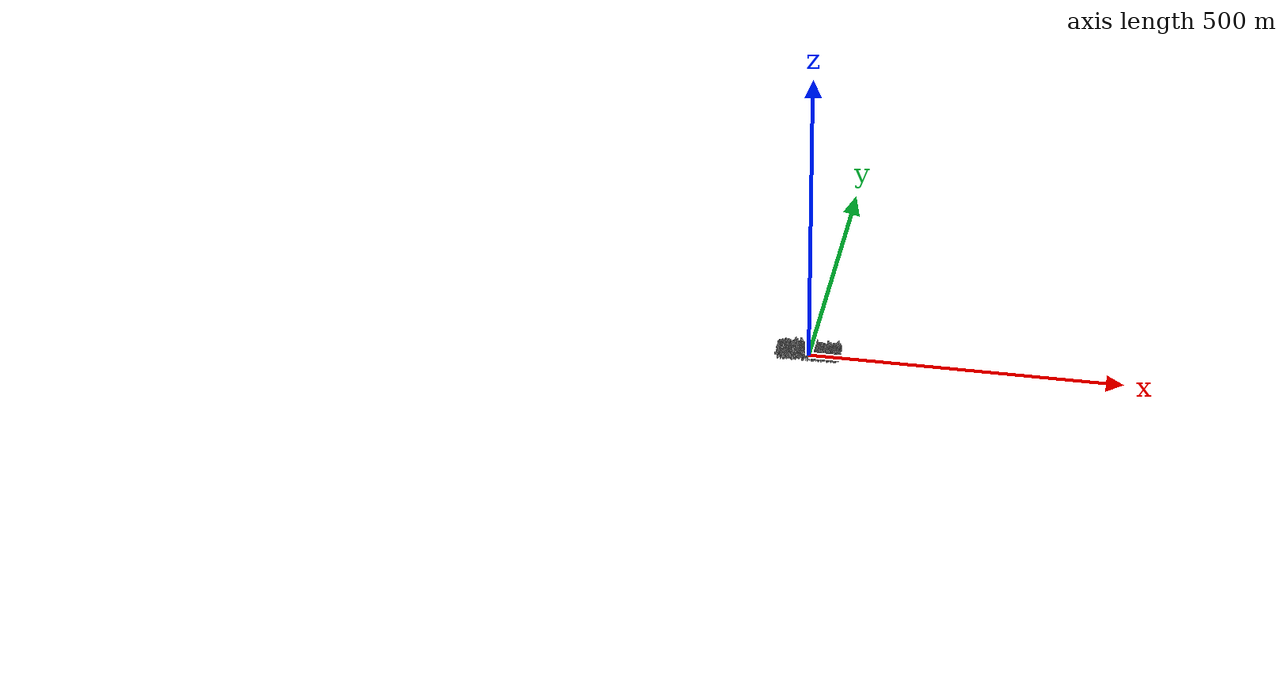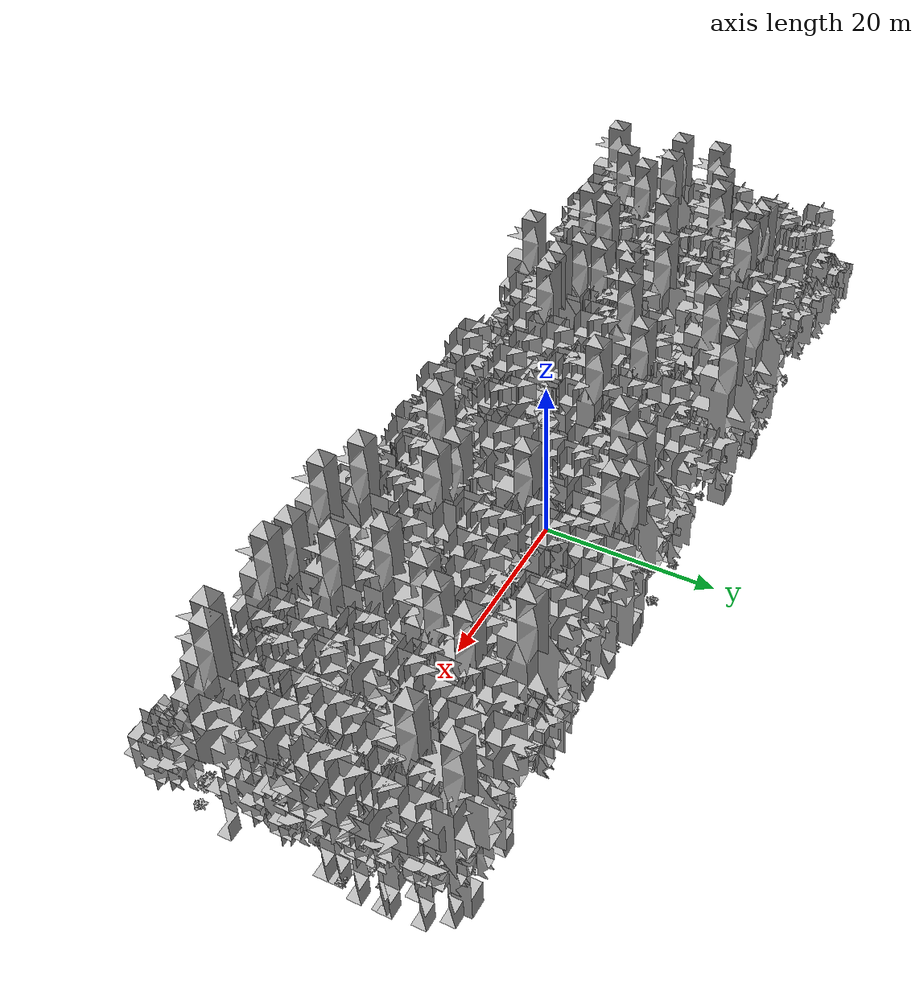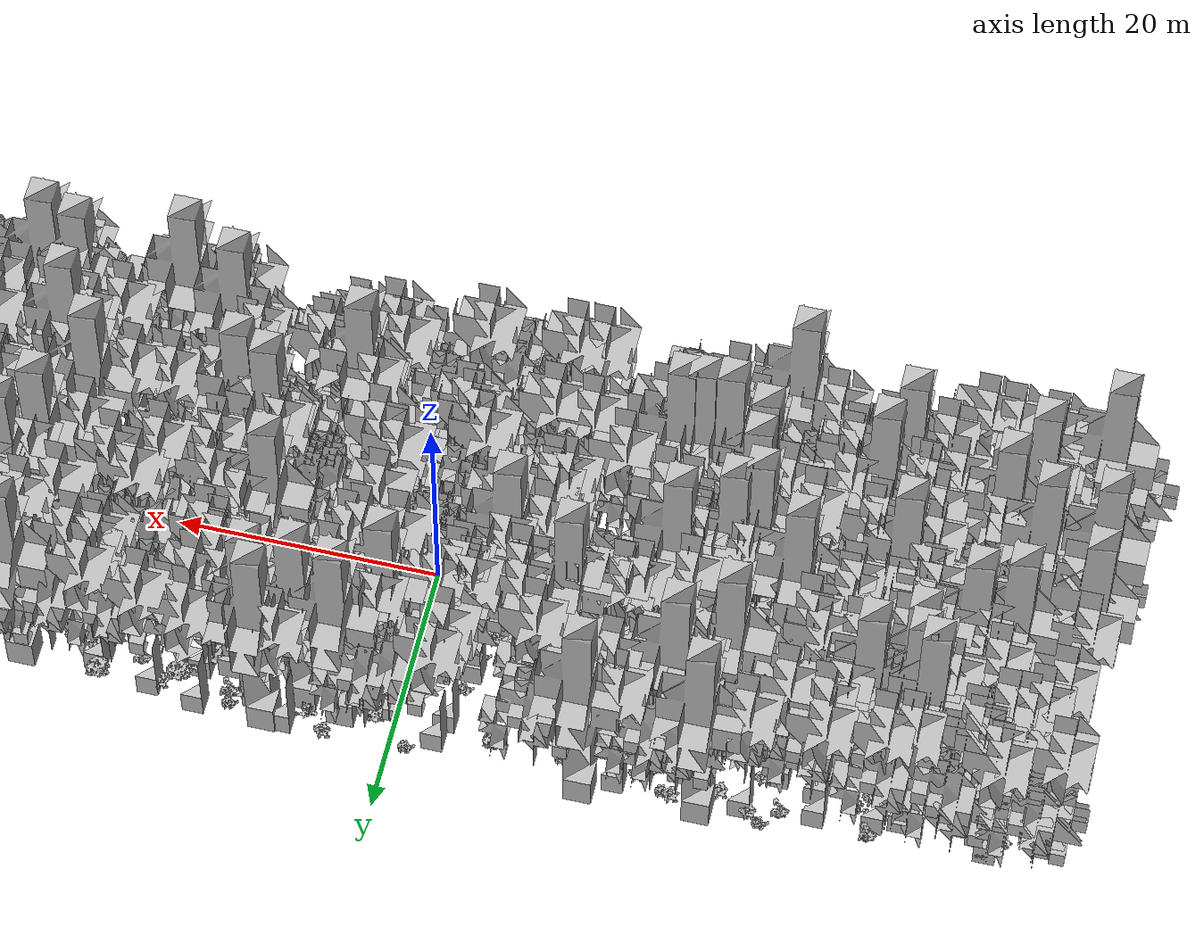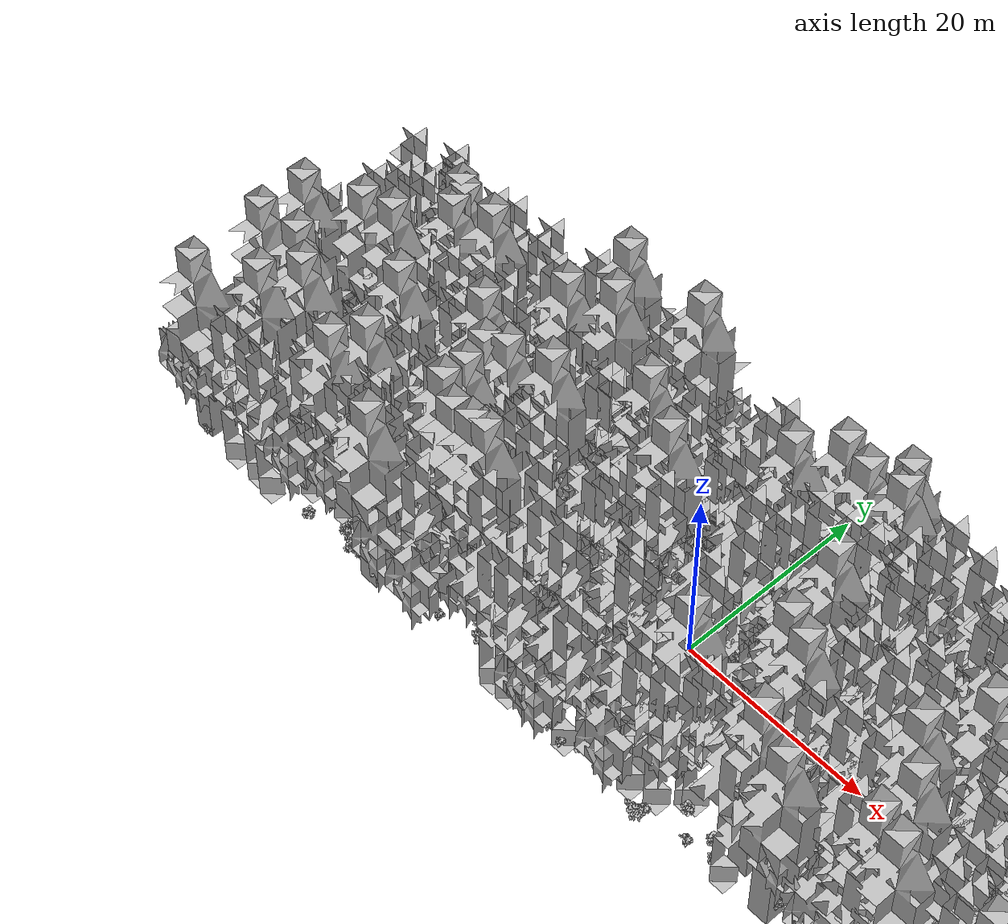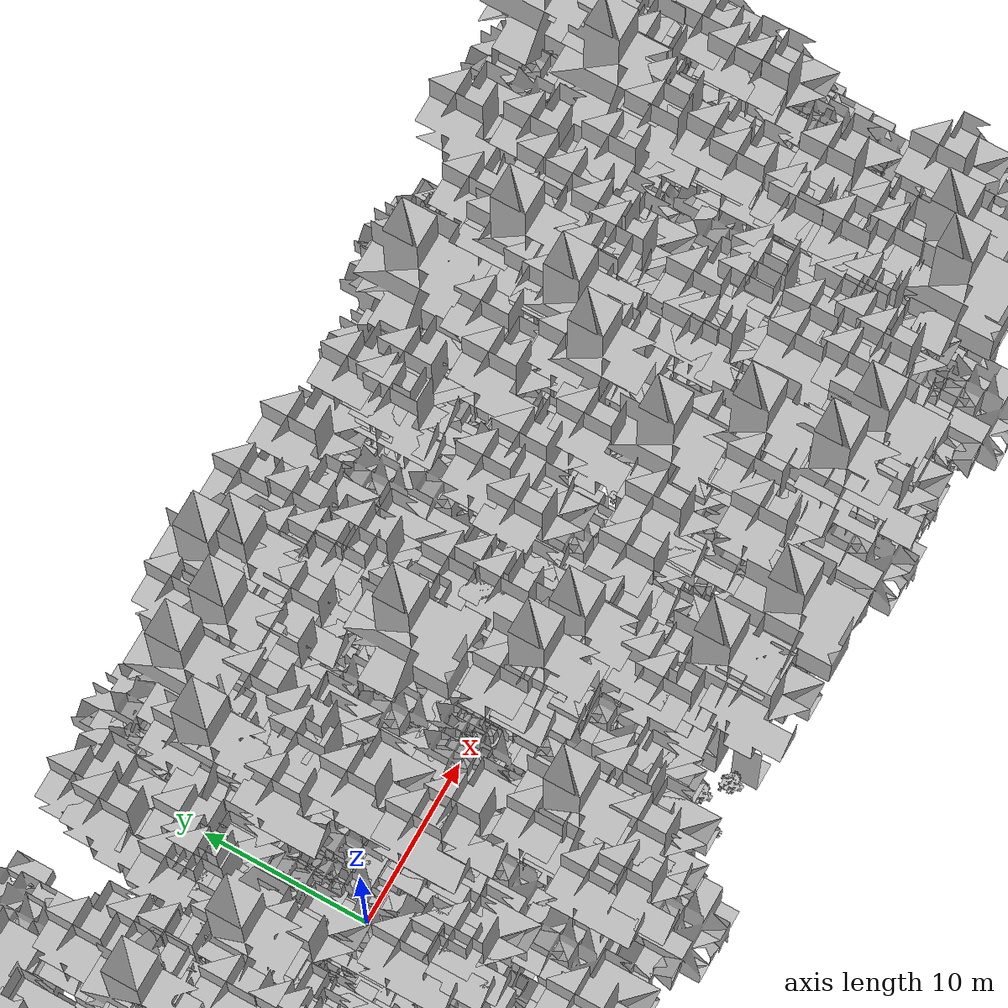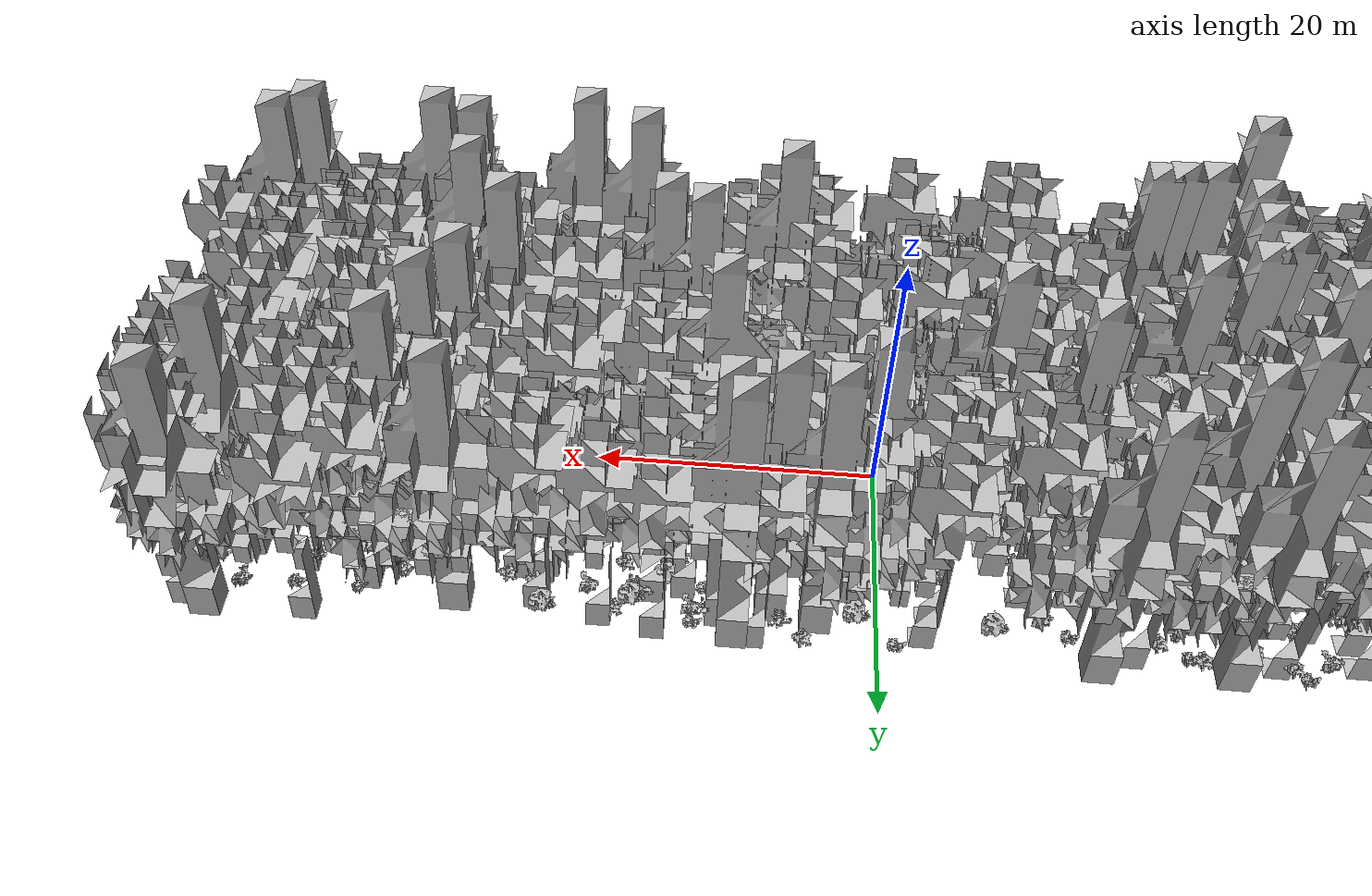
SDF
<sdf version="1.7">
    <world name="default">
        <plugin name="mrs_gazebo_static_transform_republisher_plugin" filename="libMrsGazeboCommonResources_StaticTransformRepublisher.so"/>
        <spherical_coordinates>
            <surface_model>EARTH_WGS84</surface_model>
            <latitude_deg>47.3977</latitude_deg>
            <longitude_deg>8.54559</longitude_deg>
            <elevation>0</elevation>
            <heading_deg>0</heading_deg>
        </spherical_coordinates>
        <physics name="default_physics" default="0" type="ode">
            <ode>
                <solver>
                    <type>quick</type>
                    <iters>10</iters>
                    <sor>1.3</sor>
                    <use_dynamic_moi_rescaling>0</use_dynamic_moi_rescaling>
                </solver>
                <constraints>
                    <cfm>0</cfm>
                    <erp>0.2</erp>
                    <contact_max_correcting_vel>1000</contact_max_correcting_vel>
                    <contact_surface_layer>0.001</contact_surface_layer>
                </constraints>
            </ode>
            <max_step_size>0.004</max_step_size>
            <real_time_factor>1</real_time_factor>
            <real_time_update_rate>250</real_time_update_rate>
        </physics>
        <scene>
            <shadows>0</shadows>
            <ambient>0.4 0.4 0.4 1</ambient>
            <background>0.7 0.7 0.7 1</background>
        </scene>
        <light name="sun" type="directional">
            <pose>0 0 1000 0.4 0.2 0</pose>
            <diffuse>1 1 1 1</diffuse>
            <specular>0.6 0.6 0.6 1</specular>
            <direction>0.1 0.1 -0.9</direction>
            <attenuation>
                <range>20</range>
                <constant>0.5</constant>
                <linear>0.01</linear>
                <quadratic>0.001</quadratic>
            </attenuation>
            <cast_shadows>1</cast_shadows>
            <spot>
                <inner_angle>0</inner_angle>
                <outer_angle>0</outer_angle>
                <falloff>0</falloff>
            </spot>
        </light>
        <model name="ground_plane">
            <static>1</static>
            <link name="link">
                <collision name="collision">
                    <pose>0 0 0 0 -0 0</pose>
                    <geometry>
                        <plane>
                            <normal>0 0 1</normal>
                            <size>100 100</size>
                        </plane>
                    </geometry>
                    <surface>
                        <contact>
                            <ode>
                                <min_depth>0.01</min_depth>
                                <max_vel>0</max_vel>
                            </ode>
                        </contact>
                        <friction>
                            <ode/>
                            <torsional>
                                <ode/>
                            </torsional>
                        </friction>
                        <bounce/>
                    </surface>
                    <max_contacts>10</max_contacts>
                </collision>
                <visual name="grass">
                    <pose>0 0 0 0 -0 0</pose>
                    <cast_shadows>0</cast_shadows>
                    <geometry>
                        <mesh>
                            <scale>0.5814285714285714 0.18142857142857144 0.1</scale>
                            <uri>file://grass_plane/meshes/grass_plane.dae</uri>
                        </mesh>
                    </geometry>
                </visual>
                <self_collide>0</self_collide>
                <enable_wind>0</enable_wind>
                <kinematic>0</kinematic>
            </link>
        </model>
        <model name="the_void">
            <static>1</static>
            <link name="link">
                <pose>0 0 0.1 0 -0 0</pose>
                <visual name="the_void">
                    <pose>0 0 2 0 -0 0</pose>
                    <geometry>
                        <sphere>
                            <radius>0.25</radius>
                        </sphere>
                    </geometry>
                    <material>
                        <script>
                            <uri>file://media/materials/scripts/Gazebo.material</uri>
                            <name>Gazebo/Black</name>
                        </script>
                    </material>
                </visual>
                <self_collide>0</self_collide>
                <enable_wind>0</enable_wind>
                <kinematic>0</kinematic>
            </link>
            <pose>-1000 -1000 0 0 -0 0</pose>
        </model>
        <gui fullscreen="0">
            <camera name="camera">
                <pose>35.1577 98.6044 40.0204 0 0.407996 -1.99761</pose>
                <view_controller>orbit</view_controller>
                <projection_type>perspective</projection_type>
            </camera>
        </gui>
        <plugin name="mrs_gazebo_rviz_cam_synchronizer" filename="libMrsGazeboCommonResources_RvizCameraSynchronizer.so">
            <target_frame_id>gazebo_user_camera</target_frame_id>
            <world_origin_frame_id>uav1/gps_origin</world_origin_frame_id>
            <frame_to_follow>uav1</frame_to_follow>
        </plugin>
        <gravity>0 0 -9.8066</gravity>
        <magnetic_field>6e-06 2.3e-05 -4.2e-05</magnetic_field>
        <atmosphere type="adiabatic"/>
        <wind/>
        <model name="Tree 0">
            <static>1</static>
            <pose>29.50679900570651 13.994429369647964 0 1.57079 -0 0</pose>
            <link name="link">
                <pose>0 0 0 0 -0 0</pose>
                <collision name="collision">
                    <geometry>
                        <mesh>
                            <scale>3.5 5 3.5</scale>
                            <uri>model://tree_2/meshes/tree_2.obj</uri>
                        </mesh>
                    </geometry>
                    <max_contacts>10</max_contacts>
                    <surface>
                        <contact>
                            <ode/>
                        </contact>
                        <bounce/>
                        <friction>
                            <torsional>
                                <ode/>
                            </torsional>
                            <ode/>
                        </friction>
                    </surface>
                </collision>
                <visual name="visual">
                    <geometry>
                        <mesh>
                            <scale>3.5 5 3.5</scale>
                            <uri>model://tree_2/meshes/tree_2.obj</uri>
                        </mesh>
                    </geometry>
                </visual>
                <self_collide>0</self_collide>
                <enable_wind>0</enable_wind>
                <kinematic>0</kinematic>
            </link>
        </model>
        <model name="Tree 1">
            <static>1</static>
            <pose>-43.7632680910619 -11.73446667176673 0 1.57079 -0 0</pose>
            <link name="link">
                <pose>0 0 0 0 -0 0</pose>
                <collision name="collision">
                    <geometry>
                        <mesh>
                            <scale>3.5 5 3.5</scale>
                            <uri>model://tree_2/meshes/tree_2.obj</uri>
                        </mesh>
                    </geometry>
                    <max_contacts>10</max_contacts>
                    <surface>
                        <contact>
                            <ode/>
                        </contact>
                        <bounce/>
                        <friction>
                            <torsional>
                                <ode/>
                            </torsional>
                            <ode/>
                        </friction>
                    </surface>
                </collision>
                <visual name="visual">
                    <geometry>
                        <mesh>
                            <scale>3.5 5 3.5</scale>
                            <uri>model://tree_2/meshes/tree_2.obj</uri>
                        </mesh>
                    </geometry>
                </visual>
                <self_collide>0</self_collide>
                <enable_wind>0</enable_wind>
                <kinematic>0</kinematic>
            </link>
        </model>
        <model name="Tree 2">
            <static>1</static>
            <pose>-35.749304901070204 8.602493675211566 0 1.57079 -0 0</pose>
            <link name="link">
                <pose>0 0 0 0 -0 0</pose>
                <collision name="collision">
                    <geometry>
                        <mesh>
                            <scale>3.5 5 3.5</scale>
                            <uri>model://tree_2/meshes/tree_2.obj</uri>
                        </mesh>
                    </geometry>
                    <max_contacts>10</max_contacts>
                    <surface>
                        <contact>
                            <ode/>
                        </contact>
                        <bounce/>
                        <friction>
                            <torsional>
                                <ode/>
                            </torsional>
                            <ode/>
                        </friction>
                    </surface>
                </collision>
                <visual name="visual">
                    <geometry>
                        <mesh>
                            <scale>3.5 5 3.5</scale>
                            <uri>model://tree_2/meshes/tree_2.obj</uri>
                        </mesh>
                    </geometry>
                </visual>
                <self_collide>0</self_collide>
                <enable_wind>0</enable_wind>
                <kinematic>0</kinematic>
            </link>
        </model>
        <model name="Tree 3">
            <static>1</static>
            <pose>8.2996810708756 5.9657496222839335 0 1.57079 -0 0</pose>
            <link name="link">
                <pose>0 0 0 0 -0 0</pose>
                <collision name="collision">
                    <geometry>
                        <mesh>
                            <scale>3.5 5 3.5</scale>
                            <uri>model://tree_2/meshes/tree_2.obj</uri>
                        </mesh>
                    </geometry>
                    <max_contacts>10</max_contacts>
                    <surface>
                        <contact>
                            <ode/>
                        </contact>
                        <bounce/>
                        <friction>
                            <torsional>
                                <ode/>
                            </torsional>
                            <ode/>
                        </friction>
                    </surface>
                </collision>
                <visual name="visual">
                    <geometry>
                        <mesh>
                            <scale>3.5 5 3.5</scale>
                            <uri>model://tree_2/meshes/tree_2.obj</uri>
                        </mesh>
                    </geometry>
                </visual>
                <self_collide>0</self_collide>
                <enable_wind>0</enable_wind>
                <kinematic>0</kinematic>
            </link>
        </model>
        <model name="Tree 4">
            <static>1</static>
            <pose>38.91275151909173 10.886615701169202 0 1.57079 -0 0</pose>
            <link name="link">
                <pose>0 0 0 0 -0 0</pose>
                <collision name="collision">
                    <geometry>
                        <mesh>
                            <scale>3.5 5 3.5</scale>
                            <uri>model://tree_9/meshes/tree_9.obj</uri>
                        </mesh>
                    </geometry>
                    <max_contacts>10</max_contacts>
                    <surface>
                        <contact>
                            <ode/>
                        </contact>
                        <bounce/>
                        <friction>
                            <torsional>
                                <ode/>
                            </torsional>
                            <ode/>
                        </friction>
                    </surface>
                </collision>
                <visual name="visual">
                    <geometry>
                        <mesh>
                            <scale>3.5 5 3.5</scale>
                            <uri>model://tree_9/meshes/tree_9.obj</uri>
                        </mesh>
                    </geometry>
                </visual>
                <self_collide>0</self_collide>
                <enable_wind>0</enable_wind>
                <kinematic>0</kinematic>
            </link>
        </model>
        <model name="Tree 5">
            <static>1</static>
            <pose>38.91924543740703 10.909706359003845 0 1.57079 -0 0</pose>
            <link name="link">
                <pose>0 0 0 0 -0 0</pose>
                <collision name="collision">
                    <geometry>
                        <mesh>
                            <scale>3.5 5 3.5</scale>
                            <uri>model://tree_2/meshes/tree_2.obj</uri>
                        </mesh>
                    </geometry>
                    <max_contacts>10</max_contacts>
                    <surface>
                        <contact>
                            <ode/>
                        </contact>
                        <bounce/>
                        <friction>
                            <torsional>
                                <ode/>
                            </torsional>
                            <ode/>
                        </friction>
                    </surface>
                </collision>
                <visual name="visual">
                    <geometry>
                        <mesh>
                            <scale>3.5 5 3.5</scale>
                            <uri>model://tree_2/meshes/tree_2.obj</uri>
                        </mesh>
                    </geometry>
                </visual>
                <self_collide>0</self_collide>
                <enable_wind>0</enable_wind>
                <kinematic>0</kinematic>
            </link>
        </model>
        <model name="Tree 6">
            <static>1</static>
            <pose>6.165143810758373 11.492331317376358 0 1.57079 -0 0</pose>
            <link name="link">
                <pose>0 0 0 0 -0 0</pose>
                <collision name="collision">
                    <geometry>
                        <mesh>
                            <scale>3.5 5 3.5</scale>
                            <uri>model://tree_2/meshes/tree_2.obj</uri>
                        </mesh>
                    </geometry>
                    <max_contacts>10</max_contacts>
                    <surface>
                        <contact>
                            <ode/>
                        </contact>
                        <bounce/>
                        <friction>
                            <torsional>
                                <ode/>
                            </torsional>
                            <ode/>
                        </friction>
                    </surface>
                </collision>
                <visual name="visual">
                    <geometry>
                        <mesh>
                            <scale>3.5 5 3.5</scale>
                            <uri>model://tree_2/meshes/tree_2.obj</uri>
                        </mesh>
                    </geometry>
                </visual>
                <self_collide>0</self_collide>
                <enable_wind>0</enable_wind>
                <kinematic>0</kinematic>
            </link>
        </model>
        <model name="Tree 7">
            <static>1</static>
            <pose>-26.50356392235294 -10.003784884026725 0 1.57079 -0 0</pose>
            <link name="link">
                <pose>0 0 0 0 -0 0</pose>
                <collision name="collision">
                    <geometry>
                        <mesh>
                            <scale>3.5 5 3.5</scale>
                            <uri>model://tree_2/meshes/tree_2.obj</uri>
                        </mesh>
                    </geometry>
                    <max_contacts>10</max_contacts>
                    <surface>
                        <contact>
                            <ode/>
                        </contact>
                        <bounce/>
                        <friction>
                            <torsional>
                                <ode/>
                            </torsional>
                            <ode/>
                        </friction>
                    </surface>
                </collision>
                <visual name="visual">
                    <geometry>
                        <mesh>
                            <scale>3.5 5 3.5</scale>
                            <uri>model://tree_2/meshes/tree_2.obj</uri>
                        </mesh>
                    </geometry>
                </visual>
                <self_collide>0</self_collide>
                <enable_wind>0</enable_wind>
                <kinematic>0</kinematic>
            </link>
        </model>
        <model name="Tree 8">
            <static>1</static>
            <pose>-22.823493398514426 14.292087558246756 0 1.57079 -0 0</pose>
            <link name="link">
                <pose>0 0 0 0 -0 0</pose>
                <collision name="collision">
                    <geometry>
                        <mesh>
                            <scale>3.5 5 3.5</scale>
                            <uri>model://tree_4/meshes/tree_4.obj</uri>
                        </mesh>
                    </geometry>
                    <max_contacts>10</max_contacts>
                    <surface>
                        <contact>
                            <ode/>
                        </contact>
                        <bounce/>
                        <friction>
                            <torsional>
                                <ode/>
                            </torsional>
                            <ode/>
                        </friction>
                    </surface>
                </collision>
                <visual name="visual">
                    <geometry>
                        <mesh>
                            <scale>3.5 5 3.5</scale>
                            <uri>model://tree_4/meshes/tree_4.obj</uri>
                        </mesh>
                    </geometry>
                </visual>
                <self_collide>0</self_collide>
                <enable_wind>0</enable_wind>
                <kinematic>0</kinematic>
            </link>
        </model>
        <model name="Tree 9">
            <static>1</static>
            <pose>39.64637547037282 -8.828869722652001 0 1.57079 -0 0</pose>
            <link name="link">
                <pose>0 0 0 0 -0 0</pose>
                <collision name="collision">
                    <geometry>
                        <mesh>
                            <scale>3.5 5 3.5</scale>
                            <uri>model://tree_9/meshes/tree_9.obj</uri>
                        </mesh>
                    </geometry>
                    <max_contacts>10</max_contacts>
                    <surface>
                        <contact>
                            <ode/>
                        </contact>
                        <bounce/>
                        <friction>
                            <torsional>
                                <ode/>
                            </torsional>
                            <ode/>
                        </friction>
                    </surface>
                </collision>
                <visual name="visual">
                    <geometry>
                        <mesh>
                            <scale>3.5 5 3.5</scale>
                            <uri>model://tree_9/meshes/tree_9.obj</uri>
                        </mesh>
                    </geometry>
                </visual>
                <self_collide>0</self_collide>
                <enable_wind>0</enable_wind>
                <kinematic>0</kinematic>
            </link>
        </model>
        <model name="Tree 10">
            <static>1</static>
            <pose>-21.879696404630316 -0.82176129421679 0 1.57079 -0 0</pose>
            <link name="link">
                <pose>0 0 0 0 -0 0</pose>
                <collision name="collision">
                    <geometry>
                        <mesh>
                            <scale>3.5 5 3.5</scale>
                            <uri>model://tree_4/meshes/tree_4.obj</uri>
                        </mesh>
                    </geometry>
                    <max_contacts>10</max_contacts>
                    <surface>
                        <contact>
                            <ode/>
                        </contact>
                        <bounce/>
                        <friction>
                            <torsional>
                                <ode/>
                            </torsional>
                            <ode/>
                        </friction>
                    </surface>
                </collision>
                <visual name="visual">
                    <geometry>
                        <mesh>
                            <scale>3.5 5 3.5</scale>
                            <uri>model://tree_4/meshes/tree_4.obj</uri>
                        </mesh>
                    </geometry>
                </visual>
                <self_collide>0</self_collide>
                <enable_wind>0</enable_wind>
                <kinematic>0</kinematic>
            </link>
        </model>
        <model name="Tree 11">
            <static>1</static>
            <pose>46.008525365228806 13.301327726597798 0 1.57079 -0 0</pose>
            <link name="link">
                <pose>0 0 0 0 -0 0</pose>
                <collision name="collision">
                    <geometry>
                        <mesh>
                            <scale>3.5 5 3.5</scale>
                            <uri>model://tree_2/meshes/tree_2.obj</uri>
                        </mesh>
                    </geometry>
                    <max_contacts>10</max_contacts>
                    <surface>
                        <contact>
                            <ode/>
                        </contact>
                        <bounce/>
                        <friction>
                            <torsional>
                                <ode/>
                            </torsional>
                            <ode/>
                        </friction>
                    </surface>
                </collision>
                <visual name="visual">
                    <geometry>
                        <mesh>
                            <scale>3.5 5 3.5</scale>
                            <uri>model://tree_2/meshes/tree_2.obj</uri>
                        </mesh>
                    </geometry>
                </visual>
                <self_collide>0</self_collide>
                <enable_wind>0</enable_wind>
                <kinematic>0</kinematic>
            </link>
        </model>
        <model name="Tree 12">
            <static>1</static>
            <pose>42.74366495596955 -8.739128185458405 0 1.57079 -0 0</pose>
            <link name="link">
                <pose>0 0 0 0 -0 0</pose>
                <collision name="collision">
                    <geometry>
                        <mesh>
                            <scale>3.5 5 3.5</scale>
                            <uri>model://tree_9/meshes/tree_9.obj</uri>
                        </mesh>
                    </geometry>
                    <max_contacts>10</max_contacts>
                    <surface>
                        <contact>
                            <ode/>
                        </contact>
                        <bounce/>
                        <friction>
                            <torsional>
                                <ode/>
                            </torsional>
                            <ode/>
                        </friction>
                    </surface>
                </collision>
                <visual name="visual">
                    <geometry>
                        <mesh>
                            <scale>3.5 5 3.5</scale>
                            <uri>model://tree_9/meshes/tree_9.obj</uri>
                        </mesh>
                    </geometry>
                </visual>
                <self_collide>0</self_collide>
                <enable_wind>0</enable_wind>
                <kinematic>0</kinematic>
            </link>
        </model>
        <model name="Tree 13">
            <static>1</static>
            <pose>-12.948915257245588 -5.804248007386818 0 1.57079 -0 0</pose>
            <link name="link">
                <pose>0 0 0 0 -0 0</pose>
                <collision name="collision">
                    <geometry>
                        <mesh>
                            <scale>3.5 5 3.5</scale>
                            <uri>model://tree_9/meshes/tree_9.obj</uri>
                        </mesh>
                    </geometry>
                    <max_contacts>10</max_contacts>
                    <surface>
                        <contact>
                            <ode/>
                        </contact>
                        <bounce/>
                        <friction>
                            <torsional>
                                <ode/>
                            </torsional>
                            <ode/>
                        </friction>
                    </surface>
                </collision>
                <visual name="visual">
                    <geometry>
                        <mesh>
                            <scale>3.5 5 3.5</scale>
                            <uri>model://tree_9/meshes/tree_9.obj</uri>
                        </mesh>
                    </geometry>
                </visual>
                <self_collide>0</self_collide>
                <enable_wind>0</enable_wind>
                <kinematic>0</kinematic>
            </link>
        </model>
        <model name="Tree 14">
            <static>1</static>
            <pose>-1.332197806563535 -3.850424063560032 0 1.57079 -0 0</pose>
            <link name="link">
                <pose>0 0 0 0 -0 0</pose>
                <collision name="collision">
                    <geometry>
                        <mesh>
                            <scale>3.5 5 3.5</scale>
                            <uri>model://tree_2/meshes/tree_2.obj</uri>
                        </mesh>
                    </geometry>
                    <max_contacts>10</max_contacts>
                    <surface>
                        <contact>
                            <ode/>
                        </contact>
                        <bounce/>
                        <friction>
                            <torsional>
                                <ode/>
                            </torsional>
                            <ode/>
                        </friction>
                    </surface>
                </collision>
                <visual name="visual">
                    <geometry>
                        <mesh>
                            <scale>3.5 5 3.5</scale>
                            <uri>model://tree_2/meshes/tree_2.obj</uri>
                        </mesh>
                    </geometry>
                </visual>
                <self_collide>0</self_collide>
                <enable_wind>0</enable_wind>
                <kinematic>0</kinematic>
            </link>
        </model>
        <model name="Tree 15">
            <static>1</static>
            <pose>-16.50872034653105 -3.425788888725897 0 1.57079 -0 0</pose>
            <link name="link">
                <pose>0 0 0 0 -0 0</pose>
                <collision name="collision">
                    <geometry>
                        <mesh>
                            <scale>3.5 5 3.5</scale>
                            <uri>model://tree_9/meshes/tree_9.obj</uri>
                        </mesh>
                    </geometry>
                    <max_contacts>10</max_contacts>
                    <surface>
                        <contact>
                            <ode/>
                        </contact>
                        <bounce/>
                        <friction>
                            <torsional>
                                <ode/>
                            </torsional>
                            <ode/>
                        </friction>
                    </surface>
                </collision>
                <visual name="visual">
                    <geometry>
                        <mesh>
                            <scale>3.5 5 3.5</scale>
                            <uri>model://tree_9/meshes/tree_9.obj</uri>
                        </mesh>
                    </geometry>
                </visual>
                <self_collide>0</self_collide>
                <enable_wind>0</enable_wind>
                <kinematic>0</kinematic>
            </link>
        </model>
        <model name="Tree 16">
            <static>1</static>
            <pose>-23.569645449014402 7.636549871095344 0 1.57079 -0 0</pose>
            <link name="link">
                <pose>0 0 0 0 -0 0</pose>
                <collision name="collision">
                    <geometry>
                        <mesh>
                            <scale>3.5 5 3.5</scale>
                            <uri>model://tree_4/meshes/tree_4.obj</uri>
                        </mesh>
                    </geometry>
                    <max_contacts>10</max_contacts>
                    <surface>
                        <contact>
                            <ode/>
                        </contact>
                        <bounce/>
                        <friction>
                            <torsional>
                                <ode/>
                            </torsional>
                            <ode/>
                        </friction>
                    </surface>
                </collision>
                <visual name="visual">
                    <geometry>
                        <mesh>
                            <scale>3.5 5 3.5</scale>
                            <uri>model://tree_4/meshes/tree_4.obj</uri>
                        </mesh>
                    </geometry>
                </visual>
                <self_collide>0</self_collide>
                <enable_wind>0</enable_wind>
                <kinematic>0</kinematic>
            </link>
        </model>
        <model name="Tree 17">
            <static>1</static>
            <pose>36.869466375832616 -6.88676190946172 0 1.57079 -0 0</pose>
            <link name="link">
                <pose>0 0 0 0 -0 0</pose>
                <collision name="collision">
                    <geometry>
                        <mesh>
                            <scale>3.5 5 3.5</scale>
                            <uri>model://tree_9/meshes/tree_9.obj</uri>
                        </mesh>
                    </geometry>
                    <max_contacts>10</max_contacts>
                    <surface>
                        <contact>
                            <ode/>
                        </contact>
                        <bounce/>
                        <friction>
                            <torsional>
                                <ode/>
                            </torsional>
                            <ode/>
                        </friction>
                    </surface>
                </collision>
                <visual name="visual">
                    <geometry>
                        <mesh>
                            <scale>3.5 5 3.5</scale>
                            <uri>model://tree_9/meshes/tree_9.obj</uri>
                        </mesh>
                    </geometry>
                </visual>
                <self_collide>0</self_collide>
                <enable_wind>0</enable_wind>
                <kinematic>0</kinematic>
            </link>
        </model>
        <model name="Tree 18">
            <static>1</static>
            <pose>33.241115109427554 -1.7920709924134535 0 1.57079 -0 0</pose>
            <link name="link">
                <pose>0 0 0 0 -0 0</pose>
                <collision name="collision">
                    <geometry>
                        <mesh>
                            <scale>3.5 5 3.5</scale>
                            <uri>model://tree_9/meshes/tree_9.obj</uri>
                        </mesh>
                    </geometry>
                    <max_contacts>10</max_contacts>
                    <surface>
                        <contact>
                            <ode/>
                        </contact>
                        <bounce/>
                        <friction>
                            <torsional>
                                <ode/>
                            </torsional>
                            <ode/>
                        </friction>
                    </surface>
                </collision>
                <visual name="visual">
                    <geometry>
                        <mesh>
                            <scale>3.5 5 3.5</scale>
                            <uri>model://tree_9/meshes/tree_9.obj</uri>
                        </mesh>
                    </geometry>
                </visual>
                <self_collide>0</self_collide>
                <enable_wind>0</enable_wind>
                <kinematic>0</kinematic>
            </link>
        </model>
        <model name="Tree 19">
            <static>1</static>
            <pose>-40.874871581768886 -3.1254078904174634 0 1.57079 -0 0</pose>
            <link name="link">
                <pose>0 0 0 0 -0 0</pose>
                <collision name="collision">
                    <geometry>
                        <mesh>
                            <scale>3.5 5 3.5</scale>
                            <uri>model://tree_2/meshes/tree_2.obj</uri>
                        </mesh>
                    </geometry>
                    <max_contacts>10</max_contacts>
                    <surface>
                        <contact>
                            <ode/>
                        </contact>
                        <bounce/>
                        <friction>
                            <torsional>
                                <ode/>
                            </torsional>
                            <ode/>
                        </friction>
                    </surface>
                </collision>
                <visual name="visual">
                    <geometry>
                        <mesh>
                            <scale>3.5 5 3.5</scale>
                            <uri>model://tree_2/meshes/tree_2.obj</uri>
                        </mesh>
                    </geometry>
                </visual>
                <self_collide>0</self_collide>
                <enable_wind>0</enable_wind>
                <kinematic>0</kinematic>
            </link>
        </model>
        <model name="Tree 20">
            <static>1</static>
            <pose>-35.57021191299327 -12.110989004787552 0 1.57079 -0 0</pose>
            <link name="link">
                <pose>0 0 0 0 -0 0</pose>
                <collision name="collision">
                    <geometry>
                        <mesh>
                            <scale>3.5 5 3.5</scale>
                            <uri>model://tree_9/meshes/tree_9.obj</uri>
                        </mesh>
                    </geometry>
                    <max_contacts>10</max_contacts>
                    <surface>
                        <contact>
                            <ode/>
                        </contact>
                        <bounce/>
                        <friction>
                            <torsional>
                                <ode/>
                            </torsional>
                            <ode/>
                        </friction>
                    </surface>
                </collision>
                <visual name="visual">
                    <geometry>
                        <mesh>
                            <scale>3.5 5 3.5</scale>
                            <uri>model://tree_9/meshes/tree_9.obj</uri>
                        </mesh>
                    </geometry>
                </visual>
                <self_collide>0</self_collide>
                <enable_wind>0</enable_wind>
                <kinematic>0</kinematic>
            </link>
        </model>
        <model name="Tree 21">
            <static>1</static>
            <pose>-39.96532088759932 13.575628985826079 0 1.57079 -0 0</pose>
            <link name="link">
                <pose>0 0 0 0 -0 0</pose>
                <collision name="collision">
                    <geometry>
                        <mesh>
                            <scale>3.5 5 3.5</scale>
                            <uri>model://tree_2/meshes/tree_2.obj</uri>
                        </mesh>
                    </geometry>
                    <max_contacts>10</max_contacts>
                    <surface>
                        <contact>
                            <ode/>
                        </contact>
                        <bounce/>
                        <friction>
                            <torsional>
                                <ode/>
                            </torsional>
                            <ode/>
                        </friction>
                    </surface>
                </collision>
                <visual name="visual">
                    <geometry>
                        <mesh>
                            <scale>3.5 5 3.5</scale>
                            <uri>model://tree_2/meshes/tree_2.obj</uri>
                        </mesh>
                    </geometry>
                </visual>
                <self_collide>0</self_collide>
                <enable_wind>0</enable_wind>
                <kinematic>0</kinematic>
            </link>
        </model>
        <model name="Tree 22">
            <static>1</static>
            <pose>-21.982610655278286 -4.060572204806526 0 1.57079 -0 0</pose>
            <link name="link">
                <pose>0 0 0 0 -0 0</pose>
                <collision name="collision">
                    <geometry>
                        <mesh>
                            <scale>3.5 5 3.5</scale>
                            <uri>model://tree_9/meshes/tree_9.obj</uri>
                        </mesh>
                    </geometry>
                    <max_contacts>10</max_contacts>
                    <surface>
                        <contact>
                            <ode/>
                        </contact>
                        <bounce/>
                        <friction>
                            <torsional>
                                <ode/>
                            </torsional>
                            <ode/>
                        </friction>
                    </surface>
                </collision>
                <visual name="visual">
                    <geometry>
                        <mesh>
                            <scale>3.5 5 3.5</scale>
                            <uri>model://tree_9/meshes/tree_9.obj</uri>
                        </mesh>
                    </geometry>
                </visual>
                <self_collide>0</self_collide>
                <enable_wind>0</enable_wind>
                <kinematic>0</kinematic>
            </link>
        </model>
        <model name="Tree 23">
            <static>1</static>
            <pose>-11.818554850499751 4.779480041875914 0 1.57079 -0 0</pose>
            <link name="link">
                <pose>0 0 0 0 -0 0</pose>
                <collision name="collision">
                    <geometry>
                        <mesh>
                            <scale>3.5 5 3.5</scale>
                            <uri>model://tree_9/meshes/tree_9.obj</uri>
                        </mesh>
                    </geometry>
                    <max_contacts>10</max_contacts>
                    <surface>
                        <contact>
                            <ode/>
                        </contact>
                        <bounce/>
                        <friction>
                            <torsional>
                                <ode/>
                            </torsional>
                            <ode/>
                        </friction>
                    </surface>
                </collision>
                <visual name="visual">
                    <geometry>
                        <mesh>
                            <scale>3.5 5 3.5</scale>
                            <uri>model://tree_9/meshes/tree_9.obj</uri>
                        </mesh>
                    </geometry>
                </visual>
                <self_collide>0</self_collide>
                <enable_wind>0</enable_wind>
                <kinematic>0</kinematic>
            </link>
        </model>
        <model name="Tree 24">
            <static>1</static>
            <pose>37.49811744741757 -3.8843351869077143 0 1.57079 -0 0</pose>
            <link name="link">
                <pose>0 0 0 0 -0 0</pose>
                <collision name="collision">
                    <geometry>
                        <mesh>
                            <scale>3.5 5 3.5</scale>
                            <uri>model://tree_2/meshes/tree_2.obj</uri>
                        </mesh>
                    </geometry>
                    <max_contacts>10</max_contacts>
                    <surface>
                        <contact>
                            <ode/>
                        </contact>
                        <bounce/>
                        <friction>
                            <torsional>
                                <ode/>
                            </torsional>
                            <ode/>
                        </friction>
                    </surface>
                </collision>
                <visual name="visual">
                    <geometry>
                        <mesh>
                            <scale>3.5 5 3.5</scale>
                            <uri>model://tree_2/meshes/tree_2.obj</uri>
                        </mesh>
                    </geometry>
                </visual>
                <self_collide>0</self_collide>
                <enable_wind>0</enable_wind>
                <kinematic>0</kinematic>
            </link>
        </model>
        <model name="Tree 25">
            <static>1</static>
            <pose>22.55077985762439 5.404610662665622 0 1.57079 -0 0</pose>
            <link name="link">
                <pose>0 0 0 0 -0 0</pose>
                <collision name="collision">
                    <geometry>
                        <mesh>
                            <scale>3.5 5 3.5</scale>
                            <uri>model://tree_2/meshes/tree_2.obj</uri>
                        </mesh>
                    </geometry>
                    <max_contacts>10</max_contacts>
                    <surface>
                        <contact>
                            <ode/>
                        </contact>
                        <bounce/>
                        <friction>
                            <torsional>
                                <ode/>
                            </torsional>
                            <ode/>
                        </friction>
                    </surface>
                </collision>
                <visual name="visual">
                    <geometry>
                        <mesh>
                            <scale>3.5 5 3.5</scale>
                            <uri>model://tree_2/meshes/tree_2.obj</uri>
                        </mesh>
                    </geometry>
                </visual>
                <self_collide>0</self_collide>
                <enable_wind>0</enable_wind>
                <kinematic>0</kinematic>
            </link>
        </model>
        <model name="Tree 26">
            <static>1</static>
            <pose>28.944412736091692 -5.225004428628388 0 1.57079 -0 0</pose>
            <link name="link">
                <pose>0 0 0 0 -0 0</pose>
                <collision name="collision">
                    <geometry>
                        <mesh>
                            <scale>3.5 5 3.5</scale>
                            <uri>model://tree_9/meshes/tree_9.obj</uri>
                        </mesh>
                    </geometry>
                    <max_contacts>10</max_contacts>
                    <surface>
                        <contact>
                            <ode/>
                        </contact>
                        <bounce/>
                        <friction>
                            <torsional>
                                <ode/>
                            </torsional>
                            <ode/>
                        </friction>
                    </surface>
                </collision>
                <visual name="visual">
                    <geometry>
                        <mesh>
                            <scale>3.5 5 3.5</scale>
                            <uri>model://tree_9/meshes/tree_9.obj</uri>
                        </mesh>
                    </geometry>
                </visual>
                <self_collide>0</self_collide>
                <enable_wind>0</enable_wind>
                <kinematic>0</kinematic>
            </link>
        </model>
        <model name="Tree 27">
            <static>1</static>
            <pose>-30.64663042558686 12.347929370633775 0 1.57079 -0 0</pose>
            <link name="link">
                <pose>0 0 0 0 -0 0</pose>
                <collision name="collision">
                    <geometry>
                        <mesh>
                            <scale>3.5 5 3.5</scale>
                            <uri>model://tree_2/meshes/tree_2.obj</uri>
                        </mesh>
                    </geometry>
                    <max_contacts>10</max_contacts>
                    <surface>
                        <contact>
                            <ode/>
                        </contact>
                        <bounce/>
                        <friction>
                            <torsional>
                                <ode/>
                            </torsional>
                            <ode/>
                        </friction>
                    </surface>
                </collision>
                <visual name="visual">
                    <geometry>
                        <mesh>
                            <scale>3.5 5 3.5</scale>
                            <uri>model://tree_2/meshes/tree_2.obj</uri>
                        </mesh>
                    </geometry>
                </visual>
                <self_collide>0</self_collide>
                <enable_wind>0</enable_wind>
                <kinematic>0</kinematic>
            </link>
        </model>
        <model name="Tree 28">
            <static>1</static>
            <pose>-3.7736838428580555 -7.6888656081389195 0 1.57079 -0 0</pose>
            <link name="link">
                <pose>0 0 0 0 -0 0</pose>
                <collision name="collision">
                    <geometry>
                        <mesh>
                            <scale>3.5 5 3.5</scale>
                            <uri>model://tree_2/meshes/tree_2.obj</uri>
                        </mesh>
                    </geometry>
                    <max_contacts>10</max_contacts>
                    <surface>
                        <contact>
                            <ode/>
                        </contact>
                        <bounce/>
                        <friction>
                            <torsional>
                                <ode/>
                            </torsional>
                            <ode/>
                        </friction>
                    </surface>
                </collision>
                <visual name="visual">
                    <geometry>
                        <mesh>
                            <scale>3.5 5 3.5</scale>
                            <uri>model://tree_2/meshes/tree_2.obj</uri>
                        </mesh>
                    </geometry>
                </visual>
                <self_collide>0</self_collide>
                <enable_wind>0</enable_wind>
                <kinematic>0</kinematic>
            </link>
        </model>
        <model name="Tree 29">
            <static>1</static>
            <pose>-6.554301219877615 -6.090810512705307 0 1.57079 -0 0</pose>
            <link name="link">
                <pose>0 0 0 0 -0 0</pose>
                <collision name="collision">
                    <geometry>
                        <mesh>
                            <scale>3.5 5 3.5</scale>
                            <uri>model://tree_2/meshes/tree_2.obj</uri>
                        </mesh>
                    </geometry>
                    <max_contacts>10</max_contacts>
                    <surface>
                        <contact>
                            <ode/>
                        </contact>
                        <bounce/>
                        <friction>
                            <torsional>
                                <ode/>
                            </torsional>
                            <ode/>
                        </friction>
                    </surface>
                </collision>
                <visual name="visual">
                    <geometry>
                        <mesh>
                            <scale>3.5 5 3.5</scale>
                            <uri>model://tree_2/meshes/tree_2.obj</uri>
                        </mesh>
                    </geometry>
                </visual>
                <self_collide>0</self_collide>
                <enable_wind>0</enable_wind>
                <kinematic>0</kinematic>
            </link>
        </model>
        <model name="Tree 30">
            <static>1</static>
            <pose>-25.03702476651312 -5.838302485965501 0 1.57079 -0 0</pose>
            <link name="link">
                <pose>0 0 0 0 -0 0</pose>
                <collision name="collision">
                    <geometry>
                        <mesh>
                            <scale>3.5 5 3.5</scale>
                            <uri>model://tree_9/meshes/tree_9.obj</uri>
                        </mesh>
                    </geometry>
                    <max_contacts>10</max_contacts>
                    <surface>
                        <contact>
                            <ode/>
                        </contact>
                        <bounce/>
                        <friction>
                            <torsional>
                                <ode/>
                            </torsional>
                            <ode/>
                        </friction>
                    </surface>
                </collision>
                <visual name="visual">
                    <geometry>
                        <mesh>
                            <scale>3.5 5 3.5</scale>
                            <uri>model://tree_9/meshes/tree_9.obj</uri>
                        </mesh>
                    </geometry>
                </visual>
                <self_collide>0</self_collide>
                <enable_wind>0</enable_wind>
                <kinematic>0</kinematic>
            </link>
        </model>
        <model name="Tree 31">
            <static>1</static>
            <pose>-28.263438000430686 5.230313278289948 0 1.57079 -0 0</pose>
            <link name="link">
                <pose>0 0 0 0 -0 0</pose>
                <collision name="collision">
                    <geometry>
                        <mesh>
                            <scale>3.5 5 3.5</scale>
                            <uri>model://tree_2/meshes/tree_2.obj</uri>
                        </mesh>
                    </geometry>
                    <max_contacts>10</max_contacts>
                    <surface>
                        <contact>
                            <ode/>
                        </contact>
                        <bounce/>
                        <friction>
                            <torsional>
                                <ode/>
                            </torsional>
                            <ode/>
                        </friction>
                    </surface>
                </collision>
                <visual name="visual">
                    <geometry>
                        <mesh>
                            <scale>3.5 5 3.5</scale>
                            <uri>model://tree_2/meshes/tree_2.obj</uri>
                        </mesh>
                    </geometry>
                </visual>
                <self_collide>0</self_collide>
                <enable_wind>0</enable_wind>
                <kinematic>0</kinematic>
            </link>
        </model>
        <model name="Tree 32">
            <static>1</static>
            <pose>-27.256612310869155 -12.789069161869099 0 1.57079 -0 0</pose>
            <link name="link">
                <pose>0 0 0 0 -0 0</pose>
                <collision name="collision">
                    <geometry>
                        <mesh>
                            <scale>3.5 5 3.5</scale>
                            <uri>model://tree_9/meshes/tree_9.obj</uri>
                        </mesh>
                    </geometry>
                    <max_contacts>10</max_contacts>
                    <surface>
                        <contact>
                            <ode/>
                        </contact>
                        <bounce/>
                        <friction>
                            <torsional>
                                <ode/>
                            </torsional>
                            <ode/>
                        </friction>
                    </surface>
                </collision>
                <visual name="visual">
                    <geometry>
                        <mesh>
                            <scale>3.5 5 3.5</scale>
                            <uri>model://tree_9/meshes/tree_9.obj</uri>
                        </mesh>
                    </geometry>
                </visual>
                <self_collide>0</self_collide>
                <enable_wind>0</enable_wind>
                <kinematic>0</kinematic>
            </link>
        </model>
        <model name="Tree 33">
            <static>1</static>
            <pose>41.0817297158344 -7.608581405884625 0 1.57079 -0 0</pose>
            <link name="link">
                <pose>0 0 0 0 -0 0</pose>
                <collision name="collision">
                    <geometry>
                        <mesh>
                            <scale>3.5 5 3.5</scale>
                            <uri>model://tree_2/meshes/tree_2.obj</uri>
                        </mesh>
                    </geometry>
                    <max_contacts>10</max_contacts>
                    <surface>
                        <contact>
                            <ode/>
                        </contact>
                        <bounce/>
                        <friction>
                            <torsional>
                                <ode/>
                            </torsional>
                            <ode/>
                        </friction>
                    </surface>
                </collision>
                <visual name="visual">
                    <geometry>
                        <mesh>
                            <scale>3.5 5 3.5</scale>
                            <uri>model://tree_2/meshes/tree_2.obj</uri>
                        </mesh>
                    </geometry>
                </visual>
                <self_collide>0</self_collide>
                <enable_wind>0</enable_wind>
                <kinematic>0</kinematic>
            </link>
        </model>
        <model name="Tree 34">
            <static>1</static>
            <pose>-19.914381480536715 3.428088746504386 0 1.57079 -0 0</pose>
            <link name="link">
                <pose>0 0 0 0 -0 0</pose>
                <collision name="collision">
                    <geometry>
                        <mesh>
                            <scale>3.5 5 3.5</scale>
                            <uri>model://tree_9/meshes/tree_9.obj</uri>
                        </mesh>
                    </geometry>
                    <max_contacts>10</max_contacts>
                    <surface>
                        <contact>
                            <ode/>
                        </contact>
                        <bounce/>
                        <friction>
                            <torsional>
                                <ode/>
                            </torsional>
                            <ode/>
                        </friction>
                    </surface>
                </collision>
                <visual name="visual">
                    <geometry>
                        <mesh>
                            <scale>3.5 5 3.5</scale>
                            <uri>model://tree_9/meshes/tree_9.obj</uri>
                        </mesh>
                    </geometry>
                </visual>
                <self_collide>0</self_collide>
                <enable_wind>0</enable_wind>
                <kinematic>0</kinematic>
            </link>
        </model>
        <model name="Tree 35">
            <static>1</static>
            <pose>8.299400189004785 -6.90327430463309 0 1.57079 -0 0</pose>
            <link name="link">
                <pose>0 0 0 0 -0 0</pose>
                <collision name="collision">
                    <geometry>
                        <mesh>
                            <scale>3.5 5 3.5</scale>
                            <uri>model://tree_2/meshes/tree_2.obj</uri>
                        </mesh>
                    </geometry>
                    <max_contacts>10</max_contacts>
                    <surface>
                        <contact>
                            <ode/>
                        </contact>
                        <bounce/>
                        <friction>
                            <torsional>
                                <ode/>
                            </torsional>
                            <ode/>
                        </friction>
                    </surface>
                </collision>
                <visual name="visual">
                    <geometry>
                        <mesh>
                            <scale>3.5 5 3.5</scale>
                            <uri>model://tree_2/meshes/tree_2.obj</uri>
                        </mesh>
                    </geometry>
                </visual>
                <self_collide>0</self_collide>
                <enable_wind>0</enable_wind>
                <kinematic>0</kinematic>
            </link>
        </model>
        <model name="Tree 36">
            <static>1</static>
            <pose>29.89486166564994 -11.524847804430422 0 1.57079 -0 0</pose>
            <link name="link">
                <pose>0 0 0 0 -0 0</pose>
                <collision name="collision">
                    <geometry>
                        <mesh>
                            <scale>3.5 5 3.5</scale>
                            <uri>model://tree_4/meshes/tree_4.obj</uri>
                        </mesh>
                    </geometry>
                    <max_contacts>10</max_contacts>
                    <surface>
                        <contact>
                            <ode/>
                        </contact>
                        <bounce/>
                        <friction>
                            <torsional>
                                <ode/>
                            </torsional>
                            <ode/>
                        </friction>
                    </surface>
                </collision>
                <visual name="visual">
                    <geometry>
                        <mesh>
                            <scale>3.5 5 3.5</scale>
                            <uri>model://tree_4/meshes/tree_4.obj</uri>
                        </mesh>
                    </geometry>
                </visual>
                <self_collide>0</self_collide>
                <enable_wind>0</enable_wind>
                <kinematic>0</kinematic>
            </link>
        </model>
        <model name="Tree 37">
            <static>1</static>
            <pose>-10.161082945502073 -9.421930282803805 0 1.57079 -0 0</pose>
            <link name="link">
                <pose>0 0 0 0 -0 0</pose>
                <collision name="collision">
                    <geometry>
                        <mesh>
                            <scale>3.5 5 3.5</scale>
                            <uri>model://tree_2/meshes/tree_2.obj</uri>
                        </mesh>
                    </geometry>
                    <max_contacts>10</max_contacts>
                    <surface>
                        <contact>
                            <ode/>
                        </contact>
                        <bounce/>
                        <friction>
                            <torsional>
                                <ode/>
                            </torsional>
                            <ode/>
                        </friction>
                    </surface>
                </collision>
                <visual name="visual">
                    <geometry>
                        <mesh>
                            <scale>3.5 5 3.5</scale>
                            <uri>model://tree_2/meshes/tree_2.obj</uri>
                        </mesh>
                    </geometry>
                </visual>
                <self_collide>0</self_collide>
                <enable_wind>0</enable_wind>
                <kinematic>0</kinematic>
            </link>
        </model>
        <model name="Tree 38">
            <static>1</static>
            <pose>17.38554257768574 -13.555301239482468 0 1.57079 -0 0</pose>
            <link name="link">
                <pose>0 0 0 0 -0 0</pose>
                <collision name="collision">
                    <geometry>
                        <mesh>
                            <scale>3.5 5 3.5</scale>
                            <uri>model://tree_9/meshes/tree_9.obj</uri>
                        </mesh>
                    </geometry>
                    <max_contacts>10</max_contacts>
                    <surface>
                        <contact>
                            <ode/>
                        </contact>
                        <bounce/>
                        <friction>
                            <torsional>
                                <ode/>
                            </torsional>
                            <ode/>
                        </friction>
                    </surface>
                </collision>
                <visual name="visual">
                    <geometry>
                        <mesh>
                            <scale>3.5 5 3.5</scale>
                            <uri>model://tree_9/meshes/tree_9.obj</uri>
                        </mesh>
                    </geometry>
                </visual>
                <self_collide>0</self_collide>
                <enable_wind>0</enable_wind>
                <kinematic>0</kinematic>
            </link>
        </model>
        <model name="Tree 39">
            <static>1</static>
            <pose>-40.039111166666025 -14.55704808111696 0 1.57079 -0 0</pose>
            <link name="link">
                <pose>0 0 0 0 -0 0</pose>
                <collision name="collision">
                    <geometry>
                        <mesh>
                            <scale>3.5 5 3.5</scale>
                            <uri>model://tree_9/meshes/tree_9.obj</uri>
                        </mesh>
                    </geometry>
                    <max_contacts>10</max_contacts>
                    <surface>
                        <contact>
                            <ode/>
                        </contact>
                        <bounce/>
                        <friction>
                            <torsional>
                                <ode/>
                            </torsional>
                            <ode/>
                        </friction>
                    </surface>
                </collision>
                <visual name="visual">
                    <geometry>
                        <mesh>
                            <scale>3.5 5 3.5</scale>
                            <uri>model://tree_9/meshes/tree_9.obj</uri>
                        </mesh>
                    </geometry>
                </visual>
                <self_collide>0</self_collide>
                <enable_wind>0</enable_wind>
                <kinematic>0</kinematic>
            </link>
        </model>
        <model name="Tree 40">
            <static>1</static>
            <pose>8.52702489070306 -12.382336699466435 0 1.57079 -0 0</pose>
            <link name="link">
                <pose>0 0 0 0 -0 0</pose>
                <collision name="collision">
                    <geometry>
                        <mesh>
                            <scale>3.5 5 3.5</scale>
                            <uri>model://tree_9/meshes/tree_9.obj</uri>
                        </mesh>
                    </geometry>
                    <max_contacts>10</max_contacts>
                    <surface>
                        <contact>
                            <ode/>
                        </contact>
                        <bounce/>
                        <friction>
                            <torsional>
                                <ode/>
                            </torsional>
                            <ode/>
                        </friction>
                    </surface>
                </collision>
                <visual name="visual">
                    <geometry>
                        <mesh>
                            <scale>3.5 5 3.5</scale>
                            <uri>model://tree_9/meshes/tree_9.obj</uri>
                        </mesh>
                    </geometry>
                </visual>
                <self_collide>0</self_collide>
                <enable_wind>0</enable_wind>
                <kinematic>0</kinematic>
            </link>
        </model>
        <model name="Tree 41">
            <static>1</static>
            <pose>-17.222248262785584 5.614314968492618 0 1.57079 -0 0</pose>
            <link name="link">
                <pose>0 0 0 0 -0 0</pose>
                <collision name="collision">
                    <geometry>
                        <mesh>
                            <scale>3.5 5 3.5</scale>
                            <uri>model://tree_2/meshes/tree_2.obj</uri>
                        </mesh>
                    </geometry>
                    <max_contacts>10</max_contacts>
                    <surface>
                        <contact>
                            <ode/>
                        </contact>
                        <bounce/>
                        <friction>
                            <torsional>
                                <ode/>
                            </torsional>
                            <ode/>
                        </friction>
                    </surface>
                </collision>
                <visual name="visual">
                    <geometry>
                        <mesh>
                            <scale>3.5 5 3.5</scale>
                            <uri>model://tree_2/meshes/tree_2.obj</uri>
                        </mesh>
                    </geometry>
                </visual>
                <self_collide>0</self_collide>
                <enable_wind>0</enable_wind>
                <kinematic>0</kinematic>
            </link>
        </model>
        <model name="Tree 42">
            <static>1</static>
            <pose>41.75406897602221 -3.3906887867092355 0 1.57079 -0 0</pose>
            <link name="link">
                <pose>0 0 0 0 -0 0</pose>
                <collision name="collision">
                    <geometry>
                        <mesh>
                            <scale>3.5 5 3.5</scale>
                            <uri>model://tree_9/meshes/tree_9.obj</uri>
                        </mesh>
                    </geometry>
                    <max_contacts>10</max_contacts>
                    <surface>
                        <contact>
                            <ode/>
                        </contact>
                        <bounce/>
                        <friction>
                            <torsional>
                                <ode/>
                            </torsional>
                            <ode/>
                        </friction>
                    </surface>
                </collision>
                <visual name="visual">
                    <geometry>
                        <mesh>
                            <scale>3.5 5 3.5</scale>
                            <uri>model://tree_9/meshes/tree_9.obj</uri>
                        </mesh>
                    </geometry>
                </visual>
                <self_collide>0</self_collide>
                <enable_wind>0</enable_wind>
                <kinematic>0</kinematic>
            </link>
        </model>
        <model name="Tree 43">
            <static>1</static>
            <pose>39.223682710291115 -8.523027827143974 0 1.57079 -0 0</pose>
            <link name="link">
                <pose>0 0 0 0 -0 0</pose>
                <collision name="collision">
                    <geometry>
                        <mesh>
                            <scale>3.5 5 3.5</scale>
                            <uri>model://tree_9/meshes/tree_9.obj</uri>
                        </mesh>
                    </geometry>
                    <max_contacts>10</max_contacts>
                    <surface>
                        <contact>
                            <ode/>
                        </contact>
                        <bounce/>
                        <friction>
                            <torsional>
                                <ode/>
                            </torsional>
                            <ode/>
                        </friction>
                    </surface>
                </collision>
                <visual name="visual">
                    <geometry>
                        <mesh>
                            <scale>3.5 5 3.5</scale>
                            <uri>model://tree_9/meshes/tree_9.obj</uri>
                        </mesh>
                    </geometry>
                </visual>
                <self_collide>0</self_collide>
                <enable_wind>0</enable_wind>
                <kinematic>0</kinematic>
            </link>
        </model>
        <model name="Tree 44">
            <static>1</static>
            <pose>-19.851459571074663 -0.49956122231959554 0 1.57079 -0 0</pose>
            <link name="link">
                <pose>0 0 0 0 -0 0</pose>
                <collision name="collision">
                    <geometry>
                        <mesh>
                            <scale>3.5 5 3.5</scale>
                            <uri>model://tree_9/meshes/tree_9.obj</uri>
                        </mesh>
                    </geometry>
                    <max_contacts>10</max_contacts>
                    <surface>
                        <contact>
                            <ode/>
                        </contact>
                        <bounce/>
                        <friction>
                            <torsional>
                                <ode/>
                            </torsional>
                            <ode/>
                        </friction>
                    </surface>
                </collision>
                <visual name="visual">
                    <geometry>
                        <mesh>
                            <scale>3.5 5 3.5</scale>
                            <uri>model://tree_9/meshes/tree_9.obj</uri>
                        </mesh>
                    </geometry>
                </visual>
                <self_collide>0</self_collide>
                <enable_wind>0</enable_wind>
                <kinematic>0</kinematic>
            </link>
        </model>
        <model name="Tree 45">
            <static>1</static>
            <pose>24.23893698248945 8.56572072599159 0 1.57079 -0 0</pose>
            <link name="link">
                <pose>0 0 0 0 -0 0</pose>
                <collision name="collision">
                    <geometry>
                        <mesh>
                            <scale>3.5 5 3.5</scale>
                            <uri>model://tree_2/meshes/tree_2.obj</uri>
                        </mesh>
                    </geometry>
                    <max_contacts>10</max_contacts>
                    <surface>
                        <contact>
                            <ode/>
                        </contact>
                        <bounce/>
                        <friction>
                            <torsional>
                                <ode/>
                            </torsional>
                            <ode/>
                        </friction>
                    </surface>
                </collision>
                <visual name="visual">
                    <geometry>
                        <mesh>
                            <scale>3.5 5 3.5</scale>
                            <uri>model://tree_2/meshes/tree_2.obj</uri>
                        </mesh>
                    </geometry>
                </visual>
                <self_collide>0</self_collide>
                <enable_wind>0</enable_wind>
                <kinematic>0</kinematic>
            </link>
        </model>
        <model name="Tree 46">
            <static>1</static>
            <pose>-13.187777131244381 1.9382227546065316 0 1.57079 -0 0</pose>
            <link name="link">
                <pose>0 0 0 0 -0 0</pose>
                <collision name="collision">
                    <geometry>
                        <mesh>
                            <scale>3.5 5 3.5</scale>
                            <uri>model://tree_2/meshes/tree_2.obj</uri>
                        </mesh>
                    </geometry>
                    <max_contacts>10</max_contacts>
                    <surface>
                        <contact>
                            <ode/>
                        </contact>
                        <bounce/>
                        <friction>
                            <torsional>
                                <ode/>
                            </torsional>
                            <ode/>
                        </friction>
                    </surface>
                </collision>
                <visual name="visual">
                    <geometry>
                        <mesh>
                            <scale>3.5 5 3.5</scale>
                            <uri>model://tree_2/meshes/tree_2.obj</uri>
                        </mesh>
                    </geometry>
                </visual>
                <self_collide>0</self_collide>
                <enable_wind>0</enable_wind>
                <kinematic>0</kinematic>
            </link>
        </model>
        <model name="Tree 47">
            <static>1</static>
            <pose>-48.63777937087259 -13.481732392137095 0 1.57079 -0 0</pose>
            <link name="link">
                <pose>0 0 0 0 -0 0</pose>
                <collision name="collision">
                    <geometry>
                        <mesh>
                            <scale>3.5 5 3.5</scale>
                            <uri>model://tree_2/meshes/tree_2.obj</uri>
                        </mesh>
                    </geometry>
                    <max_contacts>10</max_contacts>
                    <surface>
                        <contact>
                            <ode/>
                        </contact>
                        <bounce/>
                        <friction>
                            <torsional>
                                <ode/>
                            </torsional>
                            <ode/>
                        </friction>
                    </surface>
                </collision>
                <visual name="visual">
                    <geometry>
                        <mesh>
                            <scale>3.5 5 3.5</scale>
                            <uri>model://tree_2/meshes/tree_2.obj</uri>
                        </mesh>
                    </geometry>
                </visual>
                <self_collide>0</self_collide>
                <enable_wind>0</enable_wind>
                <kinematic>0</kinematic>
            </link>
        </model>
        <model name="Tree 48">
            <static>1</static>
            <pose>-18.562481043186203 -1.4680168973663381 0 1.57079 -0 0</pose>
            <link name="link">
                <pose>0 0 0 0 -0 0</pose>
                <collision name="collision">
                    <geometry>
                        <mesh>
                            <scale>3.5 5 3.5</scale>
                            <uri>model://tree_9/meshes/tree_9.obj</uri>
                        </mesh>
                    </geometry>
                    <max_contacts>10</max_contacts>
                    <surface>
                        <contact>
                            <ode/>
                        </contact>
                        <bounce/>
                        <friction>
                            <torsional>
                                <ode/>
                            </torsional>
                            <ode/>
                        </friction>
                    </surface>
                </collision>
                <visual name="visual">
                    <geometry>
                        <mesh>
                            <scale>3.5 5 3.5</scale>
                            <uri>model://tree_9/meshes/tree_9.obj</uri>
                        </mesh>
                    </geometry>
                </visual>
                <self_collide>0</self_collide>
                <enable_wind>0</enable_wind>
                <kinematic>0</kinematic>
            </link>
        </model>
        <model name="Tree 49">
            <static>1</static>
            <pose>-2.930027027903357 -14.79273995330431 0 1.57079 -0 0</pose>
            <link name="link">
                <pose>0 0 0 0 -0 0</pose>
                <collision name="collision">
                    <geometry>
                        <mesh>
                            <scale>3.5 5 3.5</scale>
                            <uri>model://tree_2/meshes/tree_2.obj</uri>
                        </mesh>
                    </geometry>
                    <max_contacts>10</max_contacts>
                    <surface>
                        <contact>
                            <ode/>
                        </contact>
                        <bounce/>
                        <friction>
                            <torsional>
                                <ode/>
                            </torsional>
                            <ode/>
                        </friction>
                    </surface>
                </collision>
                <visual name="visual">
                    <geometry>
                        <mesh>
                            <scale>3.5 5 3.5</scale>
                            <uri>model://tree_2/meshes/tree_2.obj</uri>
                        </mesh>
                    </geometry>
                </visual>
                <self_collide>0</self_collide>
                <enable_wind>0</enable_wind>
                <kinematic>0</kinematic>
            </link>
        </model>
        <model name="Tree 50">
            <static>1</static>
            <pose>0.19396131883137713 13.168286065146322 0 1.57079 -0 0</pose>
            <link name="link">
                <pose>0 0 0 0 -0 0</pose>
                <collision name="collision">
                    <geometry>
                        <mesh>
                            <scale>3.5 5 3.5</scale>
                            <uri>model://tree_2/meshes/tree_2.obj</uri>
                        </mesh>
                    </geometry>
                    <max_contacts>10</max_contacts>
                    <surface>
                        <contact>
                            <ode/>
                        </contact>
                        <bounce/>
                        <friction>
                            <torsional>
                                <ode/>
                            </torsional>
                            <ode/>
                        </friction>
                    </surface>
                </collision>
                <visual name="visual">
                    <geometry>
                        <mesh>
                            <scale>3.5 5 3.5</scale>
                            <uri>model://tree_2/meshes/tree_2.obj</uri>
                        </mesh>
                    </geometry>
                </visual>
                <self_collide>0</self_collide>
                <enable_wind>0</enable_wind>
                <kinematic>0</kinematic>
            </link>
        </model>
        <model name="Tree 51">
            <static>1</static>
            <pose>41.10706271451093 -11.542426363259075 0 1.57079 -0 0</pose>
            <link name="link">
                <pose>0 0 0 0 -0 0</pose>
                <collision name="collision">
                    <geometry>
                        <mesh>
                            <scale>3.5 5 3.5</scale>
                            <uri>model://tree_2/meshes/tree_2.obj</uri>
                        </mesh>
                    </geometry>
                    <max_contacts>10</max_contacts>
                    <surface>
                        <contact>
                            <ode/>
                        </contact>
                        <bounce/>
                        <friction>
                            <torsional>
                                <ode/>
                            </torsional>
                            <ode/>
                        </friction>
                    </surface>
                </collision>
                <visual name="visual">
                    <geometry>
                        <mesh>
                            <scale>3.5 5 3.5</scale>
                            <uri>model://tree_2/meshes/tree_2.obj</uri>
                        </mesh>
                    </geometry>
                </visual>
                <self_collide>0</self_collide>
                <enable_wind>0</enable_wind>
                <kinematic>0</kinematic>
            </link>
        </model>
        <model name="Tree 52">
            <static>1</static>
            <pose>-26.10179169542775 11.578760492500798 0 1.57079 -0 0</pose>
            <link name="link">
                <pose>0 0 0 0 -0 0</pose>
                <collision name="collision">
                    <geometry>
                        <mesh>
                            <scale>3.5 5 3.5</scale>
                            <uri>model://tree_2/meshes/tree_2.obj</uri>
                        </mesh>
                    </geometry>
                    <max_contacts>10</max_contacts>
                    <surface>
                        <contact>
                            <ode/>
                        </contact>
                        <bounce/>
                        <friction>
                            <torsional>
                                <ode/>
                            </torsional>
                            <ode/>
                        </friction>
                    </surface>
                </collision>
                <visual name="visual">
                    <geometry>
                        <mesh>
                            <scale>3.5 5 3.5</scale>
                            <uri>model://tree_2/meshes/tree_2.obj</uri>
                        </mesh>
                    </geometry>
                </visual>
                <self_collide>0</self_collide>
                <enable_wind>0</enable_wind>
                <kinematic>0</kinematic>
            </link>
        </model>
        <model name="Tree 53">
            <static>1</static>
            <pose>35.51093530407449 -9.874274755748207 0 1.57079 -0 0</pose>
            <link name="link">
                <pose>0 0 0 0 -0 0</pose>
                <collision name="collision">
                    <geometry>
                        <mesh>
                            <scale>3.5 5 3.5</scale>
                            <uri>model://tree_9/meshes/tree_9.obj</uri>
                        </mesh>
                    </geometry>
                    <max_contacts>10</max_contacts>
                    <surface>
                        <contact>
                            <ode/>
                        </contact>
                        <bounce/>
                        <friction>
                            <torsional>
                                <ode/>
                            </torsional>
                            <ode/>
                        </friction>
                    </surface>
                </collision>
                <visual name="visual">
                    <geometry>
                        <mesh>
                            <scale>3.5 5 3.5</scale>
                            <uri>model://tree_9/meshes/tree_9.obj</uri>
                        </mesh>
                    </geometry>
                </visual>
                <self_collide>0</self_collide>
                <enable_wind>0</enable_wind>
                <kinematic>0</kinematic>
            </link>
        </model>
        <model name="Tree 54">
            <static>1</static>
            <pose>-13.398168805176041 -11.41270542551662 0 1.57079 -0 0</pose>
            <link name="link">
                <pose>0 0 0 0 -0 0</pose>
                <collision name="collision">
                    <geometry>
                        <mesh>
                            <scale>3.5 5 3.5</scale>
                            <uri>model://tree_2/meshes/tree_2.obj</uri>
                        </mesh>
                    </geometry>
                    <max_contacts>10</max_contacts>
                    <surface>
                        <contact>
                            <ode/>
                        </contact>
                        <bounce/>
                        <friction>
                            <torsional>
                                <ode/>
                            </torsional>
                            <ode/>
                        </friction>
                    </surface>
                </collision>
                <visual name="visual">
                    <geometry>
                        <mesh>
                            <scale>3.5 5 3.5</scale>
                            <uri>model://tree_2/meshes/tree_2.obj</uri>
                        </mesh>
                    </geometry>
                </visual>
                <self_collide>0</self_collide>
                <enable_wind>0</enable_wind>
                <kinematic>0</kinematic>
            </link>
        </model>
        <model name="Tree 55">
            <static>1</static>
            <pose>10.165083832850328 -1.4114663123511235 0 1.57079 -0 0</pose>
            <link name="link">
                <pose>0 0 0 0 -0 0</pose>
                <collision name="collision">
                    <geometry>
                        <mesh>
                            <scale>3.5 5 3.5</scale>
                            <uri>model://tree_2/meshes/tree_2.obj</uri>
                        </mesh>
                    </geometry>
                    <max_contacts>10</max_contacts>
                    <surface>
                        <contact>
                            <ode/>
                        </contact>
                        <bounce/>
                        <friction>
                            <torsional>
                                <ode/>
                            </torsional>
                            <ode/>
                        </friction>
                    </surface>
                </collision>
                <visual name="visual">
                    <geometry>
                        <mesh>
                            <scale>3.5 5 3.5</scale>
                            <uri>model://tree_2/meshes/tree_2.obj</uri>
                        </mesh>
                    </geometry>
                </visual>
                <self_collide>0</self_collide>
                <enable_wind>0</enable_wind>
                <kinematic>0</kinematic>
            </link>
        </model>
        <model name="Tree 56">
            <static>1</static>
            <pose>1.5719434874022795 9.17597408883221 0 1.57079 -0 0</pose>
            <link name="link">
                <pose>0 0 0 0 -0 0</pose>
                <collision name="collision">
                    <geometry>
                        <mesh>
                            <scale>3.5 5 3.5</scale>
                            <uri>model://tree_4/meshes/tree_4.obj</uri>
                        </mesh>
                    </geometry>
                    <max_contacts>10</max_contacts>
                    <surface>
                        <contact>
                            <ode/>
                        </contact>
                        <bounce/>
                        <friction>
                            <torsional>
                                <ode/>
                            </torsional>
                            <ode/>
                        </friction>
                    </surface>
                </collision>
                <visual name="visual">
                    <geometry>
                        <mesh>
                            <scale>3.5 5 3.5</scale>
                            <uri>model://tree_4/meshes/tree_4.obj</uri>
                        </mesh>
                    </geometry>
                </visual>
                <self_collide>0</self_collide>
                <enable_wind>0</enable_wind>
                <kinematic>0</kinematic>
            </link>
        </model>
        <model name="Tree 57">
            <static>1</static>
            <pose>-32.777170489986965 -10.982180761980047 0 1.57079 -0 0</pose>
            <link name="link">
                <pose>0 0 0 0 -0 0</pose>
                <collision name="collision">
                    <geometry>
                        <mesh>
                            <scale>3.5 5 3.5</scale>
                            <uri>model://tree_4/meshes/tree_4.obj</uri>
                        </mesh>
                    </geometry>
                    <max_contacts>10</max_contacts>
                    <surface>
                        <contact>
                            <ode/>
                        </contact>
                        <bounce/>
                        <friction>
                            <torsional>
                                <ode/>
                            </torsional>
                            <ode/>
                        </friction>
                    </surface>
                </collision>
                <visual name="visual">
                    <geometry>
                        <mesh>
                            <scale>3.5 5 3.5</scale>
                            <uri>model://tree_4/meshes/tree_4.obj</uri>
                        </mesh>
                    </geometry>
                </visual>
                <self_collide>0</self_collide>
                <enable_wind>0</enable_wind>
                <kinematic>0</kinematic>
            </link>
        </model>
        <model name="Tree 58">
            <static>1</static>
            <pose>-3.8676000004830726 6.058374320018416 0 1.57079 -0 0</pose>
            <link name="link">
                <pose>0 0 0 0 -0 0</pose>
                <collision name="collision">
                    <geometry>
                        <mesh>
                            <scale>3.5 5 3.5</scale>
                            <uri>model://tree_9/meshes/tree_9.obj</uri>
                        </mesh>
                    </geometry>
                    <max_contacts>10</max_contacts>
                    <surface>
                        <contact>
                            <ode/>
                        </contact>
                        <bounce/>
                        <friction>
                            <torsional>
                                <ode/>
                            </torsional>
                            <ode/>
                        </friction>
                    </surface>
                </collision>
                <visual name="visual">
                    <geometry>
                        <mesh>
                            <scale>3.5 5 3.5</scale>
                            <uri>model://tree_9/meshes/tree_9.obj</uri>
                        </mesh>
                    </geometry>
                </visual>
                <self_collide>0</self_collide>
                <enable_wind>0</enable_wind>
                <kinematic>0</kinematic>
            </link>
        </model>
        <model name="Tree 59">
            <static>1</static>
            <pose>-38.07434186668441 7.505772910804293 0 1.57079 -0 0</pose>
            <link name="link">
                <pose>0 0 0 0 -0 0</pose>
                <collision name="collision">
                    <geometry>
                        <mesh>
                            <scale>3.5 5 3.5</scale>
                            <uri>model://tree_9/meshes/tree_9.obj</uri>
                        </mesh>
                    </geometry>
                    <max_contacts>10</max_contacts>
                    <surface>
                        <contact>
                            <ode/>
                        </contact>
                        <bounce/>
                        <friction>
                            <torsional>
                                <ode/>
                            </torsional>
                            <ode/>
                        </friction>
                    </surface>
                </collision>
                <visual name="visual">
                    <geometry>
                        <mesh>
                            <scale>3.5 5 3.5</scale>
                            <uri>model://tree_9/meshes/tree_9.obj</uri>
                        </mesh>
                    </geometry>
                </visual>
                <self_collide>0</self_collide>
                <enable_wind>0</enable_wind>
                <kinematic>0</kinematic>
            </link>
        </model>
        <model name="Tree 60">
            <static>1</static>
            <pose>-6.207286731355687 2.621393358264843 0 1.57079 -0 0</pose>
            <link name="link">
                <pose>0 0 0 0 -0 0</pose>
                <collision name="collision">
                    <geometry>
                        <mesh>
                            <scale>3.5 5 3.5</scale>
                            <uri>model://tree_4/meshes/tree_4.obj</uri>
                        </mesh>
                    </geometry>
                    <max_contacts>10</max_contacts>
                    <surface>
                        <contact>
                            <ode/>
                        </contact>
                        <bounce/>
                        <friction>
                            <torsional>
                                <ode/>
                            </torsional>
                            <ode/>
                        </friction>
                    </surface>
                </collision>
                <visual name="visual">
                    <geometry>
                        <mesh>
                            <scale>3.5 5 3.5</scale>
                            <uri>model://tree_4/meshes/tree_4.obj</uri>
                        </mesh>
                    </geometry>
                </visual>
                <self_collide>0</self_collide>
                <enable_wind>0</enable_wind>
                <kinematic>0</kinematic>
            </link>
        </model>
        <model name="Tree 61">
            <static>1</static>
            <pose>43.089033846496875 2.1911587286011667 0 1.57079 -0 0</pose>
            <link name="link">
                <pose>0 0 0 0 -0 0</pose>
                <collision name="collision">
                    <geometry>
                        <mesh>
                            <scale>3.5 5 3.5</scale>
                            <uri>model://tree_9/meshes/tree_9.obj</uri>
                        </mesh>
                    </geometry>
                    <max_contacts>10</max_contacts>
                    <surface>
                        <contact>
                            <ode/>
                        </contact>
                        <bounce/>
                        <friction>
                            <torsional>
                                <ode/>
                            </torsional>
                            <ode/>
                        </friction>
                    </surface>
                </collision>
                <visual name="visual">
                    <geometry>
                        <mesh>
                            <scale>3.5 5 3.5</scale>
                            <uri>model://tree_9/meshes/tree_9.obj</uri>
                        </mesh>
                    </geometry>
                </visual>
                <self_collide>0</self_collide>
                <enable_wind>0</enable_wind>
                <kinematic>0</kinematic>
            </link>
        </model>
        <model name="Tree 62">
            <static>1</static>
            <pose>31.080886218070717 -9.067318549886503 0 1.57079 -0 0</pose>
            <link name="link">
                <pose>0 0 0 0 -0 0</pose>
                <collision name="collision">
                    <geometry>
                        <mesh>
                            <scale>3.5 5 3.5</scale>
                            <uri>model://tree_2/meshes/tree_2.obj</uri>
                        </mesh>
                    </geometry>
                    <max_contacts>10</max_contacts>
                    <surface>
                        <contact>
                            <ode/>
                        </contact>
                        <bounce/>
                        <friction>
                            <torsional>
                                <ode/>
                            </torsional>
                            <ode/>
                        </friction>
                    </surface>
                </collision>
                <visual name="visual">
                    <geometry>
                        <mesh>
                            <scale>3.5 5 3.5</scale>
                            <uri>model://tree_2/meshes/tree_2.obj</uri>
                        </mesh>
                    </geometry>
                </visual>
                <self_collide>0</self_collide>
                <enable_wind>0</enable_wind>
                <kinematic>0</kinematic>
            </link>
        </model>
        <model name="Tree 63">
            <static>1</static>
            <pose>-31.21561768988544 2.196881461861672 0 1.57079 -0 0</pose>
            <link name="link">
                <pose>0 0 0 0 -0 0</pose>
                <collision name="collision">
                    <geometry>
                        <mesh>
                            <scale>3.5 5 3.5</scale>
                            <uri>model://tree_9/meshes/tree_9.obj</uri>
                        </mesh>
                    </geometry>
                    <max_contacts>10</max_contacts>
                    <surface>
                        <contact>
                            <ode/>
                        </contact>
                        <bounce/>
                        <friction>
                            <torsional>
                                <ode/>
                            </torsional>
                            <ode/>
                        </friction>
                    </surface>
                </collision>
                <visual name="visual">
                    <geometry>
                        <mesh>
                            <scale>3.5 5 3.5</scale>
                            <uri>model://tree_9/meshes/tree_9.obj</uri>
                        </mesh>
                    </geometry>
                </visual>
                <self_collide>0</self_collide>
                <enable_wind>0</enable_wind>
                <kinematic>0</kinematic>
            </link>
        </model>
        <model name="Tree 64">
            <static>1</static>
            <pose>24.345613205761396 10.138545675893194 0 1.57079 -0 0</pose>
            <link name="link">
                <pose>0 0 0 0 -0 0</pose>
                <collision name="collision">
                    <geometry>
                        <mesh>
                            <scale>3.5 5 3.5</scale>
                            <uri>model://tree_9/meshes/tree_9.obj</uri>
                        </mesh>
                    </geometry>
                    <max_contacts>10</max_contacts>
                    <surface>
                        <contact>
                            <ode/>
                        </contact>
                        <bounce/>
                        <friction>
                            <torsional>
                                <ode/>
                            </torsional>
                            <ode/>
                        </friction>
                    </surface>
                </collision>
                <visual name="visual">
                    <geometry>
                        <mesh>
                            <scale>3.5 5 3.5</scale>
                            <uri>model://tree_9/meshes/tree_9.obj</uri>
                        </mesh>
                    </geometry>
                </visual>
                <self_collide>0</self_collide>
                <enable_wind>0</enable_wind>
                <kinematic>0</kinematic>
            </link>
        </model>
        <model name="Tree 65">
            <static>1</static>
            <pose>-31.427434319655077 -11.719250906283815 0 1.57079 -0 0</pose>
            <link name="link">
                <pose>0 0 0 0 -0 0</pose>
                <collision name="collision">
                    <geometry>
                        <mesh>
                            <scale>3.5 5 3.5</scale>
                            <uri>model://tree_9/meshes/tree_9.obj</uri>
                        </mesh>
                    </geometry>
                    <max_contacts>10</max_contacts>
                    <surface>
                        <contact>
                            <ode/>
                        </contact>
                        <bounce/>
                        <friction>
                            <torsional>
                                <ode/>
                            </torsional>
                            <ode/>
                        </friction>
                    </surface>
                </collision>
                <visual name="visual">
                    <geometry>
                        <mesh>
                            <scale>3.5 5 3.5</scale>
                            <uri>model://tree_9/meshes/tree_9.obj</uri>
                        </mesh>
                    </geometry>
                </visual>
                <self_collide>0</self_collide>
                <enable_wind>0</enable_wind>
                <kinematic>0</kinematic>
            </link>
        </model>
        <model name="Tree 66">
            <static>1</static>
            <pose>-22.733837027240398 11.248789030880396 0 1.57079 -0 0</pose>
            <link name="link">
                <pose>0 0 0 0 -0 0</pose>
                <collision name="collision">
                    <geometry>
                        <mesh>
                            <scale>3.5 5 3.5</scale>
                            <uri>model://tree_2/meshes/tree_2.obj</uri>
                        </mesh>
                    </geometry>
                    <max_contacts>10</max_contacts>
                    <surface>
                        <contact>
                            <ode/>
                        </contact>
                        <bounce/>
                        <friction>
                            <torsional>
                                <ode/>
                            </torsional>
                            <ode/>
                        </friction>
                    </surface>
                </collision>
                <visual name="visual">
                    <geometry>
                        <mesh>
                            <scale>3.5 5 3.5</scale>
                            <uri>model://tree_2/meshes/tree_2.obj</uri>
                        </mesh>
                    </geometry>
                </visual>
                <self_collide>0</self_collide>
                <enable_wind>0</enable_wind>
                <kinematic>0</kinematic>
            </link>
        </model>
        <model name="Tree 67">
            <static>1</static>
            <pose>-48.17666535615385 -0.9248226733032343 0 1.57079 -0 0</pose>
            <link name="link">
                <pose>0 0 0 0 -0 0</pose>
                <collision name="collision">
                    <geometry>
                        <mesh>
                            <scale>3.5 5 3.5</scale>
                            <uri>model://tree_4/meshes/tree_4.obj</uri>
                        </mesh>
                    </geometry>
                    <max_contacts>10</max_contacts>
                    <surface>
                        <contact>
                            <ode/>
                        </contact>
                        <bounce/>
                        <friction>
                            <torsional>
                                <ode/>
                            </torsional>
                            <ode/>
                        </friction>
                    </surface>
                </collision>
                <visual name="visual">
                    <geometry>
                        <mesh>
                            <scale>3.5 5 3.5</scale>
                            <uri>model://tree_4/meshes/tree_4.obj</uri>
                        </mesh>
                    </geometry>
                </visual>
                <self_collide>0</self_collide>
                <enable_wind>0</enable_wind>
                <kinematic>0</kinematic>
            </link>
        </model>
        <model name="Tree 68">
            <static>1</static>
            <pose>-15.966507901455167 11.190178659626554 0 1.57079 -0 0</pose>
            <link name="link">
                <pose>0 0 0 0 -0 0</pose>
                <collision name="collision">
                    <geometry>
                        <mesh>
                            <scale>3.5 5 3.5</scale>
                            <uri>model://tree_9/meshes/tree_9.obj</uri>
                        </mesh>
                    </geometry>
                    <max_contacts>10</max_contacts>
                    <surface>
                        <contact>
                            <ode/>
                        </contact>
                        <bounce/>
                        <friction>
                            <torsional>
                                <ode/>
                            </torsional>
                            <ode/>
                        </friction>
                    </surface>
                </collision>
                <visual name="visual">
                    <geometry>
                        <mesh>
                            <scale>3.5 5 3.5</scale>
                            <uri>model://tree_9/meshes/tree_9.obj</uri>
                        </mesh>
                    </geometry>
                </visual>
                <self_collide>0</self_collide>
                <enable_wind>0</enable_wind>
                <kinematic>0</kinematic>
            </link>
        </model>
        <model name="Tree 69">
            <static>1</static>
            <pose>17.732041511797078 -5.644323763077379 0 1.57079 -0 0</pose>
            <link name="link">
                <pose>0 0 0 0 -0 0</pose>
                <collision name="collision">
                    <geometry>
                        <mesh>
                            <scale>3.5 5 3.5</scale>
                            <uri>model://tree_9/meshes/tree_9.obj</uri>
                        </mesh>
                    </geometry>
                    <max_contacts>10</max_contacts>
                    <surface>
                        <contact>
                            <ode/>
                        </contact>
                        <bounce/>
                        <friction>
                            <torsional>
                                <ode/>
                            </torsional>
                            <ode/>
                        </friction>
                    </surface>
                </collision>
                <visual name="visual">
                    <geometry>
                        <mesh>
                            <scale>3.5 5 3.5</scale>
                            <uri>model://tree_9/meshes/tree_9.obj</uri>
                        </mesh>
                    </geometry>
                </visual>
                <self_collide>0</self_collide>
                <enable_wind>0</enable_wind>
                <kinematic>0</kinematic>
            </link>
        </model>
        <model name="Tree 70">
            <static>1</static>
            <pose>48.232878730443005 8.38321949942685 0 1.57079 -0 0</pose>
            <link name="link">
                <pose>0 0 0 0 -0 0</pose>
                <collision name="collision">
                    <geometry>
                        <mesh>
                            <scale>3.5 5 3.5</scale>
                            <uri>model://tree_9/meshes/tree_9.obj</uri>
                        </mesh>
                    </geometry>
                    <max_contacts>10</max_contacts>
                    <surface>
                        <contact>
                            <ode/>
                        </contact>
                        <bounce/>
                        <friction>
                            <torsional>
                                <ode/>
                            </torsional>
                            <ode/>
                        </friction>
                    </surface>
                </collision>
                <visual name="visual">
                    <geometry>
                        <mesh>
                            <scale>3.5 5 3.5</scale>
                            <uri>model://tree_9/meshes/tree_9.obj</uri>
                        </mesh>
                    </geometry>
                </visual>
                <self_collide>0</self_collide>
                <enable_wind>0</enable_wind>
                <kinematic>0</kinematic>
            </link>
        </model>
        <model name="Tree 71">
            <static>1</static>
            <pose>42.39810420192289 0.45402422423311606 0 1.57079 -0 0</pose>
            <link name="link">
                <pose>0 0 0 0 -0 0</pose>
                <collision name="collision">
                    <geometry>
                        <mesh>
                            <scale>3.5 5 3.5</scale>
                            <uri>model://tree_9/meshes/tree_9.obj</uri>
                        </mesh>
                    </geometry>
                    <max_contacts>10</max_contacts>
                    <surface>
                        <contact>
                            <ode/>
                        </contact>
                        <bounce/>
                        <friction>
                            <torsional>
                                <ode/>
                            </torsional>
                            <ode/>
                        </friction>
                    </surface>
                </collision>
                <visual name="visual">
                    <geometry>
                        <mesh>
                            <scale>3.5 5 3.5</scale>
                            <uri>model://tree_9/meshes/tree_9.obj</uri>
                        </mesh>
                    </geometry>
                </visual>
                <self_collide>0</self_collide>
                <enable_wind>0</enable_wind>
                <kinematic>0</kinematic>
            </link>
        </model>
        <model name="Tree 72">
            <static>1</static>
            <pose>37.98955537507058 -4.176091907959735 0 1.57079 -0 0</pose>
            <link name="link">
                <pose>0 0 0 0 -0 0</pose>
                <collision name="collision">
                    <geometry>
                        <mesh>
                            <scale>3.5 5 3.5</scale>
                            <uri>model://tree_2/meshes/tree_2.obj</uri>
                        </mesh>
                    </geometry>
                    <max_contacts>10</max_contacts>
                    <surface>
                        <contact>
                            <ode/>
                        </contact>
                        <bounce/>
                        <friction>
                            <torsional>
                                <ode/>
                            </torsional>
                            <ode/>
                        </friction>
                    </surface>
                </collision>
                <visual name="visual">
                    <geometry>
                        <mesh>
                            <scale>3.5 5 3.5</scale>
                            <uri>model://tree_2/meshes/tree_2.obj</uri>
                        </mesh>
                    </geometry>
                </visual>
                <self_collide>0</self_collide>
                <enable_wind>0</enable_wind>
                <kinematic>0</kinematic>
            </link>
        </model>
        <model name="Tree 73">
            <static>1</static>
            <pose>-27.369547778514733 -4.179896533761079 0 1.57079 -0 0</pose>
            <link name="link">
                <pose>0 0 0 0 -0 0</pose>
                <collision name="collision">
                    <geometry>
                        <mesh>
                            <scale>3.5 5 3.5</scale>
                            <uri>model://tree_9/meshes/tree_9.obj</uri>
                        </mesh>
                    </geometry>
                    <max_contacts>10</max_contacts>
                    <surface>
                        <contact>
                            <ode/>
                        </contact>
                        <bounce/>
                        <friction>
                            <torsional>
                                <ode/>
                            </torsional>
                            <ode/>
                        </friction>
                    </surface>
                </collision>
                <visual name="visual">
                    <geometry>
                        <mesh>
                            <scale>3.5 5 3.5</scale>
                            <uri>model://tree_9/meshes/tree_9.obj</uri>
                        </mesh>
                    </geometry>
                </visual>
                <self_collide>0</self_collide>
                <enable_wind>0</enable_wind>
                <kinematic>0</kinematic>
            </link>
        </model>
        <model name="Tree 74">
            <static>1</static>
            <pose>-27.09518691829042 1.2311563809444763 0 1.57079 -0 0</pose>
            <link name="link">
                <pose>0 0 0 0 -0 0</pose>
                <collision name="collision">
                    <geometry>
                        <mesh>
                            <scale>3.5 5 3.5</scale>
                            <uri>model://tree_4/meshes/tree_4.obj</uri>
                        </mesh>
                    </geometry>
                    <max_contacts>10</max_contacts>
                    <surface>
                        <contact>
                            <ode/>
                        </contact>
                        <bounce/>
                        <friction>
                            <torsional>
                                <ode/>
                            </torsional>
                            <ode/>
                        </friction>
                    </surface>
                </collision>
                <visual name="visual">
                    <geometry>
                        <mesh>
                            <scale>3.5 5 3.5</scale>
                            <uri>model://tree_4/meshes/tree_4.obj</uri>
                        </mesh>
                    </geometry>
                </visual>
                <self_collide>0</self_collide>
                <enable_wind>0</enable_wind>
                <kinematic>0</kinematic>
            </link>
        </model>
        <model name="Tree 75">
            <static>1</static>
            <pose>37.24369923588155 -4.122004755249536 0 1.57079 -0 0</pose>
            <link name="link">
                <pose>0 0 0 0 -0 0</pose>
                <collision name="collision">
                    <geometry>
                        <mesh>
                            <scale>3.5 5 3.5</scale>
                            <uri>model://tree_2/meshes/tree_2.obj</uri>
                        </mesh>
                    </geometry>
                    <max_contacts>10</max_contacts>
                    <surface>
                        <contact>
                            <ode/>
                        </contact>
                        <bounce/>
                        <friction>
                            <torsional>
                                <ode/>
                            </torsional>
                            <ode/>
                        </friction>
                    </surface>
                </collision>
                <visual name="visual">
                    <geometry>
                        <mesh>
                            <scale>3.5 5 3.5</scale>
                            <uri>model://tree_2/meshes/tree_2.obj</uri>
                        </mesh>
                    </geometry>
                </visual>
                <self_collide>0</self_collide>
                <enable_wind>0</enable_wind>
                <kinematic>0</kinematic>
            </link>
        </model>
        <model name="Tree 76">
            <static>1</static>
            <pose>44.65820139416708 13.482372695852558 0 1.57079 -0 0</pose>
            <link name="link">
                <pose>0 0 0 0 -0 0</pose>
                <collision name="collision">
                    <geometry>
                        <mesh>
                            <scale>3.5 5 3.5</scale>
                            <uri>model://tree_2/meshes/tree_2.obj</uri>
                        </mesh>
                    </geometry>
                    <max_contacts>10</max_contacts>
                    <surface>
                        <contact>
                            <ode/>
                        </contact>
                        <bounce/>
                        <friction>
                            <torsional>
                                <ode/>
                            </torsional>
                            <ode/>
                        </friction>
                    </surface>
                </collision>
                <visual name="visual">
                    <geometry>
                        <mesh>
                            <scale>3.5 5 3.5</scale>
                            <uri>model://tree_2/meshes/tree_2.obj</uri>
                        </mesh>
                    </geometry>
                </visual>
                <self_collide>0</self_collide>
                <enable_wind>0</enable_wind>
                <kinematic>0</kinematic>
            </link>
        </model>
        <model name="Tree 77">
            <static>1</static>
            <pose>12.063548394133768 -2.4924689426412847 0 1.57079 -0 0</pose>
            <link name="link">
                <pose>0 0 0 0 -0 0</pose>
                <collision name="collision">
                    <geometry>
                        <mesh>
                            <scale>3.5 5 3.5</scale>
                            <uri>model://tree_9/meshes/tree_9.obj</uri>
                        </mesh>
                    </geometry>
                    <max_contacts>10</max_contacts>
                    <surface>
                        <contact>
                            <ode/>
                        </contact>
                        <bounce/>
                        <friction>
                            <torsional>
                                <ode/>
                            </torsional>
                            <ode/>
                        </friction>
                    </surface>
                </collision>
                <visual name="visual">
                    <geometry>
                        <mesh>
                            <scale>3.5 5 3.5</scale>
                            <uri>model://tree_9/meshes/tree_9.obj</uri>
                        </mesh>
                    </geometry>
                </visual>
                <self_collide>0</self_collide>
                <enable_wind>0</enable_wind>
                <kinematic>0</kinematic>
            </link>
        </model>
        <model name="Tree 78">
            <static>1</static>
            <pose>-28.92555686504793 4.577419622613448 0 1.57079 -0 0</pose>
            <link name="link">
                <pose>0 0 0 0 -0 0</pose>
                <collision name="collision">
                    <geometry>
                        <mesh>
                            <scale>3.5 5 3.5</scale>
                            <uri>model://tree_9/meshes/tree_9.obj</uri>
                        </mesh>
                    </geometry>
                    <max_contacts>10</max_contacts>
                    <surface>
                        <contact>
                            <ode/>
                        </contact>
                        <bounce/>
                        <friction>
                            <torsional>
                                <ode/>
                            </torsional>
                            <ode/>
                        </friction>
                    </surface>
                </collision>
                <visual name="visual">
                    <geometry>
                        <mesh>
                            <scale>3.5 5 3.5</scale>
                            <uri>model://tree_9/meshes/tree_9.obj</uri>
                        </mesh>
                    </geometry>
                </visual>
                <self_collide>0</self_collide>
                <enable_wind>0</enable_wind>
                <kinematic>0</kinematic>
            </link>
        </model>
        <model name="Tree 79">
            <static>1</static>
            <pose>-28.674092515466587 -5.98136622701257 0 1.57079 -0 0</pose>
            <link name="link">
                <pose>0 0 0 0 -0 0</pose>
                <collision name="collision">
                    <geometry>
                        <mesh>
                            <scale>3.5 5 3.5</scale>
                            <uri>model://tree_2/meshes/tree_2.obj</uri>
                        </mesh>
                    </geometry>
                    <max_contacts>10</max_contacts>
                    <surface>
                        <contact>
                            <ode/>
                        </contact>
                        <bounce/>
                        <friction>
                            <torsional>
                                <ode/>
                            </torsional>
                            <ode/>
                        </friction>
                    </surface>
                </collision>
                <visual name="visual">
                    <geometry>
                        <mesh>
                            <scale>3.5 5 3.5</scale>
                            <uri>model://tree_2/meshes/tree_2.obj</uri>
                        </mesh>
                    </geometry>
                </visual>
                <self_collide>0</self_collide>
                <enable_wind>0</enable_wind>
                <kinematic>0</kinematic>
            </link>
        </model>
        <model name="Tree 80">
            <static>1</static>
            <pose>38.117190846492534 8.400254554037218 0 1.57079 -0 0</pose>
            <link name="link">
                <pose>0 0 0 0 -0 0</pose>
                <collision name="collision">
                    <geometry>
                        <mesh>
                            <scale>3.5 5 3.5</scale>
                            <uri>model://tree_2/meshes/tree_2.obj</uri>
                        </mesh>
                    </geometry>
                    <max_contacts>10</max_contacts>
                    <surface>
                        <contact>
                            <ode/>
                        </contact>
                        <bounce/>
                        <friction>
                            <torsional>
                                <ode/>
                            </torsional>
                            <ode/>
                        </friction>
                    </surface>
                </collision>
                <visual name="visual">
                    <geometry>
                        <mesh>
                            <scale>3.5 5 3.5</scale>
                            <uri>model://tree_2/meshes/tree_2.obj</uri>
                        </mesh>
                    </geometry>
                </visual>
                <self_collide>0</self_collide>
                <enable_wind>0</enable_wind>
                <kinematic>0</kinematic>
            </link>
        </model>
        <model name="Tree 81">
            <static>1</static>
            <pose>3.0499191343587455 4.711356068969959 0 1.57079 -0 0</pose>
            <link name="link">
                <pose>0 0 0 0 -0 0</pose>
                <collision name="collision">
                    <geometry>
                        <mesh>
                            <scale>3.5 5 3.5</scale>
                            <uri>model://tree_2/meshes/tree_2.obj</uri>
                        </mesh>
                    </geometry>
                    <max_contacts>10</max_contacts>
                    <surface>
                        <contact>
                            <ode/>
                        </contact>
                        <bounce/>
                        <friction>
                            <torsional>
                                <ode/>
                            </torsional>
                            <ode/>
                        </friction>
                    </surface>
                </collision>
                <visual name="visual">
                    <geometry>
                        <mesh>
                            <scale>3.5 5 3.5</scale>
                            <uri>model://tree_2/meshes/tree_2.obj</uri>
                        </mesh>
                    </geometry>
                </visual>
                <self_collide>0</self_collide>
                <enable_wind>0</enable_wind>
                <kinematic>0</kinematic>
            </link>
        </model>
        <model name="Tree 82">
            <static>1</static>
            <pose>-42.879448613484165 1.8945737821110171 0 1.57079 -0 0</pose>
            <link name="link">
                <pose>0 0 0 0 -0 0</pose>
                <collision name="collision">
                    <geometry>
                        <mesh>
                            <scale>3.5 5 3.5</scale>
                            <uri>model://tree_2/meshes/tree_2.obj</uri>
                        </mesh>
                    </geometry>
                    <max_contacts>10</max_contacts>
                    <surface>
                        <contact>
                            <ode/>
                        </contact>
                        <bounce/>
                        <friction>
                            <torsional>
                                <ode/>
                            </torsional>
                            <ode/>
                        </friction>
                    </surface>
                </collision>
                <visual name="visual">
                    <geometry>
                        <mesh>
                            <scale>3.5 5 3.5</scale>
                            <uri>model://tree_2/meshes/tree_2.obj</uri>
                        </mesh>
                    </geometry>
                </visual>
                <self_collide>0</self_collide>
                <enable_wind>0</enable_wind>
                <kinematic>0</kinematic>
            </link>
        </model>
        <model name="Tree 83">
            <static>1</static>
            <pose>-34.98024696118149 -8.194769852355048 0 1.57079 -0 0</pose>
            <link name="link">
                <pose>0 0 0 0 -0 0</pose>
                <collision name="collision">
                    <geometry>
                        <mesh>
                            <scale>3.5 5 3.5</scale>
                            <uri>model://tree_9/meshes/tree_9.obj</uri>
                        </mesh>
                    </geometry>
                    <max_contacts>10</max_contacts>
                    <surface>
                        <contact>
                            <ode/>
                        </contact>
                        <bounce/>
                        <friction>
                            <torsional>
                                <ode/>
                            </torsional>
                            <ode/>
                        </friction>
                    </surface>
                </collision>
                <visual name="visual">
                    <geometry>
                        <mesh>
                            <scale>3.5 5 3.5</scale>
                            <uri>model://tree_9/meshes/tree_9.obj</uri>
                        </mesh>
                    </geometry>
                </visual>
                <self_collide>0</self_collide>
                <enable_wind>0</enable_wind>
                <kinematic>0</kinematic>
            </link>
        </model>
        <model name="Tree 84">
            <static>1</static>
            <pose>-2.361479018492652 7.778699306249887 0 1.57079 -0 0</pose>
            <link name="link">
                <pose>0 0 0 0 -0 0</pose>
                <collision name="collision">
                    <geometry>
                        <mesh>
                            <scale>3.5 5 3.5</scale>
                            <uri>model://tree_9/meshes/tree_9.obj</uri>
                        </mesh>
                    </geometry>
                    <max_contacts>10</max_contacts>
                    <surface>
                        <contact>
                            <ode/>
                        </contact>
                        <bounce/>
                        <friction>
                            <torsional>
                                <ode/>
                            </torsional>
                            <ode/>
                        </friction>
                    </surface>
                </collision>
                <visual name="visual">
                    <geometry>
                        <mesh>
                            <scale>3.5 5 3.5</scale>
                            <uri>model://tree_9/meshes/tree_9.obj</uri>
                        </mesh>
                    </geometry>
                </visual>
                <self_collide>0</self_collide>
                <enable_wind>0</enable_wind>
                <kinematic>0</kinematic>
            </link>
        </model>
        <model name="Tree 85">
            <static>1</static>
            <pose>-18.52844617470343 -10.62968452248207 0 1.57079 -0 0</pose>
            <link name="link">
                <pose>0 0 0 0 -0 0</pose>
                <collision name="collision">
                    <geometry>
                        <mesh>
                            <scale>3.5 5 3.5</scale>
                            <uri>model://tree_2/meshes/tree_2.obj</uri>
                        </mesh>
                    </geometry>
                    <max_contacts>10</max_contacts>
                    <surface>
                        <contact>
                            <ode/>
                        </contact>
                        <bounce/>
                        <friction>
                            <torsional>
                                <ode/>
                            </torsional>
                            <ode/>
                        </friction>
                    </surface>
                </collision>
                <visual name="visual">
                    <geometry>
                        <mesh>
                            <scale>3.5 5 3.5</scale>
                            <uri>model://tree_2/meshes/tree_2.obj</uri>
                        </mesh>
                    </geometry>
                </visual>
                <self_collide>0</self_collide>
                <enable_wind>0</enable_wind>
                <kinematic>0</kinematic>
            </link>
        </model>
        <model name="Tree 86">
            <static>1</static>
            <pose>-43.54333305422949 6.238311872184099 0 1.57079 -0 0</pose>
            <link name="link">
                <pose>0 0 0 0 -0 0</pose>
                <collision name="collision">
                    <geometry>
                        <mesh>
                            <scale>3.5 5 3.5</scale>
                            <uri>model://tree_2/meshes/tree_2.obj</uri>
                        </mesh>
                    </geometry>
                    <max_contacts>10</max_contacts>
                    <surface>
                        <contact>
                            <ode/>
                        </contact>
                        <bounce/>
                        <friction>
                            <torsional>
                                <ode/>
                            </torsional>
                            <ode/>
                        </friction>
                    </surface>
                </collision>
                <visual name="visual">
                    <geometry>
                        <mesh>
                            <scale>3.5 5 3.5</scale>
                            <uri>model://tree_2/meshes/tree_2.obj</uri>
                        </mesh>
                    </geometry>
                </visual>
                <self_collide>0</self_collide>
                <enable_wind>0</enable_wind>
                <kinematic>0</kinematic>
            </link>
        </model>
        <model name="Tree 87">
            <static>1</static>
            <pose>13.863189213765871 -1.0772737865282398 0 1.57079 -0 0</pose>
            <link name="link">
                <pose>0 0 0 0 -0 0</pose>
                <collision name="collision">
                    <geometry>
                        <mesh>
                            <scale>3.5 5 3.5</scale>
                            <uri>model://tree_2/meshes/tree_2.obj</uri>
                        </mesh>
                    </geometry>
                    <max_contacts>10</max_contacts>
                    <surface>
                        <contact>
                            <ode/>
                        </contact>
                        <bounce/>
                        <friction>
                            <torsional>
                                <ode/>
                            </torsional>
                            <ode/>
                        </friction>
                    </surface>
                </collision>
                <visual name="visual">
                    <geometry>
                        <mesh>
                            <scale>3.5 5 3.5</scale>
                            <uri>model://tree_2/meshes/tree_2.obj</uri>
                        </mesh>
                    </geometry>
                </visual>
                <self_collide>0</self_collide>
                <enable_wind>0</enable_wind>
                <kinematic>0</kinematic>
            </link>
        </model>
        <model name="Tree 88">
            <static>1</static>
            <pose>18.42991473800069 10.10808167950129 0 1.57079 -0 0</pose>
            <link name="link">
                <pose>0 0 0 0 -0 0</pose>
                <collision name="collision">
                    <geometry>
                        <mesh>
                            <scale>3.5 5 3.5</scale>
                            <uri>model://tree_2/meshes/tree_2.obj</uri>
                        </mesh>
                    </geometry>
                    <max_contacts>10</max_contacts>
                    <surface>
                        <contact>
                            <ode/>
                        </contact>
                        <bounce/>
                        <friction>
                            <torsional>
                                <ode/>
                            </torsional>
                            <ode/>
                        </friction>
                    </surface>
                </collision>
                <visual name="visual">
                    <geometry>
                        <mesh>
                            <scale>3.5 5 3.5</scale>
                            <uri>model://tree_2/meshes/tree_2.obj</uri>
                        </mesh>
                    </geometry>
                </visual>
                <self_collide>0</self_collide>
                <enable_wind>0</enable_wind>
                <kinematic>0</kinematic>
            </link>
        </model>
        <model name="Tree 89">
            <static>1</static>
            <pose>47.0869491287052 -12.897420857939343 0 1.57079 -0 0</pose>
            <link name="link">
                <pose>0 0 0 0 -0 0</pose>
                <collision name="collision">
                    <geometry>
                        <mesh>
                            <scale>3.5 5 3.5</scale>
                            <uri>model://tree_2/meshes/tree_2.obj</uri>
                        </mesh>
                    </geometry>
                    <max_contacts>10</max_contacts>
                    <surface>
                        <contact>
                            <ode/>
                        </contact>
                        <bounce/>
                        <friction>
                            <torsional>
                                <ode/>
                            </torsional>
                            <ode/>
                        </friction>
                    </surface>
                </collision>
                <visual name="visual">
                    <geometry>
                        <mesh>
                            <scale>3.5 5 3.5</scale>
                            <uri>model://tree_2/meshes/tree_2.obj</uri>
                        </mesh>
                    </geometry>
                </visual>
                <self_collide>0</self_collide>
                <enable_wind>0</enable_wind>
                <kinematic>0</kinematic>
            </link>
        </model>
        <model name="Tree 90">
            <static>1</static>
            <pose>-17.841648080848024 -8.521651692213535 0 1.57079 -0 0</pose>
            <link name="link">
                <pose>0 0 0 0 -0 0</pose>
                <collision name="collision">
                    <geometry>
                        <mesh>
                            <scale>3.5 5 3.5</scale>
                            <uri>model://tree_4/meshes/tree_4.obj</uri>
                        </mesh>
                    </geometry>
                    <max_contacts>10</max_contacts>
                    <surface>
                        <contact>
                            <ode/>
                        </contact>
                        <bounce/>
                        <friction>
                            <torsional>
                                <ode/>
                            </torsional>
                            <ode/>
                        </friction>
                    </surface>
                </collision>
                <visual name="visual">
                    <geometry>
                        <mesh>
                            <scale>3.5 5 3.5</scale>
                            <uri>model://tree_4/meshes/tree_4.obj</uri>
                        </mesh>
                    </geometry>
                </visual>
                <self_collide>0</self_collide>
                <enable_wind>0</enable_wind>
                <kinematic>0</kinematic>
            </link>
        </model>
        <model name="Tree 91">
            <static>1</static>
            <pose>11.551569176275564 3.4701933039161332 0 1.57079 -0 0</pose>
            <link name="link">
                <pose>0 0 0 0 -0 0</pose>
                <collision name="collision">
                    <geometry>
                        <mesh>
                            <scale>3.5 5 3.5</scale>
                            <uri>model://tree_4/meshes/tree_4.obj</uri>
                        </mesh>
                    </geometry>
                    <max_contacts>10</max_contacts>
                    <surface>
                        <contact>
                            <ode/>
                        </contact>
                        <bounce/>
                        <friction>
                            <torsional>
                                <ode/>
                            </torsional>
                            <ode/>
                        </friction>
                    </surface>
                </collision>
                <visual name="visual">
                    <geometry>
                        <mesh>
                            <scale>3.5 5 3.5</scale>
                            <uri>model://tree_4/meshes/tree_4.obj</uri>
                        </mesh>
                    </geometry>
                </visual>
                <self_collide>0</self_collide>
                <enable_wind>0</enable_wind>
                <kinematic>0</kinematic>
            </link>
        </model>
        <model name="Tree 92">
            <static>1</static>
            <pose>-41.51528588861926 6.093022893592039 0 1.57079 -0 0</pose>
            <link name="link">
                <pose>0 0 0 0 -0 0</pose>
                <collision name="collision">
                    <geometry>
                        <mesh>
                            <scale>3.5 5 3.5</scale>
                            <uri>model://tree_2/meshes/tree_2.obj</uri>
                        </mesh>
                    </geometry>
                    <max_contacts>10</max_contacts>
                    <surface>
                        <contact>
                            <ode/>
                        </contact>
                        <bounce/>
                        <friction>
                            <torsional>
                                <ode/>
                            </torsional>
                            <ode/>
                        </friction>
                    </surface>
                </collision>
                <visual name="visual">
                    <geometry>
                        <mesh>
                            <scale>3.5 5 3.5</scale>
                            <uri>model://tree_2/meshes/tree_2.obj</uri>
                        </mesh>
                    </geometry>
                </visual>
                <self_collide>0</self_collide>
                <enable_wind>0</enable_wind>
                <kinematic>0</kinematic>
            </link>
        </model>
        <model name="Tree 93">
            <static>1</static>
            <pose>-14.64779774355054 -5.747082440228766 0 1.57079 -0 0</pose>
            <link name="link">
                <pose>0 0 0 0 -0 0</pose>
                <collision name="collision">
                    <geometry>
                        <mesh>
                            <scale>3.5 5 3.5</scale>
                            <uri>model://tree_2/meshes/tree_2.obj</uri>
                        </mesh>
                    </geometry>
                    <max_contacts>10</max_contacts>
                    <surface>
                        <contact>
                            <ode/>
                        </contact>
                        <bounce/>
                        <friction>
                            <torsional>
                                <ode/>
                            </torsional>
                            <ode/>
                        </friction>
                    </surface>
                </collision>
                <visual name="visual">
                    <geometry>
                        <mesh>
                            <scale>3.5 5 3.5</scale>
                            <uri>model://tree_2/meshes/tree_2.obj</uri>
                        </mesh>
                    </geometry>
                </visual>
                <self_collide>0</self_collide>
                <enable_wind>0</enable_wind>
                <kinematic>0</kinematic>
            </link>
        </model>
        <model name="Tree 94">
            <static>1</static>
            <pose>-31.697492277629234 7.117994586866555 0 1.57079 -0 0</pose>
            <link name="link">
                <pose>0 0 0 0 -0 0</pose>
                <collision name="collision">
                    <geometry>
                        <mesh>
                            <scale>3.5 5 3.5</scale>
                            <uri>model://tree_2/meshes/tree_2.obj</uri>
                        </mesh>
                    </geometry>
                    <max_contacts>10</max_contacts>
                    <surface>
                        <contact>
                            <ode/>
                        </contact>
                        <bounce/>
                        <friction>
                            <torsional>
                                <ode/>
                            </torsional>
                            <ode/>
                        </friction>
                    </surface>
                </collision>
                <visual name="visual">
                    <geometry>
                        <mesh>
                            <scale>3.5 5 3.5</scale>
                            <uri>model://tree_2/meshes/tree_2.obj</uri>
                        </mesh>
                    </geometry>
                </visual>
                <self_collide>0</self_collide>
                <enable_wind>0</enable_wind>
                <kinematic>0</kinematic>
            </link>
        </model>
        <model name="Tree 95">
            <static>1</static>
            <pose>35.542053565178676 -2.1017155250606674 0 1.57079 -0 0</pose>
            <link name="link">
                <pose>0 0 0 0 -0 0</pose>
                <collision name="collision">
                    <geometry>
                        <mesh>
                            <scale>3.5 5 3.5</scale>
                            <uri>model://tree_2/meshes/tree_2.obj</uri>
                        </mesh>
                    </geometry>
                    <max_contacts>10</max_contacts>
                    <surface>
                        <contact>
                            <ode/>
                        </contact>
                        <bounce/>
                        <friction>
                            <torsional>
                                <ode/>
                            </torsional>
                            <ode/>
                        </friction>
                    </surface>
                </collision>
                <visual name="visual">
                    <geometry>
                        <mesh>
                            <scale>3.5 5 3.5</scale>
                            <uri>model://tree_2/meshes/tree_2.obj</uri>
                        </mesh>
                    </geometry>
                </visual>
                <self_collide>0</self_collide>
                <enable_wind>0</enable_wind>
                <kinematic>0</kinematic>
            </link>
        </model>
        <model name="Tree 96">
            <static>1</static>
            <pose>-3.4448718197303236 2.2345222787484182 0 1.57079 -0 0</pose>
            <link name="link">
                <pose>0 0 0 0 -0 0</pose>
                <collision name="collision">
                    <geometry>
                        <mesh>
                            <scale>3.5 5 3.5</scale>
                            <uri>model://tree_2/meshes/tree_2.obj</uri>
                        </mesh>
                    </geometry>
                    <max_contacts>10</max_contacts>
                    <surface>
                        <contact>
                            <ode/>
                        </contact>
                        <bounce/>
                        <friction>
                            <torsional>
                                <ode/>
                            </torsional>
                            <ode/>
                        </friction>
                    </surface>
                </collision>
                <visual name="visual">
                    <geometry>
                        <mesh>
                            <scale>3.5 5 3.5</scale>
                            <uri>model://tree_2/meshes/tree_2.obj</uri>
                        </mesh>
                    </geometry>
                </visual>
                <self_collide>0</self_collide>
                <enable_wind>0</enable_wind>
                <kinematic>0</kinematic>
            </link>
        </model>
        <model name="Tree 97">
            <static>1</static>
            <pose>32.91789024790141 8.859171140446456 0 1.57079 -0 0</pose>
            <link name="link">
                <pose>0 0 0 0 -0 0</pose>
                <collision name="collision">
                    <geometry>
                        <mesh>
                            <scale>3.5 5 3.5</scale>
                            <uri>model://tree_4/meshes/tree_4.obj</uri>
                        </mesh>
                    </geometry>
                    <max_contacts>10</max_contacts>
                    <surface>
                        <contact>
                            <ode/>
                        </contact>
                        <bounce/>
                        <friction>
                            <torsional>
                                <ode/>
                            </torsional>
                            <ode/>
                        </friction>
                    </surface>
                </collision>
                <visual name="visual">
                    <geometry>
                        <mesh>
                            <scale>3.5 5 3.5</scale>
                            <uri>model://tree_4/meshes/tree_4.obj</uri>
                        </mesh>
                    </geometry>
                </visual>
                <self_collide>0</self_collide>
                <enable_wind>0</enable_wind>
                <kinematic>0</kinematic>
            </link>
        </model>
        <model name="Tree 98">
            <static>1</static>
            <pose>-33.887760711936885 -13.578544505671925 0 1.57079 -0 0</pose>
            <link name="link">
                <pose>0 0 0 0 -0 0</pose>
                <collision name="collision">
                    <geometry>
                        <mesh>
                            <scale>3.5 5 3.5</scale>
                            <uri>model://tree_2/meshes/tree_2.obj</uri>
                        </mesh>
                    </geometry>
                    <max_contacts>10</max_contacts>
                    <surface>
                        <contact>
                            <ode/>
                        </contact>
                        <bounce/>
                        <friction>
                            <torsional>
                                <ode/>
                            </torsional>
                            <ode/>
                        </friction>
                    </surface>
                </collision>
                <visual name="visual">
                    <geometry>
                        <mesh>
                            <scale>3.5 5 3.5</scale>
                            <uri>model://tree_2/meshes/tree_2.obj</uri>
                        </mesh>
                    </geometry>
                </visual>
                <self_collide>0</self_collide>
                <enable_wind>0</enable_wind>
                <kinematic>0</kinematic>
            </link>
        </model>
        <model name="Tree 99">
            <static>1</static>
            <pose>44.02215841767976 1.2097253536511765 0 1.57079 -0 0</pose>
            <link name="link">
                <pose>0 0 0 0 -0 0</pose>
                <collision name="collision">
                    <geometry>
                        <mesh>
                            <scale>3.5 5 3.5</scale>
                            <uri>model://tree_2/meshes/tree_2.obj</uri>
                        </mesh>
                    </geometry>
                    <max_contacts>10</max_contacts>
                    <surface>
                        <contact>
                            <ode/>
                        </contact>
                        <bounce/>
                        <friction>
                            <torsional>
                                <ode/>
                            </torsional>
                            <ode/>
                        </friction>
                    </surface>
                </collision>
                <visual name="visual">
                    <geometry>
                        <mesh>
                            <scale>3.5 5 3.5</scale>
                            <uri>model://tree_2/meshes/tree_2.obj</uri>
                        </mesh>
                    </geometry>
                </visual>
                <self_collide>0</self_collide>
                <enable_wind>0</enable_wind>
                <kinematic>0</kinematic>
            </link>
        </model>
        <model name="Tree 100">
            <static>1</static>
            <pose>-47.648806286094704 6.193524903104304 0 1.57079 -0 0</pose>
            <link name="link">
                <pose>0 0 0 0 -0 0</pose>
                <collision name="collision">
                    <geometry>
                        <mesh>
                            <scale>3.5 5 3.5</scale>
                            <uri>model://tree_9/meshes/tree_9.obj</uri>
                        </mesh>
                    </geometry>
                    <max_contacts>10</max_contacts>
                    <surface>
                        <contact>
                            <ode/>
                        </contact>
                        <bounce/>
                        <friction>
                            <torsional>
                                <ode/>
                            </torsional>
                            <ode/>
                        </friction>
                    </surface>
                </collision>
                <visual name="visual">
                    <geometry>
                        <mesh>
                            <scale>3.5 5 3.5</scale>
                            <uri>model://tree_9/meshes/tree_9.obj</uri>
                        </mesh>
                    </geometry>
                </visual>
                <self_collide>0</self_collide>
                <enable_wind>0</enable_wind>
                <kinematic>0</kinematic>
            </link>
        </model>
        <model name="Tree 101">
            <static>1</static>
            <pose>-44.41219498588233 13.246260540087679 0 1.57079 -0 0</pose>
            <link name="link">
                <pose>0 0 0 0 -0 0</pose>
                <collision name="collision">
                    <geometry>
                        <mesh>
                            <scale>3.5 5 3.5</scale>
                            <uri>model://tree_9/meshes/tree_9.obj</uri>
                        </mesh>
                    </geometry>
                    <max_contacts>10</max_contacts>
                    <surface>
                        <contact>
                            <ode/>
                        </contact>
                        <bounce/>
                        <friction>
                            <torsional>
                                <ode/>
                            </torsional>
                            <ode/>
                        </friction>
                    </surface>
                </collision>
                <visual name="visual">
                    <geometry>
                        <mesh>
                            <scale>3.5 5 3.5</scale>
                            <uri>model://tree_9/meshes/tree_9.obj</uri>
                        </mesh>
                    </geometry>
                </visual>
                <self_collide>0</self_collide>
                <enable_wind>0</enable_wind>
                <kinematic>0</kinematic>
            </link>
        </model>
        <model name="Tree 102">
            <static>1</static>
            <pose>-21.199270986677252 -14.402922565292286 0 1.57079 -0 0</pose>
            <link name="link">
                <pose>0 0 0 0 -0 0</pose>
                <collision name="collision">
                    <geometry>
                        <mesh>
                            <scale>3.5 5 3.5</scale>
                            <uri>model://tree_2/meshes/tree_2.obj</uri>
                        </mesh>
                    </geometry>
                    <max_contacts>10</max_contacts>
                    <surface>
                        <contact>
                            <ode/>
                        </contact>
                        <bounce/>
                        <friction>
                            <torsional>
                                <ode/>
                            </torsional>
                            <ode/>
                        </friction>
                    </surface>
                </collision>
                <visual name="visual">
                    <geometry>
                        <mesh>
                            <scale>3.5 5 3.5</scale>
                            <uri>model://tree_2/meshes/tree_2.obj</uri>
                        </mesh>
                    </geometry>
                </visual>
                <self_collide>0</self_collide>
                <enable_wind>0</enable_wind>
                <kinematic>0</kinematic>
            </link>
        </model>
        <model name="Tree 103">
            <static>1</static>
            <pose>-7.960746110227625 5.341860858735469 0 1.57079 -0 0</pose>
            <link name="link">
                <pose>0 0 0 0 -0 0</pose>
                <collision name="collision">
                    <geometry>
                        <mesh>
                            <scale>3.5 5 3.5</scale>
                            <uri>model://tree_9/meshes/tree_9.obj</uri>
                        </mesh>
                    </geometry>
                    <max_contacts>10</max_contacts>
                    <surface>
                        <contact>
                            <ode/>
                        </contact>
                        <bounce/>
                        <friction>
                            <torsional>
                                <ode/>
                            </torsional>
                            <ode/>
                        </friction>
                    </surface>
                </collision>
                <visual name="visual">
                    <geometry>
                        <mesh>
                            <scale>3.5 5 3.5</scale>
                            <uri>model://tree_9/meshes/tree_9.obj</uri>
                        </mesh>
                    </geometry>
                </visual>
                <self_collide>0</self_collide>
                <enable_wind>0</enable_wind>
                <kinematic>0</kinematic>
            </link>
        </model>
        <model name="Tree 104">
            <static>1</static>
            <pose>0.862523543652685 1.5471342027975723 0 1.57079 -0 0</pose>
            <link name="link">
                <pose>0 0 0 0 -0 0</pose>
                <collision name="collision">
                    <geometry>
                        <mesh>
                            <scale>3.5 5 3.5</scale>
                            <uri>model://tree_2/meshes/tree_2.obj</uri>
                        </mesh>
                    </geometry>
                    <max_contacts>10</max_contacts>
                    <surface>
                        <contact>
                            <ode/>
                        </contact>
                        <bounce/>
                        <friction>
                            <torsional>
                                <ode/>
                            </torsional>
                            <ode/>
                        </friction>
                    </surface>
                </collision>
                <visual name="visual">
                    <geometry>
                        <mesh>
                            <scale>3.5 5 3.5</scale>
                            <uri>model://tree_2/meshes/tree_2.obj</uri>
                        </mesh>
                    </geometry>
                </visual>
                <self_collide>0</self_collide>
                <enable_wind>0</enable_wind>
                <kinematic>0</kinematic>
            </link>
        </model>
        <model name="Tree 105">
            <static>1</static>
            <pose>-42.521557331629786 -10.626982892843378 0 1.57079 -0 0</pose>
            <link name="link">
                <pose>0 0 0 0 -0 0</pose>
                <collision name="collision">
                    <geometry>
                        <mesh>
                            <scale>3.5 5 3.5</scale>
                            <uri>model://tree_4/meshes/tree_4.obj</uri>
                        </mesh>
                    </geometry>
                    <max_contacts>10</max_contacts>
                    <surface>
                        <contact>
                            <ode/>
                        </contact>
                        <bounce/>
                        <friction>
                            <torsional>
                                <ode/>
                            </torsional>
                            <ode/>
                        </friction>
                    </surface>
                </collision>
                <visual name="visual">
                    <geometry>
                        <mesh>
                            <scale>3.5 5 3.5</scale>
                            <uri>model://tree_4/meshes/tree_4.obj</uri>
                        </mesh>
                    </geometry>
                </visual>
                <self_collide>0</self_collide>
                <enable_wind>0</enable_wind>
                <kinematic>0</kinematic>
            </link>
        </model>
        <model name="Tree 106">
            <static>1</static>
            <pose>-31.801678333216273 -3.8383991739332313 0 1.57079 -0 0</pose>
            <link name="link">
                <pose>0 0 0 0 -0 0</pose>
                <collision name="collision">
                    <geometry>
                        <mesh>
                            <scale>3.5 5 3.5</scale>
                            <uri>model://tree_9/meshes/tree_9.obj</uri>
                        </mesh>
                    </geometry>
                    <max_contacts>10</max_contacts>
                    <surface>
                        <contact>
                            <ode/>
                        </contact>
                        <bounce/>
                        <friction>
                            <torsional>
                                <ode/>
                            </torsional>
                            <ode/>
                        </friction>
                    </surface>
                </collision>
                <visual name="visual">
                    <geometry>
                        <mesh>
                            <scale>3.5 5 3.5</scale>
                            <uri>model://tree_9/meshes/tree_9.obj</uri>
                        </mesh>
                    </geometry>
                </visual>
                <self_collide>0</self_collide>
                <enable_wind>0</enable_wind>
                <kinematic>0</kinematic>
            </link>
        </model>
        <model name="Tree 107">
            <static>1</static>
            <pose>13.184562545682013 4.21230943299334 0 1.57079 -0 0</pose>
            <link name="link">
                <pose>0 0 0 0 -0 0</pose>
                <collision name="collision">
                    <geometry>
                        <mesh>
                            <scale>3.5 5 3.5</scale>
                            <uri>model://tree_9/meshes/tree_9.obj</uri>
                        </mesh>
                    </geometry>
                    <max_contacts>10</max_contacts>
                    <surface>
                        <contact>
                            <ode/>
                        </contact>
                        <bounce/>
                        <friction>
                            <torsional>
                                <ode/>
                            </torsional>
                            <ode/>
                        </friction>
                    </surface>
                </collision>
                <visual name="visual">
                    <geometry>
                        <mesh>
                            <scale>3.5 5 3.5</scale>
                            <uri>model://tree_9/meshes/tree_9.obj</uri>
                        </mesh>
                    </geometry>
                </visual>
                <self_collide>0</self_collide>
                <enable_wind>0</enable_wind>
                <kinematic>0</kinematic>
            </link>
        </model>
        <model name="Tree 108">
            <static>1</static>
            <pose>-36.308053690576045 -3.444425906903403 0 1.57079 -0 0</pose>
            <link name="link">
                <pose>0 0 0 0 -0 0</pose>
                <collision name="collision">
                    <geometry>
                        <mesh>
                            <scale>3.5 5 3.5</scale>
                            <uri>model://tree_9/meshes/tree_9.obj</uri>
                        </mesh>
                    </geometry>
                    <max_contacts>10</max_contacts>
                    <surface>
                        <contact>
                            <ode/>
                        </contact>
                        <bounce/>
                        <friction>
                            <torsional>
                                <ode/>
                            </torsional>
                            <ode/>
                        </friction>
                    </surface>
                </collision>
                <visual name="visual">
                    <geometry>
                        <mesh>
                            <scale>3.5 5 3.5</scale>
                            <uri>model://tree_9/meshes/tree_9.obj</uri>
                        </mesh>
                    </geometry>
                </visual>
                <self_collide>0</self_collide>
                <enable_wind>0</enable_wind>
                <kinematic>0</kinematic>
            </link>
        </model>
        <model name="Tree 109">
            <static>1</static>
            <pose>31.74171390814901 -12.919243028466877 0 1.57079 -0 0</pose>
            <link name="link">
                <pose>0 0 0 0 -0 0</pose>
                <collision name="collision">
                    <geometry>
                        <mesh>
                            <scale>3.5 5 3.5</scale>
                            <uri>model://tree_2/meshes/tree_2.obj</uri>
                        </mesh>
                    </geometry>
                    <max_contacts>10</max_contacts>
                    <surface>
                        <contact>
                            <ode/>
                        </contact>
                        <bounce/>
                        <friction>
                            <torsional>
                                <ode/>
                            </torsional>
                            <ode/>
                        </friction>
                    </surface>
                </collision>
                <visual name="visual">
                    <geometry>
                        <mesh>
                            <scale>3.5 5 3.5</scale>
                            <uri>model://tree_2/meshes/tree_2.obj</uri>
                        </mesh>
                    </geometry>
                </visual>
                <self_collide>0</self_collide>
                <enable_wind>0</enable_wind>
                <kinematic>0</kinematic>
            </link>
        </model>
        <model name="Tree 110">
            <static>1</static>
            <pose>-10.01451948565132 -8.17476121073776 0 1.57079 -0 0</pose>
            <link name="link">
                <pose>0 0 0 0 -0 0</pose>
                <collision name="collision">
                    <geometry>
                        <mesh>
                            <scale>3.5 5 3.5</scale>
                            <uri>model://tree_9/meshes/tree_9.obj</uri>
                        </mesh>
                    </geometry>
                    <max_contacts>10</max_contacts>
                    <surface>
                        <contact>
                            <ode/>
                        </contact>
                        <bounce/>
                        <friction>
                            <torsional>
                                <ode/>
                            </torsional>
                            <ode/>
                        </friction>
                    </surface>
                </collision>
                <visual name="visual">
                    <geometry>
                        <mesh>
                            <scale>3.5 5 3.5</scale>
                            <uri>model://tree_9/meshes/tree_9.obj</uri>
                        </mesh>
                    </geometry>
                </visual>
                <self_collide>0</self_collide>
                <enable_wind>0</enable_wind>
                <kinematic>0</kinematic>
            </link>
        </model>
        <model name="Tree 111">
            <static>1</static>
            <pose>4.378610820480233 12.344323079256 0 1.57079 -0 0</pose>
            <link name="link">
                <pose>0 0 0 0 -0 0</pose>
                <collision name="collision">
                    <geometry>
                        <mesh>
                            <scale>3.5 5 3.5</scale>
                            <uri>model://tree_4/meshes/tree_4.obj</uri>
                        </mesh>
                    </geometry>
                    <max_contacts>10</max_contacts>
                    <surface>
                        <contact>
                            <ode/>
                        </contact>
                        <bounce/>
                        <friction>
                            <torsional>
                                <ode/>
                            </torsional>
                            <ode/>
                        </friction>
                    </surface>
                </collision>
                <visual name="visual">
                    <geometry>
                        <mesh>
                            <scale>3.5 5 3.5</scale>
                            <uri>model://tree_4/meshes/tree_4.obj</uri>
                        </mesh>
                    </geometry>
                </visual>
                <self_collide>0</self_collide>
                <enable_wind>0</enable_wind>
                <kinematic>0</kinematic>
            </link>
        </model>
        <model name="Tree 112">
            <static>1</static>
            <pose>-20.499247874361828 -4.275943029662148 0 1.57079 -0 0</pose>
            <link name="link">
                <pose>0 0 0 0 -0 0</pose>
                <collision name="collision">
                    <geometry>
                        <mesh>
                            <scale>3.5 5 3.5</scale>
                            <uri>model://tree_9/meshes/tree_9.obj</uri>
                        </mesh>
                    </geometry>
                    <max_contacts>10</max_contacts>
                    <surface>
                        <contact>
                            <ode/>
                        </contact>
                        <bounce/>
                        <friction>
                            <torsional>
                                <ode/>
                            </torsional>
                            <ode/>
                        </friction>
                    </surface>
                </collision>
                <visual name="visual">
                    <geometry>
                        <mesh>
                            <scale>3.5 5 3.5</scale>
                            <uri>model://tree_9/meshes/tree_9.obj</uri>
                        </mesh>
                    </geometry>
                </visual>
                <self_collide>0</self_collide>
                <enable_wind>0</enable_wind>
                <kinematic>0</kinematic>
            </link>
        </model>
        <model name="Tree 113">
            <static>1</static>
            <pose>6.067904730367488 -14.287019409190803 0 1.57079 -0 0</pose>
            <link name="link">
                <pose>0 0 0 0 -0 0</pose>
                <collision name="collision">
                    <geometry>
                        <mesh>
                            <scale>3.5 5 3.5</scale>
                            <uri>model://tree_2/meshes/tree_2.obj</uri>
                        </mesh>
                    </geometry>
                    <max_contacts>10</max_contacts>
                    <surface>
                        <contact>
                            <ode/>
                        </contact>
                        <bounce/>
                        <friction>
                            <torsional>
                                <ode/>
                            </torsional>
                            <ode/>
                        </friction>
                    </surface>
                </collision>
                <visual name="visual">
                    <geometry>
                        <mesh>
                            <scale>3.5 5 3.5</scale>
                            <uri>model://tree_2/meshes/tree_2.obj</uri>
                        </mesh>
                    </geometry>
                </visual>
                <self_collide>0</self_collide>
                <enable_wind>0</enable_wind>
                <kinematic>0</kinematic>
            </link>
        </model>
        <model name="Tree 114">
            <static>1</static>
            <pose>-15.540538726655534 4.893649053372908 0 1.57079 -0 0</pose>
            <link name="link">
                <pose>0 0 0 0 -0 0</pose>
                <collision name="collision">
                    <geometry>
                        <mesh>
                            <scale>3.5 5 3.5</scale>
                            <uri>model://tree_9/meshes/tree_9.obj</uri>
                        </mesh>
                    </geometry>
                    <max_contacts>10</max_contacts>
                    <surface>
                        <contact>
                            <ode/>
                        </contact>
                        <bounce/>
                        <friction>
                            <torsional>
                                <ode/>
                            </torsional>
                            <ode/>
                        </friction>
                    </surface>
                </collision>
                <visual name="visual">
                    <geometry>
                        <mesh>
                            <scale>3.5 5 3.5</scale>
                            <uri>model://tree_9/meshes/tree_9.obj</uri>
                        </mesh>
                    </geometry>
                </visual>
                <self_collide>0</self_collide>
                <enable_wind>0</enable_wind>
                <kinematic>0</kinematic>
            </link>
        </model>
        <model name="Tree 115">
            <static>1</static>
            <pose>-40.7380034090578 11.265494934808192 0 1.57079 -0 0</pose>
            <link name="link">
                <pose>0 0 0 0 -0 0</pose>
                <collision name="collision">
                    <geometry>
                        <mesh>
                            <scale>3.5 5 3.5</scale>
                            <uri>model://tree_2/meshes/tree_2.obj</uri>
                        </mesh>
                    </geometry>
                    <max_contacts>10</max_contacts>
                    <surface>
                        <contact>
                            <ode/>
                        </contact>
                        <bounce/>
                        <friction>
                            <torsional>
                                <ode/>
                            </torsional>
                            <ode/>
                        </friction>
                    </surface>
                </collision>
                <visual name="visual">
                    <geometry>
                        <mesh>
                            <scale>3.5 5 3.5</scale>
                            <uri>model://tree_2/meshes/tree_2.obj</uri>
                        </mesh>
                    </geometry>
                </visual>
                <self_collide>0</self_collide>
                <enable_wind>0</enable_wind>
                <kinematic>0</kinematic>
            </link>
        </model>
        <model name="Tree 116">
            <static>1</static>
            <pose>33.07456610849317 9.807551180397166 0 1.57079 -0 0</pose>
            <link name="link">
                <pose>0 0 0 0 -0 0</pose>
                <collision name="collision">
                    <geometry>
                        <mesh>
                            <scale>3.5 5 3.5</scale>
                            <uri>model://tree_9/meshes/tree_9.obj</uri>
                        </mesh>
                    </geometry>
                    <max_contacts>10</max_contacts>
                    <surface>
                        <contact>
                            <ode/>
                        </contact>
                        <bounce/>
                        <friction>
                            <torsional>
                                <ode/>
                            </torsional>
                            <ode/>
                        </friction>
                    </surface>
                </collision>
                <visual name="visual">
                    <geometry>
                        <mesh>
                            <scale>3.5 5 3.5</scale>
                            <uri>model://tree_9/meshes/tree_9.obj</uri>
                        </mesh>
                    </geometry>
                </visual>
                <self_collide>0</self_collide>
                <enable_wind>0</enable_wind>
                <kinematic>0</kinematic>
            </link>
        </model>
        <model name="Tree 117">
            <static>1</static>
            <pose>-2.8668720067677143 8.153926648581976 0 1.57079 -0 0</pose>
            <link name="link">
                <pose>0 0 0 0 -0 0</pose>
                <collision name="collision">
                    <geometry>
                        <mesh>
                            <scale>3.5 5 3.5</scale>
                            <uri>model://tree_2/meshes/tree_2.obj</uri>
                        </mesh>
                    </geometry>
                    <max_contacts>10</max_contacts>
                    <surface>
                        <contact>
                            <ode/>
                        </contact>
                        <bounce/>
                        <friction>
                            <torsional>
                                <ode/>
                            </torsional>
                            <ode/>
                        </friction>
                    </surface>
                </collision>
                <visual name="visual">
                    <geometry>
                        <mesh>
                            <scale>3.5 5 3.5</scale>
                            <uri>model://tree_2/meshes/tree_2.obj</uri>
                        </mesh>
                    </geometry>
                </visual>
                <self_collide>0</self_collide>
                <enable_wind>0</enable_wind>
                <kinematic>0</kinematic>
            </link>
        </model>
        <model name="Tree 118">
            <static>1</static>
            <pose>16.178283019409747 -0.1981566864669997 0 1.57079 -0 0</pose>
            <link name="link">
                <pose>0 0 0 0 -0 0</pose>
                <collision name="collision">
                    <geometry>
                        <mesh>
                            <scale>3.5 5 3.5</scale>
                            <uri>model://tree_9/meshes/tree_9.obj</uri>
                        </mesh>
                    </geometry>
                    <max_contacts>10</max_contacts>
                    <surface>
                        <contact>
                            <ode/>
                        </contact>
                        <bounce/>
                        <friction>
                            <torsional>
                                <ode/>
                            </torsional>
                            <ode/>
                        </friction>
                    </surface>
                </collision>
                <visual name="visual">
                    <geometry>
                        <mesh>
                            <scale>3.5 5 3.5</scale>
                            <uri>model://tree_9/meshes/tree_9.obj</uri>
                        </mesh>
                    </geometry>
                </visual>
                <self_collide>0</self_collide>
                <enable_wind>0</enable_wind>
                <kinematic>0</kinematic>
            </link>
        </model>
        <model name="Tree 119">
            <static>1</static>
            <pose>8.217528252335654 -9.145834719261593 0 1.57079 -0 0</pose>
            <link name="link">
                <pose>0 0 0 0 -0 0</pose>
                <collision name="collision">
                    <geometry>
                        <mesh>
                            <scale>3.5 5 3.5</scale>
                            <uri>model://tree_2/meshes/tree_2.obj</uri>
                        </mesh>
                    </geometry>
                    <max_contacts>10</max_contacts>
                    <surface>
                        <contact>
                            <ode/>
                        </contact>
                        <bounce/>
                        <friction>
                            <torsional>
                                <ode/>
                            </torsional>
                            <ode/>
                        </friction>
                    </surface>
                </collision>
                <visual name="visual">
                    <geometry>
                        <mesh>
                            <scale>3.5 5 3.5</scale>
                            <uri>model://tree_2/meshes/tree_2.obj</uri>
                        </mesh>
                    </geometry>
                </visual>
                <self_collide>0</self_collide>
                <enable_wind>0</enable_wind>
                <kinematic>0</kinematic>
            </link>
        </model>
        <model name="Tree 120">
            <static>1</static>
            <pose>-19.766521433230793 -0.7157411220260261 0 1.57079 -0 0</pose>
            <link name="link">
                <pose>0 0 0 0 -0 0</pose>
                <collision name="collision">
                    <geometry>
                        <mesh>
                            <scale>3.5 5 3.5</scale>
                            <uri>model://tree_9/meshes/tree_9.obj</uri>
                        </mesh>
                    </geometry>
                    <max_contacts>10</max_contacts>
                    <surface>
                        <contact>
                            <ode/>
                        </contact>
                        <bounce/>
                        <friction>
                            <torsional>
                                <ode/>
                            </torsional>
                            <ode/>
                        </friction>
                    </surface>
                </collision>
                <visual name="visual">
                    <geometry>
                        <mesh>
                            <scale>3.5 5 3.5</scale>
                            <uri>model://tree_9/meshes/tree_9.obj</uri>
                        </mesh>
                    </geometry>
                </visual>
                <self_collide>0</self_collide>
                <enable_wind>0</enable_wind>
                <kinematic>0</kinematic>
            </link>
        </model>
        <model name="Tree 121">
            <static>1</static>
            <pose>16.601893000318128 -8.173678578979754 0 1.57079 -0 0</pose>
            <link name="link">
                <pose>0 0 0 0 -0 0</pose>
                <collision name="collision">
                    <geometry>
                        <mesh>
                            <scale>3.5 5 3.5</scale>
                            <uri>model://tree_2/meshes/tree_2.obj</uri>
                        </mesh>
                    </geometry>
                    <max_contacts>10</max_contacts>
                    <surface>
                        <contact>
                            <ode/>
                        </contact>
                        <bounce/>
                        <friction>
                            <torsional>
                                <ode/>
                            </torsional>
                            <ode/>
                        </friction>
                    </surface>
                </collision>
                <visual name="visual">
                    <geometry>
                        <mesh>
                            <scale>3.5 5 3.5</scale>
                            <uri>model://tree_2/meshes/tree_2.obj</uri>
                        </mesh>
                    </geometry>
                </visual>
                <self_collide>0</self_collide>
                <enable_wind>0</enable_wind>
                <kinematic>0</kinematic>
            </link>
        </model>
        <model name="Tree 122">
            <static>1</static>
            <pose>18.957331794907702 -6.642873439870074 0 1.57079 -0 0</pose>
            <link name="link">
                <pose>0 0 0 0 -0 0</pose>
                <collision name="collision">
                    <geometry>
                        <mesh>
                            <scale>3.5 5 3.5</scale>
                            <uri>model://tree_2/meshes/tree_2.obj</uri>
                        </mesh>
                    </geometry>
                    <max_contacts>10</max_contacts>
                    <surface>
                        <contact>
                            <ode/>
                        </contact>
                        <bounce/>
                        <friction>
                            <torsional>
                                <ode/>
                            </torsional>
                            <ode/>
                        </friction>
                    </surface>
                </collision>
                <visual name="visual">
                    <geometry>
                        <mesh>
                            <scale>3.5 5 3.5</scale>
                            <uri>model://tree_2/meshes/tree_2.obj</uri>
                        </mesh>
                    </geometry>
                </visual>
                <self_collide>0</self_collide>
                <enable_wind>0</enable_wind>
                <kinematic>0</kinematic>
            </link>
        </model>
        <model name="Tree 123">
            <static>1</static>
            <pose>22.554541203289546 10.356087986821965 0 1.57079 -0 0</pose>
            <link name="link">
                <pose>0 0 0 0 -0 0</pose>
                <collision name="collision">
                    <geometry>
                        <mesh>
                            <scale>3.5 5 3.5</scale>
                            <uri>model://tree_9/meshes/tree_9.obj</uri>
                        </mesh>
                    </geometry>
                    <max_contacts>10</max_contacts>
                    <surface>
                        <contact>
                            <ode/>
                        </contact>
                        <bounce/>
                        <friction>
                            <torsional>
                                <ode/>
                            </torsional>
                            <ode/>
                        </friction>
                    </surface>
                </collision>
                <visual name="visual">
                    <geometry>
                        <mesh>
                            <scale>3.5 5 3.5</scale>
                            <uri>model://tree_9/meshes/tree_9.obj</uri>
                        </mesh>
                    </geometry>
                </visual>
                <self_collide>0</self_collide>
                <enable_wind>0</enable_wind>
                <kinematic>0</kinematic>
            </link>
        </model>
        <model name="Tree 124">
            <static>1</static>
            <pose>22.6621453004049 -11.671881435236777 0 1.57079 -0 0</pose>
            <link name="link">
                <pose>0 0 0 0 -0 0</pose>
                <collision name="collision">
                    <geometry>
                        <mesh>
                            <scale>3.5 5 3.5</scale>
                            <uri>model://tree_2/meshes/tree_2.obj</uri>
                        </mesh>
                    </geometry>
                    <max_contacts>10</max_contacts>
                    <surface>
                        <contact>
                            <ode/>
                        </contact>
                        <bounce/>
                        <friction>
                            <torsional>
                                <ode/>
                            </torsional>
                            <ode/>
                        </friction>
                    </surface>
                </collision>
                <visual name="visual">
                    <geometry>
                        <mesh>
                            <scale>3.5 5 3.5</scale>
                            <uri>model://tree_2/meshes/tree_2.obj</uri>
                        </mesh>
                    </geometry>
                </visual>
                <self_collide>0</self_collide>
                <enable_wind>0</enable_wind>
                <kinematic>0</kinematic>
            </link>
        </model>
        <model name="Tree 125">
            <static>1</static>
            <pose>34.035935386266004 12.181622619241871 0 1.57079 -0 0</pose>
            <link name="link">
                <pose>0 0 0 0 -0 0</pose>
                <collision name="collision">
                    <geometry>
                        <mesh>
                            <scale>3.5 5 3.5</scale>
                            <uri>model://tree_2/meshes/tree_2.obj</uri>
                        </mesh>
                    </geometry>
                    <max_contacts>10</max_contacts>
                    <surface>
                        <contact>
                            <ode/>
                        </contact>
                        <bounce/>
                        <friction>
                            <torsional>
                                <ode/>
                            </torsional>
                            <ode/>
                        </friction>
                    </surface>
                </collision>
                <visual name="visual">
                    <geometry>
                        <mesh>
                            <scale>3.5 5 3.5</scale>
                            <uri>model://tree_2/meshes/tree_2.obj</uri>
                        </mesh>
                    </geometry>
                </visual>
                <self_collide>0</self_collide>
                <enable_wind>0</enable_wind>
                <kinematic>0</kinematic>
            </link>
        </model>
        <model name="Tree 126">
            <static>1</static>
            <pose>47.589186215681764 3.404811685534032 0 1.57079 -0 0</pose>
            <link name="link">
                <pose>0 0 0 0 -0 0</pose>
                <collision name="collision">
                    <geometry>
                        <mesh>
                            <scale>3.5 5 3.5</scale>
                            <uri>model://tree_9/meshes/tree_9.obj</uri>
                        </mesh>
                    </geometry>
                    <max_contacts>10</max_contacts>
                    <surface>
                        <contact>
                            <ode/>
                        </contact>
                        <bounce/>
                        <friction>
                            <torsional>
                                <ode/>
                            </torsional>
                            <ode/>
                        </friction>
                    </surface>
                </collision>
                <visual name="visual">
                    <geometry>
                        <mesh>
                            <scale>3.5 5 3.5</scale>
                            <uri>model://tree_9/meshes/tree_9.obj</uri>
                        </mesh>
                    </geometry>
                </visual>
                <self_collide>0</self_collide>
                <enable_wind>0</enable_wind>
                <kinematic>0</kinematic>
            </link>
        </model>
        <model name="Tree 127">
            <static>1</static>
            <pose>14.459440531861404 11.541870824293774 0 1.57079 -0 0</pose>
            <link name="link">
                <pose>0 0 0 0 -0 0</pose>
                <collision name="collision">
                    <geometry>
                        <mesh>
                            <scale>3.5 5 3.5</scale>
                            <uri>model://tree_2/meshes/tree_2.obj</uri>
                        </mesh>
                    </geometry>
                    <max_contacts>10</max_contacts>
                    <surface>
                        <contact>
                            <ode/>
                        </contact>
                        <bounce/>
                        <friction>
                            <torsional>
                                <ode/>
                            </torsional>
                            <ode/>
                        </friction>
                    </surface>
                </collision>
                <visual name="visual">
                    <geometry>
                        <mesh>
                            <scale>3.5 5 3.5</scale>
                            <uri>model://tree_2/meshes/tree_2.obj</uri>
                        </mesh>
                    </geometry>
                </visual>
                <self_collide>0</self_collide>
                <enable_wind>0</enable_wind>
                <kinematic>0</kinematic>
            </link>
        </model>
        <model name="Tree 128">
            <static>1</static>
            <pose>-14.082159465384422 14.536222618780723 0 1.57079 -0 0</pose>
            <link name="link">
                <pose>0 0 0 0 -0 0</pose>
                <collision name="collision">
                    <geometry>
                        <mesh>
                            <scale>3.5 5 3.5</scale>
                            <uri>model://tree_4/meshes/tree_4.obj</uri>
                        </mesh>
                    </geometry>
                    <max_contacts>10</max_contacts>
                    <surface>
                        <contact>
                            <ode/>
                        </contact>
                        <bounce/>
                        <friction>
                            <torsional>
                                <ode/>
                            </torsional>
                            <ode/>
                        </friction>
                    </surface>
                </collision>
                <visual name="visual">
                    <geometry>
                        <mesh>
                            <scale>3.5 5 3.5</scale>
                            <uri>model://tree_4/meshes/tree_4.obj</uri>
                        </mesh>
                    </geometry>
                </visual>
                <self_collide>0</self_collide>
                <enable_wind>0</enable_wind>
                <kinematic>0</kinematic>
            </link>
        </model>
        <model name="Tree 129">
            <static>1</static>
            <pose>43.74797945770442 -10.805833939502692 0 1.57079 -0 0</pose>
            <link name="link">
                <pose>0 0 0 0 -0 0</pose>
                <collision name="collision">
                    <geometry>
                        <mesh>
                            <scale>3.5 5 3.5</scale>
                            <uri>model://tree_4/meshes/tree_4.obj</uri>
                        </mesh>
                    </geometry>
                    <max_contacts>10</max_contacts>
                    <surface>
                        <contact>
                            <ode/>
                        </contact>
                        <bounce/>
                        <friction>
                            <torsional>
                                <ode/>
                            </torsional>
                            <ode/>
                        </friction>
                    </surface>
                </collision>
                <visual name="visual">
                    <geometry>
                        <mesh>
                            <scale>3.5 5 3.5</scale>
                            <uri>model://tree_4/meshes/tree_4.obj</uri>
                        </mesh>
                    </geometry>
                </visual>
                <self_collide>0</self_collide>
                <enable_wind>0</enable_wind>
                <kinematic>0</kinematic>
            </link>
        </model>
        <model name="Tree 130">
            <static>1</static>
            <pose>32.08351607494211 -3.621987126037599 0 1.57079 -0 0</pose>
            <link name="link">
                <pose>0 0 0 0 -0 0</pose>
                <collision name="collision">
                    <geometry>
                        <mesh>
                            <scale>3.5 5 3.5</scale>
                            <uri>model://tree_2/meshes/tree_2.obj</uri>
                        </mesh>
                    </geometry>
                    <max_contacts>10</max_contacts>
                    <surface>
                        <contact>
                            <ode/>
                        </contact>
                        <bounce/>
                        <friction>
                            <torsional>
                                <ode/>
                            </torsional>
                            <ode/>
                        </friction>
                    </surface>
                </collision>
                <visual name="visual">
                    <geometry>
                        <mesh>
                            <scale>3.5 5 3.5</scale>
                            <uri>model://tree_2/meshes/tree_2.obj</uri>
                        </mesh>
                    </geometry>
                </visual>
                <self_collide>0</self_collide>
                <enable_wind>0</enable_wind>
                <kinematic>0</kinematic>
            </link>
        </model>
        <model name="Tree 131">
            <static>1</static>
            <pose>-20.109102556848118 10.112787025889585 0 1.57079 -0 0</pose>
            <link name="link">
                <pose>0 0 0 0 -0 0</pose>
                <collision name="collision">
                    <geometry>
                        <mesh>
                            <scale>3.5 5 3.5</scale>
                            <uri>model://tree_4/meshes/tree_4.obj</uri>
                        </mesh>
                    </geometry>
                    <max_contacts>10</max_contacts>
                    <surface>
                        <contact>
                            <ode/>
                        </contact>
                        <bounce/>
                        <friction>
                            <torsional>
                                <ode/>
                            </torsional>
                            <ode/>
                        </friction>
                    </surface>
                </collision>
                <visual name="visual">
                    <geometry>
                        <mesh>
                            <scale>3.5 5 3.5</scale>
                            <uri>model://tree_4/meshes/tree_4.obj</uri>
                        </mesh>
                    </geometry>
                </visual>
                <self_collide>0</self_collide>
                <enable_wind>0</enable_wind>
                <kinematic>0</kinematic>
            </link>
        </model>
        <model name="Tree 132">
            <static>1</static>
            <pose>-42.55723812222895 11.542559915426125 0 1.57079 -0 0</pose>
            <link name="link">
                <pose>0 0 0 0 -0 0</pose>
                <collision name="collision">
                    <geometry>
                        <mesh>
                            <scale>3.5 5 3.5</scale>
                            <uri>model://tree_9/meshes/tree_9.obj</uri>
                        </mesh>
                    </geometry>
                    <max_contacts>10</max_contacts>
                    <surface>
                        <contact>
                            <ode/>
                        </contact>
                        <bounce/>
                        <friction>
                            <torsional>
                                <ode/>
                            </torsional>
                            <ode/>
                        </friction>
                    </surface>
                </collision>
                <visual name="visual">
                    <geometry>
                        <mesh>
                            <scale>3.5 5 3.5</scale>
                            <uri>model://tree_9/meshes/tree_9.obj</uri>
                        </mesh>
                    </geometry>
                </visual>
                <self_collide>0</self_collide>
                <enable_wind>0</enable_wind>
                <kinematic>0</kinematic>
            </link>
        </model>
        <model name="Tree 133">
            <static>1</static>
            <pose>-8.465887214274709 -5.1511072005080685 0 1.57079 -0 0</pose>
            <link name="link">
                <pose>0 0 0 0 -0 0</pose>
                <collision name="collision">
                    <geometry>
                        <mesh>
                            <scale>3.5 5 3.5</scale>
                            <uri>model://tree_2/meshes/tree_2.obj</uri>
                        </mesh>
                    </geometry>
                    <max_contacts>10</max_contacts>
                    <surface>
                        <contact>
                            <ode/>
                        </contact>
                        <bounce/>
                        <friction>
                            <torsional>
                                <ode/>
                            </torsional>
                            <ode/>
                        </friction>
                    </surface>
                </collision>
                <visual name="visual">
                    <geometry>
                        <mesh>
                            <scale>3.5 5 3.5</scale>
                            <uri>model://tree_2/meshes/tree_2.obj</uri>
                        </mesh>
                    </geometry>
                </visual>
                <self_collide>0</self_collide>
                <enable_wind>0</enable_wind>
                <kinematic>0</kinematic>
            </link>
        </model>
        <model name="Tree 134">
            <static>1</static>
            <pose>29.042151158408984 2.170299453548065 0 1.57079 -0 0</pose>
            <link name="link">
                <pose>0 0 0 0 -0 0</pose>
                <collision name="collision">
                    <geometry>
                        <mesh>
                            <scale>3.5 5 3.5</scale>
                            <uri>model://tree_4/meshes/tree_4.obj</uri>
                        </mesh>
                    </geometry>
                    <max_contacts>10</max_contacts>
                    <surface>
                        <contact>
                            <ode/>
                        </contact>
                        <bounce/>
                        <friction>
                            <torsional>
                                <ode/>
                            </torsional>
                            <ode/>
                        </friction>
                    </surface>
                </collision>
                <visual name="visual">
                    <geometry>
                        <mesh>
                            <scale>3.5 5 3.5</scale>
                            <uri>model://tree_4/meshes/tree_4.obj</uri>
                        </mesh>
                    </geometry>
                </visual>
                <self_collide>0</self_collide>
                <enable_wind>0</enable_wind>
                <kinematic>0</kinematic>
            </link>
        </model>
        <model name="Tree 135">
            <static>1</static>
            <pose>-42.4955738772416 3.669324810467927 0 1.57079 -0 0</pose>
            <link name="link">
                <pose>0 0 0 0 -0 0</pose>
                <collision name="collision">
                    <geometry>
                        <mesh>
                            <scale>3.5 5 3.5</scale>
                            <uri>model://tree_2/meshes/tree_2.obj</uri>
                        </mesh>
                    </geometry>
                    <max_contacts>10</max_contacts>
                    <surface>
                        <contact>
                            <ode/>
                        </contact>
                        <bounce/>
                        <friction>
                            <torsional>
                                <ode/>
                            </torsional>
                            <ode/>
                        </friction>
                    </surface>
                </collision>
                <visual name="visual">
                    <geometry>
                        <mesh>
                            <scale>3.5 5 3.5</scale>
                            <uri>model://tree_2/meshes/tree_2.obj</uri>
                        </mesh>
                    </geometry>
                </visual>
                <self_collide>0</self_collide>
                <enable_wind>0</enable_wind>
                <kinematic>0</kinematic>
            </link>
        </model>
        <model name="Tree 136">
            <static>1</static>
            <pose>12.150639827626392 9.625878430887706 0 1.57079 -0 0</pose>
            <link name="link">
                <pose>0 0 0 0 -0 0</pose>
                <collision name="collision">
                    <geometry>
                        <mesh>
                            <scale>3.5 5 3.5</scale>
                            <uri>model://tree_2/meshes/tree_2.obj</uri>
                        </mesh>
                    </geometry>
                    <max_contacts>10</max_contacts>
                    <surface>
                        <contact>
                            <ode/>
                        </contact>
                        <bounce/>
                        <friction>
                            <torsional>
                                <ode/>
                            </torsional>
                            <ode/>
                        </friction>
                    </surface>
                </collision>
                <visual name="visual">
                    <geometry>
                        <mesh>
                            <scale>3.5 5 3.5</scale>
                            <uri>model://tree_2/meshes/tree_2.obj</uri>
                        </mesh>
                    </geometry>
                </visual>
                <self_collide>0</self_collide>
                <enable_wind>0</enable_wind>
                <kinematic>0</kinematic>
            </link>
        </model>
        <model name="Tree 137">
            <static>1</static>
            <pose>17.533459595373017 -1.2672392935048347 0 1.57079 -0 0</pose>
            <link name="link">
                <pose>0 0 0 0 -0 0</pose>
                <collision name="collision">
                    <geometry>
                        <mesh>
                            <scale>3.5 5 3.5</scale>
                            <uri>model://tree_2/meshes/tree_2.obj</uri>
                        </mesh>
                    </geometry>
                    <max_contacts>10</max_contacts>
                    <surface>
                        <contact>
                            <ode/>
                        </contact>
                        <bounce/>
                        <friction>
                            <torsional>
                                <ode/>
                            </torsional>
                            <ode/>
                        </friction>
                    </surface>
                </collision>
                <visual name="visual">
                    <geometry>
                        <mesh>
                            <scale>3.5 5 3.5</scale>
                            <uri>model://tree_2/meshes/tree_2.obj</uri>
                        </mesh>
                    </geometry>
                </visual>
                <self_collide>0</self_collide>
                <enable_wind>0</enable_wind>
                <kinematic>0</kinematic>
            </link>
        </model>
        <model name="Tree 138">
            <static>1</static>
            <pose>6.388170477321474 -7.681099876201989 0 1.57079 -0 0</pose>
            <link name="link">
                <pose>0 0 0 0 -0 0</pose>
                <collision name="collision">
                    <geometry>
                        <mesh>
                            <scale>3.5 5 3.5</scale>
                            <uri>model://tree_9/meshes/tree_9.obj</uri>
                        </mesh>
                    </geometry>
                    <max_contacts>10</max_contacts>
                    <surface>
                        <contact>
                            <ode/>
                        </contact>
                        <bounce/>
                        <friction>
                            <torsional>
                                <ode/>
                            </torsional>
                            <ode/>
                        </friction>
                    </surface>
                </collision>
                <visual name="visual">
                    <geometry>
                        <mesh>
                            <scale>3.5 5 3.5</scale>
                            <uri>model://tree_9/meshes/tree_9.obj</uri>
                        </mesh>
                    </geometry>
                </visual>
                <self_collide>0</self_collide>
                <enable_wind>0</enable_wind>
                <kinematic>0</kinematic>
            </link>
        </model>
        <model name="Tree 139">
            <static>1</static>
            <pose>23.053420853317434 3.071436323676455 0 1.57079 -0 0</pose>
            <link name="link">
                <pose>0 0 0 0 -0 0</pose>
                <collision name="collision">
                    <geometry>
                        <mesh>
                            <scale>3.5 5 3.5</scale>
                            <uri>model://tree_2/meshes/tree_2.obj</uri>
                        </mesh>
                    </geometry>
                    <max_contacts>10</max_contacts>
                    <surface>
                        <contact>
                            <ode/>
                        </contact>
                        <bounce/>
                        <friction>
                            <torsional>
                                <ode/>
                            </torsional>
                            <ode/>
                        </friction>
                    </surface>
                </collision>
                <visual name="visual">
                    <geometry>
                        <mesh>
                            <scale>3.5 5 3.5</scale>
                            <uri>model://tree_2/meshes/tree_2.obj</uri>
                        </mesh>
                    </geometry>
                </visual>
                <self_collide>0</self_collide>
                <enable_wind>0</enable_wind>
                <kinematic>0</kinematic>
            </link>
        </model>
        <model name="Tree 140">
            <static>1</static>
            <pose>14.835946040295532 4.417577679474395 0 1.57079 -0 0</pose>
            <link name="link">
                <pose>0 0 0 0 -0 0</pose>
                <collision name="collision">
                    <geometry>
                        <mesh>
                            <scale>3.5 5 3.5</scale>
                            <uri>model://tree_2/meshes/tree_2.obj</uri>
                        </mesh>
                    </geometry>
                    <max_contacts>10</max_contacts>
                    <surface>
                        <contact>
                            <ode/>
                        </contact>
                        <bounce/>
                        <friction>
                            <torsional>
                                <ode/>
                            </torsional>
                            <ode/>
                        </friction>
                    </surface>
                </collision>
                <visual name="visual">
                    <geometry>
                        <mesh>
                            <scale>3.5 5 3.5</scale>
                            <uri>model://tree_2/meshes/tree_2.obj</uri>
                        </mesh>
                    </geometry>
                </visual>
                <self_collide>0</self_collide>
                <enable_wind>0</enable_wind>
                <kinematic>0</kinematic>
            </link>
        </model>
        <model name="Tree 141">
            <static>1</static>
            <pose>10.786465888355657 -4.756251500701277 0 1.57079 -0 0</pose>
            <link name="link">
                <pose>0 0 0 0 -0 0</pose>
                <collision name="collision">
                    <geometry>
                        <mesh>
                            <scale>3.5 5 3.5</scale>
                            <uri>model://tree_2/meshes/tree_2.obj</uri>
                        </mesh>
                    </geometry>
                    <max_contacts>10</max_contacts>
                    <surface>
                        <contact>
                            <ode/>
                        </contact>
                        <bounce/>
                        <friction>
                            <torsional>
                                <ode/>
                            </torsional>
                            <ode/>
                        </friction>
                    </surface>
                </collision>
                <visual name="visual">
                    <geometry>
                        <mesh>
                            <scale>3.5 5 3.5</scale>
                            <uri>model://tree_2/meshes/tree_2.obj</uri>
                        </mesh>
                    </geometry>
                </visual>
                <self_collide>0</self_collide>
                <enable_wind>0</enable_wind>
                <kinematic>0</kinematic>
            </link>
        </model>
        <model name="Tree 142">
            <static>1</static>
            <pose>-24.27670281853038 -14.206072673165053 0 1.57079 -0 0</pose>
            <link name="link">
                <pose>0 0 0 0 -0 0</pose>
                <collision name="collision">
                    <geometry>
                        <mesh>
                            <scale>3.5 5 3.5</scale>
                            <uri>model://tree_4/meshes/tree_4.obj</uri>
                        </mesh>
                    </geometry>
                    <max_contacts>10</max_contacts>
                    <surface>
                        <contact>
                            <ode/>
                        </contact>
                        <bounce/>
                        <friction>
                            <torsional>
                                <ode/>
                            </torsional>
                            <ode/>
                        </friction>
                    </surface>
                </collision>
                <visual name="visual">
                    <geometry>
                        <mesh>
                            <scale>3.5 5 3.5</scale>
                            <uri>model://tree_4/meshes/tree_4.obj</uri>
                        </mesh>
                    </geometry>
                </visual>
                <self_collide>0</self_collide>
                <enable_wind>0</enable_wind>
                <kinematic>0</kinematic>
            </link>
        </model>
        <model name="Tree 143">
            <static>1</static>
            <pose>-15.4959877633204 2.332693196801735 0 1.57079 -0 0</pose>
            <link name="link">
                <pose>0 0 0 0 -0 0</pose>
                <collision name="collision">
                    <geometry>
                        <mesh>
                            <scale>3.5 5 3.5</scale>
                            <uri>model://tree_2/meshes/tree_2.obj</uri>
                        </mesh>
                    </geometry>
                    <max_contacts>10</max_contacts>
                    <surface>
                        <contact>
                            <ode/>
                        </contact>
                        <bounce/>
                        <friction>
                            <torsional>
                                <ode/>
                            </torsional>
                            <ode/>
                        </friction>
                    </surface>
                </collision>
                <visual name="visual">
                    <geometry>
                        <mesh>
                            <scale>3.5 5 3.5</scale>
                            <uri>model://tree_2/meshes/tree_2.obj</uri>
                        </mesh>
                    </geometry>
                </visual>
                <self_collide>0</self_collide>
                <enable_wind>0</enable_wind>
                <kinematic>0</kinematic>
            </link>
        </model>
        <model name="Tree 144">
            <static>1</static>
            <pose>-18.046019684942276 7.985312937144446 0 1.57079 -0 0</pose>
            <link name="link">
                <pose>0 0 0 0 -0 0</pose>
                <collision name="collision">
                    <geometry>
                        <mesh>
                            <scale>3.5 5 3.5</scale>
                            <uri>model://tree_2/meshes/tree_2.obj</uri>
                        </mesh>
                    </geometry>
                    <max_contacts>10</max_contacts>
                    <surface>
                        <contact>
                            <ode/>
                        </contact>
                        <bounce/>
                        <friction>
                            <torsional>
                                <ode/>
                            </torsional>
                            <ode/>
                        </friction>
                    </surface>
                </collision>
                <visual name="visual">
                    <geometry>
                        <mesh>
                            <scale>3.5 5 3.5</scale>
                            <uri>model://tree_2/meshes/tree_2.obj</uri>
                        </mesh>
                    </geometry>
                </visual>
                <self_collide>0</self_collide>
                <enable_wind>0</enable_wind>
                <kinematic>0</kinematic>
            </link>
        </model>
        <model name="Tree 145">
            <static>1</static>
            <pose>-1.5807447153133865 -6.747007528793063 0 1.57079 -0 0</pose>
            <link name="link">
                <pose>0 0 0 0 -0 0</pose>
                <collision name="collision">
                    <geometry>
                        <mesh>
                            <scale>3.5 5 3.5</scale>
                            <uri>model://tree_2/meshes/tree_2.obj</uri>
                        </mesh>
                    </geometry>
                    <max_contacts>10</max_contacts>
                    <surface>
                        <contact>
                            <ode/>
                        </contact>
                        <bounce/>
                        <friction>
                            <torsional>
                                <ode/>
                            </torsional>
                            <ode/>
                        </friction>
                    </surface>
                </collision>
                <visual name="visual">
                    <geometry>
                        <mesh>
                            <scale>3.5 5 3.5</scale>
                            <uri>model://tree_2/meshes/tree_2.obj</uri>
                        </mesh>
                    </geometry>
                </visual>
                <self_collide>0</self_collide>
                <enable_wind>0</enable_wind>
                <kinematic>0</kinematic>
            </link>
        </model>
        <model name="Tree 146">
            <static>1</static>
            <pose>-47.083783476124026 14.467379382376329 0 1.57079 -0 0</pose>
            <link name="link">
                <pose>0 0 0 0 -0 0</pose>
                <collision name="collision">
                    <geometry>
                        <mesh>
                            <scale>3.5 5 3.5</scale>
                            <uri>model://tree_2/meshes/tree_2.obj</uri>
                        </mesh>
                    </geometry>
                    <max_contacts>10</max_contacts>
                    <surface>
                        <contact>
                            <ode/>
                        </contact>
                        <bounce/>
                        <friction>
                            <torsional>
                                <ode/>
                            </torsional>
                            <ode/>
                        </friction>
                    </surface>
                </collision>
                <visual name="visual">
                    <geometry>
                        <mesh>
                            <scale>3.5 5 3.5</scale>
                            <uri>model://tree_2/meshes/tree_2.obj</uri>
                        </mesh>
                    </geometry>
                </visual>
                <self_collide>0</self_collide>
                <enable_wind>0</enable_wind>
                <kinematic>0</kinematic>
            </link>
        </model>
        <model name="Tree 147">
            <static>1</static>
            <pose>-33.74576722986486 8.404969066817063 0 1.57079 -0 0</pose>
            <link name="link">
                <pose>0 0 0 0 -0 0</pose>
                <collision name="collision">
                    <geometry>
                        <mesh>
                            <scale>3.5 5 3.5</scale>
                            <uri>model://tree_4/meshes/tree_4.obj</uri>
                        </mesh>
                    </geometry>
                    <max_contacts>10</max_contacts>
                    <surface>
                        <contact>
                            <ode/>
                        </contact>
                        <bounce/>
                        <friction>
                            <torsional>
                                <ode/>
                            </torsional>
                            <ode/>
                        </friction>
                    </surface>
                </collision>
                <visual name="visual">
                    <geometry>
                        <mesh>
                            <scale>3.5 5 3.5</scale>
                            <uri>model://tree_4/meshes/tree_4.obj</uri>
                        </mesh>
                    </geometry>
                </visual>
                <self_collide>0</self_collide>
                <enable_wind>0</enable_wind>
                <kinematic>0</kinematic>
            </link>
        </model>
        <model name="Tree 148">
            <static>1</static>
            <pose>-16.341530281726698 -14.918523298218098 0 1.57079 -0 0</pose>
            <link name="link">
                <pose>0 0 0 0 -0 0</pose>
                <collision name="collision">
                    <geometry>
                        <mesh>
                            <scale>3.5 5 3.5</scale>
                            <uri>model://tree_2/meshes/tree_2.obj</uri>
                        </mesh>
                    </geometry>
                    <max_contacts>10</max_contacts>
                    <surface>
                        <contact>
                            <ode/>
                        </contact>
                        <bounce/>
                        <friction>
                            <torsional>
                                <ode/>
                            </torsional>
                            <ode/>
                        </friction>
                    </surface>
                </collision>
                <visual name="visual">
                    <geometry>
                        <mesh>
                            <scale>3.5 5 3.5</scale>
                            <uri>model://tree_2/meshes/tree_2.obj</uri>
                        </mesh>
                    </geometry>
                </visual>
                <self_collide>0</self_collide>
                <enable_wind>0</enable_wind>
                <kinematic>0</kinematic>
            </link>
        </model>
        <model name="Tree 149">
            <static>1</static>
            <pose>28.637278393258754 12.7372767834423 0 1.57079 -0 0</pose>
            <link name="link">
                <pose>0 0 0 0 -0 0</pose>
                <collision name="collision">
                    <geometry>
                        <mesh>
                            <scale>3.5 5 3.5</scale>
                            <uri>model://tree_4/meshes/tree_4.obj</uri>
                        </mesh>
                    </geometry>
                    <max_contacts>10</max_contacts>
                    <surface>
                        <contact>
                            <ode/>
                        </contact>
                        <bounce/>
                        <friction>
                            <torsional>
                                <ode/>
                            </torsional>
                            <ode/>
                        </friction>
                    </surface>
                </collision>
                <visual name="visual">
                    <geometry>
                        <mesh>
                            <scale>3.5 5 3.5</scale>
                            <uri>model://tree_4/meshes/tree_4.obj</uri>
                        </mesh>
                    </geometry>
                </visual>
                <self_collide>0</self_collide>
                <enable_wind>0</enable_wind>
                <kinematic>0</kinematic>
            </link>
        </model>
        <model name="Tree 150">
            <static>1</static>
            <pose>13.15626976367949 -3.6498091526530114 0 1.57079 -0 0</pose>
            <link name="link">
                <pose>0 0 0 0 -0 0</pose>
                <collision name="collision">
                    <geometry>
                        <mesh>
                            <scale>3.5 5 3.5</scale>
                            <uri>model://tree_9/meshes/tree_9.obj</uri>
                        </mesh>
                    </geometry>
                    <max_contacts>10</max_contacts>
                    <surface>
                        <contact>
                            <ode/>
                        </contact>
                        <bounce/>
                        <friction>
                            <torsional>
                                <ode/>
                            </torsional>
                            <ode/>
                        </friction>
                    </surface>
                </collision>
                <visual name="visual">
                    <geometry>
                        <mesh>
                            <scale>3.5 5 3.5</scale>
                            <uri>model://tree_9/meshes/tree_9.obj</uri>
                        </mesh>
                    </geometry>
                </visual>
                <self_collide>0</self_collide>
                <enable_wind>0</enable_wind>
                <kinematic>0</kinematic>
            </link>
        </model>
        <model name="Tree 151">
            <static>1</static>
            <pose>9.379874073951761 -8.607865086358004 0 1.57079 -0 0</pose>
            <link name="link">
                <pose>0 0 0 0 -0 0</pose>
                <collision name="collision">
                    <geometry>
                        <mesh>
                            <scale>3.5 5 3.5</scale>
                            <uri>model://tree_2/meshes/tree_2.obj</uri>
                        </mesh>
                    </geometry>
                    <max_contacts>10</max_contacts>
                    <surface>
                        <contact>
                            <ode/>
                        </contact>
                        <bounce/>
                        <friction>
                            <torsional>
                                <ode/>
                            </torsional>
                            <ode/>
                        </friction>
                    </surface>
                </collision>
                <visual name="visual">
                    <geometry>
                        <mesh>
                            <scale>3.5 5 3.5</scale>
                            <uri>model://tree_2/meshes/tree_2.obj</uri>
                        </mesh>
                    </geometry>
                </visual>
                <self_collide>0</self_collide>
                <enable_wind>0</enable_wind>
                <kinematic>0</kinematic>
            </link>
        </model>
        <model name="Tree 152">
            <static>1</static>
            <pose>-9.91875326157021 9.4547125886331 0 1.57079 -0 0</pose>
            <link name="link">
                <pose>0 0 0 0 -0 0</pose>
                <collision name="collision">
                    <geometry>
                        <mesh>
                            <scale>3.5 5 3.5</scale>
                            <uri>model://tree_9/meshes/tree_9.obj</uri>
                        </mesh>
                    </geometry>
                    <max_contacts>10</max_contacts>
                    <surface>
                        <contact>
                            <ode/>
                        </contact>
                        <bounce/>
                        <friction>
                            <torsional>
                                <ode/>
                            </torsional>
                            <ode/>
                        </friction>
                    </surface>
                </collision>
                <visual name="visual">
                    <geometry>
                        <mesh>
                            <scale>3.5 5 3.5</scale>
                            <uri>model://tree_9/meshes/tree_9.obj</uri>
                        </mesh>
                    </geometry>
                </visual>
                <self_collide>0</self_collide>
                <enable_wind>0</enable_wind>
                <kinematic>0</kinematic>
            </link>
        </model>
        <model name="Tree 153">
            <static>1</static>
            <pose>46.51019929384853 6.0844003771376975 0 1.57079 -0 0</pose>
            <link name="link">
                <pose>0 0 0 0 -0 0</pose>
                <collision name="collision">
                    <geometry>
                        <mesh>
                            <scale>3.5 5 3.5</scale>
                            <uri>model://tree_2/meshes/tree_2.obj</uri>
                        </mesh>
                    </geometry>
                    <max_contacts>10</max_contacts>
                    <surface>
                        <contact>
                            <ode/>
                        </contact>
                        <bounce/>
                        <friction>
                            <torsional>
                                <ode/>
                            </torsional>
                            <ode/>
                        </friction>
                    </surface>
                </collision>
                <visual name="visual">
                    <geometry>
                        <mesh>
                            <scale>3.5 5 3.5</scale>
                            <uri>model://tree_2/meshes/tree_2.obj</uri>
                        </mesh>
                    </geometry>
                </visual>
                <self_collide>0</self_collide>
                <enable_wind>0</enable_wind>
                <kinematic>0</kinematic>
            </link>
        </model>
        <model name="Tree 154">
            <static>1</static>
            <pose>23.801030853729472 -4.826271589515692 0 1.57079 -0 0</pose>
            <link name="link">
                <pose>0 0 0 0 -0 0</pose>
                <collision name="collision">
                    <geometry>
                        <mesh>
                            <scale>3.5 5 3.5</scale>
                            <uri>model://tree_9/meshes/tree_9.obj</uri>
                        </mesh>
                    </geometry>
                    <max_contacts>10</max_contacts>
                    <surface>
                        <contact>
                            <ode/>
                        </contact>
                        <bounce/>
                        <friction>
                            <torsional>
                                <ode/>
                            </torsional>
                            <ode/>
                        </friction>
                    </surface>
                </collision>
                <visual name="visual">
                    <geometry>
                        <mesh>
                            <scale>3.5 5 3.5</scale>
                            <uri>model://tree_9/meshes/tree_9.obj</uri>
                        </mesh>
                    </geometry>
                </visual>
                <self_collide>0</self_collide>
                <enable_wind>0</enable_wind>
                <kinematic>0</kinematic>
            </link>
        </model>
        <model name="Tree 155">
            <static>1</static>
            <pose>39.971857099006314 6.772859628984129 0 1.57079 -0 0</pose>
            <link name="link">
                <pose>0 0 0 0 -0 0</pose>
                <collision name="collision">
                    <geometry>
                        <mesh>
                            <scale>3.5 5 3.5</scale>
                            <uri>model://tree_9/meshes/tree_9.obj</uri>
                        </mesh>
                    </geometry>
                    <max_contacts>10</max_contacts>
                    <surface>
                        <contact>
                            <ode/>
                        </contact>
                        <bounce/>
                        <friction>
                            <torsional>
                                <ode/>
                            </torsional>
                            <ode/>
                        </friction>
                    </surface>
                </collision>
                <visual name="visual">
                    <geometry>
                        <mesh>
                            <scale>3.5 5 3.5</scale>
                            <uri>model://tree_9/meshes/tree_9.obj</uri>
                        </mesh>
                    </geometry>
                </visual>
                <self_collide>0</self_collide>
                <enable_wind>0</enable_wind>
                <kinematic>0</kinematic>
            </link>
        </model>
        <model name="Tree 156">
            <static>1</static>
            <pose>-1.3650859070767893 1.9785544096592034 0 1.57079 -0 0</pose>
            <link name="link">
                <pose>0 0 0 0 -0 0</pose>
                <collision name="collision">
                    <geometry>
                        <mesh>
                            <scale>3.5 5 3.5</scale>
                            <uri>model://tree_2/meshes/tree_2.obj</uri>
                        </mesh>
                    </geometry>
                    <max_contacts>10</max_contacts>
                    <surface>
                        <contact>
                            <ode/>
                        </contact>
                        <bounce/>
                        <friction>
                            <torsional>
                                <ode/>
                            </torsional>
                            <ode/>
                        </friction>
                    </surface>
                </collision>
                <visual name="visual">
                    <geometry>
                        <mesh>
                            <scale>3.5 5 3.5</scale>
                            <uri>model://tree_2/meshes/tree_2.obj</uri>
                        </mesh>
                    </geometry>
                </visual>
                <self_collide>0</self_collide>
                <enable_wind>0</enable_wind>
                <kinematic>0</kinematic>
            </link>
        </model>
        <model name="Tree 157">
            <static>1</static>
            <pose>25.962449914142496 -9.82692217798202 0 1.57079 -0 0</pose>
            <link name="link">
                <pose>0 0 0 0 -0 0</pose>
                <collision name="collision">
                    <geometry>
                        <mesh>
                            <scale>3.5 5 3.5</scale>
                            <uri>model://tree_9/meshes/tree_9.obj</uri>
                        </mesh>
                    </geometry>
                    <max_contacts>10</max_contacts>
                    <surface>
                        <contact>
                            <ode/>
                        </contact>
                        <bounce/>
                        <friction>
                            <torsional>
                                <ode/>
                            </torsional>
                            <ode/>
                        </friction>
                    </surface>
                </collision>
                <visual name="visual">
                    <geometry>
                        <mesh>
                            <scale>3.5 5 3.5</scale>
                            <uri>model://tree_9/meshes/tree_9.obj</uri>
                        </mesh>
                    </geometry>
                </visual>
                <self_collide>0</self_collide>
                <enable_wind>0</enable_wind>
                <kinematic>0</kinematic>
            </link>
        </model>
        <model name="Tree 158">
            <static>1</static>
            <pose>28.217095799646685 -13.475286155890178 0 1.57079 -0 0</pose>
            <link name="link">
                <pose>0 0 0 0 -0 0</pose>
                <collision name="collision">
                    <geometry>
                        <mesh>
                            <scale>3.5 5 3.5</scale>
                            <uri>model://tree_2/meshes/tree_2.obj</uri>
                        </mesh>
                    </geometry>
                    <max_contacts>10</max_contacts>
                    <surface>
                        <contact>
                            <ode/>
                        </contact>
                        <bounce/>
                        <friction>
                            <torsional>
                                <ode/>
                            </torsional>
                            <ode/>
                        </friction>
                    </surface>
                </collision>
                <visual name="visual">
                    <geometry>
                        <mesh>
                            <scale>3.5 5 3.5</scale>
                            <uri>model://tree_2/meshes/tree_2.obj</uri>
                        </mesh>
                    </geometry>
                </visual>
                <self_collide>0</self_collide>
                <enable_wind>0</enable_wind>
                <kinematic>0</kinematic>
            </link>
        </model>
        <model name="Tree 159">
            <static>1</static>
            <pose>-15.180500420641678 -6.615930069694029 0 1.57079 -0 0</pose>
            <link name="link">
                <pose>0 0 0 0 -0 0</pose>
                <collision name="collision">
                    <geometry>
                        <mesh>
                            <scale>3.5 5 3.5</scale>
                            <uri>model://tree_2/meshes/tree_2.obj</uri>
                        </mesh>
                    </geometry>
                    <max_contacts>10</max_contacts>
                    <surface>
                        <contact>
                            <ode/>
                        </contact>
                        <bounce/>
                        <friction>
                            <torsional>
                                <ode/>
                            </torsional>
                            <ode/>
                        </friction>
                    </surface>
                </collision>
                <visual name="visual">
                    <geometry>
                        <mesh>
                            <scale>3.5 5 3.5</scale>
                            <uri>model://tree_2/meshes/tree_2.obj</uri>
                        </mesh>
                    </geometry>
                </visual>
                <self_collide>0</self_collide>
                <enable_wind>0</enable_wind>
                <kinematic>0</kinematic>
            </link>
        </model>
        <model name="Tree 160">
            <static>1</static>
            <pose>1.8239788463064386 14.008226290433981 0 1.57079 -0 0</pose>
            <link name="link">
                <pose>0 0 0 0 -0 0</pose>
                <collision name="collision">
                    <geometry>
                        <mesh>
                            <scale>3.5 5 3.5</scale>
                            <uri>model://tree_2/meshes/tree_2.obj</uri>
                        </mesh>
                    </geometry>
                    <max_contacts>10</max_contacts>
                    <surface>
                        <contact>
                            <ode/>
                        </contact>
                        <bounce/>
                        <friction>
                            <torsional>
                                <ode/>
                            </torsional>
                            <ode/>
                        </friction>
                    </surface>
                </collision>
                <visual name="visual">
                    <geometry>
                        <mesh>
                            <scale>3.5 5 3.5</scale>
                            <uri>model://tree_2/meshes/tree_2.obj</uri>
                        </mesh>
                    </geometry>
                </visual>
                <self_collide>0</self_collide>
                <enable_wind>0</enable_wind>
                <kinematic>0</kinematic>
            </link>
        </model>
        <model name="Tree 161">
            <static>1</static>
            <pose>-21.25542510160768 -2.957124591123323 0 1.57079 -0 0</pose>
            <link name="link">
                <pose>0 0 0 0 -0 0</pose>
                <collision name="collision">
                    <geometry>
                        <mesh>
                            <scale>3.5 5 3.5</scale>
                            <uri>model://tree_9/meshes/tree_9.obj</uri>
                        </mesh>
                    </geometry>
                    <max_contacts>10</max_contacts>
                    <surface>
                        <contact>
                            <ode/>
                        </contact>
                        <bounce/>
                        <friction>
                            <torsional>
                                <ode/>
                            </torsional>
                            <ode/>
                        </friction>
                    </surface>
                </collision>
                <visual name="visual">
                    <geometry>
                        <mesh>
                            <scale>3.5 5 3.5</scale>
                            <uri>model://tree_9/meshes/tree_9.obj</uri>
                        </mesh>
                    </geometry>
                </visual>
                <self_collide>0</self_collide>
                <enable_wind>0</enable_wind>
                <kinematic>0</kinematic>
            </link>
        </model>
        <model name="Tree 162">
            <static>1</static>
            <pose>39.561534892889156 -9.827080389362568 0 1.57079 -0 0</pose>
            <link name="link">
                <pose>0 0 0 0 -0 0</pose>
                <collision name="collision">
                    <geometry>
                        <mesh>
                            <scale>3.5 5 3.5</scale>
                            <uri>model://tree_2/meshes/tree_2.obj</uri>
                        </mesh>
                    </geometry>
                    <max_contacts>10</max_contacts>
                    <surface>
                        <contact>
                            <ode/>
                        </contact>
                        <bounce/>
                        <friction>
                            <torsional>
                                <ode/>
                            </torsional>
                            <ode/>
                        </friction>
                    </surface>
                </collision>
                <visual name="visual">
                    <geometry>
                        <mesh>
                            <scale>3.5 5 3.5</scale>
                            <uri>model://tree_2/meshes/tree_2.obj</uri>
                        </mesh>
                    </geometry>
                </visual>
                <self_collide>0</self_collide>
                <enable_wind>0</enable_wind>
                <kinematic>0</kinematic>
            </link>
        </model>
        <model name="Tree 163">
            <static>1</static>
            <pose>-30.57753188121943 -12.317562862505078 0 1.57079 -0 0</pose>
            <link name="link">
                <pose>0 0 0 0 -0 0</pose>
                <collision name="collision">
                    <geometry>
                        <mesh>
                            <scale>3.5 5 3.5</scale>
                            <uri>model://tree_2/meshes/tree_2.obj</uri>
                        </mesh>
                    </geometry>
                    <max_contacts>10</max_contacts>
                    <surface>
                        <contact>
                            <ode/>
                        </contact>
                        <bounce/>
                        <friction>
                            <torsional>
                                <ode/>
                            </torsional>
                            <ode/>
                        </friction>
                    </surface>
                </collision>
                <visual name="visual">
                    <geometry>
                        <mesh>
                            <scale>3.5 5 3.5</scale>
                            <uri>model://tree_2/meshes/tree_2.obj</uri>
                        </mesh>
                    </geometry>
                </visual>
                <self_collide>0</self_collide>
                <enable_wind>0</enable_wind>
                <kinematic>0</kinematic>
            </link>
        </model>
        <model name="Tree 164">
            <static>1</static>
            <pose>41.001972486771734 13.522102918039469 0 1.57079 -0 0</pose>
            <link name="link">
                <pose>0 0 0 0 -0 0</pose>
                <collision name="collision">
                    <geometry>
                        <mesh>
                            <scale>3.5 5 3.5</scale>
                            <uri>model://tree_2/meshes/tree_2.obj</uri>
                        </mesh>
                    </geometry>
                    <max_contacts>10</max_contacts>
                    <surface>
                        <contact>
                            <ode/>
                        </contact>
                        <bounce/>
                        <friction>
                            <torsional>
                                <ode/>
                            </torsional>
                            <ode/>
                        </friction>
                    </surface>
                </collision>
                <visual name="visual">
                    <geometry>
                        <mesh>
                            <scale>3.5 5 3.5</scale>
                            <uri>model://tree_2/meshes/tree_2.obj</uri>
                        </mesh>
                    </geometry>
                </visual>
                <self_collide>0</self_collide>
                <enable_wind>0</enable_wind>
                <kinematic>0</kinematic>
            </link>
        </model>
        <model name="Tree 165">
            <static>1</static>
            <pose>-41.874519410314925 -1.2644283397790872 0 1.57079 -0 0</pose>
            <link name="link">
                <pose>0 0 0 0 -0 0</pose>
                <collision name="collision">
                    <geometry>
                        <mesh>
                            <scale>3.5 5 3.5</scale>
                            <uri>model://tree_2/meshes/tree_2.obj</uri>
                        </mesh>
                    </geometry>
                    <max_contacts>10</max_contacts>
                    <surface>
                        <contact>
                            <ode/>
                        </contact>
                        <bounce/>
                        <friction>
                            <torsional>
                                <ode/>
                            </torsional>
                            <ode/>
                        </friction>
                    </surface>
                </collision>
                <visual name="visual">
                    <geometry>
                        <mesh>
                            <scale>3.5 5 3.5</scale>
                            <uri>model://tree_2/meshes/tree_2.obj</uri>
                        </mesh>
                    </geometry>
                </visual>
                <self_collide>0</self_collide>
                <enable_wind>0</enable_wind>
                <kinematic>0</kinematic>
            </link>
        </model>
        <model name="Tree 166">
            <static>1</static>
            <pose>46.31727151989243 11.789425728078193 0 1.57079 -0 0</pose>
            <link name="link">
                <pose>0 0 0 0 -0 0</pose>
                <collision name="collision">
                    <geometry>
                        <mesh>
                            <scale>3.5 5 3.5</scale>
                            <uri>model://tree_2/meshes/tree_2.obj</uri>
                        </mesh>
                    </geometry>
                    <max_contacts>10</max_contacts>
                    <surface>
                        <contact>
                            <ode/>
                        </contact>
                        <bounce/>
                        <friction>
                            <torsional>
                                <ode/>
                            </torsional>
                            <ode/>
                        </friction>
                    </surface>
                </collision>
                <visual name="visual">
                    <geometry>
                        <mesh>
                            <scale>3.5 5 3.5</scale>
                            <uri>model://tree_2/meshes/tree_2.obj</uri>
                        </mesh>
                    </geometry>
                </visual>
                <self_collide>0</self_collide>
                <enable_wind>0</enable_wind>
                <kinematic>0</kinematic>
            </link>
        </model>
        <model name="Tree 167">
            <static>1</static>
            <pose>2.235963855538742 -3.089667965372424 0 1.57079 -0 0</pose>
            <link name="link">
                <pose>0 0 0 0 -0 0</pose>
                <collision name="collision">
                    <geometry>
                        <mesh>
                            <scale>3.5 5 3.5</scale>
                            <uri>model://tree_2/meshes/tree_2.obj</uri>
                        </mesh>
                    </geometry>
                    <max_contacts>10</max_contacts>
                    <surface>
                        <contact>
                            <ode/>
                        </contact>
                        <bounce/>
                        <friction>
                            <torsional>
                                <ode/>
                            </torsional>
                            <ode/>
                        </friction>
                    </surface>
                </collision>
                <visual name="visual">
                    <geometry>
                        <mesh>
                            <scale>3.5 5 3.5</scale>
                            <uri>model://tree_2/meshes/tree_2.obj</uri>
                        </mesh>
                    </geometry>
                </visual>
                <self_collide>0</self_collide>
                <enable_wind>0</enable_wind>
                <kinematic>0</kinematic>
            </link>
        </model>
        <model name="Tree 168">
            <static>1</static>
            <pose>47.183860038633796 -0.15700855947370584 0 1.57079 -0 0</pose>
            <link name="link">
                <pose>0 0 0 0 -0 0</pose>
                <collision name="collision">
                    <geometry>
                        <mesh>
                            <scale>3.5 5 3.5</scale>
                            <uri>model://tree_2/meshes/tree_2.obj</uri>
                        </mesh>
                    </geometry>
                    <max_contacts>10</max_contacts>
                    <surface>
                        <contact>
                            <ode/>
                        </contact>
                        <bounce/>
                        <friction>
                            <torsional>
                                <ode/>
                            </torsional>
                            <ode/>
                        </friction>
                    </surface>
                </collision>
                <visual name="visual">
                    <geometry>
                        <mesh>
                            <scale>3.5 5 3.5</scale>
                            <uri>model://tree_2/meshes/tree_2.obj</uri>
                        </mesh>
                    </geometry>
                </visual>
                <self_collide>0</self_collide>
                <enable_wind>0</enable_wind>
                <kinematic>0</kinematic>
            </link>
        </model>
        <model name="Tree 169">
            <static>1</static>
            <pose>-0.636866795938893 1.3534708765960772 0 1.57079 -0 0</pose>
            <link name="link">
                <pose>0 0 0 0 -0 0</pose>
                <collision name="collision">
                    <geometry>
                        <mesh>
                            <scale>3.5 5 3.5</scale>
                            <uri>model://tree_2/meshes/tree_2.obj</uri>
                        </mesh>
                    </geometry>
                    <max_contacts>10</max_contacts>
                    <surface>
                        <contact>
                            <ode/>
                        </contact>
                        <bounce/>
                        <friction>
                            <torsional>
                                <ode/>
                            </torsional>
                            <ode/>
                        </friction>
                    </surface>
                </collision>
                <visual name="visual">
                    <geometry>
                        <mesh>
                            <scale>3.5 5 3.5</scale>
                            <uri>model://tree_2/meshes/tree_2.obj</uri>
                        </mesh>
                    </geometry>
                </visual>
                <self_collide>0</self_collide>
                <enable_wind>0</enable_wind>
                <kinematic>0</kinematic>
            </link>
        </model>
        <model name="Tree 170">
            <static>1</static>
            <pose>-17.81671194767356 -9.296824891989264 0 1.57079 -0 0</pose>
            <link name="link">
                <pose>0 0 0 0 -0 0</pose>
                <collision name="collision">
                    <geometry>
                        <mesh>
                            <scale>3.5 5 3.5</scale>
                            <uri>model://tree_2/meshes/tree_2.obj</uri>
                        </mesh>
                    </geometry>
                    <max_contacts>10</max_contacts>
                    <surface>
                        <contact>
                            <ode/>
                        </contact>
                        <bounce/>
                        <friction>
                            <torsional>
                                <ode/>
                            </torsional>
                            <ode/>
                        </friction>
                    </surface>
                </collision>
                <visual name="visual">
                    <geometry>
                        <mesh>
                            <scale>3.5 5 3.5</scale>
                            <uri>model://tree_2/meshes/tree_2.obj</uri>
                        </mesh>
                    </geometry>
                </visual>
                <self_collide>0</self_collide>
                <enable_wind>0</enable_wind>
                <kinematic>0</kinematic>
            </link>
        </model>
        <model name="Tree 171">
            <static>1</static>
            <pose>-22.403731817072774 -1.6554641451145908 0 1.57079 -0 0</pose>
            <link name="link">
                <pose>0 0 0 0 -0 0</pose>
                <collision name="collision">
                    <geometry>
                        <mesh>
                            <scale>3.5 5 3.5</scale>
                            <uri>model://tree_9/meshes/tree_9.obj</uri>
                        </mesh>
                    </geometry>
                    <max_contacts>10</max_contacts>
                    <surface>
                        <contact>
                            <ode/>
                        </contact>
                        <bounce/>
                        <friction>
                            <torsional>
                                <ode/>
                            </torsional>
                            <ode/>
                        </friction>
                    </surface>
                </collision>
                <visual name="visual">
                    <geometry>
                        <mesh>
                            <scale>3.5 5 3.5</scale>
                            <uri>model://tree_9/meshes/tree_9.obj</uri>
                        </mesh>
                    </geometry>
                </visual>
                <self_collide>0</self_collide>
                <enable_wind>0</enable_wind>
                <kinematic>0</kinematic>
            </link>
        </model>
        <model name="Tree 172">
            <static>1</static>
            <pose>-26.28882556043448 13.6240797959885 0 1.57079 -0 0</pose>
            <link name="link">
                <pose>0 0 0 0 -0 0</pose>
                <collision name="collision">
                    <geometry>
                        <mesh>
                            <scale>3.5 5 3.5</scale>
                            <uri>model://tree_9/meshes/tree_9.obj</uri>
                        </mesh>
                    </geometry>
                    <max_contacts>10</max_contacts>
                    <surface>
                        <contact>
                            <ode/>
                        </contact>
                        <bounce/>
                        <friction>
                            <torsional>
                                <ode/>
                            </torsional>
                            <ode/>
                        </friction>
                    </surface>
                </collision>
                <visual name="visual">
                    <geometry>
                        <mesh>
                            <scale>3.5 5 3.5</scale>
                            <uri>model://tree_9/meshes/tree_9.obj</uri>
                        </mesh>
                    </geometry>
                </visual>
                <self_collide>0</self_collide>
                <enable_wind>0</enable_wind>
                <kinematic>0</kinematic>
            </link>
        </model>
        <model name="Tree 173">
            <static>1</static>
            <pose>34.3563062662641 11.991830188124776 0 1.57079 -0 0</pose>
            <link name="link">
                <pose>0 0 0 0 -0 0</pose>
                <collision name="collision">
                    <geometry>
                        <mesh>
                            <scale>3.5 5 3.5</scale>
                            <uri>model://tree_9/meshes/tree_9.obj</uri>
                        </mesh>
                    </geometry>
                    <max_contacts>10</max_contacts>
                    <surface>
                        <contact>
                            <ode/>
                        </contact>
                        <bounce/>
                        <friction>
                            <torsional>
                                <ode/>
                            </torsional>
                            <ode/>
                        </friction>
                    </surface>
                </collision>
                <visual name="visual">
                    <geometry>
                        <mesh>
                            <scale>3.5 5 3.5</scale>
                            <uri>model://tree_9/meshes/tree_9.obj</uri>
                        </mesh>
                    </geometry>
                </visual>
                <self_collide>0</self_collide>
                <enable_wind>0</enable_wind>
                <kinematic>0</kinematic>
            </link>
        </model>
        <model name="Tree 174">
            <static>1</static>
            <pose>48.333261901269964 5.788577998746138 0 1.57079 -0 0</pose>
            <link name="link">
                <pose>0 0 0 0 -0 0</pose>
                <collision name="collision">
                    <geometry>
                        <mesh>
                            <scale>3.5 5 3.5</scale>
                            <uri>model://tree_9/meshes/tree_9.obj</uri>
                        </mesh>
                    </geometry>
                    <max_contacts>10</max_contacts>
                    <surface>
                        <contact>
                            <ode/>
                        </contact>
                        <bounce/>
                        <friction>
                            <torsional>
                                <ode/>
                            </torsional>
                            <ode/>
                        </friction>
                    </surface>
                </collision>
                <visual name="visual">
                    <geometry>
                        <mesh>
                            <scale>3.5 5 3.5</scale>
                            <uri>model://tree_9/meshes/tree_9.obj</uri>
                        </mesh>
                    </geometry>
                </visual>
                <self_collide>0</self_collide>
                <enable_wind>0</enable_wind>
                <kinematic>0</kinematic>
            </link>
        </model>
        <model name="Tree 175">
            <static>1</static>
            <pose>31.618759732992004 5.647801892518292 0 1.57079 -0 0</pose>
            <link name="link">
                <pose>0 0 0 0 -0 0</pose>
                <collision name="collision">
                    <geometry>
                        <mesh>
                            <scale>3.5 5 3.5</scale>
                            <uri>model://tree_9/meshes/tree_9.obj</uri>
                        </mesh>
                    </geometry>
                    <max_contacts>10</max_contacts>
                    <surface>
                        <contact>
                            <ode/>
                        </contact>
                        <bounce/>
                        <friction>
                            <torsional>
                                <ode/>
                            </torsional>
                            <ode/>
                        </friction>
                    </surface>
                </collision>
                <visual name="visual">
                    <geometry>
                        <mesh>
                            <scale>3.5 5 3.5</scale>
                            <uri>model://tree_9/meshes/tree_9.obj</uri>
                        </mesh>
                    </geometry>
                </visual>
                <self_collide>0</self_collide>
                <enable_wind>0</enable_wind>
                <kinematic>0</kinematic>
            </link>
        </model>
        <model name="Tree 176">
            <static>1</static>
            <pose>-21.180053492738107 14.32471982415575 0 1.57079 -0 0</pose>
            <link name="link">
                <pose>0 0 0 0 -0 0</pose>
                <collision name="collision">
                    <geometry>
                        <mesh>
                            <scale>3.5 5 3.5</scale>
                            <uri>model://tree_2/meshes/tree_2.obj</uri>
                        </mesh>
                    </geometry>
                    <max_contacts>10</max_contacts>
                    <surface>
                        <contact>
                            <ode/>
                        </contact>
                        <bounce/>
                        <friction>
                            <torsional>
                                <ode/>
                            </torsional>
                            <ode/>
                        </friction>
                    </surface>
                </collision>
                <visual name="visual">
                    <geometry>
                        <mesh>
                            <scale>3.5 5 3.5</scale>
                            <uri>model://tree_2/meshes/tree_2.obj</uri>
                        </mesh>
                    </geometry>
                </visual>
                <self_collide>0</self_collide>
                <enable_wind>0</enable_wind>
                <kinematic>0</kinematic>
            </link>
        </model>
        <model name="Tree 177">
            <static>1</static>
            <pose>-6.346810671485024 -11.970695308302458 0 1.57079 -0 0</pose>
            <link name="link">
                <pose>0 0 0 0 -0 0</pose>
                <collision name="collision">
                    <geometry>
                        <mesh>
                            <scale>3.5 5 3.5</scale>
                            <uri>model://tree_2/meshes/tree_2.obj</uri>
                        </mesh>
                    </geometry>
                    <max_contacts>10</max_contacts>
                    <surface>
                        <contact>
                            <ode/>
                        </contact>
                        <bounce/>
                        <friction>
                            <torsional>
                                <ode/>
                            </torsional>
                            <ode/>
                        </friction>
                    </surface>
                </collision>
                <visual name="visual">
                    <geometry>
                        <mesh>
                            <scale>3.5 5 3.5</scale>
                            <uri>model://tree_2/meshes/tree_2.obj</uri>
                        </mesh>
                    </geometry>
                </visual>
                <self_collide>0</self_collide>
                <enable_wind>0</enable_wind>
                <kinematic>0</kinematic>
            </link>
        </model>
        <model name="Tree 178">
            <static>1</static>
            <pose>24.343473467224513 -9.00487921821242 0 1.57079 -0 0</pose>
            <link name="link">
                <pose>0 0 0 0 -0 0</pose>
                <collision name="collision">
                    <geometry>
                        <mesh>
                            <scale>3.5 5 3.5</scale>
                            <uri>model://tree_2/meshes/tree_2.obj</uri>
                        </mesh>
                    </geometry>
                    <max_contacts>10</max_contacts>
                    <surface>
                        <contact>
                            <ode/>
                        </contact>
                        <bounce/>
                        <friction>
                            <torsional>
                                <ode/>
                            </torsional>
                            <ode/>
                        </friction>
                    </surface>
                </collision>
                <visual name="visual">
                    <geometry>
                        <mesh>
                            <scale>3.5 5 3.5</scale>
                            <uri>model://tree_2/meshes/tree_2.obj</uri>
                        </mesh>
                    </geometry>
                </visual>
                <self_collide>0</self_collide>
                <enable_wind>0</enable_wind>
                <kinematic>0</kinematic>
            </link>
        </model>
        <model name="Tree 179">
            <static>1</static>
            <pose>-25.01452560565559 -0.905474790789377 0 1.57079 -0 0</pose>
            <link name="link">
                <pose>0 0 0 0 -0 0</pose>
                <collision name="collision">
                    <geometry>
                        <mesh>
                            <scale>3.5 5 3.5</scale>
                            <uri>model://tree_2/meshes/tree_2.obj</uri>
                        </mesh>
                    </geometry>
                    <max_contacts>10</max_contacts>
                    <surface>
                        <contact>
                            <ode/>
                        </contact>
                        <bounce/>
                        <friction>
                            <torsional>
                                <ode/>
                            </torsional>
                            <ode/>
                        </friction>
                    </surface>
                </collision>
                <visual name="visual">
                    <geometry>
                        <mesh>
                            <scale>3.5 5 3.5</scale>
                            <uri>model://tree_2/meshes/tree_2.obj</uri>
                        </mesh>
                    </geometry>
                </visual>
                <self_collide>0</self_collide>
                <enable_wind>0</enable_wind>
                <kinematic>0</kinematic>
            </link>
        </model>
        <model name="Tree 180">
            <static>1</static>
            <pose>32.87252348278544 11.565163083690667 0 1.57079 -0 0</pose>
            <link name="link">
                <pose>0 0 0 0 -0 0</pose>
                <collision name="collision">
                    <geometry>
                        <mesh>
                            <scale>3.5 5 3.5</scale>
                            <uri>model://tree_2/meshes/tree_2.obj</uri>
                        </mesh>
                    </geometry>
                    <max_contacts>10</max_contacts>
                    <surface>
                        <contact>
                            <ode/>
                        </contact>
                        <bounce/>
                        <friction>
                            <torsional>
                                <ode/>
                            </torsional>
                            <ode/>
                        </friction>
                    </surface>
                </collision>
                <visual name="visual">
                    <geometry>
                        <mesh>
                            <scale>3.5 5 3.5</scale>
                            <uri>model://tree_2/meshes/tree_2.obj</uri>
                        </mesh>
                    </geometry>
                </visual>
                <self_collide>0</self_collide>
                <enable_wind>0</enable_wind>
                <kinematic>0</kinematic>
            </link>
        </model>
        <model name="Tree 181">
            <static>1</static>
            <pose>-18.587619823363116 -3.08139887709104 0 1.57079 -0 0</pose>
            <link name="link">
                <pose>0 0 0 0 -0 0</pose>
                <collision name="collision">
                    <geometry>
                        <mesh>
                            <scale>3.5 5 3.5</scale>
                            <uri>model://tree_9/meshes/tree_9.obj</uri>
                        </mesh>
                    </geometry>
                    <max_contacts>10</max_contacts>
                    <surface>
                        <contact>
                            <ode/>
                        </contact>
                        <bounce/>
                        <friction>
                            <torsional>
                                <ode/>
                            </torsional>
                            <ode/>
                        </friction>
                    </surface>
                </collision>
                <visual name="visual">
                    <geometry>
                        <mesh>
                            <scale>3.5 5 3.5</scale>
                            <uri>model://tree_9/meshes/tree_9.obj</uri>
                        </mesh>
                    </geometry>
                </visual>
                <self_collide>0</self_collide>
                <enable_wind>0</enable_wind>
                <kinematic>0</kinematic>
            </link>
        </model>
        <model name="Tree 182">
            <static>1</static>
            <pose>33.18306166454015 3.6739249281176996 0 1.57079 -0 0</pose>
            <link name="link">
                <pose>0 0 0 0 -0 0</pose>
                <collision name="collision">
                    <geometry>
                        <mesh>
                            <scale>3.5 5 3.5</scale>
                            <uri>model://tree_2/meshes/tree_2.obj</uri>
                        </mesh>
                    </geometry>
                    <max_contacts>10</max_contacts>
                    <surface>
                        <contact>
                            <ode/>
                        </contact>
                        <bounce/>
                        <friction>
                            <torsional>
                                <ode/>
                            </torsional>
                            <ode/>
                        </friction>
                    </surface>
                </collision>
                <visual name="visual">
                    <geometry>
                        <mesh>
                            <scale>3.5 5 3.5</scale>
                            <uri>model://tree_2/meshes/tree_2.obj</uri>
                        </mesh>
                    </geometry>
                </visual>
                <self_collide>0</self_collide>
                <enable_wind>0</enable_wind>
                <kinematic>0</kinematic>
            </link>
        </model>
        <model name="Tree 183">
            <static>1</static>
            <pose>2.414252139361423 8.638411806548078 0 1.57079 -0 0</pose>
            <link name="link">
                <pose>0 0 0 0 -0 0</pose>
                <collision name="collision">
                    <geometry>
                        <mesh>
                            <scale>3.5 5 3.5</scale>
                            <uri>model://tree_9/meshes/tree_9.obj</uri>
                        </mesh>
                    </geometry>
                    <max_contacts>10</max_contacts>
                    <surface>
                        <contact>
                            <ode/>
                        </contact>
                        <bounce/>
                        <friction>
                            <torsional>
                                <ode/>
                            </torsional>
                            <ode/>
                        </friction>
                    </surface>
                </collision>
                <visual name="visual">
                    <geometry>
                        <mesh>
                            <scale>3.5 5 3.5</scale>
                            <uri>model://tree_9/meshes/tree_9.obj</uri>
                        </mesh>
                    </geometry>
                </visual>
                <self_collide>0</self_collide>
                <enable_wind>0</enable_wind>
                <kinematic>0</kinematic>
            </link>
        </model>
        <model name="Tree 184">
            <static>1</static>
            <pose>37.619847179982756 -9.577711588334198 0 1.57079 -0 0</pose>
            <link name="link">
                <pose>0 0 0 0 -0 0</pose>
                <collision name="collision">
                    <geometry>
                        <mesh>
                            <scale>3.5 5 3.5</scale>
                            <uri>model://tree_9/meshes/tree_9.obj</uri>
                        </mesh>
                    </geometry>
                    <max_contacts>10</max_contacts>
                    <surface>
                        <contact>
                            <ode/>
                        </contact>
                        <bounce/>
                        <friction>
                            <torsional>
                                <ode/>
                            </torsional>
                            <ode/>
                        </friction>
                    </surface>
                </collision>
                <visual name="visual">
                    <geometry>
                        <mesh>
                            <scale>3.5 5 3.5</scale>
                            <uri>model://tree_9/meshes/tree_9.obj</uri>
                        </mesh>
                    </geometry>
                </visual>
                <self_collide>0</self_collide>
                <enable_wind>0</enable_wind>
                <kinematic>0</kinematic>
            </link>
        </model>
        <model name="Tree 185">
            <static>1</static>
            <pose>2.970082245994284 -3.154210945035958 0 1.57079 -0 0</pose>
            <link name="link">
                <pose>0 0 0 0 -0 0</pose>
                <collision name="collision">
                    <geometry>
                        <mesh>
                            <scale>3.5 5 3.5</scale>
                            <uri>model://tree_2/meshes/tree_2.obj</uri>
                        </mesh>
                    </geometry>
                    <max_contacts>10</max_contacts>
                    <surface>
                        <contact>
                            <ode/>
                        </contact>
                        <bounce/>
                        <friction>
                            <torsional>
                                <ode/>
                            </torsional>
                            <ode/>
                        </friction>
                    </surface>
                </collision>
                <visual name="visual">
                    <geometry>
                        <mesh>
                            <scale>3.5 5 3.5</scale>
                            <uri>model://tree_2/meshes/tree_2.obj</uri>
                        </mesh>
                    </geometry>
                </visual>
                <self_collide>0</self_collide>
                <enable_wind>0</enable_wind>
                <kinematic>0</kinematic>
            </link>
        </model>
        <model name="Tree 186">
            <static>1</static>
            <pose>18.34464614294265 13.589524324318742 0 1.57079 -0 0</pose>
            <link name="link">
                <pose>0 0 0 0 -0 0</pose>
                <collision name="collision">
                    <geometry>
                        <mesh>
                            <scale>3.5 5 3.5</scale>
                            <uri>model://tree_9/meshes/tree_9.obj</uri>
                        </mesh>
                    </geometry>
                    <max_contacts>10</max_contacts>
                    <surface>
                        <contact>
                            <ode/>
                        </contact>
                        <bounce/>
                        <friction>
                            <torsional>
                                <ode/>
                            </torsional>
                            <ode/>
                        </friction>
                    </surface>
                </collision>
                <visual name="visual">
                    <geometry>
                        <mesh>
                            <scale>3.5 5 3.5</scale>
                            <uri>model://tree_9/meshes/tree_9.obj</uri>
                        </mesh>
                    </geometry>
                </visual>
                <self_collide>0</self_collide>
                <enable_wind>0</enable_wind>
                <kinematic>0</kinematic>
            </link>
        </model>
        <model name="Tree 187">
            <static>1</static>
            <pose>47.99625410284797 12.311673872776673 0 1.57079 -0 0</pose>
            <link name="link">
                <pose>0 0 0 0 -0 0</pose>
                <collision name="collision">
                    <geometry>
                        <mesh>
                            <scale>3.5 5 3.5</scale>
                            <uri>model://tree_9/meshes/tree_9.obj</uri>
                        </mesh>
                    </geometry>
                    <max_contacts>10</max_contacts>
                    <surface>
                        <contact>
                            <ode/>
                        </contact>
                        <bounce/>
                        <friction>
                            <torsional>
                                <ode/>
                            </torsional>
                            <ode/>
                        </friction>
                    </surface>
                </collision>
                <visual name="visual">
                    <geometry>
                        <mesh>
                            <scale>3.5 5 3.5</scale>
                            <uri>model://tree_9/meshes/tree_9.obj</uri>
                        </mesh>
                    </geometry>
                </visual>
                <self_collide>0</self_collide>
                <enable_wind>0</enable_wind>
                <kinematic>0</kinematic>
            </link>
        </model>
        <model name="Tree 188">
            <static>1</static>
            <pose>8.510314359810415 -1.6745676334272375 0 1.57079 -0 0</pose>
            <link name="link">
                <pose>0 0 0 0 -0 0</pose>
                <collision name="collision">
                    <geometry>
                        <mesh>
                            <scale>3.5 5 3.5</scale>
                            <uri>model://tree_2/meshes/tree_2.obj</uri>
                        </mesh>
                    </geometry>
                    <max_contacts>10</max_contacts>
                    <surface>
                        <contact>
                            <ode/>
                        </contact>
                        <bounce/>
                        <friction>
                            <torsional>
                                <ode/>
                            </torsional>
                            <ode/>
                        </friction>
                    </surface>
                </collision>
                <visual name="visual">
                    <geometry>
                        <mesh>
                            <scale>3.5 5 3.5</scale>
                            <uri>model://tree_2/meshes/tree_2.obj</uri>
                        </mesh>
                    </geometry>
                </visual>
                <self_collide>0</self_collide>
                <enable_wind>0</enable_wind>
                <kinematic>0</kinematic>
            </link>
        </model>
        <model name="Tree 189">
            <static>1</static>
            <pose>-35.95383300117027 -1.1264063165508418 0 1.57079 -0 0</pose>
            <link name="link">
                <pose>0 0 0 0 -0 0</pose>
                <collision name="collision">
                    <geometry>
                        <mesh>
                            <scale>3.5 5 3.5</scale>
                            <uri>model://tree_9/meshes/tree_9.obj</uri>
                        </mesh>
                    </geometry>
                    <max_contacts>10</max_contacts>
                    <surface>
                        <contact>
                            <ode/>
                        </contact>
                        <bounce/>
                        <friction>
                            <torsional>
                                <ode/>
                            </torsional>
                            <ode/>
                        </friction>
                    </surface>
                </collision>
                <visual name="visual">
                    <geometry>
                        <mesh>
                            <scale>3.5 5 3.5</scale>
                            <uri>model://tree_9/meshes/tree_9.obj</uri>
                        </mesh>
                    </geometry>
                </visual>
                <self_collide>0</self_collide>
                <enable_wind>0</enable_wind>
                <kinematic>0</kinematic>
            </link>
        </model>
        <model name="Tree 190">
            <static>1</static>
            <pose>31.79668107612474 6.836369290769582 0 1.57079 -0 0</pose>
            <link name="link">
                <pose>0 0 0 0 -0 0</pose>
                <collision name="collision">
                    <geometry>
                        <mesh>
                            <scale>3.5 5 3.5</scale>
                            <uri>model://tree_9/meshes/tree_9.obj</uri>
                        </mesh>
                    </geometry>
                    <max_contacts>10</max_contacts>
                    <surface>
                        <contact>
                            <ode/>
                        </contact>
                        <bounce/>
                        <friction>
                            <torsional>
                                <ode/>
                            </torsional>
                            <ode/>
                        </friction>
                    </surface>
                </collision>
                <visual name="visual">
                    <geometry>
                        <mesh>
                            <scale>3.5 5 3.5</scale>
                            <uri>model://tree_9/meshes/tree_9.obj</uri>
                        </mesh>
                    </geometry>
                </visual>
                <self_collide>0</self_collide>
                <enable_wind>0</enable_wind>
                <kinematic>0</kinematic>
            </link>
        </model>
        <model name="Tree 191">
            <static>1</static>
            <pose>-40.351338422569114 -6.345506058843727 0 1.57079 -0 0</pose>
            <link name="link">
                <pose>0 0 0 0 -0 0</pose>
                <collision name="collision">
                    <geometry>
                        <mesh>
                            <scale>3.5 5 3.5</scale>
                            <uri>model://tree_9/meshes/tree_9.obj</uri>
                        </mesh>
                    </geometry>
                    <max_contacts>10</max_contacts>
                    <surface>
                        <contact>
                            <ode/>
                        </contact>
                        <bounce/>
                        <friction>
                            <torsional>
                                <ode/>
                            </torsional>
                            <ode/>
                        </friction>
                    </surface>
                </collision>
                <visual name="visual">
                    <geometry>
                        <mesh>
                            <scale>3.5 5 3.5</scale>
                            <uri>model://tree_9/meshes/tree_9.obj</uri>
                        </mesh>
                    </geometry>
                </visual>
                <self_collide>0</self_collide>
                <enable_wind>0</enable_wind>
                <kinematic>0</kinematic>
            </link>
        </model>
        <model name="Tree 192">
            <static>1</static>
            <pose>-0.8101571530588529 -7.151180322275163 0 1.57079 -0 0</pose>
            <link name="link">
                <pose>0 0 0 0 -0 0</pose>
                <collision name="collision">
                    <geometry>
                        <mesh>
                            <scale>3.5 5 3.5</scale>
                            <uri>model://tree_9/meshes/tree_9.obj</uri>
                        </mesh>
                    </geometry>
                    <max_contacts>10</max_contacts>
                    <surface>
                        <contact>
                            <ode/>
                        </contact>
                        <bounce/>
                        <friction>
                            <torsional>
                                <ode/>
                            </torsional>
                            <ode/>
                        </friction>
                    </surface>
                </collision>
                <visual name="visual">
                    <geometry>
                        <mesh>
                            <scale>3.5 5 3.5</scale>
                            <uri>model://tree_9/meshes/tree_9.obj</uri>
                        </mesh>
                    </geometry>
                </visual>
                <self_collide>0</self_collide>
                <enable_wind>0</enable_wind>
                <kinematic>0</kinematic>
            </link>
        </model>
        <model name="Tree 193">
            <static>1</static>
            <pose>8.122634041325298 2.998190376981576 0 1.57079 -0 0</pose>
            <link name="link">
                <pose>0 0 0 0 -0 0</pose>
                <collision name="collision">
                    <geometry>
                        <mesh>
                            <scale>3.5 5 3.5</scale>
                            <uri>model://tree_2/meshes/tree_2.obj</uri>
                        </mesh>
                    </geometry>
                    <max_contacts>10</max_contacts>
                    <surface>
                        <contact>
                            <ode/>
                        </contact>
                        <bounce/>
                        <friction>
                            <torsional>
                                <ode/>
                            </torsional>
                            <ode/>
                        </friction>
                    </surface>
                </collision>
                <visual name="visual">
                    <geometry>
                        <mesh>
                            <scale>3.5 5 3.5</scale>
                            <uri>model://tree_2/meshes/tree_2.obj</uri>
                        </mesh>
                    </geometry>
                </visual>
                <self_collide>0</self_collide>
                <enable_wind>0</enable_wind>
                <kinematic>0</kinematic>
            </link>
        </model>
        <model name="Tree 194">
            <static>1</static>
            <pose>43.59430707196516 9.322750818135276 0 1.57079 -0 0</pose>
            <link name="link">
                <pose>0 0 0 0 -0 0</pose>
                <collision name="collision">
                    <geometry>
                        <mesh>
                            <scale>3.5 5 3.5</scale>
                            <uri>model://tree_4/meshes/tree_4.obj</uri>
                        </mesh>
                    </geometry>
                    <max_contacts>10</max_contacts>
                    <surface>
                        <contact>
                            <ode/>
                        </contact>
                        <bounce/>
                        <friction>
                            <torsional>
                                <ode/>
                            </torsional>
                            <ode/>
                        </friction>
                    </surface>
                </collision>
                <visual name="visual">
                    <geometry>
                        <mesh>
                            <scale>3.5 5 3.5</scale>
                            <uri>model://tree_4/meshes/tree_4.obj</uri>
                        </mesh>
                    </geometry>
                </visual>
                <self_collide>0</self_collide>
                <enable_wind>0</enable_wind>
                <kinematic>0</kinematic>
            </link>
        </model>
        <model name="Tree 195">
            <static>1</static>
            <pose>27.27780293994948 -9.748336802939736 0 1.57079 -0 0</pose>
            <link name="link">
                <pose>0 0 0 0 -0 0</pose>
                <collision name="collision">
                    <geometry>
                        <mesh>
                            <scale>3.5 5 3.5</scale>
                            <uri>model://tree_2/meshes/tree_2.obj</uri>
                        </mesh>
                    </geometry>
                    <max_contacts>10</max_contacts>
                    <surface>
                        <contact>
                            <ode/>
                        </contact>
                        <bounce/>
                        <friction>
                            <torsional>
                                <ode/>
                            </torsional>
                            <ode/>
                        </friction>
                    </surface>
                </collision>
                <visual name="visual">
                    <geometry>
                        <mesh>
                            <scale>3.5 5 3.5</scale>
                            <uri>model://tree_2/meshes/tree_2.obj</uri>
                        </mesh>
                    </geometry>
                </visual>
                <self_collide>0</self_collide>
                <enable_wind>0</enable_wind>
                <kinematic>0</kinematic>
            </link>
        </model>
        <model name="Tree 196">
            <static>1</static>
            <pose>29.243679461710073 3.341687751369747 0 1.57079 -0 0</pose>
            <link name="link">
                <pose>0 0 0 0 -0 0</pose>
                <collision name="collision">
                    <geometry>
                        <mesh>
                            <scale>3.5 5 3.5</scale>
                            <uri>model://tree_9/meshes/tree_9.obj</uri>
                        </mesh>
                    </geometry>
                    <max_contacts>10</max_contacts>
                    <surface>
                        <contact>
                            <ode/>
                        </contact>
                        <bounce/>
                        <friction>
                            <torsional>
                                <ode/>
                            </torsional>
                            <ode/>
                        </friction>
                    </surface>
                </collision>
                <visual name="visual">
                    <geometry>
                        <mesh>
                            <scale>3.5 5 3.5</scale>
                            <uri>model://tree_9/meshes/tree_9.obj</uri>
                        </mesh>
                    </geometry>
                </visual>
                <self_collide>0</self_collide>
                <enable_wind>0</enable_wind>
                <kinematic>0</kinematic>
            </link>
        </model>
        <model name="Tree 197">
            <static>1</static>
            <pose>16.45932849056699 1.1250307889087736 0 1.57079 -0 0</pose>
            <link name="link">
                <pose>0 0 0 0 -0 0</pose>
                <collision name="collision">
                    <geometry>
                        <mesh>
                            <scale>3.5 5 3.5</scale>
                            <uri>model://tree_9/meshes/tree_9.obj</uri>
                        </mesh>
                    </geometry>
                    <max_contacts>10</max_contacts>
                    <surface>
                        <contact>
                            <ode/>
                        </contact>
                        <bounce/>
                        <friction>
                            <torsional>
                                <ode/>
                            </torsional>
                            <ode/>
                        </friction>
                    </surface>
                </collision>
                <visual name="visual">
                    <geometry>
                        <mesh>
                            <scale>3.5 5 3.5</scale>
                            <uri>model://tree_9/meshes/tree_9.obj</uri>
                        </mesh>
                    </geometry>
                </visual>
                <self_collide>0</self_collide>
                <enable_wind>0</enable_wind>
                <kinematic>0</kinematic>
            </link>
        </model>
        <model name="Tree 198">
            <static>1</static>
            <pose>22.688030028970744 12.542582941668186 0 1.57079 -0 0</pose>
            <link name="link">
                <pose>0 0 0 0 -0 0</pose>
                <collision name="collision">
                    <geometry>
                        <mesh>
                            <scale>3.5 5 3.5</scale>
                            <uri>model://tree_9/meshes/tree_9.obj</uri>
                        </mesh>
                    </geometry>
                    <max_contacts>10</max_contacts>
                    <surface>
                        <contact>
                            <ode/>
                        </contact>
                        <bounce/>
                        <friction>
                            <torsional>
                                <ode/>
                            </torsional>
                            <ode/>
                        </friction>
                    </surface>
                </collision>
                <visual name="visual">
                    <geometry>
                        <mesh>
                            <scale>3.5 5 3.5</scale>
                            <uri>model://tree_9/meshes/tree_9.obj</uri>
                        </mesh>
                    </geometry>
                </visual>
                <self_collide>0</self_collide>
                <enable_wind>0</enable_wind>
                <kinematic>0</kinematic>
            </link>
        </model>
        <model name="Tree 199">
            <static>1</static>
            <pose>-8.280369621626804 6.875583863120525 0 1.57079 -0 0</pose>
            <link name="link">
                <pose>0 0 0 0 -0 0</pose>
                <collision name="collision">
                    <geometry>
                        <mesh>
                            <scale>3.5 5 3.5</scale>
                            <uri>model://tree_9/meshes/tree_9.obj</uri>
                        </mesh>
                    </geometry>
                    <max_contacts>10</max_contacts>
                    <surface>
                        <contact>
                            <ode/>
                        </contact>
                        <bounce/>
                        <friction>
                            <torsional>
                                <ode/>
                            </torsional>
                            <ode/>
                        </friction>
                    </surface>
                </collision>
                <visual name="visual">
                    <geometry>
                        <mesh>
                            <scale>3.5 5 3.5</scale>
                            <uri>model://tree_9/meshes/tree_9.obj</uri>
                        </mesh>
                    </geometry>
                </visual>
                <self_collide>0</self_collide>
                <enable_wind>0</enable_wind>
                <kinematic>0</kinematic>
            </link>
        </model>
        <model name="Tree 200">
            <static>1</static>
            <pose>-37.3168817742573 8.342713063327917 0 1.57079 -0 0</pose>
            <link name="link">
                <pose>0 0 0 0 -0 0</pose>
                <collision name="collision">
                    <geometry>
                        <mesh>
                            <scale>3.5 5 3.5</scale>
                            <uri>model://tree_4/meshes/tree_4.obj</uri>
                        </mesh>
                    </geometry>
                    <max_contacts>10</max_contacts>
                    <surface>
                        <contact>
                            <ode/>
                        </contact>
                        <bounce/>
                        <friction>
                            <torsional>
                                <ode/>
                            </torsional>
                            <ode/>
                        </friction>
                    </surface>
                </collision>
                <visual name="visual">
                    <geometry>
                        <mesh>
                            <scale>3.5 5 3.5</scale>
                            <uri>model://tree_4/meshes/tree_4.obj</uri>
                        </mesh>
                    </geometry>
                </visual>
                <self_collide>0</self_collide>
                <enable_wind>0</enable_wind>
                <kinematic>0</kinematic>
            </link>
        </model>
        <model name="Tree 201">
            <static>1</static>
            <pose>36.65638594957282 -3.1987302766292025 0 1.57079 -0 0</pose>
            <link name="link">
                <pose>0 0 0 0 -0 0</pose>
                <collision name="collision">
                    <geometry>
                        <mesh>
                            <scale>3.5 5 3.5</scale>
                            <uri>model://tree_9/meshes/tree_9.obj</uri>
                        </mesh>
                    </geometry>
                    <max_contacts>10</max_contacts>
                    <surface>
                        <contact>
                            <ode/>
                        </contact>
                        <bounce/>
                        <friction>
                            <torsional>
                                <ode/>
                            </torsional>
                            <ode/>
                        </friction>
                    </surface>
                </collision>
                <visual name="visual">
                    <geometry>
                        <mesh>
                            <scale>3.5 5 3.5</scale>
                            <uri>model://tree_9/meshes/tree_9.obj</uri>
                        </mesh>
                    </geometry>
                </visual>
                <self_collide>0</self_collide>
                <enable_wind>0</enable_wind>
                <kinematic>0</kinematic>
            </link>
        </model>
        <model name="Tree 202">
            <static>1</static>
            <pose>32.46932388470802 -10.046430086658653 0 1.57079 -0 0</pose>
            <link name="link">
                <pose>0 0 0 0 -0 0</pose>
                <collision name="collision">
                    <geometry>
                        <mesh>
                            <scale>3.5 5 3.5</scale>
                            <uri>model://tree_2/meshes/tree_2.obj</uri>
                        </mesh>
                    </geometry>
                    <max_contacts>10</max_contacts>
                    <surface>
                        <contact>
                            <ode/>
                        </contact>
                        <bounce/>
                        <friction>
                            <torsional>
                                <ode/>
                            </torsional>
                            <ode/>
                        </friction>
                    </surface>
                </collision>
                <visual name="visual">
                    <geometry>
                        <mesh>
                            <scale>3.5 5 3.5</scale>
                            <uri>model://tree_2/meshes/tree_2.obj</uri>
                        </mesh>
                    </geometry>
                </visual>
                <self_collide>0</self_collide>
                <enable_wind>0</enable_wind>
                <kinematic>0</kinematic>
            </link>
        </model>
        <model name="Tree 203">
            <static>1</static>
            <pose>-41.161188463359856 14.348085861146181 0 1.57079 -0 0</pose>
            <link name="link">
                <pose>0 0 0 0 -0 0</pose>
                <collision name="collision">
                    <geometry>
                        <mesh>
                            <scale>3.5 5 3.5</scale>
                            <uri>model://tree_2/meshes/tree_2.obj</uri>
                        </mesh>
                    </geometry>
                    <max_contacts>10</max_contacts>
                    <surface>
                        <contact>
                            <ode/>
                        </contact>
                        <bounce/>
                        <friction>
                            <torsional>
                                <ode/>
                            </torsional>
                            <ode/>
                        </friction>
                    </surface>
                </collision>
                <visual name="visual">
                    <geometry>
                        <mesh>
                            <scale>3.5 5 3.5</scale>
                            <uri>model://tree_2/meshes/tree_2.obj</uri>
                        </mesh>
                    </geometry>
                </visual>
                <self_collide>0</self_collide>
                <enable_wind>0</enable_wind>
                <kinematic>0</kinematic>
            </link>
        </model>
        <model name="Tree 204">
            <static>1</static>
            <pose>-47.87576669202044 -4.678890661327612 0 1.57079 -0 0</pose>
            <link name="link">
                <pose>0 0 0 0 -0 0</pose>
                <collision name="collision">
                    <geometry>
                        <mesh>
                            <scale>3.5 5 3.5</scale>
                            <uri>model://tree_2/meshes/tree_2.obj</uri>
                        </mesh>
                    </geometry>
                    <max_contacts>10</max_contacts>
                    <surface>
                        <contact>
                            <ode/>
                        </contact>
                        <bounce/>
                        <friction>
                            <torsional>
                                <ode/>
                            </torsional>
                            <ode/>
                        </friction>
                    </surface>
                </collision>
                <visual name="visual">
                    <geometry>
                        <mesh>
                            <scale>3.5 5 3.5</scale>
                            <uri>model://tree_2/meshes/tree_2.obj</uri>
                        </mesh>
                    </geometry>
                </visual>
                <self_collide>0</self_collide>
                <enable_wind>0</enable_wind>
                <kinematic>0</kinematic>
            </link>
        </model>
        <model name="Tree 205">
            <static>1</static>
            <pose>-36.03026769276029 -6.09410007958272 0 1.57079 -0 0</pose>
            <link name="link">
                <pose>0 0 0 0 -0 0</pose>
                <collision name="collision">
                    <geometry>
                        <mesh>
                            <scale>3.5 5 3.5</scale>
                            <uri>model://tree_9/meshes/tree_9.obj</uri>
                        </mesh>
                    </geometry>
                    <max_contacts>10</max_contacts>
                    <surface>
                        <contact>
                            <ode/>
                        </contact>
                        <bounce/>
                        <friction>
                            <torsional>
                                <ode/>
                            </torsional>
                            <ode/>
                        </friction>
                    </surface>
                </collision>
                <visual name="visual">
                    <geometry>
                        <mesh>
                            <scale>3.5 5 3.5</scale>
                            <uri>model://tree_9/meshes/tree_9.obj</uri>
                        </mesh>
                    </geometry>
                </visual>
                <self_collide>0</self_collide>
                <enable_wind>0</enable_wind>
                <kinematic>0</kinematic>
            </link>
        </model>
        <model name="Tree 206">
            <static>1</static>
            <pose>21.550527114345527 4.646487616851701 0 1.57079 -0 0</pose>
            <link name="link">
                <pose>0 0 0 0 -0 0</pose>
                <collision name="collision">
                    <geometry>
                        <mesh>
                            <scale>3.5 5 3.5</scale>
                            <uri>model://tree_2/meshes/tree_2.obj</uri>
                        </mesh>
                    </geometry>
                    <max_contacts>10</max_contacts>
                    <surface>
                        <contact>
                            <ode/>
                        </contact>
                        <bounce/>
                        <friction>
                            <torsional>
                                <ode/>
                            </torsional>
                            <ode/>
                        </friction>
                    </surface>
                </collision>
                <visual name="visual">
                    <geometry>
                        <mesh>
                            <scale>3.5 5 3.5</scale>
                            <uri>model://tree_2/meshes/tree_2.obj</uri>
                        </mesh>
                    </geometry>
                </visual>
                <self_collide>0</self_collide>
                <enable_wind>0</enable_wind>
                <kinematic>0</kinematic>
            </link>
        </model>
        <model name="Tree 207">
            <static>1</static>
            <pose>4.8703405767369645 -3.756123161624977 0 1.57079 -0 0</pose>
            <link name="link">
                <pose>0 0 0 0 -0 0</pose>
                <collision name="collision">
                    <geometry>
                        <mesh>
                            <scale>3.5 5 3.5</scale>
                            <uri>model://tree_9/meshes/tree_9.obj</uri>
                        </mesh>
                    </geometry>
                    <max_contacts>10</max_contacts>
                    <surface>
                        <contact>
                            <ode/>
                        </contact>
                        <bounce/>
                        <friction>
                            <torsional>
                                <ode/>
                            </torsional>
                            <ode/>
                        </friction>
                    </surface>
                </collision>
                <visual name="visual">
                    <geometry>
                        <mesh>
                            <scale>3.5 5 3.5</scale>
                            <uri>model://tree_9/meshes/tree_9.obj</uri>
                        </mesh>
                    </geometry>
                </visual>
                <self_collide>0</self_collide>
                <enable_wind>0</enable_wind>
                <kinematic>0</kinematic>
            </link>
        </model>
        <model name="Tree 208">
            <static>1</static>
            <pose>40.63743900190697 -6.778148345114465 0 1.57079 -0 0</pose>
            <link name="link">
                <pose>0 0 0 0 -0 0</pose>
                <collision name="collision">
                    <geometry>
                        <mesh>
                            <scale>3.5 5 3.5</scale>
                            <uri>model://tree_2/meshes/tree_2.obj</uri>
                        </mesh>
                    </geometry>
                    <max_contacts>10</max_contacts>
                    <surface>
                        <contact>
                            <ode/>
                        </contact>
                        <bounce/>
                        <friction>
                            <torsional>
                                <ode/>
                            </torsional>
                            <ode/>
                        </friction>
                    </surface>
                </collision>
                <visual name="visual">
                    <geometry>
                        <mesh>
                            <scale>3.5 5 3.5</scale>
                            <uri>model://tree_2/meshes/tree_2.obj</uri>
                        </mesh>
                    </geometry>
                </visual>
                <self_collide>0</self_collide>
                <enable_wind>0</enable_wind>
                <kinematic>0</kinematic>
            </link>
        </model>
        <model name="Tree 209">
            <static>1</static>
            <pose>-46.41714865697007 8.03431553225727 0 1.57079 -0 0</pose>
            <link name="link">
                <pose>0 0 0 0 -0 0</pose>
                <collision name="collision">
                    <geometry>
                        <mesh>
                            <scale>3.5 5 3.5</scale>
                            <uri>model://tree_9/meshes/tree_9.obj</uri>
                        </mesh>
                    </geometry>
                    <max_contacts>10</max_contacts>
                    <surface>
                        <contact>
                            <ode/>
                        </contact>
                        <bounce/>
                        <friction>
                            <torsional>
                                <ode/>
                            </torsional>
                            <ode/>
                        </friction>
                    </surface>
                </collision>
                <visual name="visual">
                    <geometry>
                        <mesh>
                            <scale>3.5 5 3.5</scale>
                            <uri>model://tree_9/meshes/tree_9.obj</uri>
                        </mesh>
                    </geometry>
                </visual>
                <self_collide>0</self_collide>
                <enable_wind>0</enable_wind>
                <kinematic>0</kinematic>
            </link>
        </model>
        <model name="Tree 210">
            <static>1</static>
            <pose>38.96305721621451 -7.656295915459372 0 1.57079 -0 0</pose>
            <link name="link">
                <pose>0 0 0 0 -0 0</pose>
                <collision name="collision">
                    <geometry>
                        <mesh>
                            <scale>3.5 5 3.5</scale>
                            <uri>model://tree_9/meshes/tree_9.obj</uri>
                        </mesh>
                    </geometry>
                    <max_contacts>10</max_contacts>
                    <surface>
                        <contact>
                            <ode/>
                        </contact>
                        <bounce/>
                        <friction>
                            <torsional>
                                <ode/>
                            </torsional>
                            <ode/>
                        </friction>
                    </surface>
                </collision>
                <visual name="visual">
                    <geometry>
                        <mesh>
                            <scale>3.5 5 3.5</scale>
                            <uri>model://tree_9/meshes/tree_9.obj</uri>
                        </mesh>
                    </geometry>
                </visual>
                <self_collide>0</self_collide>
                <enable_wind>0</enable_wind>
                <kinematic>0</kinematic>
            </link>
        </model>
        <model name="Tree 211">
            <static>1</static>
            <pose>33.44236733802404 -2.5381143533422623 0 1.57079 -0 0</pose>
            <link name="link">
                <pose>0 0 0 0 -0 0</pose>
                <collision name="collision">
                    <geometry>
                        <mesh>
                            <scale>3.5 5 3.5</scale>
                            <uri>model://tree_9/meshes/tree_9.obj</uri>
                        </mesh>
                    </geometry>
                    <max_contacts>10</max_contacts>
                    <surface>
                        <contact>
                            <ode/>
                        </contact>
                        <bounce/>
                        <friction>
                            <torsional>
                                <ode/>
                            </torsional>
                            <ode/>
                        </friction>
                    </surface>
                </collision>
                <visual name="visual">
                    <geometry>
                        <mesh>
                            <scale>3.5 5 3.5</scale>
                            <uri>model://tree_9/meshes/tree_9.obj</uri>
                        </mesh>
                    </geometry>
                </visual>
                <self_collide>0</self_collide>
                <enable_wind>0</enable_wind>
                <kinematic>0</kinematic>
            </link>
        </model>
        <model name="Tree 212">
            <static>1</static>
            <pose>-48.50715065044438 1.5366773776446863 0 1.57079 -0 0</pose>
            <link name="link">
                <pose>0 0 0 0 -0 0</pose>
                <collision name="collision">
                    <geometry>
                        <mesh>
                            <scale>3.5 5 3.5</scale>
                            <uri>model://tree_9/meshes/tree_9.obj</uri>
                        </mesh>
                    </geometry>
                    <max_contacts>10</max_contacts>
                    <surface>
                        <contact>
                            <ode/>
                        </contact>
                        <bounce/>
                        <friction>
                            <torsional>
                                <ode/>
                            </torsional>
                            <ode/>
                        </friction>
                    </surface>
                </collision>
                <visual name="visual">
                    <geometry>
                        <mesh>
                            <scale>3.5 5 3.5</scale>
                            <uri>model://tree_9/meshes/tree_9.obj</uri>
                        </mesh>
                    </geometry>
                </visual>
                <self_collide>0</self_collide>
                <enable_wind>0</enable_wind>
                <kinematic>0</kinematic>
            </link>
        </model>
        <model name="Tree 213">
            <static>1</static>
            <pose>-1.8617815127181103 9.124975897277757 0 1.57079 -0 0</pose>
            <link name="link">
                <pose>0 0 0 0 -0 0</pose>
                <collision name="collision">
                    <geometry>
                        <mesh>
                            <scale>3.5 5 3.5</scale>
                            <uri>model://tree_2/meshes/tree_2.obj</uri>
                        </mesh>
                    </geometry>
                    <max_contacts>10</max_contacts>
                    <surface>
                        <contact>
                            <ode/>
                        </contact>
                        <bounce/>
                        <friction>
                            <torsional>
                                <ode/>
                            </torsional>
                            <ode/>
                        </friction>
                    </surface>
                </collision>
                <visual name="visual">
                    <geometry>
                        <mesh>
                            <scale>3.5 5 3.5</scale>
                            <uri>model://tree_2/meshes/tree_2.obj</uri>
                        </mesh>
                    </geometry>
                </visual>
                <self_collide>0</self_collide>
                <enable_wind>0</enable_wind>
                <kinematic>0</kinematic>
            </link>
        </model>
        <model name="Tree 214">
            <static>1</static>
            <pose>45.857892575439635 7.8176915075978535 0 1.57079 -0 0</pose>
            <link name="link">
                <pose>0 0 0 0 -0 0</pose>
                <collision name="collision">
                    <geometry>
                        <mesh>
                            <scale>3.5 5 3.5</scale>
                            <uri>model://tree_9/meshes/tree_9.obj</uri>
                        </mesh>
                    </geometry>
                    <max_contacts>10</max_contacts>
                    <surface>
                        <contact>
                            <ode/>
                        </contact>
                        <bounce/>
                        <friction>
                            <torsional>
                                <ode/>
                            </torsional>
                            <ode/>
                        </friction>
                    </surface>
                </collision>
                <visual name="visual">
                    <geometry>
                        <mesh>
                            <scale>3.5 5 3.5</scale>
                            <uri>model://tree_9/meshes/tree_9.obj</uri>
                        </mesh>
                    </geometry>
                </visual>
                <self_collide>0</self_collide>
                <enable_wind>0</enable_wind>
                <kinematic>0</kinematic>
            </link>
        </model>
        <model name="Tree 215">
            <static>1</static>
            <pose>3.572617508600402 1.5318819248189897 0 1.57079 -0 0</pose>
            <link name="link">
                <pose>0 0 0 0 -0 0</pose>
                <collision name="collision">
                    <geometry>
                        <mesh>
                            <scale>3.5 5 3.5</scale>
                            <uri>model://tree_9/meshes/tree_9.obj</uri>
                        </mesh>
                    </geometry>
                    <max_contacts>10</max_contacts>
                    <surface>
                        <contact>
                            <ode/>
                        </contact>
                        <bounce/>
                        <friction>
                            <torsional>
                                <ode/>
                            </torsional>
                            <ode/>
                        </friction>
                    </surface>
                </collision>
                <visual name="visual">
                    <geometry>
                        <mesh>
                            <scale>3.5 5 3.5</scale>
                            <uri>model://tree_9/meshes/tree_9.obj</uri>
                        </mesh>
                    </geometry>
                </visual>
                <self_collide>0</self_collide>
                <enable_wind>0</enable_wind>
                <kinematic>0</kinematic>
            </link>
        </model>
        <model name="Tree 216">
            <static>1</static>
            <pose>13.584669764012666 9.27257365885562 0 1.57079 -0 0</pose>
            <link name="link">
                <pose>0 0 0 0 -0 0</pose>
                <collision name="collision">
                    <geometry>
                        <mesh>
                            <scale>3.5 5 3.5</scale>
                            <uri>model://tree_9/meshes/tree_9.obj</uri>
                        </mesh>
                    </geometry>
                    <max_contacts>10</max_contacts>
                    <surface>
                        <contact>
                            <ode/>
                        </contact>
                        <bounce/>
                        <friction>
                            <torsional>
                                <ode/>
                            </torsional>
                            <ode/>
                        </friction>
                    </surface>
                </collision>
                <visual name="visual">
                    <geometry>
                        <mesh>
                            <scale>3.5 5 3.5</scale>
                            <uri>model://tree_9/meshes/tree_9.obj</uri>
                        </mesh>
                    </geometry>
                </visual>
                <self_collide>0</self_collide>
                <enable_wind>0</enable_wind>
                <kinematic>0</kinematic>
            </link>
        </model>
        <model name="Tree 217">
            <static>1</static>
            <pose>-36.78636152033653 1.6754606023250744 0 1.57079 -0 0</pose>
            <link name="link">
                <pose>0 0 0 0 -0 0</pose>
                <collision name="collision">
                    <geometry>
                        <mesh>
                            <scale>3.5 5 3.5</scale>
                            <uri>model://tree_9/meshes/tree_9.obj</uri>
                        </mesh>
                    </geometry>
                    <max_contacts>10</max_contacts>
                    <surface>
                        <contact>
                            <ode/>
                        </contact>
                        <bounce/>
                        <friction>
                            <torsional>
                                <ode/>
                            </torsional>
                            <ode/>
                        </friction>
                    </surface>
                </collision>
                <visual name="visual">
                    <geometry>
                        <mesh>
                            <scale>3.5 5 3.5</scale>
                            <uri>model://tree_9/meshes/tree_9.obj</uri>
                        </mesh>
                    </geometry>
                </visual>
                <self_collide>0</self_collide>
                <enable_wind>0</enable_wind>
                <kinematic>0</kinematic>
            </link>
        </model>
        <model name="Tree 218">
            <static>1</static>
            <pose>-43.02827608828832 -12.60249475240402 0 1.57079 -0 0</pose>
            <link name="link">
                <pose>0 0 0 0 -0 0</pose>
                <collision name="collision">
                    <geometry>
                        <mesh>
                            <scale>3.5 5 3.5</scale>
                            <uri>model://tree_9/meshes/tree_9.obj</uri>
                        </mesh>
                    </geometry>
                    <max_contacts>10</max_contacts>
                    <surface>
                        <contact>
                            <ode/>
                        </contact>
                        <bounce/>
                        <friction>
                            <torsional>
                                <ode/>
                            </torsional>
                            <ode/>
                        </friction>
                    </surface>
                </collision>
                <visual name="visual">
                    <geometry>
                        <mesh>
                            <scale>3.5 5 3.5</scale>
                            <uri>model://tree_9/meshes/tree_9.obj</uri>
                        </mesh>
                    </geometry>
                </visual>
                <self_collide>0</self_collide>
                <enable_wind>0</enable_wind>
                <kinematic>0</kinematic>
            </link>
        </model>
        <model name="Tree 219">
            <static>1</static>
            <pose>-0.7871150584763953 -13.980955640566462 0 1.57079 -0 0</pose>
            <link name="link">
                <pose>0 0 0 0 -0 0</pose>
                <collision name="collision">
                    <geometry>
                        <mesh>
                            <scale>3.5 5 3.5</scale>
                            <uri>model://tree_9/meshes/tree_9.obj</uri>
                        </mesh>
                    </geometry>
                    <max_contacts>10</max_contacts>
                    <surface>
                        <contact>
                            <ode/>
                        </contact>
                        <bounce/>
                        <friction>
                            <torsional>
                                <ode/>
                            </torsional>
                            <ode/>
                        </friction>
                    </surface>
                </collision>
                <visual name="visual">
                    <geometry>
                        <mesh>
                            <scale>3.5 5 3.5</scale>
                            <uri>model://tree_9/meshes/tree_9.obj</uri>
                        </mesh>
                    </geometry>
                </visual>
                <self_collide>0</self_collide>
                <enable_wind>0</enable_wind>
                <kinematic>0</kinematic>
            </link>
        </model>
        <model name="Tree 220">
            <static>1</static>
            <pose>-36.97636480502211 6.691203330933504 0 1.57079 -0 0</pose>
            <link name="link">
                <pose>0 0 0 0 -0 0</pose>
                <collision name="collision">
                    <geometry>
                        <mesh>
                            <scale>3.5 5 3.5</scale>
                            <uri>model://tree_4/meshes/tree_4.obj</uri>
                        </mesh>
                    </geometry>
                    <max_contacts>10</max_contacts>
                    <surface>
                        <contact>
                            <ode/>
                        </contact>
                        <bounce/>
                        <friction>
                            <torsional>
                                <ode/>
                            </torsional>
                            <ode/>
                        </friction>
                    </surface>
                </collision>
                <visual name="visual">
                    <geometry>
                        <mesh>
                            <scale>3.5 5 3.5</scale>
                            <uri>model://tree_4/meshes/tree_4.obj</uri>
                        </mesh>
                    </geometry>
                </visual>
                <self_collide>0</self_collide>
                <enable_wind>0</enable_wind>
                <kinematic>0</kinematic>
            </link>
        </model>
        <model name="Tree 221">
            <static>1</static>
            <pose>45.39124304829575 14.744447320786964 0 1.57079 -0 0</pose>
            <link name="link">
                <pose>0 0 0 0 -0 0</pose>
                <collision name="collision">
                    <geometry>
                        <mesh>
                            <scale>3.5 5 3.5</scale>
                            <uri>model://tree_4/meshes/tree_4.obj</uri>
                        </mesh>
                    </geometry>
                    <max_contacts>10</max_contacts>
                    <surface>
                        <contact>
                            <ode/>
                        </contact>
                        <bounce/>
                        <friction>
                            <torsional>
                                <ode/>
                            </torsional>
                            <ode/>
                        </friction>
                    </surface>
                </collision>
                <visual name="visual">
                    <geometry>
                        <mesh>
                            <scale>3.5 5 3.5</scale>
                            <uri>model://tree_4/meshes/tree_4.obj</uri>
                        </mesh>
                    </geometry>
                </visual>
                <self_collide>0</self_collide>
                <enable_wind>0</enable_wind>
                <kinematic>0</kinematic>
            </link>
        </model>
        <model name="Tree 222">
            <static>1</static>
            <pose>15.832885890118405 2.662728861379147 0 1.57079 -0 0</pose>
            <link name="link">
                <pose>0 0 0 0 -0 0</pose>
                <collision name="collision">
                    <geometry>
                        <mesh>
                            <scale>3.5 5 3.5</scale>
                            <uri>model://tree_9/meshes/tree_9.obj</uri>
                        </mesh>
                    </geometry>
                    <max_contacts>10</max_contacts>
                    <surface>
                        <contact>
                            <ode/>
                        </contact>
                        <bounce/>
                        <friction>
                            <torsional>
                                <ode/>
                            </torsional>
                            <ode/>
                        </friction>
                    </surface>
                </collision>
                <visual name="visual">
                    <geometry>
                        <mesh>
                            <scale>3.5 5 3.5</scale>
                            <uri>model://tree_9/meshes/tree_9.obj</uri>
                        </mesh>
                    </geometry>
                </visual>
                <self_collide>0</self_collide>
                <enable_wind>0</enable_wind>
                <kinematic>0</kinematic>
            </link>
        </model>
        <model name="Tree 223">
            <static>1</static>
            <pose>-3.708815782915451 11.64833055335297 0 1.57079 -0 0</pose>
            <link name="link">
                <pose>0 0 0 0 -0 0</pose>
                <collision name="collision">
                    <geometry>
                        <mesh>
                            <scale>3.5 5 3.5</scale>
                            <uri>model://tree_9/meshes/tree_9.obj</uri>
                        </mesh>
                    </geometry>
                    <max_contacts>10</max_contacts>
                    <surface>
                        <contact>
                            <ode/>
                        </contact>
                        <bounce/>
                        <friction>
                            <torsional>
                                <ode/>
                            </torsional>
                            <ode/>
                        </friction>
                    </surface>
                </collision>
                <visual name="visual">
                    <geometry>
                        <mesh>
                            <scale>3.5 5 3.5</scale>
                            <uri>model://tree_9/meshes/tree_9.obj</uri>
                        </mesh>
                    </geometry>
                </visual>
                <self_collide>0</self_collide>
                <enable_wind>0</enable_wind>
                <kinematic>0</kinematic>
            </link>
        </model>
        <model name="Tree 224">
            <static>1</static>
            <pose>20.13026242590155 1.2398484800695435 0 1.57079 -0 0</pose>
            <link name="link">
                <pose>0 0 0 0 -0 0</pose>
                <collision name="collision">
                    <geometry>
                        <mesh>
                            <scale>3.5 5 3.5</scale>
                            <uri>model://tree_9/meshes/tree_9.obj</uri>
                        </mesh>
                    </geometry>
                    <max_contacts>10</max_contacts>
                    <surface>
                        <contact>
                            <ode/>
                        </contact>
                        <bounce/>
                        <friction>
                            <torsional>
                                <ode/>
                            </torsional>
                            <ode/>
                        </friction>
                    </surface>
                </collision>
                <visual name="visual">
                    <geometry>
                        <mesh>
                            <scale>3.5 5 3.5</scale>
                            <uri>model://tree_9/meshes/tree_9.obj</uri>
                        </mesh>
                    </geometry>
                </visual>
                <self_collide>0</self_collide>
                <enable_wind>0</enable_wind>
                <kinematic>0</kinematic>
            </link>
        </model>
        <model name="Tree 225">
            <static>1</static>
            <pose>-23.257540559129225 0.08763103081743928 0 1.57079 -0 0</pose>
            <link name="link">
                <pose>0 0 0 0 -0 0</pose>
                <collision name="collision">
                    <geometry>
                        <mesh>
                            <scale>3.5 5 3.5</scale>
                            <uri>model://tree_9/meshes/tree_9.obj</uri>
                        </mesh>
                    </geometry>
                    <max_contacts>10</max_contacts>
                    <surface>
                        <contact>
                            <ode/>
                        </contact>
                        <bounce/>
                        <friction>
                            <torsional>
                                <ode/>
                            </torsional>
                            <ode/>
                        </friction>
                    </surface>
                </collision>
                <visual name="visual">
                    <geometry>
                        <mesh>
                            <scale>3.5 5 3.5</scale>
                            <uri>model://tree_9/meshes/tree_9.obj</uri>
                        </mesh>
                    </geometry>
                </visual>
                <self_collide>0</self_collide>
                <enable_wind>0</enable_wind>
                <kinematic>0</kinematic>
            </link>
        </model>
        <model name="Tree 226">
            <static>1</static>
            <pose>12.829767708964802 10.822765708642844 0 1.57079 -0 0</pose>
            <link name="link">
                <pose>0 0 0 0 -0 0</pose>
                <collision name="collision">
                    <geometry>
                        <mesh>
                            <scale>3.5 5 3.5</scale>
                            <uri>model://tree_9/meshes/tree_9.obj</uri>
                        </mesh>
                    </geometry>
                    <max_contacts>10</max_contacts>
                    <surface>
                        <contact>
                            <ode/>
                        </contact>
                        <bounce/>
                        <friction>
                            <torsional>
                                <ode/>
                            </torsional>
                            <ode/>
                        </friction>
                    </surface>
                </collision>
                <visual name="visual">
                    <geometry>
                        <mesh>
                            <scale>3.5 5 3.5</scale>
                            <uri>model://tree_9/meshes/tree_9.obj</uri>
                        </mesh>
                    </geometry>
                </visual>
                <self_collide>0</self_collide>
                <enable_wind>0</enable_wind>
                <kinematic>0</kinematic>
            </link>
        </model>
        <model name="Tree 227">
            <static>1</static>
            <pose>37.17132665054946 7.369085561247843 0 1.57079 -0 0</pose>
            <link name="link">
                <pose>0 0 0 0 -0 0</pose>
                <collision name="collision">
                    <geometry>
                        <mesh>
                            <scale>3.5 5 3.5</scale>
                            <uri>model://tree_9/meshes/tree_9.obj</uri>
                        </mesh>
                    </geometry>
                    <max_contacts>10</max_contacts>
                    <surface>
                        <contact>
                            <ode/>
                        </contact>
                        <bounce/>
                        <friction>
                            <torsional>
                                <ode/>
                            </torsional>
                            <ode/>
                        </friction>
                    </surface>
                </collision>
                <visual name="visual">
                    <geometry>
                        <mesh>
                            <scale>3.5 5 3.5</scale>
                            <uri>model://tree_9/meshes/tree_9.obj</uri>
                        </mesh>
                    </geometry>
                </visual>
                <self_collide>0</self_collide>
                <enable_wind>0</enable_wind>
                <kinematic>0</kinematic>
            </link>
        </model>
        <model name="Tree 228">
            <static>1</static>
            <pose>34.125454326950404 4.593254265939439 0 1.57079 -0 0</pose>
            <link name="link">
                <pose>0 0 0 0 -0 0</pose>
                <collision name="collision">
                    <geometry>
                        <mesh>
                            <scale>3.5 5 3.5</scale>
                            <uri>model://tree_9/meshes/tree_9.obj</uri>
                        </mesh>
                    </geometry>
                    <max_contacts>10</max_contacts>
                    <surface>
                        <contact>
                            <ode/>
                        </contact>
                        <bounce/>
                        <friction>
                            <torsional>
                                <ode/>
                            </torsional>
                            <ode/>
                        </friction>
                    </surface>
                </collision>
                <visual name="visual">
                    <geometry>
                        <mesh>
                            <scale>3.5 5 3.5</scale>
                            <uri>model://tree_9/meshes/tree_9.obj</uri>
                        </mesh>
                    </geometry>
                </visual>
                <self_collide>0</self_collide>
                <enable_wind>0</enable_wind>
                <kinematic>0</kinematic>
            </link>
        </model>
        <model name="Tree 229">
            <static>1</static>
            <pose>-46.95183789336444 14.087877209702302 0 1.57079 -0 0</pose>
            <link name="link">
                <pose>0 0 0 0 -0 0</pose>
                <collision name="collision">
                    <geometry>
                        <mesh>
                            <scale>3.5 5 3.5</scale>
                            <uri>model://tree_2/meshes/tree_2.obj</uri>
                        </mesh>
                    </geometry>
                    <max_contacts>10</max_contacts>
                    <surface>
                        <contact>
                            <ode/>
                        </contact>
                        <bounce/>
                        <friction>
                            <torsional>
                                <ode/>
                            </torsional>
                            <ode/>
                        </friction>
                    </surface>
                </collision>
                <visual name="visual">
                    <geometry>
                        <mesh>
                            <scale>3.5 5 3.5</scale>
                            <uri>model://tree_2/meshes/tree_2.obj</uri>
                        </mesh>
                    </geometry>
                </visual>
                <self_collide>0</self_collide>
                <enable_wind>0</enable_wind>
                <kinematic>0</kinematic>
            </link>
        </model>
        <model name="Tree 230">
            <static>1</static>
            <pose>26.452710162966667 6.327860844404736 0 1.57079 -0 0</pose>
            <link name="link">
                <pose>0 0 0 0 -0 0</pose>
                <collision name="collision">
                    <geometry>
                        <mesh>
                            <scale>3.5 5 3.5</scale>
                            <uri>model://tree_9/meshes/tree_9.obj</uri>
                        </mesh>
                    </geometry>
                    <max_contacts>10</max_contacts>
                    <surface>
                        <contact>
                            <ode/>
                        </contact>
                        <bounce/>
                        <friction>
                            <torsional>
                                <ode/>
                            </torsional>
                            <ode/>
                        </friction>
                    </surface>
                </collision>
                <visual name="visual">
                    <geometry>
                        <mesh>
                            <scale>3.5 5 3.5</scale>
                            <uri>model://tree_9/meshes/tree_9.obj</uri>
                        </mesh>
                    </geometry>
                </visual>
                <self_collide>0</self_collide>
                <enable_wind>0</enable_wind>
                <kinematic>0</kinematic>
            </link>
        </model>
        <model name="Tree 231">
            <static>1</static>
            <pose>43.48701706703146 14.539970495583471 0 1.57079 -0 0</pose>
            <link name="link">
                <pose>0 0 0 0 -0 0</pose>
                <collision name="collision">
                    <geometry>
                        <mesh>
                            <scale>3.5 5 3.5</scale>
                            <uri>model://tree_2/meshes/tree_2.obj</uri>
                        </mesh>
                    </geometry>
                    <max_contacts>10</max_contacts>
                    <surface>
                        <contact>
                            <ode/>
                        </contact>
                        <bounce/>
                        <friction>
                            <torsional>
                                <ode/>
                            </torsional>
                            <ode/>
                        </friction>
                    </surface>
                </collision>
                <visual name="visual">
                    <geometry>
                        <mesh>
                            <scale>3.5 5 3.5</scale>
                            <uri>model://tree_2/meshes/tree_2.obj</uri>
                        </mesh>
                    </geometry>
                </visual>
                <self_collide>0</self_collide>
                <enable_wind>0</enable_wind>
                <kinematic>0</kinematic>
            </link>
        </model>
        <model name="Tree 232">
            <static>1</static>
            <pose>-44.720893514083166 -10.155116810078944 0 1.57079 -0 0</pose>
            <link name="link">
                <pose>0 0 0 0 -0 0</pose>
                <collision name="collision">
                    <geometry>
                        <mesh>
                            <scale>3.5 5 3.5</scale>
                            <uri>model://tree_2/meshes/tree_2.obj</uri>
                        </mesh>
                    </geometry>
                    <max_contacts>10</max_contacts>
                    <surface>
                        <contact>
                            <ode/>
                        </contact>
                        <bounce/>
                        <friction>
                            <torsional>
                                <ode/>
                            </torsional>
                            <ode/>
                        </friction>
                    </surface>
                </collision>
                <visual name="visual">
                    <geometry>
                        <mesh>
                            <scale>3.5 5 3.5</scale>
                            <uri>model://tree_2/meshes/tree_2.obj</uri>
                        </mesh>
                    </geometry>
                </visual>
                <self_collide>0</self_collide>
                <enable_wind>0</enable_wind>
                <kinematic>0</kinematic>
            </link>
        </model>
        <model name="Tree 233">
            <static>1</static>
            <pose>-10.930808138366785 4.563395180117645 0 1.57079 -0 0</pose>
            <link name="link">
                <pose>0 0 0 0 -0 0</pose>
                <collision name="collision">
                    <geometry>
                        <mesh>
                            <scale>3.5 5 3.5</scale>
                            <uri>model://tree_9/meshes/tree_9.obj</uri>
                        </mesh>
                    </geometry>
                    <max_contacts>10</max_contacts>
                    <surface>
                        <contact>
                            <ode/>
                        </contact>
                        <bounce/>
                        <friction>
                            <torsional>
                                <ode/>
                            </torsional>
                            <ode/>
                        </friction>
                    </surface>
                </collision>
                <visual name="visual">
                    <geometry>
                        <mesh>
                            <scale>3.5 5 3.5</scale>
                            <uri>model://tree_9/meshes/tree_9.obj</uri>
                        </mesh>
                    </geometry>
                </visual>
                <self_collide>0</self_collide>
                <enable_wind>0</enable_wind>
                <kinematic>0</kinematic>
            </link>
        </model>
        <model name="Tree 234">
            <static>1</static>
            <pose>-32.26832873347858 -2.773286268320966 0 1.57079 -0 0</pose>
            <link name="link">
                <pose>0 0 0 0 -0 0</pose>
                <collision name="collision">
                    <geometry>
                        <mesh>
                            <scale>3.5 5 3.5</scale>
                            <uri>model://tree_2/meshes/tree_2.obj</uri>
                        </mesh>
                    </geometry>
                    <max_contacts>10</max_contacts>
                    <surface>
                        <contact>
                            <ode/>
                        </contact>
                        <bounce/>
                        <friction>
                            <torsional>
                                <ode/>
                            </torsional>
                            <ode/>
                        </friction>
                    </surface>
                </collision>
                <visual name="visual">
                    <geometry>
                        <mesh>
                            <scale>3.5 5 3.5</scale>
                            <uri>model://tree_2/meshes/tree_2.obj</uri>
                        </mesh>
                    </geometry>
                </visual>
                <self_collide>0</self_collide>
                <enable_wind>0</enable_wind>
                <kinematic>0</kinematic>
            </link>
        </model>
        <model name="Tree 235">
            <static>1</static>
            <pose>38.596098026469306 -9.819213558305698 0 1.57079 -0 0</pose>
            <link name="link">
                <pose>0 0 0 0 -0 0</pose>
                <collision name="collision">
                    <geometry>
                        <mesh>
                            <scale>3.5 5 3.5</scale>
                            <uri>model://tree_2/meshes/tree_2.obj</uri>
                        </mesh>
                    </geometry>
                    <max_contacts>10</max_contacts>
                    <surface>
                        <contact>
                            <ode/>
                        </contact>
                        <bounce/>
                        <friction>
                            <torsional>
                                <ode/>
                            </torsional>
                            <ode/>
                        </friction>
                    </surface>
                </collision>
                <visual name="visual">
                    <geometry>
                        <mesh>
                            <scale>3.5 5 3.5</scale>
                            <uri>model://tree_2/meshes/tree_2.obj</uri>
                        </mesh>
                    </geometry>
                </visual>
                <self_collide>0</self_collide>
                <enable_wind>0</enable_wind>
                <kinematic>0</kinematic>
            </link>
        </model>
        <model name="Tree 236">
            <static>1</static>
            <pose>10.336588032073017 -10.545566458235527 0 1.57079 -0 0</pose>
            <link name="link">
                <pose>0 0 0 0 -0 0</pose>
                <collision name="collision">
                    <geometry>
                        <mesh>
                            <scale>3.5 5 3.5</scale>
                            <uri>model://tree_9/meshes/tree_9.obj</uri>
                        </mesh>
                    </geometry>
                    <max_contacts>10</max_contacts>
                    <surface>
                        <contact>
                            <ode/>
                        </contact>
                        <bounce/>
                        <friction>
                            <torsional>
                                <ode/>
                            </torsional>
                            <ode/>
                        </friction>
                    </surface>
                </collision>
                <visual name="visual">
                    <geometry>
                        <mesh>
                            <scale>3.5 5 3.5</scale>
                            <uri>model://tree_9/meshes/tree_9.obj</uri>
                        </mesh>
                    </geometry>
                </visual>
                <self_collide>0</self_collide>
                <enable_wind>0</enable_wind>
                <kinematic>0</kinematic>
            </link>
        </model>
        <model name="Tree 237">
            <static>1</static>
            <pose>-13.049121994067256 -8.259192979325126 0 1.57079 -0 0</pose>
            <link name="link">
                <pose>0 0 0 0 -0 0</pose>
                <collision name="collision">
                    <geometry>
                        <mesh>
                            <scale>3.5 5 3.5</scale>
                            <uri>model://tree_2/meshes/tree_2.obj</uri>
                        </mesh>
                    </geometry>
                    <max_contacts>10</max_contacts>
                    <surface>
                        <contact>
                            <ode/>
                        </contact>
                        <bounce/>
                        <friction>
                            <torsional>
                                <ode/>
                            </torsional>
                            <ode/>
                        </friction>
                    </surface>
                </collision>
                <visual name="visual">
                    <geometry>
                        <mesh>
                            <scale>3.5 5 3.5</scale>
                            <uri>model://tree_2/meshes/tree_2.obj</uri>
                        </mesh>
                    </geometry>
                </visual>
                <self_collide>0</self_collide>
                <enable_wind>0</enable_wind>
                <kinematic>0</kinematic>
            </link>
        </model>
        <model name="Tree 238">
            <static>1</static>
            <pose>-42.828244120006005 2.3737636732102736 0 1.57079 -0 0</pose>
            <link name="link">
                <pose>0 0 0 0 -0 0</pose>
                <collision name="collision">
                    <geometry>
                        <mesh>
                            <scale>3.5 5 3.5</scale>
                            <uri>model://tree_2/meshes/tree_2.obj</uri>
                        </mesh>
                    </geometry>
                    <max_contacts>10</max_contacts>
                    <surface>
                        <contact>
                            <ode/>
                        </contact>
                        <bounce/>
                        <friction>
                            <torsional>
                                <ode/>
                            </torsional>
                            <ode/>
                        </friction>
                    </surface>
                </collision>
                <visual name="visual">
                    <geometry>
                        <mesh>
                            <scale>3.5 5 3.5</scale>
                            <uri>model://tree_2/meshes/tree_2.obj</uri>
                        </mesh>
                    </geometry>
                </visual>
                <self_collide>0</self_collide>
                <enable_wind>0</enable_wind>
                <kinematic>0</kinematic>
            </link>
        </model>
        <model name="Tree 239">
            <static>1</static>
            <pose>45.91294077664021 7.695747681847649 0 1.57079 -0 0</pose>
            <link name="link">
                <pose>0 0 0 0 -0 0</pose>
                <collision name="collision">
                    <geometry>
                        <mesh>
                            <scale>3.5 5 3.5</scale>
                            <uri>model://tree_2/meshes/tree_2.obj</uri>
                        </mesh>
                    </geometry>
                    <max_contacts>10</max_contacts>
                    <surface>
                        <contact>
                            <ode/>
                        </contact>
                        <bounce/>
                        <friction>
                            <torsional>
                                <ode/>
                            </torsional>
                            <ode/>
                        </friction>
                    </surface>
                </collision>
                <visual name="visual">
                    <geometry>
                        <mesh>
                            <scale>3.5 5 3.5</scale>
                            <uri>model://tree_2/meshes/tree_2.obj</uri>
                        </mesh>
                    </geometry>
                </visual>
                <self_collide>0</self_collide>
                <enable_wind>0</enable_wind>
                <kinematic>0</kinematic>
            </link>
        </model>
        <model name="Tree 240">
            <static>1</static>
            <pose>-19.92155651825697 -8.70672950541189 0 1.57079 -0 0</pose>
            <link name="link">
                <pose>0 0 0 0 -0 0</pose>
                <collision name="collision">
                    <geometry>
                        <mesh>
                            <scale>3.5 5 3.5</scale>
                            <uri>model://tree_4/meshes/tree_4.obj</uri>
                        </mesh>
                    </geometry>
                    <max_contacts>10</max_contacts>
                    <surface>
                        <contact>
                            <ode/>
                        </contact>
                        <bounce/>
                        <friction>
                            <torsional>
                                <ode/>
                            </torsional>
                            <ode/>
                        </friction>
                    </surface>
                </collision>
                <visual name="visual">
                    <geometry>
                        <mesh>
                            <scale>3.5 5 3.5</scale>
                            <uri>model://tree_4/meshes/tree_4.obj</uri>
                        </mesh>
                    </geometry>
                </visual>
                <self_collide>0</self_collide>
                <enable_wind>0</enable_wind>
                <kinematic>0</kinematic>
            </link>
        </model>
        <model name="Tree 241">
            <static>1</static>
            <pose>35.07781314462251 -6.997014632714233 0 1.57079 -0 0</pose>
            <link name="link">
                <pose>0 0 0 0 -0 0</pose>
                <collision name="collision">
                    <geometry>
                        <mesh>
                            <scale>3.5 5 3.5</scale>
                            <uri>model://tree_9/meshes/tree_9.obj</uri>
                        </mesh>
                    </geometry>
                    <max_contacts>10</max_contacts>
                    <surface>
                        <contact>
                            <ode/>
                        </contact>
                        <bounce/>
                        <friction>
                            <torsional>
                                <ode/>
                            </torsional>
                            <ode/>
                        </friction>
                    </surface>
                </collision>
                <visual name="visual">
                    <geometry>
                        <mesh>
                            <scale>3.5 5 3.5</scale>
                            <uri>model://tree_9/meshes/tree_9.obj</uri>
                        </mesh>
                    </geometry>
                </visual>
                <self_collide>0</self_collide>
                <enable_wind>0</enable_wind>
                <kinematic>0</kinematic>
            </link>
        </model>
        <model name="Tree 242">
            <static>1</static>
            <pose>-29.951175129478877 5.967995653652164 0 1.57079 -0 0</pose>
            <link name="link">
                <pose>0 0 0 0 -0 0</pose>
                <collision name="collision">
                    <geometry>
                        <mesh>
                            <scale>3.5 5 3.5</scale>
                            <uri>model://tree_9/meshes/tree_9.obj</uri>
                        </mesh>
                    </geometry>
                    <max_contacts>10</max_contacts>
                    <surface>
                        <contact>
                            <ode/>
                        </contact>
                        <bounce/>
                        <friction>
                            <torsional>
                                <ode/>
                            </torsional>
                            <ode/>
                        </friction>
                    </surface>
                </collision>
                <visual name="visual">
                    <geometry>
                        <mesh>
                            <scale>3.5 5 3.5</scale>
                            <uri>model://tree_9/meshes/tree_9.obj</uri>
                        </mesh>
                    </geometry>
                </visual>
                <self_collide>0</self_collide>
                <enable_wind>0</enable_wind>
                <kinematic>0</kinematic>
            </link>
        </model>
        <model name="Tree 243">
            <static>1</static>
            <pose>13.249122517341341 -3.3035880286865265 0 1.57079 -0 0</pose>
            <link name="link">
                <pose>0 0 0 0 -0 0</pose>
                <collision name="collision">
                    <geometry>
                        <mesh>
                            <scale>3.5 5 3.5</scale>
                            <uri>model://tree_4/meshes/tree_4.obj</uri>
                        </mesh>
                    </geometry>
                    <max_contacts>10</max_contacts>
                    <surface>
                        <contact>
                            <ode/>
                        </contact>
                        <bounce/>
                        <friction>
                            <torsional>
                                <ode/>
                            </torsional>
                            <ode/>
                        </friction>
                    </surface>
                </collision>
                <visual name="visual">
                    <geometry>
                        <mesh>
                            <scale>3.5 5 3.5</scale>
                            <uri>model://tree_4/meshes/tree_4.obj</uri>
                        </mesh>
                    </geometry>
                </visual>
                <self_collide>0</self_collide>
                <enable_wind>0</enable_wind>
                <kinematic>0</kinematic>
            </link>
        </model>
        <model name="Tree 244">
            <static>1</static>
            <pose>-30.010970010973917 5.877095161594713 0 1.57079 -0 0</pose>
            <link name="link">
                <pose>0 0 0 0 -0 0</pose>
                <collision name="collision">
                    <geometry>
                        <mesh>
                            <scale>3.5 5 3.5</scale>
                            <uri>model://tree_2/meshes/tree_2.obj</uri>
                        </mesh>
                    </geometry>
                    <max_contacts>10</max_contacts>
                    <surface>
                        <contact>
                            <ode/>
                        </contact>
                        <bounce/>
                        <friction>
                            <torsional>
                                <ode/>
                            </torsional>
                            <ode/>
                        </friction>
                    </surface>
                </collision>
                <visual name="visual">
                    <geometry>
                        <mesh>
                            <scale>3.5 5 3.5</scale>
                            <uri>model://tree_2/meshes/tree_2.obj</uri>
                        </mesh>
                    </geometry>
                </visual>
                <self_collide>0</self_collide>
                <enable_wind>0</enable_wind>
                <kinematic>0</kinematic>
            </link>
        </model>
        <model name="Tree 245">
            <static>1</static>
            <pose>39.48919132726469 0.31286333357324025 0 1.57079 -0 0</pose>
            <link name="link">
                <pose>0 0 0 0 -0 0</pose>
                <collision name="collision">
                    <geometry>
                        <mesh>
                            <scale>3.5 5 3.5</scale>
                            <uri>model://tree_2/meshes/tree_2.obj</uri>
                        </mesh>
                    </geometry>
                    <max_contacts>10</max_contacts>
                    <surface>
                        <contact>
                            <ode/>
                        </contact>
                        <bounce/>
                        <friction>
                            <torsional>
                                <ode/>
                            </torsional>
                            <ode/>
                        </friction>
                    </surface>
                </collision>
                <visual name="visual">
                    <geometry>
                        <mesh>
                            <scale>3.5 5 3.5</scale>
                            <uri>model://tree_2/meshes/tree_2.obj</uri>
                        </mesh>
                    </geometry>
                </visual>
                <self_collide>0</self_collide>
                <enable_wind>0</enable_wind>
                <kinematic>0</kinematic>
            </link>
        </model>
        <model name="Tree 246">
            <static>1</static>
            <pose>37.34246543205806 -10.935070861774019 0 1.57079 -0 0</pose>
            <link name="link">
                <pose>0 0 0 0 -0 0</pose>
                <collision name="collision">
                    <geometry>
                        <mesh>
                            <scale>3.5 5 3.5</scale>
                            <uri>model://tree_9/meshes/tree_9.obj</uri>
                        </mesh>
                    </geometry>
                    <max_contacts>10</max_contacts>
                    <surface>
                        <contact>
                            <ode/>
                        </contact>
                        <bounce/>
                        <friction>
                            <torsional>
                                <ode/>
                            </torsional>
                            <ode/>
                        </friction>
                    </surface>
                </collision>
                <visual name="visual">
                    <geometry>
                        <mesh>
                            <scale>3.5 5 3.5</scale>
                            <uri>model://tree_9/meshes/tree_9.obj</uri>
                        </mesh>
                    </geometry>
                </visual>
                <self_collide>0</self_collide>
                <enable_wind>0</enable_wind>
                <kinematic>0</kinematic>
            </link>
        </model>
        <model name="Tree 247">
            <static>1</static>
            <pose>-10.721074627414268 -7.947490337731276 0 1.57079 -0 0</pose>
            <link name="link">
                <pose>0 0 0 0 -0 0</pose>
                <collision name="collision">
                    <geometry>
                        <mesh>
                            <scale>3.5 5 3.5</scale>
                            <uri>model://tree_2/meshes/tree_2.obj</uri>
                        </mesh>
                    </geometry>
                    <max_contacts>10</max_contacts>
                    <surface>
                        <contact>
                            <ode/>
                        </contact>
                        <bounce/>
                        <friction>
                            <torsional>
                                <ode/>
                            </torsional>
                            <ode/>
                        </friction>
                    </surface>
                </collision>
                <visual name="visual">
                    <geometry>
                        <mesh>
                            <scale>3.5 5 3.5</scale>
                            <uri>model://tree_2/meshes/tree_2.obj</uri>
                        </mesh>
                    </geometry>
                </visual>
                <self_collide>0</self_collide>
                <enable_wind>0</enable_wind>
                <kinematic>0</kinematic>
            </link>
        </model>
        <model name="Tree 248">
            <static>1</static>
            <pose>-29.266672817282053 -10.190441907769625 0 1.57079 -0 0</pose>
            <link name="link">
                <pose>0 0 0 0 -0 0</pose>
                <collision name="collision">
                    <geometry>
                        <mesh>
                            <scale>3.5 5 3.5</scale>
                            <uri>model://tree_9/meshes/tree_9.obj</uri>
                        </mesh>
                    </geometry>
                    <max_contacts>10</max_contacts>
                    <surface>
                        <contact>
                            <ode/>
                        </contact>
                        <bounce/>
                        <friction>
                            <torsional>
                                <ode/>
                            </torsional>
                            <ode/>
                        </friction>
                    </surface>
                </collision>
                <visual name="visual">
                    <geometry>
                        <mesh>
                            <scale>3.5 5 3.5</scale>
                            <uri>model://tree_9/meshes/tree_9.obj</uri>
                        </mesh>
                    </geometry>
                </visual>
                <self_collide>0</self_collide>
                <enable_wind>0</enable_wind>
                <kinematic>0</kinematic>
            </link>
        </model>
        <model name="Tree 249">
            <static>1</static>
            <pose>1.345097675711088 4.603257097916359 0 1.57079 -0 0</pose>
            <link name="link">
                <pose>0 0 0 0 -0 0</pose>
                <collision name="collision">
                    <geometry>
                        <mesh>
                            <scale>3.5 5 3.5</scale>
                            <uri>model://tree_9/meshes/tree_9.obj</uri>
                        </mesh>
                    </geometry>
                    <max_contacts>10</max_contacts>
                    <surface>
                        <contact>
                            <ode/>
                        </contact>
                        <bounce/>
                        <friction>
                            <torsional>
                                <ode/>
                            </torsional>
                            <ode/>
                        </friction>
                    </surface>
                </collision>
                <visual name="visual">
                    <geometry>
                        <mesh>
                            <scale>3.5 5 3.5</scale>
                            <uri>model://tree_9/meshes/tree_9.obj</uri>
                        </mesh>
                    </geometry>
                </visual>
                <self_collide>0</self_collide>
                <enable_wind>0</enable_wind>
                <kinematic>0</kinematic>
            </link>
        </model>
        <model name="Tree 250">
            <static>1</static>
            <pose>14.697941901481123 14.29873100783453 0 1.57079 -0 0</pose>
            <link name="link">
                <pose>0 0 0 0 -0 0</pose>
                <collision name="collision">
                    <geometry>
                        <mesh>
                            <scale>3.5 5 3.5</scale>
                            <uri>model://tree_9/meshes/tree_9.obj</uri>
                        </mesh>
                    </geometry>
                    <max_contacts>10</max_contacts>
                    <surface>
                        <contact>
                            <ode/>
                        </contact>
                        <bounce/>
                        <friction>
                            <torsional>
                                <ode/>
                            </torsional>
                            <ode/>
                        </friction>
                    </surface>
                </collision>
                <visual name="visual">
                    <geometry>
                        <mesh>
                            <scale>3.5 5 3.5</scale>
                            <uri>model://tree_9/meshes/tree_9.obj</uri>
                        </mesh>
                    </geometry>
                </visual>
                <self_collide>0</self_collide>
                <enable_wind>0</enable_wind>
                <kinematic>0</kinematic>
            </link>
        </model>
        <model name="Tree 251">
            <static>1</static>
            <pose>22.01920504809415 -13.189087345459955 0 1.57079 -0 0</pose>
            <link name="link">
                <pose>0 0 0 0 -0 0</pose>
                <collision name="collision">
                    <geometry>
                        <mesh>
                            <scale>3.5 5 3.5</scale>
                            <uri>model://tree_4/meshes/tree_4.obj</uri>
                        </mesh>
                    </geometry>
                    <max_contacts>10</max_contacts>
                    <surface>
                        <contact>
                            <ode/>
                        </contact>
                        <bounce/>
                        <friction>
                            <torsional>
                                <ode/>
                            </torsional>
                            <ode/>
                        </friction>
                    </surface>
                </collision>
                <visual name="visual">
                    <geometry>
                        <mesh>
                            <scale>3.5 5 3.5</scale>
                            <uri>model://tree_4/meshes/tree_4.obj</uri>
                        </mesh>
                    </geometry>
                </visual>
                <self_collide>0</self_collide>
                <enable_wind>0</enable_wind>
                <kinematic>0</kinematic>
            </link>
        </model>
        <model name="Tree 252">
            <static>1</static>
            <pose>38.12156768366032 14.910639083860033 0 1.57079 -0 0</pose>
            <link name="link">
                <pose>0 0 0 0 -0 0</pose>
                <collision name="collision">
                    <geometry>
                        <mesh>
                            <scale>3.5 5 3.5</scale>
                            <uri>model://tree_9/meshes/tree_9.obj</uri>
                        </mesh>
                    </geometry>
                    <max_contacts>10</max_contacts>
                    <surface>
                        <contact>
                            <ode/>
                        </contact>
                        <bounce/>
                        <friction>
                            <torsional>
                                <ode/>
                            </torsional>
                            <ode/>
                        </friction>
                    </surface>
                </collision>
                <visual name="visual">
                    <geometry>
                        <mesh>
                            <scale>3.5 5 3.5</scale>
                            <uri>model://tree_9/meshes/tree_9.obj</uri>
                        </mesh>
                    </geometry>
                </visual>
                <self_collide>0</self_collide>
                <enable_wind>0</enable_wind>
                <kinematic>0</kinematic>
            </link>
        </model>
        <model name="Tree 253">
            <static>1</static>
            <pose>-16.87975511325177 13.70785440915375 0 1.57079 -0 0</pose>
            <link name="link">
                <pose>0 0 0 0 -0 0</pose>
                <collision name="collision">
                    <geometry>
                        <mesh>
                            <scale>3.5 5 3.5</scale>
                            <uri>model://tree_9/meshes/tree_9.obj</uri>
                        </mesh>
                    </geometry>
                    <max_contacts>10</max_contacts>
                    <surface>
                        <contact>
                            <ode/>
                        </contact>
                        <bounce/>
                        <friction>
                            <torsional>
                                <ode/>
                            </torsional>
                            <ode/>
                        </friction>
                    </surface>
                </collision>
                <visual name="visual">
                    <geometry>
                        <mesh>
                            <scale>3.5 5 3.5</scale>
                            <uri>model://tree_9/meshes/tree_9.obj</uri>
                        </mesh>
                    </geometry>
                </visual>
                <self_collide>0</self_collide>
                <enable_wind>0</enable_wind>
                <kinematic>0</kinematic>
            </link>
        </model>
        <model name="Tree 254">
            <static>1</static>
            <pose>-41.02293400912355 2.376640826313132 0 1.57079 -0 0</pose>
            <link name="link">
                <pose>0 0 0 0 -0 0</pose>
                <collision name="collision">
                    <geometry>
                        <mesh>
                            <scale>3.5 5 3.5</scale>
                            <uri>model://tree_9/meshes/tree_9.obj</uri>
                        </mesh>
                    </geometry>
                    <max_contacts>10</max_contacts>
                    <surface>
                        <contact>
                            <ode/>
                        </contact>
                        <bounce/>
                        <friction>
                            <torsional>
                                <ode/>
                            </torsional>
                            <ode/>
                        </friction>
                    </surface>
                </collision>
                <visual name="visual">
                    <geometry>
                        <mesh>
                            <scale>3.5 5 3.5</scale>
                            <uri>model://tree_9/meshes/tree_9.obj</uri>
                        </mesh>
                    </geometry>
                </visual>
                <self_collide>0</self_collide>
                <enable_wind>0</enable_wind>
                <kinematic>0</kinematic>
            </link>
        </model>
        <model name="Tree 255">
            <static>1</static>
            <pose>-43.78057192998933 -5.2969337048454825 0 1.57079 -0 0</pose>
            <link name="link">
                <pose>0 0 0 0 -0 0</pose>
                <collision name="collision">
                    <geometry>
                        <mesh>
                            <scale>3.5 5 3.5</scale>
                            <uri>model://tree_4/meshes/tree_4.obj</uri>
                        </mesh>
                    </geometry>
                    <max_contacts>10</max_contacts>
                    <surface>
                        <contact>
                            <ode/>
                        </contact>
                        <bounce/>
                        <friction>
                            <torsional>
                                <ode/>
                            </torsional>
                            <ode/>
                        </friction>
                    </surface>
                </collision>
                <visual name="visual">
                    <geometry>
                        <mesh>
                            <scale>3.5 5 3.5</scale>
                            <uri>model://tree_4/meshes/tree_4.obj</uri>
                        </mesh>
                    </geometry>
                </visual>
                <self_collide>0</self_collide>
                <enable_wind>0</enable_wind>
                <kinematic>0</kinematic>
            </link>
        </model>
        <model name="Tree 256">
            <static>1</static>
            <pose>45.42595544063235 -4.059047451546055 0 1.57079 -0 0</pose>
            <link name="link">
                <pose>0 0 0 0 -0 0</pose>
                <collision name="collision">
                    <geometry>
                        <mesh>
                            <scale>3.5 5 3.5</scale>
                            <uri>model://tree_2/meshes/tree_2.obj</uri>
                        </mesh>
                    </geometry>
                    <max_contacts>10</max_contacts>
                    <surface>
                        <contact>
                            <ode/>
                        </contact>
                        <bounce/>
                        <friction>
                            <torsional>
                                <ode/>
                            </torsional>
                            <ode/>
                        </friction>
                    </surface>
                </collision>
                <visual name="visual">
                    <geometry>
                        <mesh>
                            <scale>3.5 5 3.5</scale>
                            <uri>model://tree_2/meshes/tree_2.obj</uri>
                        </mesh>
                    </geometry>
                </visual>
                <self_collide>0</self_collide>
                <enable_wind>0</enable_wind>
                <kinematic>0</kinematic>
            </link>
        </model>
        <model name="Tree 257">
            <static>1</static>
            <pose>45.69576118059244 8.068093825358869 0 1.57079 -0 0</pose>
            <link name="link">
                <pose>0 0 0 0 -0 0</pose>
                <collision name="collision">
                    <geometry>
                        <mesh>
                            <scale>3.5 5 3.5</scale>
                            <uri>model://tree_9/meshes/tree_9.obj</uri>
                        </mesh>
                    </geometry>
                    <max_contacts>10</max_contacts>
                    <surface>
                        <contact>
                            <ode/>
                        </contact>
                        <bounce/>
                        <friction>
                            <torsional>
                                <ode/>
                            </torsional>
                            <ode/>
                        </friction>
                    </surface>
                </collision>
                <visual name="visual">
                    <geometry>
                        <mesh>
                            <scale>3.5 5 3.5</scale>
                            <uri>model://tree_9/meshes/tree_9.obj</uri>
                        </mesh>
                    </geometry>
                </visual>
                <self_collide>0</self_collide>
                <enable_wind>0</enable_wind>
                <kinematic>0</kinematic>
            </link>
        </model>
        <model name="Tree 258">
            <static>1</static>
            <pose>-8.609697771824024 -1.5036963535307954 0 1.57079 -0 0</pose>
            <link name="link">
                <pose>0 0 0 0 -0 0</pose>
                <collision name="collision">
                    <geometry>
                        <mesh>
                            <scale>3.5 5 3.5</scale>
                            <uri>model://tree_9/meshes/tree_9.obj</uri>
                        </mesh>
                    </geometry>
                    <max_contacts>10</max_contacts>
                    <surface>
                        <contact>
                            <ode/>
                        </contact>
                        <bounce/>
                        <friction>
                            <torsional>
                                <ode/>
                            </torsional>
                            <ode/>
                        </friction>
                    </surface>
                </collision>
                <visual name="visual">
                    <geometry>
                        <mesh>
                            <scale>3.5 5 3.5</scale>
                            <uri>model://tree_9/meshes/tree_9.obj</uri>
                        </mesh>
                    </geometry>
                </visual>
                <self_collide>0</self_collide>
                <enable_wind>0</enable_wind>
                <kinematic>0</kinematic>
            </link>
        </model>
        <model name="Tree 259">
            <static>1</static>
            <pose>36.870716037272786 7.704359881895467 0 1.57079 -0 0</pose>
            <link name="link">
                <pose>0 0 0 0 -0 0</pose>
                <collision name="collision">
                    <geometry>
                        <mesh>
                            <scale>3.5 5 3.5</scale>
                            <uri>model://tree_2/meshes/tree_2.obj</uri>
                        </mesh>
                    </geometry>
                    <max_contacts>10</max_contacts>
                    <surface>
                        <contact>
                            <ode/>
                        </contact>
                        <bounce/>
                        <friction>
                            <torsional>
                                <ode/>
                            </torsional>
                            <ode/>
                        </friction>
                    </surface>
                </collision>
                <visual name="visual">
                    <geometry>
                        <mesh>
                            <scale>3.5 5 3.5</scale>
                            <uri>model://tree_2/meshes/tree_2.obj</uri>
                        </mesh>
                    </geometry>
                </visual>
                <self_collide>0</self_collide>
                <enable_wind>0</enable_wind>
                <kinematic>0</kinematic>
            </link>
        </model>
        <model name="Tree 260">
            <static>1</static>
            <pose>-14.874898172854273 -10.274900404385868 0 1.57079 -0 0</pose>
            <link name="link">
                <pose>0 0 0 0 -0 0</pose>
                <collision name="collision">
                    <geometry>
                        <mesh>
                            <scale>3.5 5 3.5</scale>
                            <uri>model://tree_9/meshes/tree_9.obj</uri>
                        </mesh>
                    </geometry>
                    <max_contacts>10</max_contacts>
                    <surface>
                        <contact>
                            <ode/>
                        </contact>
                        <bounce/>
                        <friction>
                            <torsional>
                                <ode/>
                            </torsional>
                            <ode/>
                        </friction>
                    </surface>
                </collision>
                <visual name="visual">
                    <geometry>
                        <mesh>
                            <scale>3.5 5 3.5</scale>
                            <uri>model://tree_9/meshes/tree_9.obj</uri>
                        </mesh>
                    </geometry>
                </visual>
                <self_collide>0</self_collide>
                <enable_wind>0</enable_wind>
                <kinematic>0</kinematic>
            </link>
        </model>
        <model name="Tree 261">
            <static>1</static>
            <pose>36.30689821481485 5.895072833381711 0 1.57079 -0 0</pose>
            <link name="link">
                <pose>0 0 0 0 -0 0</pose>
                <collision name="collision">
                    <geometry>
                        <mesh>
                            <scale>3.5 5 3.5</scale>
                            <uri>model://tree_2/meshes/tree_2.obj</uri>
                        </mesh>
                    </geometry>
                    <max_contacts>10</max_contacts>
                    <surface>
                        <contact>
                            <ode/>
                        </contact>
                        <bounce/>
                        <friction>
                            <torsional>
                                <ode/>
                            </torsional>
                            <ode/>
                        </friction>
                    </surface>
                </collision>
                <visual name="visual">
                    <geometry>
                        <mesh>
                            <scale>3.5 5 3.5</scale>
                            <uri>model://tree_2/meshes/tree_2.obj</uri>
                        </mesh>
                    </geometry>
                </visual>
                <self_collide>0</self_collide>
                <enable_wind>0</enable_wind>
                <kinematic>0</kinematic>
            </link>
        </model>
        <model name="Tree 262">
            <static>1</static>
            <pose>45.90387216260885 1.5951478931761507 0 1.57079 -0 0</pose>
            <link name="link">
                <pose>0 0 0 0 -0 0</pose>
                <collision name="collision">
                    <geometry>
                        <mesh>
                            <scale>3.5 5 3.5</scale>
                            <uri>model://tree_2/meshes/tree_2.obj</uri>
                        </mesh>
                    </geometry>
                    <max_contacts>10</max_contacts>
                    <surface>
                        <contact>
                            <ode/>
                        </contact>
                        <bounce/>
                        <friction>
                            <torsional>
                                <ode/>
                            </torsional>
                            <ode/>
                        </friction>
                    </surface>
                </collision>
                <visual name="visual">
                    <geometry>
                        <mesh>
                            <scale>3.5 5 3.5</scale>
                            <uri>model://tree_2/meshes/tree_2.obj</uri>
                        </mesh>
                    </geometry>
                </visual>
                <self_collide>0</self_collide>
                <enable_wind>0</enable_wind>
                <kinematic>0</kinematic>
            </link>
        </model>
        <model name="Tree 263">
            <static>1</static>
            <pose>26.634852448301146 8.343077019628122 0 1.57079 -0 0</pose>
            <link name="link">
                <pose>0 0 0 0 -0 0</pose>
                <collision name="collision">
                    <geometry>
                        <mesh>
                            <scale>3.5 5 3.5</scale>
                            <uri>model://tree_2/meshes/tree_2.obj</uri>
                        </mesh>
                    </geometry>
                    <max_contacts>10</max_contacts>
                    <surface>
                        <contact>
                            <ode/>
                        </contact>
                        <bounce/>
                        <friction>
                            <torsional>
                                <ode/>
                            </torsional>
                            <ode/>
                        </friction>
                    </surface>
                </collision>
                <visual name="visual">
                    <geometry>
                        <mesh>
                            <scale>3.5 5 3.5</scale>
                            <uri>model://tree_2/meshes/tree_2.obj</uri>
                        </mesh>
                    </geometry>
                </visual>
                <self_collide>0</self_collide>
                <enable_wind>0</enable_wind>
                <kinematic>0</kinematic>
            </link>
        </model>
        <model name="Tree 264">
            <static>1</static>
            <pose>-36.87825588035123 -9.156446469059869 0 1.57079 -0 0</pose>
            <link name="link">
                <pose>0 0 0 0 -0 0</pose>
                <collision name="collision">
                    <geometry>
                        <mesh>
                            <scale>3.5 5 3.5</scale>
                            <uri>model://tree_9/meshes/tree_9.obj</uri>
                        </mesh>
                    </geometry>
                    <max_contacts>10</max_contacts>
                    <surface>
                        <contact>
                            <ode/>
                        </contact>
                        <bounce/>
                        <friction>
                            <torsional>
                                <ode/>
                            </torsional>
                            <ode/>
                        </friction>
                    </surface>
                </collision>
                <visual name="visual">
                    <geometry>
                        <mesh>
                            <scale>3.5 5 3.5</scale>
                            <uri>model://tree_9/meshes/tree_9.obj</uri>
                        </mesh>
                    </geometry>
                </visual>
                <self_collide>0</self_collide>
                <enable_wind>0</enable_wind>
                <kinematic>0</kinematic>
            </link>
        </model>
        <model name="Tree 265">
            <static>1</static>
            <pose>5.53132889797498 8.312477120802836 0 1.57079 -0 0</pose>
            <link name="link">
                <pose>0 0 0 0 -0 0</pose>
                <collision name="collision">
                    <geometry>
                        <mesh>
                            <scale>3.5 5 3.5</scale>
                            <uri>model://tree_9/meshes/tree_9.obj</uri>
                        </mesh>
                    </geometry>
                    <max_contacts>10</max_contacts>
                    <surface>
                        <contact>
                            <ode/>
                        </contact>
                        <bounce/>
                        <friction>
                            <torsional>
                                <ode/>
                            </torsional>
                            <ode/>
                        </friction>
                    </surface>
                </collision>
                <visual name="visual">
                    <geometry>
                        <mesh>
                            <scale>3.5 5 3.5</scale>
                            <uri>model://tree_9/meshes/tree_9.obj</uri>
                        </mesh>
                    </geometry>
                </visual>
                <self_collide>0</self_collide>
                <enable_wind>0</enable_wind>
                <kinematic>0</kinematic>
            </link>
        </model>
        <model name="Tree 266">
            <static>1</static>
            <pose>21.431868518218863 3.8346531745085883 0 1.57079 -0 0</pose>
            <link name="link">
                <pose>0 0 0 0 -0 0</pose>
                <collision name="collision">
                    <geometry>
                        <mesh>
                            <scale>3.5 5 3.5</scale>
                            <uri>model://tree_9/meshes/tree_9.obj</uri>
                        </mesh>
                    </geometry>
                    <max_contacts>10</max_contacts>
                    <surface>
                        <contact>
                            <ode/>
                        </contact>
                        <bounce/>
                        <friction>
                            <torsional>
                                <ode/>
                            </torsional>
                            <ode/>
                        </friction>
                    </surface>
                </collision>
                <visual name="visual">
                    <geometry>
                        <mesh>
                            <scale>3.5 5 3.5</scale>
                            <uri>model://tree_9/meshes/tree_9.obj</uri>
                        </mesh>
                    </geometry>
                </visual>
                <self_collide>0</self_collide>
                <enable_wind>0</enable_wind>
                <kinematic>0</kinematic>
            </link>
        </model>
        <model name="Tree 267">
            <static>1</static>
            <pose>-44.087963667404466 8.943158831469606 0 1.57079 -0 0</pose>
            <link name="link">
                <pose>0 0 0 0 -0 0</pose>
                <collision name="collision">
                    <geometry>
                        <mesh>
                            <scale>3.5 5 3.5</scale>
                            <uri>model://tree_9/meshes/tree_9.obj</uri>
                        </mesh>
                    </geometry>
                    <max_contacts>10</max_contacts>
                    <surface>
                        <contact>
                            <ode/>
                        </contact>
                        <bounce/>
                        <friction>
                            <torsional>
                                <ode/>
                            </torsional>
                            <ode/>
                        </friction>
                    </surface>
                </collision>
                <visual name="visual">
                    <geometry>
                        <mesh>
                            <scale>3.5 5 3.5</scale>
                            <uri>model://tree_9/meshes/tree_9.obj</uri>
                        </mesh>
                    </geometry>
                </visual>
                <self_collide>0</self_collide>
                <enable_wind>0</enable_wind>
                <kinematic>0</kinematic>
            </link>
        </model>
        <model name="Tree 268">
            <static>1</static>
            <pose>16.189677112320837 -8.813084037648762 0 1.57079 -0 0</pose>
            <link name="link">
                <pose>0 0 0 0 -0 0</pose>
                <collision name="collision">
                    <geometry>
                        <mesh>
                            <scale>3.5 5 3.5</scale>
                            <uri>model://tree_9/meshes/tree_9.obj</uri>
                        </mesh>
                    </geometry>
                    <max_contacts>10</max_contacts>
                    <surface>
                        <contact>
                            <ode/>
                        </contact>
                        <bounce/>
                        <friction>
                            <torsional>
                                <ode/>
                            </torsional>
                            <ode/>
                        </friction>
                    </surface>
                </collision>
                <visual name="visual">
                    <geometry>
                        <mesh>
                            <scale>3.5 5 3.5</scale>
                            <uri>model://tree_9/meshes/tree_9.obj</uri>
                        </mesh>
                    </geometry>
                </visual>
                <self_collide>0</self_collide>
                <enable_wind>0</enable_wind>
                <kinematic>0</kinematic>
            </link>
        </model>
        <model name="Tree 269">
            <static>1</static>
            <pose>-48.5849168203445 11.87090225824327 0 1.57079 -0 0</pose>
            <link name="link">
                <pose>0 0 0 0 -0 0</pose>
                <collision name="collision">
                    <geometry>
                        <mesh>
                            <scale>3.5 5 3.5</scale>
                            <uri>model://tree_9/meshes/tree_9.obj</uri>
                        </mesh>
                    </geometry>
                    <max_contacts>10</max_contacts>
                    <surface>
                        <contact>
                            <ode/>
                        </contact>
                        <bounce/>
                        <friction>
                            <torsional>
                                <ode/>
                            </torsional>
                            <ode/>
                        </friction>
                    </surface>
                </collision>
                <visual name="visual">
                    <geometry>
                        <mesh>
                            <scale>3.5 5 3.5</scale>
                            <uri>model://tree_9/meshes/tree_9.obj</uri>
                        </mesh>
                    </geometry>
                </visual>
                <self_collide>0</self_collide>
                <enable_wind>0</enable_wind>
                <kinematic>0</kinematic>
            </link>
        </model>
        <model name="Tree 270">
            <static>1</static>
            <pose>-10.692120012223832 9.53560949219164 0 1.57079 -0 0</pose>
            <link name="link">
                <pose>0 0 0 0 -0 0</pose>
                <collision name="collision">
                    <geometry>
                        <mesh>
                            <scale>3.5 5 3.5</scale>
                            <uri>model://tree_2/meshes/tree_2.obj</uri>
                        </mesh>
                    </geometry>
                    <max_contacts>10</max_contacts>
                    <surface>
                        <contact>
                            <ode/>
                        </contact>
                        <bounce/>
                        <friction>
                            <torsional>
                                <ode/>
                            </torsional>
                            <ode/>
                        </friction>
                    </surface>
                </collision>
                <visual name="visual">
                    <geometry>
                        <mesh>
                            <scale>3.5 5 3.5</scale>
                            <uri>model://tree_2/meshes/tree_2.obj</uri>
                        </mesh>
                    </geometry>
                </visual>
                <self_collide>0</self_collide>
                <enable_wind>0</enable_wind>
                <kinematic>0</kinematic>
            </link>
        </model>
        <model name="Tree 271">
            <static>1</static>
            <pose>47.940437532343935 -8.489108751104423 0 1.57079 -0 0</pose>
            <link name="link">
                <pose>0 0 0 0 -0 0</pose>
                <collision name="collision">
                    <geometry>
                        <mesh>
                            <scale>3.5 5 3.5</scale>
                            <uri>model://tree_9/meshes/tree_9.obj</uri>
                        </mesh>
                    </geometry>
                    <max_contacts>10</max_contacts>
                    <surface>
                        <contact>
                            <ode/>
                        </contact>
                        <bounce/>
                        <friction>
                            <torsional>
                                <ode/>
                            </torsional>
                            <ode/>
                        </friction>
                    </surface>
                </collision>
                <visual name="visual">
                    <geometry>
                        <mesh>
                            <scale>3.5 5 3.5</scale>
                            <uri>model://tree_9/meshes/tree_9.obj</uri>
                        </mesh>
                    </geometry>
                </visual>
                <self_collide>0</self_collide>
                <enable_wind>0</enable_wind>
                <kinematic>0</kinematic>
            </link>
        </model>
        <model name="Tree 272">
            <static>1</static>
            <pose>-40.196516744831335 2.5277900445278334 0 1.57079 -0 0</pose>
            <link name="link">
                <pose>0 0 0 0 -0 0</pose>
                <collision name="collision">
                    <geometry>
                        <mesh>
                            <scale>3.5 5 3.5</scale>
                            <uri>model://tree_4/meshes/tree_4.obj</uri>
                        </mesh>
                    </geometry>
                    <max_contacts>10</max_contacts>
                    <surface>
                        <contact>
                            <ode/>
                        </contact>
                        <bounce/>
                        <friction>
                            <torsional>
                                <ode/>
                            </torsional>
                            <ode/>
                        </friction>
                    </surface>
                </collision>
                <visual name="visual">
                    <geometry>
                        <mesh>
                            <scale>3.5 5 3.5</scale>
                            <uri>model://tree_4/meshes/tree_4.obj</uri>
                        </mesh>
                    </geometry>
                </visual>
                <self_collide>0</self_collide>
                <enable_wind>0</enable_wind>
                <kinematic>0</kinematic>
            </link>
        </model>
        <model name="Tree 273">
            <static>1</static>
            <pose>42.589479086236196 5.676800400030647 0 1.57079 -0 0</pose>
            <link name="link">
                <pose>0 0 0 0 -0 0</pose>
                <collision name="collision">
                    <geometry>
                        <mesh>
                            <scale>3.5 5 3.5</scale>
                            <uri>model://tree_9/meshes/tree_9.obj</uri>
                        </mesh>
                    </geometry>
                    <max_contacts>10</max_contacts>
                    <surface>
                        <contact>
                            <ode/>
                        </contact>
                        <bounce/>
                        <friction>
                            <torsional>
                                <ode/>
                            </torsional>
                            <ode/>
                        </friction>
                    </surface>
                </collision>
                <visual name="visual">
                    <geometry>
                        <mesh>
                            <scale>3.5 5 3.5</scale>
                            <uri>model://tree_9/meshes/tree_9.obj</uri>
                        </mesh>
                    </geometry>
                </visual>
                <self_collide>0</self_collide>
                <enable_wind>0</enable_wind>
                <kinematic>0</kinematic>
            </link>
        </model>
        <model name="Tree 274">
            <static>1</static>
            <pose>-7.172556890817312 -1.6320914384764205 0 1.57079 -0 0</pose>
            <link name="link">
                <pose>0 0 0 0 -0 0</pose>
                <collision name="collision">
                    <geometry>
                        <mesh>
                            <scale>3.5 5 3.5</scale>
                            <uri>model://tree_2/meshes/tree_2.obj</uri>
                        </mesh>
                    </geometry>
                    <max_contacts>10</max_contacts>
                    <surface>
                        <contact>
                            <ode/>
                        </contact>
                        <bounce/>
                        <friction>
                            <torsional>
                                <ode/>
                            </torsional>
                            <ode/>
                        </friction>
                    </surface>
                </collision>
                <visual name="visual">
                    <geometry>
                        <mesh>
                            <scale>3.5 5 3.5</scale>
                            <uri>model://tree_2/meshes/tree_2.obj</uri>
                        </mesh>
                    </geometry>
                </visual>
                <self_collide>0</self_collide>
                <enable_wind>0</enable_wind>
                <kinematic>0</kinematic>
            </link>
        </model>
        <model name="Tree 275">
            <static>1</static>
            <pose>-18.17721957800044 0.7877942561457658 0 1.57079 -0 0</pose>
            <link name="link">
                <pose>0 0 0 0 -0 0</pose>
                <collision name="collision">
                    <geometry>
                        <mesh>
                            <scale>3.5 5 3.5</scale>
                            <uri>model://tree_4/meshes/tree_4.obj</uri>
                        </mesh>
                    </geometry>
                    <max_contacts>10</max_contacts>
                    <surface>
                        <contact>
                            <ode/>
                        </contact>
                        <bounce/>
                        <friction>
                            <torsional>
                                <ode/>
                            </torsional>
                            <ode/>
                        </friction>
                    </surface>
                </collision>
                <visual name="visual">
                    <geometry>
                        <mesh>
                            <scale>3.5 5 3.5</scale>
                            <uri>model://tree_4/meshes/tree_4.obj</uri>
                        </mesh>
                    </geometry>
                </visual>
                <self_collide>0</self_collide>
                <enable_wind>0</enable_wind>
                <kinematic>0</kinematic>
            </link>
        </model>
        <model name="Tree 276">
            <static>1</static>
            <pose>41.80104837761826 -6.120153811868997 0 1.57079 -0 0</pose>
            <link name="link">
                <pose>0 0 0 0 -0 0</pose>
                <collision name="collision">
                    <geometry>
                        <mesh>
                            <scale>3.5 5 3.5</scale>
                            <uri>model://tree_9/meshes/tree_9.obj</uri>
                        </mesh>
                    </geometry>
                    <max_contacts>10</max_contacts>
                    <surface>
                        <contact>
                            <ode/>
                        </contact>
                        <bounce/>
                        <friction>
                            <torsional>
                                <ode/>
                            </torsional>
                            <ode/>
                        </friction>
                    </surface>
                </collision>
                <visual name="visual">
                    <geometry>
                        <mesh>
                            <scale>3.5 5 3.5</scale>
                            <uri>model://tree_9/meshes/tree_9.obj</uri>
                        </mesh>
                    </geometry>
                </visual>
                <self_collide>0</self_collide>
                <enable_wind>0</enable_wind>
                <kinematic>0</kinematic>
            </link>
        </model>
        <model name="Tree 277">
            <static>1</static>
            <pose>42.62578231120729 -9.008891877246777 0 1.57079 -0 0</pose>
            <link name="link">
                <pose>0 0 0 0 -0 0</pose>
                <collision name="collision">
                    <geometry>
                        <mesh>
                            <scale>3.5 5 3.5</scale>
                            <uri>model://tree_2/meshes/tree_2.obj</uri>
                        </mesh>
                    </geometry>
                    <max_contacts>10</max_contacts>
                    <surface>
                        <contact>
                            <ode/>
                        </contact>
                        <bounce/>
                        <friction>
                            <torsional>
                                <ode/>
                            </torsional>
                            <ode/>
                        </friction>
                    </surface>
                </collision>
                <visual name="visual">
                    <geometry>
                        <mesh>
                            <scale>3.5 5 3.5</scale>
                            <uri>model://tree_2/meshes/tree_2.obj</uri>
                        </mesh>
                    </geometry>
                </visual>
                <self_collide>0</self_collide>
                <enable_wind>0</enable_wind>
                <kinematic>0</kinematic>
            </link>
        </model>
        <model name="Tree 278">
            <static>1</static>
            <pose>41.33042675733826 -10.808012725951585 0 1.57079 -0 0</pose>
            <link name="link">
                <pose>0 0 0 0 -0 0</pose>
                <collision name="collision">
                    <geometry>
                        <mesh>
                            <scale>3.5 5 3.5</scale>
                            <uri>model://tree_2/meshes/tree_2.obj</uri>
                        </mesh>
                    </geometry>
                    <max_contacts>10</max_contacts>
                    <surface>
                        <contact>
                            <ode/>
                        </contact>
                        <bounce/>
                        <friction>
                            <torsional>
                                <ode/>
                            </torsional>
                            <ode/>
                        </friction>
                    </surface>
                </collision>
                <visual name="visual">
                    <geometry>
                        <mesh>
                            <scale>3.5 5 3.5</scale>
                            <uri>model://tree_2/meshes/tree_2.obj</uri>
                        </mesh>
                    </geometry>
                </visual>
                <self_collide>0</self_collide>
                <enable_wind>0</enable_wind>
                <kinematic>0</kinematic>
            </link>
        </model>
        <model name="Tree 279">
            <static>1</static>
            <pose>42.28046895449447 6.721101931792909 0 1.57079 -0 0</pose>
            <link name="link">
                <pose>0 0 0 0 -0 0</pose>
                <collision name="collision">
                    <geometry>
                        <mesh>
                            <scale>3.5 5 3.5</scale>
                            <uri>model://tree_2/meshes/tree_2.obj</uri>
                        </mesh>
                    </geometry>
                    <max_contacts>10</max_contacts>
                    <surface>
                        <contact>
                            <ode/>
                        </contact>
                        <bounce/>
                        <friction>
                            <torsional>
                                <ode/>
                            </torsional>
                            <ode/>
                        </friction>
                    </surface>
                </collision>
                <visual name="visual">
                    <geometry>
                        <mesh>
                            <scale>3.5 5 3.5</scale>
                            <uri>model://tree_2/meshes/tree_2.obj</uri>
                        </mesh>
                    </geometry>
                </visual>
                <self_collide>0</self_collide>
                <enable_wind>0</enable_wind>
                <kinematic>0</kinematic>
            </link>
        </model>
        <model name="Tree 280">
            <static>1</static>
            <pose>-42.12170819230485 10.766652975258587 0 1.57079 -0 0</pose>
            <link name="link">
                <pose>0 0 0 0 -0 0</pose>
                <collision name="collision">
                    <geometry>
                        <mesh>
                            <scale>3.5 5 3.5</scale>
                            <uri>model://tree_9/meshes/tree_9.obj</uri>
                        </mesh>
                    </geometry>
                    <max_contacts>10</max_contacts>
                    <surface>
                        <contact>
                            <ode/>
                        </contact>
                        <bounce/>
                        <friction>
                            <torsional>
                                <ode/>
                            </torsional>
                            <ode/>
                        </friction>
                    </surface>
                </collision>
                <visual name="visual">
                    <geometry>
                        <mesh>
                            <scale>3.5 5 3.5</scale>
                            <uri>model://tree_9/meshes/tree_9.obj</uri>
                        </mesh>
                    </geometry>
                </visual>
                <self_collide>0</self_collide>
                <enable_wind>0</enable_wind>
                <kinematic>0</kinematic>
            </link>
        </model>
        <model name="Tree 281">
            <static>1</static>
            <pose>15.697385043427758 -4.275484250349372 0 1.57079 -0 0</pose>
            <link name="link">
                <pose>0 0 0 0 -0 0</pose>
                <collision name="collision">
                    <geometry>
                        <mesh>
                            <scale>3.5 5 3.5</scale>
                            <uri>model://tree_4/meshes/tree_4.obj</uri>
                        </mesh>
                    </geometry>
                    <max_contacts>10</max_contacts>
                    <surface>
                        <contact>
                            <ode/>
                        </contact>
                        <bounce/>
                        <friction>
                            <torsional>
                                <ode/>
                            </torsional>
                            <ode/>
                        </friction>
                    </surface>
                </collision>
                <visual name="visual">
                    <geometry>
                        <mesh>
                            <scale>3.5 5 3.5</scale>
                            <uri>model://tree_4/meshes/tree_4.obj</uri>
                        </mesh>
                    </geometry>
                </visual>
                <self_collide>0</self_collide>
                <enable_wind>0</enable_wind>
                <kinematic>0</kinematic>
            </link>
        </model>
        <model name="Tree 282">
            <static>1</static>
            <pose>-46.73123047259806 -2.4233057503615587 0 1.57079 -0 0</pose>
            <link name="link">
                <pose>0 0 0 0 -0 0</pose>
                <collision name="collision">
                    <geometry>
                        <mesh>
                            <scale>3.5 5 3.5</scale>
                            <uri>model://tree_9/meshes/tree_9.obj</uri>
                        </mesh>
                    </geometry>
                    <max_contacts>10</max_contacts>
                    <surface>
                        <contact>
                            <ode/>
                        </contact>
                        <bounce/>
                        <friction>
                            <torsional>
                                <ode/>
                            </torsional>
                            <ode/>
                        </friction>
                    </surface>
                </collision>
                <visual name="visual">
                    <geometry>
                        <mesh>
                            <scale>3.5 5 3.5</scale>
                            <uri>model://tree_9/meshes/tree_9.obj</uri>
                        </mesh>
                    </geometry>
                </visual>
                <self_collide>0</self_collide>
                <enable_wind>0</enable_wind>
                <kinematic>0</kinematic>
            </link>
        </model>
        <model name="Tree 283">
            <static>1</static>
            <pose>34.789056488112166 8.204186953170918 0 1.57079 -0 0</pose>
            <link name="link">
                <pose>0 0 0 0 -0 0</pose>
                <collision name="collision">
                    <geometry>
                        <mesh>
                            <scale>3.5 5 3.5</scale>
                            <uri>model://tree_2/meshes/tree_2.obj</uri>
                        </mesh>
                    </geometry>
                    <max_contacts>10</max_contacts>
                    <surface>
                        <contact>
                            <ode/>
                        </contact>
                        <bounce/>
                        <friction>
                            <torsional>
                                <ode/>
                            </torsional>
                            <ode/>
                        </friction>
                    </surface>
                </collision>
                <visual name="visual">
                    <geometry>
                        <mesh>
                            <scale>3.5 5 3.5</scale>
                            <uri>model://tree_2/meshes/tree_2.obj</uri>
                        </mesh>
                    </geometry>
                </visual>
                <self_collide>0</self_collide>
                <enable_wind>0</enable_wind>
                <kinematic>0</kinematic>
            </link>
        </model>
        <model name="Tree 284">
            <static>1</static>
            <pose>-3.2075167687228188 13.37818816974535 0 1.57079 -0 0</pose>
            <link name="link">
                <pose>0 0 0 0 -0 0</pose>
                <collision name="collision">
                    <geometry>
                        <mesh>
                            <scale>3.5 5 3.5</scale>
                            <uri>model://tree_9/meshes/tree_9.obj</uri>
                        </mesh>
                    </geometry>
                    <max_contacts>10</max_contacts>
                    <surface>
                        <contact>
                            <ode/>
                        </contact>
                        <bounce/>
                        <friction>
                            <torsional>
                                <ode/>
                            </torsional>
                            <ode/>
                        </friction>
                    </surface>
                </collision>
                <visual name="visual">
                    <geometry>
                        <mesh>
                            <scale>3.5 5 3.5</scale>
                            <uri>model://tree_9/meshes/tree_9.obj</uri>
                        </mesh>
                    </geometry>
                </visual>
                <self_collide>0</self_collide>
                <enable_wind>0</enable_wind>
                <kinematic>0</kinematic>
            </link>
        </model>
        <model name="Tree 285">
            <static>1</static>
            <pose>12.233821655327134 3.9227211742769157 0 1.57079 -0 0</pose>
            <link name="link">
                <pose>0 0 0 0 -0 0</pose>
                <collision name="collision">
                    <geometry>
                        <mesh>
                            <scale>3.5 5 3.5</scale>
                            <uri>model://tree_2/meshes/tree_2.obj</uri>
                        </mesh>
                    </geometry>
                    <max_contacts>10</max_contacts>
                    <surface>
                        <contact>
                            <ode/>
                        </contact>
                        <bounce/>
                        <friction>
                            <torsional>
                                <ode/>
                            </torsional>
                            <ode/>
                        </friction>
                    </surface>
                </collision>
                <visual name="visual">
                    <geometry>
                        <mesh>
                            <scale>3.5 5 3.5</scale>
                            <uri>model://tree_2/meshes/tree_2.obj</uri>
                        </mesh>
                    </geometry>
                </visual>
                <self_collide>0</self_collide>
                <enable_wind>0</enable_wind>
                <kinematic>0</kinematic>
            </link>
        </model>
        <model name="Tree 286">
            <static>1</static>
            <pose>3.219457647164461 -2.475479259350079 0 1.57079 -0 0</pose>
            <link name="link">
                <pose>0 0 0 0 -0 0</pose>
                <collision name="collision">
                    <geometry>
                        <mesh>
                            <scale>3.5 5 3.5</scale>
                            <uri>model://tree_9/meshes/tree_9.obj</uri>
                        </mesh>
                    </geometry>
                    <max_contacts>10</max_contacts>
                    <surface>
                        <contact>
                            <ode/>
                        </contact>
                        <bounce/>
                        <friction>
                            <torsional>
                                <ode/>
                            </torsional>
                            <ode/>
                        </friction>
                    </surface>
                </collision>
                <visual name="visual">
                    <geometry>
                        <mesh>
                            <scale>3.5 5 3.5</scale>
                            <uri>model://tree_9/meshes/tree_9.obj</uri>
                        </mesh>
                    </geometry>
                </visual>
                <self_collide>0</self_collide>
                <enable_wind>0</enable_wind>
                <kinematic>0</kinematic>
            </link>
        </model>
        <model name="Tree 287">
            <static>1</static>
            <pose>37.23749196554925 9.122727154770704 0 1.57079 -0 0</pose>
            <link name="link">
                <pose>0 0 0 0 -0 0</pose>
                <collision name="collision">
                    <geometry>
                        <mesh>
                            <scale>3.5 5 3.5</scale>
                            <uri>model://tree_9/meshes/tree_9.obj</uri>
                        </mesh>
                    </geometry>
                    <max_contacts>10</max_contacts>
                    <surface>
                        <contact>
                            <ode/>
                        </contact>
                        <bounce/>
                        <friction>
                            <torsional>
                                <ode/>
                            </torsional>
                            <ode/>
                        </friction>
                    </surface>
                </collision>
                <visual name="visual">
                    <geometry>
                        <mesh>
                            <scale>3.5 5 3.5</scale>
                            <uri>model://tree_9/meshes/tree_9.obj</uri>
                        </mesh>
                    </geometry>
                </visual>
                <self_collide>0</self_collide>
                <enable_wind>0</enable_wind>
                <kinematic>0</kinematic>
            </link>
        </model>
        <model name="Tree 288">
            <static>1</static>
            <pose>-41.264286498309964 -5.760541169507734 0 1.57079 -0 0</pose>
            <link name="link">
                <pose>0 0 0 0 -0 0</pose>
                <collision name="collision">
                    <geometry>
                        <mesh>
                            <scale>3.5 5 3.5</scale>
                            <uri>model://tree_2/meshes/tree_2.obj</uri>
                        </mesh>
                    </geometry>
                    <max_contacts>10</max_contacts>
                    <surface>
                        <contact>
                            <ode/>
                        </contact>
                        <bounce/>
                        <friction>
                            <torsional>
                                <ode/>
                            </torsional>
                            <ode/>
                        </friction>
                    </surface>
                </collision>
                <visual name="visual">
                    <geometry>
                        <mesh>
                            <scale>3.5 5 3.5</scale>
                            <uri>model://tree_2/meshes/tree_2.obj</uri>
                        </mesh>
                    </geometry>
                </visual>
                <self_collide>0</self_collide>
                <enable_wind>0</enable_wind>
                <kinematic>0</kinematic>
            </link>
        </model>
        <model name="Tree 289">
            <static>1</static>
            <pose>4.062404412368458 4.741917130765884 0 1.57079 -0 0</pose>
            <link name="link">
                <pose>0 0 0 0 -0 0</pose>
                <collision name="collision">
                    <geometry>
                        <mesh>
                            <scale>3.5 5 3.5</scale>
                            <uri>model://tree_9/meshes/tree_9.obj</uri>
                        </mesh>
                    </geometry>
                    <max_contacts>10</max_contacts>
                    <surface>
                        <contact>
                            <ode/>
                        </contact>
                        <bounce/>
                        <friction>
                            <torsional>
                                <ode/>
                            </torsional>
                            <ode/>
                        </friction>
                    </surface>
                </collision>
                <visual name="visual">
                    <geometry>
                        <mesh>
                            <scale>3.5 5 3.5</scale>
                            <uri>model://tree_9/meshes/tree_9.obj</uri>
                        </mesh>
                    </geometry>
                </visual>
                <self_collide>0</self_collide>
                <enable_wind>0</enable_wind>
                <kinematic>0</kinematic>
            </link>
        </model>
        <model name="Tree 290">
            <static>1</static>
            <pose>39.80091700174326 -7.834005677650366 0 1.57079 -0 0</pose>
            <link name="link">
                <pose>0 0 0 0 -0 0</pose>
                <collision name="collision">
                    <geometry>
                        <mesh>
                            <scale>3.5 5 3.5</scale>
                            <uri>model://tree_2/meshes/tree_2.obj</uri>
                        </mesh>
                    </geometry>
                    <max_contacts>10</max_contacts>
                    <surface>
                        <contact>
                            <ode/>
                        </contact>
                        <bounce/>
                        <friction>
                            <torsional>
                                <ode/>
                            </torsional>
                            <ode/>
                        </friction>
                    </surface>
                </collision>
                <visual name="visual">
                    <geometry>
                        <mesh>
                            <scale>3.5 5 3.5</scale>
                            <uri>model://tree_2/meshes/tree_2.obj</uri>
                        </mesh>
                    </geometry>
                </visual>
                <self_collide>0</self_collide>
                <enable_wind>0</enable_wind>
                <kinematic>0</kinematic>
            </link>
        </model>
        <model name="Tree 291">
            <static>1</static>
            <pose>-36.80047976112041 -0.8003166125691372 0 1.57079 -0 0</pose>
            <link name="link">
                <pose>0 0 0 0 -0 0</pose>
                <collision name="collision">
                    <geometry>
                        <mesh>
                            <scale>3.5 5 3.5</scale>
                            <uri>model://tree_2/meshes/tree_2.obj</uri>
                        </mesh>
                    </geometry>
                    <max_contacts>10</max_contacts>
                    <surface>
                        <contact>
                            <ode/>
                        </contact>
                        <bounce/>
                        <friction>
                            <torsional>
                                <ode/>
                            </torsional>
                            <ode/>
                        </friction>
                    </surface>
                </collision>
                <visual name="visual">
                    <geometry>
                        <mesh>
                            <scale>3.5 5 3.5</scale>
                            <uri>model://tree_2/meshes/tree_2.obj</uri>
                        </mesh>
                    </geometry>
                </visual>
                <self_collide>0</self_collide>
                <enable_wind>0</enable_wind>
                <kinematic>0</kinematic>
            </link>
        </model>
        <model name="Tree 292">
            <static>1</static>
            <pose>32.9292463511638 1.4296594273074668 0 1.57079 -0 0</pose>
            <link name="link">
                <pose>0 0 0 0 -0 0</pose>
                <collision name="collision">
                    <geometry>
                        <mesh>
                            <scale>3.5 5 3.5</scale>
                            <uri>model://tree_2/meshes/tree_2.obj</uri>
                        </mesh>
                    </geometry>
                    <max_contacts>10</max_contacts>
                    <surface>
                        <contact>
                            <ode/>
                        </contact>
                        <bounce/>
                        <friction>
                            <torsional>
                                <ode/>
                            </torsional>
                            <ode/>
                        </friction>
                    </surface>
                </collision>
                <visual name="visual">
                    <geometry>
                        <mesh>
                            <scale>3.5 5 3.5</scale>
                            <uri>model://tree_2/meshes/tree_2.obj</uri>
                        </mesh>
                    </geometry>
                </visual>
                <self_collide>0</self_collide>
                <enable_wind>0</enable_wind>
                <kinematic>0</kinematic>
            </link>
        </model>
        <model name="Tree 293">
            <static>1</static>
            <pose>37.5667509072527 -3.4223259781132427 0 1.57079 -0 0</pose>
            <link name="link">
                <pose>0 0 0 0 -0 0</pose>
                <collision name="collision">
                    <geometry>
                        <mesh>
                            <scale>3.5 5 3.5</scale>
                            <uri>model://tree_9/meshes/tree_9.obj</uri>
                        </mesh>
                    </geometry>
                    <max_contacts>10</max_contacts>
                    <surface>
                        <contact>
                            <ode/>
                        </contact>
                        <bounce/>
                        <friction>
                            <torsional>
                                <ode/>
                            </torsional>
                            <ode/>
                        </friction>
                    </surface>
                </collision>
                <visual name="visual">
                    <geometry>
                        <mesh>
                            <scale>3.5 5 3.5</scale>
                            <uri>model://tree_9/meshes/tree_9.obj</uri>
                        </mesh>
                    </geometry>
                </visual>
                <self_collide>0</self_collide>
                <enable_wind>0</enable_wind>
                <kinematic>0</kinematic>
            </link>
        </model>
        <model name="Tree 294">
            <static>1</static>
            <pose>-7.4396011094350385 -14.226553793921905 0 1.57079 -0 0</pose>
            <link name="link">
                <pose>0 0 0 0 -0 0</pose>
                <collision name="collision">
                    <geometry>
                        <mesh>
                            <scale>3.5 5 3.5</scale>
                            <uri>model://tree_9/meshes/tree_9.obj</uri>
                        </mesh>
                    </geometry>
                    <max_contacts>10</max_contacts>
                    <surface>
                        <contact>
                            <ode/>
                        </contact>
                        <bounce/>
                        <friction>
                            <torsional>
                                <ode/>
                            </torsional>
                            <ode/>
                        </friction>
                    </surface>
                </collision>
                <visual name="visual">
                    <geometry>
                        <mesh>
                            <scale>3.5 5 3.5</scale>
                            <uri>model://tree_9/meshes/tree_9.obj</uri>
                        </mesh>
                    </geometry>
                </visual>
                <self_collide>0</self_collide>
                <enable_wind>0</enable_wind>
                <kinematic>0</kinematic>
            </link>
        </model>
        <model name="Tree 295">
            <static>1</static>
            <pose>5.067163932032756 -11.534955876237115 0 1.57079 -0 0</pose>
            <link name="link">
                <pose>0 0 0 0 -0 0</pose>
                <collision name="collision">
                    <geometry>
                        <mesh>
                            <scale>3.5 5 3.5</scale>
                            <uri>model://tree_9/meshes/tree_9.obj</uri>
                        </mesh>
                    </geometry>
                    <max_contacts>10</max_contacts>
                    <surface>
                        <contact>
                            <ode/>
                        </contact>
                        <bounce/>
                        <friction>
                            <torsional>
                                <ode/>
                            </torsional>
                            <ode/>
                        </friction>
                    </surface>
                </collision>
                <visual name="visual">
                    <geometry>
                        <mesh>
                            <scale>3.5 5 3.5</scale>
                            <uri>model://tree_9/meshes/tree_9.obj</uri>
                        </mesh>
                    </geometry>
                </visual>
                <self_collide>0</self_collide>
                <enable_wind>0</enable_wind>
                <kinematic>0</kinematic>
            </link>
        </model>
        <model name="Tree 296">
            <static>1</static>
            <pose>30.670169743376533 -13.980147263055459 0 1.57079 -0 0</pose>
            <link name="link">
                <pose>0 0 0 0 -0 0</pose>
                <collision name="collision">
                    <geometry>
                        <mesh>
                            <scale>3.5 5 3.5</scale>
                            <uri>model://tree_9/meshes/tree_9.obj</uri>
                        </mesh>
                    </geometry>
                    <max_contacts>10</max_contacts>
                    <surface>
                        <contact>
                            <ode/>
                        </contact>
                        <bounce/>
                        <friction>
                            <torsional>
                                <ode/>
                            </torsional>
                            <ode/>
                        </friction>
                    </surface>
                </collision>
                <visual name="visual">
                    <geometry>
                        <mesh>
                            <scale>3.5 5 3.5</scale>
                            <uri>model://tree_9/meshes/tree_9.obj</uri>
                        </mesh>
                    </geometry>
                </visual>
                <self_collide>0</self_collide>
                <enable_wind>0</enable_wind>
                <kinematic>0</kinematic>
            </link>
        </model>
        <model name="Tree 297">
            <static>1</static>
            <pose>7.429676391071908 11.633359537498553 0 1.57079 -0 0</pose>
            <link name="link">
                <pose>0 0 0 0 -0 0</pose>
                <collision name="collision">
                    <geometry>
                        <mesh>
                            <scale>3.5 5 3.5</scale>
                            <uri>model://tree_4/meshes/tree_4.obj</uri>
                        </mesh>
                    </geometry>
                    <max_contacts>10</max_contacts>
                    <surface>
                        <contact>
                            <ode/>
                        </contact>
                        <bounce/>
                        <friction>
                            <torsional>
                                <ode/>
                            </torsional>
                            <ode/>
                        </friction>
                    </surface>
                </collision>
                <visual name="visual">
                    <geometry>
                        <mesh>
                            <scale>3.5 5 3.5</scale>
                            <uri>model://tree_4/meshes/tree_4.obj</uri>
                        </mesh>
                    </geometry>
                </visual>
                <self_collide>0</self_collide>
                <enable_wind>0</enable_wind>
                <kinematic>0</kinematic>
            </link>
        </model>
        <model name="Tree 298">
            <static>1</static>
            <pose>-25.778832045818046 12.18181865000783 0 1.57079 -0 0</pose>
            <link name="link">
                <pose>0 0 0 0 -0 0</pose>
                <collision name="collision">
                    <geometry>
                        <mesh>
                            <scale>3.5 5 3.5</scale>
                            <uri>model://tree_2/meshes/tree_2.obj</uri>
                        </mesh>
                    </geometry>
                    <max_contacts>10</max_contacts>
                    <surface>
                        <contact>
                            <ode/>
                        </contact>
                        <bounce/>
                        <friction>
                            <torsional>
                                <ode/>
                            </torsional>
                            <ode/>
                        </friction>
                    </surface>
                </collision>
                <visual name="visual">
                    <geometry>
                        <mesh>
                            <scale>3.5 5 3.5</scale>
                            <uri>model://tree_2/meshes/tree_2.obj</uri>
                        </mesh>
                    </geometry>
                </visual>
                <self_collide>0</self_collide>
                <enable_wind>0</enable_wind>
                <kinematic>0</kinematic>
            </link>
        </model>
        <model name="Tree 299">
            <static>1</static>
            <pose>13.76090914183547 8.019555885771549 0 1.57079 -0 0</pose>
            <link name="link">
                <pose>0 0 0 0 -0 0</pose>
                <collision name="collision">
                    <geometry>
                        <mesh>
                            <scale>3.5 5 3.5</scale>
                            <uri>model://tree_9/meshes/tree_9.obj</uri>
                        </mesh>
                    </geometry>
                    <max_contacts>10</max_contacts>
                    <surface>
                        <contact>
                            <ode/>
                        </contact>
                        <bounce/>
                        <friction>
                            <torsional>
                                <ode/>
                            </torsional>
                            <ode/>
                        </friction>
                    </surface>
                </collision>
                <visual name="visual">
                    <geometry>
                        <mesh>
                            <scale>3.5 5 3.5</scale>
                            <uri>model://tree_9/meshes/tree_9.obj</uri>
                        </mesh>
                    </geometry>
                </visual>
                <self_collide>0</self_collide>
                <enable_wind>0</enable_wind>
                <kinematic>0</kinematic>
            </link>
        </model>
        <model name="Tree 300">
            <static>1</static>
            <pose>-22.76598010860878 -7.136607888229324 0 1.57079 -0 0</pose>
            <link name="link">
                <pose>0 0 0 0 -0 0</pose>
                <collision name="collision">
                    <geometry>
                        <mesh>
                            <scale>3.5 5 3.5</scale>
                            <uri>model://tree_4/meshes/tree_4.obj</uri>
                        </mesh>
                    </geometry>
                    <max_contacts>10</max_contacts>
                    <surface>
                        <contact>
                            <ode/>
                        </contact>
                        <bounce/>
                        <friction>
                            <torsional>
                                <ode/>
                            </torsional>
                            <ode/>
                        </friction>
                    </surface>
                </collision>
                <visual name="visual">
                    <geometry>
                        <mesh>
                            <scale>3.5 5 3.5</scale>
                            <uri>model://tree_4/meshes/tree_4.obj</uri>
                        </mesh>
                    </geometry>
                </visual>
                <self_collide>0</self_collide>
                <enable_wind>0</enable_wind>
                <kinematic>0</kinematic>
            </link>
        </model>
        <model name="Tree 301">
            <static>1</static>
            <pose>-35.57051780822058 -8.315525738838371 0 1.57079 -0 0</pose>
            <link name="link">
                <pose>0 0 0 0 -0 0</pose>
                <collision name="collision">
                    <geometry>
                        <mesh>
                            <scale>3.5 5 3.5</scale>
                            <uri>model://tree_2/meshes/tree_2.obj</uri>
                        </mesh>
                    </geometry>
                    <max_contacts>10</max_contacts>
                    <surface>
                        <contact>
                            <ode/>
                        </contact>
                        <bounce/>
                        <friction>
                            <torsional>
                                <ode/>
                            </torsional>
                            <ode/>
                        </friction>
                    </surface>
                </collision>
                <visual name="visual">
                    <geometry>
                        <mesh>
                            <scale>3.5 5 3.5</scale>
                            <uri>model://tree_2/meshes/tree_2.obj</uri>
                        </mesh>
                    </geometry>
                </visual>
                <self_collide>0</self_collide>
                <enable_wind>0</enable_wind>
                <kinematic>0</kinematic>
            </link>
        </model>
        <model name="Tree 302">
            <static>1</static>
            <pose>36.382396890101646 5.397018256989149 0 1.57079 -0 0</pose>
            <link name="link">
                <pose>0 0 0 0 -0 0</pose>
                <collision name="collision">
                    <geometry>
                        <mesh>
                            <scale>3.5 5 3.5</scale>
                            <uri>model://tree_9/meshes/tree_9.obj</uri>
                        </mesh>
                    </geometry>
                    <max_contacts>10</max_contacts>
                    <surface>
                        <contact>
                            <ode/>
                        </contact>
                        <bounce/>
                        <friction>
                            <torsional>
                                <ode/>
                            </torsional>
                            <ode/>
                        </friction>
                    </surface>
                </collision>
                <visual name="visual">
                    <geometry>
                        <mesh>
                            <scale>3.5 5 3.5</scale>
                            <uri>model://tree_9/meshes/tree_9.obj</uri>
                        </mesh>
                    </geometry>
                </visual>
                <self_collide>0</self_collide>
                <enable_wind>0</enable_wind>
                <kinematic>0</kinematic>
            </link>
        </model>
        <model name="Tree 303">
            <static>1</static>
            <pose>-35.87293589277638 4.53346519526924 0 1.57079 -0 0</pose>
            <link name="link">
                <pose>0 0 0 0 -0 0</pose>
                <collision name="collision">
                    <geometry>
                        <mesh>
                            <scale>3.5 5 3.5</scale>
                            <uri>model://tree_9/meshes/tree_9.obj</uri>
                        </mesh>
                    </geometry>
                    <max_contacts>10</max_contacts>
                    <surface>
                        <contact>
                            <ode/>
                        </contact>
                        <bounce/>
                        <friction>
                            <torsional>
                                <ode/>
                            </torsional>
                            <ode/>
                        </friction>
                    </surface>
                </collision>
                <visual name="visual">
                    <geometry>
                        <mesh>
                            <scale>3.5 5 3.5</scale>
                            <uri>model://tree_9/meshes/tree_9.obj</uri>
                        </mesh>
                    </geometry>
                </visual>
                <self_collide>0</self_collide>
                <enable_wind>0</enable_wind>
                <kinematic>0</kinematic>
            </link>
        </model>
        <model name="Tree 304">
            <static>1</static>
            <pose>13.130502318589564 2.4148494504325733 0 1.57079 -0 0</pose>
            <link name="link">
                <pose>0 0 0 0 -0 0</pose>
                <collision name="collision">
                    <geometry>
                        <mesh>
                            <scale>3.5 5 3.5</scale>
                            <uri>model://tree_2/meshes/tree_2.obj</uri>
                        </mesh>
                    </geometry>
                    <max_contacts>10</max_contacts>
                    <surface>
                        <contact>
                            <ode/>
                        </contact>
                        <bounce/>
                        <friction>
                            <torsional>
                                <ode/>
                            </torsional>
                            <ode/>
                        </friction>
                    </surface>
                </collision>
                <visual name="visual">
                    <geometry>
                        <mesh>
                            <scale>3.5 5 3.5</scale>
                            <uri>model://tree_2/meshes/tree_2.obj</uri>
                        </mesh>
                    </geometry>
                </visual>
                <self_collide>0</self_collide>
                <enable_wind>0</enable_wind>
                <kinematic>0</kinematic>
            </link>
        </model>
        <model name="Tree 305">
            <static>1</static>
            <pose>-29.06828411374936 -9.42698842128495 0 1.57079 -0 0</pose>
            <link name="link">
                <pose>0 0 0 0 -0 0</pose>
                <collision name="collision">
                    <geometry>
                        <mesh>
                            <scale>3.5 5 3.5</scale>
                            <uri>model://tree_9/meshes/tree_9.obj</uri>
                        </mesh>
                    </geometry>
                    <max_contacts>10</max_contacts>
                    <surface>
                        <contact>
                            <ode/>
                        </contact>
                        <bounce/>
                        <friction>
                            <torsional>
                                <ode/>
                            </torsional>
                            <ode/>
                        </friction>
                    </surface>
                </collision>
                <visual name="visual">
                    <geometry>
                        <mesh>
                            <scale>3.5 5 3.5</scale>
                            <uri>model://tree_9/meshes/tree_9.obj</uri>
                        </mesh>
                    </geometry>
                </visual>
                <self_collide>0</self_collide>
                <enable_wind>0</enable_wind>
                <kinematic>0</kinematic>
            </link>
        </model>
        <model name="Tree 306">
            <static>1</static>
            <pose>-10.540950112092183 5.172705222903328 0 1.57079 -0 0</pose>
            <link name="link">
                <pose>0 0 0 0 -0 0</pose>
                <collision name="collision">
                    <geometry>
                        <mesh>
                            <scale>3.5 5 3.5</scale>
                            <uri>model://tree_2/meshes/tree_2.obj</uri>
                        </mesh>
                    </geometry>
                    <max_contacts>10</max_contacts>
                    <surface>
                        <contact>
                            <ode/>
                        </contact>
                        <bounce/>
                        <friction>
                            <torsional>
                                <ode/>
                            </torsional>
                            <ode/>
                        </friction>
                    </surface>
                </collision>
                <visual name="visual">
                    <geometry>
                        <mesh>
                            <scale>3.5 5 3.5</scale>
                            <uri>model://tree_2/meshes/tree_2.obj</uri>
                        </mesh>
                    </geometry>
                </visual>
                <self_collide>0</self_collide>
                <enable_wind>0</enable_wind>
                <kinematic>0</kinematic>
            </link>
        </model>
        <model name="Tree 307">
            <static>1</static>
            <pose>-2.6770881573438032 -1.7753067012856967 0 1.57079 -0 0</pose>
            <link name="link">
                <pose>0 0 0 0 -0 0</pose>
                <collision name="collision">
                    <geometry>
                        <mesh>
                            <scale>3.5 5 3.5</scale>
                            <uri>model://tree_2/meshes/tree_2.obj</uri>
                        </mesh>
                    </geometry>
                    <max_contacts>10</max_contacts>
                    <surface>
                        <contact>
                            <ode/>
                        </contact>
                        <bounce/>
                        <friction>
                            <torsional>
                                <ode/>
                            </torsional>
                            <ode/>
                        </friction>
                    </surface>
                </collision>
                <visual name="visual">
                    <geometry>
                        <mesh>
                            <scale>3.5 5 3.5</scale>
                            <uri>model://tree_2/meshes/tree_2.obj</uri>
                        </mesh>
                    </geometry>
                </visual>
                <self_collide>0</self_collide>
                <enable_wind>0</enable_wind>
                <kinematic>0</kinematic>
            </link>
        </model>
        <model name="Tree 308">
            <static>1</static>
            <pose>46.58175165088508 14.457920517290699 0 1.57079 -0 0</pose>
            <link name="link">
                <pose>0 0 0 0 -0 0</pose>
                <collision name="collision">
                    <geometry>
                        <mesh>
                            <scale>3.5 5 3.5</scale>
                            <uri>model://tree_9/meshes/tree_9.obj</uri>
                        </mesh>
                    </geometry>
                    <max_contacts>10</max_contacts>
                    <surface>
                        <contact>
                            <ode/>
                        </contact>
                        <bounce/>
                        <friction>
                            <torsional>
                                <ode/>
                            </torsional>
                            <ode/>
                        </friction>
                    </surface>
                </collision>
                <visual name="visual">
                    <geometry>
                        <mesh>
                            <scale>3.5 5 3.5</scale>
                            <uri>model://tree_9/meshes/tree_9.obj</uri>
                        </mesh>
                    </geometry>
                </visual>
                <self_collide>0</self_collide>
                <enable_wind>0</enable_wind>
                <kinematic>0</kinematic>
            </link>
        </model>
        <model name="Tree 309">
            <static>1</static>
            <pose>-31.44362382791871 11.341804108525544 0 1.57079 -0 0</pose>
            <link name="link">
                <pose>0 0 0 0 -0 0</pose>
                <collision name="collision">
                    <geometry>
                        <mesh>
                            <scale>3.5 5 3.5</scale>
                            <uri>model://tree_9/meshes/tree_9.obj</uri>
                        </mesh>
                    </geometry>
                    <max_contacts>10</max_contacts>
                    <surface>
                        <contact>
                            <ode/>
                        </contact>
                        <bounce/>
                        <friction>
                            <torsional>
                                <ode/>
                            </torsional>
                            <ode/>
                        </friction>
                    </surface>
                </collision>
                <visual name="visual">
                    <geometry>
                        <mesh>
                            <scale>3.5 5 3.5</scale>
                            <uri>model://tree_9/meshes/tree_9.obj</uri>
                        </mesh>
                    </geometry>
                </visual>
                <self_collide>0</self_collide>
                <enable_wind>0</enable_wind>
                <kinematic>0</kinematic>
            </link>
        </model>
        <model name="Tree 310">
            <static>1</static>
            <pose>-38.05102423142239 -14.839730907689686 0 1.57079 -0 0</pose>
            <link name="link">
                <pose>0 0 0 0 -0 0</pose>
                <collision name="collision">
                    <geometry>
                        <mesh>
                            <scale>3.5 5 3.5</scale>
                            <uri>model://tree_9/meshes/tree_9.obj</uri>
                        </mesh>
                    </geometry>
                    <max_contacts>10</max_contacts>
                    <surface>
                        <contact>
                            <ode/>
                        </contact>
                        <bounce/>
                        <friction>
                            <torsional>
                                <ode/>
                            </torsional>
                            <ode/>
                        </friction>
                    </surface>
                </collision>
                <visual name="visual">
                    <geometry>
                        <mesh>
                            <scale>3.5 5 3.5</scale>
                            <uri>model://tree_9/meshes/tree_9.obj</uri>
                        </mesh>
                    </geometry>
                </visual>
                <self_collide>0</self_collide>
                <enable_wind>0</enable_wind>
                <kinematic>0</kinematic>
            </link>
        </model>
        <model name="Tree 311">
            <static>1</static>
            <pose>16.242660068527613 -5.225169441675337 0 1.57079 -0 0</pose>
            <link name="link">
                <pose>0 0 0 0 -0 0</pose>
                <collision name="collision">
                    <geometry>
                        <mesh>
                            <scale>3.5 5 3.5</scale>
                            <uri>model://tree_2/meshes/tree_2.obj</uri>
                        </mesh>
                    </geometry>
                    <max_contacts>10</max_contacts>
                    <surface>
                        <contact>
                            <ode/>
                        </contact>
                        <bounce/>
                        <friction>
                            <torsional>
                                <ode/>
                            </torsional>
                            <ode/>
                        </friction>
                    </surface>
                </collision>
                <visual name="visual">
                    <geometry>
                        <mesh>
                            <scale>3.5 5 3.5</scale>
                            <uri>model://tree_2/meshes/tree_2.obj</uri>
                        </mesh>
                    </geometry>
                </visual>
                <self_collide>0</self_collide>
                <enable_wind>0</enable_wind>
                <kinematic>0</kinematic>
            </link>
        </model>
        <model name="Tree 312">
            <static>1</static>
            <pose>-1.3919425380349608 -14.893630876851399 0 1.57079 -0 0</pose>
            <link name="link">
                <pose>0 0 0 0 -0 0</pose>
                <collision name="collision">
                    <geometry>
                        <mesh>
                            <scale>3.5 5 3.5</scale>
                            <uri>model://tree_2/meshes/tree_2.obj</uri>
                        </mesh>
                    </geometry>
                    <max_contacts>10</max_contacts>
                    <surface>
                        <contact>
                            <ode/>
                        </contact>
                        <bounce/>
                        <friction>
                            <torsional>
                                <ode/>
                            </torsional>
                            <ode/>
                        </friction>
                    </surface>
                </collision>
                <visual name="visual">
                    <geometry>
                        <mesh>
                            <scale>3.5 5 3.5</scale>
                            <uri>model://tree_2/meshes/tree_2.obj</uri>
                        </mesh>
                    </geometry>
                </visual>
                <self_collide>0</self_collide>
                <enable_wind>0</enable_wind>
                <kinematic>0</kinematic>
            </link>
        </model>
        <model name="Tree 313">
            <static>1</static>
            <pose>8.05701851495153 14.422031977928889 0 1.57079 -0 0</pose>
            <link name="link">
                <pose>0 0 0 0 -0 0</pose>
                <collision name="collision">
                    <geometry>
                        <mesh>
                            <scale>3.5 5 3.5</scale>
                            <uri>model://tree_9/meshes/tree_9.obj</uri>
                        </mesh>
                    </geometry>
                    <max_contacts>10</max_contacts>
                    <surface>
                        <contact>
                            <ode/>
                        </contact>
                        <bounce/>
                        <friction>
                            <torsional>
                                <ode/>
                            </torsional>
                            <ode/>
                        </friction>
                    </surface>
                </collision>
                <visual name="visual">
                    <geometry>
                        <mesh>
                            <scale>3.5 5 3.5</scale>
                            <uri>model://tree_9/meshes/tree_9.obj</uri>
                        </mesh>
                    </geometry>
                </visual>
                <self_collide>0</self_collide>
                <enable_wind>0</enable_wind>
                <kinematic>0</kinematic>
            </link>
        </model>
        <model name="Tree 314">
            <static>1</static>
            <pose>-18.537428814671035 0.5806405170192033 0 1.57079 -0 0</pose>
            <link name="link">
                <pose>0 0 0 0 -0 0</pose>
                <collision name="collision">
                    <geometry>
                        <mesh>
                            <scale>3.5 5 3.5</scale>
                            <uri>model://tree_2/meshes/tree_2.obj</uri>
                        </mesh>
                    </geometry>
                    <max_contacts>10</max_contacts>
                    <surface>
                        <contact>
                            <ode/>
                        </contact>
                        <bounce/>
                        <friction>
                            <torsional>
                                <ode/>
                            </torsional>
                            <ode/>
                        </friction>
                    </surface>
                </collision>
                <visual name="visual">
                    <geometry>
                        <mesh>
                            <scale>3.5 5 3.5</scale>
                            <uri>model://tree_2/meshes/tree_2.obj</uri>
                        </mesh>
                    </geometry>
                </visual>
                <self_collide>0</self_collide>
                <enable_wind>0</enable_wind>
                <kinematic>0</kinematic>
            </link>
        </model>
        <model name="Tree 315">
            <static>1</static>
            <pose>-32.563385631751046 5.72200652924996 0 1.57079 -0 0</pose>
            <link name="link">
                <pose>0 0 0 0 -0 0</pose>
                <collision name="collision">
                    <geometry>
                        <mesh>
                            <scale>3.5 5 3.5</scale>
                            <uri>model://tree_9/meshes/tree_9.obj</uri>
                        </mesh>
                    </geometry>
                    <max_contacts>10</max_contacts>
                    <surface>
                        <contact>
                            <ode/>
                        </contact>
                        <bounce/>
                        <friction>
                            <torsional>
                                <ode/>
                            </torsional>
                            <ode/>
                        </friction>
                    </surface>
                </collision>
                <visual name="visual">
                    <geometry>
                        <mesh>
                            <scale>3.5 5 3.5</scale>
                            <uri>model://tree_9/meshes/tree_9.obj</uri>
                        </mesh>
                    </geometry>
                </visual>
                <self_collide>0</self_collide>
                <enable_wind>0</enable_wind>
                <kinematic>0</kinematic>
            </link>
        </model>
        <model name="Tree 316">
            <static>1</static>
            <pose>44.005339327405636 5.793235862871104 0 1.57079 -0 0</pose>
            <link name="link">
                <pose>0 0 0 0 -0 0</pose>
                <collision name="collision">
                    <geometry>
                        <mesh>
                            <scale>3.5 5 3.5</scale>
                            <uri>model://tree_9/meshes/tree_9.obj</uri>
                        </mesh>
                    </geometry>
                    <max_contacts>10</max_contacts>
                    <surface>
                        <contact>
                            <ode/>
                        </contact>
                        <bounce/>
                        <friction>
                            <torsional>
                                <ode/>
                            </torsional>
                            <ode/>
                        </friction>
                    </surface>
                </collision>
                <visual name="visual">
                    <geometry>
                        <mesh>
                            <scale>3.5 5 3.5</scale>
                            <uri>model://tree_9/meshes/tree_9.obj</uri>
                        </mesh>
                    </geometry>
                </visual>
                <self_collide>0</self_collide>
                <enable_wind>0</enable_wind>
                <kinematic>0</kinematic>
            </link>
        </model>
        <model name="Tree 317">
            <static>1</static>
            <pose>25.96086470017049 0.4356044033833246 0 1.57079 -0 0</pose>
            <link name="link">
                <pose>0 0 0 0 -0 0</pose>
                <collision name="collision">
                    <geometry>
                        <mesh>
                            <scale>3.5 5 3.5</scale>
                            <uri>model://tree_9/meshes/tree_9.obj</uri>
                        </mesh>
                    </geometry>
                    <max_contacts>10</max_contacts>
                    <surface>
                        <contact>
                            <ode/>
                        </contact>
                        <bounce/>
                        <friction>
                            <torsional>
                                <ode/>
                            </torsional>
                            <ode/>
                        </friction>
                    </surface>
                </collision>
                <visual name="visual">
                    <geometry>
                        <mesh>
                            <scale>3.5 5 3.5</scale>
                            <uri>model://tree_9/meshes/tree_9.obj</uri>
                        </mesh>
                    </geometry>
                </visual>
                <self_collide>0</self_collide>
                <enable_wind>0</enable_wind>
                <kinematic>0</kinematic>
            </link>
        </model>
        <model name="Tree 318">
            <static>1</static>
            <pose>45.76472650519675 10.354523201036493 0 1.57079 -0 0</pose>
            <link name="link">
                <pose>0 0 0 0 -0 0</pose>
                <collision name="collision">
                    <geometry>
                        <mesh>
                            <scale>3.5 5 3.5</scale>
                            <uri>model://tree_9/meshes/tree_9.obj</uri>
                        </mesh>
                    </geometry>
                    <max_contacts>10</max_contacts>
                    <surface>
                        <contact>
                            <ode/>
                        </contact>
                        <bounce/>
                        <friction>
                            <torsional>
                                <ode/>
                            </torsional>
                            <ode/>
                        </friction>
                    </surface>
                </collision>
                <visual name="visual">
                    <geometry>
                        <mesh>
                            <scale>3.5 5 3.5</scale>
                            <uri>model://tree_9/meshes/tree_9.obj</uri>
                        </mesh>
                    </geometry>
                </visual>
                <self_collide>0</self_collide>
                <enable_wind>0</enable_wind>
                <kinematic>0</kinematic>
            </link>
        </model>
        <model name="Tree 319">
            <static>1</static>
            <pose>-38.457320626222014 3.423644888200183 0 1.57079 -0 0</pose>
            <link name="link">
                <pose>0 0 0 0 -0 0</pose>
                <collision name="collision">
                    <geometry>
                        <mesh>
                            <scale>3.5 5 3.5</scale>
                            <uri>model://tree_9/meshes/tree_9.obj</uri>
                        </mesh>
                    </geometry>
                    <max_contacts>10</max_contacts>
                    <surface>
                        <contact>
                            <ode/>
                        </contact>
                        <bounce/>
                        <friction>
                            <torsional>
                                <ode/>
                            </torsional>
                            <ode/>
                        </friction>
                    </surface>
                </collision>
                <visual name="visual">
                    <geometry>
                        <mesh>
                            <scale>3.5 5 3.5</scale>
                            <uri>model://tree_9/meshes/tree_9.obj</uri>
                        </mesh>
                    </geometry>
                </visual>
                <self_collide>0</self_collide>
                <enable_wind>0</enable_wind>
                <kinematic>0</kinematic>
            </link>
        </model>
        <model name="Tree 320">
            <static>1</static>
            <pose>-31.44350111024857 1.2534773357259326 0 1.57079 -0 0</pose>
            <link name="link">
                <pose>0 0 0 0 -0 0</pose>
                <collision name="collision">
                    <geometry>
                        <mesh>
                            <scale>3.5 5 3.5</scale>
                            <uri>model://tree_9/meshes/tree_9.obj</uri>
                        </mesh>
                    </geometry>
                    <max_contacts>10</max_contacts>
                    <surface>
                        <contact>
                            <ode/>
                        </contact>
                        <bounce/>
                        <friction>
                            <torsional>
                                <ode/>
                            </torsional>
                            <ode/>
                        </friction>
                    </surface>
                </collision>
                <visual name="visual">
                    <geometry>
                        <mesh>
                            <scale>3.5 5 3.5</scale>
                            <uri>model://tree_9/meshes/tree_9.obj</uri>
                        </mesh>
                    </geometry>
                </visual>
                <self_collide>0</self_collide>
                <enable_wind>0</enable_wind>
                <kinematic>0</kinematic>
            </link>
        </model>
        <model name="Tree 321">
            <static>1</static>
            <pose>32.61271862717652 -12.299174545077197 0 1.57079 -0 0</pose>
            <link name="link">
                <pose>0 0 0 0 -0 0</pose>
                <collision name="collision">
                    <geometry>
                        <mesh>
                            <scale>3.5 5 3.5</scale>
                            <uri>model://tree_4/meshes/tree_4.obj</uri>
                        </mesh>
                    </geometry>
                    <max_contacts>10</max_contacts>
                    <surface>
                        <contact>
                            <ode/>
                        </contact>
                        <bounce/>
                        <friction>
                            <torsional>
                                <ode/>
                            </torsional>
                            <ode/>
                        </friction>
                    </surface>
                </collision>
                <visual name="visual">
                    <geometry>
                        <mesh>
                            <scale>3.5 5 3.5</scale>
                            <uri>model://tree_4/meshes/tree_4.obj</uri>
                        </mesh>
                    </geometry>
                </visual>
                <self_collide>0</self_collide>
                <enable_wind>0</enable_wind>
                <kinematic>0</kinematic>
            </link>
        </model>
        <model name="Tree 322">
            <static>1</static>
            <pose>-1.456249529015011 -6.5718061140558 0 1.57079 -0 0</pose>
            <link name="link">
                <pose>0 0 0 0 -0 0</pose>
                <collision name="collision">
                    <geometry>
                        <mesh>
                            <scale>3.5 5 3.5</scale>
                            <uri>model://tree_9/meshes/tree_9.obj</uri>
                        </mesh>
                    </geometry>
                    <max_contacts>10</max_contacts>
                    <surface>
                        <contact>
                            <ode/>
                        </contact>
                        <bounce/>
                        <friction>
                            <torsional>
                                <ode/>
                            </torsional>
                            <ode/>
                        </friction>
                    </surface>
                </collision>
                <visual name="visual">
                    <geometry>
                        <mesh>
                            <scale>3.5 5 3.5</scale>
                            <uri>model://tree_9/meshes/tree_9.obj</uri>
                        </mesh>
                    </geometry>
                </visual>
                <self_collide>0</self_collide>
                <enable_wind>0</enable_wind>
                <kinematic>0</kinematic>
            </link>
        </model>
        <model name="Tree 323">
            <static>1</static>
            <pose>-34.30739801887991 -8.343444614276425 0 1.57079 -0 0</pose>
            <link name="link">
                <pose>0 0 0 0 -0 0</pose>
                <collision name="collision">
                    <geometry>
                        <mesh>
                            <scale>3.5 5 3.5</scale>
                            <uri>model://tree_9/meshes/tree_9.obj</uri>
                        </mesh>
                    </geometry>
                    <max_contacts>10</max_contacts>
                    <surface>
                        <contact>
                            <ode/>
                        </contact>
                        <bounce/>
                        <friction>
                            <torsional>
                                <ode/>
                            </torsional>
                            <ode/>
                        </friction>
                    </surface>
                </collision>
                <visual name="visual">
                    <geometry>
                        <mesh>
                            <scale>3.5 5 3.5</scale>
                            <uri>model://tree_9/meshes/tree_9.obj</uri>
                        </mesh>
                    </geometry>
                </visual>
                <self_collide>0</self_collide>
                <enable_wind>0</enable_wind>
                <kinematic>0</kinematic>
            </link>
        </model>
        <model name="Tree 324">
            <static>1</static>
            <pose>-29.236429227350094 -7.279344109858159 0 1.57079 -0 0</pose>
            <link name="link">
                <pose>0 0 0 0 -0 0</pose>
                <collision name="collision">
                    <geometry>
                        <mesh>
                            <scale>3.5 5 3.5</scale>
                            <uri>model://tree_9/meshes/tree_9.obj</uri>
                        </mesh>
                    </geometry>
                    <max_contacts>10</max_contacts>
                    <surface>
                        <contact>
                            <ode/>
                        </contact>
                        <bounce/>
                        <friction>
                            <torsional>
                                <ode/>
                            </torsional>
                            <ode/>
                        </friction>
                    </surface>
                </collision>
                <visual name="visual">
                    <geometry>
                        <mesh>
                            <scale>3.5 5 3.5</scale>
                            <uri>model://tree_9/meshes/tree_9.obj</uri>
                        </mesh>
                    </geometry>
                </visual>
                <self_collide>0</self_collide>
                <enable_wind>0</enable_wind>
                <kinematic>0</kinematic>
            </link>
        </model>
        <model name="Tree 325">
            <static>1</static>
            <pose>36.66113186781493 7.095616586874627 0 1.57079 -0 0</pose>
            <link name="link">
                <pose>0 0 0 0 -0 0</pose>
                <collision name="collision">
                    <geometry>
                        <mesh>
                            <scale>3.5 5 3.5</scale>
                            <uri>model://tree_2/meshes/tree_2.obj</uri>
                        </mesh>
                    </geometry>
                    <max_contacts>10</max_contacts>
                    <surface>
                        <contact>
                            <ode/>
                        </contact>
                        <bounce/>
                        <friction>
                            <torsional>
                                <ode/>
                            </torsional>
                            <ode/>
                        </friction>
                    </surface>
                </collision>
                <visual name="visual">
                    <geometry>
                        <mesh>
                            <scale>3.5 5 3.5</scale>
                            <uri>model://tree_2/meshes/tree_2.obj</uri>
                        </mesh>
                    </geometry>
                </visual>
                <self_collide>0</self_collide>
                <enable_wind>0</enable_wind>
                <kinematic>0</kinematic>
            </link>
        </model>
        <model name="Tree 326">
            <static>1</static>
            <pose>-15.051756699150197 -11.869920343238405 0 1.57079 -0 0</pose>
            <link name="link">
                <pose>0 0 0 0 -0 0</pose>
                <collision name="collision">
                    <geometry>
                        <mesh>
                            <scale>3.5 5 3.5</scale>
                            <uri>model://tree_2/meshes/tree_2.obj</uri>
                        </mesh>
                    </geometry>
                    <max_contacts>10</max_contacts>
                    <surface>
                        <contact>
                            <ode/>
                        </contact>
                        <bounce/>
                        <friction>
                            <torsional>
                                <ode/>
                            </torsional>
                            <ode/>
                        </friction>
                    </surface>
                </collision>
                <visual name="visual">
                    <geometry>
                        <mesh>
                            <scale>3.5 5 3.5</scale>
                            <uri>model://tree_2/meshes/tree_2.obj</uri>
                        </mesh>
                    </geometry>
                </visual>
                <self_collide>0</self_collide>
                <enable_wind>0</enable_wind>
                <kinematic>0</kinematic>
            </link>
        </model>
        <model name="Tree 327">
            <static>1</static>
            <pose>-36.96743277984435 0.14430604301988126 0 1.57079 -0 0</pose>
            <link name="link">
                <pose>0 0 0 0 -0 0</pose>
                <collision name="collision">
                    <geometry>
                        <mesh>
                            <scale>3.5 5 3.5</scale>
                            <uri>model://tree_9/meshes/tree_9.obj</uri>
                        </mesh>
                    </geometry>
                    <max_contacts>10</max_contacts>
                    <surface>
                        <contact>
                            <ode/>
                        </contact>
                        <bounce/>
                        <friction>
                            <torsional>
                                <ode/>
                            </torsional>
                            <ode/>
                        </friction>
                    </surface>
                </collision>
                <visual name="visual">
                    <geometry>
                        <mesh>
                            <scale>3.5 5 3.5</scale>
                            <uri>model://tree_9/meshes/tree_9.obj</uri>
                        </mesh>
                    </geometry>
                </visual>
                <self_collide>0</self_collide>
                <enable_wind>0</enable_wind>
                <kinematic>0</kinematic>
            </link>
        </model>
        <model name="Tree 328">
            <static>1</static>
            <pose>-42.82625118600495 5.466429662103401 0 1.57079 -0 0</pose>
            <link name="link">
                <pose>0 0 0 0 -0 0</pose>
                <collision name="collision">
                    <geometry>
                        <mesh>
                            <scale>3.5 5 3.5</scale>
                            <uri>model://tree_9/meshes/tree_9.obj</uri>
                        </mesh>
                    </geometry>
                    <max_contacts>10</max_contacts>
                    <surface>
                        <contact>
                            <ode/>
                        </contact>
                        <bounce/>
                        <friction>
                            <torsional>
                                <ode/>
                            </torsional>
                            <ode/>
                        </friction>
                    </surface>
                </collision>
                <visual name="visual">
                    <geometry>
                        <mesh>
                            <scale>3.5 5 3.5</scale>
                            <uri>model://tree_9/meshes/tree_9.obj</uri>
                        </mesh>
                    </geometry>
                </visual>
                <self_collide>0</self_collide>
                <enable_wind>0</enable_wind>
                <kinematic>0</kinematic>
            </link>
        </model>
        <model name="Tree 329">
            <static>1</static>
            <pose>14.574195377791717 -3.4731668839363845 0 1.57079 -0 0</pose>
            <link name="link">
                <pose>0 0 0 0 -0 0</pose>
                <collision name="collision">
                    <geometry>
                        <mesh>
                            <scale>3.5 5 3.5</scale>
                            <uri>model://tree_2/meshes/tree_2.obj</uri>
                        </mesh>
                    </geometry>
                    <max_contacts>10</max_contacts>
                    <surface>
                        <contact>
                            <ode/>
                        </contact>
                        <bounce/>
                        <friction>
                            <torsional>
                                <ode/>
                            </torsional>
                            <ode/>
                        </friction>
                    </surface>
                </collision>
                <visual name="visual">
                    <geometry>
                        <mesh>
                            <scale>3.5 5 3.5</scale>
                            <uri>model://tree_2/meshes/tree_2.obj</uri>
                        </mesh>
                    </geometry>
                </visual>
                <self_collide>0</self_collide>
                <enable_wind>0</enable_wind>
                <kinematic>0</kinematic>
            </link>
        </model>
        <model name="Tree 330">
            <static>1</static>
            <pose>44.23186218859824 -6.299525661252172 0 1.57079 -0 0</pose>
            <link name="link">
                <pose>0 0 0 0 -0 0</pose>
                <collision name="collision">
                    <geometry>
                        <mesh>
                            <scale>3.5 5 3.5</scale>
                            <uri>model://tree_2/meshes/tree_2.obj</uri>
                        </mesh>
                    </geometry>
                    <max_contacts>10</max_contacts>
                    <surface>
                        <contact>
                            <ode/>
                        </contact>
                        <bounce/>
                        <friction>
                            <torsional>
                                <ode/>
                            </torsional>
                            <ode/>
                        </friction>
                    </surface>
                </collision>
                <visual name="visual">
                    <geometry>
                        <mesh>
                            <scale>3.5 5 3.5</scale>
                            <uri>model://tree_2/meshes/tree_2.obj</uri>
                        </mesh>
                    </geometry>
                </visual>
                <self_collide>0</self_collide>
                <enable_wind>0</enable_wind>
                <kinematic>0</kinematic>
            </link>
        </model>
        <model name="Tree 331">
            <static>1</static>
            <pose>-18.90354311942638 10.891904594252974 0 1.57079 -0 0</pose>
            <link name="link">
                <pose>0 0 0 0 -0 0</pose>
                <collision name="collision">
                    <geometry>
                        <mesh>
                            <scale>3.5 5 3.5</scale>
                            <uri>model://tree_2/meshes/tree_2.obj</uri>
                        </mesh>
                    </geometry>
                    <max_contacts>10</max_contacts>
                    <surface>
                        <contact>
                            <ode/>
                        </contact>
                        <bounce/>
                        <friction>
                            <torsional>
                                <ode/>
                            </torsional>
                            <ode/>
                        </friction>
                    </surface>
                </collision>
                <visual name="visual">
                    <geometry>
                        <mesh>
                            <scale>3.5 5 3.5</scale>
                            <uri>model://tree_2/meshes/tree_2.obj</uri>
                        </mesh>
                    </geometry>
                </visual>
                <self_collide>0</self_collide>
                <enable_wind>0</enable_wind>
                <kinematic>0</kinematic>
            </link>
        </model>
        <model name="Tree 332">
            <static>1</static>
            <pose>-16.639964847945834 4.57570754702666 0 1.57079 -0 0</pose>
            <link name="link">
                <pose>0 0 0 0 -0 0</pose>
                <collision name="collision">
                    <geometry>
                        <mesh>
                            <scale>3.5 5 3.5</scale>
                            <uri>model://tree_9/meshes/tree_9.obj</uri>
                        </mesh>
                    </geometry>
                    <max_contacts>10</max_contacts>
                    <surface>
                        <contact>
                            <ode/>
                        </contact>
                        <bounce/>
                        <friction>
                            <torsional>
                                <ode/>
                            </torsional>
                            <ode/>
                        </friction>
                    </surface>
                </collision>
                <visual name="visual">
                    <geometry>
                        <mesh>
                            <scale>3.5 5 3.5</scale>
                            <uri>model://tree_9/meshes/tree_9.obj</uri>
                        </mesh>
                    </geometry>
                </visual>
                <self_collide>0</self_collide>
                <enable_wind>0</enable_wind>
                <kinematic>0</kinematic>
            </link>
        </model>
        <model name="Tree 333">
            <static>1</static>
            <pose>44.20327804722501 -4.6542972984919455 0 1.57079 -0 0</pose>
            <link name="link">
                <pose>0 0 0 0 -0 0</pose>
                <collision name="collision">
                    <geometry>
                        <mesh>
                            <scale>3.5 5 3.5</scale>
                            <uri>model://tree_2/meshes/tree_2.obj</uri>
                        </mesh>
                    </geometry>
                    <max_contacts>10</max_contacts>
                    <surface>
                        <contact>
                            <ode/>
                        </contact>
                        <bounce/>
                        <friction>
                            <torsional>
                                <ode/>
                            </torsional>
                            <ode/>
                        </friction>
                    </surface>
                </collision>
                <visual name="visual">
                    <geometry>
                        <mesh>
                            <scale>3.5 5 3.5</scale>
                            <uri>model://tree_2/meshes/tree_2.obj</uri>
                        </mesh>
                    </geometry>
                </visual>
                <self_collide>0</self_collide>
                <enable_wind>0</enable_wind>
                <kinematic>0</kinematic>
            </link>
        </model>
        <model name="Tree 334">
            <static>1</static>
            <pose>39.52416344228797 10.227580358667588 0 1.57079 -0 0</pose>
            <link name="link">
                <pose>0 0 0 0 -0 0</pose>
                <collision name="collision">
                    <geometry>
                        <mesh>
                            <scale>3.5 5 3.5</scale>
                            <uri>model://tree_2/meshes/tree_2.obj</uri>
                        </mesh>
                    </geometry>
                    <max_contacts>10</max_contacts>
                    <surface>
                        <contact>
                            <ode/>
                        </contact>
                        <bounce/>
                        <friction>
                            <torsional>
                                <ode/>
                            </torsional>
                            <ode/>
                        </friction>
                    </surface>
                </collision>
                <visual name="visual">
                    <geometry>
                        <mesh>
                            <scale>3.5 5 3.5</scale>
                            <uri>model://tree_2/meshes/tree_2.obj</uri>
                        </mesh>
                    </geometry>
                </visual>
                <self_collide>0</self_collide>
                <enable_wind>0</enable_wind>
                <kinematic>0</kinematic>
            </link>
        </model>
        <model name="Tree 335">
            <static>1</static>
            <pose>29.607077039180197 -7.034411433433711 0 1.57079 -0 0</pose>
            <link name="link">
                <pose>0 0 0 0 -0 0</pose>
                <collision name="collision">
                    <geometry>
                        <mesh>
                            <scale>3.5 5 3.5</scale>
                            <uri>model://tree_4/meshes/tree_4.obj</uri>
                        </mesh>
                    </geometry>
                    <max_contacts>10</max_contacts>
                    <surface>
                        <contact>
                            <ode/>
                        </contact>
                        <bounce/>
                        <friction>
                            <torsional>
                                <ode/>
                            </torsional>
                            <ode/>
                        </friction>
                    </surface>
                </collision>
                <visual name="visual">
                    <geometry>
                        <mesh>
                            <scale>3.5 5 3.5</scale>
                            <uri>model://tree_4/meshes/tree_4.obj</uri>
                        </mesh>
                    </geometry>
                </visual>
                <self_collide>0</self_collide>
                <enable_wind>0</enable_wind>
                <kinematic>0</kinematic>
            </link>
        </model>
        <model name="Tree 336">
            <static>1</static>
            <pose>-24.884006157946292 -0.49257256441945607 0 1.57079 -0 0</pose>
            <link name="link">
                <pose>0 0 0 0 -0 0</pose>
                <collision name="collision">
                    <geometry>
                        <mesh>
                            <scale>3.5 5 3.5</scale>
                            <uri>model://tree_2/meshes/tree_2.obj</uri>
                        </mesh>
                    </geometry>
                    <max_contacts>10</max_contacts>
                    <surface>
                        <contact>
                            <ode/>
                        </contact>
                        <bounce/>
                        <friction>
                            <torsional>
                                <ode/>
                            </torsional>
                            <ode/>
                        </friction>
                    </surface>
                </collision>
                <visual name="visual">
                    <geometry>
                        <mesh>
                            <scale>3.5 5 3.5</scale>
                            <uri>model://tree_2/meshes/tree_2.obj</uri>
                        </mesh>
                    </geometry>
                </visual>
                <self_collide>0</self_collide>
                <enable_wind>0</enable_wind>
                <kinematic>0</kinematic>
            </link>
        </model>
        <model name="Tree 337">
            <static>1</static>
            <pose>-8.462522097383804 -2.493207870967325 0 1.57079 -0 0</pose>
            <link name="link">
                <pose>0 0 0 0 -0 0</pose>
                <collision name="collision">
                    <geometry>
                        <mesh>
                            <scale>3.5 5 3.5</scale>
                            <uri>model://tree_9/meshes/tree_9.obj</uri>
                        </mesh>
                    </geometry>
                    <max_contacts>10</max_contacts>
                    <surface>
                        <contact>
                            <ode/>
                        </contact>
                        <bounce/>
                        <friction>
                            <torsional>
                                <ode/>
                            </torsional>
                            <ode/>
                        </friction>
                    </surface>
                </collision>
                <visual name="visual">
                    <geometry>
                        <mesh>
                            <scale>3.5 5 3.5</scale>
                            <uri>model://tree_9/meshes/tree_9.obj</uri>
                        </mesh>
                    </geometry>
                </visual>
                <self_collide>0</self_collide>
                <enable_wind>0</enable_wind>
                <kinematic>0</kinematic>
            </link>
        </model>
        <model name="Tree 338">
            <static>1</static>
            <pose>22.256278193046484 9.79599574044375 0 1.57079 -0 0</pose>
            <link name="link">
                <pose>0 0 0 0 -0 0</pose>
                <collision name="collision">
                    <geometry>
                        <mesh>
                            <scale>3.5 5 3.5</scale>
                            <uri>model://tree_9/meshes/tree_9.obj</uri>
                        </mesh>
                    </geometry>
                    <max_contacts>10</max_contacts>
                    <surface>
                        <contact>
                            <ode/>
                        </contact>
                        <bounce/>
                        <friction>
                            <torsional>
                                <ode/>
                            </torsional>
                            <ode/>
                        </friction>
                    </surface>
                </collision>
                <visual name="visual">
                    <geometry>
                        <mesh>
                            <scale>3.5 5 3.5</scale>
                            <uri>model://tree_9/meshes/tree_9.obj</uri>
                        </mesh>
                    </geometry>
                </visual>
                <self_collide>0</self_collide>
                <enable_wind>0</enable_wind>
                <kinematic>0</kinematic>
            </link>
        </model>
        <model name="Tree 339">
            <static>1</static>
            <pose>-39.75374053668398 7.338496748789495 0 1.57079 -0 0</pose>
            <link name="link">
                <pose>0 0 0 0 -0 0</pose>
                <collision name="collision">
                    <geometry>
                        <mesh>
                            <scale>3.5 5 3.5</scale>
                            <uri>model://tree_9/meshes/tree_9.obj</uri>
                        </mesh>
                    </geometry>
                    <max_contacts>10</max_contacts>
                    <surface>
                        <contact>
                            <ode/>
                        </contact>
                        <bounce/>
                        <friction>
                            <torsional>
                                <ode/>
                            </torsional>
                            <ode/>
                        </friction>
                    </surface>
                </collision>
                <visual name="visual">
                    <geometry>
                        <mesh>
                            <scale>3.5 5 3.5</scale>
                            <uri>model://tree_9/meshes/tree_9.obj</uri>
                        </mesh>
                    </geometry>
                </visual>
                <self_collide>0</self_collide>
                <enable_wind>0</enable_wind>
                <kinematic>0</kinematic>
            </link>
        </model>
        <model name="Tree 340">
            <static>1</static>
            <pose>14.398033092703344 -3.765846577039042 0 1.57079 -0 0</pose>
            <link name="link">
                <pose>0 0 0 0 -0 0</pose>
                <collision name="collision">
                    <geometry>
                        <mesh>
                            <scale>3.5 5 3.5</scale>
                            <uri>model://tree_9/meshes/tree_9.obj</uri>
                        </mesh>
                    </geometry>
                    <max_contacts>10</max_contacts>
                    <surface>
                        <contact>
                            <ode/>
                        </contact>
                        <bounce/>
                        <friction>
                            <torsional>
                                <ode/>
                            </torsional>
                            <ode/>
                        </friction>
                    </surface>
                </collision>
                <visual name="visual">
                    <geometry>
                        <mesh>
                            <scale>3.5 5 3.5</scale>
                            <uri>model://tree_9/meshes/tree_9.obj</uri>
                        </mesh>
                    </geometry>
                </visual>
                <self_collide>0</self_collide>
                <enable_wind>0</enable_wind>
                <kinematic>0</kinematic>
            </link>
        </model>
        <model name="Tree 341">
            <static>1</static>
            <pose>47.58538804438139 -14.12908549938454 0 1.57079 -0 0</pose>
            <link name="link">
                <pose>0 0 0 0 -0 0</pose>
                <collision name="collision">
                    <geometry>
                        <mesh>
                            <scale>3.5 5 3.5</scale>
                            <uri>model://tree_2/meshes/tree_2.obj</uri>
                        </mesh>
                    </geometry>
                    <max_contacts>10</max_contacts>
                    <surface>
                        <contact>
                            <ode/>
                        </contact>
                        <bounce/>
                        <friction>
                            <torsional>
                                <ode/>
                            </torsional>
                            <ode/>
                        </friction>
                    </surface>
                </collision>
                <visual name="visual">
                    <geometry>
                        <mesh>
                            <scale>3.5 5 3.5</scale>
                            <uri>model://tree_2/meshes/tree_2.obj</uri>
                        </mesh>
                    </geometry>
                </visual>
                <self_collide>0</self_collide>
                <enable_wind>0</enable_wind>
                <kinematic>0</kinematic>
            </link>
        </model>
        <model name="Tree 342">
            <static>1</static>
            <pose>45.02691341825607 -3.5032429815158554 0 1.57079 -0 0</pose>
            <link name="link">
                <pose>0 0 0 0 -0 0</pose>
                <collision name="collision">
                    <geometry>
                        <mesh>
                            <scale>3.5 5 3.5</scale>
                            <uri>model://tree_9/meshes/tree_9.obj</uri>
                        </mesh>
                    </geometry>
                    <max_contacts>10</max_contacts>
                    <surface>
                        <contact>
                            <ode/>
                        </contact>
                        <bounce/>
                        <friction>
                            <torsional>
                                <ode/>
                            </torsional>
                            <ode/>
                        </friction>
                    </surface>
                </collision>
                <visual name="visual">
                    <geometry>
                        <mesh>
                            <scale>3.5 5 3.5</scale>
                            <uri>model://tree_9/meshes/tree_9.obj</uri>
                        </mesh>
                    </geometry>
                </visual>
                <self_collide>0</self_collide>
                <enable_wind>0</enable_wind>
                <kinematic>0</kinematic>
            </link>
        </model>
        <model name="Tree 343">
            <static>1</static>
            <pose>-47.06479141448758 -13.076664257751077 0 1.57079 -0 0</pose>
            <link name="link">
                <pose>0 0 0 0 -0 0</pose>
                <collision name="collision">
                    <geometry>
                        <mesh>
                            <scale>3.5 5 3.5</scale>
                            <uri>model://tree_2/meshes/tree_2.obj</uri>
                        </mesh>
                    </geometry>
                    <max_contacts>10</max_contacts>
                    <surface>
                        <contact>
                            <ode/>
                        </contact>
                        <bounce/>
                        <friction>
                            <torsional>
                                <ode/>
                            </torsional>
                            <ode/>
                        </friction>
                    </surface>
                </collision>
                <visual name="visual">
                    <geometry>
                        <mesh>
                            <scale>3.5 5 3.5</scale>
                            <uri>model://tree_2/meshes/tree_2.obj</uri>
                        </mesh>
                    </geometry>
                </visual>
                <self_collide>0</self_collide>
                <enable_wind>0</enable_wind>
                <kinematic>0</kinematic>
            </link>
        </model>
        <model name="Tree 344">
            <static>1</static>
            <pose>9.559008225013613 -0.9546449470105163 0 1.57079 -0 0</pose>
            <link name="link">
                <pose>0 0 0 0 -0 0</pose>
                <collision name="collision">
                    <geometry>
                        <mesh>
                            <scale>3.5 5 3.5</scale>
                            <uri>model://tree_2/meshes/tree_2.obj</uri>
                        </mesh>
                    </geometry>
                    <max_contacts>10</max_contacts>
                    <surface>
                        <contact>
                            <ode/>
                        </contact>
                        <bounce/>
                        <friction>
                            <torsional>
                                <ode/>
                            </torsional>
                            <ode/>
                        </friction>
                    </surface>
                </collision>
                <visual name="visual">
                    <geometry>
                        <mesh>
                            <scale>3.5 5 3.5</scale>
                            <uri>model://tree_2/meshes/tree_2.obj</uri>
                        </mesh>
                    </geometry>
                </visual>
                <self_collide>0</self_collide>
                <enable_wind>0</enable_wind>
                <kinematic>0</kinematic>
            </link>
        </model>
        <model name="Tree 345">
            <static>1</static>
            <pose>13.602070685583868 -6.174353334868577 0 1.57079 -0 0</pose>
            <link name="link">
                <pose>0 0 0 0 -0 0</pose>
                <collision name="collision">
                    <geometry>
                        <mesh>
                            <scale>3.5 5 3.5</scale>
                            <uri>model://tree_2/meshes/tree_2.obj</uri>
                        </mesh>
                    </geometry>
                    <max_contacts>10</max_contacts>
                    <surface>
                        <contact>
                            <ode/>
                        </contact>
                        <bounce/>
                        <friction>
                            <torsional>
                                <ode/>
                            </torsional>
                            <ode/>
                        </friction>
                    </surface>
                </collision>
                <visual name="visual">
                    <geometry>
                        <mesh>
                            <scale>3.5 5 3.5</scale>
                            <uri>model://tree_2/meshes/tree_2.obj</uri>
                        </mesh>
                    </geometry>
                </visual>
                <self_collide>0</self_collide>
                <enable_wind>0</enable_wind>
                <kinematic>0</kinematic>
            </link>
        </model>
        <model name="Tree 346">
            <static>1</static>
            <pose>-5.9450678886671255 -10.857552492325027 0 1.57079 -0 0</pose>
            <link name="link">
                <pose>0 0 0 0 -0 0</pose>
                <collision name="collision">
                    <geometry>
                        <mesh>
                            <scale>3.5 5 3.5</scale>
                            <uri>model://tree_2/meshes/tree_2.obj</uri>
                        </mesh>
                    </geometry>
                    <max_contacts>10</max_contacts>
                    <surface>
                        <contact>
                            <ode/>
                        </contact>
                        <bounce/>
                        <friction>
                            <torsional>
                                <ode/>
                            </torsional>
                            <ode/>
                        </friction>
                    </surface>
                </collision>
                <visual name="visual">
                    <geometry>
                        <mesh>
                            <scale>3.5 5 3.5</scale>
                            <uri>model://tree_2/meshes/tree_2.obj</uri>
                        </mesh>
                    </geometry>
                </visual>
                <self_collide>0</self_collide>
                <enable_wind>0</enable_wind>
                <kinematic>0</kinematic>
            </link>
        </model>
        <model name="Tree 347">
            <static>1</static>
            <pose>20.869539160777464 -4.894577173230093 0 1.57079 -0 0</pose>
            <link name="link">
                <pose>0 0 0 0 -0 0</pose>
                <collision name="collision">
                    <geometry>
                        <mesh>
                            <scale>3.5 5 3.5</scale>
                            <uri>model://tree_9/meshes/tree_9.obj</uri>
                        </mesh>
                    </geometry>
                    <max_contacts>10</max_contacts>
                    <surface>
                        <contact>
                            <ode/>
                        </contact>
                        <bounce/>
                        <friction>
                            <torsional>
                                <ode/>
                            </torsional>
                            <ode/>
                        </friction>
                    </surface>
                </collision>
                <visual name="visual">
                    <geometry>
                        <mesh>
                            <scale>3.5 5 3.5</scale>
                            <uri>model://tree_9/meshes/tree_9.obj</uri>
                        </mesh>
                    </geometry>
                </visual>
                <self_collide>0</self_collide>
                <enable_wind>0</enable_wind>
                <kinematic>0</kinematic>
            </link>
        </model>
        <model name="Tree 348">
            <static>1</static>
            <pose>1.7351073617041877 -10.516975412447849 0 1.57079 -0 0</pose>
            <link name="link">
                <pose>0 0 0 0 -0 0</pose>
                <collision name="collision">
                    <geometry>
                        <mesh>
                            <scale>3.5 5 3.5</scale>
                            <uri>model://tree_2/meshes/tree_2.obj</uri>
                        </mesh>
                    </geometry>
                    <max_contacts>10</max_contacts>
                    <surface>
                        <contact>
                            <ode/>
                        </contact>
                        <bounce/>
                        <friction>
                            <torsional>
                                <ode/>
                            </torsional>
                            <ode/>
                        </friction>
                    </surface>
                </collision>
                <visual name="visual">
                    <geometry>
                        <mesh>
                            <scale>3.5 5 3.5</scale>
                            <uri>model://tree_2/meshes/tree_2.obj</uri>
                        </mesh>
                    </geometry>
                </visual>
                <self_collide>0</self_collide>
                <enable_wind>0</enable_wind>
                <kinematic>0</kinematic>
            </link>
        </model>
        <model name="Tree 349">
            <static>1</static>
            <pose>-32.402108443521726 9.5222927364516 0 1.57079 -0 0</pose>
            <link name="link">
                <pose>0 0 0 0 -0 0</pose>
                <collision name="collision">
                    <geometry>
                        <mesh>
                            <scale>3.5 5 3.5</scale>
                            <uri>model://tree_9/meshes/tree_9.obj</uri>
                        </mesh>
                    </geometry>
                    <max_contacts>10</max_contacts>
                    <surface>
                        <contact>
                            <ode/>
                        </contact>
                        <bounce/>
                        <friction>
                            <torsional>
                                <ode/>
                            </torsional>
                            <ode/>
                        </friction>
                    </surface>
                </collision>
                <visual name="visual">
                    <geometry>
                        <mesh>
                            <scale>3.5 5 3.5</scale>
                            <uri>model://tree_9/meshes/tree_9.obj</uri>
                        </mesh>
                    </geometry>
                </visual>
                <self_collide>0</self_collide>
                <enable_wind>0</enable_wind>
                <kinematic>0</kinematic>
            </link>
        </model>
        <model name="Tree 350">
            <static>1</static>
            <pose>20.988569788979532 -0.648393518977203 0 1.57079 -0 0</pose>
            <link name="link">
                <pose>0 0 0 0 -0 0</pose>
                <collision name="collision">
                    <geometry>
                        <mesh>
                            <scale>3.5 5 3.5</scale>
                            <uri>model://tree_2/meshes/tree_2.obj</uri>
                        </mesh>
                    </geometry>
                    <max_contacts>10</max_contacts>
                    <surface>
                        <contact>
                            <ode/>
                        </contact>
                        <bounce/>
                        <friction>
                            <torsional>
                                <ode/>
                            </torsional>
                            <ode/>
                        </friction>
                    </surface>
                </collision>
                <visual name="visual">
                    <geometry>
                        <mesh>
                            <scale>3.5 5 3.5</scale>
                            <uri>model://tree_2/meshes/tree_2.obj</uri>
                        </mesh>
                    </geometry>
                </visual>
                <self_collide>0</self_collide>
                <enable_wind>0</enable_wind>
                <kinematic>0</kinematic>
            </link>
        </model>
        <model name="Tree 351">
            <static>1</static>
            <pose>6.057720416148214 -12.9904606351946 0 1.57079 -0 0</pose>
            <link name="link">
                <pose>0 0 0 0 -0 0</pose>
                <collision name="collision">
                    <geometry>
                        <mesh>
                            <scale>3.5 5 3.5</scale>
                            <uri>model://tree_9/meshes/tree_9.obj</uri>
                        </mesh>
                    </geometry>
                    <max_contacts>10</max_contacts>
                    <surface>
                        <contact>
                            <ode/>
                        </contact>
                        <bounce/>
                        <friction>
                            <torsional>
                                <ode/>
                            </torsional>
                            <ode/>
                        </friction>
                    </surface>
                </collision>
                <visual name="visual">
                    <geometry>
                        <mesh>
                            <scale>3.5 5 3.5</scale>
                            <uri>model://tree_9/meshes/tree_9.obj</uri>
                        </mesh>
                    </geometry>
                </visual>
                <self_collide>0</self_collide>
                <enable_wind>0</enable_wind>
                <kinematic>0</kinematic>
            </link>
        </model>
        <model name="Tree 352">
            <static>1</static>
            <pose>23.393078878487785 2.79384476644859 0 1.57079 -0 0</pose>
            <link name="link">
                <pose>0 0 0 0 -0 0</pose>
                <collision name="collision">
                    <geometry>
                        <mesh>
                            <scale>3.5 5 3.5</scale>
                            <uri>model://tree_9/meshes/tree_9.obj</uri>
                        </mesh>
                    </geometry>
                    <max_contacts>10</max_contacts>
                    <surface>
                        <contact>
                            <ode/>
                        </contact>
                        <bounce/>
                        <friction>
                            <torsional>
                                <ode/>
                            </torsional>
                            <ode/>
                        </friction>
                    </surface>
                </collision>
                <visual name="visual">
                    <geometry>
                        <mesh>
                            <scale>3.5 5 3.5</scale>
                            <uri>model://tree_9/meshes/tree_9.obj</uri>
                        </mesh>
                    </geometry>
                </visual>
                <self_collide>0</self_collide>
                <enable_wind>0</enable_wind>
                <kinematic>0</kinematic>
            </link>
        </model>
        <model name="Tree 353">
            <static>1</static>
            <pose>48.281796935268076 8.940239043357614 0 1.57079 -0 0</pose>
            <link name="link">
                <pose>0 0 0 0 -0 0</pose>
                <collision name="collision">
                    <geometry>
                        <mesh>
                            <scale>3.5 5 3.5</scale>
                            <uri>model://tree_9/meshes/tree_9.obj</uri>
                        </mesh>
                    </geometry>
                    <max_contacts>10</max_contacts>
                    <surface>
                        <contact>
                            <ode/>
                        </contact>
                        <bounce/>
                        <friction>
                            <torsional>
                                <ode/>
                            </torsional>
                            <ode/>
                        </friction>
                    </surface>
                </collision>
                <visual name="visual">
                    <geometry>
                        <mesh>
                            <scale>3.5 5 3.5</scale>
                            <uri>model://tree_9/meshes/tree_9.obj</uri>
                        </mesh>
                    </geometry>
                </visual>
                <self_collide>0</self_collide>
                <enable_wind>0</enable_wind>
                <kinematic>0</kinematic>
            </link>
        </model>
        <model name="Tree 354">
            <static>1</static>
            <pose>15.543713318781556 1.2282675774178067 0 1.57079 -0 0</pose>
            <link name="link">
                <pose>0 0 0 0 -0 0</pose>
                <collision name="collision">
                    <geometry>
                        <mesh>
                            <scale>3.5 5 3.5</scale>
                            <uri>model://tree_2/meshes/tree_2.obj</uri>
                        </mesh>
                    </geometry>
                    <max_contacts>10</max_contacts>
                    <surface>
                        <contact>
                            <ode/>
                        </contact>
                        <bounce/>
                        <friction>
                            <torsional>
                                <ode/>
                            </torsional>
                            <ode/>
                        </friction>
                    </surface>
                </collision>
                <visual name="visual">
                    <geometry>
                        <mesh>
                            <scale>3.5 5 3.5</scale>
                            <uri>model://tree_2/meshes/tree_2.obj</uri>
                        </mesh>
                    </geometry>
                </visual>
                <self_collide>0</self_collide>
                <enable_wind>0</enable_wind>
                <kinematic>0</kinematic>
            </link>
        </model>
        <model name="Tree 355">
            <static>1</static>
            <pose>10.78351560611442 -10.102773285057774 0 1.57079 -0 0</pose>
            <link name="link">
                <pose>0 0 0 0 -0 0</pose>
                <collision name="collision">
                    <geometry>
                        <mesh>
                            <scale>3.5 5 3.5</scale>
                            <uri>model://tree_9/meshes/tree_9.obj</uri>
                        </mesh>
                    </geometry>
                    <max_contacts>10</max_contacts>
                    <surface>
                        <contact>
                            <ode/>
                        </contact>
                        <bounce/>
                        <friction>
                            <torsional>
                                <ode/>
                            </torsional>
                            <ode/>
                        </friction>
                    </surface>
                </collision>
                <visual name="visual">
                    <geometry>
                        <mesh>
                            <scale>3.5 5 3.5</scale>
                            <uri>model://tree_9/meshes/tree_9.obj</uri>
                        </mesh>
                    </geometry>
                </visual>
                <self_collide>0</self_collide>
                <enable_wind>0</enable_wind>
                <kinematic>0</kinematic>
            </link>
        </model>
        <model name="Tree 356">
            <static>1</static>
            <pose>7.569057032355872 -8.492671123516772 0 1.57079 -0 0</pose>
            <link name="link">
                <pose>0 0 0 0 -0 0</pose>
                <collision name="collision">
                    <geometry>
                        <mesh>
                            <scale>3.5 5 3.5</scale>
                            <uri>model://tree_4/meshes/tree_4.obj</uri>
                        </mesh>
                    </geometry>
                    <max_contacts>10</max_contacts>
                    <surface>
                        <contact>
                            <ode/>
                        </contact>
                        <bounce/>
                        <friction>
                            <torsional>
                                <ode/>
                            </torsional>
                            <ode/>
                        </friction>
                    </surface>
                </collision>
                <visual name="visual">
                    <geometry>
                        <mesh>
                            <scale>3.5 5 3.5</scale>
                            <uri>model://tree_4/meshes/tree_4.obj</uri>
                        </mesh>
                    </geometry>
                </visual>
                <self_collide>0</self_collide>
                <enable_wind>0</enable_wind>
                <kinematic>0</kinematic>
            </link>
        </model>
        <model name="Tree 357">
            <static>1</static>
            <pose>-15.363287156652369 4.962918125460238 0 1.57079 -0 0</pose>
            <link name="link">
                <pose>0 0 0 0 -0 0</pose>
                <collision name="collision">
                    <geometry>
                        <mesh>
                            <scale>3.5 5 3.5</scale>
                            <uri>model://tree_9/meshes/tree_9.obj</uri>
                        </mesh>
                    </geometry>
                    <max_contacts>10</max_contacts>
                    <surface>
                        <contact>
                            <ode/>
                        </contact>
                        <bounce/>
                        <friction>
                            <torsional>
                                <ode/>
                            </torsional>
                            <ode/>
                        </friction>
                    </surface>
                </collision>
                <visual name="visual">
                    <geometry>
                        <mesh>
                            <scale>3.5 5 3.5</scale>
                            <uri>model://tree_9/meshes/tree_9.obj</uri>
                        </mesh>
                    </geometry>
                </visual>
                <self_collide>0</self_collide>
                <enable_wind>0</enable_wind>
                <kinematic>0</kinematic>
            </link>
        </model>
        <model name="Tree 358">
            <static>1</static>
            <pose>42.0959991112164 -2.99718807251268 0 1.57079 -0 0</pose>
            <link name="link">
                <pose>0 0 0 0 -0 0</pose>
                <collision name="collision">
                    <geometry>
                        <mesh>
                            <scale>3.5 5 3.5</scale>
                            <uri>model://tree_9/meshes/tree_9.obj</uri>
                        </mesh>
                    </geometry>
                    <max_contacts>10</max_contacts>
                    <surface>
                        <contact>
                            <ode/>
                        </contact>
                        <bounce/>
                        <friction>
                            <torsional>
                                <ode/>
                            </torsional>
                            <ode/>
                        </friction>
                    </surface>
                </collision>
                <visual name="visual">
                    <geometry>
                        <mesh>
                            <scale>3.5 5 3.5</scale>
                            <uri>model://tree_9/meshes/tree_9.obj</uri>
                        </mesh>
                    </geometry>
                </visual>
                <self_collide>0</self_collide>
                <enable_wind>0</enable_wind>
                <kinematic>0</kinematic>
            </link>
        </model>
        <model name="Tree 359">
            <static>1</static>
            <pose>36.980383013283856 -8.926035281521948 0 1.57079 -0 0</pose>
            <link name="link">
                <pose>0 0 0 0 -0 0</pose>
                <collision name="collision">
                    <geometry>
                        <mesh>
                            <scale>3.5 5 3.5</scale>
                            <uri>model://tree_2/meshes/tree_2.obj</uri>
                        </mesh>
                    </geometry>
                    <max_contacts>10</max_contacts>
                    <surface>
                        <contact>
                            <ode/>
                        </contact>
                        <bounce/>
                        <friction>
                            <torsional>
                                <ode/>
                            </torsional>
                            <ode/>
                        </friction>
                    </surface>
                </collision>
                <visual name="visual">
                    <geometry>
                        <mesh>
                            <scale>3.5 5 3.5</scale>
                            <uri>model://tree_2/meshes/tree_2.obj</uri>
                        </mesh>
                    </geometry>
                </visual>
                <self_collide>0</self_collide>
                <enable_wind>0</enable_wind>
                <kinematic>0</kinematic>
            </link>
        </model>
        <model name="Tree 360">
            <static>1</static>
            <pose>-48.125624007501216 -5.788458236047463 0 1.57079 -0 0</pose>
            <link name="link">
                <pose>0 0 0 0 -0 0</pose>
                <collision name="collision">
                    <geometry>
                        <mesh>
                            <scale>3.5 5 3.5</scale>
                            <uri>model://tree_4/meshes/tree_4.obj</uri>
                        </mesh>
                    </geometry>
                    <max_contacts>10</max_contacts>
                    <surface>
                        <contact>
                            <ode/>
                        </contact>
                        <bounce/>
                        <friction>
                            <torsional>
                                <ode/>
                            </torsional>
                            <ode/>
                        </friction>
                    </surface>
                </collision>
                <visual name="visual">
                    <geometry>
                        <mesh>
                            <scale>3.5 5 3.5</scale>
                            <uri>model://tree_4/meshes/tree_4.obj</uri>
                        </mesh>
                    </geometry>
                </visual>
                <self_collide>0</self_collide>
                <enable_wind>0</enable_wind>
                <kinematic>0</kinematic>
            </link>
        </model>
        <model name="Tree 361">
            <static>1</static>
            <pose>-47.35658632757082 -14.003401327825433 0 1.57079 -0 0</pose>
            <link name="link">
                <pose>0 0 0 0 -0 0</pose>
                <collision name="collision">
                    <geometry>
                        <mesh>
                            <scale>3.5 5 3.5</scale>
                            <uri>model://tree_4/meshes/tree_4.obj</uri>
                        </mesh>
                    </geometry>
                    <max_contacts>10</max_contacts>
                    <surface>
                        <contact>
                            <ode/>
                        </contact>
                        <bounce/>
                        <friction>
                            <torsional>
                                <ode/>
                            </torsional>
                            <ode/>
                        </friction>
                    </surface>
                </collision>
                <visual name="visual">
                    <geometry>
                        <mesh>
                            <scale>3.5 5 3.5</scale>
                            <uri>model://tree_4/meshes/tree_4.obj</uri>
                        </mesh>
                    </geometry>
                </visual>
                <self_collide>0</self_collide>
                <enable_wind>0</enable_wind>
                <kinematic>0</kinematic>
            </link>
        </model>
        <model name="Tree 362">
            <static>1</static>
            <pose>-11.349505516098759 5.461158906671169 0 1.57079 -0 0</pose>
            <link name="link">
                <pose>0 0 0 0 -0 0</pose>
                <collision name="collision">
                    <geometry>
                        <mesh>
                            <scale>3.5 5 3.5</scale>
                            <uri>model://tree_4/meshes/tree_4.obj</uri>
                        </mesh>
                    </geometry>
                    <max_contacts>10</max_contacts>
                    <surface>
                        <contact>
                            <ode/>
                        </contact>
                        <bounce/>
                        <friction>
                            <torsional>
                                <ode/>
                            </torsional>
                            <ode/>
                        </friction>
                    </surface>
                </collision>
                <visual name="visual">
                    <geometry>
                        <mesh>
                            <scale>3.5 5 3.5</scale>
                            <uri>model://tree_4/meshes/tree_4.obj</uri>
                        </mesh>
                    </geometry>
                </visual>
                <self_collide>0</self_collide>
                <enable_wind>0</enable_wind>
                <kinematic>0</kinematic>
            </link>
        </model>
        <model name="Tree 363">
            <static>1</static>
            <pose>-4.968449363082257 0.4005618764663694 0 1.57079 -0 0</pose>
            <link name="link">
                <pose>0 0 0 0 -0 0</pose>
                <collision name="collision">
                    <geometry>
                        <mesh>
                            <scale>3.5 5 3.5</scale>
                            <uri>model://tree_9/meshes/tree_9.obj</uri>
                        </mesh>
                    </geometry>
                    <max_contacts>10</max_contacts>
                    <surface>
                        <contact>
                            <ode/>
                        </contact>
                        <bounce/>
                        <friction>
                            <torsional>
                                <ode/>
                            </torsional>
                            <ode/>
                        </friction>
                    </surface>
                </collision>
                <visual name="visual">
                    <geometry>
                        <mesh>
                            <scale>3.5 5 3.5</scale>
                            <uri>model://tree_9/meshes/tree_9.obj</uri>
                        </mesh>
                    </geometry>
                </visual>
                <self_collide>0</self_collide>
                <enable_wind>0</enable_wind>
                <kinematic>0</kinematic>
            </link>
        </model>
        <model name="Tree 364">
            <static>1</static>
            <pose>8.108154982898725 8.640884791405234 0 1.57079 -0 0</pose>
            <link name="link">
                <pose>0 0 0 0 -0 0</pose>
                <collision name="collision">
                    <geometry>
                        <mesh>
                            <scale>3.5 5 3.5</scale>
                            <uri>model://tree_9/meshes/tree_9.obj</uri>
                        </mesh>
                    </geometry>
                    <max_contacts>10</max_contacts>
                    <surface>
                        <contact>
                            <ode/>
                        </contact>
                        <bounce/>
                        <friction>
                            <torsional>
                                <ode/>
                            </torsional>
                            <ode/>
                        </friction>
                    </surface>
                </collision>
                <visual name="visual">
                    <geometry>
                        <mesh>
                            <scale>3.5 5 3.5</scale>
                            <uri>model://tree_9/meshes/tree_9.obj</uri>
                        </mesh>
                    </geometry>
                </visual>
                <self_collide>0</self_collide>
                <enable_wind>0</enable_wind>
                <kinematic>0</kinematic>
            </link>
        </model>
        <model name="Tree 365">
            <static>1</static>
            <pose>3.916969539580137 -5.834110430413274 0 1.57079 -0 0</pose>
            <link name="link">
                <pose>0 0 0 0 -0 0</pose>
                <collision name="collision">
                    <geometry>
                        <mesh>
                            <scale>3.5 5 3.5</scale>
                            <uri>model://tree_2/meshes/tree_2.obj</uri>
                        </mesh>
                    </geometry>
                    <max_contacts>10</max_contacts>
                    <surface>
                        <contact>
                            <ode/>
                        </contact>
                        <bounce/>
                        <friction>
                            <torsional>
                                <ode/>
                            </torsional>
                            <ode/>
                        </friction>
                    </surface>
                </collision>
                <visual name="visual">
                    <geometry>
                        <mesh>
                            <scale>3.5 5 3.5</scale>
                            <uri>model://tree_2/meshes/tree_2.obj</uri>
                        </mesh>
                    </geometry>
                </visual>
                <self_collide>0</self_collide>
                <enable_wind>0</enable_wind>
                <kinematic>0</kinematic>
            </link>
        </model>
        <model name="Tree 366">
            <static>1</static>
            <pose>25.272188131074316 -6.052143670603137 0 1.57079 -0 0</pose>
            <link name="link">
                <pose>0 0 0 0 -0 0</pose>
                <collision name="collision">
                    <geometry>
                        <mesh>
                            <scale>3.5 5 3.5</scale>
                            <uri>model://tree_2/meshes/tree_2.obj</uri>
                        </mesh>
                    </geometry>
                    <max_contacts>10</max_contacts>
                    <surface>
                        <contact>
                            <ode/>
                        </contact>
                        <bounce/>
                        <friction>
                            <torsional>
                                <ode/>
                            </torsional>
                            <ode/>
                        </friction>
                    </surface>
                </collision>
                <visual name="visual">
                    <geometry>
                        <mesh>
                            <scale>3.5 5 3.5</scale>
                            <uri>model://tree_2/meshes/tree_2.obj</uri>
                        </mesh>
                    </geometry>
                </visual>
                <self_collide>0</self_collide>
                <enable_wind>0</enable_wind>
                <kinematic>0</kinematic>
            </link>
        </model>
        <model name="Tree 367">
            <static>1</static>
            <pose>38.066666648500245 -14.621899311498765 0 1.57079 -0 0</pose>
            <link name="link">
                <pose>0 0 0 0 -0 0</pose>
                <collision name="collision">
                    <geometry>
                        <mesh>
                            <scale>3.5 5 3.5</scale>
                            <uri>model://tree_2/meshes/tree_2.obj</uri>
                        </mesh>
                    </geometry>
                    <max_contacts>10</max_contacts>
                    <surface>
                        <contact>
                            <ode/>
                        </contact>
                        <bounce/>
                        <friction>
                            <torsional>
                                <ode/>
                            </torsional>
                            <ode/>
                        </friction>
                    </surface>
                </collision>
                <visual name="visual">
                    <geometry>
                        <mesh>
                            <scale>3.5 5 3.5</scale>
                            <uri>model://tree_2/meshes/tree_2.obj</uri>
                        </mesh>
                    </geometry>
                </visual>
                <self_collide>0</self_collide>
                <enable_wind>0</enable_wind>
                <kinematic>0</kinematic>
            </link>
        </model>
        <model name="Tree 368">
            <static>1</static>
            <pose>1.608180406392563 10.152289857924394 0 1.57079 -0 0</pose>
            <link name="link">
                <pose>0 0 0 0 -0 0</pose>
                <collision name="collision">
                    <geometry>
                        <mesh>
                            <scale>3.5 5 3.5</scale>
                            <uri>model://tree_9/meshes/tree_9.obj</uri>
                        </mesh>
                    </geometry>
                    <max_contacts>10</max_contacts>
                    <surface>
                        <contact>
                            <ode/>
                        </contact>
                        <bounce/>
                        <friction>
                            <torsional>
                                <ode/>
                            </torsional>
                            <ode/>
                        </friction>
                    </surface>
                </collision>
                <visual name="visual">
                    <geometry>
                        <mesh>
                            <scale>3.5 5 3.5</scale>
                            <uri>model://tree_9/meshes/tree_9.obj</uri>
                        </mesh>
                    </geometry>
                </visual>
                <self_collide>0</self_collide>
                <enable_wind>0</enable_wind>
                <kinematic>0</kinematic>
            </link>
        </model>
        <model name="Tree 369">
            <static>1</static>
            <pose>-36.293890074263324 13.575016881996824 0 1.57079 -0 0</pose>
            <link name="link">
                <pose>0 0 0 0 -0 0</pose>
                <collision name="collision">
                    <geometry>
                        <mesh>
                            <scale>3.5 5 3.5</scale>
                            <uri>model://tree_2/meshes/tree_2.obj</uri>
                        </mesh>
                    </geometry>
                    <max_contacts>10</max_contacts>
                    <surface>
                        <contact>
                            <ode/>
                        </contact>
                        <bounce/>
                        <friction>
                            <torsional>
                                <ode/>
                            </torsional>
                            <ode/>
                        </friction>
                    </surface>
                </collision>
                <visual name="visual">
                    <geometry>
                        <mesh>
                            <scale>3.5 5 3.5</scale>
                            <uri>model://tree_2/meshes/tree_2.obj</uri>
                        </mesh>
                    </geometry>
                </visual>
                <self_collide>0</self_collide>
                <enable_wind>0</enable_wind>
                <kinematic>0</kinematic>
            </link>
        </model>
        <model name="Tree 370">
            <static>1</static>
            <pose>35.511706727633765 -0.7406958557087169 0 1.57079 -0 0</pose>
            <link name="link">
                <pose>0 0 0 0 -0 0</pose>
                <collision name="collision">
                    <geometry>
                        <mesh>
                            <scale>3.5 5 3.5</scale>
                            <uri>model://tree_9/meshes/tree_9.obj</uri>
                        </mesh>
                    </geometry>
                    <max_contacts>10</max_contacts>
                    <surface>
                        <contact>
                            <ode/>
                        </contact>
                        <bounce/>
                        <friction>
                            <torsional>
                                <ode/>
                            </torsional>
                            <ode/>
                        </friction>
                    </surface>
                </collision>
                <visual name="visual">
                    <geometry>
                        <mesh>
                            <scale>3.5 5 3.5</scale>
                            <uri>model://tree_9/meshes/tree_9.obj</uri>
                        </mesh>
                    </geometry>
                </visual>
                <self_collide>0</self_collide>
                <enable_wind>0</enable_wind>
                <kinematic>0</kinematic>
            </link>
        </model>
        <model name="Tree 371">
            <static>1</static>
            <pose>-6.192837571988079 3.274893601886724 0 1.57079 -0 0</pose>
            <link name="link">
                <pose>0 0 0 0 -0 0</pose>
                <collision name="collision">
                    <geometry>
                        <mesh>
                            <scale>3.5 5 3.5</scale>
                            <uri>model://tree_9/meshes/tree_9.obj</uri>
                        </mesh>
                    </geometry>
                    <max_contacts>10</max_contacts>
                    <surface>
                        <contact>
                            <ode/>
                        </contact>
                        <bounce/>
                        <friction>
                            <torsional>
                                <ode/>
                            </torsional>
                            <ode/>
                        </friction>
                    </surface>
                </collision>
                <visual name="visual">
                    <geometry>
                        <mesh>
                            <scale>3.5 5 3.5</scale>
                            <uri>model://tree_9/meshes/tree_9.obj</uri>
                        </mesh>
                    </geometry>
                </visual>
                <self_collide>0</self_collide>
                <enable_wind>0</enable_wind>
                <kinematic>0</kinematic>
            </link>
        </model>
        <model name="Tree 372">
            <static>1</static>
            <pose>-40.612178228452215 -7.361343114616295 0 1.57079 -0 0</pose>
            <link name="link">
                <pose>0 0 0 0 -0 0</pose>
                <collision name="collision">
                    <geometry>
                        <mesh>
                            <scale>3.5 5 3.5</scale>
                            <uri>model://tree_4/meshes/tree_4.obj</uri>
                        </mesh>
                    </geometry>
                    <max_contacts>10</max_contacts>
                    <surface>
                        <contact>
                            <ode/>
                        </contact>
                        <bounce/>
                        <friction>
                            <torsional>
                                <ode/>
                            </torsional>
                            <ode/>
                        </friction>
                    </surface>
                </collision>
                <visual name="visual">
                    <geometry>
                        <mesh>
                            <scale>3.5 5 3.5</scale>
                            <uri>model://tree_4/meshes/tree_4.obj</uri>
                        </mesh>
                    </geometry>
                </visual>
                <self_collide>0</self_collide>
                <enable_wind>0</enable_wind>
                <kinematic>0</kinematic>
            </link>
        </model>
        <model name="Tree 373">
            <static>1</static>
            <pose>-39.220740685978704 -3.044330493506923 0 1.57079 -0 0</pose>
            <link name="link">
                <pose>0 0 0 0 -0 0</pose>
                <collision name="collision">
                    <geometry>
                        <mesh>
                            <scale>3.5 5 3.5</scale>
                            <uri>model://tree_2/meshes/tree_2.obj</uri>
                        </mesh>
                    </geometry>
                    <max_contacts>10</max_contacts>
                    <surface>
                        <contact>
                            <ode/>
                        </contact>
                        <bounce/>
                        <friction>
                            <torsional>
                                <ode/>
                            </torsional>
                            <ode/>
                        </friction>
                    </surface>
                </collision>
                <visual name="visual">
                    <geometry>
                        <mesh>
                            <scale>3.5 5 3.5</scale>
                            <uri>model://tree_2/meshes/tree_2.obj</uri>
                        </mesh>
                    </geometry>
                </visual>
                <self_collide>0</self_collide>
                <enable_wind>0</enable_wind>
                <kinematic>0</kinematic>
            </link>
        </model>
        <model name="Tree 374">
            <static>1</static>
            <pose>7.999951921660667 -1.107597998515347 0 1.57079 -0 0</pose>
            <link name="link">
                <pose>0 0 0 0 -0 0</pose>
                <collision name="collision">
                    <geometry>
                        <mesh>
                            <scale>3.5 5 3.5</scale>
                            <uri>model://tree_2/meshes/tree_2.obj</uri>
                        </mesh>
                    </geometry>
                    <max_contacts>10</max_contacts>
                    <surface>
                        <contact>
                            <ode/>
                        </contact>
                        <bounce/>
                        <friction>
                            <torsional>
                                <ode/>
                            </torsional>
                            <ode/>
                        </friction>
                    </surface>
                </collision>
                <visual name="visual">
                    <geometry>
                        <mesh>
                            <scale>3.5 5 3.5</scale>
                            <uri>model://tree_2/meshes/tree_2.obj</uri>
                        </mesh>
                    </geometry>
                </visual>
                <self_collide>0</self_collide>
                <enable_wind>0</enable_wind>
                <kinematic>0</kinematic>
            </link>
        </model>
        <model name="Tree 375">
            <static>1</static>
            <pose>-27.429764346363225 10.174426578998592 0 1.57079 -0 0</pose>
            <link name="link">
                <pose>0 0 0 0 -0 0</pose>
                <collision name="collision">
                    <geometry>
                        <mesh>
                            <scale>3.5 5 3.5</scale>
                            <uri>model://tree_2/meshes/tree_2.obj</uri>
                        </mesh>
                    </geometry>
                    <max_contacts>10</max_contacts>
                    <surface>
                        <contact>
                            <ode/>
                        </contact>
                        <bounce/>
                        <friction>
                            <torsional>
                                <ode/>
                            </torsional>
                            <ode/>
                        </friction>
                    </surface>
                </collision>
                <visual name="visual">
                    <geometry>
                        <mesh>
                            <scale>3.5 5 3.5</scale>
                            <uri>model://tree_2/meshes/tree_2.obj</uri>
                        </mesh>
                    </geometry>
                </visual>
                <self_collide>0</self_collide>
                <enable_wind>0</enable_wind>
                <kinematic>0</kinematic>
            </link>
        </model>
        <model name="Tree 376">
            <static>1</static>
            <pose>-16.755128210685452 -1.757016428130246 0 1.57079 -0 0</pose>
            <link name="link">
                <pose>0 0 0 0 -0 0</pose>
                <collision name="collision">
                    <geometry>
                        <mesh>
                            <scale>3.5 5 3.5</scale>
                            <uri>model://tree_9/meshes/tree_9.obj</uri>
                        </mesh>
                    </geometry>
                    <max_contacts>10</max_contacts>
                    <surface>
                        <contact>
                            <ode/>
                        </contact>
                        <bounce/>
                        <friction>
                            <torsional>
                                <ode/>
                            </torsional>
                            <ode/>
                        </friction>
                    </surface>
                </collision>
                <visual name="visual">
                    <geometry>
                        <mesh>
                            <scale>3.5 5 3.5</scale>
                            <uri>model://tree_9/meshes/tree_9.obj</uri>
                        </mesh>
                    </geometry>
                </visual>
                <self_collide>0</self_collide>
                <enable_wind>0</enable_wind>
                <kinematic>0</kinematic>
            </link>
        </model>
        <model name="Tree 377">
            <static>1</static>
            <pose>-16.386226156823014 -8.333586000743129 0 1.57079 -0 0</pose>
            <link name="link">
                <pose>0 0 0 0 -0 0</pose>
                <collision name="collision">
                    <geometry>
                        <mesh>
                            <scale>3.5 5 3.5</scale>
                            <uri>model://tree_4/meshes/tree_4.obj</uri>
                        </mesh>
                    </geometry>
                    <max_contacts>10</max_contacts>
                    <surface>
                        <contact>
                            <ode/>
                        </contact>
                        <bounce/>
                        <friction>
                            <torsional>
                                <ode/>
                            </torsional>
                            <ode/>
                        </friction>
                    </surface>
                </collision>
                <visual name="visual">
                    <geometry>
                        <mesh>
                            <scale>3.5 5 3.5</scale>
                            <uri>model://tree_4/meshes/tree_4.obj</uri>
                        </mesh>
                    </geometry>
                </visual>
                <self_collide>0</self_collide>
                <enable_wind>0</enable_wind>
                <kinematic>0</kinematic>
            </link>
        </model>
        <model name="Tree 378">
            <static>1</static>
            <pose>30.8225458413021 1.1322860216537052 0 1.57079 -0 0</pose>
            <link name="link">
                <pose>0 0 0 0 -0 0</pose>
                <collision name="collision">
                    <geometry>
                        <mesh>
                            <scale>3.5 5 3.5</scale>
                            <uri>model://tree_9/meshes/tree_9.obj</uri>
                        </mesh>
                    </geometry>
                    <max_contacts>10</max_contacts>
                    <surface>
                        <contact>
                            <ode/>
                        </contact>
                        <bounce/>
                        <friction>
                            <torsional>
                                <ode/>
                            </torsional>
                            <ode/>
                        </friction>
                    </surface>
                </collision>
                <visual name="visual">
                    <geometry>
                        <mesh>
                            <scale>3.5 5 3.5</scale>
                            <uri>model://tree_9/meshes/tree_9.obj</uri>
                        </mesh>
                    </geometry>
                </visual>
                <self_collide>0</self_collide>
                <enable_wind>0</enable_wind>
                <kinematic>0</kinematic>
            </link>
        </model>
        <model name="Tree 379">
            <static>1</static>
            <pose>38.2149199165754 -3.127174296813367 0 1.57079 -0 0</pose>
            <link name="link">
                <pose>0 0 0 0 -0 0</pose>
                <collision name="collision">
                    <geometry>
                        <mesh>
                            <scale>3.5 5 3.5</scale>
                            <uri>model://tree_9/meshes/tree_9.obj</uri>
                        </mesh>
                    </geometry>
                    <max_contacts>10</max_contacts>
                    <surface>
                        <contact>
                            <ode/>
                        </contact>
                        <bounce/>
                        <friction>
                            <torsional>
                                <ode/>
                            </torsional>
                            <ode/>
                        </friction>
                    </surface>
                </collision>
                <visual name="visual">
                    <geometry>
                        <mesh>
                            <scale>3.5 5 3.5</scale>
                            <uri>model://tree_9/meshes/tree_9.obj</uri>
                        </mesh>
                    </geometry>
                </visual>
                <self_collide>0</self_collide>
                <enable_wind>0</enable_wind>
                <kinematic>0</kinematic>
            </link>
        </model>
        <model name="Tree 380">
            <static>1</static>
            <pose>-31.376074779610942 -8.127652116969502 0 1.57079 -0 0</pose>
            <link name="link">
                <pose>0 0 0 0 -0 0</pose>
                <collision name="collision">
                    <geometry>
                        <mesh>
                            <scale>3.5 5 3.5</scale>
                            <uri>model://tree_4/meshes/tree_4.obj</uri>
                        </mesh>
                    </geometry>
                    <max_contacts>10</max_contacts>
                    <surface>
                        <contact>
                            <ode/>
                        </contact>
                        <bounce/>
                        <friction>
                            <torsional>
                                <ode/>
                            </torsional>
                            <ode/>
                        </friction>
                    </surface>
                </collision>
                <visual name="visual">
                    <geometry>
                        <mesh>
                            <scale>3.5 5 3.5</scale>
                            <uri>model://tree_4/meshes/tree_4.obj</uri>
                        </mesh>
                    </geometry>
                </visual>
                <self_collide>0</self_collide>
                <enable_wind>0</enable_wind>
                <kinematic>0</kinematic>
            </link>
        </model>
        <model name="Tree 381">
            <static>1</static>
            <pose>-4.665152386450565 7.2069608199087725 0 1.57079 -0 0</pose>
            <link name="link">
                <pose>0 0 0 0 -0 0</pose>
                <collision name="collision">
                    <geometry>
                        <mesh>
                            <scale>3.5 5 3.5</scale>
                            <uri>model://tree_9/meshes/tree_9.obj</uri>
                        </mesh>
                    </geometry>
                    <max_contacts>10</max_contacts>
                    <surface>
                        <contact>
                            <ode/>
                        </contact>
                        <bounce/>
                        <friction>
                            <torsional>
                                <ode/>
                            </torsional>
                            <ode/>
                        </friction>
                    </surface>
                </collision>
                <visual name="visual">
                    <geometry>
                        <mesh>
                            <scale>3.5 5 3.5</scale>
                            <uri>model://tree_9/meshes/tree_9.obj</uri>
                        </mesh>
                    </geometry>
                </visual>
                <self_collide>0</self_collide>
                <enable_wind>0</enable_wind>
                <kinematic>0</kinematic>
            </link>
        </model>
        <model name="Tree 382">
            <static>1</static>
            <pose>37.622436579232016 -12.598091695296425 0 1.57079 -0 0</pose>
            <link name="link">
                <pose>0 0 0 0 -0 0</pose>
                <collision name="collision">
                    <geometry>
                        <mesh>
                            <scale>3.5 5 3.5</scale>
                            <uri>model://tree_2/meshes/tree_2.obj</uri>
                        </mesh>
                    </geometry>
                    <max_contacts>10</max_contacts>
                    <surface>
                        <contact>
                            <ode/>
                        </contact>
                        <bounce/>
                        <friction>
                            <torsional>
                                <ode/>
                            </torsional>
                            <ode/>
                        </friction>
                    </surface>
                </collision>
                <visual name="visual">
                    <geometry>
                        <mesh>
                            <scale>3.5 5 3.5</scale>
                            <uri>model://tree_2/meshes/tree_2.obj</uri>
                        </mesh>
                    </geometry>
                </visual>
                <self_collide>0</self_collide>
                <enable_wind>0</enable_wind>
                <kinematic>0</kinematic>
            </link>
        </model>
        <model name="Tree 383">
            <static>1</static>
            <pose>-19.34245782835679 9.298393972617419 0 1.57079 -0 0</pose>
            <link name="link">
                <pose>0 0 0 0 -0 0</pose>
                <collision name="collision">
                    <geometry>
                        <mesh>
                            <scale>3.5 5 3.5</scale>
                            <uri>model://tree_2/meshes/tree_2.obj</uri>
                        </mesh>
                    </geometry>
                    <max_contacts>10</max_contacts>
                    <surface>
                        <contact>
                            <ode/>
                        </contact>
                        <bounce/>
                        <friction>
                            <torsional>
                                <ode/>
                            </torsional>
                            <ode/>
                        </friction>
                    </surface>
                </collision>
                <visual name="visual">
                    <geometry>
                        <mesh>
                            <scale>3.5 5 3.5</scale>
                            <uri>model://tree_2/meshes/tree_2.obj</uri>
                        </mesh>
                    </geometry>
                </visual>
                <self_collide>0</self_collide>
                <enable_wind>0</enable_wind>
                <kinematic>0</kinematic>
            </link>
        </model>
        <model name="Tree 384">
            <static>1</static>
            <pose>26.696430011851703 -3.228294329135718 0 1.57079 -0 0</pose>
            <link name="link">
                <pose>0 0 0 0 -0 0</pose>
                <collision name="collision">
                    <geometry>
                        <mesh>
                            <scale>3.5 5 3.5</scale>
                            <uri>model://tree_4/meshes/tree_4.obj</uri>
                        </mesh>
                    </geometry>
                    <max_contacts>10</max_contacts>
                    <surface>
                        <contact>
                            <ode/>
                        </contact>
                        <bounce/>
                        <friction>
                            <torsional>
                                <ode/>
                            </torsional>
                            <ode/>
                        </friction>
                    </surface>
                </collision>
                <visual name="visual">
                    <geometry>
                        <mesh>
                            <scale>3.5 5 3.5</scale>
                            <uri>model://tree_4/meshes/tree_4.obj</uri>
                        </mesh>
                    </geometry>
                </visual>
                <self_collide>0</self_collide>
                <enable_wind>0</enable_wind>
                <kinematic>0</kinematic>
            </link>
        </model>
        <model name="Tree 385">
            <static>1</static>
            <pose>43.327530110065766 -7.281440796119073 0 1.57079 -0 0</pose>
            <link name="link">
                <pose>0 0 0 0 -0 0</pose>
                <collision name="collision">
                    <geometry>
                        <mesh>
                            <scale>3.5 5 3.5</scale>
                            <uri>model://tree_9/meshes/tree_9.obj</uri>
                        </mesh>
                    </geometry>
                    <max_contacts>10</max_contacts>
                    <surface>
                        <contact>
                            <ode/>
                        </contact>
                        <bounce/>
                        <friction>
                            <torsional>
                                <ode/>
                            </torsional>
                            <ode/>
                        </friction>
                    </surface>
                </collision>
                <visual name="visual">
                    <geometry>
                        <mesh>
                            <scale>3.5 5 3.5</scale>
                            <uri>model://tree_9/meshes/tree_9.obj</uri>
                        </mesh>
                    </geometry>
                </visual>
                <self_collide>0</self_collide>
                <enable_wind>0</enable_wind>
                <kinematic>0</kinematic>
            </link>
        </model>
        <model name="Tree 386">
            <static>1</static>
            <pose>35.7301739585959 3.983721117975538 0 1.57079 -0 0</pose>
            <link name="link">
                <pose>0 0 0 0 -0 0</pose>
                <collision name="collision">
                    <geometry>
                        <mesh>
                            <scale>3.5 5 3.5</scale>
                            <uri>model://tree_9/meshes/tree_9.obj</uri>
                        </mesh>
                    </geometry>
                    <max_contacts>10</max_contacts>
                    <surface>
                        <contact>
                            <ode/>
                        </contact>
                        <bounce/>
                        <friction>
                            <torsional>
                                <ode/>
                            </torsional>
                            <ode/>
                        </friction>
                    </surface>
                </collision>
                <visual name="visual">
                    <geometry>
                        <mesh>
                            <scale>3.5 5 3.5</scale>
                            <uri>model://tree_9/meshes/tree_9.obj</uri>
                        </mesh>
                    </geometry>
                </visual>
                <self_collide>0</self_collide>
                <enable_wind>0</enable_wind>
                <kinematic>0</kinematic>
            </link>
        </model>
        <model name="Tree 387">
            <static>1</static>
            <pose>-31.703482786680368 13.162570949384385 0 1.57079 -0 0</pose>
            <link name="link">
                <pose>0 0 0 0 -0 0</pose>
                <collision name="collision">
                    <geometry>
                        <mesh>
                            <scale>3.5 5 3.5</scale>
                            <uri>model://tree_9/meshes/tree_9.obj</uri>
                        </mesh>
                    </geometry>
                    <max_contacts>10</max_contacts>
                    <surface>
                        <contact>
                            <ode/>
                        </contact>
                        <bounce/>
                        <friction>
                            <torsional>
                                <ode/>
                            </torsional>
                            <ode/>
                        </friction>
                    </surface>
                </collision>
                <visual name="visual">
                    <geometry>
                        <mesh>
                            <scale>3.5 5 3.5</scale>
                            <uri>model://tree_9/meshes/tree_9.obj</uri>
                        </mesh>
                    </geometry>
                </visual>
                <self_collide>0</self_collide>
                <enable_wind>0</enable_wind>
                <kinematic>0</kinematic>
            </link>
        </model>
        <model name="Tree 388">
            <static>1</static>
            <pose>-38.368141483563775 8.878003902834692 0 1.57079 -0 0</pose>
            <link name="link">
                <pose>0 0 0 0 -0 0</pose>
                <collision name="collision">
                    <geometry>
                        <mesh>
                            <scale>3.5 5 3.5</scale>
                            <uri>model://tree_4/meshes/tree_4.obj</uri>
                        </mesh>
                    </geometry>
                    <max_contacts>10</max_contacts>
                    <surface>
                        <contact>
                            <ode/>
                        </contact>
                        <bounce/>
                        <friction>
                            <torsional>
                                <ode/>
                            </torsional>
                            <ode/>
                        </friction>
                    </surface>
                </collision>
                <visual name="visual">
                    <geometry>
                        <mesh>
                            <scale>3.5 5 3.5</scale>
                            <uri>model://tree_4/meshes/tree_4.obj</uri>
                        </mesh>
                    </geometry>
                </visual>
                <self_collide>0</self_collide>
                <enable_wind>0</enable_wind>
                <kinematic>0</kinematic>
            </link>
        </model>
        <model name="Tree 389">
            <static>1</static>
            <pose>-9.427552476458708 -14.221566116995428 0 1.57079 -0 0</pose>
            <link name="link">
                <pose>0 0 0 0 -0 0</pose>
                <collision name="collision">
                    <geometry>
                        <mesh>
                            <scale>3.5 5 3.5</scale>
                            <uri>model://tree_9/meshes/tree_9.obj</uri>
                        </mesh>
                    </geometry>
                    <max_contacts>10</max_contacts>
                    <surface>
                        <contact>
                            <ode/>
                        </contact>
                        <bounce/>
                        <friction>
                            <torsional>
                                <ode/>
                            </torsional>
                            <ode/>
                        </friction>
                    </surface>
                </collision>
                <visual name="visual">
                    <geometry>
                        <mesh>
                            <scale>3.5 5 3.5</scale>
                            <uri>model://tree_9/meshes/tree_9.obj</uri>
                        </mesh>
                    </geometry>
                </visual>
                <self_collide>0</self_collide>
                <enable_wind>0</enable_wind>
                <kinematic>0</kinematic>
            </link>
        </model>
        <model name="Tree 390">
            <static>1</static>
            <pose>-2.6464380194887838 -5.080686723824845 0 1.57079 -0 0</pose>
            <link name="link">
                <pose>0 0 0 0 -0 0</pose>
                <collision name="collision">
                    <geometry>
                        <mesh>
                            <scale>3.5 5 3.5</scale>
                            <uri>model://tree_9/meshes/tree_9.obj</uri>
                        </mesh>
                    </geometry>
                    <max_contacts>10</max_contacts>
                    <surface>
                        <contact>
                            <ode/>
                        </contact>
                        <bounce/>
                        <friction>
                            <torsional>
                                <ode/>
                            </torsional>
                            <ode/>
                        </friction>
                    </surface>
                </collision>
                <visual name="visual">
                    <geometry>
                        <mesh>
                            <scale>3.5 5 3.5</scale>
                            <uri>model://tree_9/meshes/tree_9.obj</uri>
                        </mesh>
                    </geometry>
                </visual>
                <self_collide>0</self_collide>
                <enable_wind>0</enable_wind>
                <kinematic>0</kinematic>
            </link>
        </model>
        <model name="Tree 391">
            <static>1</static>
            <pose>-34.29447798898515 -1.9448728952263092 0 1.57079 -0 0</pose>
            <link name="link">
                <pose>0 0 0 0 -0 0</pose>
                <collision name="collision">
                    <geometry>
                        <mesh>
                            <scale>3.5 5 3.5</scale>
                            <uri>model://tree_4/meshes/tree_4.obj</uri>
                        </mesh>
                    </geometry>
                    <max_contacts>10</max_contacts>
                    <surface>
                        <contact>
                            <ode/>
                        </contact>
                        <bounce/>
                        <friction>
                            <torsional>
                                <ode/>
                            </torsional>
                            <ode/>
                        </friction>
                    </surface>
                </collision>
                <visual name="visual">
                    <geometry>
                        <mesh>
                            <scale>3.5 5 3.5</scale>
                            <uri>model://tree_4/meshes/tree_4.obj</uri>
                        </mesh>
                    </geometry>
                </visual>
                <self_collide>0</self_collide>
                <enable_wind>0</enable_wind>
                <kinematic>0</kinematic>
            </link>
        </model>
        <model name="Tree 392">
            <static>1</static>
            <pose>9.90387639928624 14.01465851800651 0 1.57079 -0 0</pose>
            <link name="link">
                <pose>0 0 0 0 -0 0</pose>
                <collision name="collision">
                    <geometry>
                        <mesh>
                            <scale>3.5 5 3.5</scale>
                            <uri>model://tree_4/meshes/tree_4.obj</uri>
                        </mesh>
                    </geometry>
                    <max_contacts>10</max_contacts>
                    <surface>
                        <contact>
                            <ode/>
                        </contact>
                        <bounce/>
                        <friction>
                            <torsional>
                                <ode/>
                            </torsional>
                            <ode/>
                        </friction>
                    </surface>
                </collision>
                <visual name="visual">
                    <geometry>
                        <mesh>
                            <scale>3.5 5 3.5</scale>
                            <uri>model://tree_4/meshes/tree_4.obj</uri>
                        </mesh>
                    </geometry>
                </visual>
                <self_collide>0</self_collide>
                <enable_wind>0</enable_wind>
                <kinematic>0</kinematic>
            </link>
        </model>
        <model name="Tree 393">
            <static>1</static>
            <pose>-3.323436730410961 -4.694089446525195 0 1.57079 -0 0</pose>
            <link name="link">
                <pose>0 0 0 0 -0 0</pose>
                <collision name="collision">
                    <geometry>
                        <mesh>
                            <scale>3.5 5 3.5</scale>
                            <uri>model://tree_2/meshes/tree_2.obj</uri>
                        </mesh>
                    </geometry>
                    <max_contacts>10</max_contacts>
                    <surface>
                        <contact>
                            <ode/>
                        </contact>
                        <bounce/>
                        <friction>
                            <torsional>
                                <ode/>
                            </torsional>
                            <ode/>
                        </friction>
                    </surface>
                </collision>
                <visual name="visual">
                    <geometry>
                        <mesh>
                            <scale>3.5 5 3.5</scale>
                            <uri>model://tree_2/meshes/tree_2.obj</uri>
                        </mesh>
                    </geometry>
                </visual>
                <self_collide>0</self_collide>
                <enable_wind>0</enable_wind>
                <kinematic>0</kinematic>
            </link>
        </model>
        <model name="Tree 394">
            <static>1</static>
            <pose>-43.209875585549796 -14.542499760752465 0 1.57079 -0 0</pose>
            <link name="link">
                <pose>0 0 0 0 -0 0</pose>
                <collision name="collision">
                    <geometry>
                        <mesh>
                            <scale>3.5 5 3.5</scale>
                            <uri>model://tree_9/meshes/tree_9.obj</uri>
                        </mesh>
                    </geometry>
                    <max_contacts>10</max_contacts>
                    <surface>
                        <contact>
                            <ode/>
                        </contact>
                        <bounce/>
                        <friction>
                            <torsional>
                                <ode/>
                            </torsional>
                            <ode/>
                        </friction>
                    </surface>
                </collision>
                <visual name="visual">
                    <geometry>
                        <mesh>
                            <scale>3.5 5 3.5</scale>
                            <uri>model://tree_9/meshes/tree_9.obj</uri>
                        </mesh>
                    </geometry>
                </visual>
                <self_collide>0</self_collide>
                <enable_wind>0</enable_wind>
                <kinematic>0</kinematic>
            </link>
        </model>
        <model name="Tree 395">
            <static>1</static>
            <pose>19.78388393962784 6.5391574328216535 0 1.57079 -0 0</pose>
            <link name="link">
                <pose>0 0 0 0 -0 0</pose>
                <collision name="collision">
                    <geometry>
                        <mesh>
                            <scale>3.5 5 3.5</scale>
                            <uri>model://tree_2/meshes/tree_2.obj</uri>
                        </mesh>
                    </geometry>
                    <max_contacts>10</max_contacts>
                    <surface>
                        <contact>
                            <ode/>
                        </contact>
                        <bounce/>
                        <friction>
                            <torsional>
                                <ode/>
                            </torsional>
                            <ode/>
                        </friction>
                    </surface>
                </collision>
                <visual name="visual">
                    <geometry>
                        <mesh>
                            <scale>3.5 5 3.5</scale>
                            <uri>model://tree_2/meshes/tree_2.obj</uri>
                        </mesh>
                    </geometry>
                </visual>
                <self_collide>0</self_collide>
                <enable_wind>0</enable_wind>
                <kinematic>0</kinematic>
            </link>
        </model>
        <model name="Tree 396">
            <static>1</static>
            <pose>-45.12913448493216 8.376635113041054 0 1.57079 -0 0</pose>
            <link name="link">
                <pose>0 0 0 0 -0 0</pose>
                <collision name="collision">
                    <geometry>
                        <mesh>
                            <scale>3.5 5 3.5</scale>
                            <uri>model://tree_2/meshes/tree_2.obj</uri>
                        </mesh>
                    </geometry>
                    <max_contacts>10</max_contacts>
                    <surface>
                        <contact>
                            <ode/>
                        </contact>
                        <bounce/>
                        <friction>
                            <torsional>
                                <ode/>
                            </torsional>
                            <ode/>
                        </friction>
                    </surface>
                </collision>
                <visual name="visual">
                    <geometry>
                        <mesh>
                            <scale>3.5 5 3.5</scale>
                            <uri>model://tree_2/meshes/tree_2.obj</uri>
                        </mesh>
                    </geometry>
                </visual>
                <self_collide>0</self_collide>
                <enable_wind>0</enable_wind>
                <kinematic>0</kinematic>
            </link>
        </model>
        <model name="Tree 397">
            <static>1</static>
            <pose>14.985820959346448 7.429697927408277 0 1.57079 -0 0</pose>
            <link name="link">
                <pose>0 0 0 0 -0 0</pose>
                <collision name="collision">
                    <geometry>
                        <mesh>
                            <scale>3.5 5 3.5</scale>
                            <uri>model://tree_9/meshes/tree_9.obj</uri>
                        </mesh>
                    </geometry>
                    <max_contacts>10</max_contacts>
                    <surface>
                        <contact>
                            <ode/>
                        </contact>
                        <bounce/>
                        <friction>
                            <torsional>
                                <ode/>
                            </torsional>
                            <ode/>
                        </friction>
                    </surface>
                </collision>
                <visual name="visual">
                    <geometry>
                        <mesh>
                            <scale>3.5 5 3.5</scale>
                            <uri>model://tree_9/meshes/tree_9.obj</uri>
                        </mesh>
                    </geometry>
                </visual>
                <self_collide>0</self_collide>
                <enable_wind>0</enable_wind>
                <kinematic>0</kinematic>
            </link>
        </model>
        <model name="Tree 398">
            <static>1</static>
            <pose>14.947297971231585 11.331241420861307 0 1.57079 -0 0</pose>
            <link name="link">
                <pose>0 0 0 0 -0 0</pose>
                <collision name="collision">
                    <geometry>
                        <mesh>
                            <scale>3.5 5 3.5</scale>
                            <uri>model://tree_9/meshes/tree_9.obj</uri>
                        </mesh>
                    </geometry>
                    <max_contacts>10</max_contacts>
                    <surface>
                        <contact>
                            <ode/>
                        </contact>
                        <bounce/>
                        <friction>
                            <torsional>
                                <ode/>
                            </torsional>
                            <ode/>
                        </friction>
                    </surface>
                </collision>
                <visual name="visual">
                    <geometry>
                        <mesh>
                            <scale>3.5 5 3.5</scale>
                            <uri>model://tree_9/meshes/tree_9.obj</uri>
                        </mesh>
                    </geometry>
                </visual>
                <self_collide>0</self_collide>
                <enable_wind>0</enable_wind>
                <kinematic>0</kinematic>
            </link>
        </model>
        <model name="Tree 399">
            <static>1</static>
            <pose>4.908807801435465 5.425411547058346 0 1.57079 -0 0</pose>
            <link name="link">
                <pose>0 0 0 0 -0 0</pose>
                <collision name="collision">
                    <geometry>
                        <mesh>
                            <scale>3.5 5 3.5</scale>
                            <uri>model://tree_9/meshes/tree_9.obj</uri>
                        </mesh>
                    </geometry>
                    <max_contacts>10</max_contacts>
                    <surface>
                        <contact>
                            <ode/>
                        </contact>
                        <bounce/>
                        <friction>
                            <torsional>
                                <ode/>
                            </torsional>
                            <ode/>
                        </friction>
                    </surface>
                </collision>
                <visual name="visual">
                    <geometry>
                        <mesh>
                            <scale>3.5 5 3.5</scale>
                            <uri>model://tree_9/meshes/tree_9.obj</uri>
                        </mesh>
                    </geometry>
                </visual>
                <self_collide>0</self_collide>
                <enable_wind>0</enable_wind>
                <kinematic>0</kinematic>
            </link>
        </model>
        <model name="Tree 400">
            <static>1</static>
            <pose>-2.7346714704721435 -12.86371737618271 0 1.57079 -0 0</pose>
            <link name="link">
                <pose>0 0 0 0 -0 0</pose>
                <collision name="collision">
                    <geometry>
                        <mesh>
                            <scale>3.5 5 3.5</scale>
                            <uri>model://tree_2/meshes/tree_2.obj</uri>
                        </mesh>
                    </geometry>
                    <max_contacts>10</max_contacts>
                    <surface>
                        <contact>
                            <ode/>
                        </contact>
                        <bounce/>
                        <friction>
                            <torsional>
                                <ode/>
                            </torsional>
                            <ode/>
                        </friction>
                    </surface>
                </collision>
                <visual name="visual">
                    <geometry>
                        <mesh>
                            <scale>3.5 5 3.5</scale>
                            <uri>model://tree_2/meshes/tree_2.obj</uri>
                        </mesh>
                    </geometry>
                </visual>
                <self_collide>0</self_collide>
                <enable_wind>0</enable_wind>
                <kinematic>0</kinematic>
            </link>
        </model>
        <model name="Tree 401">
            <static>1</static>
            <pose>-35.996273684258384 12.704854533180825 0 1.57079 -0 0</pose>
            <link name="link">
                <pose>0 0 0 0 -0 0</pose>
                <collision name="collision">
                    <geometry>
                        <mesh>
                            <scale>3.5 5 3.5</scale>
                            <uri>model://tree_9/meshes/tree_9.obj</uri>
                        </mesh>
                    </geometry>
                    <max_contacts>10</max_contacts>
                    <surface>
                        <contact>
                            <ode/>
                        </contact>
                        <bounce/>
                        <friction>
                            <torsional>
                                <ode/>
                            </torsional>
                            <ode/>
                        </friction>
                    </surface>
                </collision>
                <visual name="visual">
                    <geometry>
                        <mesh>
                            <scale>3.5 5 3.5</scale>
                            <uri>model://tree_9/meshes/tree_9.obj</uri>
                        </mesh>
                    </geometry>
                </visual>
                <self_collide>0</self_collide>
                <enable_wind>0</enable_wind>
                <kinematic>0</kinematic>
            </link>
        </model>
        <model name="Tree 402">
            <static>1</static>
            <pose>-18.8124002814672 -11.352189814709659 0 1.57079 -0 0</pose>
            <link name="link">
                <pose>0 0 0 0 -0 0</pose>
                <collision name="collision">
                    <geometry>
                        <mesh>
                            <scale>3.5 5 3.5</scale>
                            <uri>model://tree_2/meshes/tree_2.obj</uri>
                        </mesh>
                    </geometry>
                    <max_contacts>10</max_contacts>
                    <surface>
                        <contact>
                            <ode/>
                        </contact>
                        <bounce/>
                        <friction>
                            <torsional>
                                <ode/>
                            </torsional>
                            <ode/>
                        </friction>
                    </surface>
                </collision>
                <visual name="visual">
                    <geometry>
                        <mesh>
                            <scale>3.5 5 3.5</scale>
                            <uri>model://tree_2/meshes/tree_2.obj</uri>
                        </mesh>
                    </geometry>
                </visual>
                <self_collide>0</self_collide>
                <enable_wind>0</enable_wind>
                <kinematic>0</kinematic>
            </link>
        </model>
        <model name="Tree 403">
            <static>1</static>
            <pose>15.601750435487133 -9.955692384379496 0 1.57079 -0 0</pose>
            <link name="link">
                <pose>0 0 0 0 -0 0</pose>
                <collision name="collision">
                    <geometry>
                        <mesh>
                            <scale>3.5 5 3.5</scale>
                            <uri>model://tree_9/meshes/tree_9.obj</uri>
                        </mesh>
                    </geometry>
                    <max_contacts>10</max_contacts>
                    <surface>
                        <contact>
                            <ode/>
                        </contact>
                        <bounce/>
                        <friction>
                            <torsional>
                                <ode/>
                            </torsional>
                            <ode/>
                        </friction>
                    </surface>
                </collision>
                <visual name="visual">
                    <geometry>
                        <mesh>
                            <scale>3.5 5 3.5</scale>
                            <uri>model://tree_9/meshes/tree_9.obj</uri>
                        </mesh>
                    </geometry>
                </visual>
                <self_collide>0</self_collide>
                <enable_wind>0</enable_wind>
                <kinematic>0</kinematic>
            </link>
        </model>
        <model name="Tree 404">
            <static>1</static>
            <pose>-9.379091189586426 -2.697220303566578 0 1.57079 -0 0</pose>
            <link name="link">
                <pose>0 0 0 0 -0 0</pose>
                <collision name="collision">
                    <geometry>
                        <mesh>
                            <scale>3.5 5 3.5</scale>
                            <uri>model://tree_9/meshes/tree_9.obj</uri>
                        </mesh>
                    </geometry>
                    <max_contacts>10</max_contacts>
                    <surface>
                        <contact>
                            <ode/>
                        </contact>
                        <bounce/>
                        <friction>
                            <torsional>
                                <ode/>
                            </torsional>
                            <ode/>
                        </friction>
                    </surface>
                </collision>
                <visual name="visual">
                    <geometry>
                        <mesh>
                            <scale>3.5 5 3.5</scale>
                            <uri>model://tree_9/meshes/tree_9.obj</uri>
                        </mesh>
                    </geometry>
                </visual>
                <self_collide>0</self_collide>
                <enable_wind>0</enable_wind>
                <kinematic>0</kinematic>
            </link>
        </model>
        <model name="Tree 405">
            <static>1</static>
            <pose>31.06436439699921 4.690933077250477 0 1.57079 -0 0</pose>
            <link name="link">
                <pose>0 0 0 0 -0 0</pose>
                <collision name="collision">
                    <geometry>
                        <mesh>
                            <scale>3.5 5 3.5</scale>
                            <uri>model://tree_4/meshes/tree_4.obj</uri>
                        </mesh>
                    </geometry>
                    <max_contacts>10</max_contacts>
                    <surface>
                        <contact>
                            <ode/>
                        </contact>
                        <bounce/>
                        <friction>
                            <torsional>
                                <ode/>
                            </torsional>
                            <ode/>
                        </friction>
                    </surface>
                </collision>
                <visual name="visual">
                    <geometry>
                        <mesh>
                            <scale>3.5 5 3.5</scale>
                            <uri>model://tree_4/meshes/tree_4.obj</uri>
                        </mesh>
                    </geometry>
                </visual>
                <self_collide>0</self_collide>
                <enable_wind>0</enable_wind>
                <kinematic>0</kinematic>
            </link>
        </model>
        <model name="Tree 406">
            <static>1</static>
            <pose>-22.774944266580892 -4.682115500742471 0 1.57079 -0 0</pose>
            <link name="link">
                <pose>0 0 0 0 -0 0</pose>
                <collision name="collision">
                    <geometry>
                        <mesh>
                            <scale>3.5 5 3.5</scale>
                            <uri>model://tree_4/meshes/tree_4.obj</uri>
                        </mesh>
                    </geometry>
                    <max_contacts>10</max_contacts>
                    <surface>
                        <contact>
                            <ode/>
                        </contact>
                        <bounce/>
                        <friction>
                            <torsional>
                                <ode/>
                            </torsional>
                            <ode/>
                        </friction>
                    </surface>
                </collision>
                <visual name="visual">
                    <geometry>
                        <mesh>
                            <scale>3.5 5 3.5</scale>
                            <uri>model://tree_4/meshes/tree_4.obj</uri>
                        </mesh>
                    </geometry>
                </visual>
                <self_collide>0</self_collide>
                <enable_wind>0</enable_wind>
                <kinematic>0</kinematic>
            </link>
        </model>
        <model name="Tree 407">
            <static>1</static>
            <pose>-32.16000104934348 -4.342450441523939 0 1.57079 -0 0</pose>
            <link name="link">
                <pose>0 0 0 0 -0 0</pose>
                <collision name="collision">
                    <geometry>
                        <mesh>
                            <scale>3.5 5 3.5</scale>
                            <uri>model://tree_9/meshes/tree_9.obj</uri>
                        </mesh>
                    </geometry>
                    <max_contacts>10</max_contacts>
                    <surface>
                        <contact>
                            <ode/>
                        </contact>
                        <bounce/>
                        <friction>
                            <torsional>
                                <ode/>
                            </torsional>
                            <ode/>
                        </friction>
                    </surface>
                </collision>
                <visual name="visual">
                    <geometry>
                        <mesh>
                            <scale>3.5 5 3.5</scale>
                            <uri>model://tree_9/meshes/tree_9.obj</uri>
                        </mesh>
                    </geometry>
                </visual>
                <self_collide>0</self_collide>
                <enable_wind>0</enable_wind>
                <kinematic>0</kinematic>
            </link>
        </model>
        <model name="Tree 408">
            <static>1</static>
            <pose>28.12803189090242 -8.370631426051613 0 1.57079 -0 0</pose>
            <link name="link">
                <pose>0 0 0 0 -0 0</pose>
                <collision name="collision">
                    <geometry>
                        <mesh>
                            <scale>3.5 5 3.5</scale>
                            <uri>model://tree_9/meshes/tree_9.obj</uri>
                        </mesh>
                    </geometry>
                    <max_contacts>10</max_contacts>
                    <surface>
                        <contact>
                            <ode/>
                        </contact>
                        <bounce/>
                        <friction>
                            <torsional>
                                <ode/>
                            </torsional>
                            <ode/>
                        </friction>
                    </surface>
                </collision>
                <visual name="visual">
                    <geometry>
                        <mesh>
                            <scale>3.5 5 3.5</scale>
                            <uri>model://tree_9/meshes/tree_9.obj</uri>
                        </mesh>
                    </geometry>
                </visual>
                <self_collide>0</self_collide>
                <enable_wind>0</enable_wind>
                <kinematic>0</kinematic>
            </link>
        </model>
        <model name="Tree 409">
            <static>1</static>
            <pose>-23.51418640622949 -1.9474277549941714 0 1.57079 -0 0</pose>
            <link name="link">
                <pose>0 0 0 0 -0 0</pose>
                <collision name="collision">
                    <geometry>
                        <mesh>
                            <scale>3.5 5 3.5</scale>
                            <uri>model://tree_4/meshes/tree_4.obj</uri>
                        </mesh>
                    </geometry>
                    <max_contacts>10</max_contacts>
                    <surface>
                        <contact>
                            <ode/>
                        </contact>
                        <bounce/>
                        <friction>
                            <torsional>
                                <ode/>
                            </torsional>
                            <ode/>
                        </friction>
                    </surface>
                </collision>
                <visual name="visual">
                    <geometry>
                        <mesh>
                            <scale>3.5 5 3.5</scale>
                            <uri>model://tree_4/meshes/tree_4.obj</uri>
                        </mesh>
                    </geometry>
                </visual>
                <self_collide>0</self_collide>
                <enable_wind>0</enable_wind>
                <kinematic>0</kinematic>
            </link>
        </model>
        <model name="Tree 410">
            <static>1</static>
            <pose>-19.788942325213235 -13.305261611173204 0 1.57079 -0 0</pose>
            <link name="link">
                <pose>0 0 0 0 -0 0</pose>
                <collision name="collision">
                    <geometry>
                        <mesh>
                            <scale>3.5 5 3.5</scale>
                            <uri>model://tree_9/meshes/tree_9.obj</uri>
                        </mesh>
                    </geometry>
                    <max_contacts>10</max_contacts>
                    <surface>
                        <contact>
                            <ode/>
                        </contact>
                        <bounce/>
                        <friction>
                            <torsional>
                                <ode/>
                            </torsional>
                            <ode/>
                        </friction>
                    </surface>
                </collision>
                <visual name="visual">
                    <geometry>
                        <mesh>
                            <scale>3.5 5 3.5</scale>
                            <uri>model://tree_9/meshes/tree_9.obj</uri>
                        </mesh>
                    </geometry>
                </visual>
                <self_collide>0</self_collide>
                <enable_wind>0</enable_wind>
                <kinematic>0</kinematic>
            </link>
        </model>
        <model name="Tree 411">
            <static>1</static>
            <pose>-21.849984243197447 7.6641783398686805 0 1.57079 -0 0</pose>
            <link name="link">
                <pose>0 0 0 0 -0 0</pose>
                <collision name="collision">
                    <geometry>
                        <mesh>
                            <scale>3.5 5 3.5</scale>
                            <uri>model://tree_9/meshes/tree_9.obj</uri>
                        </mesh>
                    </geometry>
                    <max_contacts>10</max_contacts>
                    <surface>
                        <contact>
                            <ode/>
                        </contact>
                        <bounce/>
                        <friction>
                            <torsional>
                                <ode/>
                            </torsional>
                            <ode/>
                        </friction>
                    </surface>
                </collision>
                <visual name="visual">
                    <geometry>
                        <mesh>
                            <scale>3.5 5 3.5</scale>
                            <uri>model://tree_9/meshes/tree_9.obj</uri>
                        </mesh>
                    </geometry>
                </visual>
                <self_collide>0</self_collide>
                <enable_wind>0</enable_wind>
                <kinematic>0</kinematic>
            </link>
        </model>
        <model name="Tree 412">
            <static>1</static>
            <pose>-43.60759300600869 12.079289218955164 0 1.57079 -0 0</pose>
            <link name="link">
                <pose>0 0 0 0 -0 0</pose>
                <collision name="collision">
                    <geometry>
                        <mesh>
                            <scale>3.5 5 3.5</scale>
                            <uri>model://tree_9/meshes/tree_9.obj</uri>
                        </mesh>
                    </geometry>
                    <max_contacts>10</max_contacts>
                    <surface>
                        <contact>
                            <ode/>
                        </contact>
                        <bounce/>
                        <friction>
                            <torsional>
                                <ode/>
                            </torsional>
                            <ode/>
                        </friction>
                    </surface>
                </collision>
                <visual name="visual">
                    <geometry>
                        <mesh>
                            <scale>3.5 5 3.5</scale>
                            <uri>model://tree_9/meshes/tree_9.obj</uri>
                        </mesh>
                    </geometry>
                </visual>
                <self_collide>0</self_collide>
                <enable_wind>0</enable_wind>
                <kinematic>0</kinematic>
            </link>
        </model>
        <model name="Tree 413">
            <static>1</static>
            <pose>4.139860134663806 2.168178879034894 0 1.57079 -0 0</pose>
            <link name="link">
                <pose>0 0 0 0 -0 0</pose>
                <collision name="collision">
                    <geometry>
                        <mesh>
                            <scale>3.5 5 3.5</scale>
                            <uri>model://tree_2/meshes/tree_2.obj</uri>
                        </mesh>
                    </geometry>
                    <max_contacts>10</max_contacts>
                    <surface>
                        <contact>
                            <ode/>
                        </contact>
                        <bounce/>
                        <friction>
                            <torsional>
                                <ode/>
                            </torsional>
                            <ode/>
                        </friction>
                    </surface>
                </collision>
                <visual name="visual">
                    <geometry>
                        <mesh>
                            <scale>3.5 5 3.5</scale>
                            <uri>model://tree_2/meshes/tree_2.obj</uri>
                        </mesh>
                    </geometry>
                </visual>
                <self_collide>0</self_collide>
                <enable_wind>0</enable_wind>
                <kinematic>0</kinematic>
            </link>
        </model>
        <model name="Tree 414">
            <static>1</static>
            <pose>31.76701844205776 14.237178017835586 0 1.57079 -0 0</pose>
            <link name="link">
                <pose>0 0 0 0 -0 0</pose>
                <collision name="collision">
                    <geometry>
                        <mesh>
                            <scale>3.5 5 3.5</scale>
                            <uri>model://tree_2/meshes/tree_2.obj</uri>
                        </mesh>
                    </geometry>
                    <max_contacts>10</max_contacts>
                    <surface>
                        <contact>
                            <ode/>
                        </contact>
                        <bounce/>
                        <friction>
                            <torsional>
                                <ode/>
                            </torsional>
                            <ode/>
                        </friction>
                    </surface>
                </collision>
                <visual name="visual">
                    <geometry>
                        <mesh>
                            <scale>3.5 5 3.5</scale>
                            <uri>model://tree_2/meshes/tree_2.obj</uri>
                        </mesh>
                    </geometry>
                </visual>
                <self_collide>0</self_collide>
                <enable_wind>0</enable_wind>
                <kinematic>0</kinematic>
            </link>
        </model>
        <model name="Tree 415">
            <static>1</static>
            <pose>47.54166395555508 -0.8132558612128502 0 1.57079 -0 0</pose>
            <link name="link">
                <pose>0 0 0 0 -0 0</pose>
                <collision name="collision">
                    <geometry>
                        <mesh>
                            <scale>3.5 5 3.5</scale>
                            <uri>model://tree_2/meshes/tree_2.obj</uri>
                        </mesh>
                    </geometry>
                    <max_contacts>10</max_contacts>
                    <surface>
                        <contact>
                            <ode/>
                        </contact>
                        <bounce/>
                        <friction>
                            <torsional>
                                <ode/>
                            </torsional>
                            <ode/>
                        </friction>
                    </surface>
                </collision>
                <visual name="visual">
                    <geometry>
                        <mesh>
                            <scale>3.5 5 3.5</scale>
                            <uri>model://tree_2/meshes/tree_2.obj</uri>
                        </mesh>
                    </geometry>
                </visual>
                <self_collide>0</self_collide>
                <enable_wind>0</enable_wind>
                <kinematic>0</kinematic>
            </link>
        </model>
        <model name="Tree 416">
            <static>1</static>
            <pose>-42.852202410362416 9.985889029811673 0 1.57079 -0 0</pose>
            <link name="link">
                <pose>0 0 0 0 -0 0</pose>
                <collision name="collision">
                    <geometry>
                        <mesh>
                            <scale>3.5 5 3.5</scale>
                            <uri>model://tree_2/meshes/tree_2.obj</uri>
                        </mesh>
                    </geometry>
                    <max_contacts>10</max_contacts>
                    <surface>
                        <contact>
                            <ode/>
                        </contact>
                        <bounce/>
                        <friction>
                            <torsional>
                                <ode/>
                            </torsional>
                            <ode/>
                        </friction>
                    </surface>
                </collision>
                <visual name="visual">
                    <geometry>
                        <mesh>
                            <scale>3.5 5 3.5</scale>
                            <uri>model://tree_2/meshes/tree_2.obj</uri>
                        </mesh>
                    </geometry>
                </visual>
                <self_collide>0</self_collide>
                <enable_wind>0</enable_wind>
                <kinematic>0</kinematic>
            </link>
        </model>
        <model name="Tree 417">
            <static>1</static>
            <pose>-1.541954467904901 3.037845062057791 0 1.57079 -0 0</pose>
            <link name="link">
                <pose>0 0 0 0 -0 0</pose>
                <collision name="collision">
                    <geometry>
                        <mesh>
                            <scale>3.5 5 3.5</scale>
                            <uri>model://tree_2/meshes/tree_2.obj</uri>
                        </mesh>
                    </geometry>
                    <max_contacts>10</max_contacts>
                    <surface>
                        <contact>
                            <ode/>
                        </contact>
                        <bounce/>
                        <friction>
                            <torsional>
                                <ode/>
                            </torsional>
                            <ode/>
                        </friction>
                    </surface>
                </collision>
                <visual name="visual">
                    <geometry>
                        <mesh>
                            <scale>3.5 5 3.5</scale>
                            <uri>model://tree_2/meshes/tree_2.obj</uri>
                        </mesh>
                    </geometry>
                </visual>
                <self_collide>0</self_collide>
                <enable_wind>0</enable_wind>
                <kinematic>0</kinematic>
            </link>
        </model>
        <model name="Tree 418">
            <static>1</static>
            <pose>-26.946699062506656 -5.029884641867449 0 1.57079 -0 0</pose>
            <link name="link">
                <pose>0 0 0 0 -0 0</pose>
                <collision name="collision">
                    <geometry>
                        <mesh>
                            <scale>3.5 5 3.5</scale>
                            <uri>model://tree_2/meshes/tree_2.obj</uri>
                        </mesh>
                    </geometry>
                    <max_contacts>10</max_contacts>
                    <surface>
                        <contact>
                            <ode/>
                        </contact>
                        <bounce/>
                        <friction>
                            <torsional>
                                <ode/>
                            </torsional>
                            <ode/>
                        </friction>
                    </surface>
                </collision>
                <visual name="visual">
                    <geometry>
                        <mesh>
                            <scale>3.5 5 3.5</scale>
                            <uri>model://tree_2/meshes/tree_2.obj</uri>
                        </mesh>
                    </geometry>
                </visual>
                <self_collide>0</self_collide>
                <enable_wind>0</enable_wind>
                <kinematic>0</kinematic>
            </link>
        </model>
        <model name="Tree 419">
            <static>1</static>
            <pose>-28.57114072505234 10.577927486372392 0 1.57079 -0 0</pose>
            <link name="link">
                <pose>0 0 0 0 -0 0</pose>
                <collision name="collision">
                    <geometry>
                        <mesh>
                            <scale>3.5 5 3.5</scale>
                            <uri>model://tree_9/meshes/tree_9.obj</uri>
                        </mesh>
                    </geometry>
                    <max_contacts>10</max_contacts>
                    <surface>
                        <contact>
                            <ode/>
                        </contact>
                        <bounce/>
                        <friction>
                            <torsional>
                                <ode/>
                            </torsional>
                            <ode/>
                        </friction>
                    </surface>
                </collision>
                <visual name="visual">
                    <geometry>
                        <mesh>
                            <scale>3.5 5 3.5</scale>
                            <uri>model://tree_9/meshes/tree_9.obj</uri>
                        </mesh>
                    </geometry>
                </visual>
                <self_collide>0</self_collide>
                <enable_wind>0</enable_wind>
                <kinematic>0</kinematic>
            </link>
        </model>
        <model name="Tree 420">
            <static>1</static>
            <pose>41.33265322995068 10.90514965528861 0 1.57079 -0 0</pose>
            <link name="link">
                <pose>0 0 0 0 -0 0</pose>
                <collision name="collision">
                    <geometry>
                        <mesh>
                            <scale>3.5 5 3.5</scale>
                            <uri>model://tree_2/meshes/tree_2.obj</uri>
                        </mesh>
                    </geometry>
                    <max_contacts>10</max_contacts>
                    <surface>
                        <contact>
                            <ode/>
                        </contact>
                        <bounce/>
                        <friction>
                            <torsional>
                                <ode/>
                            </torsional>
                            <ode/>
                        </friction>
                    </surface>
                </collision>
                <visual name="visual">
                    <geometry>
                        <mesh>
                            <scale>3.5 5 3.5</scale>
                            <uri>model://tree_2/meshes/tree_2.obj</uri>
                        </mesh>
                    </geometry>
                </visual>
                <self_collide>0</self_collide>
                <enable_wind>0</enable_wind>
                <kinematic>0</kinematic>
            </link>
        </model>
        <model name="Tree 421">
            <static>1</static>
            <pose>47.608082612530026 1.8156804695614746 0 1.57079 -0 0</pose>
            <link name="link">
                <pose>0 0 0 0 -0 0</pose>
                <collision name="collision">
                    <geometry>
                        <mesh>
                            <scale>3.5 5 3.5</scale>
                            <uri>model://tree_9/meshes/tree_9.obj</uri>
                        </mesh>
                    </geometry>
                    <max_contacts>10</max_contacts>
                    <surface>
                        <contact>
                            <ode/>
                        </contact>
                        <bounce/>
                        <friction>
                            <torsional>
                                <ode/>
                            </torsional>
                            <ode/>
                        </friction>
                    </surface>
                </collision>
                <visual name="visual">
                    <geometry>
                        <mesh>
                            <scale>3.5 5 3.5</scale>
                            <uri>model://tree_9/meshes/tree_9.obj</uri>
                        </mesh>
                    </geometry>
                </visual>
                <self_collide>0</self_collide>
                <enable_wind>0</enable_wind>
                <kinematic>0</kinematic>
            </link>
        </model>
        <model name="Tree 422">
            <static>1</static>
            <pose>28.715704072766513 8.053900355607208 0 1.57079 -0 0</pose>
            <link name="link">
                <pose>0 0 0 0 -0 0</pose>
                <collision name="collision">
                    <geometry>
                        <mesh>
                            <scale>3.5 5 3.5</scale>
                            <uri>model://tree_9/meshes/tree_9.obj</uri>
                        </mesh>
                    </geometry>
                    <max_contacts>10</max_contacts>
                    <surface>
                        <contact>
                            <ode/>
                        </contact>
                        <bounce/>
                        <friction>
                            <torsional>
                                <ode/>
                            </torsional>
                            <ode/>
                        </friction>
                    </surface>
                </collision>
                <visual name="visual">
                    <geometry>
                        <mesh>
                            <scale>3.5 5 3.5</scale>
                            <uri>model://tree_9/meshes/tree_9.obj</uri>
                        </mesh>
                    </geometry>
                </visual>
                <self_collide>0</self_collide>
                <enable_wind>0</enable_wind>
                <kinematic>0</kinematic>
            </link>
        </model>
        <model name="Tree 423">
            <static>1</static>
            <pose>25.551906601740683 12.984158458958571 0 1.57079 -0 0</pose>
            <link name="link">
                <pose>0 0 0 0 -0 0</pose>
                <collision name="collision">
                    <geometry>
                        <mesh>
                            <scale>3.5 5 3.5</scale>
                            <uri>model://tree_2/meshes/tree_2.obj</uri>
                        </mesh>
                    </geometry>
                    <max_contacts>10</max_contacts>
                    <surface>
                        <contact>
                            <ode/>
                        </contact>
                        <bounce/>
                        <friction>
                            <torsional>
                                <ode/>
                            </torsional>
                            <ode/>
                        </friction>
                    </surface>
                </collision>
                <visual name="visual">
                    <geometry>
                        <mesh>
                            <scale>3.5 5 3.5</scale>
                            <uri>model://tree_2/meshes/tree_2.obj</uri>
                        </mesh>
                    </geometry>
                </visual>
                <self_collide>0</self_collide>
                <enable_wind>0</enable_wind>
                <kinematic>0</kinematic>
            </link>
        </model>
        <model name="Tree 424">
            <static>1</static>
            <pose>-25.857759494838685 -5.9024394111984435 0 1.57079 -0 0</pose>
            <link name="link">
                <pose>0 0 0 0 -0 0</pose>
                <collision name="collision">
                    <geometry>
                        <mesh>
                            <scale>3.5 5 3.5</scale>
                            <uri>model://tree_2/meshes/tree_2.obj</uri>
                        </mesh>
                    </geometry>
                    <max_contacts>10</max_contacts>
                    <surface>
                        <contact>
                            <ode/>
                        </contact>
                        <bounce/>
                        <friction>
                            <torsional>
                                <ode/>
                            </torsional>
                            <ode/>
                        </friction>
                    </surface>
                </collision>
                <visual name="visual">
                    <geometry>
                        <mesh>
                            <scale>3.5 5 3.5</scale>
                            <uri>model://tree_2/meshes/tree_2.obj</uri>
                        </mesh>
                    </geometry>
                </visual>
                <self_collide>0</self_collide>
                <enable_wind>0</enable_wind>
                <kinematic>0</kinematic>
            </link>
        </model>
        <model name="Tree 425">
            <static>1</static>
            <pose>41.69523918309402 -12.206264912499336 0 1.57079 -0 0</pose>
            <link name="link">
                <pose>0 0 0 0 -0 0</pose>
                <collision name="collision">
                    <geometry>
                        <mesh>
                            <scale>3.5 5 3.5</scale>
                            <uri>model://tree_4/meshes/tree_4.obj</uri>
                        </mesh>
                    </geometry>
                    <max_contacts>10</max_contacts>
                    <surface>
                        <contact>
                            <ode/>
                        </contact>
                        <bounce/>
                        <friction>
                            <torsional>
                                <ode/>
                            </torsional>
                            <ode/>
                        </friction>
                    </surface>
                </collision>
                <visual name="visual">
                    <geometry>
                        <mesh>
                            <scale>3.5 5 3.5</scale>
                            <uri>model://tree_4/meshes/tree_4.obj</uri>
                        </mesh>
                    </geometry>
                </visual>
                <self_collide>0</self_collide>
                <enable_wind>0</enable_wind>
                <kinematic>0</kinematic>
            </link>
        </model>
        <model name="Tree 426">
            <static>1</static>
            <pose>10.49891373664888 8.834849236779569 0 1.57079 -0 0</pose>
            <link name="link">
                <pose>0 0 0 0 -0 0</pose>
                <collision name="collision">
                    <geometry>
                        <mesh>
                            <scale>3.5 5 3.5</scale>
                            <uri>model://tree_9/meshes/tree_9.obj</uri>
                        </mesh>
                    </geometry>
                    <max_contacts>10</max_contacts>
                    <surface>
                        <contact>
                            <ode/>
                        </contact>
                        <bounce/>
                        <friction>
                            <torsional>
                                <ode/>
                            </torsional>
                            <ode/>
                        </friction>
                    </surface>
                </collision>
                <visual name="visual">
                    <geometry>
                        <mesh>
                            <scale>3.5 5 3.5</scale>
                            <uri>model://tree_9/meshes/tree_9.obj</uri>
                        </mesh>
                    </geometry>
                </visual>
                <self_collide>0</self_collide>
                <enable_wind>0</enable_wind>
                <kinematic>0</kinematic>
            </link>
        </model>
        <model name="Tree 427">
            <static>1</static>
            <pose>-8.679567506703293 1.3437048334381494 0 1.57079 -0 0</pose>
            <link name="link">
                <pose>0 0 0 0 -0 0</pose>
                <collision name="collision">
                    <geometry>
                        <mesh>
                            <scale>3.5 5 3.5</scale>
                            <uri>model://tree_9/meshes/tree_9.obj</uri>
                        </mesh>
                    </geometry>
                    <max_contacts>10</max_contacts>
                    <surface>
                        <contact>
                            <ode/>
                        </contact>
                        <bounce/>
                        <friction>
                            <torsional>
                                <ode/>
                            </torsional>
                            <ode/>
                        </friction>
                    </surface>
                </collision>
                <visual name="visual">
                    <geometry>
                        <mesh>
                            <scale>3.5 5 3.5</scale>
                            <uri>model://tree_9/meshes/tree_9.obj</uri>
                        </mesh>
                    </geometry>
                </visual>
                <self_collide>0</self_collide>
                <enable_wind>0</enable_wind>
                <kinematic>0</kinematic>
            </link>
        </model>
        <model name="Tree 428">
            <static>1</static>
            <pose>46.97177252249223 -4.149309650399191 0 1.57079 -0 0</pose>
            <link name="link">
                <pose>0 0 0 0 -0 0</pose>
                <collision name="collision">
                    <geometry>
                        <mesh>
                            <scale>3.5 5 3.5</scale>
                            <uri>model://tree_2/meshes/tree_2.obj</uri>
                        </mesh>
                    </geometry>
                    <max_contacts>10</max_contacts>
                    <surface>
                        <contact>
                            <ode/>
                        </contact>
                        <bounce/>
                        <friction>
                            <torsional>
                                <ode/>
                            </torsional>
                            <ode/>
                        </friction>
                    </surface>
                </collision>
                <visual name="visual">
                    <geometry>
                        <mesh>
                            <scale>3.5 5 3.5</scale>
                            <uri>model://tree_2/meshes/tree_2.obj</uri>
                        </mesh>
                    </geometry>
                </visual>
                <self_collide>0</self_collide>
                <enable_wind>0</enable_wind>
                <kinematic>0</kinematic>
            </link>
        </model>
        <model name="Tree 429">
            <static>1</static>
            <pose>-36.66440171265027 10.017661142498845 0 1.57079 -0 0</pose>
            <link name="link">
                <pose>0 0 0 0 -0 0</pose>
                <collision name="collision">
                    <geometry>
                        <mesh>
                            <scale>3.5 5 3.5</scale>
                            <uri>model://tree_2/meshes/tree_2.obj</uri>
                        </mesh>
                    </geometry>
                    <max_contacts>10</max_contacts>
                    <surface>
                        <contact>
                            <ode/>
                        </contact>
                        <bounce/>
                        <friction>
                            <torsional>
                                <ode/>
                            </torsional>
                            <ode/>
                        </friction>
                    </surface>
                </collision>
                <visual name="visual">
                    <geometry>
                        <mesh>
                            <scale>3.5 5 3.5</scale>
                            <uri>model://tree_2/meshes/tree_2.obj</uri>
                        </mesh>
                    </geometry>
                </visual>
                <self_collide>0</self_collide>
                <enable_wind>0</enable_wind>
                <kinematic>0</kinematic>
            </link>
        </model>
        <model name="Tree 430">
            <static>1</static>
            <pose>8.813741071496665 -10.757391743673228 0 1.57079 -0 0</pose>
            <link name="link">
                <pose>0 0 0 0 -0 0</pose>
                <collision name="collision">
                    <geometry>
                        <mesh>
                            <scale>3.5 5 3.5</scale>
                            <uri>model://tree_2/meshes/tree_2.obj</uri>
                        </mesh>
                    </geometry>
                    <max_contacts>10</max_contacts>
                    <surface>
                        <contact>
                            <ode/>
                        </contact>
                        <bounce/>
                        <friction>
                            <torsional>
                                <ode/>
                            </torsional>
                            <ode/>
                        </friction>
                    </surface>
                </collision>
                <visual name="visual">
                    <geometry>
                        <mesh>
                            <scale>3.5 5 3.5</scale>
                            <uri>model://tree_2/meshes/tree_2.obj</uri>
                        </mesh>
                    </geometry>
                </visual>
                <self_collide>0</self_collide>
                <enable_wind>0</enable_wind>
                <kinematic>0</kinematic>
            </link>
        </model>
        <model name="Tree 431">
            <static>1</static>
            <pose>-37.90189069936774 12.20643027606468 0 1.57079 -0 0</pose>
            <link name="link">
                <pose>0 0 0 0 -0 0</pose>
                <collision name="collision">
                    <geometry>
                        <mesh>
                            <scale>3.5 5 3.5</scale>
                            <uri>model://tree_9/meshes/tree_9.obj</uri>
                        </mesh>
                    </geometry>
                    <max_contacts>10</max_contacts>
                    <surface>
                        <contact>
                            <ode/>
                        </contact>
                        <bounce/>
                        <friction>
                            <torsional>
                                <ode/>
                            </torsional>
                            <ode/>
                        </friction>
                    </surface>
                </collision>
                <visual name="visual">
                    <geometry>
                        <mesh>
                            <scale>3.5 5 3.5</scale>
                            <uri>model://tree_9/meshes/tree_9.obj</uri>
                        </mesh>
                    </geometry>
                </visual>
                <self_collide>0</self_collide>
                <enable_wind>0</enable_wind>
                <kinematic>0</kinematic>
            </link>
        </model>
        <model name="Tree 432">
            <static>1</static>
            <pose>-3.474368889373551 6.589129773357691 0 1.57079 -0 0</pose>
            <link name="link">
                <pose>0 0 0 0 -0 0</pose>
                <collision name="collision">
                    <geometry>
                        <mesh>
                            <scale>3.5 5 3.5</scale>
                            <uri>model://tree_9/meshes/tree_9.obj</uri>
                        </mesh>
                    </geometry>
                    <max_contacts>10</max_contacts>
                    <surface>
                        <contact>
                            <ode/>
                        </contact>
                        <bounce/>
                        <friction>
                            <torsional>
                                <ode/>
                            </torsional>
                            <ode/>
                        </friction>
                    </surface>
                </collision>
                <visual name="visual">
                    <geometry>
                        <mesh>
                            <scale>3.5 5 3.5</scale>
                            <uri>model://tree_9/meshes/tree_9.obj</uri>
                        </mesh>
                    </geometry>
                </visual>
                <self_collide>0</self_collide>
                <enable_wind>0</enable_wind>
                <kinematic>0</kinematic>
            </link>
        </model>
        <model name="Tree 433">
            <static>1</static>
            <pose>30.025726501115116 -12.165364464963515 0 1.57079 -0 0</pose>
            <link name="link">
                <pose>0 0 0 0 -0 0</pose>
                <collision name="collision">
                    <geometry>
                        <mesh>
                            <scale>3.5 5 3.5</scale>
                            <uri>model://tree_9/meshes/tree_9.obj</uri>
                        </mesh>
                    </geometry>
                    <max_contacts>10</max_contacts>
                    <surface>
                        <contact>
                            <ode/>
                        </contact>
                        <bounce/>
                        <friction>
                            <torsional>
                                <ode/>
                            </torsional>
                            <ode/>
                        </friction>
                    </surface>
                </collision>
                <visual name="visual">
                    <geometry>
                        <mesh>
                            <scale>3.5 5 3.5</scale>
                            <uri>model://tree_9/meshes/tree_9.obj</uri>
                        </mesh>
                    </geometry>
                </visual>
                <self_collide>0</self_collide>
                <enable_wind>0</enable_wind>
                <kinematic>0</kinematic>
            </link>
        </model>
        <model name="Tree 434">
            <static>1</static>
            <pose>-43.291636166487905 -10.19574639141158 0 1.57079 -0 0</pose>
            <link name="link">
                <pose>0 0 0 0 -0 0</pose>
                <collision name="collision">
                    <geometry>
                        <mesh>
                            <scale>3.5 5 3.5</scale>
                            <uri>model://tree_9/meshes/tree_9.obj</uri>
                        </mesh>
                    </geometry>
                    <max_contacts>10</max_contacts>
                    <surface>
                        <contact>
                            <ode/>
                        </contact>
                        <bounce/>
                        <friction>
                            <torsional>
                                <ode/>
                            </torsional>
                            <ode/>
                        </friction>
                    </surface>
                </collision>
                <visual name="visual">
                    <geometry>
                        <mesh>
                            <scale>3.5 5 3.5</scale>
                            <uri>model://tree_9/meshes/tree_9.obj</uri>
                        </mesh>
                    </geometry>
                </visual>
                <self_collide>0</self_collide>
                <enable_wind>0</enable_wind>
                <kinematic>0</kinematic>
            </link>
        </model>
        <model name="Tree 435">
            <static>1</static>
            <pose>-7.061368661687972 -8.581677769735776 0 1.57079 -0 0</pose>
            <link name="link">
                <pose>0 0 0 0 -0 0</pose>
                <collision name="collision">
                    <geometry>
                        <mesh>
                            <scale>3.5 5 3.5</scale>
                            <uri>model://tree_9/meshes/tree_9.obj</uri>
                        </mesh>
                    </geometry>
                    <max_contacts>10</max_contacts>
                    <surface>
                        <contact>
                            <ode/>
                        </contact>
                        <bounce/>
                        <friction>
                            <torsional>
                                <ode/>
                            </torsional>
                            <ode/>
                        </friction>
                    </surface>
                </collision>
                <visual name="visual">
                    <geometry>
                        <mesh>
                            <scale>3.5 5 3.5</scale>
                            <uri>model://tree_9/meshes/tree_9.obj</uri>
                        </mesh>
                    </geometry>
                </visual>
                <self_collide>0</self_collide>
                <enable_wind>0</enable_wind>
                <kinematic>0</kinematic>
            </link>
        </model>
        <model name="Tree 436">
            <static>1</static>
            <pose>34.813011307635435 8.897558145472324 0 1.57079 -0 0</pose>
            <link name="link">
                <pose>0 0 0 0 -0 0</pose>
                <collision name="collision">
                    <geometry>
                        <mesh>
                            <scale>3.5 5 3.5</scale>
                            <uri>model://tree_9/meshes/tree_9.obj</uri>
                        </mesh>
                    </geometry>
                    <max_contacts>10</max_contacts>
                    <surface>
                        <contact>
                            <ode/>
                        </contact>
                        <bounce/>
                        <friction>
                            <torsional>
                                <ode/>
                            </torsional>
                            <ode/>
                        </friction>
                    </surface>
                </collision>
                <visual name="visual">
                    <geometry>
                        <mesh>
                            <scale>3.5 5 3.5</scale>
                            <uri>model://tree_9/meshes/tree_9.obj</uri>
                        </mesh>
                    </geometry>
                </visual>
                <self_collide>0</self_collide>
                <enable_wind>0</enable_wind>
                <kinematic>0</kinematic>
            </link>
        </model>
        <model name="Tree 437">
            <static>1</static>
            <pose>-19.287163526253096 14.213527148886985 0 1.57079 -0 0</pose>
            <link name="link">
                <pose>0 0 0 0 -0 0</pose>
                <collision name="collision">
                    <geometry>
                        <mesh>
                            <scale>3.5 5 3.5</scale>
                            <uri>model://tree_2/meshes/tree_2.obj</uri>
                        </mesh>
                    </geometry>
                    <max_contacts>10</max_contacts>
                    <surface>
                        <contact>
                            <ode/>
                        </contact>
                        <bounce/>
                        <friction>
                            <torsional>
                                <ode/>
                            </torsional>
                            <ode/>
                        </friction>
                    </surface>
                </collision>
                <visual name="visual">
                    <geometry>
                        <mesh>
                            <scale>3.5 5 3.5</scale>
                            <uri>model://tree_2/meshes/tree_2.obj</uri>
                        </mesh>
                    </geometry>
                </visual>
                <self_collide>0</self_collide>
                <enable_wind>0</enable_wind>
                <kinematic>0</kinematic>
            </link>
        </model>
        <model name="Tree 438">
            <static>1</static>
            <pose>-41.71155524475655 -0.06534541128375437 0 1.57079 -0 0</pose>
            <link name="link">
                <pose>0 0 0 0 -0 0</pose>
                <collision name="collision">
                    <geometry>
                        <mesh>
                            <scale>3.5 5 3.5</scale>
                            <uri>model://tree_2/meshes/tree_2.obj</uri>
                        </mesh>
                    </geometry>
                    <max_contacts>10</max_contacts>
                    <surface>
                        <contact>
                            <ode/>
                        </contact>
                        <bounce/>
                        <friction>
                            <torsional>
                                <ode/>
                            </torsional>
                            <ode/>
                        </friction>
                    </surface>
                </collision>
                <visual name="visual">
                    <geometry>
                        <mesh>
                            <scale>3.5 5 3.5</scale>
                            <uri>model://tree_2/meshes/tree_2.obj</uri>
                        </mesh>
                    </geometry>
                </visual>
                <self_collide>0</self_collide>
                <enable_wind>0</enable_wind>
                <kinematic>0</kinematic>
            </link>
        </model>
        <model name="Tree 439">
            <static>1</static>
            <pose>-21.780121989151667 -11.035043760903445 0 1.57079 -0 0</pose>
            <link name="link">
                <pose>0 0 0 0 -0 0</pose>
                <collision name="collision">
                    <geometry>
                        <mesh>
                            <scale>3.5 5 3.5</scale>
                            <uri>model://tree_9/meshes/tree_9.obj</uri>
                        </mesh>
                    </geometry>
                    <max_contacts>10</max_contacts>
                    <surface>
                        <contact>
                            <ode/>
                        </contact>
                        <bounce/>
                        <friction>
                            <torsional>
                                <ode/>
                            </torsional>
                            <ode/>
                        </friction>
                    </surface>
                </collision>
                <visual name="visual">
                    <geometry>
                        <mesh>
                            <scale>3.5 5 3.5</scale>
                            <uri>model://tree_9/meshes/tree_9.obj</uri>
                        </mesh>
                    </geometry>
                </visual>
                <self_collide>0</self_collide>
                <enable_wind>0</enable_wind>
                <kinematic>0</kinematic>
            </link>
        </model>
        <model name="Tree 440">
            <static>1</static>
            <pose>21.08850307609265 12.887214409863745 0 1.57079 -0 0</pose>
            <link name="link">
                <pose>0 0 0 0 -0 0</pose>
                <collision name="collision">
                    <geometry>
                        <mesh>
                            <scale>3.5 5 3.5</scale>
                            <uri>model://tree_2/meshes/tree_2.obj</uri>
                        </mesh>
                    </geometry>
                    <max_contacts>10</max_contacts>
                    <surface>
                        <contact>
                            <ode/>
                        </contact>
                        <bounce/>
                        <friction>
                            <torsional>
                                <ode/>
                            </torsional>
                            <ode/>
                        </friction>
                    </surface>
                </collision>
                <visual name="visual">
                    <geometry>
                        <mesh>
                            <scale>3.5 5 3.5</scale>
                            <uri>model://tree_2/meshes/tree_2.obj</uri>
                        </mesh>
                    </geometry>
                </visual>
                <self_collide>0</self_collide>
                <enable_wind>0</enable_wind>
                <kinematic>0</kinematic>
            </link>
        </model>
        <model name="Tree 441">
            <static>1</static>
            <pose>-45.50924434581741 8.88862217288018 0 1.57079 -0 0</pose>
            <link name="link">
                <pose>0 0 0 0 -0 0</pose>
                <collision name="collision">
                    <geometry>
                        <mesh>
                            <scale>3.5 5 3.5</scale>
                            <uri>model://tree_9/meshes/tree_9.obj</uri>
                        </mesh>
                    </geometry>
                    <max_contacts>10</max_contacts>
                    <surface>
                        <contact>
                            <ode/>
                        </contact>
                        <bounce/>
                        <friction>
                            <torsional>
                                <ode/>
                            </torsional>
                            <ode/>
                        </friction>
                    </surface>
                </collision>
                <visual name="visual">
                    <geometry>
                        <mesh>
                            <scale>3.5 5 3.5</scale>
                            <uri>model://tree_9/meshes/tree_9.obj</uri>
                        </mesh>
                    </geometry>
                </visual>
                <self_collide>0</self_collide>
                <enable_wind>0</enable_wind>
                <kinematic>0</kinematic>
            </link>
        </model>
        <model name="Tree 442">
            <static>1</static>
            <pose>-43.11440815365529 1.6215026274020587 0 1.57079 -0 0</pose>
            <link name="link">
                <pose>0 0 0 0 -0 0</pose>
                <collision name="collision">
                    <geometry>
                        <mesh>
                            <scale>3.5 5 3.5</scale>
                            <uri>model://tree_4/meshes/tree_4.obj</uri>
                        </mesh>
                    </geometry>
                    <max_contacts>10</max_contacts>
                    <surface>
                        <contact>
                            <ode/>
                        </contact>
                        <bounce/>
                        <friction>
                            <torsional>
                                <ode/>
                            </torsional>
                            <ode/>
                        </friction>
                    </surface>
                </collision>
                <visual name="visual">
                    <geometry>
                        <mesh>
                            <scale>3.5 5 3.5</scale>
                            <uri>model://tree_4/meshes/tree_4.obj</uri>
                        </mesh>
                    </geometry>
                </visual>
                <self_collide>0</self_collide>
                <enable_wind>0</enable_wind>
                <kinematic>0</kinematic>
            </link>
        </model>
        <model name="Tree 443">
            <static>1</static>
            <pose>31.76076629657932 14.426060512472777 0 1.57079 -0 0</pose>
            <link name="link">
                <pose>0 0 0 0 -0 0</pose>
                <collision name="collision">
                    <geometry>
                        <mesh>
                            <scale>3.5 5 3.5</scale>
                            <uri>model://tree_2/meshes/tree_2.obj</uri>
                        </mesh>
                    </geometry>
                    <max_contacts>10</max_contacts>
                    <surface>
                        <contact>
                            <ode/>
                        </contact>
                        <bounce/>
                        <friction>
                            <torsional>
                                <ode/>
                            </torsional>
                            <ode/>
                        </friction>
                    </surface>
                </collision>
                <visual name="visual">
                    <geometry>
                        <mesh>
                            <scale>3.5 5 3.5</scale>
                            <uri>model://tree_2/meshes/tree_2.obj</uri>
                        </mesh>
                    </geometry>
                </visual>
                <self_collide>0</self_collide>
                <enable_wind>0</enable_wind>
                <kinematic>0</kinematic>
            </link>
        </model>
        <model name="Tree 444">
            <static>1</static>
            <pose>42.27595306870367 0.7642708114096664 0 1.57079 -0 0</pose>
            <link name="link">
                <pose>0 0 0 0 -0 0</pose>
                <collision name="collision">
                    <geometry>
                        <mesh>
                            <scale>3.5 5 3.5</scale>
                            <uri>model://tree_2/meshes/tree_2.obj</uri>
                        </mesh>
                    </geometry>
                    <max_contacts>10</max_contacts>
                    <surface>
                        <contact>
                            <ode/>
                        </contact>
                        <bounce/>
                        <friction>
                            <torsional>
                                <ode/>
                            </torsional>
                            <ode/>
                        </friction>
                    </surface>
                </collision>
                <visual name="visual">
                    <geometry>
                        <mesh>
                            <scale>3.5 5 3.5</scale>
                            <uri>model://tree_2/meshes/tree_2.obj</uri>
                        </mesh>
                    </geometry>
                </visual>
                <self_collide>0</self_collide>
                <enable_wind>0</enable_wind>
                <kinematic>0</kinematic>
            </link>
        </model>
        <model name="Tree 445">
            <static>1</static>
            <pose>17.848599606588934 -11.274645786689767 0 1.57079 -0 0</pose>
            <link name="link">
                <pose>0 0 0 0 -0 0</pose>
                <collision name="collision">
                    <geometry>
                        <mesh>
                            <scale>3.5 5 3.5</scale>
                            <uri>model://tree_4/meshes/tree_4.obj</uri>
                        </mesh>
                    </geometry>
                    <max_contacts>10</max_contacts>
                    <surface>
                        <contact>
                            <ode/>
                        </contact>
                        <bounce/>
                        <friction>
                            <torsional>
                                <ode/>
                            </torsional>
                            <ode/>
                        </friction>
                    </surface>
                </collision>
                <visual name="visual">
                    <geometry>
                        <mesh>
                            <scale>3.5 5 3.5</scale>
                            <uri>model://tree_4/meshes/tree_4.obj</uri>
                        </mesh>
                    </geometry>
                </visual>
                <self_collide>0</self_collide>
                <enable_wind>0</enable_wind>
                <kinematic>0</kinematic>
            </link>
        </model>
        <model name="Tree 446">
            <static>1</static>
            <pose>10.715725013111609 12.420867935372055 0 1.57079 -0 0</pose>
            <link name="link">
                <pose>0 0 0 0 -0 0</pose>
                <collision name="collision">
                    <geometry>
                        <mesh>
                            <scale>3.5 5 3.5</scale>
                            <uri>model://tree_4/meshes/tree_4.obj</uri>
                        </mesh>
                    </geometry>
                    <max_contacts>10</max_contacts>
                    <surface>
                        <contact>
                            <ode/>
                        </contact>
                        <bounce/>
                        <friction>
                            <torsional>
                                <ode/>
                            </torsional>
                            <ode/>
                        </friction>
                    </surface>
                </collision>
                <visual name="visual">
                    <geometry>
                        <mesh>
                            <scale>3.5 5 3.5</scale>
                            <uri>model://tree_4/meshes/tree_4.obj</uri>
                        </mesh>
                    </geometry>
                </visual>
                <self_collide>0</self_collide>
                <enable_wind>0</enable_wind>
                <kinematic>0</kinematic>
            </link>
        </model>
        <model name="Tree 447">
            <static>1</static>
            <pose>8.244460032910425 -8.211989152161314 0 1.57079 -0 0</pose>
            <link name="link">
                <pose>0 0 0 0 -0 0</pose>
                <collision name="collision">
                    <geometry>
                        <mesh>
                            <scale>3.5 5 3.5</scale>
                            <uri>model://tree_2/meshes/tree_2.obj</uri>
                        </mesh>
                    </geometry>
                    <max_contacts>10</max_contacts>
                    <surface>
                        <contact>
                            <ode/>
                        </contact>
                        <bounce/>
                        <friction>
                            <torsional>
                                <ode/>
                            </torsional>
                            <ode/>
                        </friction>
                    </surface>
                </collision>
                <visual name="visual">
                    <geometry>
                        <mesh>
                            <scale>3.5 5 3.5</scale>
                            <uri>model://tree_2/meshes/tree_2.obj</uri>
                        </mesh>
                    </geometry>
                </visual>
                <self_collide>0</self_collide>
                <enable_wind>0</enable_wind>
                <kinematic>0</kinematic>
            </link>
        </model>
        <model name="Tree 448">
            <static>1</static>
            <pose>-27.317729146053864 11.212787352836322 0 1.57079 -0 0</pose>
            <link name="link">
                <pose>0 0 0 0 -0 0</pose>
                <collision name="collision">
                    <geometry>
                        <mesh>
                            <scale>3.5 5 3.5</scale>
                            <uri>model://tree_2/meshes/tree_2.obj</uri>
                        </mesh>
                    </geometry>
                    <max_contacts>10</max_contacts>
                    <surface>
                        <contact>
                            <ode/>
                        </contact>
                        <bounce/>
                        <friction>
                            <torsional>
                                <ode/>
                            </torsional>
                            <ode/>
                        </friction>
                    </surface>
                </collision>
                <visual name="visual">
                    <geometry>
                        <mesh>
                            <scale>3.5 5 3.5</scale>
                            <uri>model://tree_2/meshes/tree_2.obj</uri>
                        </mesh>
                    </geometry>
                </visual>
                <self_collide>0</self_collide>
                <enable_wind>0</enable_wind>
                <kinematic>0</kinematic>
            </link>
        </model>
        <model name="Tree 449">
            <static>1</static>
            <pose>-10.745559329517135 14.154895496986232 0 1.57079 -0 0</pose>
            <link name="link">
                <pose>0 0 0 0 -0 0</pose>
                <collision name="collision">
                    <geometry>
                        <mesh>
                            <scale>3.5 5 3.5</scale>
                            <uri>model://tree_2/meshes/tree_2.obj</uri>
                        </mesh>
                    </geometry>
                    <max_contacts>10</max_contacts>
                    <surface>
                        <contact>
                            <ode/>
                        </contact>
                        <bounce/>
                        <friction>
                            <torsional>
                                <ode/>
                            </torsional>
                            <ode/>
                        </friction>
                    </surface>
                </collision>
                <visual name="visual">
                    <geometry>
                        <mesh>
                            <scale>3.5 5 3.5</scale>
                            <uri>model://tree_2/meshes/tree_2.obj</uri>
                        </mesh>
                    </geometry>
                </visual>
                <self_collide>0</self_collide>
                <enable_wind>0</enable_wind>
                <kinematic>0</kinematic>
            </link>
        </model>
        <model name="Bush 0">
            <static>1</static>
            <pose>12.2645992679832 14.10133658501507 0 1.57079 -0 0</pose>
            <link name="link">
                <pose>0 0 0 0 -0 0</pose>
                <collision name="collision">
                    <geometry>
                        <mesh>
                            <scale>2 2 2</scale>
                            <uri>model://bush_2/meshes/bush_2.obj</uri>
                        </mesh>
                    </geometry>
                    <max_contacts>10</max_contacts>
                    <surface>
                        <contact>
                            <collide_without_contact>false</collide_without_contact>
                        </contact>
                        <friction>
                            <torsional>
                                <ode/>
                            </torsional>
                            <ode/>
                        </friction>
                    </surface>
                </collision>
                <visual name="visual">
                    <geometry>
                        <mesh>
                            <scale>2 2 2</scale>
                            <uri>model://bush_2/meshes/bush_2.obj</uri>
                        </mesh>
                    </geometry>
                </visual>
                <self_collide>0</self_collide>
                <enable_wind>0</enable_wind>
                <kinematic>0</kinematic>
            </link>
        </model>
        <model name="Bush 1">
            <static>1</static>
            <pose>-45.87051880889977 -2.5970941543091595 0 1.57079 -0 0</pose>
            <link name="link">
                <pose>0 0 0 0 -0 0</pose>
                <collision name="collision">
                    <geometry>
                        <mesh>
                            <scale>2 2 2</scale>
                            <uri>model://bush_3/meshes/bush_3.obj</uri>
                        </mesh>
                    </geometry>
                    <max_contacts>10</max_contacts>
                    <surface>
                        <contact>
                            <collide_without_contact>false</collide_without_contact>
                        </contact>
                        <friction>
                            <torsional>
                                <ode/>
                            </torsional>
                            <ode/>
                        </friction>
                    </surface>
                </collision>
                <visual name="visual">
                    <geometry>
                        <mesh>
                            <scale>2 2 2</scale>
                            <uri>model://bush_3/meshes/bush_3.obj</uri>
                        </mesh>
                    </geometry>
                </visual>
                <self_collide>0</self_collide>
                <enable_wind>0</enable_wind>
                <kinematic>0</kinematic>
            </link>
        </model>
        <model name="Bush 2">
            <static>1</static>
            <pose>23.343168378814113 1.8590197271873414 0 1.57079 -0 0</pose>
            <link name="link">
                <pose>0 0 0 0 -0 0</pose>
                <collision name="collision">
                    <geometry>
                        <mesh>
                            <scale>2 2 2</scale>
                            <uri>model://bush_3/meshes/bush_3.obj</uri>
                        </mesh>
                    </geometry>
                    <max_contacts>10</max_contacts>
                    <surface>
                        <contact>
                            <collide_without_contact>false</collide_without_contact>
                        </contact>
                        <friction>
                            <torsional>
                                <ode/>
                            </torsional>
                            <ode/>
                        </friction>
                    </surface>
                </collision>
                <visual name="visual">
                    <geometry>
                        <mesh>
                            <scale>2 2 2</scale>
                            <uri>model://bush_3/meshes/bush_3.obj</uri>
                        </mesh>
                    </geometry>
                </visual>
                <self_collide>0</self_collide>
                <enable_wind>0</enable_wind>
                <kinematic>0</kinematic>
            </link>
        </model>
        <model name="Bush 3">
            <static>1</static>
            <pose>-21.339254544352237 -13.85717198082575 0 1.57079 -0 0</pose>
            <link name="link">
                <pose>0 0 0 0 -0 0</pose>
                <collision name="collision">
                    <geometry>
                        <mesh>
                            <scale>2 2 2</scale>
                            <uri>model://bush_1/meshes/bush_1.obj</uri>
                        </mesh>
                    </geometry>
                    <max_contacts>10</max_contacts>
                    <surface>
                        <contact>
                            <collide_without_contact>false</collide_without_contact>
                        </contact>
                        <friction>
                            <torsional>
                                <ode/>
                            </torsional>
                            <ode/>
                        </friction>
                    </surface>
                </collision>
                <visual name="visual">
                    <geometry>
                        <mesh>
                            <scale>2 2 2</scale>
                            <uri>model://bush_1/meshes/bush_1.obj</uri>
                        </mesh>
                    </geometry>
                </visual>
                <self_collide>0</self_collide>
                <enable_wind>0</enable_wind>
                <kinematic>0</kinematic>
            </link>
        </model>
        <model name="Bush 4">
            <static>1</static>
            <pose>37.906617721362124 -14.994668178992146 0 1.57079 -0 0</pose>
            <link name="link">
                <pose>0 0 0 0 -0 0</pose>
                <collision name="collision">
                    <geometry>
                        <mesh>
                            <scale>2 2 2</scale>
                            <uri>model://bush_3/meshes/bush_3.obj</uri>
                        </mesh>
                    </geometry>
                    <max_contacts>10</max_contacts>
                    <surface>
                        <contact>
                            <collide_without_contact>false</collide_without_contact>
                        </contact>
                        <friction>
                            <torsional>
                                <ode/>
                            </torsional>
                            <ode/>
                        </friction>
                    </surface>
                </collision>
                <visual name="visual">
                    <geometry>
                        <mesh>
                            <scale>2 2 2</scale>
                            <uri>model://bush_3/meshes/bush_3.obj</uri>
                        </mesh>
                    </geometry>
                </visual>
                <self_collide>0</self_collide>
                <enable_wind>0</enable_wind>
                <kinematic>0</kinematic>
            </link>
        </model>
        <model name="Bush 5">
            <static>1</static>
            <pose>-20.536273861425812 -8.23959010506734 0 1.57079 -0 0</pose>
            <link name="link">
                <pose>0 0 0 0 -0 0</pose>
                <collision name="collision">
                    <geometry>
                        <mesh>
                            <scale>2 2 2</scale>
                            <uri>model://bush_0/meshes/bush_0.obj</uri>
                        </mesh>
                    </geometry>
                    <max_contacts>10</max_contacts>
                    <surface>
                        <contact>
                            <collide_without_contact>false</collide_without_contact>
                        </contact>
                        <friction>
                            <torsional>
                                <ode/>
                            </torsional>
                            <ode/>
                        </friction>
                    </surface>
                </collision>
                <visual name="visual">
                    <geometry>
                        <mesh>
                            <scale>2 2 2</scale>
                            <uri>model://bush_0/meshes/bush_0.obj</uri>
                        </mesh>
                    </geometry>
                </visual>
                <self_collide>0</self_collide>
                <enable_wind>0</enable_wind>
                <kinematic>0</kinematic>
            </link>
        </model>
        <model name="Bush 6">
            <static>1</static>
            <pose>-1.1181700752132784 5.513051850936542 0 1.57079 -0 0</pose>
            <link name="link">
                <pose>0 0 0 0 -0 0</pose>
                <collision name="collision">
                    <geometry>
                        <mesh>
                            <scale>2 2 2</scale>
                            <uri>model://bush_2/meshes/bush_2.obj</uri>
                        </mesh>
                    </geometry>
                    <max_contacts>10</max_contacts>
                    <surface>
                        <contact>
                            <collide_without_contact>false</collide_without_contact>
                        </contact>
                        <friction>
                            <torsional>
                                <ode/>
                            </torsional>
                            <ode/>
                        </friction>
                    </surface>
                </collision>
                <visual name="visual">
                    <geometry>
                        <mesh>
                            <scale>2 2 2</scale>
                            <uri>model://bush_2/meshes/bush_2.obj</uri>
                        </mesh>
                    </geometry>
                </visual>
                <self_collide>0</self_collide>
                <enable_wind>0</enable_wind>
                <kinematic>0</kinematic>
            </link>
        </model>
        <model name="Bush 7">
            <static>1</static>
            <pose>-41.71483936203543 -4.883242145087829 0 1.57079 -0 0</pose>
            <link name="link">
                <pose>0 0 0 0 -0 0</pose>
                <collision name="collision">
                    <geometry>
                        <mesh>
                            <scale>2 2 2</scale>
                            <uri>model://bush_4/meshes/bush_4.obj</uri>
                        </mesh>
                    </geometry>
                    <max_contacts>10</max_contacts>
                    <surface>
                        <contact>
                            <collide_without_contact>false</collide_without_contact>
                        </contact>
                        <friction>
                            <torsional>
                                <ode/>
                            </torsional>
                            <ode/>
                        </friction>
                    </surface>
                </collision>
                <visual name="visual">
                    <geometry>
                        <mesh>
                            <scale>2 2 2</scale>
                            <uri>model://bush_4/meshes/bush_4.obj</uri>
                        </mesh>
                    </geometry>
                </visual>
                <self_collide>0</self_collide>
                <enable_wind>0</enable_wind>
                <kinematic>0</kinematic>
            </link>
        </model>
        <model name="Bush 8">
            <static>1</static>
            <pose>-12.53032103517782 -12.876696739770562 0 1.57079 -0 0</pose>
            <link name="link">
                <pose>0 0 0 0 -0 0</pose>
                <collision name="collision">
                    <geometry>
                        <mesh>
                            <scale>2 2 2</scale>
                            <uri>model://bush_0/meshes/bush_0.obj</uri>
                        </mesh>
                    </geometry>
                    <max_contacts>10</max_contacts>
                    <surface>
                        <contact>
                            <collide_without_contact>false</collide_without_contact>
                        </contact>
                        <friction>
                            <torsional>
                                <ode/>
                            </torsional>
                            <ode/>
                        </friction>
                    </surface>
                </collision>
                <visual name="visual">
                    <geometry>
                        <mesh>
                            <scale>2 2 2</scale>
                            <uri>model://bush_0/meshes/bush_0.obj</uri>
                        </mesh>
                    </geometry>
                </visual>
                <self_collide>0</self_collide>
                <enable_wind>0</enable_wind>
                <kinematic>0</kinematic>
            </link>
        </model>
        <model name="Bush 9">
            <static>1</static>
            <pose>-41.79602547612306 7.508158473589486 0 1.57079 -0 0</pose>
            <link name="link">
                <pose>0 0 0 0 -0 0</pose>
                <collision name="collision">
                    <geometry>
                        <mesh>
                            <scale>2 2 2</scale>
                            <uri>model://bush_5/meshes/bush_5.obj</uri>
                        </mesh>
                    </geometry>
                    <max_contacts>10</max_contacts>
                    <surface>
                        <contact>
                            <collide_without_contact>false</collide_without_contact>
                        </contact>
                        <friction>
                            <torsional>
                                <ode/>
                            </torsional>
                            <ode/>
                        </friction>
                    </surface>
                </collision>
                <visual name="visual">
                    <geometry>
                        <mesh>
                            <scale>2 2 2</scale>
                            <uri>model://bush_5/meshes/bush_5.obj</uri>
                        </mesh>
                    </geometry>
                </visual>
                <self_collide>0</self_collide>
                <enable_wind>0</enable_wind>
                <kinematic>0</kinematic>
            </link>
        </model>
        <model name="Bush 10">
            <static>1</static>
            <pose>-19.139897958078052 -12.138651281239088 0 1.57079 -0 0</pose>
            <link name="link">
                <pose>0 0 0 0 -0 0</pose>
                <collision name="collision">
                    <geometry>
                        <mesh>
                            <scale>2 2 2</scale>
                            <uri>model://bush_3/meshes/bush_3.obj</uri>
                        </mesh>
                    </geometry>
                    <max_contacts>10</max_contacts>
                    <surface>
                        <contact>
                            <collide_without_contact>false</collide_without_contact>
                        </contact>
                        <friction>
                            <torsional>
                                <ode/>
                            </torsional>
                            <ode/>
                        </friction>
                    </surface>
                </collision>
                <visual name="visual">
                    <geometry>
                        <mesh>
                            <scale>2 2 2</scale>
                            <uri>model://bush_3/meshes/bush_3.obj</uri>
                        </mesh>
                    </geometry>
                </visual>
                <self_collide>0</self_collide>
                <enable_wind>0</enable_wind>
                <kinematic>0</kinematic>
            </link>
        </model>
        <model name="Bush 11">
            <static>1</static>
            <pose>44.61270509675475 -8.755615804111988 0 1.57079 -0 0</pose>
            <link name="link">
                <pose>0 0 0 0 -0 0</pose>
                <collision name="collision">
                    <geometry>
                        <mesh>
                            <scale>2 2 2</scale>
                            <uri>model://bush_3/meshes/bush_3.obj</uri>
                        </mesh>
                    </geometry>
                    <max_contacts>10</max_contacts>
                    <surface>
                        <contact>
                            <collide_without_contact>false</collide_without_contact>
                        </contact>
                        <friction>
                            <torsional>
                                <ode/>
                            </torsional>
                            <ode/>
                        </friction>
                    </surface>
                </collision>
                <visual name="visual">
                    <geometry>
                        <mesh>
                            <scale>2 2 2</scale>
                            <uri>model://bush_3/meshes/bush_3.obj</uri>
                        </mesh>
                    </geometry>
                </visual>
                <self_collide>0</self_collide>
                <enable_wind>0</enable_wind>
                <kinematic>0</kinematic>
            </link>
        </model>
        <model name="Bush 12">
            <static>1</static>
            <pose>32.30563473232894 -2.474849436353983 0 1.57079 -0 0</pose>
            <link name="link">
                <pose>0 0 0 0 -0 0</pose>
                <collision name="collision">
                    <geometry>
                        <mesh>
                            <scale>2 2 2</scale>
                            <uri>model://bush_2/meshes/bush_2.obj</uri>
                        </mesh>
                    </geometry>
                    <max_contacts>10</max_contacts>
                    <surface>
                        <contact>
                            <collide_without_contact>false</collide_without_contact>
                        </contact>
                        <friction>
                            <torsional>
                                <ode/>
                            </torsional>
                            <ode/>
                        </friction>
                    </surface>
                </collision>
                <visual name="visual">
                    <geometry>
                        <mesh>
                            <scale>2 2 2</scale>
                            <uri>model://bush_2/meshes/bush_2.obj</uri>
                        </mesh>
                    </geometry>
                </visual>
                <self_collide>0</self_collide>
                <enable_wind>0</enable_wind>
                <kinematic>0</kinematic>
            </link>
        </model>
        <model name="Bush 13">
            <static>1</static>
            <pose>-46.10659818842666 -6.872567100533935 0 1.57079 -0 0</pose>
            <link name="link">
                <pose>0 0 0 0 -0 0</pose>
                <collision name="collision">
                    <geometry>
                        <mesh>
                            <scale>2 2 2</scale>
                            <uri>model://bush_4/meshes/bush_4.obj</uri>
                        </mesh>
                    </geometry>
                    <max_contacts>10</max_contacts>
                    <surface>
                        <contact>
                            <collide_without_contact>false</collide_without_contact>
                        </contact>
                        <friction>
                            <torsional>
                                <ode/>
                            </torsional>
                            <ode/>
                        </friction>
                    </surface>
                </collision>
                <visual name="visual">
                    <geometry>
                        <mesh>
                            <scale>2 2 2</scale>
                            <uri>model://bush_4/meshes/bush_4.obj</uri>
                        </mesh>
                    </geometry>
                </visual>
                <self_collide>0</self_collide>
                <enable_wind>0</enable_wind>
                <kinematic>0</kinematic>
            </link>
        </model>
        <model name="Bush 14">
            <static>1</static>
            <pose>-28.95752656558473 14.121841159539645 0 1.57079 -0 0</pose>
            <link name="link">
                <pose>0 0 0 0 -0 0</pose>
                <collision name="collision">
                    <geometry>
                        <mesh>
                            <scale>2 2 2</scale>
                            <uri>model://bush_0/meshes/bush_0.obj</uri>
                        </mesh>
                    </geometry>
                    <max_contacts>10</max_contacts>
                    <surface>
                        <contact>
                            <collide_without_contact>false</collide_without_contact>
                        </contact>
                        <friction>
                            <torsional>
                                <ode/>
                            </torsional>
                            <ode/>
                        </friction>
                    </surface>
                </collision>
                <visual name="visual">
                    <geometry>
                        <mesh>
                            <scale>2 2 2</scale>
                            <uri>model://bush_0/meshes/bush_0.obj</uri>
                        </mesh>
                    </geometry>
                </visual>
                <self_collide>0</self_collide>
                <enable_wind>0</enable_wind>
                <kinematic>0</kinematic>
            </link>
        </model>
        <model name="Bush 15">
            <static>1</static>
            <pose>-40.075747355311265 5.632541014057143 0 1.57079 -0 0</pose>
            <link name="link">
                <pose>0 0 0 0 -0 0</pose>
                <collision name="collision">
                    <geometry>
                        <mesh>
                            <scale>2 2 2</scale>
                            <uri>model://bush_2/meshes/bush_2.obj</uri>
                        </mesh>
                    </geometry>
                    <max_contacts>10</max_contacts>
                    <surface>
                        <contact>
                            <collide_without_contact>false</collide_without_contact>
                        </contact>
                        <friction>
                            <torsional>
                                <ode/>
                            </torsional>
                            <ode/>
                        </friction>
                    </surface>
                </collision>
                <visual name="visual">
                    <geometry>
                        <mesh>
                            <scale>2 2 2</scale>
                            <uri>model://bush_2/meshes/bush_2.obj</uri>
                        </mesh>
                    </geometry>
                </visual>
                <self_collide>0</self_collide>
                <enable_wind>0</enable_wind>
                <kinematic>0</kinematic>
            </link>
        </model>
        <model name="Bush 16">
            <static>1</static>
            <pose>-34.56506578651305 12.3964398233148 0 1.57079 -0 0</pose>
            <link name="link">
                <pose>0 0 0 0 -0 0</pose>
                <collision name="collision">
                    <geometry>
                        <mesh>
                            <scale>2 2 2</scale>
                            <uri>model://bush_4/meshes/bush_4.obj</uri>
                        </mesh>
                    </geometry>
                    <max_contacts>10</max_contacts>
                    <surface>
                        <contact>
                            <collide_without_contact>false</collide_without_contact>
                        </contact>
                        <friction>
                            <torsional>
                                <ode/>
                            </torsional>
                            <ode/>
                        </friction>
                    </surface>
                </collision>
                <visual name="visual">
                    <geometry>
                        <mesh>
                            <scale>2 2 2</scale>
                            <uri>model://bush_4/meshes/bush_4.obj</uri>
                        </mesh>
                    </geometry>
                </visual>
                <self_collide>0</self_collide>
                <enable_wind>0</enable_wind>
                <kinematic>0</kinematic>
            </link>
        </model>
        <model name="Bush 17">
            <static>1</static>
            <pose>17.485150433548753 -1.3317251735689037 0 1.57079 -0 0</pose>
            <link name="link">
                <pose>0 0 0 0 -0 0</pose>
                <collision name="collision">
                    <geometry>
                        <mesh>
                            <scale>2 2 2</scale>
                            <uri>model://bush_2/meshes/bush_2.obj</uri>
                        </mesh>
                    </geometry>
                    <max_contacts>10</max_contacts>
                    <surface>
                        <contact>
                            <collide_without_contact>false</collide_without_contact>
                        </contact>
                        <friction>
                            <torsional>
                                <ode/>
                            </torsional>
                            <ode/>
                        </friction>
                    </surface>
                </collision>
                <visual name="visual">
                    <geometry>
                        <mesh>
                            <scale>2 2 2</scale>
                            <uri>model://bush_2/meshes/bush_2.obj</uri>
                        </mesh>
                    </geometry>
                </visual>
                <self_collide>0</self_collide>
                <enable_wind>0</enable_wind>
                <kinematic>0</kinematic>
            </link>
        </model>
        <model name="Bush 18">
            <static>1</static>
            <pose>-47.650891144651645 -6.66055332362356 0 1.57079 -0 0</pose>
            <link name="link">
                <pose>0 0 0 0 -0 0</pose>
                <collision name="collision">
                    <geometry>
                        <mesh>
                            <scale>2 2 2</scale>
                            <uri>model://bush_2/meshes/bush_2.obj</uri>
                        </mesh>
                    </geometry>
                    <max_contacts>10</max_contacts>
                    <surface>
                        <contact>
                            <collide_without_contact>false</collide_without_contact>
                        </contact>
                        <friction>
                            <torsional>
                                <ode/>
                            </torsional>
                            <ode/>
                        </friction>
                    </surface>
                </collision>
                <visual name="visual">
                    <geometry>
                        <mesh>
                            <scale>2 2 2</scale>
                            <uri>model://bush_2/meshes/bush_2.obj</uri>
                        </mesh>
                    </geometry>
                </visual>
                <self_collide>0</self_collide>
                <enable_wind>0</enable_wind>
                <kinematic>0</kinematic>
            </link>
        </model>
        <model name="Bush 19">
            <static>1</static>
            <pose>3.2787190492531693 -13.853979219850473 0 1.57079 -0 0</pose>
            <link name="link">
                <pose>0 0 0 0 -0 0</pose>
                <collision name="collision">
                    <geometry>
                        <mesh>
                            <scale>2 2 2</scale>
                            <uri>model://bush_3/meshes/bush_3.obj</uri>
                        </mesh>
                    </geometry>
                    <max_contacts>10</max_contacts>
                    <surface>
                        <contact>
                            <collide_without_contact>false</collide_without_contact>
                        </contact>
                        <friction>
                            <torsional>
                                <ode/>
                            </torsional>
                            <ode/>
                        </friction>
                    </surface>
                </collision>
                <visual name="visual">
                    <geometry>
                        <mesh>
                            <scale>2 2 2</scale>
                            <uri>model://bush_3/meshes/bush_3.obj</uri>
                        </mesh>
                    </geometry>
                </visual>
                <self_collide>0</self_collide>
                <enable_wind>0</enable_wind>
                <kinematic>0</kinematic>
            </link>
        </model>
        <model name="Bush 20">
            <static>1</static>
            <pose>-26.763107802172446 14.392217675616937 0 1.57079 -0 0</pose>
            <link name="link">
                <pose>0 0 0 0 -0 0</pose>
                <collision name="collision">
                    <geometry>
                        <mesh>
                            <scale>2 2 2</scale>
                            <uri>model://bush_3/meshes/bush_3.obj</uri>
                        </mesh>
                    </geometry>
                    <max_contacts>10</max_contacts>
                    <surface>
                        <contact>
                            <collide_without_contact>false</collide_without_contact>
                        </contact>
                        <friction>
                            <torsional>
                                <ode/>
                            </torsional>
                            <ode/>
                        </friction>
                    </surface>
                </collision>
                <visual name="visual">
                    <geometry>
                        <mesh>
                            <scale>2 2 2</scale>
                            <uri>model://bush_3/meshes/bush_3.obj</uri>
                        </mesh>
                    </geometry>
                </visual>
                <self_collide>0</self_collide>
                <enable_wind>0</enable_wind>
                <kinematic>0</kinematic>
            </link>
        </model>
        <model name="Bush 21">
            <static>1</static>
            <pose>-25.09679876955792 -1.701875033062974 0 1.57079 -0 0</pose>
            <link name="link">
                <pose>0 0 0 0 -0 0</pose>
                <collision name="collision">
                    <geometry>
                        <mesh>
                            <scale>2 2 2</scale>
                            <uri>model://bush_2/meshes/bush_2.obj</uri>
                        </mesh>
                    </geometry>
                    <max_contacts>10</max_contacts>
                    <surface>
                        <contact>
                            <collide_without_contact>false</collide_without_contact>
                        </contact>
                        <friction>
                            <torsional>
                                <ode/>
                            </torsional>
                            <ode/>
                        </friction>
                    </surface>
                </collision>
                <visual name="visual">
                    <geometry>
                        <mesh>
                            <scale>2 2 2</scale>
                            <uri>model://bush_2/meshes/bush_2.obj</uri>
                        </mesh>
                    </geometry>
                </visual>
                <self_collide>0</self_collide>
                <enable_wind>0</enable_wind>
                <kinematic>0</kinematic>
            </link>
        </model>
        <model name="Bush 22">
            <static>1</static>
            <pose>15.63909982593762 -2.3402440521024754 0 1.57079 -0 0</pose>
            <link name="link">
                <pose>0 0 0 0 -0 0</pose>
                <collision name="collision">
                    <geometry>
                        <mesh>
                            <scale>2 2 2</scale>
                            <uri>model://bush_3/meshes/bush_3.obj</uri>
                        </mesh>
                    </geometry>
                    <max_contacts>10</max_contacts>
                    <surface>
                        <contact>
                            <collide_without_contact>false</collide_without_contact>
                        </contact>
                        <friction>
                            <torsional>
                                <ode/>
                            </torsional>
                            <ode/>
                        </friction>
                    </surface>
                </collision>
                <visual name="visual">
                    <geometry>
                        <mesh>
                            <scale>2 2 2</scale>
                            <uri>model://bush_3/meshes/bush_3.obj</uri>
                        </mesh>
                    </geometry>
                </visual>
                <self_collide>0</self_collide>
                <enable_wind>0</enable_wind>
                <kinematic>0</kinematic>
            </link>
        </model>
        <model name="Bush 23">
            <static>1</static>
            <pose>-46.67516567351825 0.014066637732433662 0 1.57079 -0 0</pose>
            <link name="link">
                <pose>0 0 0 0 -0 0</pose>
                <collision name="collision">
                    <geometry>
                        <mesh>
                            <scale>2 2 2</scale>
                            <uri>model://bush_4/meshes/bush_4.obj</uri>
                        </mesh>
                    </geometry>
                    <max_contacts>10</max_contacts>
                    <surface>
                        <contact>
                            <collide_without_contact>false</collide_without_contact>
                        </contact>
                        <friction>
                            <torsional>
                                <ode/>
                            </torsional>
                            <ode/>
                        </friction>
                    </surface>
                </collision>
                <visual name="visual">
                    <geometry>
                        <mesh>
                            <scale>2 2 2</scale>
                            <uri>model://bush_4/meshes/bush_4.obj</uri>
                        </mesh>
                    </geometry>
                </visual>
                <self_collide>0</self_collide>
                <enable_wind>0</enable_wind>
                <kinematic>0</kinematic>
            </link>
        </model>
        <model name="Bush 24">
            <static>1</static>
            <pose>36.61102145914728 -5.044143286187216 0 1.57079 -0 0</pose>
            <link name="link">
                <pose>0 0 0 0 -0 0</pose>
                <collision name="collision">
                    <geometry>
                        <mesh>
                            <scale>2 2 2</scale>
                            <uri>model://bush_5/meshes/bush_5.obj</uri>
                        </mesh>
                    </geometry>
                    <max_contacts>10</max_contacts>
                    <surface>
                        <contact>
                            <collide_without_contact>false</collide_without_contact>
                        </contact>
                        <friction>
                            <torsional>
                                <ode/>
                            </torsional>
                            <ode/>
                        </friction>
                    </surface>
                </collision>
                <visual name="visual">
                    <geometry>
                        <mesh>
                            <scale>2 2 2</scale>
                            <uri>model://bush_5/meshes/bush_5.obj</uri>
                        </mesh>
                    </geometry>
                </visual>
                <self_collide>0</self_collide>
                <enable_wind>0</enable_wind>
                <kinematic>0</kinematic>
            </link>
        </model>
        <model name="Bush 25">
            <static>1</static>
            <pose>22.334371294708276 13.79742207793538 0 1.57079 -0 0</pose>
            <link name="link">
                <pose>0 0 0 0 -0 0</pose>
                <collision name="collision">
                    <geometry>
                        <mesh>
                            <scale>2 2 2</scale>
                            <uri>model://bush_1/meshes/bush_1.obj</uri>
                        </mesh>
                    </geometry>
                    <max_contacts>10</max_contacts>
                    <surface>
                        <contact>
                            <collide_without_contact>false</collide_without_contact>
                        </contact>
                        <friction>
                            <torsional>
                                <ode/>
                            </torsional>
                            <ode/>
                        </friction>
                    </surface>
                </collision>
                <visual name="visual">
                    <geometry>
                        <mesh>
                            <scale>2 2 2</scale>
                            <uri>model://bush_1/meshes/bush_1.obj</uri>
                        </mesh>
                    </geometry>
                </visual>
                <self_collide>0</self_collide>
                <enable_wind>0</enable_wind>
                <kinematic>0</kinematic>
            </link>
        </model>
        <model name="Bush 26">
            <static>1</static>
            <pose>-27.24055737844148 11.438097490317126 0 1.57079 -0 0</pose>
            <link name="link">
                <pose>0 0 0 0 -0 0</pose>
                <collision name="collision">
                    <geometry>
                        <mesh>
                            <scale>2 2 2</scale>
                            <uri>model://bush_3/meshes/bush_3.obj</uri>
                        </mesh>
                    </geometry>
                    <max_contacts>10</max_contacts>
                    <surface>
                        <contact>
                            <collide_without_contact>false</collide_without_contact>
                        </contact>
                        <friction>
                            <torsional>
                                <ode/>
                            </torsional>
                            <ode/>
                        </friction>
                    </surface>
                </collision>
                <visual name="visual">
                    <geometry>
                        <mesh>
                            <scale>2 2 2</scale>
                            <uri>model://bush_3/meshes/bush_3.obj</uri>
                        </mesh>
                    </geometry>
                </visual>
                <self_collide>0</self_collide>
                <enable_wind>0</enable_wind>
                <kinematic>0</kinematic>
            </link>
        </model>
        <model name="Bush 27">
            <static>1</static>
            <pose>-17.7563308832295 1.9461746464881706 0 1.57079 -0 0</pose>
            <link name="link">
                <pose>0 0 0 0 -0 0</pose>
                <collision name="collision">
                    <geometry>
                        <mesh>
                            <scale>2 2 2</scale>
                            <uri>model://bush_2/meshes/bush_2.obj</uri>
                        </mesh>
                    </geometry>
                    <max_contacts>10</max_contacts>
                    <surface>
                        <contact>
                            <collide_without_contact>false</collide_without_contact>
                        </contact>
                        <friction>
                            <torsional>
                                <ode/>
                            </torsional>
                            <ode/>
                        </friction>
                    </surface>
                </collision>
                <visual name="visual">
                    <geometry>
                        <mesh>
                            <scale>2 2 2</scale>
                            <uri>model://bush_2/meshes/bush_2.obj</uri>
                        </mesh>
                    </geometry>
                </visual>
                <self_collide>0</self_collide>
                <enable_wind>0</enable_wind>
                <kinematic>0</kinematic>
            </link>
        </model>
        <model name="Bush 28">
            <static>1</static>
            <pose>-12.549037422135044 1.9633630091779146 0 1.57079 -0 0</pose>
            <link name="link">
                <pose>0 0 0 0 -0 0</pose>
                <collision name="collision">
                    <geometry>
                        <mesh>
                            <scale>2 2 2</scale>
                            <uri>model://bush_0/meshes/bush_0.obj</uri>
                        </mesh>
                    </geometry>
                    <max_contacts>10</max_contacts>
                    <surface>
                        <contact>
                            <collide_without_contact>false</collide_without_contact>
                        </contact>
                        <friction>
                            <torsional>
                                <ode/>
                            </torsional>
                            <ode/>
                        </friction>
                    </surface>
                </collision>
                <visual name="visual">
                    <geometry>
                        <mesh>
                            <scale>2 2 2</scale>
                            <uri>model://bush_0/meshes/bush_0.obj</uri>
                        </mesh>
                    </geometry>
                </visual>
                <self_collide>0</self_collide>
                <enable_wind>0</enable_wind>
                <kinematic>0</kinematic>
            </link>
        </model>
        <model name="Bush 29">
            <static>1</static>
            <pose>16.45546392058874 12.699096416880622 0 1.57079 -0 0</pose>
            <link name="link">
                <pose>0 0 0 0 -0 0</pose>
                <collision name="collision">
                    <geometry>
                        <mesh>
                            <scale>2 2 2</scale>
                            <uri>model://bush_1/meshes/bush_1.obj</uri>
                        </mesh>
                    </geometry>
                    <max_contacts>10</max_contacts>
                    <surface>
                        <contact>
                            <collide_without_contact>false</collide_without_contact>
                        </contact>
                        <friction>
                            <torsional>
                                <ode/>
                            </torsional>
                            <ode/>
                        </friction>
                    </surface>
                </collision>
                <visual name="visual">
                    <geometry>
                        <mesh>
                            <scale>2 2 2</scale>
                            <uri>model://bush_1/meshes/bush_1.obj</uri>
                        </mesh>
                    </geometry>
                </visual>
                <self_collide>0</self_collide>
                <enable_wind>0</enable_wind>
                <kinematic>0</kinematic>
            </link>
        </model>
        <model name="Bush 30">
            <static>1</static>
            <pose>-23.551033019146658 -5.708413060450933 0 1.57079 -0 0</pose>
            <link name="link">
                <pose>0 0 0 0 -0 0</pose>
                <collision name="collision">
                    <geometry>
                        <mesh>
                            <scale>2 2 2</scale>
                            <uri>model://bush_4/meshes/bush_4.obj</uri>
                        </mesh>
                    </geometry>
                    <max_contacts>10</max_contacts>
                    <surface>
                        <contact>
                            <collide_without_contact>false</collide_without_contact>
                        </contact>
                        <friction>
                            <torsional>
                                <ode/>
                            </torsional>
                            <ode/>
                        </friction>
                    </surface>
                </collision>
                <visual name="visual">
                    <geometry>
                        <mesh>
                            <scale>2 2 2</scale>
                            <uri>model://bush_4/meshes/bush_4.obj</uri>
                        </mesh>
                    </geometry>
                </visual>
                <self_collide>0</self_collide>
                <enable_wind>0</enable_wind>
                <kinematic>0</kinematic>
            </link>
        </model>
        <model name="Bush 31">
            <static>1</static>
            <pose>9.47163638981641 9.135445246434113 0 1.57079 -0 0</pose>
            <link name="link">
                <pose>0 0 0 0 -0 0</pose>
                <collision name="collision">
                    <geometry>
                        <mesh>
                            <scale>2 2 2</scale>
                            <uri>model://bush_5/meshes/bush_5.obj</uri>
                        </mesh>
                    </geometry>
                    <max_contacts>10</max_contacts>
                    <surface>
                        <contact>
                            <collide_without_contact>false</collide_without_contact>
                        </contact>
                        <friction>
                            <torsional>
                                <ode/>
                            </torsional>
                            <ode/>
                        </friction>
                    </surface>
                </collision>
                <visual name="visual">
                    <geometry>
                        <mesh>
                            <scale>2 2 2</scale>
                            <uri>model://bush_5/meshes/bush_5.obj</uri>
                        </mesh>
                    </geometry>
                </visual>
                <self_collide>0</self_collide>
                <enable_wind>0</enable_wind>
                <kinematic>0</kinematic>
            </link>
        </model>
        <model name="Bush 32">
            <static>1</static>
            <pose>-14.380478980024094 14.650564487299963 0 1.57079 -0 0</pose>
            <link name="link">
                <pose>0 0 0 0 -0 0</pose>
                <collision name="collision">
                    <geometry>
                        <mesh>
                            <scale>2 2 2</scale>
                            <uri>model://bush_2/meshes/bush_2.obj</uri>
                        </mesh>
                    </geometry>
                    <max_contacts>10</max_contacts>
                    <surface>
                        <contact>
                            <collide_without_contact>false</collide_without_contact>
                        </contact>
                        <friction>
                            <torsional>
                                <ode/>
                            </torsional>
                            <ode/>
                        </friction>
                    </surface>
                </collision>
                <visual name="visual">
                    <geometry>
                        <mesh>
                            <scale>2 2 2</scale>
                            <uri>model://bush_2/meshes/bush_2.obj</uri>
                        </mesh>
                    </geometry>
                </visual>
                <self_collide>0</self_collide>
                <enable_wind>0</enable_wind>
                <kinematic>0</kinematic>
            </link>
        </model>
        <model name="Bush 33">
            <static>1</static>
            <pose>37.10644346341742 7.117557331291735 0 1.57079 -0 0</pose>
            <link name="link">
                <pose>0 0 0 0 -0 0</pose>
                <collision name="collision">
                    <geometry>
                        <mesh>
                            <scale>2 2 2</scale>
                            <uri>model://bush_2/meshes/bush_2.obj</uri>
                        </mesh>
                    </geometry>
                    <max_contacts>10</max_contacts>
                    <surface>
                        <contact>
                            <collide_without_contact>false</collide_without_contact>
                        </contact>
                        <friction>
                            <torsional>
                                <ode/>
                            </torsional>
                            <ode/>
                        </friction>
                    </surface>
                </collision>
                <visual name="visual">
                    <geometry>
                        <mesh>
                            <scale>2 2 2</scale>
                            <uri>model://bush_2/meshes/bush_2.obj</uri>
                        </mesh>
                    </geometry>
                </visual>
                <self_collide>0</self_collide>
                <enable_wind>0</enable_wind>
                <kinematic>0</kinematic>
            </link>
        </model>
        <model name="Bush 34">
            <static>1</static>
            <pose>13.427010713432871 9.013944533984041 0 1.57079 -0 0</pose>
            <link name="link">
                <pose>0 0 0 0 -0 0</pose>
                <collision name="collision">
                    <geometry>
                        <mesh>
                            <scale>2 2 2</scale>
                            <uri>model://bush_3/meshes/bush_3.obj</uri>
                        </mesh>
                    </geometry>
                    <max_contacts>10</max_contacts>
                    <surface>
                        <contact>
                            <collide_without_contact>false</collide_without_contact>
                        </contact>
                        <friction>
                            <torsional>
                                <ode/>
                            </torsional>
                            <ode/>
                        </friction>
                    </surface>
                </collision>
                <visual name="visual">
                    <geometry>
                        <mesh>
                            <scale>2 2 2</scale>
                            <uri>model://bush_3/meshes/bush_3.obj</uri>
                        </mesh>
                    </geometry>
                </visual>
                <self_collide>0</self_collide>
                <enable_wind>0</enable_wind>
                <kinematic>0</kinematic>
            </link>
        </model>
        <model name="Bush 35">
            <static>1</static>
            <pose>-32.37316757940988 5.565259713602575 0 1.57079 -0 0</pose>
            <link name="link">
                <pose>0 0 0 0 -0 0</pose>
                <collision name="collision">
                    <geometry>
                        <mesh>
                            <scale>2 2 2</scale>
                            <uri>model://bush_1/meshes/bush_1.obj</uri>
                        </mesh>
                    </geometry>
                    <max_contacts>10</max_contacts>
                    <surface>
                        <contact>
                            <collide_without_contact>false</collide_without_contact>
                        </contact>
                        <friction>
                            <torsional>
                                <ode/>
                            </torsional>
                            <ode/>
                        </friction>
                    </surface>
                </collision>
                <visual name="visual">
                    <geometry>
                        <mesh>
                            <scale>2 2 2</scale>
                            <uri>model://bush_1/meshes/bush_1.obj</uri>
                        </mesh>
                    </geometry>
                </visual>
                <self_collide>0</self_collide>
                <enable_wind>0</enable_wind>
                <kinematic>0</kinematic>
            </link>
        </model>
        <model name="Bush 36">
            <static>1</static>
            <pose>-45.22370041174846 -12.194132755517447 0 1.57079 -0 0</pose>
            <link name="link">
                <pose>0 0 0 0 -0 0</pose>
                <collision name="collision">
                    <geometry>
                        <mesh>
                            <scale>2 2 2</scale>
                            <uri>model://bush_1/meshes/bush_1.obj</uri>
                        </mesh>
                    </geometry>
                    <max_contacts>10</max_contacts>
                    <surface>
                        <contact>
                            <collide_without_contact>false</collide_without_contact>
                        </contact>
                        <friction>
                            <torsional>
                                <ode/>
                            </torsional>
                            <ode/>
                        </friction>
                    </surface>
                </collision>
                <visual name="visual">
                    <geometry>
                        <mesh>
                            <scale>2 2 2</scale>
                            <uri>model://bush_1/meshes/bush_1.obj</uri>
                        </mesh>
                    </geometry>
                </visual>
                <self_collide>0</self_collide>
                <enable_wind>0</enable_wind>
                <kinematic>0</kinematic>
            </link>
        </model>
        <model name="Bush 37">
            <static>1</static>
            <pose>33.3657108262001 0.8104425202608354 0 1.57079 -0 0</pose>
            <link name="link">
                <pose>0 0 0 0 -0 0</pose>
                <collision name="collision">
                    <geometry>
                        <mesh>
                            <scale>2 2 2</scale>
                            <uri>model://bush_3/meshes/bush_3.obj</uri>
                        </mesh>
                    </geometry>
                    <max_contacts>10</max_contacts>
                    <surface>
                        <contact>
                            <collide_without_contact>false</collide_without_contact>
                        </contact>
                        <friction>
                            <torsional>
                                <ode/>
                            </torsional>
                            <ode/>
                        </friction>
                    </surface>
                </collision>
                <visual name="visual">
                    <geometry>
                        <mesh>
                            <scale>2 2 2</scale>
                            <uri>model://bush_3/meshes/bush_3.obj</uri>
                        </mesh>
                    </geometry>
                </visual>
                <self_collide>0</self_collide>
                <enable_wind>0</enable_wind>
                <kinematic>0</kinematic>
            </link>
        </model>
        <model name="Bush 38">
            <static>1</static>
            <pose>-31.408265742322108 -3.527030918565959 0 1.57079 -0 0</pose>
            <link name="link">
                <pose>0 0 0 0 -0 0</pose>
                <collision name="collision">
                    <geometry>
                        <mesh>
                            <scale>2 2 2</scale>
                            <uri>model://bush_0/meshes/bush_0.obj</uri>
                        </mesh>
                    </geometry>
                    <max_contacts>10</max_contacts>
                    <surface>
                        <contact>
                            <collide_without_contact>false</collide_without_contact>
                        </contact>
                        <friction>
                            <torsional>
                                <ode/>
                            </torsional>
                            <ode/>
                        </friction>
                    </surface>
                </collision>
                <visual name="visual">
                    <geometry>
                        <mesh>
                            <scale>2 2 2</scale>
                            <uri>model://bush_0/meshes/bush_0.obj</uri>
                        </mesh>
                    </geometry>
                </visual>
                <self_collide>0</self_collide>
                <enable_wind>0</enable_wind>
                <kinematic>0</kinematic>
            </link>
        </model>
        <model name="Bush 39">
            <static>1</static>
            <pose>24.91688795537199 -12.718709059841286 0 1.57079 -0 0</pose>
            <link name="link">
                <pose>0 0 0 0 -0 0</pose>
                <collision name="collision">
                    <geometry>
                        <mesh>
                            <scale>2 2 2</scale>
                            <uri>model://bush_2/meshes/bush_2.obj</uri>
                        </mesh>
                    </geometry>
                    <max_contacts>10</max_contacts>
                    <surface>
                        <contact>
                            <collide_without_contact>false</collide_without_contact>
                        </contact>
                        <friction>
                            <torsional>
                                <ode/>
                            </torsional>
                            <ode/>
                        </friction>
                    </surface>
                </collision>
                <visual name="visual">
                    <geometry>
                        <mesh>
                            <scale>2 2 2</scale>
                            <uri>model://bush_2/meshes/bush_2.obj</uri>
                        </mesh>
                    </geometry>
                </visual>
                <self_collide>0</self_collide>
                <enable_wind>0</enable_wind>
                <kinematic>0</kinematic>
            </link>
        </model>
        <model name="Bush 40">
            <static>1</static>
            <pose>17.667976445372688 13.716565008299966 0 1.57079 -0 0</pose>
            <link name="link">
                <pose>0 0 0 0 -0 0</pose>
                <collision name="collision">
                    <geometry>
                        <mesh>
                            <scale>2 2 2</scale>
                            <uri>model://bush_3/meshes/bush_3.obj</uri>
                        </mesh>
                    </geometry>
                    <max_contacts>10</max_contacts>
                    <surface>
                        <contact>
                            <collide_without_contact>false</collide_without_contact>
                        </contact>
                        <friction>
                            <torsional>
                                <ode/>
                            </torsional>
                            <ode/>
                        </friction>
                    </surface>
                </collision>
                <visual name="visual">
                    <geometry>
                        <mesh>
                            <scale>2 2 2</scale>
                            <uri>model://bush_3/meshes/bush_3.obj</uri>
                        </mesh>
                    </geometry>
                </visual>
                <self_collide>0</self_collide>
                <enable_wind>0</enable_wind>
                <kinematic>0</kinematic>
            </link>
        </model>
        <model name="Bush 41">
            <static>1</static>
            <pose>-20.608587798377123 -8.229699669218702 0 1.57079 -0 0</pose>
            <link name="link">
                <pose>0 0 0 0 -0 0</pose>
                <collision name="collision">
                    <geometry>
                        <mesh>
                            <scale>2 2 2</scale>
                            <uri>model://bush_1/meshes/bush_1.obj</uri>
                        </mesh>
                    </geometry>
                    <max_contacts>10</max_contacts>
                    <surface>
                        <contact>
                            <collide_without_contact>false</collide_without_contact>
                        </contact>
                        <friction>
                            <torsional>
                                <ode/>
                            </torsional>
                            <ode/>
                        </friction>
                    </surface>
                </collision>
                <visual name="visual">
                    <geometry>
                        <mesh>
                            <scale>2 2 2</scale>
                            <uri>model://bush_1/meshes/bush_1.obj</uri>
                        </mesh>
                    </geometry>
                </visual>
                <self_collide>0</self_collide>
                <enable_wind>0</enable_wind>
                <kinematic>0</kinematic>
            </link>
        </model>
        <model name="Bush 42">
            <static>1</static>
            <pose>-4.3160797910217 9.036459433127195 0 1.57079 -0 0</pose>
            <link name="link">
                <pose>0 0 0 0 -0 0</pose>
                <collision name="collision">
                    <geometry>
                        <mesh>
                            <scale>2 2 2</scale>
                            <uri>model://bush_2/meshes/bush_2.obj</uri>
                        </mesh>
                    </geometry>
                    <max_contacts>10</max_contacts>
                    <surface>
                        <contact>
                            <collide_without_contact>false</collide_without_contact>
                        </contact>
                        <friction>
                            <torsional>
                                <ode/>
                            </torsional>
                            <ode/>
                        </friction>
                    </surface>
                </collision>
                <visual name="visual">
                    <geometry>
                        <mesh>
                            <scale>2 2 2</scale>
                            <uri>model://bush_2/meshes/bush_2.obj</uri>
                        </mesh>
                    </geometry>
                </visual>
                <self_collide>0</self_collide>
                <enable_wind>0</enable_wind>
                <kinematic>0</kinematic>
            </link>
        </model>
        <model name="Bush 43">
            <static>1</static>
            <pose>7.0109380395826335 4.2731107064443705 0 1.57079 -0 0</pose>
            <link name="link">
                <pose>0 0 0 0 -0 0</pose>
                <collision name="collision">
                    <geometry>
                        <mesh>
                            <scale>2 2 2</scale>
                            <uri>model://bush_3/meshes/bush_3.obj</uri>
                        </mesh>
                    </geometry>
                    <max_contacts>10</max_contacts>
                    <surface>
                        <contact>
                            <collide_without_contact>false</collide_without_contact>
                        </contact>
                        <friction>
                            <torsional>
                                <ode/>
                            </torsional>
                            <ode/>
                        </friction>
                    </surface>
                </collision>
                <visual name="visual">
                    <geometry>
                        <mesh>
                            <scale>2 2 2</scale>
                            <uri>model://bush_3/meshes/bush_3.obj</uri>
                        </mesh>
                    </geometry>
                </visual>
                <self_collide>0</self_collide>
                <enable_wind>0</enable_wind>
                <kinematic>0</kinematic>
            </link>
        </model>
        <model name="Bush 44">
            <static>1</static>
            <pose>37.3948154737555 -7.677928943742186 0 1.57079 -0 0</pose>
            <link name="link">
                <pose>0 0 0 0 -0 0</pose>
                <collision name="collision">
                    <geometry>
                        <mesh>
                            <scale>2 2 2</scale>
                            <uri>model://bush_2/meshes/bush_2.obj</uri>
                        </mesh>
                    </geometry>
                    <max_contacts>10</max_contacts>
                    <surface>
                        <contact>
                            <collide_without_contact>false</collide_without_contact>
                        </contact>
                        <friction>
                            <torsional>
                                <ode/>
                            </torsional>
                            <ode/>
                        </friction>
                    </surface>
                </collision>
                <visual name="visual">
                    <geometry>
                        <mesh>
                            <scale>2 2 2</scale>
                            <uri>model://bush_2/meshes/bush_2.obj</uri>
                        </mesh>
                    </geometry>
                </visual>
                <self_collide>0</self_collide>
                <enable_wind>0</enable_wind>
                <kinematic>0</kinematic>
            </link>
        </model>
        <model name="Bush 45">
            <static>1</static>
            <pose>-24.499219343827985 -12.450270227873915 0 1.57079 -0 0</pose>
            <link name="link">
                <pose>0 0 0 0 -0 0</pose>
                <collision name="collision">
                    <geometry>
                        <mesh>
                            <scale>2 2 2</scale>
                            <uri>model://bush_0/meshes/bush_0.obj</uri>
                        </mesh>
                    </geometry>
                    <max_contacts>10</max_contacts>
                    <surface>
                        <contact>
                            <collide_without_contact>false</collide_without_contact>
                        </contact>
                        <friction>
                            <torsional>
                                <ode/>
                            </torsional>
                            <ode/>
                        </friction>
                    </surface>
                </collision>
                <visual name="visual">
                    <geometry>
                        <mesh>
                            <scale>2 2 2</scale>
                            <uri>model://bush_0/meshes/bush_0.obj</uri>
                        </mesh>
                    </geometry>
                </visual>
                <self_collide>0</self_collide>
                <enable_wind>0</enable_wind>
                <kinematic>0</kinematic>
            </link>
        </model>
        <model name="Bush 46">
            <static>1</static>
            <pose>24.05961599059242 -13.006654521973797 0 1.57079 -0 0</pose>
            <link name="link">
                <pose>0 0 0 0 -0 0</pose>
                <collision name="collision">
                    <geometry>
                        <mesh>
                            <scale>2 2 2</scale>
                            <uri>model://bush_4/meshes/bush_4.obj</uri>
                        </mesh>
                    </geometry>
                    <max_contacts>10</max_contacts>
                    <surface>
                        <contact>
                            <collide_without_contact>false</collide_without_contact>
                        </contact>
                        <friction>
                            <torsional>
                                <ode/>
                            </torsional>
                            <ode/>
                        </friction>
                    </surface>
                </collision>
                <visual name="visual">
                    <geometry>
                        <mesh>
                            <scale>2 2 2</scale>
                            <uri>model://bush_4/meshes/bush_4.obj</uri>
                        </mesh>
                    </geometry>
                </visual>
                <self_collide>0</self_collide>
                <enable_wind>0</enable_wind>
                <kinematic>0</kinematic>
            </link>
        </model>
        <model name="Bush 47">
            <static>1</static>
            <pose>-24.251675991456054 2.6105537827746055 0 1.57079 -0 0</pose>
            <link name="link">
                <pose>0 0 0 0 -0 0</pose>
                <collision name="collision">
                    <geometry>
                        <mesh>
                            <scale>2 2 2</scale>
                            <uri>model://bush_3/meshes/bush_3.obj</uri>
                        </mesh>
                    </geometry>
                    <max_contacts>10</max_contacts>
                    <surface>
                        <contact>
                            <collide_without_contact>false</collide_without_contact>
                        </contact>
                        <friction>
                            <torsional>
                                <ode/>
                            </torsional>
                            <ode/>
                        </friction>
                    </surface>
                </collision>
                <visual name="visual">
                    <geometry>
                        <mesh>
                            <scale>2 2 2</scale>
                            <uri>model://bush_3/meshes/bush_3.obj</uri>
                        </mesh>
                    </geometry>
                </visual>
                <self_collide>0</self_collide>
                <enable_wind>0</enable_wind>
                <kinematic>0</kinematic>
            </link>
        </model>
        <model name="Bush 48">
            <static>1</static>
            <pose>22.354395705396087 -10.360165489635797 0 1.57079 -0 0</pose>
            <link name="link">
                <pose>0 0 0 0 -0 0</pose>
                <collision name="collision">
                    <geometry>
                        <mesh>
                            <scale>2 2 2</scale>
                            <uri>model://bush_3/meshes/bush_3.obj</uri>
                        </mesh>
                    </geometry>
                    <max_contacts>10</max_contacts>
                    <surface>
                        <contact>
                            <collide_without_contact>false</collide_without_contact>
                        </contact>
                        <friction>
                            <torsional>
                                <ode/>
                            </torsional>
                            <ode/>
                        </friction>
                    </surface>
                </collision>
                <visual name="visual">
                    <geometry>
                        <mesh>
                            <scale>2 2 2</scale>
                            <uri>model://bush_3/meshes/bush_3.obj</uri>
                        </mesh>
                    </geometry>
                </visual>
                <self_collide>0</self_collide>
                <enable_wind>0</enable_wind>
                <kinematic>0</kinematic>
            </link>
        </model>
        <model name="Bush 49">
            <static>1</static>
            <pose>15.460835663041053 4.765976834384254 0 1.57079 -0 0</pose>
            <link name="link">
                <pose>0 0 0 0 -0 0</pose>
                <collision name="collision">
                    <geometry>
                        <mesh>
                            <scale>2 2 2</scale>
                            <uri>model://bush_2/meshes/bush_2.obj</uri>
                        </mesh>
                    </geometry>
                    <max_contacts>10</max_contacts>
                    <surface>
                        <contact>
                            <collide_without_contact>false</collide_without_contact>
                        </contact>
                        <friction>
                            <torsional>
                                <ode/>
                            </torsional>
                            <ode/>
                        </friction>
                    </surface>
                </collision>
                <visual name="visual">
                    <geometry>
                        <mesh>
                            <scale>2 2 2</scale>
                            <uri>model://bush_2/meshes/bush_2.obj</uri>
                        </mesh>
                    </geometry>
                </visual>
                <self_collide>0</self_collide>
                <enable_wind>0</enable_wind>
                <kinematic>0</kinematic>
            </link>
        </model>
        <model name="Bush 50">
            <static>1</static>
            <pose>46.815279671534114 5.745766170215941 0 1.57079 -0 0</pose>
            <link name="link">
                <pose>0 0 0 0 -0 0</pose>
                <collision name="collision">
                    <geometry>
                        <mesh>
                            <scale>2 2 2</scale>
                            <uri>model://bush_3/meshes/bush_3.obj</uri>
                        </mesh>
                    </geometry>
                    <max_contacts>10</max_contacts>
                    <surface>
                        <contact>
                            <collide_without_contact>false</collide_without_contact>
                        </contact>
                        <friction>
                            <torsional>
                                <ode/>
                            </torsional>
                            <ode/>
                        </friction>
                    </surface>
                </collision>
                <visual name="visual">
                    <geometry>
                        <mesh>
                            <scale>2 2 2</scale>
                            <uri>model://bush_3/meshes/bush_3.obj</uri>
                        </mesh>
                    </geometry>
                </visual>
                <self_collide>0</self_collide>
                <enable_wind>0</enable_wind>
                <kinematic>0</kinematic>
            </link>
        </model>
        <model name="Bush 51">
            <static>1</static>
            <pose>13.201415367117463 -13.578020996192082 0 1.57079 -0 0</pose>
            <link name="link">
                <pose>0 0 0 0 -0 0</pose>
                <collision name="collision">
                    <geometry>
                        <mesh>
                            <scale>2 2 2</scale>
                            <uri>model://bush_2/meshes/bush_2.obj</uri>
                        </mesh>
                    </geometry>
                    <max_contacts>10</max_contacts>
                    <surface>
                        <contact>
                            <collide_without_contact>false</collide_without_contact>
                        </contact>
                        <friction>
                            <torsional>
                                <ode/>
                            </torsional>
                            <ode/>
                        </friction>
                    </surface>
                </collision>
                <visual name="visual">
                    <geometry>
                        <mesh>
                            <scale>2 2 2</scale>
                            <uri>model://bush_2/meshes/bush_2.obj</uri>
                        </mesh>
                    </geometry>
                </visual>
                <self_collide>0</self_collide>
                <enable_wind>0</enable_wind>
                <kinematic>0</kinematic>
            </link>
        </model>
        <model name="Bush 52">
            <static>1</static>
            <pose>17.672349184773438 3.1206983590997908 0 1.57079 -0 0</pose>
            <link name="link">
                <pose>0 0 0 0 -0 0</pose>
                <collision name="collision">
                    <geometry>
                        <mesh>
                            <scale>2 2 2</scale>
                            <uri>model://bush_2/meshes/bush_2.obj</uri>
                        </mesh>
                    </geometry>
                    <max_contacts>10</max_contacts>
                    <surface>
                        <contact>
                            <collide_without_contact>false</collide_without_contact>
                        </contact>
                        <friction>
                            <torsional>
                                <ode/>
                            </torsional>
                            <ode/>
                        </friction>
                    </surface>
                </collision>
                <visual name="visual">
                    <geometry>
                        <mesh>
                            <scale>2 2 2</scale>
                            <uri>model://bush_2/meshes/bush_2.obj</uri>
                        </mesh>
                    </geometry>
                </visual>
                <self_collide>0</self_collide>
                <enable_wind>0</enable_wind>
                <kinematic>0</kinematic>
            </link>
        </model>
        <model name="Bush 53">
            <static>1</static>
            <pose>28.604926874145292 -11.935390794935795 0 1.57079 -0 0</pose>
            <link name="link">
                <pose>0 0 0 0 -0 0</pose>
                <collision name="collision">
                    <geometry>
                        <mesh>
                            <scale>2 2 2</scale>
                            <uri>model://bush_2/meshes/bush_2.obj</uri>
                        </mesh>
                    </geometry>
                    <max_contacts>10</max_contacts>
                    <surface>
                        <contact>
                            <collide_without_contact>false</collide_without_contact>
                        </contact>
                        <friction>
                            <torsional>
                                <ode/>
                            </torsional>
                            <ode/>
                        </friction>
                    </surface>
                </collision>
                <visual name="visual">
                    <geometry>
                        <mesh>
                            <scale>2 2 2</scale>
                            <uri>model://bush_2/meshes/bush_2.obj</uri>
                        </mesh>
                    </geometry>
                </visual>
                <self_collide>0</self_collide>
                <enable_wind>0</enable_wind>
                <kinematic>0</kinematic>
            </link>
        </model>
        <model name="Bush 54">
            <static>1</static>
            <pose>-29.782431683694856 -7.46589617809507 0 1.57079 -0 0</pose>
            <link name="link">
                <pose>0 0 0 0 -0 0</pose>
                <collision name="collision">
                    <geometry>
                        <mesh>
                            <scale>2 2 2</scale>
                            <uri>model://bush_0/meshes/bush_0.obj</uri>
                        </mesh>
                    </geometry>
                    <max_contacts>10</max_contacts>
                    <surface>
                        <contact>
                            <collide_without_contact>false</collide_without_contact>
                        </contact>
                        <friction>
                            <torsional>
                                <ode/>
                            </torsional>
                            <ode/>
                        </friction>
                    </surface>
                </collision>
                <visual name="visual">
                    <geometry>
                        <mesh>
                            <scale>2 2 2</scale>
                            <uri>model://bush_0/meshes/bush_0.obj</uri>
                        </mesh>
                    </geometry>
                </visual>
                <self_collide>0</self_collide>
                <enable_wind>0</enable_wind>
                <kinematic>0</kinematic>
            </link>
        </model>
        <model name="Bush 55">
            <static>1</static>
            <pose>-33.109801633579394 -14.543096654266837 0 1.57079 -0 0</pose>
            <link name="link">
                <pose>0 0 0 0 -0 0</pose>
                <collision name="collision">
                    <geometry>
                        <mesh>
                            <scale>2 2 2</scale>
                            <uri>model://bush_3/meshes/bush_3.obj</uri>
                        </mesh>
                    </geometry>
                    <max_contacts>10</max_contacts>
                    <surface>
                        <contact>
                            <collide_without_contact>false</collide_without_contact>
                        </contact>
                        <friction>
                            <torsional>
                                <ode/>
                            </torsional>
                            <ode/>
                        </friction>
                    </surface>
                </collision>
                <visual name="visual">
                    <geometry>
                        <mesh>
                            <scale>2 2 2</scale>
                            <uri>model://bush_3/meshes/bush_3.obj</uri>
                        </mesh>
                    </geometry>
                </visual>
                <self_collide>0</self_collide>
                <enable_wind>0</enable_wind>
                <kinematic>0</kinematic>
            </link>
        </model>
        <model name="Bush 56">
            <static>1</static>
            <pose>-21.754789120298017 0.658741457222753 0 1.57079 -0 0</pose>
            <link name="link">
                <pose>0 0 0 0 -0 0</pose>
                <collision name="collision">
                    <geometry>
                        <mesh>
                            <scale>2 2 2</scale>
                            <uri>model://bush_2/meshes/bush_2.obj</uri>
                        </mesh>
                    </geometry>
                    <max_contacts>10</max_contacts>
                    <surface>
                        <contact>
                            <collide_without_contact>false</collide_without_contact>
                        </contact>
                        <friction>
                            <torsional>
                                <ode/>
                            </torsional>
                            <ode/>
                        </friction>
                    </surface>
                </collision>
                <visual name="visual">
                    <geometry>
                        <mesh>
                            <scale>2 2 2</scale>
                            <uri>model://bush_2/meshes/bush_2.obj</uri>
                        </mesh>
                    </geometry>
                </visual>
                <self_collide>0</self_collide>
                <enable_wind>0</enable_wind>
                <kinematic>0</kinematic>
            </link>
        </model>
        <model name="Bush 57">
            <static>1</static>
            <pose>-13.03138302742412 8.566727882563928 0 1.57079 -0 0</pose>
            <link name="link">
                <pose>0 0 0 0 -0 0</pose>
                <collision name="collision">
                    <geometry>
                        <mesh>
                            <scale>2 2 2</scale>
                            <uri>model://bush_0/meshes/bush_0.obj</uri>
                        </mesh>
                    </geometry>
                    <max_contacts>10</max_contacts>
                    <surface>
                        <contact>
                            <collide_without_contact>false</collide_without_contact>
                        </contact>
                        <friction>
                            <torsional>
                                <ode/>
                            </torsional>
                            <ode/>
                        </friction>
                    </surface>
                </collision>
                <visual name="visual">
                    <geometry>
                        <mesh>
                            <scale>2 2 2</scale>
                            <uri>model://bush_0/meshes/bush_0.obj</uri>
                        </mesh>
                    </geometry>
                </visual>
                <self_collide>0</self_collide>
                <enable_wind>0</enable_wind>
                <kinematic>0</kinematic>
            </link>
        </model>
        <model name="Bush 58">
            <static>1</static>
            <pose>-3.842855109092568 -2.098845480912514 0 1.57079 -0 0</pose>
            <link name="link">
                <pose>0 0 0 0 -0 0</pose>
                <collision name="collision">
                    <geometry>
                        <mesh>
                            <scale>2 2 2</scale>
                            <uri>model://bush_2/meshes/bush_2.obj</uri>
                        </mesh>
                    </geometry>
                    <max_contacts>10</max_contacts>
                    <surface>
                        <contact>
                            <collide_without_contact>false</collide_without_contact>
                        </contact>
                        <friction>
                            <torsional>
                                <ode/>
                            </torsional>
                            <ode/>
                        </friction>
                    </surface>
                </collision>
                <visual name="visual">
                    <geometry>
                        <mesh>
                            <scale>2 2 2</scale>
                            <uri>model://bush_2/meshes/bush_2.obj</uri>
                        </mesh>
                    </geometry>
                </visual>
                <self_collide>0</self_collide>
                <enable_wind>0</enable_wind>
                <kinematic>0</kinematic>
            </link>
        </model>
        <model name="Bush 59">
            <static>1</static>
            <pose>35.96064400216285 -0.11883026367923222 0 1.57079 -0 0</pose>
            <link name="link">
                <pose>0 0 0 0 -0 0</pose>
                <collision name="collision">
                    <geometry>
                        <mesh>
                            <scale>2 2 2</scale>
                            <uri>model://bush_2/meshes/bush_2.obj</uri>
                        </mesh>
                    </geometry>
                    <max_contacts>10</max_contacts>
                    <surface>
                        <contact>
                            <collide_without_contact>false</collide_without_contact>
                        </contact>
                        <friction>
                            <torsional>
                                <ode/>
                            </torsional>
                            <ode/>
                        </friction>
                    </surface>
                </collision>
                <visual name="visual">
                    <geometry>
                        <mesh>
                            <scale>2 2 2</scale>
                            <uri>model://bush_2/meshes/bush_2.obj</uri>
                        </mesh>
                    </geometry>
                </visual>
                <self_collide>0</self_collide>
                <enable_wind>0</enable_wind>
                <kinematic>0</kinematic>
            </link>
        </model>
        <model name="Bush 60">
            <static>1</static>
            <pose>2.1367809169810243 8.63911540187296 0 1.57079 -0 0</pose>
            <link name="link">
                <pose>0 0 0 0 -0 0</pose>
                <collision name="collision">
                    <geometry>
                        <mesh>
                            <scale>2 2 2</scale>
                            <uri>model://bush_0/meshes/bush_0.obj</uri>
                        </mesh>
                    </geometry>
                    <max_contacts>10</max_contacts>
                    <surface>
                        <contact>
                            <collide_without_contact>false</collide_without_contact>
                        </contact>
                        <friction>
                            <torsional>
                                <ode/>
                            </torsional>
                            <ode/>
                        </friction>
                    </surface>
                </collision>
                <visual name="visual">
                    <geometry>
                        <mesh>
                            <scale>2 2 2</scale>
                            <uri>model://bush_0/meshes/bush_0.obj</uri>
                        </mesh>
                    </geometry>
                </visual>
                <self_collide>0</self_collide>
                <enable_wind>0</enable_wind>
                <kinematic>0</kinematic>
            </link>
        </model>
        <model name="Bush 61">
            <static>1</static>
            <pose>19.559227553669018 -5.706846706017624 0 1.57079 -0 0</pose>
            <link name="link">
                <pose>0 0 0 0 -0 0</pose>
                <collision name="collision">
                    <geometry>
                        <mesh>
                            <scale>2 2 2</scale>
                            <uri>model://bush_2/meshes/bush_2.obj</uri>
                        </mesh>
                    </geometry>
                    <max_contacts>10</max_contacts>
                    <surface>
                        <contact>
                            <collide_without_contact>false</collide_without_contact>
                        </contact>
                        <friction>
                            <torsional>
                                <ode/>
                            </torsional>
                            <ode/>
                        </friction>
                    </surface>
                </collision>
                <visual name="visual">
                    <geometry>
                        <mesh>
                            <scale>2 2 2</scale>
                            <uri>model://bush_2/meshes/bush_2.obj</uri>
                        </mesh>
                    </geometry>
                </visual>
                <self_collide>0</self_collide>
                <enable_wind>0</enable_wind>
                <kinematic>0</kinematic>
            </link>
        </model>
        <model name="Bush 62">
            <static>1</static>
            <pose>-42.68306712646313 4.839298900444895 0 1.57079 -0 0</pose>
            <link name="link">
                <pose>0 0 0 0 -0 0</pose>
                <collision name="collision">
                    <geometry>
                        <mesh>
                            <scale>2 2 2</scale>
                            <uri>model://bush_2/meshes/bush_2.obj</uri>
                        </mesh>
                    </geometry>
                    <max_contacts>10</max_contacts>
                    <surface>
                        <contact>
                            <collide_without_contact>false</collide_without_contact>
                        </contact>
                        <friction>
                            <torsional>
                                <ode/>
                            </torsional>
                            <ode/>
                        </friction>
                    </surface>
                </collision>
                <visual name="visual">
                    <geometry>
                        <mesh>
                            <scale>2 2 2</scale>
                            <uri>model://bush_2/meshes/bush_2.obj</uri>
                        </mesh>
                    </geometry>
                </visual>
                <self_collide>0</self_collide>
                <enable_wind>0</enable_wind>
                <kinematic>0</kinematic>
            </link>
        </model>
        <model name="Bush 63">
            <static>1</static>
            <pose>-2.334839867847343 -6.610965161656498 0 1.57079 -0 0</pose>
            <link name="link">
                <pose>0 0 0 0 -0 0</pose>
                <collision name="collision">
                    <geometry>
                        <mesh>
                            <scale>2 2 2</scale>
                            <uri>model://bush_4/meshes/bush_4.obj</uri>
                        </mesh>
                    </geometry>
                    <max_contacts>10</max_contacts>
                    <surface>
                        <contact>
                            <collide_without_contact>false</collide_without_contact>
                        </contact>
                        <friction>
                            <torsional>
                                <ode/>
                            </torsional>
                            <ode/>
                        </friction>
                    </surface>
                </collision>
                <visual name="visual">
                    <geometry>
                        <mesh>
                            <scale>2 2 2</scale>
                            <uri>model://bush_4/meshes/bush_4.obj</uri>
                        </mesh>
                    </geometry>
                </visual>
                <self_collide>0</self_collide>
                <enable_wind>0</enable_wind>
                <kinematic>0</kinematic>
            </link>
        </model>
        <model name="Bush 64">
            <static>1</static>
            <pose>30.541076990247532 -0.5296320395990186 0 1.57079 -0 0</pose>
            <link name="link">
                <pose>0 0 0 0 -0 0</pose>
                <collision name="collision">
                    <geometry>
                        <mesh>
                            <scale>2 2 2</scale>
                            <uri>model://bush_2/meshes/bush_2.obj</uri>
                        </mesh>
                    </geometry>
                    <max_contacts>10</max_contacts>
                    <surface>
                        <contact>
                            <collide_without_contact>false</collide_without_contact>
                        </contact>
                        <friction>
                            <torsional>
                                <ode/>
                            </torsional>
                            <ode/>
                        </friction>
                    </surface>
                </collision>
                <visual name="visual">
                    <geometry>
                        <mesh>
                            <scale>2 2 2</scale>
                            <uri>model://bush_2/meshes/bush_2.obj</uri>
                        </mesh>
                    </geometry>
                </visual>
                <self_collide>0</self_collide>
                <enable_wind>0</enable_wind>
                <kinematic>0</kinematic>
            </link>
        </model>
        <model name="Bush 65">
            <static>1</static>
            <pose>14.066969468166917 0.8658900155781488 0 1.57079 -0 0</pose>
            <link name="link">
                <pose>0 0 0 0 -0 0</pose>
                <collision name="collision">
                    <geometry>
                        <mesh>
                            <scale>2 2 2</scale>
                            <uri>model://bush_2/meshes/bush_2.obj</uri>
                        </mesh>
                    </geometry>
                    <max_contacts>10</max_contacts>
                    <surface>
                        <contact>
                            <collide_without_contact>false</collide_without_contact>
                        </contact>
                        <friction>
                            <torsional>
                                <ode/>
                            </torsional>
                            <ode/>
                        </friction>
                    </surface>
                </collision>
                <visual name="visual">
                    <geometry>
                        <mesh>
                            <scale>2 2 2</scale>
                            <uri>model://bush_2/meshes/bush_2.obj</uri>
                        </mesh>
                    </geometry>
                </visual>
                <self_collide>0</self_collide>
                <enable_wind>0</enable_wind>
                <kinematic>0</kinematic>
            </link>
        </model>
        <model name="Bush 66">
            <static>1</static>
            <pose>-42.05098070278909 11.320793609112613 0 1.57079 -0 0</pose>
            <link name="link">
                <pose>0 0 0 0 -0 0</pose>
                <collision name="collision">
                    <geometry>
                        <mesh>
                            <scale>2 2 2</scale>
                            <uri>model://bush_3/meshes/bush_3.obj</uri>
                        </mesh>
                    </geometry>
                    <max_contacts>10</max_contacts>
                    <surface>
                        <contact>
                            <collide_without_contact>false</collide_without_contact>
                        </contact>
                        <friction>
                            <torsional>
                                <ode/>
                            </torsional>
                            <ode/>
                        </friction>
                    </surface>
                </collision>
                <visual name="visual">
                    <geometry>
                        <mesh>
                            <scale>2 2 2</scale>
                            <uri>model://bush_3/meshes/bush_3.obj</uri>
                        </mesh>
                    </geometry>
                </visual>
                <self_collide>0</self_collide>
                <enable_wind>0</enable_wind>
                <kinematic>0</kinematic>
            </link>
        </model>
        <model name="Bush 67">
            <static>1</static>
            <pose>39.67232097928215 7.447632947841921 0 1.57079 -0 0</pose>
            <link name="link">
                <pose>0 0 0 0 -0 0</pose>
                <collision name="collision">
                    <geometry>
                        <mesh>
                            <scale>2 2 2</scale>
                            <uri>model://bush_4/meshes/bush_4.obj</uri>
                        </mesh>
                    </geometry>
                    <max_contacts>10</max_contacts>
                    <surface>
                        <contact>
                            <collide_without_contact>false</collide_without_contact>
                        </contact>
                        <friction>
                            <torsional>
                                <ode/>
                            </torsional>
                            <ode/>
                        </friction>
                    </surface>
                </collision>
                <visual name="visual">
                    <geometry>
                        <mesh>
                            <scale>2 2 2</scale>
                            <uri>model://bush_4/meshes/bush_4.obj</uri>
                        </mesh>
                    </geometry>
                </visual>
                <self_collide>0</self_collide>
                <enable_wind>0</enable_wind>
                <kinematic>0</kinematic>
            </link>
        </model>
        <model name="Bush 68">
            <static>1</static>
            <pose>42.63393237622202 14.135778965867392 0 1.57079 -0 0</pose>
            <link name="link">
                <pose>0 0 0 0 -0 0</pose>
                <collision name="collision">
                    <geometry>
                        <mesh>
                            <scale>2 2 2</scale>
                            <uri>model://bush_5/meshes/bush_5.obj</uri>
                        </mesh>
                    </geometry>
                    <max_contacts>10</max_contacts>
                    <surface>
                        <contact>
                            <collide_without_contact>false</collide_without_contact>
                        </contact>
                        <friction>
                            <torsional>
                                <ode/>
                            </torsional>
                            <ode/>
                        </friction>
                    </surface>
                </collision>
                <visual name="visual">
                    <geometry>
                        <mesh>
                            <scale>2 2 2</scale>
                            <uri>model://bush_5/meshes/bush_5.obj</uri>
                        </mesh>
                    </geometry>
                </visual>
                <self_collide>0</self_collide>
                <enable_wind>0</enable_wind>
                <kinematic>0</kinematic>
            </link>
        </model>
        <model name="Bush 69">
            <static>1</static>
            <pose>-47.1261162125359 -14.836455777083586 0 1.57079 -0 0</pose>
            <link name="link">
                <pose>0 0 0 0 -0 0</pose>
                <collision name="collision">
                    <geometry>
                        <mesh>
                            <scale>2 2 2</scale>
                            <uri>model://bush_2/meshes/bush_2.obj</uri>
                        </mesh>
                    </geometry>
                    <max_contacts>10</max_contacts>
                    <surface>
                        <contact>
                            <collide_without_contact>false</collide_without_contact>
                        </contact>
                        <friction>
                            <torsional>
                                <ode/>
                            </torsional>
                            <ode/>
                        </friction>
                    </surface>
                </collision>
                <visual name="visual">
                    <geometry>
                        <mesh>
                            <scale>2 2 2</scale>
                            <uri>model://bush_2/meshes/bush_2.obj</uri>
                        </mesh>
                    </geometry>
                </visual>
                <self_collide>0</self_collide>
                <enable_wind>0</enable_wind>
                <kinematic>0</kinematic>
            </link>
        </model>
        <model name="Bush 70">
            <static>1</static>
            <pose>37.89940835811336 -5.527380429434425 0 1.57079 -0 0</pose>
            <link name="link">
                <pose>0 0 0 0 -0 0</pose>
                <collision name="collision">
                    <geometry>
                        <mesh>
                            <scale>2 2 2</scale>
                            <uri>model://bush_1/meshes/bush_1.obj</uri>
                        </mesh>
                    </geometry>
                    <max_contacts>10</max_contacts>
                    <surface>
                        <contact>
                            <collide_without_contact>false</collide_without_contact>
                        </contact>
                        <friction>
                            <torsional>
                                <ode/>
                            </torsional>
                            <ode/>
                        </friction>
                    </surface>
                </collision>
                <visual name="visual">
                    <geometry>
                        <mesh>
                            <scale>2 2 2</scale>
                            <uri>model://bush_1/meshes/bush_1.obj</uri>
                        </mesh>
                    </geometry>
                </visual>
                <self_collide>0</self_collide>
                <enable_wind>0</enable_wind>
                <kinematic>0</kinematic>
            </link>
        </model>
        <model name="Bush 71">
            <static>1</static>
            <pose>-11.122695967603455 6.030150215499546 0 1.57079 -0 0</pose>
            <link name="link">
                <pose>0 0 0 0 -0 0</pose>
                <collision name="collision">
                    <geometry>
                        <mesh>
                            <scale>2 2 2</scale>
                            <uri>model://bush_5/meshes/bush_5.obj</uri>
                        </mesh>
                    </geometry>
                    <max_contacts>10</max_contacts>
                    <surface>
                        <contact>
                            <collide_without_contact>false</collide_without_contact>
                        </contact>
                        <friction>
                            <torsional>
                                <ode/>
                            </torsional>
                            <ode/>
                        </friction>
                    </surface>
                </collision>
                <visual name="visual">
                    <geometry>
                        <mesh>
                            <scale>2 2 2</scale>
                            <uri>model://bush_5/meshes/bush_5.obj</uri>
                        </mesh>
                    </geometry>
                </visual>
                <self_collide>0</self_collide>
                <enable_wind>0</enable_wind>
                <kinematic>0</kinematic>
            </link>
        </model>
        <model name="Bush 72">
            <static>1</static>
            <pose>-22.46938019415706 0.6222823743175159 0 1.57079 -0 0</pose>
            <link name="link">
                <pose>0 0 0 0 -0 0</pose>
                <collision name="collision">
                    <geometry>
                        <mesh>
                            <scale>2 2 2</scale>
                            <uri>model://bush_3/meshes/bush_3.obj</uri>
                        </mesh>
                    </geometry>
                    <max_contacts>10</max_contacts>
                    <surface>
                        <contact>
                            <collide_without_contact>false</collide_without_contact>
                        </contact>
                        <friction>
                            <torsional>
                                <ode/>
                            </torsional>
                            <ode/>
                        </friction>
                    </surface>
                </collision>
                <visual name="visual">
                    <geometry>
                        <mesh>
                            <scale>2 2 2</scale>
                            <uri>model://bush_3/meshes/bush_3.obj</uri>
                        </mesh>
                    </geometry>
                </visual>
                <self_collide>0</self_collide>
                <enable_wind>0</enable_wind>
                <kinematic>0</kinematic>
            </link>
        </model>
        <model name="Bush 73">
            <static>1</static>
            <pose>-1.2604030590704909 14.731267248029297 0 1.57079 -0 0</pose>
            <link name="link">
                <pose>0 0 0 0 -0 0</pose>
                <collision name="collision">
                    <geometry>
                        <mesh>
                            <scale>2 2 2</scale>
                            <uri>model://bush_2/meshes/bush_2.obj</uri>
                        </mesh>
                    </geometry>
                    <max_contacts>10</max_contacts>
                    <surface>
                        <contact>
                            <collide_without_contact>false</collide_without_contact>
                        </contact>
                        <friction>
                            <torsional>
                                <ode/>
                            </torsional>
                            <ode/>
                        </friction>
                    </surface>
                </collision>
                <visual name="visual">
                    <geometry>
                        <mesh>
                            <scale>2 2 2</scale>
                            <uri>model://bush_2/meshes/bush_2.obj</uri>
                        </mesh>
                    </geometry>
                </visual>
                <self_collide>0</self_collide>
                <enable_wind>0</enable_wind>
                <kinematic>0</kinematic>
            </link>
        </model>
        <model name="Bush 74">
            <static>1</static>
            <pose>-32.19157397602372 -6.4400869390832725 0 1.57079 -0 0</pose>
            <link name="link">
                <pose>0 0 0 0 -0 0</pose>
                <collision name="collision">
                    <geometry>
                        <mesh>
                            <scale>2 2 2</scale>
                            <uri>model://bush_3/meshes/bush_3.obj</uri>
                        </mesh>
                    </geometry>
                    <max_contacts>10</max_contacts>
                    <surface>
                        <contact>
                            <collide_without_contact>false</collide_without_contact>
                        </contact>
                        <friction>
                            <torsional>
                                <ode/>
                            </torsional>
                            <ode/>
                        </friction>
                    </surface>
                </collision>
                <visual name="visual">
                    <geometry>
                        <mesh>
                            <scale>2 2 2</scale>
                            <uri>model://bush_3/meshes/bush_3.obj</uri>
                        </mesh>
                    </geometry>
                </visual>
                <self_collide>0</self_collide>
                <enable_wind>0</enable_wind>
                <kinematic>0</kinematic>
            </link>
        </model>
        <model name="Bush 75">
            <static>1</static>
            <pose>-30.247054677939627 9.286544255900598 0 1.57079 -0 0</pose>
            <link name="link">
                <pose>0 0 0 0 -0 0</pose>
                <collision name="collision">
                    <geometry>
                        <mesh>
                            <scale>2 2 2</scale>
                            <uri>model://bush_3/meshes/bush_3.obj</uri>
                        </mesh>
                    </geometry>
                    <max_contacts>10</max_contacts>
                    <surface>
                        <contact>
                            <collide_without_contact>false</collide_without_contact>
                        </contact>
                        <friction>
                            <torsional>
                                <ode/>
                            </torsional>
                            <ode/>
                        </friction>
                    </surface>
                </collision>
                <visual name="visual">
                    <geometry>
                        <mesh>
                            <scale>2 2 2</scale>
                            <uri>model://bush_3/meshes/bush_3.obj</uri>
                        </mesh>
                    </geometry>
                </visual>
                <self_collide>0</self_collide>
                <enable_wind>0</enable_wind>
                <kinematic>0</kinematic>
            </link>
        </model>
        <model name="Bush 76">
            <static>1</static>
            <pose>48.44932985058023 4.0108666687407535 0 1.57079 -0 0</pose>
            <link name="link">
                <pose>0 0 0 0 -0 0</pose>
                <collision name="collision">
                    <geometry>
                        <mesh>
                            <scale>2 2 2</scale>
                            <uri>model://bush_2/meshes/bush_2.obj</uri>
                        </mesh>
                    </geometry>
                    <max_contacts>10</max_contacts>
                    <surface>
                        <contact>
                            <collide_without_contact>false</collide_without_contact>
                        </contact>
                        <friction>
                            <torsional>
                                <ode/>
                            </torsional>
                            <ode/>
                        </friction>
                    </surface>
                </collision>
                <visual name="visual">
                    <geometry>
                        <mesh>
                            <scale>2 2 2</scale>
                            <uri>model://bush_2/meshes/bush_2.obj</uri>
                        </mesh>
                    </geometry>
                </visual>
                <self_collide>0</self_collide>
                <enable_wind>0</enable_wind>
                <kinematic>0</kinematic>
            </link>
        </model>
        <model name="Bush 77">
            <static>1</static>
            <pose>16.16977487800797 -13.232115031999793 0 1.57079 -0 0</pose>
            <link name="link">
                <pose>0 0 0 0 -0 0</pose>
                <collision name="collision">
                    <geometry>
                        <mesh>
                            <scale>2 2 2</scale>
                            <uri>model://bush_3/meshes/bush_3.obj</uri>
                        </mesh>
                    </geometry>
                    <max_contacts>10</max_contacts>
                    <surface>
                        <contact>
                            <collide_without_contact>false</collide_without_contact>
                        </contact>
                        <friction>
                            <torsional>
                                <ode/>
                            </torsional>
                            <ode/>
                        </friction>
                    </surface>
                </collision>
                <visual name="visual">
                    <geometry>
                        <mesh>
                            <scale>2 2 2</scale>
                            <uri>model://bush_3/meshes/bush_3.obj</uri>
                        </mesh>
                    </geometry>
                </visual>
                <self_collide>0</self_collide>
                <enable_wind>0</enable_wind>
                <kinematic>0</kinematic>
            </link>
        </model>
        <model name="Bush 78">
            <static>1</static>
            <pose>-39.4728937881635 0.10474450776999333 0 1.57079 -0 0</pose>
            <link name="link">
                <pose>0 0 0 0 -0 0</pose>
                <collision name="collision">
                    <geometry>
                        <mesh>
                            <scale>2 2 2</scale>
                            <uri>model://bush_2/meshes/bush_2.obj</uri>
                        </mesh>
                    </geometry>
                    <max_contacts>10</max_contacts>
                    <surface>
                        <contact>
                            <collide_without_contact>false</collide_without_contact>
                        </contact>
                        <friction>
                            <torsional>
                                <ode/>
                            </torsional>
                            <ode/>
                        </friction>
                    </surface>
                </collision>
                <visual name="visual">
                    <geometry>
                        <mesh>
                            <scale>2 2 2</scale>
                            <uri>model://bush_2/meshes/bush_2.obj</uri>
                        </mesh>
                    </geometry>
                </visual>
                <self_collide>0</self_collide>
                <enable_wind>0</enable_wind>
                <kinematic>0</kinematic>
            </link>
        </model>
        <model name="Bush 79">
            <static>1</static>
            <pose>-38.1223730196012 -9.048883106497355 0 1.57079 -0 0</pose>
            <link name="link">
                <pose>0 0 0 0 -0 0</pose>
                <collision name="collision">
                    <geometry>
                        <mesh>
                            <scale>2 2 2</scale>
                            <uri>model://bush_2/meshes/bush_2.obj</uri>
                        </mesh>
                    </geometry>
                    <max_contacts>10</max_contacts>
                    <surface>
                        <contact>
                            <collide_without_contact>false</collide_without_contact>
                        </contact>
                        <friction>
                            <torsional>
                                <ode/>
                            </torsional>
                            <ode/>
                        </friction>
                    </surface>
                </collision>
                <visual name="visual">
                    <geometry>
                        <mesh>
                            <scale>2 2 2</scale>
                            <uri>model://bush_2/meshes/bush_2.obj</uri>
                        </mesh>
                    </geometry>
                </visual>
                <self_collide>0</self_collide>
                <enable_wind>0</enable_wind>
                <kinematic>0</kinematic>
            </link>
        </model>
        <model name="Bush 80">
            <static>1</static>
            <pose>39.47956591313081 -0.8617348464469803 0 1.57079 -0 0</pose>
            <link name="link">
                <pose>0 0 0 0 -0 0</pose>
                <collision name="collision">
                    <geometry>
                        <mesh>
                            <scale>2 2 2</scale>
                            <uri>model://bush_3/meshes/bush_3.obj</uri>
                        </mesh>
                    </geometry>
                    <max_contacts>10</max_contacts>
                    <surface>
                        <contact>
                            <collide_without_contact>false</collide_without_contact>
                        </contact>
                        <friction>
                            <torsional>
                                <ode/>
                            </torsional>
                            <ode/>
                        </friction>
                    </surface>
                </collision>
                <visual name="visual">
                    <geometry>
                        <mesh>
                            <scale>2 2 2</scale>
                            <uri>model://bush_3/meshes/bush_3.obj</uri>
                        </mesh>
                    </geometry>
                </visual>
                <self_collide>0</self_collide>
                <enable_wind>0</enable_wind>
                <kinematic>0</kinematic>
            </link>
        </model>
        <model name="Bush 81">
            <static>1</static>
            <pose>45.41061146907944 -10.928822508644938 0 1.57079 -0 0</pose>
            <link name="link">
                <pose>0 0 0 0 -0 0</pose>
                <collision name="collision">
                    <geometry>
                        <mesh>
                            <scale>2 2 2</scale>
                            <uri>model://bush_4/meshes/bush_4.obj</uri>
                        </mesh>
                    </geometry>
                    <max_contacts>10</max_contacts>
                    <surface>
                        <contact>
                            <collide_without_contact>false</collide_without_contact>
                        </contact>
                        <friction>
                            <torsional>
                                <ode/>
                            </torsional>
                            <ode/>
                        </friction>
                    </surface>
                </collision>
                <visual name="visual">
                    <geometry>
                        <mesh>
                            <scale>2 2 2</scale>
                            <uri>model://bush_4/meshes/bush_4.obj</uri>
                        </mesh>
                    </geometry>
                </visual>
                <self_collide>0</self_collide>
                <enable_wind>0</enable_wind>
                <kinematic>0</kinematic>
            </link>
        </model>
        <model name="Bush 82">
            <static>1</static>
            <pose>22.72200213504442 4.372428457973214 0 1.57079 -0 0</pose>
            <link name="link">
                <pose>0 0 0 0 -0 0</pose>
                <collision name="collision">
                    <geometry>
                        <mesh>
                            <scale>2 2 2</scale>
                            <uri>model://bush_4/meshes/bush_4.obj</uri>
                        </mesh>
                    </geometry>
                    <max_contacts>10</max_contacts>
                    <surface>
                        <contact>
                            <collide_without_contact>false</collide_without_contact>
                        </contact>
                        <friction>
                            <torsional>
                                <ode/>
                            </torsional>
                            <ode/>
                        </friction>
                    </surface>
                </collision>
                <visual name="visual">
                    <geometry>
                        <mesh>
                            <scale>2 2 2</scale>
                            <uri>model://bush_4/meshes/bush_4.obj</uri>
                        </mesh>
                    </geometry>
                </visual>
                <self_collide>0</self_collide>
                <enable_wind>0</enable_wind>
                <kinematic>0</kinematic>
            </link>
        </model>
        <model name="Bush 83">
            <static>1</static>
            <pose>-4.89865352713538 -7.217193208402405 0 1.57079 -0 0</pose>
            <link name="link">
                <pose>0 0 0 0 -0 0</pose>
                <collision name="collision">
                    <geometry>
                        <mesh>
                            <scale>2 2 2</scale>
                            <uri>model://bush_3/meshes/bush_3.obj</uri>
                        </mesh>
                    </geometry>
                    <max_contacts>10</max_contacts>
                    <surface>
                        <contact>
                            <collide_without_contact>false</collide_without_contact>
                        </contact>
                        <friction>
                            <torsional>
                                <ode/>
                            </torsional>
                            <ode/>
                        </friction>
                    </surface>
                </collision>
                <visual name="visual">
                    <geometry>
                        <mesh>
                            <scale>2 2 2</scale>
                            <uri>model://bush_3/meshes/bush_3.obj</uri>
                        </mesh>
                    </geometry>
                </visual>
                <self_collide>0</self_collide>
                <enable_wind>0</enable_wind>
                <kinematic>0</kinematic>
            </link>
        </model>
        <model name="Bush 84">
            <static>1</static>
            <pose>30.376050107161774 -10.70006065515911 0 1.57079 -0 0</pose>
            <link name="link">
                <pose>0 0 0 0 -0 0</pose>
                <collision name="collision">
                    <geometry>
                        <mesh>
                            <scale>2 2 2</scale>
                            <uri>model://bush_4/meshes/bush_4.obj</uri>
                        </mesh>
                    </geometry>
                    <max_contacts>10</max_contacts>
                    <surface>
                        <contact>
                            <collide_without_contact>false</collide_without_contact>
                        </contact>
                        <friction>
                            <torsional>
                                <ode/>
                            </torsional>
                            <ode/>
                        </friction>
                    </surface>
                </collision>
                <visual name="visual">
                    <geometry>
                        <mesh>
                            <scale>2 2 2</scale>
                            <uri>model://bush_4/meshes/bush_4.obj</uri>
                        </mesh>
                    </geometry>
                </visual>
                <self_collide>0</self_collide>
                <enable_wind>0</enable_wind>
                <kinematic>0</kinematic>
            </link>
        </model>
        <model name="Bush 85">
            <static>1</static>
            <pose>12.268583882959959 0.3061560130357197 0 1.57079 -0 0</pose>
            <link name="link">
                <pose>0 0 0 0 -0 0</pose>
                <collision name="collision">
                    <geometry>
                        <mesh>
                            <scale>2 2 2</scale>
                            <uri>model://bush_5/meshes/bush_5.obj</uri>
                        </mesh>
                    </geometry>
                    <max_contacts>10</max_contacts>
                    <surface>
                        <contact>
                            <collide_without_contact>false</collide_without_contact>
                        </contact>
                        <friction>
                            <torsional>
                                <ode/>
                            </torsional>
                            <ode/>
                        </friction>
                    </surface>
                </collision>
                <visual name="visual">
                    <geometry>
                        <mesh>
                            <scale>2 2 2</scale>
                            <uri>model://bush_5/meshes/bush_5.obj</uri>
                        </mesh>
                    </geometry>
                </visual>
                <self_collide>0</self_collide>
                <enable_wind>0</enable_wind>
                <kinematic>0</kinematic>
            </link>
        </model>
        <model name="Bush 86">
            <static>1</static>
            <pose>-26.38446052169332 0.0888896793319951 0 1.57079 -0 0</pose>
            <link name="link">
                <pose>0 0 0 0 -0 0</pose>
                <collision name="collision">
                    <geometry>
                        <mesh>
                            <scale>2 2 2</scale>
                            <uri>model://bush_3/meshes/bush_3.obj</uri>
                        </mesh>
                    </geometry>
                    <max_contacts>10</max_contacts>
                    <surface>
                        <contact>
                            <collide_without_contact>false</collide_without_contact>
                        </contact>
                        <friction>
                            <torsional>
                                <ode/>
                            </torsional>
                            <ode/>
                        </friction>
                    </surface>
                </collision>
                <visual name="visual">
                    <geometry>
                        <mesh>
                            <scale>2 2 2</scale>
                            <uri>model://bush_3/meshes/bush_3.obj</uri>
                        </mesh>
                    </geometry>
                </visual>
                <self_collide>0</self_collide>
                <enable_wind>0</enable_wind>
                <kinematic>0</kinematic>
            </link>
        </model>
        <model name="Bush 87">
            <static>1</static>
            <pose>37.276284853073506 -10.795187372289146 0 1.57079 -0 0</pose>
            <link name="link">
                <pose>0 0 0 0 -0 0</pose>
                <collision name="collision">
                    <geometry>
                        <mesh>
                            <scale>2 2 2</scale>
                            <uri>model://bush_5/meshes/bush_5.obj</uri>
                        </mesh>
                    </geometry>
                    <max_contacts>10</max_contacts>
                    <surface>
                        <contact>
                            <collide_without_contact>false</collide_without_contact>
                        </contact>
                        <friction>
                            <torsional>
                                <ode/>
                            </torsional>
                            <ode/>
                        </friction>
                    </surface>
                </collision>
                <visual name="visual">
                    <geometry>
                        <mesh>
                            <scale>2 2 2</scale>
                            <uri>model://bush_5/meshes/bush_5.obj</uri>
                        </mesh>
                    </geometry>
                </visual>
                <self_collide>0</self_collide>
                <enable_wind>0</enable_wind>
                <kinematic>0</kinematic>
            </link>
        </model>
        <model name="Bush 88">
            <static>1</static>
            <pose>16.141757532093806 -4.257333616167822 0 1.57079 -0 0</pose>
            <link name="link">
                <pose>0 0 0 0 -0 0</pose>
                <collision name="collision">
                    <geometry>
                        <mesh>
                            <scale>2 2 2</scale>
                            <uri>model://bush_5/meshes/bush_5.obj</uri>
                        </mesh>
                    </geometry>
                    <max_contacts>10</max_contacts>
                    <surface>
                        <contact>
                            <collide_without_contact>false</collide_without_contact>
                        </contact>
                        <friction>
                            <torsional>
                                <ode/>
                            </torsional>
                            <ode/>
                        </friction>
                    </surface>
                </collision>
                <visual name="visual">
                    <geometry>
                        <mesh>
                            <scale>2 2 2</scale>
                            <uri>model://bush_5/meshes/bush_5.obj</uri>
                        </mesh>
                    </geometry>
                </visual>
                <self_collide>0</self_collide>
                <enable_wind>0</enable_wind>
                <kinematic>0</kinematic>
            </link>
        </model>
        <model name="Bush 89">
            <static>1</static>
            <pose>22.2962070318557 -12.781979440399333 0 1.57079 -0 0</pose>
            <link name="link">
                <pose>0 0 0 0 -0 0</pose>
                <collision name="collision">
                    <geometry>
                        <mesh>
                            <scale>2 2 2</scale>
                            <uri>model://bush_1/meshes/bush_1.obj</uri>
                        </mesh>
                    </geometry>
                    <max_contacts>10</max_contacts>
                    <surface>
                        <contact>
                            <collide_without_contact>false</collide_without_contact>
                        </contact>
                        <friction>
                            <torsional>
                                <ode/>
                            </torsional>
                            <ode/>
                        </friction>
                    </surface>
                </collision>
                <visual name="visual">
                    <geometry>
                        <mesh>
                            <scale>2 2 2</scale>
                            <uri>model://bush_1/meshes/bush_1.obj</uri>
                        </mesh>
                    </geometry>
                </visual>
                <self_collide>0</self_collide>
                <enable_wind>0</enable_wind>
                <kinematic>0</kinematic>
            </link>
        </model>
        <model name="Bush 90">
            <static>1</static>
            <pose>-43.725344956297825 5.029789165016496 0 1.57079 -0 0</pose>
            <link name="link">
                <pose>0 0 0 0 -0 0</pose>
                <collision name="collision">
                    <geometry>
                        <mesh>
                            <scale>2 2 2</scale>
                            <uri>model://bush_2/meshes/bush_2.obj</uri>
                        </mesh>
                    </geometry>
                    <max_contacts>10</max_contacts>
                    <surface>
                        <contact>
                            <collide_without_contact>false</collide_without_contact>
                        </contact>
                        <friction>
                            <torsional>
                                <ode/>
                            </torsional>
                            <ode/>
                        </friction>
                    </surface>
                </collision>
                <visual name="visual">
                    <geometry>
                        <mesh>
                            <scale>2 2 2</scale>
                            <uri>model://bush_2/meshes/bush_2.obj</uri>
                        </mesh>
                    </geometry>
                </visual>
                <self_collide>0</self_collide>
                <enable_wind>0</enable_wind>
                <kinematic>0</kinematic>
            </link>
        </model>
        <model name="Bush 91">
            <static>1</static>
            <pose>1.6180840834829482 9.096367078068283 0 1.57079 -0 0</pose>
            <link name="link">
                <pose>0 0 0 0 -0 0</pose>
                <collision name="collision">
                    <geometry>
                        <mesh>
                            <scale>2 2 2</scale>
                            <uri>model://bush_3/meshes/bush_3.obj</uri>
                        </mesh>
                    </geometry>
                    <max_contacts>10</max_contacts>
                    <surface>
                        <contact>
                            <collide_without_contact>false</collide_without_contact>
                        </contact>
                        <friction>
                            <torsional>
                                <ode/>
                            </torsional>
                            <ode/>
                        </friction>
                    </surface>
                </collision>
                <visual name="visual">
                    <geometry>
                        <mesh>
                            <scale>2 2 2</scale>
                            <uri>model://bush_3/meshes/bush_3.obj</uri>
                        </mesh>
                    </geometry>
                </visual>
                <self_collide>0</self_collide>
                <enable_wind>0</enable_wind>
                <kinematic>0</kinematic>
            </link>
        </model>
        <model name="Bush 92">
            <static>1</static>
            <pose>-33.726501202491065 -7.563066086346375 0 1.57079 -0 0</pose>
            <link name="link">
                <pose>0 0 0 0 -0 0</pose>
                <collision name="collision">
                    <geometry>
                        <mesh>
                            <scale>2 2 2</scale>
                            <uri>model://bush_2/meshes/bush_2.obj</uri>
                        </mesh>
                    </geometry>
                    <max_contacts>10</max_contacts>
                    <surface>
                        <contact>
                            <collide_without_contact>false</collide_without_contact>
                        </contact>
                        <friction>
                            <torsional>
                                <ode/>
                            </torsional>
                            <ode/>
                        </friction>
                    </surface>
                </collision>
                <visual name="visual">
                    <geometry>
                        <mesh>
                            <scale>2 2 2</scale>
                            <uri>model://bush_2/meshes/bush_2.obj</uri>
                        </mesh>
                    </geometry>
                </visual>
                <self_collide>0</self_collide>
                <enable_wind>0</enable_wind>
                <kinematic>0</kinematic>
            </link>
        </model>
        <model name="Bush 93">
            <static>1</static>
            <pose>-42.30016342500959 -0.36110533981571713 0 1.57079 -0 0</pose>
            <link name="link">
                <pose>0 0 0 0 -0 0</pose>
                <collision name="collision">
                    <geometry>
                        <mesh>
                            <scale>2 2 2</scale>
                            <uri>model://bush_3/meshes/bush_3.obj</uri>
                        </mesh>
                    </geometry>
                    <max_contacts>10</max_contacts>
                    <surface>
                        <contact>
                            <collide_without_contact>false</collide_without_contact>
                        </contact>
                        <friction>
                            <torsional>
                                <ode/>
                            </torsional>
                            <ode/>
                        </friction>
                    </surface>
                </collision>
                <visual name="visual">
                    <geometry>
                        <mesh>
                            <scale>2 2 2</scale>
                            <uri>model://bush_3/meshes/bush_3.obj</uri>
                        </mesh>
                    </geometry>
                </visual>
                <self_collide>0</self_collide>
                <enable_wind>0</enable_wind>
                <kinematic>0</kinematic>
            </link>
        </model>
        <model name="Bush 94">
            <static>1</static>
            <pose>4.779005716677432 0.7337988800028725 0 1.57079 -0 0</pose>
            <link name="link">
                <pose>0 0 0 0 -0 0</pose>
                <collision name="collision">
                    <geometry>
                        <mesh>
                            <scale>2 2 2</scale>
                            <uri>model://bush_2/meshes/bush_2.obj</uri>
                        </mesh>
                    </geometry>
                    <max_contacts>10</max_contacts>
                    <surface>
                        <contact>
                            <collide_without_contact>false</collide_without_contact>
                        </contact>
                        <friction>
                            <torsional>
                                <ode/>
                            </torsional>
                            <ode/>
                        </friction>
                    </surface>
                </collision>
                <visual name="visual">
                    <geometry>
                        <mesh>
                            <scale>2 2 2</scale>
                            <uri>model://bush_2/meshes/bush_2.obj</uri>
                        </mesh>
                    </geometry>
                </visual>
                <self_collide>0</self_collide>
                <enable_wind>0</enable_wind>
                <kinematic>0</kinematic>
            </link>
        </model>
        <model name="Bush 95">
            <static>1</static>
            <pose>-15.690765967196555 -8.327481955254292 0 1.57079 -0 0</pose>
            <link name="link">
                <pose>0 0 0 0 -0 0</pose>
                <collision name="collision">
                    <geometry>
                        <mesh>
                            <scale>2 2 2</scale>
                            <uri>model://bush_0/meshes/bush_0.obj</uri>
                        </mesh>
                    </geometry>
                    <max_contacts>10</max_contacts>
                    <surface>
                        <contact>
                            <collide_without_contact>false</collide_without_contact>
                        </contact>
                        <friction>
                            <torsional>
                                <ode/>
                            </torsional>
                            <ode/>
                        </friction>
                    </surface>
                </collision>
                <visual name="visual">
                    <geometry>
                        <mesh>
                            <scale>2 2 2</scale>
                            <uri>model://bush_0/meshes/bush_0.obj</uri>
                        </mesh>
                    </geometry>
                </visual>
                <self_collide>0</self_collide>
                <enable_wind>0</enable_wind>
                <kinematic>0</kinematic>
            </link>
        </model>
        <model name="Bush 96">
            <static>1</static>
            <pose>-14.523499983945172 7.112788049363164 0 1.57079 -0 0</pose>
            <link name="link">
                <pose>0 0 0 0 -0 0</pose>
                <collision name="collision">
                    <geometry>
                        <mesh>
                            <scale>2 2 2</scale>
                            <uri>model://bush_0/meshes/bush_0.obj</uri>
                        </mesh>
                    </geometry>
                    <max_contacts>10</max_contacts>
                    <surface>
                        <contact>
                            <collide_without_contact>false</collide_without_contact>
                        </contact>
                        <friction>
                            <torsional>
                                <ode/>
                            </torsional>
                            <ode/>
                        </friction>
                    </surface>
                </collision>
                <visual name="visual">
                    <geometry>
                        <mesh>
                            <scale>2 2 2</scale>
                            <uri>model://bush_0/meshes/bush_0.obj</uri>
                        </mesh>
                    </geometry>
                </visual>
                <self_collide>0</self_collide>
                <enable_wind>0</enable_wind>
                <kinematic>0</kinematic>
            </link>
        </model>
        <model name="Bush 97">
            <static>1</static>
            <pose>25.77359996394634 -10.261158004803995 0 1.57079 -0 0</pose>
            <link name="link">
                <pose>0 0 0 0 -0 0</pose>
                <collision name="collision">
                    <geometry>
                        <mesh>
                            <scale>2 2 2</scale>
                            <uri>model://bush_0/meshes/bush_0.obj</uri>
                        </mesh>
                    </geometry>
                    <max_contacts>10</max_contacts>
                    <surface>
                        <contact>
                            <collide_without_contact>false</collide_without_contact>
                        </contact>
                        <friction>
                            <torsional>
                                <ode/>
                            </torsional>
                            <ode/>
                        </friction>
                    </surface>
                </collision>
                <visual name="visual">
                    <geometry>
                        <mesh>
                            <scale>2 2 2</scale>
                            <uri>model://bush_0/meshes/bush_0.obj</uri>
                        </mesh>
                    </geometry>
                </visual>
                <self_collide>0</self_collide>
                <enable_wind>0</enable_wind>
                <kinematic>0</kinematic>
            </link>
        </model>
        <model name="Bush 98">
            <static>1</static>
            <pose>22.23721098308421 13.584459935486947 0 1.57079 -0 0</pose>
            <link name="link">
                <pose>0 0 0 0 -0 0</pose>
                <collision name="collision">
                    <geometry>
                        <mesh>
                            <scale>2 2 2</scale>
                            <uri>model://bush_3/meshes/bush_3.obj</uri>
                        </mesh>
                    </geometry>
                    <max_contacts>10</max_contacts>
                    <surface>
                        <contact>
                            <collide_without_contact>false</collide_without_contact>
                        </contact>
                        <friction>
                            <torsional>
                                <ode/>
                            </torsional>
                            <ode/>
                        </friction>
                    </surface>
                </collision>
                <visual name="visual">
                    <geometry>
                        <mesh>
                            <scale>2 2 2</scale>
                            <uri>model://bush_3/meshes/bush_3.obj</uri>
                        </mesh>
                    </geometry>
                </visual>
                <self_collide>0</self_collide>
                <enable_wind>0</enable_wind>
                <kinematic>0</kinematic>
            </link>
        </model>
        <model name="Bush 99">
            <static>1</static>
            <pose>-19.26365175655082 -0.3282097815001457 0 1.57079 -0 0</pose>
            <link name="link">
                <pose>0 0 0 0 -0 0</pose>
                <collision name="collision">
                    <geometry>
                        <mesh>
                            <scale>2 2 2</scale>
                            <uri>model://bush_3/meshes/bush_3.obj</uri>
                        </mesh>
                    </geometry>
                    <max_contacts>10</max_contacts>
                    <surface>
                        <contact>
                            <collide_without_contact>false</collide_without_contact>
                        </contact>
                        <friction>
                            <torsional>
                                <ode/>
                            </torsional>
                            <ode/>
                        </friction>
                    </surface>
                </collision>
                <visual name="visual">
                    <geometry>
                        <mesh>
                            <scale>2 2 2</scale>
                            <uri>model://bush_3/meshes/bush_3.obj</uri>
                        </mesh>
                    </geometry>
                </visual>
                <self_collide>0</self_collide>
                <enable_wind>0</enable_wind>
                <kinematic>0</kinematic>
            </link>
        </model>
        <model name="Bush 100">
            <static>1</static>
            <pose>6.437962539730577 13.788023595402354 0 1.57079 -0 0</pose>
            <link name="link">
                <pose>0 0 0 0 -0 0</pose>
                <collision name="collision">
                    <geometry>
                        <mesh>
                            <scale>2 2 2</scale>
                            <uri>model://bush_4/meshes/bush_4.obj</uri>
                        </mesh>
                    </geometry>
                    <max_contacts>10</max_contacts>
                    <surface>
                        <contact>
                            <collide_without_contact>false</collide_without_contact>
                        </contact>
                        <friction>
                            <torsional>
                                <ode/>
                            </torsional>
                            <ode/>
                        </friction>
                    </surface>
                </collision>
                <visual name="visual">
                    <geometry>
                        <mesh>
                            <scale>2 2 2</scale>
                            <uri>model://bush_4/meshes/bush_4.obj</uri>
                        </mesh>
                    </geometry>
                </visual>
                <self_collide>0</self_collide>
                <enable_wind>0</enable_wind>
                <kinematic>0</kinematic>
            </link>
        </model>
        <model name="Bush 101">
            <static>1</static>
            <pose>-33.861607067229926 -8.037537830181371 0 1.57079 -0 0</pose>
            <link name="link">
                <pose>0 0 0 0 -0 0</pose>
                <collision name="collision">
                    <geometry>
                        <mesh>
                            <scale>2 2 2</scale>
                            <uri>model://bush_3/meshes/bush_3.obj</uri>
                        </mesh>
                    </geometry>
                    <max_contacts>10</max_contacts>
                    <surface>
                        <contact>
                            <collide_without_contact>false</collide_without_contact>
                        </contact>
                        <friction>
                            <torsional>
                                <ode/>
                            </torsional>
                            <ode/>
                        </friction>
                    </surface>
                </collision>
                <visual name="visual">
                    <geometry>
                        <mesh>
                            <scale>2 2 2</scale>
                            <uri>model://bush_3/meshes/bush_3.obj</uri>
                        </mesh>
                    </geometry>
                </visual>
                <self_collide>0</self_collide>
                <enable_wind>0</enable_wind>
                <kinematic>0</kinematic>
            </link>
        </model>
        <model name="Bush 102">
            <static>1</static>
            <pose>-41.600482950913225 -7.910412536836899 0 1.57079 -0 0</pose>
            <link name="link">
                <pose>0 0 0 0 -0 0</pose>
                <collision name="collision">
                    <geometry>
                        <mesh>
                            <scale>2 2 2</scale>
                            <uri>model://bush_3/meshes/bush_3.obj</uri>
                        </mesh>
                    </geometry>
                    <max_contacts>10</max_contacts>
                    <surface>
                        <contact>
                            <collide_without_contact>false</collide_without_contact>
                        </contact>
                        <friction>
                            <torsional>
                                <ode/>
                            </torsional>
                            <ode/>
                        </friction>
                    </surface>
                </collision>
                <visual name="visual">
                    <geometry>
                        <mesh>
                            <scale>2 2 2</scale>
                            <uri>model://bush_3/meshes/bush_3.obj</uri>
                        </mesh>
                    </geometry>
                </visual>
                <self_collide>0</self_collide>
                <enable_wind>0</enable_wind>
                <kinematic>0</kinematic>
            </link>
        </model>
        <model name="Bush 103">
            <static>1</static>
            <pose>23.138111535024606 11.934324626133762 0 1.57079 -0 0</pose>
            <link name="link">
                <pose>0 0 0 0 -0 0</pose>
                <collision name="collision">
                    <geometry>
                        <mesh>
                            <scale>2 2 2</scale>
                            <uri>model://bush_3/meshes/bush_3.obj</uri>
                        </mesh>
                    </geometry>
                    <max_contacts>10</max_contacts>
                    <surface>
                        <contact>
                            <collide_without_contact>false</collide_without_contact>
                        </contact>
                        <friction>
                            <torsional>
                                <ode/>
                            </torsional>
                            <ode/>
                        </friction>
                    </surface>
                </collision>
                <visual name="visual">
                    <geometry>
                        <mesh>
                            <scale>2 2 2</scale>
                            <uri>model://bush_3/meshes/bush_3.obj</uri>
                        </mesh>
                    </geometry>
                </visual>
                <self_collide>0</self_collide>
                <enable_wind>0</enable_wind>
                <kinematic>0</kinematic>
            </link>
        </model>
        <model name="Bush 104">
            <static>1</static>
            <pose>19.504658379850042 12.354021811452817 0 1.57079 -0 0</pose>
            <link name="link">
                <pose>0 0 0 0 -0 0</pose>
                <collision name="collision">
                    <geometry>
                        <mesh>
                            <scale>2 2 2</scale>
                            <uri>model://bush_0/meshes/bush_0.obj</uri>
                        </mesh>
                    </geometry>
                    <max_contacts>10</max_contacts>
                    <surface>
                        <contact>
                            <collide_without_contact>false</collide_without_contact>
                        </contact>
                        <friction>
                            <torsional>
                                <ode/>
                            </torsional>
                            <ode/>
                        </friction>
                    </surface>
                </collision>
                <visual name="visual">
                    <geometry>
                        <mesh>
                            <scale>2 2 2</scale>
                            <uri>model://bush_0/meshes/bush_0.obj</uri>
                        </mesh>
                    </geometry>
                </visual>
                <self_collide>0</self_collide>
                <enable_wind>0</enable_wind>
                <kinematic>0</kinematic>
            </link>
        </model>
        <model name="Bush 105">
            <static>1</static>
            <pose>8.388071712725484 -14.995222027188401 0 1.57079 -0 0</pose>
            <link name="link">
                <pose>0 0 0 0 -0 0</pose>
                <collision name="collision">
                    <geometry>
                        <mesh>
                            <scale>2 2 2</scale>
                            <uri>model://bush_0/meshes/bush_0.obj</uri>
                        </mesh>
                    </geometry>
                    <max_contacts>10</max_contacts>
                    <surface>
                        <contact>
                            <collide_without_contact>false</collide_without_contact>
                        </contact>
                        <friction>
                            <torsional>
                                <ode/>
                            </torsional>
                            <ode/>
                        </friction>
                    </surface>
                </collision>
                <visual name="visual">
                    <geometry>
                        <mesh>
                            <scale>2 2 2</scale>
                            <uri>model://bush_0/meshes/bush_0.obj</uri>
                        </mesh>
                    </geometry>
                </visual>
                <self_collide>0</self_collide>
                <enable_wind>0</enable_wind>
                <kinematic>0</kinematic>
            </link>
        </model>
        <model name="Bush 106">
            <static>1</static>
            <pose>11.074514319311668 4.896949739724853 0 1.57079 -0 0</pose>
            <link name="link">
                <pose>0 0 0 0 -0 0</pose>
                <collision name="collision">
                    <geometry>
                        <mesh>
                            <scale>2 2 2</scale>
                            <uri>model://bush_2/meshes/bush_2.obj</uri>
                        </mesh>
                    </geometry>
                    <max_contacts>10</max_contacts>
                    <surface>
                        <contact>
                            <collide_without_contact>false</collide_without_contact>
                        </contact>
                        <friction>
                            <torsional>
                                <ode/>
                            </torsional>
                            <ode/>
                        </friction>
                    </surface>
                </collision>
                <visual name="visual">
                    <geometry>
                        <mesh>
                            <scale>2 2 2</scale>
                            <uri>model://bush_2/meshes/bush_2.obj</uri>
                        </mesh>
                    </geometry>
                </visual>
                <self_collide>0</self_collide>
                <enable_wind>0</enable_wind>
                <kinematic>0</kinematic>
            </link>
        </model>
        <model name="Bush 107">
            <static>1</static>
            <pose>35.889074727317634 8.745791947921962 0 1.57079 -0 0</pose>
            <link name="link">
                <pose>0 0 0 0 -0 0</pose>
                <collision name="collision">
                    <geometry>
                        <mesh>
                            <scale>2 2 2</scale>
                            <uri>model://bush_0/meshes/bush_0.obj</uri>
                        </mesh>
                    </geometry>
                    <max_contacts>10</max_contacts>
                    <surface>
                        <contact>
                            <collide_without_contact>false</collide_without_contact>
                        </contact>
                        <friction>
                            <torsional>
                                <ode/>
                            </torsional>
                            <ode/>
                        </friction>
                    </surface>
                </collision>
                <visual name="visual">
                    <geometry>
                        <mesh>
                            <scale>2 2 2</scale>
                            <uri>model://bush_0/meshes/bush_0.obj</uri>
                        </mesh>
                    </geometry>
                </visual>
                <self_collide>0</self_collide>
                <enable_wind>0</enable_wind>
                <kinematic>0</kinematic>
            </link>
        </model>
        <model name="Bush 108">
            <static>1</static>
            <pose>-19.96774079195197 2.2489484533732202 0 1.57079 -0 0</pose>
            <link name="link">
                <pose>0 0 0 0 -0 0</pose>
                <collision name="collision">
                    <geometry>
                        <mesh>
                            <scale>2 2 2</scale>
                            <uri>model://bush_0/meshes/bush_0.obj</uri>
                        </mesh>
                    </geometry>
                    <max_contacts>10</max_contacts>
                    <surface>
                        <contact>
                            <collide_without_contact>false</collide_without_contact>
                        </contact>
                        <friction>
                            <torsional>
                                <ode/>
                            </torsional>
                            <ode/>
                        </friction>
                    </surface>
                </collision>
                <visual name="visual">
                    <geometry>
                        <mesh>
                            <scale>2 2 2</scale>
                            <uri>model://bush_0/meshes/bush_0.obj</uri>
                        </mesh>
                    </geometry>
                </visual>
                <self_collide>0</self_collide>
                <enable_wind>0</enable_wind>
                <kinematic>0</kinematic>
            </link>
        </model>
        <model name="Bush 109">
            <static>1</static>
            <pose>-30.25892998670447 -1.4236891377272691 0 1.57079 -0 0</pose>
            <link name="link">
                <pose>0 0 0 0 -0 0</pose>
                <collision name="collision">
                    <geometry>
                        <mesh>
                            <scale>2 2 2</scale>
                            <uri>model://bush_2/meshes/bush_2.obj</uri>
                        </mesh>
                    </geometry>
                    <max_contacts>10</max_contacts>
                    <surface>
                        <contact>
                            <collide_without_contact>false</collide_without_contact>
                        </contact>
                        <friction>
                            <torsional>
                                <ode/>
                            </torsional>
                            <ode/>
                        </friction>
                    </surface>
                </collision>
                <visual name="visual">
                    <geometry>
                        <mesh>
                            <scale>2 2 2</scale>
                            <uri>model://bush_2/meshes/bush_2.obj</uri>
                        </mesh>
                    </geometry>
                </visual>
                <self_collide>0</self_collide>
                <enable_wind>0</enable_wind>
                <kinematic>0</kinematic>
            </link>
        </model>
        <model name="Bush 110">
            <static>1</static>
            <pose>-14.077700488302092 -0.6504351802071753 0 1.57079 -0 0</pose>
            <link name="link">
                <pose>0 0 0 0 -0 0</pose>
                <collision name="collision">
                    <geometry>
                        <mesh>
                            <scale>2 2 2</scale>
                            <uri>model://bush_4/meshes/bush_4.obj</uri>
                        </mesh>
                    </geometry>
                    <max_contacts>10</max_contacts>
                    <surface>
                        <contact>
                            <collide_without_contact>false</collide_without_contact>
                        </contact>
                        <friction>
                            <torsional>
                                <ode/>
                            </torsional>
                            <ode/>
                        </friction>
                    </surface>
                </collision>
                <visual name="visual">
                    <geometry>
                        <mesh>
                            <scale>2 2 2</scale>
                            <uri>model://bush_4/meshes/bush_4.obj</uri>
                        </mesh>
                    </geometry>
                </visual>
                <self_collide>0</self_collide>
                <enable_wind>0</enable_wind>
                <kinematic>0</kinematic>
            </link>
        </model>
        <model name="Bush 111">
            <static>1</static>
            <pose>25.016045605341333 11.483608590268204 0 1.57079 -0 0</pose>
            <link name="link">
                <pose>0 0 0 0 -0 0</pose>
                <collision name="collision">
                    <geometry>
                        <mesh>
                            <scale>2 2 2</scale>
                            <uri>model://bush_3/meshes/bush_3.obj</uri>
                        </mesh>
                    </geometry>
                    <max_contacts>10</max_contacts>
                    <surface>
                        <contact>
                            <collide_without_contact>false</collide_without_contact>
                        </contact>
                        <friction>
                            <torsional>
                                <ode/>
                            </torsional>
                            <ode/>
                        </friction>
                    </surface>
                </collision>
                <visual name="visual">
                    <geometry>
                        <mesh>
                            <scale>2 2 2</scale>
                            <uri>model://bush_3/meshes/bush_3.obj</uri>
                        </mesh>
                    </geometry>
                </visual>
                <self_collide>0</self_collide>
                <enable_wind>0</enable_wind>
                <kinematic>0</kinematic>
            </link>
        </model>
        <model name="Bush 112">
            <static>1</static>
            <pose>23.1377768008673 -9.972614366100423 0 1.57079 -0 0</pose>
            <link name="link">
                <pose>0 0 0 0 -0 0</pose>
                <collision name="collision">
                    <geometry>
                        <mesh>
                            <scale>2 2 2</scale>
                            <uri>model://bush_2/meshes/bush_2.obj</uri>
                        </mesh>
                    </geometry>
                    <max_contacts>10</max_contacts>
                    <surface>
                        <contact>
                            <collide_without_contact>false</collide_without_contact>
                        </contact>
                        <friction>
                            <torsional>
                                <ode/>
                            </torsional>
                            <ode/>
                        </friction>
                    </surface>
                </collision>
                <visual name="visual">
                    <geometry>
                        <mesh>
                            <scale>2 2 2</scale>
                            <uri>model://bush_2/meshes/bush_2.obj</uri>
                        </mesh>
                    </geometry>
                </visual>
                <self_collide>0</self_collide>
                <enable_wind>0</enable_wind>
                <kinematic>0</kinematic>
            </link>
        </model>
        <model name="Bush 113">
            <static>1</static>
            <pose>-29.487430351486402 -13.283577866709903 0 1.57079 -0 0</pose>
            <link name="link">
                <pose>0 0 0 0 -0 0</pose>
                <collision name="collision">
                    <geometry>
                        <mesh>
                            <scale>2 2 2</scale>
                            <uri>model://bush_3/meshes/bush_3.obj</uri>
                        </mesh>
                    </geometry>
                    <max_contacts>10</max_contacts>
                    <surface>
                        <contact>
                            <collide_without_contact>false</collide_without_contact>
                        </contact>
                        <friction>
                            <torsional>
                                <ode/>
                            </torsional>
                            <ode/>
                        </friction>
                    </surface>
                </collision>
                <visual name="visual">
                    <geometry>
                        <mesh>
                            <scale>2 2 2</scale>
                            <uri>model://bush_3/meshes/bush_3.obj</uri>
                        </mesh>
                    </geometry>
                </visual>
                <self_collide>0</self_collide>
                <enable_wind>0</enable_wind>
                <kinematic>0</kinematic>
            </link>
        </model>
        <model name="Bush 114">
            <static>1</static>
            <pose>-10.097501558235322 7.750137200786323 0 1.57079 -0 0</pose>
            <link name="link">
                <pose>0 0 0 0 -0 0</pose>
                <collision name="collision">
                    <geometry>
                        <mesh>
                            <scale>2 2 2</scale>
                            <uri>model://bush_2/meshes/bush_2.obj</uri>
                        </mesh>
                    </geometry>
                    <max_contacts>10</max_contacts>
                    <surface>
                        <contact>
                            <collide_without_contact>false</collide_without_contact>
                        </contact>
                        <friction>
                            <torsional>
                                <ode/>
                            </torsional>
                            <ode/>
                        </friction>
                    </surface>
                </collision>
                <visual name="visual">
                    <geometry>
                        <mesh>
                            <scale>2 2 2</scale>
                            <uri>model://bush_2/meshes/bush_2.obj</uri>
                        </mesh>
                    </geometry>
                </visual>
                <self_collide>0</self_collide>
                <enable_wind>0</enable_wind>
                <kinematic>0</kinematic>
            </link>
        </model>
        <model name="Bush 115">
            <static>1</static>
            <pose>-11.18006539573399 2.2277751627468874 0 1.57079 -0 0</pose>
            <link name="link">
                <pose>0 0 0 0 -0 0</pose>
                <collision name="collision">
                    <geometry>
                        <mesh>
                            <scale>2 2 2</scale>
                            <uri>model://bush_0/meshes/bush_0.obj</uri>
                        </mesh>
                    </geometry>
                    <max_contacts>10</max_contacts>
                    <surface>
                        <contact>
                            <collide_without_contact>false</collide_without_contact>
                        </contact>
                        <friction>
                            <torsional>
                                <ode/>
                            </torsional>
                            <ode/>
                        </friction>
                    </surface>
                </collision>
                <visual name="visual">
                    <geometry>
                        <mesh>
                            <scale>2 2 2</scale>
                            <uri>model://bush_0/meshes/bush_0.obj</uri>
                        </mesh>
                    </geometry>
                </visual>
                <self_collide>0</self_collide>
                <enable_wind>0</enable_wind>
                <kinematic>0</kinematic>
            </link>
        </model>
        <model name="Bush 116">
            <static>1</static>
            <pose>22.47471742264851 7.258734940844981 0 1.57079 -0 0</pose>
            <link name="link">
                <pose>0 0 0 0 -0 0</pose>
                <collision name="collision">
                    <geometry>
                        <mesh>
                            <scale>2 2 2</scale>
                            <uri>model://bush_2/meshes/bush_2.obj</uri>
                        </mesh>
                    </geometry>
                    <max_contacts>10</max_contacts>
                    <surface>
                        <contact>
                            <collide_without_contact>false</collide_without_contact>
                        </contact>
                        <friction>
                            <torsional>
                                <ode/>
                            </torsional>
                            <ode/>
                        </friction>
                    </surface>
                </collision>
                <visual name="visual">
                    <geometry>
                        <mesh>
                            <scale>2 2 2</scale>
                            <uri>model://bush_2/meshes/bush_2.obj</uri>
                        </mesh>
                    </geometry>
                </visual>
                <self_collide>0</self_collide>
                <enable_wind>0</enable_wind>
                <kinematic>0</kinematic>
            </link>
        </model>
        <model name="Bush 117">
            <static>1</static>
            <pose>-39.0533053082261 5.059529583645272 0 1.57079 -0 0</pose>
            <link name="link">
                <pose>0 0 0 0 -0 0</pose>
                <collision name="collision">
                    <geometry>
                        <mesh>
                            <scale>2 2 2</scale>
                            <uri>model://bush_3/meshes/bush_3.obj</uri>
                        </mesh>
                    </geometry>
                    <max_contacts>10</max_contacts>
                    <surface>
                        <contact>
                            <collide_without_contact>false</collide_without_contact>
                        </contact>
                        <friction>
                            <torsional>
                                <ode/>
                            </torsional>
                            <ode/>
                        </friction>
                    </surface>
                </collision>
                <visual name="visual">
                    <geometry>
                        <mesh>
                            <scale>2 2 2</scale>
                            <uri>model://bush_3/meshes/bush_3.obj</uri>
                        </mesh>
                    </geometry>
                </visual>
                <self_collide>0</self_collide>
                <enable_wind>0</enable_wind>
                <kinematic>0</kinematic>
            </link>
        </model>
        <model name="Bush 118">
            <static>1</static>
            <pose>-38.00526834756381 6.862196368240948 0 1.57079 -0 0</pose>
            <link name="link">
                <pose>0 0 0 0 -0 0</pose>
                <collision name="collision">
                    <geometry>
                        <mesh>
                            <scale>2 2 2</scale>
                            <uri>model://bush_2/meshes/bush_2.obj</uri>
                        </mesh>
                    </geometry>
                    <max_contacts>10</max_contacts>
                    <surface>
                        <contact>
                            <collide_without_contact>false</collide_without_contact>
                        </contact>
                        <friction>
                            <torsional>
                                <ode/>
                            </torsional>
                            <ode/>
                        </friction>
                    </surface>
                </collision>
                <visual name="visual">
                    <geometry>
                        <mesh>
                            <scale>2 2 2</scale>
                            <uri>model://bush_2/meshes/bush_2.obj</uri>
                        </mesh>
                    </geometry>
                </visual>
                <self_collide>0</self_collide>
                <enable_wind>0</enable_wind>
                <kinematic>0</kinematic>
            </link>
        </model>
        <model name="Bush 119">
            <static>1</static>
            <pose>-20.988311961601106 14.34187944089259 0 1.57079 -0 0</pose>
            <link name="link">
                <pose>0 0 0 0 -0 0</pose>
                <collision name="collision">
                    <geometry>
                        <mesh>
                            <scale>2 2 2</scale>
                            <uri>model://bush_3/meshes/bush_3.obj</uri>
                        </mesh>
                    </geometry>
                    <max_contacts>10</max_contacts>
                    <surface>
                        <contact>
                            <collide_without_contact>false</collide_without_contact>
                        </contact>
                        <friction>
                            <torsional>
                                <ode/>
                            </torsional>
                            <ode/>
                        </friction>
                    </surface>
                </collision>
                <visual name="visual">
                    <geometry>
                        <mesh>
                            <scale>2 2 2</scale>
                            <uri>model://bush_3/meshes/bush_3.obj</uri>
                        </mesh>
                    </geometry>
                </visual>
                <self_collide>0</self_collide>
                <enable_wind>0</enable_wind>
                <kinematic>0</kinematic>
            </link>
        </model>
        <model name="Bush 120">
            <static>1</static>
            <pose>-18.555945621261746 10.197995362739995 0 1.57079 -0 0</pose>
            <link name="link">
                <pose>0 0 0 0 -0 0</pose>
                <collision name="collision">
                    <geometry>
                        <mesh>
                            <scale>2 2 2</scale>
                            <uri>model://bush_4/meshes/bush_4.obj</uri>
                        </mesh>
                    </geometry>
                    <max_contacts>10</max_contacts>
                    <surface>
                        <contact>
                            <collide_without_contact>false</collide_without_contact>
                        </contact>
                        <friction>
                            <torsional>
                                <ode/>
                            </torsional>
                            <ode/>
                        </friction>
                    </surface>
                </collision>
                <visual name="visual">
                    <geometry>
                        <mesh>
                            <scale>2 2 2</scale>
                            <uri>model://bush_4/meshes/bush_4.obj</uri>
                        </mesh>
                    </geometry>
                </visual>
                <self_collide>0</self_collide>
                <enable_wind>0</enable_wind>
                <kinematic>0</kinematic>
            </link>
        </model>
        <model name="Bush 121">
            <static>1</static>
            <pose>7.913293804274652 2.8599835706907406 0 1.57079 -0 0</pose>
            <link name="link">
                <pose>0 0 0 0 -0 0</pose>
                <collision name="collision">
                    <geometry>
                        <mesh>
                            <scale>2 2 2</scale>
                            <uri>model://bush_3/meshes/bush_3.obj</uri>
                        </mesh>
                    </geometry>
                    <max_contacts>10</max_contacts>
                    <surface>
                        <contact>
                            <collide_without_contact>false</collide_without_contact>
                        </contact>
                        <friction>
                            <torsional>
                                <ode/>
                            </torsional>
                            <ode/>
                        </friction>
                    </surface>
                </collision>
                <visual name="visual">
                    <geometry>
                        <mesh>
                            <scale>2 2 2</scale>
                            <uri>model://bush_3/meshes/bush_3.obj</uri>
                        </mesh>
                    </geometry>
                </visual>
                <self_collide>0</self_collide>
                <enable_wind>0</enable_wind>
                <kinematic>0</kinematic>
            </link>
        </model>
        <model name="Bush 122">
            <static>1</static>
            <pose>36.90132405174285 -9.883620759490341 0 1.57079 -0 0</pose>
            <link name="link">
                <pose>0 0 0 0 -0 0</pose>
                <collision name="collision">
                    <geometry>
                        <mesh>
                            <scale>2 2 2</scale>
                            <uri>model://bush_3/meshes/bush_3.obj</uri>
                        </mesh>
                    </geometry>
                    <max_contacts>10</max_contacts>
                    <surface>
                        <contact>
                            <collide_without_contact>false</collide_without_contact>
                        </contact>
                        <friction>
                            <torsional>
                                <ode/>
                            </torsional>
                            <ode/>
                        </friction>
                    </surface>
                </collision>
                <visual name="visual">
                    <geometry>
                        <mesh>
                            <scale>2 2 2</scale>
                            <uri>model://bush_3/meshes/bush_3.obj</uri>
                        </mesh>
                    </geometry>
                </visual>
                <self_collide>0</self_collide>
                <enable_wind>0</enable_wind>
                <kinematic>0</kinematic>
            </link>
        </model>
        <model name="Bush 123">
            <static>1</static>
            <pose>-17.306154456204332 -13.34737929679257 0 1.57079 -0 0</pose>
            <link name="link">
                <pose>0 0 0 0 -0 0</pose>
                <collision name="collision">
                    <geometry>
                        <mesh>
                            <scale>2 2 2</scale>
                            <uri>model://bush_2/meshes/bush_2.obj</uri>
                        </mesh>
                    </geometry>
                    <max_contacts>10</max_contacts>
                    <surface>
                        <contact>
                            <collide_without_contact>false</collide_without_contact>
                        </contact>
                        <friction>
                            <torsional>
                                <ode/>
                            </torsional>
                            <ode/>
                        </friction>
                    </surface>
                </collision>
                <visual name="visual">
                    <geometry>
                        <mesh>
                            <scale>2 2 2</scale>
                            <uri>model://bush_2/meshes/bush_2.obj</uri>
                        </mesh>
                    </geometry>
                </visual>
                <self_collide>0</self_collide>
                <enable_wind>0</enable_wind>
                <kinematic>0</kinematic>
            </link>
        </model>
        <model name="Bush 124">
            <static>1</static>
            <pose>-21.813299076063196 4.182104207961238 0 1.57079 -0 0</pose>
            <link name="link">
                <pose>0 0 0 0 -0 0</pose>
                <collision name="collision">
                    <geometry>
                        <mesh>
                            <scale>2 2 2</scale>
                            <uri>model://bush_2/meshes/bush_2.obj</uri>
                        </mesh>
                    </geometry>
                    <max_contacts>10</max_contacts>
                    <surface>
                        <contact>
                            <collide_without_contact>false</collide_without_contact>
                        </contact>
                        <friction>
                            <torsional>
                                <ode/>
                            </torsional>
                            <ode/>
                        </friction>
                    </surface>
                </collision>
                <visual name="visual">
                    <geometry>
                        <mesh>
                            <scale>2 2 2</scale>
                            <uri>model://bush_2/meshes/bush_2.obj</uri>
                        </mesh>
                    </geometry>
                </visual>
                <self_collide>0</self_collide>
                <enable_wind>0</enable_wind>
                <kinematic>0</kinematic>
            </link>
        </model>
        <model name="Bush 125">
            <static>1</static>
            <pose>10.972862772626257 8.081128860672912 0 1.57079 -0 0</pose>
            <link name="link">
                <pose>0 0 0 0 -0 0</pose>
                <collision name="collision">
                    <geometry>
                        <mesh>
                            <scale>2 2 2</scale>
                            <uri>model://bush_4/meshes/bush_4.obj</uri>
                        </mesh>
                    </geometry>
                    <max_contacts>10</max_contacts>
                    <surface>
                        <contact>
                            <collide_without_contact>false</collide_without_contact>
                        </contact>
                        <friction>
                            <torsional>
                                <ode/>
                            </torsional>
                            <ode/>
                        </friction>
                    </surface>
                </collision>
                <visual name="visual">
                    <geometry>
                        <mesh>
                            <scale>2 2 2</scale>
                            <uri>model://bush_4/meshes/bush_4.obj</uri>
                        </mesh>
                    </geometry>
                </visual>
                <self_collide>0</self_collide>
                <enable_wind>0</enable_wind>
                <kinematic>0</kinematic>
            </link>
        </model>
        <model name="Bush 126">
            <static>1</static>
            <pose>28.50429083712993 0.45930788878373363 0 1.57079 -0 0</pose>
            <link name="link">
                <pose>0 0 0 0 -0 0</pose>
                <collision name="collision">
                    <geometry>
                        <mesh>
                            <scale>2 2 2</scale>
                            <uri>model://bush_3/meshes/bush_3.obj</uri>
                        </mesh>
                    </geometry>
                    <max_contacts>10</max_contacts>
                    <surface>
                        <contact>
                            <collide_without_contact>false</collide_without_contact>
                        </contact>
                        <friction>
                            <torsional>
                                <ode/>
                            </torsional>
                            <ode/>
                        </friction>
                    </surface>
                </collision>
                <visual name="visual">
                    <geometry>
                        <mesh>
                            <scale>2 2 2</scale>
                            <uri>model://bush_3/meshes/bush_3.obj</uri>
                        </mesh>
                    </geometry>
                </visual>
                <self_collide>0</self_collide>
                <enable_wind>0</enable_wind>
                <kinematic>0</kinematic>
            </link>
        </model>
        <model name="Bush 127">
            <static>1</static>
            <pose>-0.3071149284189403 7.827390242873076 0 1.57079 -0 0</pose>
            <link name="link">
                <pose>0 0 0 0 -0 0</pose>
                <collision name="collision">
                    <geometry>
                        <mesh>
                            <scale>2 2 2</scale>
                            <uri>model://bush_3/meshes/bush_3.obj</uri>
                        </mesh>
                    </geometry>
                    <max_contacts>10</max_contacts>
                    <surface>
                        <contact>
                            <collide_without_contact>false</collide_without_contact>
                        </contact>
                        <friction>
                            <torsional>
                                <ode/>
                            </torsional>
                            <ode/>
                        </friction>
                    </surface>
                </collision>
                <visual name="visual">
                    <geometry>
                        <mesh>
                            <scale>2 2 2</scale>
                            <uri>model://bush_3/meshes/bush_3.obj</uri>
                        </mesh>
                    </geometry>
                </visual>
                <self_collide>0</self_collide>
                <enable_wind>0</enable_wind>
                <kinematic>0</kinematic>
            </link>
        </model>
        <model name="Bush 128">
            <static>1</static>
            <pose>4.7948080200079914 11.282925944660605 0 1.57079 -0 0</pose>
            <link name="link">
                <pose>0 0 0 0 -0 0</pose>
                <collision name="collision">
                    <geometry>
                        <mesh>
                            <scale>2 2 2</scale>
                            <uri>model://bush_0/meshes/bush_0.obj</uri>
                        </mesh>
                    </geometry>
                    <max_contacts>10</max_contacts>
                    <surface>
                        <contact>
                            <collide_without_contact>false</collide_without_contact>
                        </contact>
                        <friction>
                            <torsional>
                                <ode/>
                            </torsional>
                            <ode/>
                        </friction>
                    </surface>
                </collision>
                <visual name="visual">
                    <geometry>
                        <mesh>
                            <scale>2 2 2</scale>
                            <uri>model://bush_0/meshes/bush_0.obj</uri>
                        </mesh>
                    </geometry>
                </visual>
                <self_collide>0</self_collide>
                <enable_wind>0</enable_wind>
                <kinematic>0</kinematic>
            </link>
        </model>
        <model name="Bush 129">
            <static>1</static>
            <pose>11.617766220003894 -3.713179780074542 0 1.57079 -0 0</pose>
            <link name="link">
                <pose>0 0 0 0 -0 0</pose>
                <collision name="collision">
                    <geometry>
                        <mesh>
                            <scale>2 2 2</scale>
                            <uri>model://bush_1/meshes/bush_1.obj</uri>
                        </mesh>
                    </geometry>
                    <max_contacts>10</max_contacts>
                    <surface>
                        <contact>
                            <collide_without_contact>false</collide_without_contact>
                        </contact>
                        <friction>
                            <torsional>
                                <ode/>
                            </torsional>
                            <ode/>
                        </friction>
                    </surface>
                </collision>
                <visual name="visual">
                    <geometry>
                        <mesh>
                            <scale>2 2 2</scale>
                            <uri>model://bush_1/meshes/bush_1.obj</uri>
                        </mesh>
                    </geometry>
                </visual>
                <self_collide>0</self_collide>
                <enable_wind>0</enable_wind>
                <kinematic>0</kinematic>
            </link>
        </model>
        <model name="Bush 130">
            <static>1</static>
            <pose>-31.63179395514508 3.2732201450500433 0 1.57079 -0 0</pose>
            <link name="link">
                <pose>0 0 0 0 -0 0</pose>
                <collision name="collision">
                    <geometry>
                        <mesh>
                            <scale>2 2 2</scale>
                            <uri>model://bush_3/meshes/bush_3.obj</uri>
                        </mesh>
                    </geometry>
                    <max_contacts>10</max_contacts>
                    <surface>
                        <contact>
                            <collide_without_contact>false</collide_without_contact>
                        </contact>
                        <friction>
                            <torsional>
                                <ode/>
                            </torsional>
                            <ode/>
                        </friction>
                    </surface>
                </collision>
                <visual name="visual">
                    <geometry>
                        <mesh>
                            <scale>2 2 2</scale>
                            <uri>model://bush_3/meshes/bush_3.obj</uri>
                        </mesh>
                    </geometry>
                </visual>
                <self_collide>0</self_collide>
                <enable_wind>0</enable_wind>
                <kinematic>0</kinematic>
            </link>
        </model>
        <model name="Bush 131">
            <static>1</static>
            <pose>12.563562139197309 13.539769982670002 0 1.57079 -0 0</pose>
            <link name="link">
                <pose>0 0 0 0 -0 0</pose>
                <collision name="collision">
                    <geometry>
                        <mesh>
                            <scale>2 2 2</scale>
                            <uri>model://bush_0/meshes/bush_0.obj</uri>
                        </mesh>
                    </geometry>
                    <max_contacts>10</max_contacts>
                    <surface>
                        <contact>
                            <collide_without_contact>false</collide_without_contact>
                        </contact>
                        <friction>
                            <torsional>
                                <ode/>
                            </torsional>
                            <ode/>
                        </friction>
                    </surface>
                </collision>
                <visual name="visual">
                    <geometry>
                        <mesh>
                            <scale>2 2 2</scale>
                            <uri>model://bush_0/meshes/bush_0.obj</uri>
                        </mesh>
                    </geometry>
                </visual>
                <self_collide>0</self_collide>
                <enable_wind>0</enable_wind>
                <kinematic>0</kinematic>
            </link>
        </model>
        <model name="Bush 132">
            <static>1</static>
            <pose>6.771512010350371 7.40821335944209 0 1.57079 -0 0</pose>
            <link name="link">
                <pose>0 0 0 0 -0 0</pose>
                <collision name="collision">
                    <geometry>
                        <mesh>
                            <scale>2 2 2</scale>
                            <uri>model://bush_0/meshes/bush_0.obj</uri>
                        </mesh>
                    </geometry>
                    <max_contacts>10</max_contacts>
                    <surface>
                        <contact>
                            <collide_without_contact>false</collide_without_contact>
                        </contact>
                        <friction>
                            <torsional>
                                <ode/>
                            </torsional>
                            <ode/>
                        </friction>
                    </surface>
                </collision>
                <visual name="visual">
                    <geometry>
                        <mesh>
                            <scale>2 2 2</scale>
                            <uri>model://bush_0/meshes/bush_0.obj</uri>
                        </mesh>
                    </geometry>
                </visual>
                <self_collide>0</self_collide>
                <enable_wind>0</enable_wind>
                <kinematic>0</kinematic>
            </link>
        </model>
        <model name="Bush 133">
            <static>1</static>
            <pose>46.11795477558235 0.2248128408358845 0 1.57079 -0 0</pose>
            <link name="link">
                <pose>0 0 0 0 -0 0</pose>
                <collision name="collision">
                    <geometry>
                        <mesh>
                            <scale>2 2 2</scale>
                            <uri>model://bush_1/meshes/bush_1.obj</uri>
                        </mesh>
                    </geometry>
                    <max_contacts>10</max_contacts>
                    <surface>
                        <contact>
                            <collide_without_contact>false</collide_without_contact>
                        </contact>
                        <friction>
                            <torsional>
                                <ode/>
                            </torsional>
                            <ode/>
                        </friction>
                    </surface>
                </collision>
                <visual name="visual">
                    <geometry>
                        <mesh>
                            <scale>2 2 2</scale>
                            <uri>model://bush_1/meshes/bush_1.obj</uri>
                        </mesh>
                    </geometry>
                </visual>
                <self_collide>0</self_collide>
                <enable_wind>0</enable_wind>
                <kinematic>0</kinematic>
            </link>
        </model>
        <model name="Bush 134">
            <static>1</static>
            <pose>4.640409048566411 4.377047160685059 0 1.57079 -0 0</pose>
            <link name="link">
                <pose>0 0 0 0 -0 0</pose>
                <collision name="collision">
                    <geometry>
                        <mesh>
                            <scale>2 2 2</scale>
                            <uri>model://bush_3/meshes/bush_3.obj</uri>
                        </mesh>
                    </geometry>
                    <max_contacts>10</max_contacts>
                    <surface>
                        <contact>
                            <collide_without_contact>false</collide_without_contact>
                        </contact>
                        <friction>
                            <torsional>
                                <ode/>
                            </torsional>
                            <ode/>
                        </friction>
                    </surface>
                </collision>
                <visual name="visual">
                    <geometry>
                        <mesh>
                            <scale>2 2 2</scale>
                            <uri>model://bush_3/meshes/bush_3.obj</uri>
                        </mesh>
                    </geometry>
                </visual>
                <self_collide>0</self_collide>
                <enable_wind>0</enable_wind>
                <kinematic>0</kinematic>
            </link>
        </model>
        <model name="Bush 135">
            <static>1</static>
            <pose>-35.91385442830399 -3.94418597911873 0 1.57079 -0 0</pose>
            <link name="link">
                <pose>0 0 0 0 -0 0</pose>
                <collision name="collision">
                    <geometry>
                        <mesh>
                            <scale>2 2 2</scale>
                            <uri>model://bush_0/meshes/bush_0.obj</uri>
                        </mesh>
                    </geometry>
                    <max_contacts>10</max_contacts>
                    <surface>
                        <contact>
                            <collide_without_contact>false</collide_without_contact>
                        </contact>
                        <friction>
                            <torsional>
                                <ode/>
                            </torsional>
                            <ode/>
                        </friction>
                    </surface>
                </collision>
                <visual name="visual">
                    <geometry>
                        <mesh>
                            <scale>2 2 2</scale>
                            <uri>model://bush_0/meshes/bush_0.obj</uri>
                        </mesh>
                    </geometry>
                </visual>
                <self_collide>0</self_collide>
                <enable_wind>0</enable_wind>
                <kinematic>0</kinematic>
            </link>
        </model>
        <model name="Bush 136">
            <static>1</static>
            <pose>-44.61384337767181 1.7769481259791142 0 1.57079 -0 0</pose>
            <link name="link">
                <pose>0 0 0 0 -0 0</pose>
                <collision name="collision">
                    <geometry>
                        <mesh>
                            <scale>2 2 2</scale>
                            <uri>model://bush_4/meshes/bush_4.obj</uri>
                        </mesh>
                    </geometry>
                    <max_contacts>10</max_contacts>
                    <surface>
                        <contact>
                            <collide_without_contact>false</collide_without_contact>
                        </contact>
                        <friction>
                            <torsional>
                                <ode/>
                            </torsional>
                            <ode/>
                        </friction>
                    </surface>
                </collision>
                <visual name="visual">
                    <geometry>
                        <mesh>
                            <scale>2 2 2</scale>
                            <uri>model://bush_4/meshes/bush_4.obj</uri>
                        </mesh>
                    </geometry>
                </visual>
                <self_collide>0</self_collide>
                <enable_wind>0</enable_wind>
                <kinematic>0</kinematic>
            </link>
        </model>
        <model name="Bush 137">
            <static>1</static>
            <pose>-43.99726572958483 13.599227258287772 0 1.57079 -0 0</pose>
            <link name="link">
                <pose>0 0 0 0 -0 0</pose>
                <collision name="collision">
                    <geometry>
                        <mesh>
                            <scale>2 2 2</scale>
                            <uri>model://bush_2/meshes/bush_2.obj</uri>
                        </mesh>
                    </geometry>
                    <max_contacts>10</max_contacts>
                    <surface>
                        <contact>
                            <collide_without_contact>false</collide_without_contact>
                        </contact>
                        <friction>
                            <torsional>
                                <ode/>
                            </torsional>
                            <ode/>
                        </friction>
                    </surface>
                </collision>
                <visual name="visual">
                    <geometry>
                        <mesh>
                            <scale>2 2 2</scale>
                            <uri>model://bush_2/meshes/bush_2.obj</uri>
                        </mesh>
                    </geometry>
                </visual>
                <self_collide>0</self_collide>
                <enable_wind>0</enable_wind>
                <kinematic>0</kinematic>
            </link>
        </model>
        <model name="Bush 138">
            <static>1</static>
            <pose>22.744755164488183 -7.9836576125457785 0 1.57079 -0 0</pose>
            <link name="link">
                <pose>0 0 0 0 -0 0</pose>
                <collision name="collision">
                    <geometry>
                        <mesh>
                            <scale>2 2 2</scale>
                            <uri>model://bush_4/meshes/bush_4.obj</uri>
                        </mesh>
                    </geometry>
                    <max_contacts>10</max_contacts>
                    <surface>
                        <contact>
                            <collide_without_contact>false</collide_without_contact>
                        </contact>
                        <friction>
                            <torsional>
                                <ode/>
                            </torsional>
                            <ode/>
                        </friction>
                    </surface>
                </collision>
                <visual name="visual">
                    <geometry>
                        <mesh>
                            <scale>2 2 2</scale>
                            <uri>model://bush_4/meshes/bush_4.obj</uri>
                        </mesh>
                    </geometry>
                </visual>
                <self_collide>0</self_collide>
                <enable_wind>0</enable_wind>
                <kinematic>0</kinematic>
            </link>
        </model>
        <model name="Bush 139">
            <static>1</static>
            <pose>-6.523193450538109 -4.683135425494044 0 1.57079 -0 0</pose>
            <link name="link">
                <pose>0 0 0 0 -0 0</pose>
                <collision name="collision">
                    <geometry>
                        <mesh>
                            <scale>2 2 2</scale>
                            <uri>model://bush_2/meshes/bush_2.obj</uri>
                        </mesh>
                    </geometry>
                    <max_contacts>10</max_contacts>
                    <surface>
                        <contact>
                            <collide_without_contact>false</collide_without_contact>
                        </contact>
                        <friction>
                            <torsional>
                                <ode/>
                            </torsional>
                            <ode/>
                        </friction>
                    </surface>
                </collision>
                <visual name="visual">
                    <geometry>
                        <mesh>
                            <scale>2 2 2</scale>
                            <uri>model://bush_2/meshes/bush_2.obj</uri>
                        </mesh>
                    </geometry>
                </visual>
                <self_collide>0</self_collide>
                <enable_wind>0</enable_wind>
                <kinematic>0</kinematic>
            </link>
        </model>
        <model name="Bush 140">
            <static>1</static>
            <pose>-1.8696280663514244 4.352553085359112 0 1.57079 -0 0</pose>
            <link name="link">
                <pose>0 0 0 0 -0 0</pose>
                <collision name="collision">
                    <geometry>
                        <mesh>
                            <scale>2 2 2</scale>
                            <uri>model://bush_5/meshes/bush_5.obj</uri>
                        </mesh>
                    </geometry>
                    <max_contacts>10</max_contacts>
                    <surface>
                        <contact>
                            <collide_without_contact>false</collide_without_contact>
                        </contact>
                        <friction>
                            <torsional>
                                <ode/>
                            </torsional>
                            <ode/>
                        </friction>
                    </surface>
                </collision>
                <visual name="visual">
                    <geometry>
                        <mesh>
                            <scale>2 2 2</scale>
                            <uri>model://bush_5/meshes/bush_5.obj</uri>
                        </mesh>
                    </geometry>
                </visual>
                <self_collide>0</self_collide>
                <enable_wind>0</enable_wind>
                <kinematic>0</kinematic>
            </link>
        </model>
        <model name="Bush 141">
            <static>1</static>
            <pose>-22.113957928030036 8.003789096576867 0 1.57079 -0 0</pose>
            <link name="link">
                <pose>0 0 0 0 -0 0</pose>
                <collision name="collision">
                    <geometry>
                        <mesh>
                            <scale>2 2 2</scale>
                            <uri>model://bush_3/meshes/bush_3.obj</uri>
                        </mesh>
                    </geometry>
                    <max_contacts>10</max_contacts>
                    <surface>
                        <contact>
                            <collide_without_contact>false</collide_without_contact>
                        </contact>
                        <friction>
                            <torsional>
                                <ode/>
                            </torsional>
                            <ode/>
                        </friction>
                    </surface>
                </collision>
                <visual name="visual">
                    <geometry>
                        <mesh>
                            <scale>2 2 2</scale>
                            <uri>model://bush_3/meshes/bush_3.obj</uri>
                        </mesh>
                    </geometry>
                </visual>
                <self_collide>0</self_collide>
                <enable_wind>0</enable_wind>
                <kinematic>0</kinematic>
            </link>
        </model>
        <model name="Bush 142">
            <static>1</static>
            <pose>-12.680316343734077 13.025428469059182 0 1.57079 -0 0</pose>
            <link name="link">
                <pose>0 0 0 0 -0 0</pose>
                <collision name="collision">
                    <geometry>
                        <mesh>
                            <scale>2 2 2</scale>
                            <uri>model://bush_2/meshes/bush_2.obj</uri>
                        </mesh>
                    </geometry>
                    <max_contacts>10</max_contacts>
                    <surface>
                        <contact>
                            <collide_without_contact>false</collide_without_contact>
                        </contact>
                        <friction>
                            <torsional>
                                <ode/>
                            </torsional>
                            <ode/>
                        </friction>
                    </surface>
                </collision>
                <visual name="visual">
                    <geometry>
                        <mesh>
                            <scale>2 2 2</scale>
                            <uri>model://bush_2/meshes/bush_2.obj</uri>
                        </mesh>
                    </geometry>
                </visual>
                <self_collide>0</self_collide>
                <enable_wind>0</enable_wind>
                <kinematic>0</kinematic>
            </link>
        </model>
        <model name="Bush 143">
            <static>1</static>
            <pose>-23.899690499585553 -14.719638481400258 0 1.57079 -0 0</pose>
            <link name="link">
                <pose>0 0 0 0 -0 0</pose>
                <collision name="collision">
                    <geometry>
                        <mesh>
                            <scale>2 2 2</scale>
                            <uri>model://bush_0/meshes/bush_0.obj</uri>
                        </mesh>
                    </geometry>
                    <max_contacts>10</max_contacts>
                    <surface>
                        <contact>
                            <collide_without_contact>false</collide_without_contact>
                        </contact>
                        <friction>
                            <torsional>
                                <ode/>
                            </torsional>
                            <ode/>
                        </friction>
                    </surface>
                </collision>
                <visual name="visual">
                    <geometry>
                        <mesh>
                            <scale>2 2 2</scale>
                            <uri>model://bush_0/meshes/bush_0.obj</uri>
                        </mesh>
                    </geometry>
                </visual>
                <self_collide>0</self_collide>
                <enable_wind>0</enable_wind>
                <kinematic>0</kinematic>
            </link>
        </model>
        <model name="Bush 144">
            <static>1</static>
            <pose>-24.67021488723998 2.7435676142622256 0 1.57079 -0 0</pose>
            <link name="link">
                <pose>0 0 0 0 -0 0</pose>
                <collision name="collision">
                    <geometry>
                        <mesh>
                            <scale>2 2 2</scale>
                            <uri>model://bush_0/meshes/bush_0.obj</uri>
                        </mesh>
                    </geometry>
                    <max_contacts>10</max_contacts>
                    <surface>
                        <contact>
                            <collide_without_contact>false</collide_without_contact>
                        </contact>
                        <friction>
                            <torsional>
                                <ode/>
                            </torsional>
                            <ode/>
                        </friction>
                    </surface>
                </collision>
                <visual name="visual">
                    <geometry>
                        <mesh>
                            <scale>2 2 2</scale>
                            <uri>model://bush_0/meshes/bush_0.obj</uri>
                        </mesh>
                    </geometry>
                </visual>
                <self_collide>0</self_collide>
                <enable_wind>0</enable_wind>
                <kinematic>0</kinematic>
            </link>
        </model>
        <model name="Bush 145">
            <static>1</static>
            <pose>33.956300310756774 11.334745805792476 0 1.57079 -0 0</pose>
            <link name="link">
                <pose>0 0 0 0 -0 0</pose>
                <collision name="collision">
                    <geometry>
                        <mesh>
                            <scale>2 2 2</scale>
                            <uri>model://bush_3/meshes/bush_3.obj</uri>
                        </mesh>
                    </geometry>
                    <max_contacts>10</max_contacts>
                    <surface>
                        <contact>
                            <collide_without_contact>false</collide_without_contact>
                        </contact>
                        <friction>
                            <torsional>
                                <ode/>
                            </torsional>
                            <ode/>
                        </friction>
                    </surface>
                </collision>
                <visual name="visual">
                    <geometry>
                        <mesh>
                            <scale>2 2 2</scale>
                            <uri>model://bush_3/meshes/bush_3.obj</uri>
                        </mesh>
                    </geometry>
                </visual>
                <self_collide>0</self_collide>
                <enable_wind>0</enable_wind>
                <kinematic>0</kinematic>
            </link>
        </model>
        <model name="Bush 146">
            <static>1</static>
            <pose>16.059286945584674 -2.868726955135619 0 1.57079 -0 0</pose>
            <link name="link">
                <pose>0 0 0 0 -0 0</pose>
                <collision name="collision">
                    <geometry>
                        <mesh>
                            <scale>2 2 2</scale>
                            <uri>model://bush_4/meshes/bush_4.obj</uri>
                        </mesh>
                    </geometry>
                    <max_contacts>10</max_contacts>
                    <surface>
                        <contact>
                            <collide_without_contact>false</collide_without_contact>
                        </contact>
                        <friction>
                            <torsional>
                                <ode/>
                            </torsional>
                            <ode/>
                        </friction>
                    </surface>
                </collision>
                <visual name="visual">
                    <geometry>
                        <mesh>
                            <scale>2 2 2</scale>
                            <uri>model://bush_4/meshes/bush_4.obj</uri>
                        </mesh>
                    </geometry>
                </visual>
                <self_collide>0</self_collide>
                <enable_wind>0</enable_wind>
                <kinematic>0</kinematic>
            </link>
        </model>
        <model name="Bush 147">
            <static>1</static>
            <pose>45.490723564146606 -10.438792913211937 0 1.57079 -0 0</pose>
            <link name="link">
                <pose>0 0 0 0 -0 0</pose>
                <collision name="collision">
                    <geometry>
                        <mesh>
                            <scale>2 2 2</scale>
                            <uri>model://bush_5/meshes/bush_5.obj</uri>
                        </mesh>
                    </geometry>
                    <max_contacts>10</max_contacts>
                    <surface>
                        <contact>
                            <collide_without_contact>false</collide_without_contact>
                        </contact>
                        <friction>
                            <torsional>
                                <ode/>
                            </torsional>
                            <ode/>
                        </friction>
                    </surface>
                </collision>
                <visual name="visual">
                    <geometry>
                        <mesh>
                            <scale>2 2 2</scale>
                            <uri>model://bush_5/meshes/bush_5.obj</uri>
                        </mesh>
                    </geometry>
                </visual>
                <self_collide>0</self_collide>
                <enable_wind>0</enable_wind>
                <kinematic>0</kinematic>
            </link>
        </model>
        <model name="Bush 148">
            <static>1</static>
            <pose>-28.4952139984114 0.8492780881523085 0 1.57079 -0 0</pose>
            <link name="link">
                <pose>0 0 0 0 -0 0</pose>
                <collision name="collision">
                    <geometry>
                        <mesh>
                            <scale>2 2 2</scale>
                            <uri>model://bush_0/meshes/bush_0.obj</uri>
                        </mesh>
                    </geometry>
                    <max_contacts>10</max_contacts>
                    <surface>
                        <contact>
                            <collide_without_contact>false</collide_without_contact>
                        </contact>
                        <friction>
                            <torsional>
                                <ode/>
                            </torsional>
                            <ode/>
                        </friction>
                    </surface>
                </collision>
                <visual name="visual">
                    <geometry>
                        <mesh>
                            <scale>2 2 2</scale>
                            <uri>model://bush_0/meshes/bush_0.obj</uri>
                        </mesh>
                    </geometry>
                </visual>
                <self_collide>0</self_collide>
                <enable_wind>0</enable_wind>
                <kinematic>0</kinematic>
            </link>
        </model>
        <model name="Bush 149">
            <static>1</static>
            <pose>43.635521785238495 4.742380774622035 0 1.57079 -0 0</pose>
            <link name="link">
                <pose>0 0 0 0 -0 0</pose>
                <collision name="collision">
                    <geometry>
                        <mesh>
                            <scale>2 2 2</scale>
                            <uri>model://bush_2/meshes/bush_2.obj</uri>
                        </mesh>
                    </geometry>
                    <max_contacts>10</max_contacts>
                    <surface>
                        <contact>
                            <collide_without_contact>false</collide_without_contact>
                        </contact>
                        <friction>
                            <torsional>
                                <ode/>
                            </torsional>
                            <ode/>
                        </friction>
                    </surface>
                </collision>
                <visual name="visual">
                    <geometry>
                        <mesh>
                            <scale>2 2 2</scale>
                            <uri>model://bush_2/meshes/bush_2.obj</uri>
                        </mesh>
                    </geometry>
                </visual>
                <self_collide>0</self_collide>
                <enable_wind>0</enable_wind>
                <kinematic>0</kinematic>
            </link>
        </model>
        <model name="Bush 150">
            <static>1</static>
            <pose>-18.856797302071442 3.0745884972767605 0 1.57079 -0 0</pose>
            <link name="link">
                <pose>0 0 0 0 -0 0</pose>
                <collision name="collision">
                    <geometry>
                        <mesh>
                            <scale>2 2 2</scale>
                            <uri>model://bush_4/meshes/bush_4.obj</uri>
                        </mesh>
                    </geometry>
                    <max_contacts>10</max_contacts>
                    <surface>
                        <contact>
                            <collide_without_contact>false</collide_without_contact>
                        </contact>
                        <friction>
                            <torsional>
                                <ode/>
                            </torsional>
                            <ode/>
                        </friction>
                    </surface>
                </collision>
                <visual name="visual">
                    <geometry>
                        <mesh>
                            <scale>2 2 2</scale>
                            <uri>model://bush_4/meshes/bush_4.obj</uri>
                        </mesh>
                    </geometry>
                </visual>
                <self_collide>0</self_collide>
                <enable_wind>0</enable_wind>
                <kinematic>0</kinematic>
            </link>
        </model>
        <model name="Bush 151">
            <static>1</static>
            <pose>11.550943299966647 11.252723227097444 0 1.57079 -0 0</pose>
            <link name="link">
                <pose>0 0 0 0 -0 0</pose>
                <collision name="collision">
                    <geometry>
                        <mesh>
                            <scale>2 2 2</scale>
                            <uri>model://bush_2/meshes/bush_2.obj</uri>
                        </mesh>
                    </geometry>
                    <max_contacts>10</max_contacts>
                    <surface>
                        <contact>
                            <collide_without_contact>false</collide_without_contact>
                        </contact>
                        <friction>
                            <torsional>
                                <ode/>
                            </torsional>
                            <ode/>
                        </friction>
                    </surface>
                </collision>
                <visual name="visual">
                    <geometry>
                        <mesh>
                            <scale>2 2 2</scale>
                            <uri>model://bush_2/meshes/bush_2.obj</uri>
                        </mesh>
                    </geometry>
                </visual>
                <self_collide>0</self_collide>
                <enable_wind>0</enable_wind>
                <kinematic>0</kinematic>
            </link>
        </model>
        <model name="Bush 152">
            <static>1</static>
            <pose>-14.17267036517574 3.876423809300938 0 1.57079 -0 0</pose>
            <link name="link">
                <pose>0 0 0 0 -0 0</pose>
                <collision name="collision">
                    <geometry>
                        <mesh>
                            <scale>2 2 2</scale>
                            <uri>model://bush_5/meshes/bush_5.obj</uri>
                        </mesh>
                    </geometry>
                    <max_contacts>10</max_contacts>
                    <surface>
                        <contact>
                            <collide_without_contact>false</collide_without_contact>
                        </contact>
                        <friction>
                            <torsional>
                                <ode/>
                            </torsional>
                            <ode/>
                        </friction>
                    </surface>
                </collision>
                <visual name="visual">
                    <geometry>
                        <mesh>
                            <scale>2 2 2</scale>
                            <uri>model://bush_5/meshes/bush_5.obj</uri>
                        </mesh>
                    </geometry>
                </visual>
                <self_collide>0</self_collide>
                <enable_wind>0</enable_wind>
                <kinematic>0</kinematic>
            </link>
        </model>
        <model name="Bush 153">
            <static>1</static>
            <pose>-10.617545263969866 12.37486369726432 0 1.57079 -0 0</pose>
            <link name="link">
                <pose>0 0 0 0 -0 0</pose>
                <collision name="collision">
                    <geometry>
                        <mesh>
                            <scale>2 2 2</scale>
                            <uri>model://bush_0/meshes/bush_0.obj</uri>
                        </mesh>
                    </geometry>
                    <max_contacts>10</max_contacts>
                    <surface>
                        <contact>
                            <collide_without_contact>false</collide_without_contact>
                        </contact>
                        <friction>
                            <torsional>
                                <ode/>
                            </torsional>
                            <ode/>
                        </friction>
                    </surface>
                </collision>
                <visual name="visual">
                    <geometry>
                        <mesh>
                            <scale>2 2 2</scale>
                            <uri>model://bush_0/meshes/bush_0.obj</uri>
                        </mesh>
                    </geometry>
                </visual>
                <self_collide>0</self_collide>
                <enable_wind>0</enable_wind>
                <kinematic>0</kinematic>
            </link>
        </model>
        <model name="Bush 154">
            <static>1</static>
            <pose>-36.26067594815997 -2.3244942825651442 0 1.57079 -0 0</pose>
            <link name="link">
                <pose>0 0 0 0 -0 0</pose>
                <collision name="collision">
                    <geometry>
                        <mesh>
                            <scale>2 2 2</scale>
                            <uri>model://bush_3/meshes/bush_3.obj</uri>
                        </mesh>
                    </geometry>
                    <max_contacts>10</max_contacts>
                    <surface>
                        <contact>
                            <collide_without_contact>false</collide_without_contact>
                        </contact>
                        <friction>
                            <torsional>
                                <ode/>
                            </torsional>
                            <ode/>
                        </friction>
                    </surface>
                </collision>
                <visual name="visual">
                    <geometry>
                        <mesh>
                            <scale>2 2 2</scale>
                            <uri>model://bush_3/meshes/bush_3.obj</uri>
                        </mesh>
                    </geometry>
                </visual>
                <self_collide>0</self_collide>
                <enable_wind>0</enable_wind>
                <kinematic>0</kinematic>
            </link>
        </model>
        <model name="Bush 155">
            <static>1</static>
            <pose>8.804198839320279 -14.012221118383042 0 1.57079 -0 0</pose>
            <link name="link">
                <pose>0 0 0 0 -0 0</pose>
                <collision name="collision">
                    <geometry>
                        <mesh>
                            <scale>2 2 2</scale>
                            <uri>model://bush_2/meshes/bush_2.obj</uri>
                        </mesh>
                    </geometry>
                    <max_contacts>10</max_contacts>
                    <surface>
                        <contact>
                            <collide_without_contact>false</collide_without_contact>
                        </contact>
                        <friction>
                            <torsional>
                                <ode/>
                            </torsional>
                            <ode/>
                        </friction>
                    </surface>
                </collision>
                <visual name="visual">
                    <geometry>
                        <mesh>
                            <scale>2 2 2</scale>
                            <uri>model://bush_2/meshes/bush_2.obj</uri>
                        </mesh>
                    </geometry>
                </visual>
                <self_collide>0</self_collide>
                <enable_wind>0</enable_wind>
                <kinematic>0</kinematic>
            </link>
        </model>
        <model name="Bush 156">
            <static>1</static>
            <pose>-15.015591693858319 6.667597978770573 0 1.57079 -0 0</pose>
            <link name="link">
                <pose>0 0 0 0 -0 0</pose>
                <collision name="collision">
                    <geometry>
                        <mesh>
                            <scale>2 2 2</scale>
                            <uri>model://bush_5/meshes/bush_5.obj</uri>
                        </mesh>
                    </geometry>
                    <max_contacts>10</max_contacts>
                    <surface>
                        <contact>
                            <collide_without_contact>false</collide_without_contact>
                        </contact>
                        <friction>
                            <torsional>
                                <ode/>
                            </torsional>
                            <ode/>
                        </friction>
                    </surface>
                </collision>
                <visual name="visual">
                    <geometry>
                        <mesh>
                            <scale>2 2 2</scale>
                            <uri>model://bush_5/meshes/bush_5.obj</uri>
                        </mesh>
                    </geometry>
                </visual>
                <self_collide>0</self_collide>
                <enable_wind>0</enable_wind>
                <kinematic>0</kinematic>
            </link>
        </model>
        <model name="Bush 157">
            <static>1</static>
            <pose>15.706781728819436 4.064898333910136 0 1.57079 -0 0</pose>
            <link name="link">
                <pose>0 0 0 0 -0 0</pose>
                <collision name="collision">
                    <geometry>
                        <mesh>
                            <scale>2 2 2</scale>
                            <uri>model://bush_2/meshes/bush_2.obj</uri>
                        </mesh>
                    </geometry>
                    <max_contacts>10</max_contacts>
                    <surface>
                        <contact>
                            <collide_without_contact>false</collide_without_contact>
                        </contact>
                        <friction>
                            <torsional>
                                <ode/>
                            </torsional>
                            <ode/>
                        </friction>
                    </surface>
                </collision>
                <visual name="visual">
                    <geometry>
                        <mesh>
                            <scale>2 2 2</scale>
                            <uri>model://bush_2/meshes/bush_2.obj</uri>
                        </mesh>
                    </geometry>
                </visual>
                <self_collide>0</self_collide>
                <enable_wind>0</enable_wind>
                <kinematic>0</kinematic>
            </link>
        </model>
        <model name="Bush 158">
            <static>1</static>
            <pose>-35.456161657728344 -4.733370966300397 0 1.57079 -0 0</pose>
            <link name="link">
                <pose>0 0 0 0 -0 0</pose>
                <collision name="collision">
                    <geometry>
                        <mesh>
                            <scale>2 2 2</scale>
                            <uri>model://bush_5/meshes/bush_5.obj</uri>
                        </mesh>
                    </geometry>
                    <max_contacts>10</max_contacts>
                    <surface>
                        <contact>
                            <collide_without_contact>false</collide_without_contact>
                        </contact>
                        <friction>
                            <torsional>
                                <ode/>
                            </torsional>
                            <ode/>
                        </friction>
                    </surface>
                </collision>
                <visual name="visual">
                    <geometry>
                        <mesh>
                            <scale>2 2 2</scale>
                            <uri>model://bush_5/meshes/bush_5.obj</uri>
                        </mesh>
                    </geometry>
                </visual>
                <self_collide>0</self_collide>
                <enable_wind>0</enable_wind>
                <kinematic>0</kinematic>
            </link>
        </model>
        <model name="Bush 159">
            <static>1</static>
            <pose>13.179434147731904 -3.373244307204372 0 1.57079 -0 0</pose>
            <link name="link">
                <pose>0 0 0 0 -0 0</pose>
                <collision name="collision">
                    <geometry>
                        <mesh>
                            <scale>2 2 2</scale>
                            <uri>model://bush_2/meshes/bush_2.obj</uri>
                        </mesh>
                    </geometry>
                    <max_contacts>10</max_contacts>
                    <surface>
                        <contact>
                            <collide_without_contact>false</collide_without_contact>
                        </contact>
                        <friction>
                            <torsional>
                                <ode/>
                            </torsional>
                            <ode/>
                        </friction>
                    </surface>
                </collision>
                <visual name="visual">
                    <geometry>
                        <mesh>
                            <scale>2 2 2</scale>
                            <uri>model://bush_2/meshes/bush_2.obj</uri>
                        </mesh>
                    </geometry>
                </visual>
                <self_collide>0</self_collide>
                <enable_wind>0</enable_wind>
                <kinematic>0</kinematic>
            </link>
        </model>
        <model name="Bush 160">
            <static>1</static>
            <pose>-23.728758570296915 -1.3405218024542176 0 1.57079 -0 0</pose>
            <link name="link">
                <pose>0 0 0 0 -0 0</pose>
                <collision name="collision">
                    <geometry>
                        <mesh>
                            <scale>2 2 2</scale>
                            <uri>model://bush_4/meshes/bush_4.obj</uri>
                        </mesh>
                    </geometry>
                    <max_contacts>10</max_contacts>
                    <surface>
                        <contact>
                            <collide_without_contact>false</collide_without_contact>
                        </contact>
                        <friction>
                            <torsional>
                                <ode/>
                            </torsional>
                            <ode/>
                        </friction>
                    </surface>
                </collision>
                <visual name="visual">
                    <geometry>
                        <mesh>
                            <scale>2 2 2</scale>
                            <uri>model://bush_4/meshes/bush_4.obj</uri>
                        </mesh>
                    </geometry>
                </visual>
                <self_collide>0</self_collide>
                <enable_wind>0</enable_wind>
                <kinematic>0</kinematic>
            </link>
        </model>
        <model name="Bush 161">
            <static>1</static>
            <pose>-19.81632243774731 -4.216767249962125 0 1.57079 -0 0</pose>
            <link name="link">
                <pose>0 0 0 0 -0 0</pose>
                <collision name="collision">
                    <geometry>
                        <mesh>
                            <scale>2 2 2</scale>
                            <uri>model://bush_1/meshes/bush_1.obj</uri>
                        </mesh>
                    </geometry>
                    <max_contacts>10</max_contacts>
                    <surface>
                        <contact>
                            <collide_without_contact>false</collide_without_contact>
                        </contact>
                        <friction>
                            <torsional>
                                <ode/>
                            </torsional>
                            <ode/>
                        </friction>
                    </surface>
                </collision>
                <visual name="visual">
                    <geometry>
                        <mesh>
                            <scale>2 2 2</scale>
                            <uri>model://bush_1/meshes/bush_1.obj</uri>
                        </mesh>
                    </geometry>
                </visual>
                <self_collide>0</self_collide>
                <enable_wind>0</enable_wind>
                <kinematic>0</kinematic>
            </link>
        </model>
        <model name="Bush 162">
            <static>1</static>
            <pose>-36.050442577559764 -11.456806687992922 0 1.57079 -0 0</pose>
            <link name="link">
                <pose>0 0 0 0 -0 0</pose>
                <collision name="collision">
                    <geometry>
                        <mesh>
                            <scale>2 2 2</scale>
                            <uri>model://bush_0/meshes/bush_0.obj</uri>
                        </mesh>
                    </geometry>
                    <max_contacts>10</max_contacts>
                    <surface>
                        <contact>
                            <collide_without_contact>false</collide_without_contact>
                        </contact>
                        <friction>
                            <torsional>
                                <ode/>
                            </torsional>
                            <ode/>
                        </friction>
                    </surface>
                </collision>
                <visual name="visual">
                    <geometry>
                        <mesh>
                            <scale>2 2 2</scale>
                            <uri>model://bush_0/meshes/bush_0.obj</uri>
                        </mesh>
                    </geometry>
                </visual>
                <self_collide>0</self_collide>
                <enable_wind>0</enable_wind>
                <kinematic>0</kinematic>
            </link>
        </model>
        <model name="Bush 163">
            <static>1</static>
            <pose>32.742965585370115 -11.328963520855856 0 1.57079 -0 0</pose>
            <link name="link">
                <pose>0 0 0 0 -0 0</pose>
                <collision name="collision">
                    <geometry>
                        <mesh>
                            <scale>2 2 2</scale>
                            <uri>model://bush_3/meshes/bush_3.obj</uri>
                        </mesh>
                    </geometry>
                    <max_contacts>10</max_contacts>
                    <surface>
                        <contact>
                            <collide_without_contact>false</collide_without_contact>
                        </contact>
                        <friction>
                            <torsional>
                                <ode/>
                            </torsional>
                            <ode/>
                        </friction>
                    </surface>
                </collision>
                <visual name="visual">
                    <geometry>
                        <mesh>
                            <scale>2 2 2</scale>
                            <uri>model://bush_3/meshes/bush_3.obj</uri>
                        </mesh>
                    </geometry>
                </visual>
                <self_collide>0</self_collide>
                <enable_wind>0</enable_wind>
                <kinematic>0</kinematic>
            </link>
        </model>
        <model name="Bush 164">
            <static>1</static>
            <pose>29.200672849709022 -12.347892705020804 0 1.57079 -0 0</pose>
            <link name="link">
                <pose>0 0 0 0 -0 0</pose>
                <collision name="collision">
                    <geometry>
                        <mesh>
                            <scale>2 2 2</scale>
                            <uri>model://bush_0/meshes/bush_0.obj</uri>
                        </mesh>
                    </geometry>
                    <max_contacts>10</max_contacts>
                    <surface>
                        <contact>
                            <collide_without_contact>false</collide_without_contact>
                        </contact>
                        <friction>
                            <torsional>
                                <ode/>
                            </torsional>
                            <ode/>
                        </friction>
                    </surface>
                </collision>
                <visual name="visual">
                    <geometry>
                        <mesh>
                            <scale>2 2 2</scale>
                            <uri>model://bush_0/meshes/bush_0.obj</uri>
                        </mesh>
                    </geometry>
                </visual>
                <self_collide>0</self_collide>
                <enable_wind>0</enable_wind>
                <kinematic>0</kinematic>
            </link>
        </model>
        <model name="Bush 165">
            <static>1</static>
            <pose>-26.046218757094454 -6.349136322310807 0 1.57079 -0 0</pose>
            <link name="link">
                <pose>0 0 0 0 -0 0</pose>
                <collision name="collision">
                    <geometry>
                        <mesh>
                            <scale>2 2 2</scale>
                            <uri>model://bush_0/meshes/bush_0.obj</uri>
                        </mesh>
                    </geometry>
                    <max_contacts>10</max_contacts>
                    <surface>
                        <contact>
                            <collide_without_contact>false</collide_without_contact>
                        </contact>
                        <friction>
                            <torsional>
                                <ode/>
                            </torsional>
                            <ode/>
                        </friction>
                    </surface>
                </collision>
                <visual name="visual">
                    <geometry>
                        <mesh>
                            <scale>2 2 2</scale>
                            <uri>model://bush_0/meshes/bush_0.obj</uri>
                        </mesh>
                    </geometry>
                </visual>
                <self_collide>0</self_collide>
                <enable_wind>0</enable_wind>
                <kinematic>0</kinematic>
            </link>
        </model>
        <model name="Bush 166">
            <static>1</static>
            <pose>42.960314581921224 0.9607431024818354 0 1.57079 -0 0</pose>
            <link name="link">
                <pose>0 0 0 0 -0 0</pose>
                <collision name="collision">
                    <geometry>
                        <mesh>
                            <scale>2 2 2</scale>
                            <uri>model://bush_2/meshes/bush_2.obj</uri>
                        </mesh>
                    </geometry>
                    <max_contacts>10</max_contacts>
                    <surface>
                        <contact>
                            <collide_without_contact>false</collide_without_contact>
                        </contact>
                        <friction>
                            <torsional>
                                <ode/>
                            </torsional>
                            <ode/>
                        </friction>
                    </surface>
                </collision>
                <visual name="visual">
                    <geometry>
                        <mesh>
                            <scale>2 2 2</scale>
                            <uri>model://bush_2/meshes/bush_2.obj</uri>
                        </mesh>
                    </geometry>
                </visual>
                <self_collide>0</self_collide>
                <enable_wind>0</enable_wind>
                <kinematic>0</kinematic>
            </link>
        </model>
        <model name="Bush 167">
            <static>1</static>
            <pose>-21.583461164523012 0.9344376892969031 0 1.57079 -0 0</pose>
            <link name="link">
                <pose>0 0 0 0 -0 0</pose>
                <collision name="collision">
                    <geometry>
                        <mesh>
                            <scale>2 2 2</scale>
                            <uri>model://bush_2/meshes/bush_2.obj</uri>
                        </mesh>
                    </geometry>
                    <max_contacts>10</max_contacts>
                    <surface>
                        <contact>
                            <collide_without_contact>false</collide_without_contact>
                        </contact>
                        <friction>
                            <torsional>
                                <ode/>
                            </torsional>
                            <ode/>
                        </friction>
                    </surface>
                </collision>
                <visual name="visual">
                    <geometry>
                        <mesh>
                            <scale>2 2 2</scale>
                            <uri>model://bush_2/meshes/bush_2.obj</uri>
                        </mesh>
                    </geometry>
                </visual>
                <self_collide>0</self_collide>
                <enable_wind>0</enable_wind>
                <kinematic>0</kinematic>
            </link>
        </model>
        <model name="Bush 168">
            <static>1</static>
            <pose>18.383165548152448 -4.259531331547564 0 1.57079 -0 0</pose>
            <link name="link">
                <pose>0 0 0 0 -0 0</pose>
                <collision name="collision">
                    <geometry>
                        <mesh>
                            <scale>2 2 2</scale>
                            <uri>model://bush_3/meshes/bush_3.obj</uri>
                        </mesh>
                    </geometry>
                    <max_contacts>10</max_contacts>
                    <surface>
                        <contact>
                            <collide_without_contact>false</collide_without_contact>
                        </contact>
                        <friction>
                            <torsional>
                                <ode/>
                            </torsional>
                            <ode/>
                        </friction>
                    </surface>
                </collision>
                <visual name="visual">
                    <geometry>
                        <mesh>
                            <scale>2 2 2</scale>
                            <uri>model://bush_3/meshes/bush_3.obj</uri>
                        </mesh>
                    </geometry>
                </visual>
                <self_collide>0</self_collide>
                <enable_wind>0</enable_wind>
                <kinematic>0</kinematic>
            </link>
        </model>
        <model name="Bush 169">
            <static>1</static>
            <pose>36.8881605968552 8.988890908493065 0 1.57079 -0 0</pose>
            <link name="link">
                <pose>0 0 0 0 -0 0</pose>
                <collision name="collision">
                    <geometry>
                        <mesh>
                            <scale>2 2 2</scale>
                            <uri>model://bush_3/meshes/bush_3.obj</uri>
                        </mesh>
                    </geometry>
                    <max_contacts>10</max_contacts>
                    <surface>
                        <contact>
                            <collide_without_contact>false</collide_without_contact>
                        </contact>
                        <friction>
                            <torsional>
                                <ode/>
                            </torsional>
                            <ode/>
                        </friction>
                    </surface>
                </collision>
                <visual name="visual">
                    <geometry>
                        <mesh>
                            <scale>2 2 2</scale>
                            <uri>model://bush_3/meshes/bush_3.obj</uri>
                        </mesh>
                    </geometry>
                </visual>
                <self_collide>0</self_collide>
                <enable_wind>0</enable_wind>
                <kinematic>0</kinematic>
            </link>
        </model>
        <model name="Bush 170">
            <static>1</static>
            <pose>6.738631756436483 2.5845052372533353 0 1.57079 -0 0</pose>
            <link name="link">
                <pose>0 0 0 0 -0 0</pose>
                <collision name="collision">
                    <geometry>
                        <mesh>
                            <scale>2 2 2</scale>
                            <uri>model://bush_2/meshes/bush_2.obj</uri>
                        </mesh>
                    </geometry>
                    <max_contacts>10</max_contacts>
                    <surface>
                        <contact>
                            <collide_without_contact>false</collide_without_contact>
                        </contact>
                        <friction>
                            <torsional>
                                <ode/>
                            </torsional>
                            <ode/>
                        </friction>
                    </surface>
                </collision>
                <visual name="visual">
                    <geometry>
                        <mesh>
                            <scale>2 2 2</scale>
                            <uri>model://bush_2/meshes/bush_2.obj</uri>
                        </mesh>
                    </geometry>
                </visual>
                <self_collide>0</self_collide>
                <enable_wind>0</enable_wind>
                <kinematic>0</kinematic>
            </link>
        </model>
        <model name="Bush 171">
            <static>1</static>
            <pose>35.645878920894035 -13.033984496735942 0 1.57079 -0 0</pose>
            <link name="link">
                <pose>0 0 0 0 -0 0</pose>
                <collision name="collision">
                    <geometry>
                        <mesh>
                            <scale>2 2 2</scale>
                            <uri>model://bush_2/meshes/bush_2.obj</uri>
                        </mesh>
                    </geometry>
                    <max_contacts>10</max_contacts>
                    <surface>
                        <contact>
                            <collide_without_contact>false</collide_without_contact>
                        </contact>
                        <friction>
                            <torsional>
                                <ode/>
                            </torsional>
                            <ode/>
                        </friction>
                    </surface>
                </collision>
                <visual name="visual">
                    <geometry>
                        <mesh>
                            <scale>2 2 2</scale>
                            <uri>model://bush_2/meshes/bush_2.obj</uri>
                        </mesh>
                    </geometry>
                </visual>
                <self_collide>0</self_collide>
                <enable_wind>0</enable_wind>
                <kinematic>0</kinematic>
            </link>
        </model>
        <model name="Bush 172">
            <static>1</static>
            <pose>15.42616401692868 -8.222164228882956 0 1.57079 -0 0</pose>
            <link name="link">
                <pose>0 0 0 0 -0 0</pose>
                <collision name="collision">
                    <geometry>
                        <mesh>
                            <scale>2 2 2</scale>
                            <uri>model://bush_2/meshes/bush_2.obj</uri>
                        </mesh>
                    </geometry>
                    <max_contacts>10</max_contacts>
                    <surface>
                        <contact>
                            <collide_without_contact>false</collide_without_contact>
                        </contact>
                        <friction>
                            <torsional>
                                <ode/>
                            </torsional>
                            <ode/>
                        </friction>
                    </surface>
                </collision>
                <visual name="visual">
                    <geometry>
                        <mesh>
                            <scale>2 2 2</scale>
                            <uri>model://bush_2/meshes/bush_2.obj</uri>
                        </mesh>
                    </geometry>
                </visual>
                <self_collide>0</self_collide>
                <enable_wind>0</enable_wind>
                <kinematic>0</kinematic>
            </link>
        </model>
        <model name="Bush 173">
            <static>1</static>
            <pose>-40.0011893438197 1.5757191282796867 0 1.57079 -0 0</pose>
            <link name="link">
                <pose>0 0 0 0 -0 0</pose>
                <collision name="collision">
                    <geometry>
                        <mesh>
                            <scale>2 2 2</scale>
                            <uri>model://bush_2/meshes/bush_2.obj</uri>
                        </mesh>
                    </geometry>
                    <max_contacts>10</max_contacts>
                    <surface>
                        <contact>
                            <collide_without_contact>false</collide_without_contact>
                        </contact>
                        <friction>
                            <torsional>
                                <ode/>
                            </torsional>
                            <ode/>
                        </friction>
                    </surface>
                </collision>
                <visual name="visual">
                    <geometry>
                        <mesh>
                            <scale>2 2 2</scale>
                            <uri>model://bush_2/meshes/bush_2.obj</uri>
                        </mesh>
                    </geometry>
                </visual>
                <self_collide>0</self_collide>
                <enable_wind>0</enable_wind>
                <kinematic>0</kinematic>
            </link>
        </model>
        <model name="Bush 174">
            <static>1</static>
            <pose>11.277902271673625 7.943946923712762 0 1.57079 -0 0</pose>
            <link name="link">
                <pose>0 0 0 0 -0 0</pose>
                <collision name="collision">
                    <geometry>
                        <mesh>
                            <scale>2 2 2</scale>
                            <uri>model://bush_5/meshes/bush_5.obj</uri>
                        </mesh>
                    </geometry>
                    <max_contacts>10</max_contacts>
                    <surface>
                        <contact>
                            <collide_without_contact>false</collide_without_contact>
                        </contact>
                        <friction>
                            <torsional>
                                <ode/>
                            </torsional>
                            <ode/>
                        </friction>
                    </surface>
                </collision>
                <visual name="visual">
                    <geometry>
                        <mesh>
                            <scale>2 2 2</scale>
                            <uri>model://bush_5/meshes/bush_5.obj</uri>
                        </mesh>
                    </geometry>
                </visual>
                <self_collide>0</self_collide>
                <enable_wind>0</enable_wind>
                <kinematic>0</kinematic>
            </link>
        </model>
        <model name="Bush 175">
            <static>1</static>
            <pose>-0.7831556613113619 -14.537733922858552 0 1.57079 -0 0</pose>
            <link name="link">
                <pose>0 0 0 0 -0 0</pose>
                <collision name="collision">
                    <geometry>
                        <mesh>
                            <scale>2 2 2</scale>
                            <uri>model://bush_2/meshes/bush_2.obj</uri>
                        </mesh>
                    </geometry>
                    <max_contacts>10</max_contacts>
                    <surface>
                        <contact>
                            <collide_without_contact>false</collide_without_contact>
                        </contact>
                        <friction>
                            <torsional>
                                <ode/>
                            </torsional>
                            <ode/>
                        </friction>
                    </surface>
                </collision>
                <visual name="visual">
                    <geometry>
                        <mesh>
                            <scale>2 2 2</scale>
                            <uri>model://bush_2/meshes/bush_2.obj</uri>
                        </mesh>
                    </geometry>
                </visual>
                <self_collide>0</self_collide>
                <enable_wind>0</enable_wind>
                <kinematic>0</kinematic>
            </link>
        </model>
        <model name="Bush 176">
            <static>1</static>
            <pose>-26.568236965061818 -2.2347973777188397 0 1.57079 -0 0</pose>
            <link name="link">
                <pose>0 0 0 0 -0 0</pose>
                <collision name="collision">
                    <geometry>
                        <mesh>
                            <scale>2 2 2</scale>
                            <uri>model://bush_1/meshes/bush_1.obj</uri>
                        </mesh>
                    </geometry>
                    <max_contacts>10</max_contacts>
                    <surface>
                        <contact>
                            <collide_without_contact>false</collide_without_contact>
                        </contact>
                        <friction>
                            <torsional>
                                <ode/>
                            </torsional>
                            <ode/>
                        </friction>
                    </surface>
                </collision>
                <visual name="visual">
                    <geometry>
                        <mesh>
                            <scale>2 2 2</scale>
                            <uri>model://bush_1/meshes/bush_1.obj</uri>
                        </mesh>
                    </geometry>
                </visual>
                <self_collide>0</self_collide>
                <enable_wind>0</enable_wind>
                <kinematic>0</kinematic>
            </link>
        </model>
        <model name="Bush 177">
            <static>1</static>
            <pose>10.045519862639814 5.393601179412851 0 1.57079 -0 0</pose>
            <link name="link">
                <pose>0 0 0 0 -0 0</pose>
                <collision name="collision">
                    <geometry>
                        <mesh>
                            <scale>2 2 2</scale>
                            <uri>model://bush_2/meshes/bush_2.obj</uri>
                        </mesh>
                    </geometry>
                    <max_contacts>10</max_contacts>
                    <surface>
                        <contact>
                            <collide_without_contact>false</collide_without_contact>
                        </contact>
                        <friction>
                            <torsional>
                                <ode/>
                            </torsional>
                            <ode/>
                        </friction>
                    </surface>
                </collision>
                <visual name="visual">
                    <geometry>
                        <mesh>
                            <scale>2 2 2</scale>
                            <uri>model://bush_2/meshes/bush_2.obj</uri>
                        </mesh>
                    </geometry>
                </visual>
                <self_collide>0</self_collide>
                <enable_wind>0</enable_wind>
                <kinematic>0</kinematic>
            </link>
        </model>
        <model name="Bush 178">
            <static>1</static>
            <pose>8.905178968407427 8.208613127980978 0 1.57079 -0 0</pose>
            <link name="link">
                <pose>0 0 0 0 -0 0</pose>
                <collision name="collision">
                    <geometry>
                        <mesh>
                            <scale>2 2 2</scale>
                            <uri>model://bush_2/meshes/bush_2.obj</uri>
                        </mesh>
                    </geometry>
                    <max_contacts>10</max_contacts>
                    <surface>
                        <contact>
                            <collide_without_contact>false</collide_without_contact>
                        </contact>
                        <friction>
                            <torsional>
                                <ode/>
                            </torsional>
                            <ode/>
                        </friction>
                    </surface>
                </collision>
                <visual name="visual">
                    <geometry>
                        <mesh>
                            <scale>2 2 2</scale>
                            <uri>model://bush_2/meshes/bush_2.obj</uri>
                        </mesh>
                    </geometry>
                </visual>
                <self_collide>0</self_collide>
                <enable_wind>0</enable_wind>
                <kinematic>0</kinematic>
            </link>
        </model>
        <model name="Bush 179">
            <static>1</static>
            <pose>-16.72093320903972 8.852968706021798 0 1.57079 -0 0</pose>
            <link name="link">
                <pose>0 0 0 0 -0 0</pose>
                <collision name="collision">
                    <geometry>
                        <mesh>
                            <scale>2 2 2</scale>
                            <uri>model://bush_3/meshes/bush_3.obj</uri>
                        </mesh>
                    </geometry>
                    <max_contacts>10</max_contacts>
                    <surface>
                        <contact>
                            <collide_without_contact>false</collide_without_contact>
                        </contact>
                        <friction>
                            <torsional>
                                <ode/>
                            </torsional>
                            <ode/>
                        </friction>
                    </surface>
                </collision>
                <visual name="visual">
                    <geometry>
                        <mesh>
                            <scale>2 2 2</scale>
                            <uri>model://bush_3/meshes/bush_3.obj</uri>
                        </mesh>
                    </geometry>
                </visual>
                <self_collide>0</self_collide>
                <enable_wind>0</enable_wind>
                <kinematic>0</kinematic>
            </link>
        </model>
        <model name="Bush 180">
            <static>1</static>
            <pose>-45.86648724661026 -6.190389889872366 0 1.57079 -0 0</pose>
            <link name="link">
                <pose>0 0 0 0 -0 0</pose>
                <collision name="collision">
                    <geometry>
                        <mesh>
                            <scale>2 2 2</scale>
                            <uri>model://bush_4/meshes/bush_4.obj</uri>
                        </mesh>
                    </geometry>
                    <max_contacts>10</max_contacts>
                    <surface>
                        <contact>
                            <collide_without_contact>false</collide_without_contact>
                        </contact>
                        <friction>
                            <torsional>
                                <ode/>
                            </torsional>
                            <ode/>
                        </friction>
                    </surface>
                </collision>
                <visual name="visual">
                    <geometry>
                        <mesh>
                            <scale>2 2 2</scale>
                            <uri>model://bush_4/meshes/bush_4.obj</uri>
                        </mesh>
                    </geometry>
                </visual>
                <self_collide>0</self_collide>
                <enable_wind>0</enable_wind>
                <kinematic>0</kinematic>
            </link>
        </model>
        <model name="Bush 181">
            <static>1</static>
            <pose>35.324815916914645 -11.384649672726152 0 1.57079 -0 0</pose>
            <link name="link">
                <pose>0 0 0 0 -0 0</pose>
                <collision name="collision">
                    <geometry>
                        <mesh>
                            <scale>2 2 2</scale>
                            <uri>model://bush_2/meshes/bush_2.obj</uri>
                        </mesh>
                    </geometry>
                    <max_contacts>10</max_contacts>
                    <surface>
                        <contact>
                            <collide_without_contact>false</collide_without_contact>
                        </contact>
                        <friction>
                            <torsional>
                                <ode/>
                            </torsional>
                            <ode/>
                        </friction>
                    </surface>
                </collision>
                <visual name="visual">
                    <geometry>
                        <mesh>
                            <scale>2 2 2</scale>
                            <uri>model://bush_2/meshes/bush_2.obj</uri>
                        </mesh>
                    </geometry>
                </visual>
                <self_collide>0</self_collide>
                <enable_wind>0</enable_wind>
                <kinematic>0</kinematic>
            </link>
        </model>
        <model name="Bush 182">
            <static>1</static>
            <pose>39.208250876738646 -10.230584561557755 0 1.57079 -0 0</pose>
            <link name="link">
                <pose>0 0 0 0 -0 0</pose>
                <collision name="collision">
                    <geometry>
                        <mesh>
                            <scale>2 2 2</scale>
                            <uri>model://bush_2/meshes/bush_2.obj</uri>
                        </mesh>
                    </geometry>
                    <max_contacts>10</max_contacts>
                    <surface>
                        <contact>
                            <collide_without_contact>false</collide_without_contact>
                        </contact>
                        <friction>
                            <torsional>
                                <ode/>
                            </torsional>
                            <ode/>
                        </friction>
                    </surface>
                </collision>
                <visual name="visual">
                    <geometry>
                        <mesh>
                            <scale>2 2 2</scale>
                            <uri>model://bush_2/meshes/bush_2.obj</uri>
                        </mesh>
                    </geometry>
                </visual>
                <self_collide>0</self_collide>
                <enable_wind>0</enable_wind>
                <kinematic>0</kinematic>
            </link>
        </model>
        <model name="Bush 183">
            <static>1</static>
            <pose>-3.830406227964154 -10.093943844319345 0 1.57079 -0 0</pose>
            <link name="link">
                <pose>0 0 0 0 -0 0</pose>
                <collision name="collision">
                    <geometry>
                        <mesh>
                            <scale>2 2 2</scale>
                            <uri>model://bush_3/meshes/bush_3.obj</uri>
                        </mesh>
                    </geometry>
                    <max_contacts>10</max_contacts>
                    <surface>
                        <contact>
                            <collide_without_contact>false</collide_without_contact>
                        </contact>
                        <friction>
                            <torsional>
                                <ode/>
                            </torsional>
                            <ode/>
                        </friction>
                    </surface>
                </collision>
                <visual name="visual">
                    <geometry>
                        <mesh>
                            <scale>2 2 2</scale>
                            <uri>model://bush_3/meshes/bush_3.obj</uri>
                        </mesh>
                    </geometry>
                </visual>
                <self_collide>0</self_collide>
                <enable_wind>0</enable_wind>
                <kinematic>0</kinematic>
            </link>
        </model>
        <model name="Bush 184">
            <static>1</static>
            <pose>-25.406740120794264 -3.9815098492453096 0 1.57079 -0 0</pose>
            <link name="link">
                <pose>0 0 0 0 -0 0</pose>
                <collision name="collision">
                    <geometry>
                        <mesh>
                            <scale>2 2 2</scale>
                            <uri>model://bush_5/meshes/bush_5.obj</uri>
                        </mesh>
                    </geometry>
                    <max_contacts>10</max_contacts>
                    <surface>
                        <contact>
                            <collide_without_contact>false</collide_without_contact>
                        </contact>
                        <friction>
                            <torsional>
                                <ode/>
                            </torsional>
                            <ode/>
                        </friction>
                    </surface>
                </collision>
                <visual name="visual">
                    <geometry>
                        <mesh>
                            <scale>2 2 2</scale>
                            <uri>model://bush_5/meshes/bush_5.obj</uri>
                        </mesh>
                    </geometry>
                </visual>
                <self_collide>0</self_collide>
                <enable_wind>0</enable_wind>
                <kinematic>0</kinematic>
            </link>
        </model>
        <model name="Bush 185">
            <static>1</static>
            <pose>-4.58188149309715 1.5176636465596545 0 1.57079 -0 0</pose>
            <link name="link">
                <pose>0 0 0 0 -0 0</pose>
                <collision name="collision">
                    <geometry>
                        <mesh>
                            <scale>2 2 2</scale>
                            <uri>model://bush_0/meshes/bush_0.obj</uri>
                        </mesh>
                    </geometry>
                    <max_contacts>10</max_contacts>
                    <surface>
                        <contact>
                            <collide_without_contact>false</collide_without_contact>
                        </contact>
                        <friction>
                            <torsional>
                                <ode/>
                            </torsional>
                            <ode/>
                        </friction>
                    </surface>
                </collision>
                <visual name="visual">
                    <geometry>
                        <mesh>
                            <scale>2 2 2</scale>
                            <uri>model://bush_0/meshes/bush_0.obj</uri>
                        </mesh>
                    </geometry>
                </visual>
                <self_collide>0</self_collide>
                <enable_wind>0</enable_wind>
                <kinematic>0</kinematic>
            </link>
        </model>
        <model name="Bush 186">
            <static>1</static>
            <pose>-0.923517193447104 5.729030688627827 0 1.57079 -0 0</pose>
            <link name="link">
                <pose>0 0 0 0 -0 0</pose>
                <collision name="collision">
                    <geometry>
                        <mesh>
                            <scale>2 2 2</scale>
                            <uri>model://bush_3/meshes/bush_3.obj</uri>
                        </mesh>
                    </geometry>
                    <max_contacts>10</max_contacts>
                    <surface>
                        <contact>
                            <collide_without_contact>false</collide_without_contact>
                        </contact>
                        <friction>
                            <torsional>
                                <ode/>
                            </torsional>
                            <ode/>
                        </friction>
                    </surface>
                </collision>
                <visual name="visual">
                    <geometry>
                        <mesh>
                            <scale>2 2 2</scale>
                            <uri>model://bush_3/meshes/bush_3.obj</uri>
                        </mesh>
                    </geometry>
                </visual>
                <self_collide>0</self_collide>
                <enable_wind>0</enable_wind>
                <kinematic>0</kinematic>
            </link>
        </model>
        <model name="Bush 187">
            <static>1</static>
            <pose>-24.608852665182155 3.868316521116956 0 1.57079 -0 0</pose>
            <link name="link">
                <pose>0 0 0 0 -0 0</pose>
                <collision name="collision">
                    <geometry>
                        <mesh>
                            <scale>2 2 2</scale>
                            <uri>model://bush_2/meshes/bush_2.obj</uri>
                        </mesh>
                    </geometry>
                    <max_contacts>10</max_contacts>
                    <surface>
                        <contact>
                            <collide_without_contact>false</collide_without_contact>
                        </contact>
                        <friction>
                            <torsional>
                                <ode/>
                            </torsional>
                            <ode/>
                        </friction>
                    </surface>
                </collision>
                <visual name="visual">
                    <geometry>
                        <mesh>
                            <scale>2 2 2</scale>
                            <uri>model://bush_2/meshes/bush_2.obj</uri>
                        </mesh>
                    </geometry>
                </visual>
                <self_collide>0</self_collide>
                <enable_wind>0</enable_wind>
                <kinematic>0</kinematic>
            </link>
        </model>
        <model name="Bush 188">
            <static>1</static>
            <pose>-23.559091306500857 -8.674921260456358 0 1.57079 -0 0</pose>
            <link name="link">
                <pose>0 0 0 0 -0 0</pose>
                <collision name="collision">
                    <geometry>
                        <mesh>
                            <scale>2 2 2</scale>
                            <uri>model://bush_4/meshes/bush_4.obj</uri>
                        </mesh>
                    </geometry>
                    <max_contacts>10</max_contacts>
                    <surface>
                        <contact>
                            <collide_without_contact>false</collide_without_contact>
                        </contact>
                        <friction>
                            <torsional>
                                <ode/>
                            </torsional>
                            <ode/>
                        </friction>
                    </surface>
                </collision>
                <visual name="visual">
                    <geometry>
                        <mesh>
                            <scale>2 2 2</scale>
                            <uri>model://bush_4/meshes/bush_4.obj</uri>
                        </mesh>
                    </geometry>
                </visual>
                <self_collide>0</self_collide>
                <enable_wind>0</enable_wind>
                <kinematic>0</kinematic>
            </link>
        </model>
        <model name="Bush 189">
            <static>1</static>
            <pose>11.362053363479113 -11.4529171907131 0 1.57079 -0 0</pose>
            <link name="link">
                <pose>0 0 0 0 -0 0</pose>
                <collision name="collision">
                    <geometry>
                        <mesh>
                            <scale>2 2 2</scale>
                            <uri>model://bush_3/meshes/bush_3.obj</uri>
                        </mesh>
                    </geometry>
                    <max_contacts>10</max_contacts>
                    <surface>
                        <contact>
                            <collide_without_contact>false</collide_without_contact>
                        </contact>
                        <friction>
                            <torsional>
                                <ode/>
                            </torsional>
                            <ode/>
                        </friction>
                    </surface>
                </collision>
                <visual name="visual">
                    <geometry>
                        <mesh>
                            <scale>2 2 2</scale>
                            <uri>model://bush_3/meshes/bush_3.obj</uri>
                        </mesh>
                    </geometry>
                </visual>
                <self_collide>0</self_collide>
                <enable_wind>0</enable_wind>
                <kinematic>0</kinematic>
            </link>
        </model>
        <model name="Bush 190">
            <static>1</static>
            <pose>40.476708438684156 10.04291139536696 0 1.57079 -0 0</pose>
            <link name="link">
                <pose>0 0 0 0 -0 0</pose>
                <collision name="collision">
                    <geometry>
                        <mesh>
                            <scale>2 2 2</scale>
                            <uri>model://bush_2/meshes/bush_2.obj</uri>
                        </mesh>
                    </geometry>
                    <max_contacts>10</max_contacts>
                    <surface>
                        <contact>
                            <collide_without_contact>false</collide_without_contact>
                        </contact>
                        <friction>
                            <torsional>
                                <ode/>
                            </torsional>
                            <ode/>
                        </friction>
                    </surface>
                </collision>
                <visual name="visual">
                    <geometry>
                        <mesh>
                            <scale>2 2 2</scale>
                            <uri>model://bush_2/meshes/bush_2.obj</uri>
                        </mesh>
                    </geometry>
                </visual>
                <self_collide>0</self_collide>
                <enable_wind>0</enable_wind>
                <kinematic>0</kinematic>
            </link>
        </model>
        <model name="Bush 191">
            <static>1</static>
            <pose>-35.27506976902153 11.283678364455177 0 1.57079 -0 0</pose>
            <link name="link">
                <pose>0 0 0 0 -0 0</pose>
                <collision name="collision">
                    <geometry>
                        <mesh>
                            <scale>2 2 2</scale>
                            <uri>model://bush_3/meshes/bush_3.obj</uri>
                        </mesh>
                    </geometry>
                    <max_contacts>10</max_contacts>
                    <surface>
                        <contact>
                            <collide_without_contact>false</collide_without_contact>
                        </contact>
                        <friction>
                            <torsional>
                                <ode/>
                            </torsional>
                            <ode/>
                        </friction>
                    </surface>
                </collision>
                <visual name="visual">
                    <geometry>
                        <mesh>
                            <scale>2 2 2</scale>
                            <uri>model://bush_3/meshes/bush_3.obj</uri>
                        </mesh>
                    </geometry>
                </visual>
                <self_collide>0</self_collide>
                <enable_wind>0</enable_wind>
                <kinematic>0</kinematic>
            </link>
        </model>
        <model name="Bush 192">
            <static>1</static>
            <pose>-35.566447774244686 14.542300589986091 0 1.57079 -0 0</pose>
            <link name="link">
                <pose>0 0 0 0 -0 0</pose>
                <collision name="collision">
                    <geometry>
                        <mesh>
                            <scale>2 2 2</scale>
                            <uri>model://bush_0/meshes/bush_0.obj</uri>
                        </mesh>
                    </geometry>
                    <max_contacts>10</max_contacts>
                    <surface>
                        <contact>
                            <collide_without_contact>false</collide_without_contact>
                        </contact>
                        <friction>
                            <torsional>
                                <ode/>
                            </torsional>
                            <ode/>
                        </friction>
                    </surface>
                </collision>
                <visual name="visual">
                    <geometry>
                        <mesh>
                            <scale>2 2 2</scale>
                            <uri>model://bush_0/meshes/bush_0.obj</uri>
                        </mesh>
                    </geometry>
                </visual>
                <self_collide>0</self_collide>
                <enable_wind>0</enable_wind>
                <kinematic>0</kinematic>
            </link>
        </model>
        <model name="Bush 193">
            <static>1</static>
            <pose>24.629736646065737 -0.9694589003071581 0 1.57079 -0 0</pose>
            <link name="link">
                <pose>0 0 0 0 -0 0</pose>
                <collision name="collision">
                    <geometry>
                        <mesh>
                            <scale>2 2 2</scale>
                            <uri>model://bush_3/meshes/bush_3.obj</uri>
                        </mesh>
                    </geometry>
                    <max_contacts>10</max_contacts>
                    <surface>
                        <contact>
                            <collide_without_contact>false</collide_without_contact>
                        </contact>
                        <friction>
                            <torsional>
                                <ode/>
                            </torsional>
                            <ode/>
                        </friction>
                    </surface>
                </collision>
                <visual name="visual">
                    <geometry>
                        <mesh>
                            <scale>2 2 2</scale>
                            <uri>model://bush_3/meshes/bush_3.obj</uri>
                        </mesh>
                    </geometry>
                </visual>
                <self_collide>0</self_collide>
                <enable_wind>0</enable_wind>
                <kinematic>0</kinematic>
            </link>
        </model>
        <model name="Bush 194">
            <static>1</static>
            <pose>5.291774895044327 -5.162665626087895 0 1.57079 -0 0</pose>
            <link name="link">
                <pose>0 0 0 0 -0 0</pose>
                <collision name="collision">
                    <geometry>
                        <mesh>
                            <scale>2 2 2</scale>
                            <uri>model://bush_3/meshes/bush_3.obj</uri>
                        </mesh>
                    </geometry>
                    <max_contacts>10</max_contacts>
                    <surface>
                        <contact>
                            <collide_without_contact>false</collide_without_contact>
                        </contact>
                        <friction>
                            <torsional>
                                <ode/>
                            </torsional>
                            <ode/>
                        </friction>
                    </surface>
                </collision>
                <visual name="visual">
                    <geometry>
                        <mesh>
                            <scale>2 2 2</scale>
                            <uri>model://bush_3/meshes/bush_3.obj</uri>
                        </mesh>
                    </geometry>
                </visual>
                <self_collide>0</self_collide>
                <enable_wind>0</enable_wind>
                <kinematic>0</kinematic>
            </link>
        </model>
        <model name="Bush 195">
            <static>1</static>
            <pose>43.14517993847089 -1.7441644093500646 0 1.57079 -0 0</pose>
            <link name="link">
                <pose>0 0 0 0 -0 0</pose>
                <collision name="collision">
                    <geometry>
                        <mesh>
                            <scale>2 2 2</scale>
                            <uri>model://bush_4/meshes/bush_4.obj</uri>
                        </mesh>
                    </geometry>
                    <max_contacts>10</max_contacts>
                    <surface>
                        <contact>
                            <collide_without_contact>false</collide_without_contact>
                        </contact>
                        <friction>
                            <torsional>
                                <ode/>
                            </torsional>
                            <ode/>
                        </friction>
                    </surface>
                </collision>
                <visual name="visual">
                    <geometry>
                        <mesh>
                            <scale>2 2 2</scale>
                            <uri>model://bush_4/meshes/bush_4.obj</uri>
                        </mesh>
                    </geometry>
                </visual>
                <self_collide>0</self_collide>
                <enable_wind>0</enable_wind>
                <kinematic>0</kinematic>
            </link>
        </model>
        <model name="Bush 196">
            <static>1</static>
            <pose>-24.412690871365925 13.204190030948396 0 1.57079 -0 0</pose>
            <link name="link">
                <pose>0 0 0 0 -0 0</pose>
                <collision name="collision">
                    <geometry>
                        <mesh>
                            <scale>2 2 2</scale>
                            <uri>model://bush_3/meshes/bush_3.obj</uri>
                        </mesh>
                    </geometry>
                    <max_contacts>10</max_contacts>
                    <surface>
                        <contact>
                            <collide_without_contact>false</collide_without_contact>
                        </contact>
                        <friction>
                            <torsional>
                                <ode/>
                            </torsional>
                            <ode/>
                        </friction>
                    </surface>
                </collision>
                <visual name="visual">
                    <geometry>
                        <mesh>
                            <scale>2 2 2</scale>
                            <uri>model://bush_3/meshes/bush_3.obj</uri>
                        </mesh>
                    </geometry>
                </visual>
                <self_collide>0</self_collide>
                <enable_wind>0</enable_wind>
                <kinematic>0</kinematic>
            </link>
        </model>
        <model name="Bush 197">
            <static>1</static>
            <pose>25.90926564776744 2.424065747570708 0 1.57079 -0 0</pose>
            <link name="link">
                <pose>0 0 0 0 -0 0</pose>
                <collision name="collision">
                    <geometry>
                        <mesh>
                            <scale>2 2 2</scale>
                            <uri>model://bush_4/meshes/bush_4.obj</uri>
                        </mesh>
                    </geometry>
                    <max_contacts>10</max_contacts>
                    <surface>
                        <contact>
                            <collide_without_contact>false</collide_without_contact>
                        </contact>
                        <friction>
                            <torsional>
                                <ode/>
                            </torsional>
                            <ode/>
                        </friction>
                    </surface>
                </collision>
                <visual name="visual">
                    <geometry>
                        <mesh>
                            <scale>2 2 2</scale>
                            <uri>model://bush_4/meshes/bush_4.obj</uri>
                        </mesh>
                    </geometry>
                </visual>
                <self_collide>0</self_collide>
                <enable_wind>0</enable_wind>
                <kinematic>0</kinematic>
            </link>
        </model>
        <model name="Bush 198">
            <static>1</static>
            <pose>-33.79558185801004 -5.267496657546129 0 1.57079 -0 0</pose>
            <link name="link">
                <pose>0 0 0 0 -0 0</pose>
                <collision name="collision">
                    <geometry>
                        <mesh>
                            <scale>2 2 2</scale>
                            <uri>model://bush_5/meshes/bush_5.obj</uri>
                        </mesh>
                    </geometry>
                    <max_contacts>10</max_contacts>
                    <surface>
                        <contact>
                            <collide_without_contact>false</collide_without_contact>
                        </contact>
                        <friction>
                            <torsional>
                                <ode/>
                            </torsional>
                            <ode/>
                        </friction>
                    </surface>
                </collision>
                <visual name="visual">
                    <geometry>
                        <mesh>
                            <scale>2 2 2</scale>
                            <uri>model://bush_5/meshes/bush_5.obj</uri>
                        </mesh>
                    </geometry>
                </visual>
                <self_collide>0</self_collide>
                <enable_wind>0</enable_wind>
                <kinematic>0</kinematic>
            </link>
        </model>
        <model name="Bush 199">
            <static>1</static>
            <pose>-20.57254247022759 -9.092539971194702 0 1.57079 -0 0</pose>
            <link name="link">
                <pose>0 0 0 0 -0 0</pose>
                <collision name="collision">
                    <geometry>
                        <mesh>
                            <scale>2 2 2</scale>
                            <uri>model://bush_5/meshes/bush_5.obj</uri>
                        </mesh>
                    </geometry>
                    <max_contacts>10</max_contacts>
                    <surface>
                        <contact>
                            <collide_without_contact>false</collide_without_contact>
                        </contact>
                        <friction>
                            <torsional>
                                <ode/>
                            </torsional>
                            <ode/>
                        </friction>
                    </surface>
                </collision>
                <visual name="visual">
                    <geometry>
                        <mesh>
                            <scale>2 2 2</scale>
                            <uri>model://bush_5/meshes/bush_5.obj</uri>
                        </mesh>
                    </geometry>
                </visual>
                <self_collide>0</self_collide>
                <enable_wind>0</enable_wind>
                <kinematic>0</kinematic>
            </link>
        </model>
        <model name="Bush 200">
            <static>1</static>
            <pose>-8.914756327647993 -2.158992184523129 0 1.57079 -0 0</pose>
            <link name="link">
                <pose>0 0 0 0 -0 0</pose>
                <collision name="collision">
                    <geometry>
                        <mesh>
                            <scale>2 2 2</scale>
                            <uri>model://bush_3/meshes/bush_3.obj</uri>
                        </mesh>
                    </geometry>
                    <max_contacts>10</max_contacts>
                    <surface>
                        <contact>
                            <collide_without_contact>false</collide_without_contact>
                        </contact>
                        <friction>
                            <torsional>
                                <ode/>
                            </torsional>
                            <ode/>
                        </friction>
                    </surface>
                </collision>
                <visual name="visual">
                    <geometry>
                        <mesh>
                            <scale>2 2 2</scale>
                            <uri>model://bush_3/meshes/bush_3.obj</uri>
                        </mesh>
                    </geometry>
                </visual>
                <self_collide>0</self_collide>
                <enable_wind>0</enable_wind>
                <kinematic>0</kinematic>
            </link>
        </model>
        <model name="Bush 201">
            <static>1</static>
            <pose>31.82508863450292 -12.390219893294617 0 1.57079 -0 0</pose>
            <link name="link">
                <pose>0 0 0 0 -0 0</pose>
                <collision name="collision">
                    <geometry>
                        <mesh>
                            <scale>2 2 2</scale>
                            <uri>model://bush_2/meshes/bush_2.obj</uri>
                        </mesh>
                    </geometry>
                    <max_contacts>10</max_contacts>
                    <surface>
                        <contact>
                            <collide_without_contact>false</collide_without_contact>
                        </contact>
                        <friction>
                            <torsional>
                                <ode/>
                            </torsional>
                            <ode/>
                        </friction>
                    </surface>
                </collision>
                <visual name="visual">
                    <geometry>
                        <mesh>
                            <scale>2 2 2</scale>
                            <uri>model://bush_2/meshes/bush_2.obj</uri>
                        </mesh>
                    </geometry>
                </visual>
                <self_collide>0</self_collide>
                <enable_wind>0</enable_wind>
                <kinematic>0</kinematic>
            </link>
        </model>
        <model name="Bush 202">
            <static>1</static>
            <pose>16.26644468533867 11.819430016839263 0 1.57079 -0 0</pose>
            <link name="link">
                <pose>0 0 0 0 -0 0</pose>
                <collision name="collision">
                    <geometry>
                        <mesh>
                            <scale>2 2 2</scale>
                            <uri>model://bush_4/meshes/bush_4.obj</uri>
                        </mesh>
                    </geometry>
                    <max_contacts>10</max_contacts>
                    <surface>
                        <contact>
                            <collide_without_contact>false</collide_without_contact>
                        </contact>
                        <friction>
                            <torsional>
                                <ode/>
                            </torsional>
                            <ode/>
                        </friction>
                    </surface>
                </collision>
                <visual name="visual">
                    <geometry>
                        <mesh>
                            <scale>2 2 2</scale>
                            <uri>model://bush_4/meshes/bush_4.obj</uri>
                        </mesh>
                    </geometry>
                </visual>
                <self_collide>0</self_collide>
                <enable_wind>0</enable_wind>
                <kinematic>0</kinematic>
            </link>
        </model>
        <model name="Bush 203">
            <static>1</static>
            <pose>42.65199883409191 -0.4280736047403426 0 1.57079 -0 0</pose>
            <link name="link">
                <pose>0 0 0 0 -0 0</pose>
                <collision name="collision">
                    <geometry>
                        <mesh>
                            <scale>2 2 2</scale>
                            <uri>model://bush_2/meshes/bush_2.obj</uri>
                        </mesh>
                    </geometry>
                    <max_contacts>10</max_contacts>
                    <surface>
                        <contact>
                            <collide_without_contact>false</collide_without_contact>
                        </contact>
                        <friction>
                            <torsional>
                                <ode/>
                            </torsional>
                            <ode/>
                        </friction>
                    </surface>
                </collision>
                <visual name="visual">
                    <geometry>
                        <mesh>
                            <scale>2 2 2</scale>
                            <uri>model://bush_2/meshes/bush_2.obj</uri>
                        </mesh>
                    </geometry>
                </visual>
                <self_collide>0</self_collide>
                <enable_wind>0</enable_wind>
                <kinematic>0</kinematic>
            </link>
        </model>
        <model name="Bush 204">
            <static>1</static>
            <pose>1.1844125978447835 -12.11029477152539 0 1.57079 -0 0</pose>
            <link name="link">
                <pose>0 0 0 0 -0 0</pose>
                <collision name="collision">
                    <geometry>
                        <mesh>
                            <scale>2 2 2</scale>
                            <uri>model://bush_1/meshes/bush_1.obj</uri>
                        </mesh>
                    </geometry>
                    <max_contacts>10</max_contacts>
                    <surface>
                        <contact>
                            <collide_without_contact>false</collide_without_contact>
                        </contact>
                        <friction>
                            <torsional>
                                <ode/>
                            </torsional>
                            <ode/>
                        </friction>
                    </surface>
                </collision>
                <visual name="visual">
                    <geometry>
                        <mesh>
                            <scale>2 2 2</scale>
                            <uri>model://bush_1/meshes/bush_1.obj</uri>
                        </mesh>
                    </geometry>
                </visual>
                <self_collide>0</self_collide>
                <enable_wind>0</enable_wind>
                <kinematic>0</kinematic>
            </link>
        </model>
        <model name="Bush 205">
            <static>1</static>
            <pose>40.46095533582471 7.147036352655515 0 1.57079 -0 0</pose>
            <link name="link">
                <pose>0 0 0 0 -0 0</pose>
                <collision name="collision">
                    <geometry>
                        <mesh>
                            <scale>2 2 2</scale>
                            <uri>model://bush_2/meshes/bush_2.obj</uri>
                        </mesh>
                    </geometry>
                    <max_contacts>10</max_contacts>
                    <surface>
                        <contact>
                            <collide_without_contact>false</collide_without_contact>
                        </contact>
                        <friction>
                            <torsional>
                                <ode/>
                            </torsional>
                            <ode/>
                        </friction>
                    </surface>
                </collision>
                <visual name="visual">
                    <geometry>
                        <mesh>
                            <scale>2 2 2</scale>
                            <uri>model://bush_2/meshes/bush_2.obj</uri>
                        </mesh>
                    </geometry>
                </visual>
                <self_collide>0</self_collide>
                <enable_wind>0</enable_wind>
                <kinematic>0</kinematic>
            </link>
        </model>
        <model name="Bush 206">
            <static>1</static>
            <pose>-35.0071109521883 4.3697994524018995 0 1.57079 -0 0</pose>
            <link name="link">
                <pose>0 0 0 0 -0 0</pose>
                <collision name="collision">
                    <geometry>
                        <mesh>
                            <scale>2 2 2</scale>
                            <uri>model://bush_0/meshes/bush_0.obj</uri>
                        </mesh>
                    </geometry>
                    <max_contacts>10</max_contacts>
                    <surface>
                        <contact>
                            <collide_without_contact>false</collide_without_contact>
                        </contact>
                        <friction>
                            <torsional>
                                <ode/>
                            </torsional>
                            <ode/>
                        </friction>
                    </surface>
                </collision>
                <visual name="visual">
                    <geometry>
                        <mesh>
                            <scale>2 2 2</scale>
                            <uri>model://bush_0/meshes/bush_0.obj</uri>
                        </mesh>
                    </geometry>
                </visual>
                <self_collide>0</self_collide>
                <enable_wind>0</enable_wind>
                <kinematic>0</kinematic>
            </link>
        </model>
        <model name="Bush 207">
            <static>1</static>
            <pose>-32.64963420022117 4.603587213596008 0 1.57079 -0 0</pose>
            <link name="link">
                <pose>0 0 0 0 -0 0</pose>
                <collision name="collision">
                    <geometry>
                        <mesh>
                            <scale>2 2 2</scale>
                            <uri>model://bush_4/meshes/bush_4.obj</uri>
                        </mesh>
                    </geometry>
                    <max_contacts>10</max_contacts>
                    <surface>
                        <contact>
                            <collide_without_contact>false</collide_without_contact>
                        </contact>
                        <friction>
                            <torsional>
                                <ode/>
                            </torsional>
                            <ode/>
                        </friction>
                    </surface>
                </collision>
                <visual name="visual">
                    <geometry>
                        <mesh>
                            <scale>2 2 2</scale>
                            <uri>model://bush_4/meshes/bush_4.obj</uri>
                        </mesh>
                    </geometry>
                </visual>
                <self_collide>0</self_collide>
                <enable_wind>0</enable_wind>
                <kinematic>0</kinematic>
            </link>
        </model>
        <model name="Bush 208">
            <static>1</static>
            <pose>-41.52157957073412 2.330634652587978 0 1.57079 -0 0</pose>
            <link name="link">
                <pose>0 0 0 0 -0 0</pose>
                <collision name="collision">
                    <geometry>
                        <mesh>
                            <scale>2 2 2</scale>
                            <uri>model://bush_3/meshes/bush_3.obj</uri>
                        </mesh>
                    </geometry>
                    <max_contacts>10</max_contacts>
                    <surface>
                        <contact>
                            <collide_without_contact>false</collide_without_contact>
                        </contact>
                        <friction>
                            <torsional>
                                <ode/>
                            </torsional>
                            <ode/>
                        </friction>
                    </surface>
                </collision>
                <visual name="visual">
                    <geometry>
                        <mesh>
                            <scale>2 2 2</scale>
                            <uri>model://bush_3/meshes/bush_3.obj</uri>
                        </mesh>
                    </geometry>
                </visual>
                <self_collide>0</self_collide>
                <enable_wind>0</enable_wind>
                <kinematic>0</kinematic>
            </link>
        </model>
        <model name="Bush 209">
            <static>1</static>
            <pose>-7.61258079041923 12.972474400695454 0 1.57079 -0 0</pose>
            <link name="link">
                <pose>0 0 0 0 -0 0</pose>
                <collision name="collision">
                    <geometry>
                        <mesh>
                            <scale>2 2 2</scale>
                            <uri>model://bush_1/meshes/bush_1.obj</uri>
                        </mesh>
                    </geometry>
                    <max_contacts>10</max_contacts>
                    <surface>
                        <contact>
                            <collide_without_contact>false</collide_without_contact>
                        </contact>
                        <friction>
                            <torsional>
                                <ode/>
                            </torsional>
                            <ode/>
                        </friction>
                    </surface>
                </collision>
                <visual name="visual">
                    <geometry>
                        <mesh>
                            <scale>2 2 2</scale>
                            <uri>model://bush_1/meshes/bush_1.obj</uri>
                        </mesh>
                    </geometry>
                </visual>
                <self_collide>0</self_collide>
                <enable_wind>0</enable_wind>
                <kinematic>0</kinematic>
            </link>
        </model>
        <model name="Bush 210">
            <static>1</static>
            <pose>-42.228265112059916 0.2525491697903739 0 1.57079 -0 0</pose>
            <link name="link">
                <pose>0 0 0 0 -0 0</pose>
                <collision name="collision">
                    <geometry>
                        <mesh>
                            <scale>2 2 2</scale>
                            <uri>model://bush_2/meshes/bush_2.obj</uri>
                        </mesh>
                    </geometry>
                    <max_contacts>10</max_contacts>
                    <surface>
                        <contact>
                            <collide_without_contact>false</collide_without_contact>
                        </contact>
                        <friction>
                            <torsional>
                                <ode/>
                            </torsional>
                            <ode/>
                        </friction>
                    </surface>
                </collision>
                <visual name="visual">
                    <geometry>
                        <mesh>
                            <scale>2 2 2</scale>
                            <uri>model://bush_2/meshes/bush_2.obj</uri>
                        </mesh>
                    </geometry>
                </visual>
                <self_collide>0</self_collide>
                <enable_wind>0</enable_wind>
                <kinematic>0</kinematic>
            </link>
        </model>
        <model name="Bush 211">
            <static>1</static>
            <pose>-19.534353950721588 12.901650365856362 0 1.57079 -0 0</pose>
            <link name="link">
                <pose>0 0 0 0 -0 0</pose>
                <collision name="collision">
                    <geometry>
                        <mesh>
                            <scale>2 2 2</scale>
                            <uri>model://bush_5/meshes/bush_5.obj</uri>
                        </mesh>
                    </geometry>
                    <max_contacts>10</max_contacts>
                    <surface>
                        <contact>
                            <collide_without_contact>false</collide_without_contact>
                        </contact>
                        <friction>
                            <torsional>
                                <ode/>
                            </torsional>
                            <ode/>
                        </friction>
                    </surface>
                </collision>
                <visual name="visual">
                    <geometry>
                        <mesh>
                            <scale>2 2 2</scale>
                            <uri>model://bush_5/meshes/bush_5.obj</uri>
                        </mesh>
                    </geometry>
                </visual>
                <self_collide>0</self_collide>
                <enable_wind>0</enable_wind>
                <kinematic>0</kinematic>
            </link>
        </model>
        <model name="Bush 212">
            <static>1</static>
            <pose>37.699477406857824 8.78946311968561 0 1.57079 -0 0</pose>
            <link name="link">
                <pose>0 0 0 0 -0 0</pose>
                <collision name="collision">
                    <geometry>
                        <mesh>
                            <scale>2 2 2</scale>
                            <uri>model://bush_3/meshes/bush_3.obj</uri>
                        </mesh>
                    </geometry>
                    <max_contacts>10</max_contacts>
                    <surface>
                        <contact>
                            <collide_without_contact>false</collide_without_contact>
                        </contact>
                        <friction>
                            <torsional>
                                <ode/>
                            </torsional>
                            <ode/>
                        </friction>
                    </surface>
                </collision>
                <visual name="visual">
                    <geometry>
                        <mesh>
                            <scale>2 2 2</scale>
                            <uri>model://bush_3/meshes/bush_3.obj</uri>
                        </mesh>
                    </geometry>
                </visual>
                <self_collide>0</self_collide>
                <enable_wind>0</enable_wind>
                <kinematic>0</kinematic>
            </link>
        </model>
        <model name="Bush 213">
            <static>1</static>
            <pose>-23.473290958099952 -3.613391786092807 0 1.57079 -0 0</pose>
            <link name="link">
                <pose>0 0 0 0 -0 0</pose>
                <collision name="collision">
                    <geometry>
                        <mesh>
                            <scale>2 2 2</scale>
                            <uri>model://bush_2/meshes/bush_2.obj</uri>
                        </mesh>
                    </geometry>
                    <max_contacts>10</max_contacts>
                    <surface>
                        <contact>
                            <collide_without_contact>false</collide_without_contact>
                        </contact>
                        <friction>
                            <torsional>
                                <ode/>
                            </torsional>
                            <ode/>
                        </friction>
                    </surface>
                </collision>
                <visual name="visual">
                    <geometry>
                        <mesh>
                            <scale>2 2 2</scale>
                            <uri>model://bush_2/meshes/bush_2.obj</uri>
                        </mesh>
                    </geometry>
                </visual>
                <self_collide>0</self_collide>
                <enable_wind>0</enable_wind>
                <kinematic>0</kinematic>
            </link>
        </model>
        <model name="Bush 214">
            <static>1</static>
            <pose>5.053213978774849 2.9689226063676912 0 1.57079 -0 0</pose>
            <link name="link">
                <pose>0 0 0 0 -0 0</pose>
                <collision name="collision">
                    <geometry>
                        <mesh>
                            <scale>2 2 2</scale>
                            <uri>model://bush_1/meshes/bush_1.obj</uri>
                        </mesh>
                    </geometry>
                    <max_contacts>10</max_contacts>
                    <surface>
                        <contact>
                            <collide_without_contact>false</collide_without_contact>
                        </contact>
                        <friction>
                            <torsional>
                                <ode/>
                            </torsional>
                            <ode/>
                        </friction>
                    </surface>
                </collision>
                <visual name="visual">
                    <geometry>
                        <mesh>
                            <scale>2 2 2</scale>
                            <uri>model://bush_1/meshes/bush_1.obj</uri>
                        </mesh>
                    </geometry>
                </visual>
                <self_collide>0</self_collide>
                <enable_wind>0</enable_wind>
                <kinematic>0</kinematic>
            </link>
        </model>
        <model name="Bush 215">
            <static>1</static>
            <pose>28.770783271558912 -4.50028210028891 0 1.57079 -0 0</pose>
            <link name="link">
                <pose>0 0 0 0 -0 0</pose>
                <collision name="collision">
                    <geometry>
                        <mesh>
                            <scale>2 2 2</scale>
                            <uri>model://bush_2/meshes/bush_2.obj</uri>
                        </mesh>
                    </geometry>
                    <max_contacts>10</max_contacts>
                    <surface>
                        <contact>
                            <collide_without_contact>false</collide_without_contact>
                        </contact>
                        <friction>
                            <torsional>
                                <ode/>
                            </torsional>
                            <ode/>
                        </friction>
                    </surface>
                </collision>
                <visual name="visual">
                    <geometry>
                        <mesh>
                            <scale>2 2 2</scale>
                            <uri>model://bush_2/meshes/bush_2.obj</uri>
                        </mesh>
                    </geometry>
                </visual>
                <self_collide>0</self_collide>
                <enable_wind>0</enable_wind>
                <kinematic>0</kinematic>
            </link>
        </model>
        <model name="Bush 216">
            <static>1</static>
            <pose>26.05502506001146 0.9625302000832043 0 1.57079 -0 0</pose>
            <link name="link">
                <pose>0 0 0 0 -0 0</pose>
                <collision name="collision">
                    <geometry>
                        <mesh>
                            <scale>2 2 2</scale>
                            <uri>model://bush_2/meshes/bush_2.obj</uri>
                        </mesh>
                    </geometry>
                    <max_contacts>10</max_contacts>
                    <surface>
                        <contact>
                            <collide_without_contact>false</collide_without_contact>
                        </contact>
                        <friction>
                            <torsional>
                                <ode/>
                            </torsional>
                            <ode/>
                        </friction>
                    </surface>
                </collision>
                <visual name="visual">
                    <geometry>
                        <mesh>
                            <scale>2 2 2</scale>
                            <uri>model://bush_2/meshes/bush_2.obj</uri>
                        </mesh>
                    </geometry>
                </visual>
                <self_collide>0</self_collide>
                <enable_wind>0</enable_wind>
                <kinematic>0</kinematic>
            </link>
        </model>
        <model name="Bush 217">
            <static>1</static>
            <pose>7.727525467240405 -2.5686732334588083 0 1.57079 -0 0</pose>
            <link name="link">
                <pose>0 0 0 0 -0 0</pose>
                <collision name="collision">
                    <geometry>
                        <mesh>
                            <scale>2 2 2</scale>
                            <uri>model://bush_5/meshes/bush_5.obj</uri>
                        </mesh>
                    </geometry>
                    <max_contacts>10</max_contacts>
                    <surface>
                        <contact>
                            <collide_without_contact>false</collide_without_contact>
                        </contact>
                        <friction>
                            <torsional>
                                <ode/>
                            </torsional>
                            <ode/>
                        </friction>
                    </surface>
                </collision>
                <visual name="visual">
                    <geometry>
                        <mesh>
                            <scale>2 2 2</scale>
                            <uri>model://bush_5/meshes/bush_5.obj</uri>
                        </mesh>
                    </geometry>
                </visual>
                <self_collide>0</self_collide>
                <enable_wind>0</enable_wind>
                <kinematic>0</kinematic>
            </link>
        </model>
        <model name="Bush 218">
            <static>1</static>
            <pose>7.949809604906825 -0.5040501677495257 0 1.57079 -0 0</pose>
            <link name="link">
                <pose>0 0 0 0 -0 0</pose>
                <collision name="collision">
                    <geometry>
                        <mesh>
                            <scale>2 2 2</scale>
                            <uri>model://bush_5/meshes/bush_5.obj</uri>
                        </mesh>
                    </geometry>
                    <max_contacts>10</max_contacts>
                    <surface>
                        <contact>
                            <collide_without_contact>false</collide_without_contact>
                        </contact>
                        <friction>
                            <torsional>
                                <ode/>
                            </torsional>
                            <ode/>
                        </friction>
                    </surface>
                </collision>
                <visual name="visual">
                    <geometry>
                        <mesh>
                            <scale>2 2 2</scale>
                            <uri>model://bush_5/meshes/bush_5.obj</uri>
                        </mesh>
                    </geometry>
                </visual>
                <self_collide>0</self_collide>
                <enable_wind>0</enable_wind>
                <kinematic>0</kinematic>
            </link>
        </model>
        <model name="Bush 219">
            <static>1</static>
            <pose>10.638524821205365 10.381416989104483 0 1.57079 -0 0</pose>
            <link name="link">
                <pose>0 0 0 0 -0 0</pose>
                <collision name="collision">
                    <geometry>
                        <mesh>
                            <scale>2 2 2</scale>
                            <uri>model://bush_2/meshes/bush_2.obj</uri>
                        </mesh>
                    </geometry>
                    <max_contacts>10</max_contacts>
                    <surface>
                        <contact>
                            <collide_without_contact>false</collide_without_contact>
                        </contact>
                        <friction>
                            <torsional>
                                <ode/>
                            </torsional>
                            <ode/>
                        </friction>
                    </surface>
                </collision>
                <visual name="visual">
                    <geometry>
                        <mesh>
                            <scale>2 2 2</scale>
                            <uri>model://bush_2/meshes/bush_2.obj</uri>
                        </mesh>
                    </geometry>
                </visual>
                <self_collide>0</self_collide>
                <enable_wind>0</enable_wind>
                <kinematic>0</kinematic>
            </link>
        </model>
        <model name="Bush 220">
            <static>1</static>
            <pose>18.209561200997058 1.9736351530220446 0 1.57079 -0 0</pose>
            <link name="link">
                <pose>0 0 0 0 -0 0</pose>
                <collision name="collision">
                    <geometry>
                        <mesh>
                            <scale>2 2 2</scale>
                            <uri>model://bush_3/meshes/bush_3.obj</uri>
                        </mesh>
                    </geometry>
                    <max_contacts>10</max_contacts>
                    <surface>
                        <contact>
                            <collide_without_contact>false</collide_without_contact>
                        </contact>
                        <friction>
                            <torsional>
                                <ode/>
                            </torsional>
                            <ode/>
                        </friction>
                    </surface>
                </collision>
                <visual name="visual">
                    <geometry>
                        <mesh>
                            <scale>2 2 2</scale>
                            <uri>model://bush_3/meshes/bush_3.obj</uri>
                        </mesh>
                    </geometry>
                </visual>
                <self_collide>0</self_collide>
                <enable_wind>0</enable_wind>
                <kinematic>0</kinematic>
            </link>
        </model>
        <model name="Bush 221">
            <static>1</static>
            <pose>11.237017538597932 -7.092399145228208 0 1.57079 -0 0</pose>
            <link name="link">
                <pose>0 0 0 0 -0 0</pose>
                <collision name="collision">
                    <geometry>
                        <mesh>
                            <scale>2 2 2</scale>
                            <uri>model://bush_3/meshes/bush_3.obj</uri>
                        </mesh>
                    </geometry>
                    <max_contacts>10</max_contacts>
                    <surface>
                        <contact>
                            <collide_without_contact>false</collide_without_contact>
                        </contact>
                        <friction>
                            <torsional>
                                <ode/>
                            </torsional>
                            <ode/>
                        </friction>
                    </surface>
                </collision>
                <visual name="visual">
                    <geometry>
                        <mesh>
                            <scale>2 2 2</scale>
                            <uri>model://bush_3/meshes/bush_3.obj</uri>
                        </mesh>
                    </geometry>
                </visual>
                <self_collide>0</self_collide>
                <enable_wind>0</enable_wind>
                <kinematic>0</kinematic>
            </link>
        </model>
        <model name="Bush 222">
            <static>1</static>
            <pose>-37.312894489707695 7.2241543597930225 0 1.57079 -0 0</pose>
            <link name="link">
                <pose>0 0 0 0 -0 0</pose>
                <collision name="collision">
                    <geometry>
                        <mesh>
                            <scale>2 2 2</scale>
                            <uri>model://bush_5/meshes/bush_5.obj</uri>
                        </mesh>
                    </geometry>
                    <max_contacts>10</max_contacts>
                    <surface>
                        <contact>
                            <collide_without_contact>false</collide_without_contact>
                        </contact>
                        <friction>
                            <torsional>
                                <ode/>
                            </torsional>
                            <ode/>
                        </friction>
                    </surface>
                </collision>
                <visual name="visual">
                    <geometry>
                        <mesh>
                            <scale>2 2 2</scale>
                            <uri>model://bush_5/meshes/bush_5.obj</uri>
                        </mesh>
                    </geometry>
                </visual>
                <self_collide>0</self_collide>
                <enable_wind>0</enable_wind>
                <kinematic>0</kinematic>
            </link>
        </model>
        <model name="Bush 223">
            <static>1</static>
            <pose>35.57377764138295 -10.775290368369454 0 1.57079 -0 0</pose>
            <link name="link">
                <pose>0 0 0 0 -0 0</pose>
                <collision name="collision">
                    <geometry>
                        <mesh>
                            <scale>2 2 2</scale>
                            <uri>model://bush_2/meshes/bush_2.obj</uri>
                        </mesh>
                    </geometry>
                    <max_contacts>10</max_contacts>
                    <surface>
                        <contact>
                            <collide_without_contact>false</collide_without_contact>
                        </contact>
                        <friction>
                            <torsional>
                                <ode/>
                            </torsional>
                            <ode/>
                        </friction>
                    </surface>
                </collision>
                <visual name="visual">
                    <geometry>
                        <mesh>
                            <scale>2 2 2</scale>
                            <uri>model://bush_2/meshes/bush_2.obj</uri>
                        </mesh>
                    </geometry>
                </visual>
                <self_collide>0</self_collide>
                <enable_wind>0</enable_wind>
                <kinematic>0</kinematic>
            </link>
        </model>
        <model name="Bush 224">
            <static>1</static>
            <pose>-33.74222793841512 8.586886403935665 0 1.57079 -0 0</pose>
            <link name="link">
                <pose>0 0 0 0 -0 0</pose>
                <collision name="collision">
                    <geometry>
                        <mesh>
                            <scale>2 2 2</scale>
                            <uri>model://bush_1/meshes/bush_1.obj</uri>
                        </mesh>
                    </geometry>
                    <max_contacts>10</max_contacts>
                    <surface>
                        <contact>
                            <collide_without_contact>false</collide_without_contact>
                        </contact>
                        <friction>
                            <torsional>
                                <ode/>
                            </torsional>
                            <ode/>
                        </friction>
                    </surface>
                </collision>
                <visual name="visual">
                    <geometry>
                        <mesh>
                            <scale>2 2 2</scale>
                            <uri>model://bush_1/meshes/bush_1.obj</uri>
                        </mesh>
                    </geometry>
                </visual>
                <self_collide>0</self_collide>
                <enable_wind>0</enable_wind>
                <kinematic>0</kinematic>
            </link>
        </model>
        <model name="Bush 225">
            <static>1</static>
            <pose>32.64985940535165 0.7450199145901149 0 1.57079 -0 0</pose>
            <link name="link">
                <pose>0 0 0 0 -0 0</pose>
                <collision name="collision">
                    <geometry>
                        <mesh>
                            <scale>2 2 2</scale>
                            <uri>model://bush_3/meshes/bush_3.obj</uri>
                        </mesh>
                    </geometry>
                    <max_contacts>10</max_contacts>
                    <surface>
                        <contact>
                            <collide_without_contact>false</collide_without_contact>
                        </contact>
                        <friction>
                            <torsional>
                                <ode/>
                            </torsional>
                            <ode/>
                        </friction>
                    </surface>
                </collision>
                <visual name="visual">
                    <geometry>
                        <mesh>
                            <scale>2 2 2</scale>
                            <uri>model://bush_3/meshes/bush_3.obj</uri>
                        </mesh>
                    </geometry>
                </visual>
                <self_collide>0</self_collide>
                <enable_wind>0</enable_wind>
                <kinematic>0</kinematic>
            </link>
        </model>
        <model name="Bush 226">
            <static>1</static>
            <pose>-30.993483004880474 11.500266376917772 0 1.57079 -0 0</pose>
            <link name="link">
                <pose>0 0 0 0 -0 0</pose>
                <collision name="collision">
                    <geometry>
                        <mesh>
                            <scale>2 2 2</scale>
                            <uri>model://bush_5/meshes/bush_5.obj</uri>
                        </mesh>
                    </geometry>
                    <max_contacts>10</max_contacts>
                    <surface>
                        <contact>
                            <collide_without_contact>false</collide_without_contact>
                        </contact>
                        <friction>
                            <torsional>
                                <ode/>
                            </torsional>
                            <ode/>
                        </friction>
                    </surface>
                </collision>
                <visual name="visual">
                    <geometry>
                        <mesh>
                            <scale>2 2 2</scale>
                            <uri>model://bush_5/meshes/bush_5.obj</uri>
                        </mesh>
                    </geometry>
                </visual>
                <self_collide>0</self_collide>
                <enable_wind>0</enable_wind>
                <kinematic>0</kinematic>
            </link>
        </model>
        <model name="Bush 227">
            <static>1</static>
            <pose>-22.268435925443992 -7.199351267704613 0 1.57079 -0 0</pose>
            <link name="link">
                <pose>0 0 0 0 -0 0</pose>
                <collision name="collision">
                    <geometry>
                        <mesh>
                            <scale>2 2 2</scale>
                            <uri>model://bush_3/meshes/bush_3.obj</uri>
                        </mesh>
                    </geometry>
                    <max_contacts>10</max_contacts>
                    <surface>
                        <contact>
                            <collide_without_contact>false</collide_without_contact>
                        </contact>
                        <friction>
                            <torsional>
                                <ode/>
                            </torsional>
                            <ode/>
                        </friction>
                    </surface>
                </collision>
                <visual name="visual">
                    <geometry>
                        <mesh>
                            <scale>2 2 2</scale>
                            <uri>model://bush_3/meshes/bush_3.obj</uri>
                        </mesh>
                    </geometry>
                </visual>
                <self_collide>0</self_collide>
                <enable_wind>0</enable_wind>
                <kinematic>0</kinematic>
            </link>
        </model>
        <model name="Bush 228">
            <static>1</static>
            <pose>0.8312081389725989 -8.664792370455913 0 1.57079 -0 0</pose>
            <link name="link">
                <pose>0 0 0 0 -0 0</pose>
                <collision name="collision">
                    <geometry>
                        <mesh>
                            <scale>2 2 2</scale>
                            <uri>model://bush_2/meshes/bush_2.obj</uri>
                        </mesh>
                    </geometry>
                    <max_contacts>10</max_contacts>
                    <surface>
                        <contact>
                            <collide_without_contact>false</collide_without_contact>
                        </contact>
                        <friction>
                            <torsional>
                                <ode/>
                            </torsional>
                            <ode/>
                        </friction>
                    </surface>
                </collision>
                <visual name="visual">
                    <geometry>
                        <mesh>
                            <scale>2 2 2</scale>
                            <uri>model://bush_2/meshes/bush_2.obj</uri>
                        </mesh>
                    </geometry>
                </visual>
                <self_collide>0</self_collide>
                <enable_wind>0</enable_wind>
                <kinematic>0</kinematic>
            </link>
        </model>
        <model name="Bush 229">
            <static>1</static>
            <pose>36.38478178387163 -10.48443861844835 0 1.57079 -0 0</pose>
            <link name="link">
                <pose>0 0 0 0 -0 0</pose>
                <collision name="collision">
                    <geometry>
                        <mesh>
                            <scale>2 2 2</scale>
                            <uri>model://bush_3/meshes/bush_3.obj</uri>
                        </mesh>
                    </geometry>
                    <max_contacts>10</max_contacts>
                    <surface>
                        <contact>
                            <collide_without_contact>false</collide_without_contact>
                        </contact>
                        <friction>
                            <torsional>
                                <ode/>
                            </torsional>
                            <ode/>
                        </friction>
                    </surface>
                </collision>
                <visual name="visual">
                    <geometry>
                        <mesh>
                            <scale>2 2 2</scale>
                            <uri>model://bush_3/meshes/bush_3.obj</uri>
                        </mesh>
                    </geometry>
                </visual>
                <self_collide>0</self_collide>
                <enable_wind>0</enable_wind>
                <kinematic>0</kinematic>
            </link>
        </model>
        <model name="Bush 230">
            <static>1</static>
            <pose>36.810255019717886 6.664993600058281 0 1.57079 -0 0</pose>
            <link name="link">
                <pose>0 0 0 0 -0 0</pose>
                <collision name="collision">
                    <geometry>
                        <mesh>
                            <scale>2 2 2</scale>
                            <uri>model://bush_3/meshes/bush_3.obj</uri>
                        </mesh>
                    </geometry>
                    <max_contacts>10</max_contacts>
                    <surface>
                        <contact>
                            <collide_without_contact>false</collide_without_contact>
                        </contact>
                        <friction>
                            <torsional>
                                <ode/>
                            </torsional>
                            <ode/>
                        </friction>
                    </surface>
                </collision>
                <visual name="visual">
                    <geometry>
                        <mesh>
                            <scale>2 2 2</scale>
                            <uri>model://bush_3/meshes/bush_3.obj</uri>
                        </mesh>
                    </geometry>
                </visual>
                <self_collide>0</self_collide>
                <enable_wind>0</enable_wind>
                <kinematic>0</kinematic>
            </link>
        </model>
        <model name="Bush 231">
            <static>1</static>
            <pose>7.234590185041597 -6.696607501776192 0 1.57079 -0 0</pose>
            <link name="link">
                <pose>0 0 0 0 -0 0</pose>
                <collision name="collision">
                    <geometry>
                        <mesh>
                            <scale>2 2 2</scale>
                            <uri>model://bush_1/meshes/bush_1.obj</uri>
                        </mesh>
                    </geometry>
                    <max_contacts>10</max_contacts>
                    <surface>
                        <contact>
                            <collide_without_contact>false</collide_without_contact>
                        </contact>
                        <friction>
                            <torsional>
                                <ode/>
                            </torsional>
                            <ode/>
                        </friction>
                    </surface>
                </collision>
                <visual name="visual">
                    <geometry>
                        <mesh>
                            <scale>2 2 2</scale>
                            <uri>model://bush_1/meshes/bush_1.obj</uri>
                        </mesh>
                    </geometry>
                </visual>
                <self_collide>0</self_collide>
                <enable_wind>0</enable_wind>
                <kinematic>0</kinematic>
            </link>
        </model>
        <model name="Bush 232">
            <static>1</static>
            <pose>-26.169833384298258 -14.310055304350861 0 1.57079 -0 0</pose>
            <link name="link">
                <pose>0 0 0 0 -0 0</pose>
                <collision name="collision">
                    <geometry>
                        <mesh>
                            <scale>2 2 2</scale>
                            <uri>model://bush_5/meshes/bush_5.obj</uri>
                        </mesh>
                    </geometry>
                    <max_contacts>10</max_contacts>
                    <surface>
                        <contact>
                            <collide_without_contact>false</collide_without_contact>
                        </contact>
                        <friction>
                            <torsional>
                                <ode/>
                            </torsional>
                            <ode/>
                        </friction>
                    </surface>
                </collision>
                <visual name="visual">
                    <geometry>
                        <mesh>
                            <scale>2 2 2</scale>
                            <uri>model://bush_5/meshes/bush_5.obj</uri>
                        </mesh>
                    </geometry>
                </visual>
                <self_collide>0</self_collide>
                <enable_wind>0</enable_wind>
                <kinematic>0</kinematic>
            </link>
        </model>
        <model name="Bush 233">
            <static>1</static>
            <pose>-28.823380494184864 -9.609828555744144 0 1.57079 -0 0</pose>
            <link name="link">
                <pose>0 0 0 0 -0 0</pose>
                <collision name="collision">
                    <geometry>
                        <mesh>
                            <scale>2 2 2</scale>
                            <uri>model://bush_5/meshes/bush_5.obj</uri>
                        </mesh>
                    </geometry>
                    <max_contacts>10</max_contacts>
                    <surface>
                        <contact>
                            <collide_without_contact>false</collide_without_contact>
                        </contact>
                        <friction>
                            <torsional>
                                <ode/>
                            </torsional>
                            <ode/>
                        </friction>
                    </surface>
                </collision>
                <visual name="visual">
                    <geometry>
                        <mesh>
                            <scale>2 2 2</scale>
                            <uri>model://bush_5/meshes/bush_5.obj</uri>
                        </mesh>
                    </geometry>
                </visual>
                <self_collide>0</self_collide>
                <enable_wind>0</enable_wind>
                <kinematic>0</kinematic>
            </link>
        </model>
        <model name="Bush 234">
            <static>1</static>
            <pose>-29.791986182399487 5.2658072166791285 0 1.57079 -0 0</pose>
            <link name="link">
                <pose>0 0 0 0 -0 0</pose>
                <collision name="collision">
                    <geometry>
                        <mesh>
                            <scale>2 2 2</scale>
                            <uri>model://bush_4/meshes/bush_4.obj</uri>
                        </mesh>
                    </geometry>
                    <max_contacts>10</max_contacts>
                    <surface>
                        <contact>
                            <collide_without_contact>false</collide_without_contact>
                        </contact>
                        <friction>
                            <torsional>
                                <ode/>
                            </torsional>
                            <ode/>
                        </friction>
                    </surface>
                </collision>
                <visual name="visual">
                    <geometry>
                        <mesh>
                            <scale>2 2 2</scale>
                            <uri>model://bush_4/meshes/bush_4.obj</uri>
                        </mesh>
                    </geometry>
                </visual>
                <self_collide>0</self_collide>
                <enable_wind>0</enable_wind>
                <kinematic>0</kinematic>
            </link>
        </model>
        <model name="Bush 235">
            <static>1</static>
            <pose>-16.965912460908214 1.7276142188101495 0 1.57079 -0 0</pose>
            <link name="link">
                <pose>0 0 0 0 -0 0</pose>
                <collision name="collision">
                    <geometry>
                        <mesh>
                            <scale>2 2 2</scale>
                            <uri>model://bush_4/meshes/bush_4.obj</uri>
                        </mesh>
                    </geometry>
                    <max_contacts>10</max_contacts>
                    <surface>
                        <contact>
                            <collide_without_contact>false</collide_without_contact>
                        </contact>
                        <friction>
                            <torsional>
                                <ode/>
                            </torsional>
                            <ode/>
                        </friction>
                    </surface>
                </collision>
                <visual name="visual">
                    <geometry>
                        <mesh>
                            <scale>2 2 2</scale>
                            <uri>model://bush_4/meshes/bush_4.obj</uri>
                        </mesh>
                    </geometry>
                </visual>
                <self_collide>0</self_collide>
                <enable_wind>0</enable_wind>
                <kinematic>0</kinematic>
            </link>
        </model>
        <model name="Bush 236">
            <static>1</static>
            <pose>8.86084694562338 -14.984714912885003 0 1.57079 -0 0</pose>
            <link name="link">
                <pose>0 0 0 0 -0 0</pose>
                <collision name="collision">
                    <geometry>
                        <mesh>
                            <scale>2 2 2</scale>
                            <uri>model://bush_3/meshes/bush_3.obj</uri>
                        </mesh>
                    </geometry>
                    <max_contacts>10</max_contacts>
                    <surface>
                        <contact>
                            <collide_without_contact>false</collide_without_contact>
                        </contact>
                        <friction>
                            <torsional>
                                <ode/>
                            </torsional>
                            <ode/>
                        </friction>
                    </surface>
                </collision>
                <visual name="visual">
                    <geometry>
                        <mesh>
                            <scale>2 2 2</scale>
                            <uri>model://bush_3/meshes/bush_3.obj</uri>
                        </mesh>
                    </geometry>
                </visual>
                <self_collide>0</self_collide>
                <enable_wind>0</enable_wind>
                <kinematic>0</kinematic>
            </link>
        </model>
        <model name="Bush 237">
            <static>1</static>
            <pose>-37.66162056623151 9.951478325384063 0 1.57079 -0 0</pose>
            <link name="link">
                <pose>0 0 0 0 -0 0</pose>
                <collision name="collision">
                    <geometry>
                        <mesh>
                            <scale>2 2 2</scale>
                            <uri>model://bush_3/meshes/bush_3.obj</uri>
                        </mesh>
                    </geometry>
                    <max_contacts>10</max_contacts>
                    <surface>
                        <contact>
                            <collide_without_contact>false</collide_without_contact>
                        </contact>
                        <friction>
                            <torsional>
                                <ode/>
                            </torsional>
                            <ode/>
                        </friction>
                    </surface>
                </collision>
                <visual name="visual">
                    <geometry>
                        <mesh>
                            <scale>2 2 2</scale>
                            <uri>model://bush_3/meshes/bush_3.obj</uri>
                        </mesh>
                    </geometry>
                </visual>
                <self_collide>0</self_collide>
                <enable_wind>0</enable_wind>
                <kinematic>0</kinematic>
            </link>
        </model>
        <model name="Bush 238">
            <static>1</static>
            <pose>21.244303072076647 0.43309078066461026 0 1.57079 -0 0</pose>
            <link name="link">
                <pose>0 0 0 0 -0 0</pose>
                <collision name="collision">
                    <geometry>
                        <mesh>
                            <scale>2 2 2</scale>
                            <uri>model://bush_2/meshes/bush_2.obj</uri>
                        </mesh>
                    </geometry>
                    <max_contacts>10</max_contacts>
                    <surface>
                        <contact>
                            <collide_without_contact>false</collide_without_contact>
                        </contact>
                        <friction>
                            <torsional>
                                <ode/>
                            </torsional>
                            <ode/>
                        </friction>
                    </surface>
                </collision>
                <visual name="visual">
                    <geometry>
                        <mesh>
                            <scale>2 2 2</scale>
                            <uri>model://bush_2/meshes/bush_2.obj</uri>
                        </mesh>
                    </geometry>
                </visual>
                <self_collide>0</self_collide>
                <enable_wind>0</enable_wind>
                <kinematic>0</kinematic>
            </link>
        </model>
        <model name="Bush 239">
            <static>1</static>
            <pose>-27.23482223993002 -14.598828264368361 0 1.57079 -0 0</pose>
            <link name="link">
                <pose>0 0 0 0 -0 0</pose>
                <collision name="collision">
                    <geometry>
                        <mesh>
                            <scale>2 2 2</scale>
                            <uri>model://bush_5/meshes/bush_5.obj</uri>
                        </mesh>
                    </geometry>
                    <max_contacts>10</max_contacts>
                    <surface>
                        <contact>
                            <collide_without_contact>false</collide_without_contact>
                        </contact>
                        <friction>
                            <torsional>
                                <ode/>
                            </torsional>
                            <ode/>
                        </friction>
                    </surface>
                </collision>
                <visual name="visual">
                    <geometry>
                        <mesh>
                            <scale>2 2 2</scale>
                            <uri>model://bush_5/meshes/bush_5.obj</uri>
                        </mesh>
                    </geometry>
                </visual>
                <self_collide>0</self_collide>
                <enable_wind>0</enable_wind>
                <kinematic>0</kinematic>
            </link>
        </model>
        <model name="Bush 240">
            <static>1</static>
            <pose>14.881199816002535 -9.881504802508328 0 1.57079 -0 0</pose>
            <link name="link">
                <pose>0 0 0 0 -0 0</pose>
                <collision name="collision">
                    <geometry>
                        <mesh>
                            <scale>2 2 2</scale>
                            <uri>model://bush_2/meshes/bush_2.obj</uri>
                        </mesh>
                    </geometry>
                    <max_contacts>10</max_contacts>
                    <surface>
                        <contact>
                            <collide_without_contact>false</collide_without_contact>
                        </contact>
                        <friction>
                            <torsional>
                                <ode/>
                            </torsional>
                            <ode/>
                        </friction>
                    </surface>
                </collision>
                <visual name="visual">
                    <geometry>
                        <mesh>
                            <scale>2 2 2</scale>
                            <uri>model://bush_2/meshes/bush_2.obj</uri>
                        </mesh>
                    </geometry>
                </visual>
                <self_collide>0</self_collide>
                <enable_wind>0</enable_wind>
                <kinematic>0</kinematic>
            </link>
        </model>
        <model name="Bush 241">
            <static>1</static>
            <pose>-21.47817022279284 6.4260617012180425 0 1.57079 -0 0</pose>
            <link name="link">
                <pose>0 0 0 0 -0 0</pose>
                <collision name="collision">
                    <geometry>
                        <mesh>
                            <scale>2 2 2</scale>
                            <uri>model://bush_1/meshes/bush_1.obj</uri>
                        </mesh>
                    </geometry>
                    <max_contacts>10</max_contacts>
                    <surface>
                        <contact>
                            <collide_without_contact>false</collide_without_contact>
                        </contact>
                        <friction>
                            <torsional>
                                <ode/>
                            </torsional>
                            <ode/>
                        </friction>
                    </surface>
                </collision>
                <visual name="visual">
                    <geometry>
                        <mesh>
                            <scale>2 2 2</scale>
                            <uri>model://bush_1/meshes/bush_1.obj</uri>
                        </mesh>
                    </geometry>
                </visual>
                <self_collide>0</self_collide>
                <enable_wind>0</enable_wind>
                <kinematic>0</kinematic>
            </link>
        </model>
        <model name="Bush 242">
            <static>1</static>
            <pose>-14.763912508183253 10.482806082376438 0 1.57079 -0 0</pose>
            <link name="link">
                <pose>0 0 0 0 -0 0</pose>
                <collision name="collision">
                    <geometry>
                        <mesh>
                            <scale>2 2 2</scale>
                            <uri>model://bush_3/meshes/bush_3.obj</uri>
                        </mesh>
                    </geometry>
                    <max_contacts>10</max_contacts>
                    <surface>
                        <contact>
                            <collide_without_contact>false</collide_without_contact>
                        </contact>
                        <friction>
                            <torsional>
                                <ode/>
                            </torsional>
                            <ode/>
                        </friction>
                    </surface>
                </collision>
                <visual name="visual">
                    <geometry>
                        <mesh>
                            <scale>2 2 2</scale>
                            <uri>model://bush_3/meshes/bush_3.obj</uri>
                        </mesh>
                    </geometry>
                </visual>
                <self_collide>0</self_collide>
                <enable_wind>0</enable_wind>
                <kinematic>0</kinematic>
            </link>
        </model>
        <model name="Bush 243">
            <static>1</static>
            <pose>45.46920371279738 -11.143623621518364 0 1.57079 -0 0</pose>
            <link name="link">
                <pose>0 0 0 0 -0 0</pose>
                <collision name="collision">
                    <geometry>
                        <mesh>
                            <scale>2 2 2</scale>
                            <uri>model://bush_2/meshes/bush_2.obj</uri>
                        </mesh>
                    </geometry>
                    <max_contacts>10</max_contacts>
                    <surface>
                        <contact>
                            <collide_without_contact>false</collide_without_contact>
                        </contact>
                        <friction>
                            <torsional>
                                <ode/>
                            </torsional>
                            <ode/>
                        </friction>
                    </surface>
                </collision>
                <visual name="visual">
                    <geometry>
                        <mesh>
                            <scale>2 2 2</scale>
                            <uri>model://bush_2/meshes/bush_2.obj</uri>
                        </mesh>
                    </geometry>
                </visual>
                <self_collide>0</self_collide>
                <enable_wind>0</enable_wind>
                <kinematic>0</kinematic>
            </link>
        </model>
        <model name="Bush 244">
            <static>1</static>
            <pose>-11.968761108131865 -10.228182827080747 0 1.57079 -0 0</pose>
            <link name="link">
                <pose>0 0 0 0 -0 0</pose>
                <collision name="collision">
                    <geometry>
                        <mesh>
                            <scale>2 2 2</scale>
                            <uri>model://bush_0/meshes/bush_0.obj</uri>
                        </mesh>
                    </geometry>
                    <max_contacts>10</max_contacts>
                    <surface>
                        <contact>
                            <collide_without_contact>false</collide_without_contact>
                        </contact>
                        <friction>
                            <torsional>
                                <ode/>
                            </torsional>
                            <ode/>
                        </friction>
                    </surface>
                </collision>
                <visual name="visual">
                    <geometry>
                        <mesh>
                            <scale>2 2 2</scale>
                            <uri>model://bush_0/meshes/bush_0.obj</uri>
                        </mesh>
                    </geometry>
                </visual>
                <self_collide>0</self_collide>
                <enable_wind>0</enable_wind>
                <kinematic>0</kinematic>
            </link>
        </model>
        <model name="Bush 245">
            <static>1</static>
            <pose>-31.231741331025646 4.412689349904586 0 1.57079 -0 0</pose>
            <link name="link">
                <pose>0 0 0 0 -0 0</pose>
                <collision name="collision">
                    <geometry>
                        <mesh>
                            <scale>2 2 2</scale>
                            <uri>model://bush_2/meshes/bush_2.obj</uri>
                        </mesh>
                    </geometry>
                    <max_contacts>10</max_contacts>
                    <surface>
                        <contact>
                            <collide_without_contact>false</collide_without_contact>
                        </contact>
                        <friction>
                            <torsional>
                                <ode/>
                            </torsional>
                            <ode/>
                        </friction>
                    </surface>
                </collision>
                <visual name="visual">
                    <geometry>
                        <mesh>
                            <scale>2 2 2</scale>
                            <uri>model://bush_2/meshes/bush_2.obj</uri>
                        </mesh>
                    </geometry>
                </visual>
                <self_collide>0</self_collide>
                <enable_wind>0</enable_wind>
                <kinematic>0</kinematic>
            </link>
        </model>
        <model name="Bush 246">
            <static>1</static>
            <pose>-21.44711938829248 7.940413004297973 0 1.57079 -0 0</pose>
            <link name="link">
                <pose>0 0 0 0 -0 0</pose>
                <collision name="collision">
                    <geometry>
                        <mesh>
                            <scale>2 2 2</scale>
                            <uri>model://bush_4/meshes/bush_4.obj</uri>
                        </mesh>
                    </geometry>
                    <max_contacts>10</max_contacts>
                    <surface>
                        <contact>
                            <collide_without_contact>false</collide_without_contact>
                        </contact>
                        <friction>
                            <torsional>
                                <ode/>
                            </torsional>
                            <ode/>
                        </friction>
                    </surface>
                </collision>
                <visual name="visual">
                    <geometry>
                        <mesh>
                            <scale>2 2 2</scale>
                            <uri>model://bush_4/meshes/bush_4.obj</uri>
                        </mesh>
                    </geometry>
                </visual>
                <self_collide>0</self_collide>
                <enable_wind>0</enable_wind>
                <kinematic>0</kinematic>
            </link>
        </model>
        <model name="Bush 247">
            <static>1</static>
            <pose>-0.774009950667768 -5.954604654881734 0 1.57079 -0 0</pose>
            <link name="link">
                <pose>0 0 0 0 -0 0</pose>
                <collision name="collision">
                    <geometry>
                        <mesh>
                            <scale>2 2 2</scale>
                            <uri>model://bush_1/meshes/bush_1.obj</uri>
                        </mesh>
                    </geometry>
                    <max_contacts>10</max_contacts>
                    <surface>
                        <contact>
                            <collide_without_contact>false</collide_without_contact>
                        </contact>
                        <friction>
                            <torsional>
                                <ode/>
                            </torsional>
                            <ode/>
                        </friction>
                    </surface>
                </collision>
                <visual name="visual">
                    <geometry>
                        <mesh>
                            <scale>2 2 2</scale>
                            <uri>model://bush_1/meshes/bush_1.obj</uri>
                        </mesh>
                    </geometry>
                </visual>
                <self_collide>0</self_collide>
                <enable_wind>0</enable_wind>
                <kinematic>0</kinematic>
            </link>
        </model>
        <model name="Bush 248">
            <static>1</static>
            <pose>-36.84789441692629 -10.141215951174246 0 1.57079 -0 0</pose>
            <link name="link">
                <pose>0 0 0 0 -0 0</pose>
                <collision name="collision">
                    <geometry>
                        <mesh>
                            <scale>2 2 2</scale>
                            <uri>model://bush_2/meshes/bush_2.obj</uri>
                        </mesh>
                    </geometry>
                    <max_contacts>10</max_contacts>
                    <surface>
                        <contact>
                            <collide_without_contact>false</collide_without_contact>
                        </contact>
                        <friction>
                            <torsional>
                                <ode/>
                            </torsional>
                            <ode/>
                        </friction>
                    </surface>
                </collision>
                <visual name="visual">
                    <geometry>
                        <mesh>
                            <scale>2 2 2</scale>
                            <uri>model://bush_2/meshes/bush_2.obj</uri>
                        </mesh>
                    </geometry>
                </visual>
                <self_collide>0</self_collide>
                <enable_wind>0</enable_wind>
                <kinematic>0</kinematic>
            </link>
        </model>
        <model name="Bush 249">
            <static>1</static>
            <pose>-18.24711440313528 13.215424656262844 0 1.57079 -0 0</pose>
            <link name="link">
                <pose>0 0 0 0 -0 0</pose>
                <collision name="collision">
                    <geometry>
                        <mesh>
                            <scale>2 2 2</scale>
                            <uri>model://bush_3/meshes/bush_3.obj</uri>
                        </mesh>
                    </geometry>
                    <max_contacts>10</max_contacts>
                    <surface>
                        <contact>
                            <collide_without_contact>false</collide_without_contact>
                        </contact>
                        <friction>
                            <torsional>
                                <ode/>
                            </torsional>
                            <ode/>
                        </friction>
                    </surface>
                </collision>
                <visual name="visual">
                    <geometry>
                        <mesh>
                            <scale>2 2 2</scale>
                            <uri>model://bush_3/meshes/bush_3.obj</uri>
                        </mesh>
                    </geometry>
                </visual>
                <self_collide>0</self_collide>
                <enable_wind>0</enable_wind>
                <kinematic>0</kinematic>
            </link>
        </model>
        <model name="Bush 250">
            <static>1</static>
            <pose>1.1069719123217396 -13.79586871404408 0 1.57079 -0 0</pose>
            <link name="link">
                <pose>0 0 0 0 -0 0</pose>
                <collision name="collision">
                    <geometry>
                        <mesh>
                            <scale>2 2 2</scale>
                            <uri>model://bush_3/meshes/bush_3.obj</uri>
                        </mesh>
                    </geometry>
                    <max_contacts>10</max_contacts>
                    <surface>
                        <contact>
                            <collide_without_contact>false</collide_without_contact>
                        </contact>
                        <friction>
                            <torsional>
                                <ode/>
                            </torsional>
                            <ode/>
                        </friction>
                    </surface>
                </collision>
                <visual name="visual">
                    <geometry>
                        <mesh>
                            <scale>2 2 2</scale>
                            <uri>model://bush_3/meshes/bush_3.obj</uri>
                        </mesh>
                    </geometry>
                </visual>
                <self_collide>0</self_collide>
                <enable_wind>0</enable_wind>
                <kinematic>0</kinematic>
            </link>
        </model>
        <model name="Bush 251">
            <static>1</static>
            <pose>29.560292925711394 0.6060687693740512 0 1.57079 -0 0</pose>
            <link name="link">
                <pose>0 0 0 0 -0 0</pose>
                <collision name="collision">
                    <geometry>
                        <mesh>
                            <scale>2 2 2</scale>
                            <uri>model://bush_3/meshes/bush_3.obj</uri>
                        </mesh>
                    </geometry>
                    <max_contacts>10</max_contacts>
                    <surface>
                        <contact>
                            <collide_without_contact>false</collide_without_contact>
                        </contact>
                        <friction>
                            <torsional>
                                <ode/>
                            </torsional>
                            <ode/>
                        </friction>
                    </surface>
                </collision>
                <visual name="visual">
                    <geometry>
                        <mesh>
                            <scale>2 2 2</scale>
                            <uri>model://bush_3/meshes/bush_3.obj</uri>
                        </mesh>
                    </geometry>
                </visual>
                <self_collide>0</self_collide>
                <enable_wind>0</enable_wind>
                <kinematic>0</kinematic>
            </link>
        </model>
        <model name="Bush 252">
            <static>1</static>
            <pose>39.27633456428684 13.256016867603076 0 1.57079 -0 0</pose>
            <link name="link">
                <pose>0 0 0 0 -0 0</pose>
                <collision name="collision">
                    <geometry>
                        <mesh>
                            <scale>2 2 2</scale>
                            <uri>model://bush_2/meshes/bush_2.obj</uri>
                        </mesh>
                    </geometry>
                    <max_contacts>10</max_contacts>
                    <surface>
                        <contact>
                            <collide_without_contact>false</collide_without_contact>
                        </contact>
                        <friction>
                            <torsional>
                                <ode/>
                            </torsional>
                            <ode/>
                        </friction>
                    </surface>
                </collision>
                <visual name="visual">
                    <geometry>
                        <mesh>
                            <scale>2 2 2</scale>
                            <uri>model://bush_2/meshes/bush_2.obj</uri>
                        </mesh>
                    </geometry>
                </visual>
                <self_collide>0</self_collide>
                <enable_wind>0</enable_wind>
                <kinematic>0</kinematic>
            </link>
        </model>
        <model name="Bush 253">
            <static>1</static>
            <pose>15.674619988619298 11.817936202180235 0 1.57079 -0 0</pose>
            <link name="link">
                <pose>0 0 0 0 -0 0</pose>
                <collision name="collision">
                    <geometry>
                        <mesh>
                            <scale>2 2 2</scale>
                            <uri>model://bush_3/meshes/bush_3.obj</uri>
                        </mesh>
                    </geometry>
                    <max_contacts>10</max_contacts>
                    <surface>
                        <contact>
                            <collide_without_contact>false</collide_without_contact>
                        </contact>
                        <friction>
                            <torsional>
                                <ode/>
                            </torsional>
                            <ode/>
                        </friction>
                    </surface>
                </collision>
                <visual name="visual">
                    <geometry>
                        <mesh>
                            <scale>2 2 2</scale>
                            <uri>model://bush_3/meshes/bush_3.obj</uri>
                        </mesh>
                    </geometry>
                </visual>
                <self_collide>0</self_collide>
                <enable_wind>0</enable_wind>
                <kinematic>0</kinematic>
            </link>
        </model>
        <model name="Bush 254">
            <static>1</static>
            <pose>43.14329426712827 13.49777837179166 0 1.57079 -0 0</pose>
            <link name="link">
                <pose>0 0 0 0 -0 0</pose>
                <collision name="collision">
                    <geometry>
                        <mesh>
                            <scale>2 2 2</scale>
                            <uri>model://bush_2/meshes/bush_2.obj</uri>
                        </mesh>
                    </geometry>
                    <max_contacts>10</max_contacts>
                    <surface>
                        <contact>
                            <collide_without_contact>false</collide_without_contact>
                        </contact>
                        <friction>
                            <torsional>
                                <ode/>
                            </torsional>
                            <ode/>
                        </friction>
                    </surface>
                </collision>
                <visual name="visual">
                    <geometry>
                        <mesh>
                            <scale>2 2 2</scale>
                            <uri>model://bush_2/meshes/bush_2.obj</uri>
                        </mesh>
                    </geometry>
                </visual>
                <self_collide>0</self_collide>
                <enable_wind>0</enable_wind>
                <kinematic>0</kinematic>
            </link>
        </model>
        <model name="Bush 255">
            <static>1</static>
            <pose>-22.144038032784653 -7.003187686818329 0 1.57079 -0 0</pose>
            <link name="link">
                <pose>0 0 0 0 -0 0</pose>
                <collision name="collision">
                    <geometry>
                        <mesh>
                            <scale>2 2 2</scale>
                            <uri>model://bush_3/meshes/bush_3.obj</uri>
                        </mesh>
                    </geometry>
                    <max_contacts>10</max_contacts>
                    <surface>
                        <contact>
                            <collide_without_contact>false</collide_without_contact>
                        </contact>
                        <friction>
                            <torsional>
                                <ode/>
                            </torsional>
                            <ode/>
                        </friction>
                    </surface>
                </collision>
                <visual name="visual">
                    <geometry>
                        <mesh>
                            <scale>2 2 2</scale>
                            <uri>model://bush_3/meshes/bush_3.obj</uri>
                        </mesh>
                    </geometry>
                </visual>
                <self_collide>0</self_collide>
                <enable_wind>0</enable_wind>
                <kinematic>0</kinematic>
            </link>
        </model>
        <model name="Bush 256">
            <static>1</static>
            <pose>22.117961230918766 -8.865272456664329 0 1.57079 -0 0</pose>
            <link name="link">
                <pose>0 0 0 0 -0 0</pose>
                <collision name="collision">
                    <geometry>
                        <mesh>
                            <scale>2 2 2</scale>
                            <uri>model://bush_2/meshes/bush_2.obj</uri>
                        </mesh>
                    </geometry>
                    <max_contacts>10</max_contacts>
                    <surface>
                        <contact>
                            <collide_without_contact>false</collide_without_contact>
                        </contact>
                        <friction>
                            <torsional>
                                <ode/>
                            </torsional>
                            <ode/>
                        </friction>
                    </surface>
                </collision>
                <visual name="visual">
                    <geometry>
                        <mesh>
                            <scale>2 2 2</scale>
                            <uri>model://bush_2/meshes/bush_2.obj</uri>
                        </mesh>
                    </geometry>
                </visual>
                <self_collide>0</self_collide>
                <enable_wind>0</enable_wind>
                <kinematic>0</kinematic>
            </link>
        </model>
        <model name="Bush 257">
            <static>1</static>
            <pose>-30.733137448173807 -8.355193847866381 0 1.57079 -0 0</pose>
            <link name="link">
                <pose>0 0 0 0 -0 0</pose>
                <collision name="collision">
                    <geometry>
                        <mesh>
                            <scale>2 2 2</scale>
                            <uri>model://bush_4/meshes/bush_4.obj</uri>
                        </mesh>
                    </geometry>
                    <max_contacts>10</max_contacts>
                    <surface>
                        <contact>
                            <collide_without_contact>false</collide_without_contact>
                        </contact>
                        <friction>
                            <torsional>
                                <ode/>
                            </torsional>
                            <ode/>
                        </friction>
                    </surface>
                </collision>
                <visual name="visual">
                    <geometry>
                        <mesh>
                            <scale>2 2 2</scale>
                            <uri>model://bush_4/meshes/bush_4.obj</uri>
                        </mesh>
                    </geometry>
                </visual>
                <self_collide>0</self_collide>
                <enable_wind>0</enable_wind>
                <kinematic>0</kinematic>
            </link>
        </model>
        <model name="Bush 258">
            <static>1</static>
            <pose>34.726491389163016 14.01301501267437 0 1.57079 -0 0</pose>
            <link name="link">
                <pose>0 0 0 0 -0 0</pose>
                <collision name="collision">
                    <geometry>
                        <mesh>
                            <scale>2 2 2</scale>
                            <uri>model://bush_5/meshes/bush_5.obj</uri>
                        </mesh>
                    </geometry>
                    <max_contacts>10</max_contacts>
                    <surface>
                        <contact>
                            <collide_without_contact>false</collide_without_contact>
                        </contact>
                        <friction>
                            <torsional>
                                <ode/>
                            </torsional>
                            <ode/>
                        </friction>
                    </surface>
                </collision>
                <visual name="visual">
                    <geometry>
                        <mesh>
                            <scale>2 2 2</scale>
                            <uri>model://bush_5/meshes/bush_5.obj</uri>
                        </mesh>
                    </geometry>
                </visual>
                <self_collide>0</self_collide>
                <enable_wind>0</enable_wind>
                <kinematic>0</kinematic>
            </link>
        </model>
        <model name="Bush 259">
            <static>1</static>
            <pose>38.56774889547077 -0.5540692963188061 0 1.57079 -0 0</pose>
            <link name="link">
                <pose>0 0 0 0 -0 0</pose>
                <collision name="collision">
                    <geometry>
                        <mesh>
                            <scale>2 2 2</scale>
                            <uri>model://bush_5/meshes/bush_5.obj</uri>
                        </mesh>
                    </geometry>
                    <max_contacts>10</max_contacts>
                    <surface>
                        <contact>
                            <collide_without_contact>false</collide_without_contact>
                        </contact>
                        <friction>
                            <torsional>
                                <ode/>
                            </torsional>
                            <ode/>
                        </friction>
                    </surface>
                </collision>
                <visual name="visual">
                    <geometry>
                        <mesh>
                            <scale>2 2 2</scale>
                            <uri>model://bush_5/meshes/bush_5.obj</uri>
                        </mesh>
                    </geometry>
                </visual>
                <self_collide>0</self_collide>
                <enable_wind>0</enable_wind>
                <kinematic>0</kinematic>
            </link>
        </model>
        <model name="Bush 260">
            <static>1</static>
            <pose>-32.683129581530146 -12.425916213087703 0 1.57079 -0 0</pose>
            <link name="link">
                <pose>0 0 0 0 -0 0</pose>
                <collision name="collision">
                    <geometry>
                        <mesh>
                            <scale>2 2 2</scale>
                            <uri>model://bush_2/meshes/bush_2.obj</uri>
                        </mesh>
                    </geometry>
                    <max_contacts>10</max_contacts>
                    <surface>
                        <contact>
                            <collide_without_contact>false</collide_without_contact>
                        </contact>
                        <friction>
                            <torsional>
                                <ode/>
                            </torsional>
                            <ode/>
                        </friction>
                    </surface>
                </collision>
                <visual name="visual">
                    <geometry>
                        <mesh>
                            <scale>2 2 2</scale>
                            <uri>model://bush_2/meshes/bush_2.obj</uri>
                        </mesh>
                    </geometry>
                </visual>
                <self_collide>0</self_collide>
                <enable_wind>0</enable_wind>
                <kinematic>0</kinematic>
            </link>
        </model>
        <model name="Bush 261">
            <static>1</static>
            <pose>-28.46371871135128 -7.6118213355004025 0 1.57079 -0 0</pose>
            <link name="link">
                <pose>0 0 0 0 -0 0</pose>
                <collision name="collision">
                    <geometry>
                        <mesh>
                            <scale>2 2 2</scale>
                            <uri>model://bush_4/meshes/bush_4.obj</uri>
                        </mesh>
                    </geometry>
                    <max_contacts>10</max_contacts>
                    <surface>
                        <contact>
                            <collide_without_contact>false</collide_without_contact>
                        </contact>
                        <friction>
                            <torsional>
                                <ode/>
                            </torsional>
                            <ode/>
                        </friction>
                    </surface>
                </collision>
                <visual name="visual">
                    <geometry>
                        <mesh>
                            <scale>2 2 2</scale>
                            <uri>model://bush_4/meshes/bush_4.obj</uri>
                        </mesh>
                    </geometry>
                </visual>
                <self_collide>0</self_collide>
                <enable_wind>0</enable_wind>
                <kinematic>0</kinematic>
            </link>
        </model>
        <model name="Bush 262">
            <static>1</static>
            <pose>27.14323593474201 0.03299207317114572 0 1.57079 -0 0</pose>
            <link name="link">
                <pose>0 0 0 0 -0 0</pose>
                <collision name="collision">
                    <geometry>
                        <mesh>
                            <scale>2 2 2</scale>
                            <uri>model://bush_5/meshes/bush_5.obj</uri>
                        </mesh>
                    </geometry>
                    <max_contacts>10</max_contacts>
                    <surface>
                        <contact>
                            <collide_without_contact>false</collide_without_contact>
                        </contact>
                        <friction>
                            <torsional>
                                <ode/>
                            </torsional>
                            <ode/>
                        </friction>
                    </surface>
                </collision>
                <visual name="visual">
                    <geometry>
                        <mesh>
                            <scale>2 2 2</scale>
                            <uri>model://bush_5/meshes/bush_5.obj</uri>
                        </mesh>
                    </geometry>
                </visual>
                <self_collide>0</self_collide>
                <enable_wind>0</enable_wind>
                <kinematic>0</kinematic>
            </link>
        </model>
        <model name="Bush 263">
            <static>1</static>
            <pose>21.850587177984792 8.110056303648001 0 1.57079 -0 0</pose>
            <link name="link">
                <pose>0 0 0 0 -0 0</pose>
                <collision name="collision">
                    <geometry>
                        <mesh>
                            <scale>2 2 2</scale>
                            <uri>model://bush_2/meshes/bush_2.obj</uri>
                        </mesh>
                    </geometry>
                    <max_contacts>10</max_contacts>
                    <surface>
                        <contact>
                            <collide_without_contact>false</collide_without_contact>
                        </contact>
                        <friction>
                            <torsional>
                                <ode/>
                            </torsional>
                            <ode/>
                        </friction>
                    </surface>
                </collision>
                <visual name="visual">
                    <geometry>
                        <mesh>
                            <scale>2 2 2</scale>
                            <uri>model://bush_2/meshes/bush_2.obj</uri>
                        </mesh>
                    </geometry>
                </visual>
                <self_collide>0</self_collide>
                <enable_wind>0</enable_wind>
                <kinematic>0</kinematic>
            </link>
        </model>
        <model name="Bush 264">
            <static>1</static>
            <pose>47.15200773651263 7.508531078832018 0 1.57079 -0 0</pose>
            <link name="link">
                <pose>0 0 0 0 -0 0</pose>
                <collision name="collision">
                    <geometry>
                        <mesh>
                            <scale>2 2 2</scale>
                            <uri>model://bush_2/meshes/bush_2.obj</uri>
                        </mesh>
                    </geometry>
                    <max_contacts>10</max_contacts>
                    <surface>
                        <contact>
                            <collide_without_contact>false</collide_without_contact>
                        </contact>
                        <friction>
                            <torsional>
                                <ode/>
                            </torsional>
                            <ode/>
                        </friction>
                    </surface>
                </collision>
                <visual name="visual">
                    <geometry>
                        <mesh>
                            <scale>2 2 2</scale>
                            <uri>model://bush_2/meshes/bush_2.obj</uri>
                        </mesh>
                    </geometry>
                </visual>
                <self_collide>0</self_collide>
                <enable_wind>0</enable_wind>
                <kinematic>0</kinematic>
            </link>
        </model>
        <model name="Bush 265">
            <static>1</static>
            <pose>14.216433835954923 10.765219952196482 0 1.57079 -0 0</pose>
            <link name="link">
                <pose>0 0 0 0 -0 0</pose>
                <collision name="collision">
                    <geometry>
                        <mesh>
                            <scale>2 2 2</scale>
                            <uri>model://bush_1/meshes/bush_1.obj</uri>
                        </mesh>
                    </geometry>
                    <max_contacts>10</max_contacts>
                    <surface>
                        <contact>
                            <collide_without_contact>false</collide_without_contact>
                        </contact>
                        <friction>
                            <torsional>
                                <ode/>
                            </torsional>
                            <ode/>
                        </friction>
                    </surface>
                </collision>
                <visual name="visual">
                    <geometry>
                        <mesh>
                            <scale>2 2 2</scale>
                            <uri>model://bush_1/meshes/bush_1.obj</uri>
                        </mesh>
                    </geometry>
                </visual>
                <self_collide>0</self_collide>
                <enable_wind>0</enable_wind>
                <kinematic>0</kinematic>
            </link>
        </model>
        <model name="Bush 266">
            <static>1</static>
            <pose>-9.453519131715396 1.7248617977771161 0 1.57079 -0 0</pose>
            <link name="link">
                <pose>0 0 0 0 -0 0</pose>
                <collision name="collision">
                    <geometry>
                        <mesh>
                            <scale>2 2 2</scale>
                            <uri>model://bush_1/meshes/bush_1.obj</uri>
                        </mesh>
                    </geometry>
                    <max_contacts>10</max_contacts>
                    <surface>
                        <contact>
                            <collide_without_contact>false</collide_without_contact>
                        </contact>
                        <friction>
                            <torsional>
                                <ode/>
                            </torsional>
                            <ode/>
                        </friction>
                    </surface>
                </collision>
                <visual name="visual">
                    <geometry>
                        <mesh>
                            <scale>2 2 2</scale>
                            <uri>model://bush_1/meshes/bush_1.obj</uri>
                        </mesh>
                    </geometry>
                </visual>
                <self_collide>0</self_collide>
                <enable_wind>0</enable_wind>
                <kinematic>0</kinematic>
            </link>
        </model>
        <model name="Bush 267">
            <static>1</static>
            <pose>-45.4647638625257 13.144564238687348 0 1.57079 -0 0</pose>
            <link name="link">
                <pose>0 0 0 0 -0 0</pose>
                <collision name="collision">
                    <geometry>
                        <mesh>
                            <scale>2 2 2</scale>
                            <uri>model://bush_5/meshes/bush_5.obj</uri>
                        </mesh>
                    </geometry>
                    <max_contacts>10</max_contacts>
                    <surface>
                        <contact>
                            <collide_without_contact>false</collide_without_contact>
                        </contact>
                        <friction>
                            <torsional>
                                <ode/>
                            </torsional>
                            <ode/>
                        </friction>
                    </surface>
                </collision>
                <visual name="visual">
                    <geometry>
                        <mesh>
                            <scale>2 2 2</scale>
                            <uri>model://bush_5/meshes/bush_5.obj</uri>
                        </mesh>
                    </geometry>
                </visual>
                <self_collide>0</self_collide>
                <enable_wind>0</enable_wind>
                <kinematic>0</kinematic>
            </link>
        </model>
        <model name="Bush 268">
            <static>1</static>
            <pose>38.374857526975745 -1.1930524624922025 0 1.57079 -0 0</pose>
            <link name="link">
                <pose>0 0 0 0 -0 0</pose>
                <collision name="collision">
                    <geometry>
                        <mesh>
                            <scale>2 2 2</scale>
                            <uri>model://bush_5/meshes/bush_5.obj</uri>
                        </mesh>
                    </geometry>
                    <max_contacts>10</max_contacts>
                    <surface>
                        <contact>
                            <collide_without_contact>false</collide_without_contact>
                        </contact>
                        <friction>
                            <torsional>
                                <ode/>
                            </torsional>
                            <ode/>
                        </friction>
                    </surface>
                </collision>
                <visual name="visual">
                    <geometry>
                        <mesh>
                            <scale>2 2 2</scale>
                            <uri>model://bush_5/meshes/bush_5.obj</uri>
                        </mesh>
                    </geometry>
                </visual>
                <self_collide>0</self_collide>
                <enable_wind>0</enable_wind>
                <kinematic>0</kinematic>
            </link>
        </model>
        <model name="Bush 269">
            <static>1</static>
            <pose>18.70309660738313 -6.970244135560677 0 1.57079 -0 0</pose>
            <link name="link">
                <pose>0 0 0 0 -0 0</pose>
                <collision name="collision">
                    <geometry>
                        <mesh>
                            <scale>2 2 2</scale>
                            <uri>model://bush_3/meshes/bush_3.obj</uri>
                        </mesh>
                    </geometry>
                    <max_contacts>10</max_contacts>
                    <surface>
                        <contact>
                            <collide_without_contact>false</collide_without_contact>
                        </contact>
                        <friction>
                            <torsional>
                                <ode/>
                            </torsional>
                            <ode/>
                        </friction>
                    </surface>
                </collision>
                <visual name="visual">
                    <geometry>
                        <mesh>
                            <scale>2 2 2</scale>
                            <uri>model://bush_3/meshes/bush_3.obj</uri>
                        </mesh>
                    </geometry>
                </visual>
                <self_collide>0</self_collide>
                <enable_wind>0</enable_wind>
                <kinematic>0</kinematic>
            </link>
        </model>
        <model name="Bush 270">
            <static>1</static>
            <pose>-13.77709549428375 -11.716518349927068 0 1.57079 -0 0</pose>
            <link name="link">
                <pose>0 0 0 0 -0 0</pose>
                <collision name="collision">
                    <geometry>
                        <mesh>
                            <scale>2 2 2</scale>
                            <uri>model://bush_2/meshes/bush_2.obj</uri>
                        </mesh>
                    </geometry>
                    <max_contacts>10</max_contacts>
                    <surface>
                        <contact>
                            <collide_without_contact>false</collide_without_contact>
                        </contact>
                        <friction>
                            <torsional>
                                <ode/>
                            </torsional>
                            <ode/>
                        </friction>
                    </surface>
                </collision>
                <visual name="visual">
                    <geometry>
                        <mesh>
                            <scale>2 2 2</scale>
                            <uri>model://bush_2/meshes/bush_2.obj</uri>
                        </mesh>
                    </geometry>
                </visual>
                <self_collide>0</self_collide>
                <enable_wind>0</enable_wind>
                <kinematic>0</kinematic>
            </link>
        </model>
        <model name="Bush 271">
            <static>1</static>
            <pose>-30.596597940064317 10.282755186511402 0 1.57079 -0 0</pose>
            <link name="link">
                <pose>0 0 0 0 -0 0</pose>
                <collision name="collision">
                    <geometry>
                        <mesh>
                            <scale>2 2 2</scale>
                            <uri>model://bush_4/meshes/bush_4.obj</uri>
                        </mesh>
                    </geometry>
                    <max_contacts>10</max_contacts>
                    <surface>
                        <contact>
                            <collide_without_contact>false</collide_without_contact>
                        </contact>
                        <friction>
                            <torsional>
                                <ode/>
                            </torsional>
                            <ode/>
                        </friction>
                    </surface>
                </collision>
                <visual name="visual">
                    <geometry>
                        <mesh>
                            <scale>2 2 2</scale>
                            <uri>model://bush_4/meshes/bush_4.obj</uri>
                        </mesh>
                    </geometry>
                </visual>
                <self_collide>0</self_collide>
                <enable_wind>0</enable_wind>
                <kinematic>0</kinematic>
            </link>
        </model>
        <model name="Bush 272">
            <static>1</static>
            <pose>20.607668346363724 8.249007497716342 0 1.57079 -0 0</pose>
            <link name="link">
                <pose>0 0 0 0 -0 0</pose>
                <collision name="collision">
                    <geometry>
                        <mesh>
                            <scale>2 2 2</scale>
                            <uri>model://bush_3/meshes/bush_3.obj</uri>
                        </mesh>
                    </geometry>
                    <max_contacts>10</max_contacts>
                    <surface>
                        <contact>
                            <collide_without_contact>false</collide_without_contact>
                        </contact>
                        <friction>
                            <torsional>
                                <ode/>
                            </torsional>
                            <ode/>
                        </friction>
                    </surface>
                </collision>
                <visual name="visual">
                    <geometry>
                        <mesh>
                            <scale>2 2 2</scale>
                            <uri>model://bush_3/meshes/bush_3.obj</uri>
                        </mesh>
                    </geometry>
                </visual>
                <self_collide>0</self_collide>
                <enable_wind>0</enable_wind>
                <kinematic>0</kinematic>
            </link>
        </model>
        <model name="Bush 273">
            <static>1</static>
            <pose>10.758716560796088 -1.917490961957398 0 1.57079 -0 0</pose>
            <link name="link">
                <pose>0 0 0 0 -0 0</pose>
                <collision name="collision">
                    <geometry>
                        <mesh>
                            <scale>2 2 2</scale>
                            <uri>model://bush_2/meshes/bush_2.obj</uri>
                        </mesh>
                    </geometry>
                    <max_contacts>10</max_contacts>
                    <surface>
                        <contact>
                            <collide_without_contact>false</collide_without_contact>
                        </contact>
                        <friction>
                            <torsional>
                                <ode/>
                            </torsional>
                            <ode/>
                        </friction>
                    </surface>
                </collision>
                <visual name="visual">
                    <geometry>
                        <mesh>
                            <scale>2 2 2</scale>
                            <uri>model://bush_2/meshes/bush_2.obj</uri>
                        </mesh>
                    </geometry>
                </visual>
                <self_collide>0</self_collide>
                <enable_wind>0</enable_wind>
                <kinematic>0</kinematic>
            </link>
        </model>
        <model name="Bush 274">
            <static>1</static>
            <pose>24.253305399623315 -12.516352189652686 0 1.57079 -0 0</pose>
            <link name="link">
                <pose>0 0 0 0 -0 0</pose>
                <collision name="collision">
                    <geometry>
                        <mesh>
                            <scale>2 2 2</scale>
                            <uri>model://bush_4/meshes/bush_4.obj</uri>
                        </mesh>
                    </geometry>
                    <max_contacts>10</max_contacts>
                    <surface>
                        <contact>
                            <collide_without_contact>false</collide_without_contact>
                        </contact>
                        <friction>
                            <torsional>
                                <ode/>
                            </torsional>
                            <ode/>
                        </friction>
                    </surface>
                </collision>
                <visual name="visual">
                    <geometry>
                        <mesh>
                            <scale>2 2 2</scale>
                            <uri>model://bush_4/meshes/bush_4.obj</uri>
                        </mesh>
                    </geometry>
                </visual>
                <self_collide>0</self_collide>
                <enable_wind>0</enable_wind>
                <kinematic>0</kinematic>
            </link>
        </model>
        <model name="Bush 275">
            <static>1</static>
            <pose>-38.27232011484401 7.0606066879221565 0 1.57079 -0 0</pose>
            <link name="link">
                <pose>0 0 0 0 -0 0</pose>
                <collision name="collision">
                    <geometry>
                        <mesh>
                            <scale>2 2 2</scale>
                            <uri>model://bush_2/meshes/bush_2.obj</uri>
                        </mesh>
                    </geometry>
                    <max_contacts>10</max_contacts>
                    <surface>
                        <contact>
                            <collide_without_contact>false</collide_without_contact>
                        </contact>
                        <friction>
                            <torsional>
                                <ode/>
                            </torsional>
                            <ode/>
                        </friction>
                    </surface>
                </collision>
                <visual name="visual">
                    <geometry>
                        <mesh>
                            <scale>2 2 2</scale>
                            <uri>model://bush_2/meshes/bush_2.obj</uri>
                        </mesh>
                    </geometry>
                </visual>
                <self_collide>0</self_collide>
                <enable_wind>0</enable_wind>
                <kinematic>0</kinematic>
            </link>
        </model>
        <model name="Bush 276">
            <static>1</static>
            <pose>40.666296431053965 -13.24335438523973 0 1.57079 -0 0</pose>
            <link name="link">
                <pose>0 0 0 0 -0 0</pose>
                <collision name="collision">
                    <geometry>
                        <mesh>
                            <scale>2 2 2</scale>
                            <uri>model://bush_3/meshes/bush_3.obj</uri>
                        </mesh>
                    </geometry>
                    <max_contacts>10</max_contacts>
                    <surface>
                        <contact>
                            <collide_without_contact>false</collide_without_contact>
                        </contact>
                        <friction>
                            <torsional>
                                <ode/>
                            </torsional>
                            <ode/>
                        </friction>
                    </surface>
                </collision>
                <visual name="visual">
                    <geometry>
                        <mesh>
                            <scale>2 2 2</scale>
                            <uri>model://bush_3/meshes/bush_3.obj</uri>
                        </mesh>
                    </geometry>
                </visual>
                <self_collide>0</self_collide>
                <enable_wind>0</enable_wind>
                <kinematic>0</kinematic>
            </link>
        </model>
        <model name="Bush 277">
            <static>1</static>
            <pose>45.05571861473409 11.456459742019568 0 1.57079 -0 0</pose>
            <link name="link">
                <pose>0 0 0 0 -0 0</pose>
                <collision name="collision">
                    <geometry>
                        <mesh>
                            <scale>2 2 2</scale>
                            <uri>model://bush_2/meshes/bush_2.obj</uri>
                        </mesh>
                    </geometry>
                    <max_contacts>10</max_contacts>
                    <surface>
                        <contact>
                            <collide_without_contact>false</collide_without_contact>
                        </contact>
                        <friction>
                            <torsional>
                                <ode/>
                            </torsional>
                            <ode/>
                        </friction>
                    </surface>
                </collision>
                <visual name="visual">
                    <geometry>
                        <mesh>
                            <scale>2 2 2</scale>
                            <uri>model://bush_2/meshes/bush_2.obj</uri>
                        </mesh>
                    </geometry>
                </visual>
                <self_collide>0</self_collide>
                <enable_wind>0</enable_wind>
                <kinematic>0</kinematic>
            </link>
        </model>
        <model name="Bush 278">
            <static>1</static>
            <pose>-9.306834563742171 7.324417220069552 0 1.57079 -0 0</pose>
            <link name="link">
                <pose>0 0 0 0 -0 0</pose>
                <collision name="collision">
                    <geometry>
                        <mesh>
                            <scale>2 2 2</scale>
                            <uri>model://bush_3/meshes/bush_3.obj</uri>
                        </mesh>
                    </geometry>
                    <max_contacts>10</max_contacts>
                    <surface>
                        <contact>
                            <collide_without_contact>false</collide_without_contact>
                        </contact>
                        <friction>
                            <torsional>
                                <ode/>
                            </torsional>
                            <ode/>
                        </friction>
                    </surface>
                </collision>
                <visual name="visual">
                    <geometry>
                        <mesh>
                            <scale>2 2 2</scale>
                            <uri>model://bush_3/meshes/bush_3.obj</uri>
                        </mesh>
                    </geometry>
                </visual>
                <self_collide>0</self_collide>
                <enable_wind>0</enable_wind>
                <kinematic>0</kinematic>
            </link>
        </model>
        <model name="Bush 279">
            <static>1</static>
            <pose>-43.689072063513564 11.064880066810897 0 1.57079 -0 0</pose>
            <link name="link">
                <pose>0 0 0 0 -0 0</pose>
                <collision name="collision">
                    <geometry>
                        <mesh>
                            <scale>2 2 2</scale>
                            <uri>model://bush_0/meshes/bush_0.obj</uri>
                        </mesh>
                    </geometry>
                    <max_contacts>10</max_contacts>
                    <surface>
                        <contact>
                            <collide_without_contact>false</collide_without_contact>
                        </contact>
                        <friction>
                            <torsional>
                                <ode/>
                            </torsional>
                            <ode/>
                        </friction>
                    </surface>
                </collision>
                <visual name="visual">
                    <geometry>
                        <mesh>
                            <scale>2 2 2</scale>
                            <uri>model://bush_0/meshes/bush_0.obj</uri>
                        </mesh>
                    </geometry>
                </visual>
                <self_collide>0</self_collide>
                <enable_wind>0</enable_wind>
                <kinematic>0</kinematic>
            </link>
        </model>
        <model name="Bush 280">
            <static>1</static>
            <pose>-2.987019899694431 -5.063542512012216 0 1.57079 -0 0</pose>
            <link name="link">
                <pose>0 0 0 0 -0 0</pose>
                <collision name="collision">
                    <geometry>
                        <mesh>
                            <scale>2 2 2</scale>
                            <uri>model://bush_1/meshes/bush_1.obj</uri>
                        </mesh>
                    </geometry>
                    <max_contacts>10</max_contacts>
                    <surface>
                        <contact>
                            <collide_without_contact>false</collide_without_contact>
                        </contact>
                        <friction>
                            <torsional>
                                <ode/>
                            </torsional>
                            <ode/>
                        </friction>
                    </surface>
                </collision>
                <visual name="visual">
                    <geometry>
                        <mesh>
                            <scale>2 2 2</scale>
                            <uri>model://bush_1/meshes/bush_1.obj</uri>
                        </mesh>
                    </geometry>
                </visual>
                <self_collide>0</self_collide>
                <enable_wind>0</enable_wind>
                <kinematic>0</kinematic>
            </link>
        </model>
        <model name="Bush 281">
            <static>1</static>
            <pose>-4.952660353998439 6.065892008409264 0 1.57079 -0 0</pose>
            <link name="link">
                <pose>0 0 0 0 -0 0</pose>
                <collision name="collision">
                    <geometry>
                        <mesh>
                            <scale>2 2 2</scale>
                            <uri>model://bush_2/meshes/bush_2.obj</uri>
                        </mesh>
                    </geometry>
                    <max_contacts>10</max_contacts>
                    <surface>
                        <contact>
                            <collide_without_contact>false</collide_without_contact>
                        </contact>
                        <friction>
                            <torsional>
                                <ode/>
                            </torsional>
                            <ode/>
                        </friction>
                    </surface>
                </collision>
                <visual name="visual">
                    <geometry>
                        <mesh>
                            <scale>2 2 2</scale>
                            <uri>model://bush_2/meshes/bush_2.obj</uri>
                        </mesh>
                    </geometry>
                </visual>
                <self_collide>0</self_collide>
                <enable_wind>0</enable_wind>
                <kinematic>0</kinematic>
            </link>
        </model>
        <model name="Bush 282">
            <static>1</static>
            <pose>-29.44556093262815 6.908944464965664 0 1.57079 -0 0</pose>
            <link name="link">
                <pose>0 0 0 0 -0 0</pose>
                <collision name="collision">
                    <geometry>
                        <mesh>
                            <scale>2 2 2</scale>
                            <uri>model://bush_1/meshes/bush_1.obj</uri>
                        </mesh>
                    </geometry>
                    <max_contacts>10</max_contacts>
                    <surface>
                        <contact>
                            <collide_without_contact>false</collide_without_contact>
                        </contact>
                        <friction>
                            <torsional>
                                <ode/>
                            </torsional>
                            <ode/>
                        </friction>
                    </surface>
                </collision>
                <visual name="visual">
                    <geometry>
                        <mesh>
                            <scale>2 2 2</scale>
                            <uri>model://bush_1/meshes/bush_1.obj</uri>
                        </mesh>
                    </geometry>
                </visual>
                <self_collide>0</self_collide>
                <enable_wind>0</enable_wind>
                <kinematic>0</kinematic>
            </link>
        </model>
        <model name="Bush 283">
            <static>1</static>
            <pose>25.240980723742382 2.525208499612976 0 1.57079 -0 0</pose>
            <link name="link">
                <pose>0 0 0 0 -0 0</pose>
                <collision name="collision">
                    <geometry>
                        <mesh>
                            <scale>2 2 2</scale>
                            <uri>model://bush_0/meshes/bush_0.obj</uri>
                        </mesh>
                    </geometry>
                    <max_contacts>10</max_contacts>
                    <surface>
                        <contact>
                            <collide_without_contact>false</collide_without_contact>
                        </contact>
                        <friction>
                            <torsional>
                                <ode/>
                            </torsional>
                            <ode/>
                        </friction>
                    </surface>
                </collision>
                <visual name="visual">
                    <geometry>
                        <mesh>
                            <scale>2 2 2</scale>
                            <uri>model://bush_0/meshes/bush_0.obj</uri>
                        </mesh>
                    </geometry>
                </visual>
                <self_collide>0</self_collide>
                <enable_wind>0</enable_wind>
                <kinematic>0</kinematic>
            </link>
        </model>
        <model name="Bush 284">
            <static>1</static>
            <pose>-20.40942328337905 13.99287022612803 0 1.57079 -0 0</pose>
            <link name="link">
                <pose>0 0 0 0 -0 0</pose>
                <collision name="collision">
                    <geometry>
                        <mesh>
                            <scale>2 2 2</scale>
                            <uri>model://bush_2/meshes/bush_2.obj</uri>
                        </mesh>
                    </geometry>
                    <max_contacts>10</max_contacts>
                    <surface>
                        <contact>
                            <collide_without_contact>false</collide_without_contact>
                        </contact>
                        <friction>
                            <torsional>
                                <ode/>
                            </torsional>
                            <ode/>
                        </friction>
                    </surface>
                </collision>
                <visual name="visual">
                    <geometry>
                        <mesh>
                            <scale>2 2 2</scale>
                            <uri>model://bush_2/meshes/bush_2.obj</uri>
                        </mesh>
                    </geometry>
                </visual>
                <self_collide>0</self_collide>
                <enable_wind>0</enable_wind>
                <kinematic>0</kinematic>
            </link>
        </model>
        <model name="Bush 285">
            <static>1</static>
            <pose>38.38362699188772 11.251331179127074 0 1.57079 -0 0</pose>
            <link name="link">
                <pose>0 0 0 0 -0 0</pose>
                <collision name="collision">
                    <geometry>
                        <mesh>
                            <scale>2 2 2</scale>
                            <uri>model://bush_4/meshes/bush_4.obj</uri>
                        </mesh>
                    </geometry>
                    <max_contacts>10</max_contacts>
                    <surface>
                        <contact>
                            <collide_without_contact>false</collide_without_contact>
                        </contact>
                        <friction>
                            <torsional>
                                <ode/>
                            </torsional>
                            <ode/>
                        </friction>
                    </surface>
                </collision>
                <visual name="visual">
                    <geometry>
                        <mesh>
                            <scale>2 2 2</scale>
                            <uri>model://bush_4/meshes/bush_4.obj</uri>
                        </mesh>
                    </geometry>
                </visual>
                <self_collide>0</self_collide>
                <enable_wind>0</enable_wind>
                <kinematic>0</kinematic>
            </link>
        </model>
        <model name="Bush 286">
            <static>1</static>
            <pose>12.082682938610489 3.5820088073463623 0 1.57079 -0 0</pose>
            <link name="link">
                <pose>0 0 0 0 -0 0</pose>
                <collision name="collision">
                    <geometry>
                        <mesh>
                            <scale>2 2 2</scale>
                            <uri>model://bush_2/meshes/bush_2.obj</uri>
                        </mesh>
                    </geometry>
                    <max_contacts>10</max_contacts>
                    <surface>
                        <contact>
                            <collide_without_contact>false</collide_without_contact>
                        </contact>
                        <friction>
                            <torsional>
                                <ode/>
                            </torsional>
                            <ode/>
                        </friction>
                    </surface>
                </collision>
                <visual name="visual">
                    <geometry>
                        <mesh>
                            <scale>2 2 2</scale>
                            <uri>model://bush_2/meshes/bush_2.obj</uri>
                        </mesh>
                    </geometry>
                </visual>
                <self_collide>0</self_collide>
                <enable_wind>0</enable_wind>
                <kinematic>0</kinematic>
            </link>
        </model>
        <model name="Bush 287">
            <static>1</static>
            <pose>40.65793305409419 -9.955930805997134 0 1.57079 -0 0</pose>
            <link name="link">
                <pose>0 0 0 0 -0 0</pose>
                <collision name="collision">
                    <geometry>
                        <mesh>
                            <scale>2 2 2</scale>
                            <uri>model://bush_4/meshes/bush_4.obj</uri>
                        </mesh>
                    </geometry>
                    <max_contacts>10</max_contacts>
                    <surface>
                        <contact>
                            <collide_without_contact>false</collide_without_contact>
                        </contact>
                        <friction>
                            <torsional>
                                <ode/>
                            </torsional>
                            <ode/>
                        </friction>
                    </surface>
                </collision>
                <visual name="visual">
                    <geometry>
                        <mesh>
                            <scale>2 2 2</scale>
                            <uri>model://bush_4/meshes/bush_4.obj</uri>
                        </mesh>
                    </geometry>
                </visual>
                <self_collide>0</self_collide>
                <enable_wind>0</enable_wind>
                <kinematic>0</kinematic>
            </link>
        </model>
        <model name="Bush 288">
            <static>1</static>
            <pose>47.70088998626892 -12.002992116724931 0 1.57079 -0 0</pose>
            <link name="link">
                <pose>0 0 0 0 -0 0</pose>
                <collision name="collision">
                    <geometry>
                        <mesh>
                            <scale>2 2 2</scale>
                            <uri>model://bush_3/meshes/bush_3.obj</uri>
                        </mesh>
                    </geometry>
                    <max_contacts>10</max_contacts>
                    <surface>
                        <contact>
                            <collide_without_contact>false</collide_without_contact>
                        </contact>
                        <friction>
                            <torsional>
                                <ode/>
                            </torsional>
                            <ode/>
                        </friction>
                    </surface>
                </collision>
                <visual name="visual">
                    <geometry>
                        <mesh>
                            <scale>2 2 2</scale>
                            <uri>model://bush_3/meshes/bush_3.obj</uri>
                        </mesh>
                    </geometry>
                </visual>
                <self_collide>0</self_collide>
                <enable_wind>0</enable_wind>
                <kinematic>0</kinematic>
            </link>
        </model>
        <model name="Bush 289">
            <static>1</static>
            <pose>31.877983381076263 12.419199568592731 0 1.57079 -0 0</pose>
            <link name="link">
                <pose>0 0 0 0 -0 0</pose>
                <collision name="collision">
                    <geometry>
                        <mesh>
                            <scale>2 2 2</scale>
                            <uri>model://bush_5/meshes/bush_5.obj</uri>
                        </mesh>
                    </geometry>
                    <max_contacts>10</max_contacts>
                    <surface>
                        <contact>
                            <collide_without_contact>false</collide_without_contact>
                        </contact>
                        <friction>
                            <torsional>
                                <ode/>
                            </torsional>
                            <ode/>
                        </friction>
                    </surface>
                </collision>
                <visual name="visual">
                    <geometry>
                        <mesh>
                            <scale>2 2 2</scale>
                            <uri>model://bush_5/meshes/bush_5.obj</uri>
                        </mesh>
                    </geometry>
                </visual>
                <self_collide>0</self_collide>
                <enable_wind>0</enable_wind>
                <kinematic>0</kinematic>
            </link>
        </model>
        <model name="Bush 290">
            <static>1</static>
            <pose>-31.832633406155832 2.340225608832558 0 1.57079 -0 0</pose>
            <link name="link">
                <pose>0 0 0 0 -0 0</pose>
                <collision name="collision">
                    <geometry>
                        <mesh>
                            <scale>2 2 2</scale>
                            <uri>model://bush_2/meshes/bush_2.obj</uri>
                        </mesh>
                    </geometry>
                    <max_contacts>10</max_contacts>
                    <surface>
                        <contact>
                            <collide_without_contact>false</collide_without_contact>
                        </contact>
                        <friction>
                            <torsional>
                                <ode/>
                            </torsional>
                            <ode/>
                        </friction>
                    </surface>
                </collision>
                <visual name="visual">
                    <geometry>
                        <mesh>
                            <scale>2 2 2</scale>
                            <uri>model://bush_2/meshes/bush_2.obj</uri>
                        </mesh>
                    </geometry>
                </visual>
                <self_collide>0</self_collide>
                <enable_wind>0</enable_wind>
                <kinematic>0</kinematic>
            </link>
        </model>
        <model name="Bush 291">
            <static>1</static>
            <pose>45.665812946629686 -12.86865263331371 0 1.57079 -0 0</pose>
            <link name="link">
                <pose>0 0 0 0 -0 0</pose>
                <collision name="collision">
                    <geometry>
                        <mesh>
                            <scale>2 2 2</scale>
                            <uri>model://bush_1/meshes/bush_1.obj</uri>
                        </mesh>
                    </geometry>
                    <max_contacts>10</max_contacts>
                    <surface>
                        <contact>
                            <collide_without_contact>false</collide_without_contact>
                        </contact>
                        <friction>
                            <torsional>
                                <ode/>
                            </torsional>
                            <ode/>
                        </friction>
                    </surface>
                </collision>
                <visual name="visual">
                    <geometry>
                        <mesh>
                            <scale>2 2 2</scale>
                            <uri>model://bush_1/meshes/bush_1.obj</uri>
                        </mesh>
                    </geometry>
                </visual>
                <self_collide>0</self_collide>
                <enable_wind>0</enable_wind>
                <kinematic>0</kinematic>
            </link>
        </model>
        <model name="Bush 292">
            <static>1</static>
            <pose>-35.76386585404576 8.378108346823357 0 1.57079 -0 0</pose>
            <link name="link">
                <pose>0 0 0 0 -0 0</pose>
                <collision name="collision">
                    <geometry>
                        <mesh>
                            <scale>2 2 2</scale>
                            <uri>model://bush_3/meshes/bush_3.obj</uri>
                        </mesh>
                    </geometry>
                    <max_contacts>10</max_contacts>
                    <surface>
                        <contact>
                            <collide_without_contact>false</collide_without_contact>
                        </contact>
                        <friction>
                            <torsional>
                                <ode/>
                            </torsional>
                            <ode/>
                        </friction>
                    </surface>
                </collision>
                <visual name="visual">
                    <geometry>
                        <mesh>
                            <scale>2 2 2</scale>
                            <uri>model://bush_3/meshes/bush_3.obj</uri>
                        </mesh>
                    </geometry>
                </visual>
                <self_collide>0</self_collide>
                <enable_wind>0</enable_wind>
                <kinematic>0</kinematic>
            </link>
        </model>
        <model name="Bush 293">
            <static>1</static>
            <pose>7.474681179100884 6.979382827009221 0 1.57079 -0 0</pose>
            <link name="link">
                <pose>0 0 0 0 -0 0</pose>
                <collision name="collision">
                    <geometry>
                        <mesh>
                            <scale>2 2 2</scale>
                            <uri>model://bush_5/meshes/bush_5.obj</uri>
                        </mesh>
                    </geometry>
                    <max_contacts>10</max_contacts>
                    <surface>
                        <contact>
                            <collide_without_contact>false</collide_without_contact>
                        </contact>
                        <friction>
                            <torsional>
                                <ode/>
                            </torsional>
                            <ode/>
                        </friction>
                    </surface>
                </collision>
                <visual name="visual">
                    <geometry>
                        <mesh>
                            <scale>2 2 2</scale>
                            <uri>model://bush_5/meshes/bush_5.obj</uri>
                        </mesh>
                    </geometry>
                </visual>
                <self_collide>0</self_collide>
                <enable_wind>0</enable_wind>
                <kinematic>0</kinematic>
            </link>
        </model>
        <model name="Bush 294">
            <static>1</static>
            <pose>-5.460823486494519 4.553784248234781 0 1.57079 -0 0</pose>
            <link name="link">
                <pose>0 0 0 0 -0 0</pose>
                <collision name="collision">
                    <geometry>
                        <mesh>
                            <scale>2 2 2</scale>
                            <uri>model://bush_3/meshes/bush_3.obj</uri>
                        </mesh>
                    </geometry>
                    <max_contacts>10</max_contacts>
                    <surface>
                        <contact>
                            <collide_without_contact>false</collide_without_contact>
                        </contact>
                        <friction>
                            <torsional>
                                <ode/>
                            </torsional>
                            <ode/>
                        </friction>
                    </surface>
                </collision>
                <visual name="visual">
                    <geometry>
                        <mesh>
                            <scale>2 2 2</scale>
                            <uri>model://bush_3/meshes/bush_3.obj</uri>
                        </mesh>
                    </geometry>
                </visual>
                <self_collide>0</self_collide>
                <enable_wind>0</enable_wind>
                <kinematic>0</kinematic>
            </link>
        </model>
        <model name="Bush 295">
            <static>1</static>
            <pose>7.312068169422659 6.336946189567701 0 1.57079 -0 0</pose>
            <link name="link">
                <pose>0 0 0 0 -0 0</pose>
                <collision name="collision">
                    <geometry>
                        <mesh>
                            <scale>2 2 2</scale>
                            <uri>model://bush_4/meshes/bush_4.obj</uri>
                        </mesh>
                    </geometry>
                    <max_contacts>10</max_contacts>
                    <surface>
                        <contact>
                            <collide_without_contact>false</collide_without_contact>
                        </contact>
                        <friction>
                            <torsional>
                                <ode/>
                            </torsional>
                            <ode/>
                        </friction>
                    </surface>
                </collision>
                <visual name="visual">
                    <geometry>
                        <mesh>
                            <scale>2 2 2</scale>
                            <uri>model://bush_4/meshes/bush_4.obj</uri>
                        </mesh>
                    </geometry>
                </visual>
                <self_collide>0</self_collide>
                <enable_wind>0</enable_wind>
                <kinematic>0</kinematic>
            </link>
        </model>
        <model name="Bush 296">
            <static>1</static>
            <pose>18.50523234585384 -5.328087121266977 0 1.57079 -0 0</pose>
            <link name="link">
                <pose>0 0 0 0 -0 0</pose>
                <collision name="collision">
                    <geometry>
                        <mesh>
                            <scale>2 2 2</scale>
                            <uri>model://bush_3/meshes/bush_3.obj</uri>
                        </mesh>
                    </geometry>
                    <max_contacts>10</max_contacts>
                    <surface>
                        <contact>
                            <collide_without_contact>false</collide_without_contact>
                        </contact>
                        <friction>
                            <torsional>
                                <ode/>
                            </torsional>
                            <ode/>
                        </friction>
                    </surface>
                </collision>
                <visual name="visual">
                    <geometry>
                        <mesh>
                            <scale>2 2 2</scale>
                            <uri>model://bush_3/meshes/bush_3.obj</uri>
                        </mesh>
                    </geometry>
                </visual>
                <self_collide>0</self_collide>
                <enable_wind>0</enable_wind>
                <kinematic>0</kinematic>
            </link>
        </model>
        <model name="Bush 297">
            <static>1</static>
            <pose>14.878098508964563 -12.040313331821295 0 1.57079 -0 0</pose>
            <link name="link">
                <pose>0 0 0 0 -0 0</pose>
                <collision name="collision">
                    <geometry>
                        <mesh>
                            <scale>2 2 2</scale>
                            <uri>model://bush_3/meshes/bush_3.obj</uri>
                        </mesh>
                    </geometry>
                    <max_contacts>10</max_contacts>
                    <surface>
                        <contact>
                            <collide_without_contact>false</collide_without_contact>
                        </contact>
                        <friction>
                            <torsional>
                                <ode/>
                            </torsional>
                            <ode/>
                        </friction>
                    </surface>
                </collision>
                <visual name="visual">
                    <geometry>
                        <mesh>
                            <scale>2 2 2</scale>
                            <uri>model://bush_3/meshes/bush_3.obj</uri>
                        </mesh>
                    </geometry>
                </visual>
                <self_collide>0</self_collide>
                <enable_wind>0</enable_wind>
                <kinematic>0</kinematic>
            </link>
        </model>
        <model name="Bush 298">
            <static>1</static>
            <pose>-6.476585148854298 -4.5812581511844215 0 1.57079 -0 0</pose>
            <link name="link">
                <pose>0 0 0 0 -0 0</pose>
                <collision name="collision">
                    <geometry>
                        <mesh>
                            <scale>2 2 2</scale>
                            <uri>model://bush_2/meshes/bush_2.obj</uri>
                        </mesh>
                    </geometry>
                    <max_contacts>10</max_contacts>
                    <surface>
                        <contact>
                            <collide_without_contact>false</collide_without_contact>
                        </contact>
                        <friction>
                            <torsional>
                                <ode/>
                            </torsional>
                            <ode/>
                        </friction>
                    </surface>
                </collision>
                <visual name="visual">
                    <geometry>
                        <mesh>
                            <scale>2 2 2</scale>
                            <uri>model://bush_2/meshes/bush_2.obj</uri>
                        </mesh>
                    </geometry>
                </visual>
                <self_collide>0</self_collide>
                <enable_wind>0</enable_wind>
                <kinematic>0</kinematic>
            </link>
        </model>
        <model name="Bush 299">
            <static>1</static>
            <pose>23.652593408915607 7.313684973651839 0 1.57079 -0 0</pose>
            <link name="link">
                <pose>0 0 0 0 -0 0</pose>
                <collision name="collision">
                    <geometry>
                        <mesh>
                            <scale>2 2 2</scale>
                            <uri>model://bush_4/meshes/bush_4.obj</uri>
                        </mesh>
                    </geometry>
                    <max_contacts>10</max_contacts>
                    <surface>
                        <contact>
                            <collide_without_contact>false</collide_without_contact>
                        </contact>
                        <friction>
                            <torsional>
                                <ode/>
                            </torsional>
                            <ode/>
                        </friction>
                    </surface>
                </collision>
                <visual name="visual">
                    <geometry>
                        <mesh>
                            <scale>2 2 2</scale>
                            <uri>model://bush_4/meshes/bush_4.obj</uri>
                        </mesh>
                    </geometry>
                </visual>
                <self_collide>0</self_collide>
                <enable_wind>0</enable_wind>
                <kinematic>0</kinematic>
            </link>
        </model>
        <model name="Bush 300">
            <static>1</static>
            <pose>37.90684386969447 6.790513905103921 0 1.57079 -0 0</pose>
            <link name="link">
                <pose>0 0 0 0 -0 0</pose>
                <collision name="collision">
                    <geometry>
                        <mesh>
                            <scale>2 2 2</scale>
                            <uri>model://bush_5/meshes/bush_5.obj</uri>
                        </mesh>
                    </geometry>
                    <max_contacts>10</max_contacts>
                    <surface>
                        <contact>
                            <collide_without_contact>false</collide_without_contact>
                        </contact>
                        <friction>
                            <torsional>
                                <ode/>
                            </torsional>
                            <ode/>
                        </friction>
                    </surface>
                </collision>
                <visual name="visual">
                    <geometry>
                        <mesh>
                            <scale>2 2 2</scale>
                            <uri>model://bush_5/meshes/bush_5.obj</uri>
                        </mesh>
                    </geometry>
                </visual>
                <self_collide>0</self_collide>
                <enable_wind>0</enable_wind>
                <kinematic>0</kinematic>
            </link>
        </model>
        <model name="Bush 301">
            <static>1</static>
            <pose>25.954971874916012 -2.444441624569638 0 1.57079 -0 0</pose>
            <link name="link">
                <pose>0 0 0 0 -0 0</pose>
                <collision name="collision">
                    <geometry>
                        <mesh>
                            <scale>2 2 2</scale>
                            <uri>model://bush_3/meshes/bush_3.obj</uri>
                        </mesh>
                    </geometry>
                    <max_contacts>10</max_contacts>
                    <surface>
                        <contact>
                            <collide_without_contact>false</collide_without_contact>
                        </contact>
                        <friction>
                            <torsional>
                                <ode/>
                            </torsional>
                            <ode/>
                        </friction>
                    </surface>
                </collision>
                <visual name="visual">
                    <geometry>
                        <mesh>
                            <scale>2 2 2</scale>
                            <uri>model://bush_3/meshes/bush_3.obj</uri>
                        </mesh>
                    </geometry>
                </visual>
                <self_collide>0</self_collide>
                <enable_wind>0</enable_wind>
                <kinematic>0</kinematic>
            </link>
        </model>
        <model name="Bush 302">
            <static>1</static>
            <pose>15.694412264401208 6.076725083620879 0 1.57079 -0 0</pose>
            <link name="link">
                <pose>0 0 0 0 -0 0</pose>
                <collision name="collision">
                    <geometry>
                        <mesh>
                            <scale>2 2 2</scale>
                            <uri>model://bush_2/meshes/bush_2.obj</uri>
                        </mesh>
                    </geometry>
                    <max_contacts>10</max_contacts>
                    <surface>
                        <contact>
                            <collide_without_contact>false</collide_without_contact>
                        </contact>
                        <friction>
                            <torsional>
                                <ode/>
                            </torsional>
                            <ode/>
                        </friction>
                    </surface>
                </collision>
                <visual name="visual">
                    <geometry>
                        <mesh>
                            <scale>2 2 2</scale>
                            <uri>model://bush_2/meshes/bush_2.obj</uri>
                        </mesh>
                    </geometry>
                </visual>
                <self_collide>0</self_collide>
                <enable_wind>0</enable_wind>
                <kinematic>0</kinematic>
            </link>
        </model>
        <model name="Bush 303">
            <static>1</static>
            <pose>-24.072072475816814 -4.832224765140857 0 1.57079 -0 0</pose>
            <link name="link">
                <pose>0 0 0 0 -0 0</pose>
                <collision name="collision">
                    <geometry>
                        <mesh>
                            <scale>2 2 2</scale>
                            <uri>model://bush_3/meshes/bush_3.obj</uri>
                        </mesh>
                    </geometry>
                    <max_contacts>10</max_contacts>
                    <surface>
                        <contact>
                            <collide_without_contact>false</collide_without_contact>
                        </contact>
                        <friction>
                            <torsional>
                                <ode/>
                            </torsional>
                            <ode/>
                        </friction>
                    </surface>
                </collision>
                <visual name="visual">
                    <geometry>
                        <mesh>
                            <scale>2 2 2</scale>
                            <uri>model://bush_3/meshes/bush_3.obj</uri>
                        </mesh>
                    </geometry>
                </visual>
                <self_collide>0</self_collide>
                <enable_wind>0</enable_wind>
                <kinematic>0</kinematic>
            </link>
        </model>
        <model name="Bush 304">
            <static>1</static>
            <pose>20.46933931807962 -4.146870666837923 0 1.57079 -0 0</pose>
            <link name="link">
                <pose>0 0 0 0 -0 0</pose>
                <collision name="collision">
                    <geometry>
                        <mesh>
                            <scale>2 2 2</scale>
                            <uri>model://bush_3/meshes/bush_3.obj</uri>
                        </mesh>
                    </geometry>
                    <max_contacts>10</max_contacts>
                    <surface>
                        <contact>
                            <collide_without_contact>false</collide_without_contact>
                        </contact>
                        <friction>
                            <torsional>
                                <ode/>
                            </torsional>
                            <ode/>
                        </friction>
                    </surface>
                </collision>
                <visual name="visual">
                    <geometry>
                        <mesh>
                            <scale>2 2 2</scale>
                            <uri>model://bush_3/meshes/bush_3.obj</uri>
                        </mesh>
                    </geometry>
                </visual>
                <self_collide>0</self_collide>
                <enable_wind>0</enable_wind>
                <kinematic>0</kinematic>
            </link>
        </model>
        <model name="Bush 305">
            <static>1</static>
            <pose>29.726508179155715 1.3369857769152063 0 1.57079 -0 0</pose>
            <link name="link">
                <pose>0 0 0 0 -0 0</pose>
                <collision name="collision">
                    <geometry>
                        <mesh>
                            <scale>2 2 2</scale>
                            <uri>model://bush_3/meshes/bush_3.obj</uri>
                        </mesh>
                    </geometry>
                    <max_contacts>10</max_contacts>
                    <surface>
                        <contact>
                            <collide_without_contact>false</collide_without_contact>
                        </contact>
                        <friction>
                            <torsional>
                                <ode/>
                            </torsional>
                            <ode/>
                        </friction>
                    </surface>
                </collision>
                <visual name="visual">
                    <geometry>
                        <mesh>
                            <scale>2 2 2</scale>
                            <uri>model://bush_3/meshes/bush_3.obj</uri>
                        </mesh>
                    </geometry>
                </visual>
                <self_collide>0</self_collide>
                <enable_wind>0</enable_wind>
                <kinematic>0</kinematic>
            </link>
        </model>
        <model name="Bush 306">
            <static>1</static>
            <pose>17.145761609160004 9.862525630194693 0 1.57079 -0 0</pose>
            <link name="link">
                <pose>0 0 0 0 -0 0</pose>
                <collision name="collision">
                    <geometry>
                        <mesh>
                            <scale>2 2 2</scale>
                            <uri>model://bush_3/meshes/bush_3.obj</uri>
                        </mesh>
                    </geometry>
                    <max_contacts>10</max_contacts>
                    <surface>
                        <contact>
                            <collide_without_contact>false</collide_without_contact>
                        </contact>
                        <friction>
                            <torsional>
                                <ode/>
                            </torsional>
                            <ode/>
                        </friction>
                    </surface>
                </collision>
                <visual name="visual">
                    <geometry>
                        <mesh>
                            <scale>2 2 2</scale>
                            <uri>model://bush_3/meshes/bush_3.obj</uri>
                        </mesh>
                    </geometry>
                </visual>
                <self_collide>0</self_collide>
                <enable_wind>0</enable_wind>
                <kinematic>0</kinematic>
            </link>
        </model>
        <model name="Bush 307">
            <static>1</static>
            <pose>5.034352208996154 14.9961611413015 0 1.57079 -0 0</pose>
            <link name="link">
                <pose>0 0 0 0 -0 0</pose>
                <collision name="collision">
                    <geometry>
                        <mesh>
                            <scale>2 2 2</scale>
                            <uri>model://bush_3/meshes/bush_3.obj</uri>
                        </mesh>
                    </geometry>
                    <max_contacts>10</max_contacts>
                    <surface>
                        <contact>
                            <collide_without_contact>false</collide_without_contact>
                        </contact>
                        <friction>
                            <torsional>
                                <ode/>
                            </torsional>
                            <ode/>
                        </friction>
                    </surface>
                </collision>
                <visual name="visual">
                    <geometry>
                        <mesh>
                            <scale>2 2 2</scale>
                            <uri>model://bush_3/meshes/bush_3.obj</uri>
                        </mesh>
                    </geometry>
                </visual>
                <self_collide>0</self_collide>
                <enable_wind>0</enable_wind>
                <kinematic>0</kinematic>
            </link>
        </model>
        <model name="Bush 308">
            <static>1</static>
            <pose>-34.48310544578747 -7.084534964531226 0 1.57079 -0 0</pose>
            <link name="link">
                <pose>0 0 0 0 -0 0</pose>
                <collision name="collision">
                    <geometry>
                        <mesh>
                            <scale>2 2 2</scale>
                            <uri>model://bush_4/meshes/bush_4.obj</uri>
                        </mesh>
                    </geometry>
                    <max_contacts>10</max_contacts>
                    <surface>
                        <contact>
                            <collide_without_contact>false</collide_without_contact>
                        </contact>
                        <friction>
                            <torsional>
                                <ode/>
                            </torsional>
                            <ode/>
                        </friction>
                    </surface>
                </collision>
                <visual name="visual">
                    <geometry>
                        <mesh>
                            <scale>2 2 2</scale>
                            <uri>model://bush_4/meshes/bush_4.obj</uri>
                        </mesh>
                    </geometry>
                </visual>
                <self_collide>0</self_collide>
                <enable_wind>0</enable_wind>
                <kinematic>0</kinematic>
            </link>
        </model>
        <model name="Bush 309">
            <static>1</static>
            <pose>37.98829173858782 2.330339257689822 0 1.57079 -0 0</pose>
            <link name="link">
                <pose>0 0 0 0 -0 0</pose>
                <collision name="collision">
                    <geometry>
                        <mesh>
                            <scale>2 2 2</scale>
                            <uri>model://bush_1/meshes/bush_1.obj</uri>
                        </mesh>
                    </geometry>
                    <max_contacts>10</max_contacts>
                    <surface>
                        <contact>
                            <collide_without_contact>false</collide_without_contact>
                        </contact>
                        <friction>
                            <torsional>
                                <ode/>
                            </torsional>
                            <ode/>
                        </friction>
                    </surface>
                </collision>
                <visual name="visual">
                    <geometry>
                        <mesh>
                            <scale>2 2 2</scale>
                            <uri>model://bush_1/meshes/bush_1.obj</uri>
                        </mesh>
                    </geometry>
                </visual>
                <self_collide>0</self_collide>
                <enable_wind>0</enable_wind>
                <kinematic>0</kinematic>
            </link>
        </model>
        <model name="Bush 310">
            <static>1</static>
            <pose>-3.9425051357518583 0.5279658429440577 0 1.57079 -0 0</pose>
            <link name="link">
                <pose>0 0 0 0 -0 0</pose>
                <collision name="collision">
                    <geometry>
                        <mesh>
                            <scale>2 2 2</scale>
                            <uri>model://bush_1/meshes/bush_1.obj</uri>
                        </mesh>
                    </geometry>
                    <max_contacts>10</max_contacts>
                    <surface>
                        <contact>
                            <collide_without_contact>false</collide_without_contact>
                        </contact>
                        <friction>
                            <torsional>
                                <ode/>
                            </torsional>
                            <ode/>
                        </friction>
                    </surface>
                </collision>
                <visual name="visual">
                    <geometry>
                        <mesh>
                            <scale>2 2 2</scale>
                            <uri>model://bush_1/meshes/bush_1.obj</uri>
                        </mesh>
                    </geometry>
                </visual>
                <self_collide>0</self_collide>
                <enable_wind>0</enable_wind>
                <kinematic>0</kinematic>
            </link>
        </model>
        <model name="Bush 311">
            <static>1</static>
            <pose>40.334155062156285 -11.876403379005183 0 1.57079 -0 0</pose>
            <link name="link">
                <pose>0 0 0 0 -0 0</pose>
                <collision name="collision">
                    <geometry>
                        <mesh>
                            <scale>2 2 2</scale>
                            <uri>model://bush_2/meshes/bush_2.obj</uri>
                        </mesh>
                    </geometry>
                    <max_contacts>10</max_contacts>
                    <surface>
                        <contact>
                            <collide_without_contact>false</collide_without_contact>
                        </contact>
                        <friction>
                            <torsional>
                                <ode/>
                            </torsional>
                            <ode/>
                        </friction>
                    </surface>
                </collision>
                <visual name="visual">
                    <geometry>
                        <mesh>
                            <scale>2 2 2</scale>
                            <uri>model://bush_2/meshes/bush_2.obj</uri>
                        </mesh>
                    </geometry>
                </visual>
                <self_collide>0</self_collide>
                <enable_wind>0</enable_wind>
                <kinematic>0</kinematic>
            </link>
        </model>
        <model name="Bush 312">
            <static>1</static>
            <pose>24.56096401995984 -3.8933076015387478 0 1.57079 -0 0</pose>
            <link name="link">
                <pose>0 0 0 0 -0 0</pose>
                <collision name="collision">
                    <geometry>
                        <mesh>
                            <scale>2 2 2</scale>
                            <uri>model://bush_2/meshes/bush_2.obj</uri>
                        </mesh>
                    </geometry>
                    <max_contacts>10</max_contacts>
                    <surface>
                        <contact>
                            <collide_without_contact>false</collide_without_contact>
                        </contact>
                        <friction>
                            <torsional>
                                <ode/>
                            </torsional>
                            <ode/>
                        </friction>
                    </surface>
                </collision>
                <visual name="visual">
                    <geometry>
                        <mesh>
                            <scale>2 2 2</scale>
                            <uri>model://bush_2/meshes/bush_2.obj</uri>
                        </mesh>
                    </geometry>
                </visual>
                <self_collide>0</self_collide>
                <enable_wind>0</enable_wind>
                <kinematic>0</kinematic>
            </link>
        </model>
        <model name="Bush 313">
            <static>1</static>
            <pose>42.55965541405283 0.8133957481989178 0 1.57079 -0 0</pose>
            <link name="link">
                <pose>0 0 0 0 -0 0</pose>
                <collision name="collision">
                    <geometry>
                        <mesh>
                            <scale>2 2 2</scale>
                            <uri>model://bush_5/meshes/bush_5.obj</uri>
                        </mesh>
                    </geometry>
                    <max_contacts>10</max_contacts>
                    <surface>
                        <contact>
                            <collide_without_contact>false</collide_without_contact>
                        </contact>
                        <friction>
                            <torsional>
                                <ode/>
                            </torsional>
                            <ode/>
                        </friction>
                    </surface>
                </collision>
                <visual name="visual">
                    <geometry>
                        <mesh>
                            <scale>2 2 2</scale>
                            <uri>model://bush_5/meshes/bush_5.obj</uri>
                        </mesh>
                    </geometry>
                </visual>
                <self_collide>0</self_collide>
                <enable_wind>0</enable_wind>
                <kinematic>0</kinematic>
            </link>
        </model>
        <model name="Bush 314">
            <static>1</static>
            <pose>8.68051253676041 -4.546619938295285 0 1.57079 -0 0</pose>
            <link name="link">
                <pose>0 0 0 0 -0 0</pose>
                <collision name="collision">
                    <geometry>
                        <mesh>
                            <scale>2 2 2</scale>
                            <uri>model://bush_5/meshes/bush_5.obj</uri>
                        </mesh>
                    </geometry>
                    <max_contacts>10</max_contacts>
                    <surface>
                        <contact>
                            <collide_without_contact>false</collide_without_contact>
                        </contact>
                        <friction>
                            <torsional>
                                <ode/>
                            </torsional>
                            <ode/>
                        </friction>
                    </surface>
                </collision>
                <visual name="visual">
                    <geometry>
                        <mesh>
                            <scale>2 2 2</scale>
                            <uri>model://bush_5/meshes/bush_5.obj</uri>
                        </mesh>
                    </geometry>
                </visual>
                <self_collide>0</self_collide>
                <enable_wind>0</enable_wind>
                <kinematic>0</kinematic>
            </link>
        </model>
        <model name="Bush 315">
            <static>1</static>
            <pose>1.4486437855488816 12.789448326313558 0 1.57079 -0 0</pose>
            <link name="link">
                <pose>0 0 0 0 -0 0</pose>
                <collision name="collision">
                    <geometry>
                        <mesh>
                            <scale>2 2 2</scale>
                            <uri>model://bush_1/meshes/bush_1.obj</uri>
                        </mesh>
                    </geometry>
                    <max_contacts>10</max_contacts>
                    <surface>
                        <contact>
                            <collide_without_contact>false</collide_without_contact>
                        </contact>
                        <friction>
                            <torsional>
                                <ode/>
                            </torsional>
                            <ode/>
                        </friction>
                    </surface>
                </collision>
                <visual name="visual">
                    <geometry>
                        <mesh>
                            <scale>2 2 2</scale>
                            <uri>model://bush_1/meshes/bush_1.obj</uri>
                        </mesh>
                    </geometry>
                </visual>
                <self_collide>0</self_collide>
                <enable_wind>0</enable_wind>
                <kinematic>0</kinematic>
            </link>
        </model>
        <model name="Bush 316">
            <static>1</static>
            <pose>-34.29120757630236 -10.876403879315482 0 1.57079 -0 0</pose>
            <link name="link">
                <pose>0 0 0 0 -0 0</pose>
                <collision name="collision">
                    <geometry>
                        <mesh>
                            <scale>2 2 2</scale>
                            <uri>model://bush_3/meshes/bush_3.obj</uri>
                        </mesh>
                    </geometry>
                    <max_contacts>10</max_contacts>
                    <surface>
                        <contact>
                            <collide_without_contact>false</collide_without_contact>
                        </contact>
                        <friction>
                            <torsional>
                                <ode/>
                            </torsional>
                            <ode/>
                        </friction>
                    </surface>
                </collision>
                <visual name="visual">
                    <geometry>
                        <mesh>
                            <scale>2 2 2</scale>
                            <uri>model://bush_3/meshes/bush_3.obj</uri>
                        </mesh>
                    </geometry>
                </visual>
                <self_collide>0</self_collide>
                <enable_wind>0</enable_wind>
                <kinematic>0</kinematic>
            </link>
        </model>
        <model name="Bush 317">
            <static>1</static>
            <pose>-37.632341711920276 7.196501759660482 0 1.57079 -0 0</pose>
            <link name="link">
                <pose>0 0 0 0 -0 0</pose>
                <collision name="collision">
                    <geometry>
                        <mesh>
                            <scale>2 2 2</scale>
                            <uri>model://bush_4/meshes/bush_4.obj</uri>
                        </mesh>
                    </geometry>
                    <max_contacts>10</max_contacts>
                    <surface>
                        <contact>
                            <collide_without_contact>false</collide_without_contact>
                        </contact>
                        <friction>
                            <torsional>
                                <ode/>
                            </torsional>
                            <ode/>
                        </friction>
                    </surface>
                </collision>
                <visual name="visual">
                    <geometry>
                        <mesh>
                            <scale>2 2 2</scale>
                            <uri>model://bush_4/meshes/bush_4.obj</uri>
                        </mesh>
                    </geometry>
                </visual>
                <self_collide>0</self_collide>
                <enable_wind>0</enable_wind>
                <kinematic>0</kinematic>
            </link>
        </model>
        <model name="Bush 318">
            <static>1</static>
            <pose>36.093658493213596 3.206402075287542 0 1.57079 -0 0</pose>
            <link name="link">
                <pose>0 0 0 0 -0 0</pose>
                <collision name="collision">
                    <geometry>
                        <mesh>
                            <scale>2 2 2</scale>
                            <uri>model://bush_5/meshes/bush_5.obj</uri>
                        </mesh>
                    </geometry>
                    <max_contacts>10</max_contacts>
                    <surface>
                        <contact>
                            <collide_without_contact>false</collide_without_contact>
                        </contact>
                        <friction>
                            <torsional>
                                <ode/>
                            </torsional>
                            <ode/>
                        </friction>
                    </surface>
                </collision>
                <visual name="visual">
                    <geometry>
                        <mesh>
                            <scale>2 2 2</scale>
                            <uri>model://bush_5/meshes/bush_5.obj</uri>
                        </mesh>
                    </geometry>
                </visual>
                <self_collide>0</self_collide>
                <enable_wind>0</enable_wind>
                <kinematic>0</kinematic>
            </link>
        </model>
        <model name="Bush 319">
            <static>1</static>
            <pose>29.485865190557462 2.2450858340966455 0 1.57079 -0 0</pose>
            <link name="link">
                <pose>0 0 0 0 -0 0</pose>
                <collision name="collision">
                    <geometry>
                        <mesh>
                            <scale>2 2 2</scale>
                            <uri>model://bush_1/meshes/bush_1.obj</uri>
                        </mesh>
                    </geometry>
                    <max_contacts>10</max_contacts>
                    <surface>
                        <contact>
                            <collide_without_contact>false</collide_without_contact>
                        </contact>
                        <friction>
                            <torsional>
                                <ode/>
                            </torsional>
                            <ode/>
                        </friction>
                    </surface>
                </collision>
                <visual name="visual">
                    <geometry>
                        <mesh>
                            <scale>2 2 2</scale>
                            <uri>model://bush_1/meshes/bush_1.obj</uri>
                        </mesh>
                    </geometry>
                </visual>
                <self_collide>0</self_collide>
                <enable_wind>0</enable_wind>
                <kinematic>0</kinematic>
            </link>
        </model>
        <model name="Bush 320">
            <static>1</static>
            <pose>-32.017573753699764 10.326647650513522 0 1.57079 -0 0</pose>
            <link name="link">
                <pose>0 0 0 0 -0 0</pose>
                <collision name="collision">
                    <geometry>
                        <mesh>
                            <scale>2 2 2</scale>
                            <uri>model://bush_0/meshes/bush_0.obj</uri>
                        </mesh>
                    </geometry>
                    <max_contacts>10</max_contacts>
                    <surface>
                        <contact>
                            <collide_without_contact>false</collide_without_contact>
                        </contact>
                        <friction>
                            <torsional>
                                <ode/>
                            </torsional>
                            <ode/>
                        </friction>
                    </surface>
                </collision>
                <visual name="visual">
                    <geometry>
                        <mesh>
                            <scale>2 2 2</scale>
                            <uri>model://bush_0/meshes/bush_0.obj</uri>
                        </mesh>
                    </geometry>
                </visual>
                <self_collide>0</self_collide>
                <enable_wind>0</enable_wind>
                <kinematic>0</kinematic>
            </link>
        </model>
        <model name="Bush 321">
            <static>1</static>
            <pose>-28.99115198536798 -13.569728047804034 0 1.57079 -0 0</pose>
            <link name="link">
                <pose>0 0 0 0 -0 0</pose>
                <collision name="collision">
                    <geometry>
                        <mesh>
                            <scale>2 2 2</scale>
                            <uri>model://bush_2/meshes/bush_2.obj</uri>
                        </mesh>
                    </geometry>
                    <max_contacts>10</max_contacts>
                    <surface>
                        <contact>
                            <collide_without_contact>false</collide_without_contact>
                        </contact>
                        <friction>
                            <torsional>
                                <ode/>
                            </torsional>
                            <ode/>
                        </friction>
                    </surface>
                </collision>
                <visual name="visual">
                    <geometry>
                        <mesh>
                            <scale>2 2 2</scale>
                            <uri>model://bush_2/meshes/bush_2.obj</uri>
                        </mesh>
                    </geometry>
                </visual>
                <self_collide>0</self_collide>
                <enable_wind>0</enable_wind>
                <kinematic>0</kinematic>
            </link>
        </model>
        <model name="Bush 322">
            <static>1</static>
            <pose>-19.383330765058517 -0.4191214200062099 0 1.57079 -0 0</pose>
            <link name="link">
                <pose>0 0 0 0 -0 0</pose>
                <collision name="collision">
                    <geometry>
                        <mesh>
                            <scale>2 2 2</scale>
                            <uri>model://bush_2/meshes/bush_2.obj</uri>
                        </mesh>
                    </geometry>
                    <max_contacts>10</max_contacts>
                    <surface>
                        <contact>
                            <collide_without_contact>false</collide_without_contact>
                        </contact>
                        <friction>
                            <torsional>
                                <ode/>
                            </torsional>
                            <ode/>
                        </friction>
                    </surface>
                </collision>
                <visual name="visual">
                    <geometry>
                        <mesh>
                            <scale>2 2 2</scale>
                            <uri>model://bush_2/meshes/bush_2.obj</uri>
                        </mesh>
                    </geometry>
                </visual>
                <self_collide>0</self_collide>
                <enable_wind>0</enable_wind>
                <kinematic>0</kinematic>
            </link>
        </model>
        <model name="Bush 323">
            <static>1</static>
            <pose>-30.004524155405903 9.568153960070823 0 1.57079 -0 0</pose>
            <link name="link">
                <pose>0 0 0 0 -0 0</pose>
                <collision name="collision">
                    <geometry>
                        <mesh>
                            <scale>2 2 2</scale>
                            <uri>model://bush_2/meshes/bush_2.obj</uri>
                        </mesh>
                    </geometry>
                    <max_contacts>10</max_contacts>
                    <surface>
                        <contact>
                            <collide_without_contact>false</collide_without_contact>
                        </contact>
                        <friction>
                            <torsional>
                                <ode/>
                            </torsional>
                            <ode/>
                        </friction>
                    </surface>
                </collision>
                <visual name="visual">
                    <geometry>
                        <mesh>
                            <scale>2 2 2</scale>
                            <uri>model://bush_2/meshes/bush_2.obj</uri>
                        </mesh>
                    </geometry>
                </visual>
                <self_collide>0</self_collide>
                <enable_wind>0</enable_wind>
                <kinematic>0</kinematic>
            </link>
        </model>
        <model name="Bush 324">
            <static>1</static>
            <pose>-17.638511347724872 1.0618544947691433 0 1.57079 -0 0</pose>
            <link name="link">
                <pose>0 0 0 0 -0 0</pose>
                <collision name="collision">
                    <geometry>
                        <mesh>
                            <scale>2 2 2</scale>
                            <uri>model://bush_3/meshes/bush_3.obj</uri>
                        </mesh>
                    </geometry>
                    <max_contacts>10</max_contacts>
                    <surface>
                        <contact>
                            <collide_without_contact>false</collide_without_contact>
                        </contact>
                        <friction>
                            <torsional>
                                <ode/>
                            </torsional>
                            <ode/>
                        </friction>
                    </surface>
                </collision>
                <visual name="visual">
                    <geometry>
                        <mesh>
                            <scale>2 2 2</scale>
                            <uri>model://bush_3/meshes/bush_3.obj</uri>
                        </mesh>
                    </geometry>
                </visual>
                <self_collide>0</self_collide>
                <enable_wind>0</enable_wind>
                <kinematic>0</kinematic>
            </link>
        </model>
        <model name="Bush 325">
            <static>1</static>
            <pose>-2.6109468277739865 -14.488314165698382 0 1.57079 -0 0</pose>
            <link name="link">
                <pose>0 0 0 0 -0 0</pose>
                <collision name="collision">
                    <geometry>
                        <mesh>
                            <scale>2 2 2</scale>
                            <uri>model://bush_3/meshes/bush_3.obj</uri>
                        </mesh>
                    </geometry>
                    <max_contacts>10</max_contacts>
                    <surface>
                        <contact>
                            <collide_without_contact>false</collide_without_contact>
                        </contact>
                        <friction>
                            <torsional>
                                <ode/>
                            </torsional>
                            <ode/>
                        </friction>
                    </surface>
                </collision>
                <visual name="visual">
                    <geometry>
                        <mesh>
                            <scale>2 2 2</scale>
                            <uri>model://bush_3/meshes/bush_3.obj</uri>
                        </mesh>
                    </geometry>
                </visual>
                <self_collide>0</self_collide>
                <enable_wind>0</enable_wind>
                <kinematic>0</kinematic>
            </link>
        </model>
        <model name="Bush 326">
            <static>1</static>
            <pose>-29.129315991359157 -12.714235997802213 0 1.57079 -0 0</pose>
            <link name="link">
                <pose>0 0 0 0 -0 0</pose>
                <collision name="collision">
                    <geometry>
                        <mesh>
                            <scale>2 2 2</scale>
                            <uri>model://bush_5/meshes/bush_5.obj</uri>
                        </mesh>
                    </geometry>
                    <max_contacts>10</max_contacts>
                    <surface>
                        <contact>
                            <collide_without_contact>false</collide_without_contact>
                        </contact>
                        <friction>
                            <torsional>
                                <ode/>
                            </torsional>
                            <ode/>
                        </friction>
                    </surface>
                </collision>
                <visual name="visual">
                    <geometry>
                        <mesh>
                            <scale>2 2 2</scale>
                            <uri>model://bush_5/meshes/bush_5.obj</uri>
                        </mesh>
                    </geometry>
                </visual>
                <self_collide>0</self_collide>
                <enable_wind>0</enable_wind>
                <kinematic>0</kinematic>
            </link>
        </model>
        <model name="Bush 327">
            <static>1</static>
            <pose>14.365898769171984 -8.696549736689898 0 1.57079 -0 0</pose>
            <link name="link">
                <pose>0 0 0 0 -0 0</pose>
                <collision name="collision">
                    <geometry>
                        <mesh>
                            <scale>2 2 2</scale>
                            <uri>model://bush_4/meshes/bush_4.obj</uri>
                        </mesh>
                    </geometry>
                    <max_contacts>10</max_contacts>
                    <surface>
                        <contact>
                            <collide_without_contact>false</collide_without_contact>
                        </contact>
                        <friction>
                            <torsional>
                                <ode/>
                            </torsional>
                            <ode/>
                        </friction>
                    </surface>
                </collision>
                <visual name="visual">
                    <geometry>
                        <mesh>
                            <scale>2 2 2</scale>
                            <uri>model://bush_4/meshes/bush_4.obj</uri>
                        </mesh>
                    </geometry>
                </visual>
                <self_collide>0</self_collide>
                <enable_wind>0</enable_wind>
                <kinematic>0</kinematic>
            </link>
        </model>
        <model name="Bush 328">
            <static>1</static>
            <pose>31.93054783565296 -2.3317752531615135 0 1.57079 -0 0</pose>
            <link name="link">
                <pose>0 0 0 0 -0 0</pose>
                <collision name="collision">
                    <geometry>
                        <mesh>
                            <scale>2 2 2</scale>
                            <uri>model://bush_3/meshes/bush_3.obj</uri>
                        </mesh>
                    </geometry>
                    <max_contacts>10</max_contacts>
                    <surface>
                        <contact>
                            <collide_without_contact>false</collide_without_contact>
                        </contact>
                        <friction>
                            <torsional>
                                <ode/>
                            </torsional>
                            <ode/>
                        </friction>
                    </surface>
                </collision>
                <visual name="visual">
                    <geometry>
                        <mesh>
                            <scale>2 2 2</scale>
                            <uri>model://bush_3/meshes/bush_3.obj</uri>
                        </mesh>
                    </geometry>
                </visual>
                <self_collide>0</self_collide>
                <enable_wind>0</enable_wind>
                <kinematic>0</kinematic>
            </link>
        </model>
        <model name="Bush 329">
            <static>1</static>
            <pose>15.683017828448968 -3.10726127549162 0 1.57079 -0 0</pose>
            <link name="link">
                <pose>0 0 0 0 -0 0</pose>
                <collision name="collision">
                    <geometry>
                        <mesh>
                            <scale>2 2 2</scale>
                            <uri>model://bush_1/meshes/bush_1.obj</uri>
                        </mesh>
                    </geometry>
                    <max_contacts>10</max_contacts>
                    <surface>
                        <contact>
                            <collide_without_contact>false</collide_without_contact>
                        </contact>
                        <friction>
                            <torsional>
                                <ode/>
                            </torsional>
                            <ode/>
                        </friction>
                    </surface>
                </collision>
                <visual name="visual">
                    <geometry>
                        <mesh>
                            <scale>2 2 2</scale>
                            <uri>model://bush_1/meshes/bush_1.obj</uri>
                        </mesh>
                    </geometry>
                </visual>
                <self_collide>0</self_collide>
                <enable_wind>0</enable_wind>
                <kinematic>0</kinematic>
            </link>
        </model>
        <model name="Bush 330">
            <static>1</static>
            <pose>-37.51227554314896 10.741888771173997 0 1.57079 -0 0</pose>
            <link name="link">
                <pose>0 0 0 0 -0 0</pose>
                <collision name="collision">
                    <geometry>
                        <mesh>
                            <scale>2 2 2</scale>
                            <uri>model://bush_3/meshes/bush_3.obj</uri>
                        </mesh>
                    </geometry>
                    <max_contacts>10</max_contacts>
                    <surface>
                        <contact>
                            <collide_without_contact>false</collide_without_contact>
                        </contact>
                        <friction>
                            <torsional>
                                <ode/>
                            </torsional>
                            <ode/>
                        </friction>
                    </surface>
                </collision>
                <visual name="visual">
                    <geometry>
                        <mesh>
                            <scale>2 2 2</scale>
                            <uri>model://bush_3/meshes/bush_3.obj</uri>
                        </mesh>
                    </geometry>
                </visual>
                <self_collide>0</self_collide>
                <enable_wind>0</enable_wind>
                <kinematic>0</kinematic>
            </link>
        </model>
        <model name="Bush 331">
            <static>1</static>
            <pose>-23.387751847989573 13.165055391582055 0 1.57079 -0 0</pose>
            <link name="link">
                <pose>0 0 0 0 -0 0</pose>
                <collision name="collision">
                    <geometry>
                        <mesh>
                            <scale>2 2 2</scale>
                            <uri>model://bush_3/meshes/bush_3.obj</uri>
                        </mesh>
                    </geometry>
                    <max_contacts>10</max_contacts>
                    <surface>
                        <contact>
                            <collide_without_contact>false</collide_without_contact>
                        </contact>
                        <friction>
                            <torsional>
                                <ode/>
                            </torsional>
                            <ode/>
                        </friction>
                    </surface>
                </collision>
                <visual name="visual">
                    <geometry>
                        <mesh>
                            <scale>2 2 2</scale>
                            <uri>model://bush_3/meshes/bush_3.obj</uri>
                        </mesh>
                    </geometry>
                </visual>
                <self_collide>0</self_collide>
                <enable_wind>0</enable_wind>
                <kinematic>0</kinematic>
            </link>
        </model>
        <model name="Bush 332">
            <static>1</static>
            <pose>44.85660882214924 -12.940997992253807 0 1.57079 -0 0</pose>
            <link name="link">
                <pose>0 0 0 0 -0 0</pose>
                <collision name="collision">
                    <geometry>
                        <mesh>
                            <scale>2 2 2</scale>
                            <uri>model://bush_4/meshes/bush_4.obj</uri>
                        </mesh>
                    </geometry>
                    <max_contacts>10</max_contacts>
                    <surface>
                        <contact>
                            <collide_without_contact>false</collide_without_contact>
                        </contact>
                        <friction>
                            <torsional>
                                <ode/>
                            </torsional>
                            <ode/>
                        </friction>
                    </surface>
                </collision>
                <visual name="visual">
                    <geometry>
                        <mesh>
                            <scale>2 2 2</scale>
                            <uri>model://bush_4/meshes/bush_4.obj</uri>
                        </mesh>
                    </geometry>
                </visual>
                <self_collide>0</self_collide>
                <enable_wind>0</enable_wind>
                <kinematic>0</kinematic>
            </link>
        </model>
        <model name="Bush 333">
            <static>1</static>
            <pose>20.1583240948312 2.7017350895924146 0 1.57079 -0 0</pose>
            <link name="link">
                <pose>0 0 0 0 -0 0</pose>
                <collision name="collision">
                    <geometry>
                        <mesh>
                            <scale>2 2 2</scale>
                            <uri>model://bush_0/meshes/bush_0.obj</uri>
                        </mesh>
                    </geometry>
                    <max_contacts>10</max_contacts>
                    <surface>
                        <contact>
                            <collide_without_contact>false</collide_without_contact>
                        </contact>
                        <friction>
                            <torsional>
                                <ode/>
                            </torsional>
                            <ode/>
                        </friction>
                    </surface>
                </collision>
                <visual name="visual">
                    <geometry>
                        <mesh>
                            <scale>2 2 2</scale>
                            <uri>model://bush_0/meshes/bush_0.obj</uri>
                        </mesh>
                    </geometry>
                </visual>
                <self_collide>0</self_collide>
                <enable_wind>0</enable_wind>
                <kinematic>0</kinematic>
            </link>
        </model>
        <model name="Bush 334">
            <static>1</static>
            <pose>-12.014495492097183 -8.951971533222045 0 1.57079 -0 0</pose>
            <link name="link">
                <pose>0 0 0 0 -0 0</pose>
                <collision name="collision">
                    <geometry>
                        <mesh>
                            <scale>2 2 2</scale>
                            <uri>model://bush_4/meshes/bush_4.obj</uri>
                        </mesh>
                    </geometry>
                    <max_contacts>10</max_contacts>
                    <surface>
                        <contact>
                            <collide_without_contact>false</collide_without_contact>
                        </contact>
                        <friction>
                            <torsional>
                                <ode/>
                            </torsional>
                            <ode/>
                        </friction>
                    </surface>
                </collision>
                <visual name="visual">
                    <geometry>
                        <mesh>
                            <scale>2 2 2</scale>
                            <uri>model://bush_4/meshes/bush_4.obj</uri>
                        </mesh>
                    </geometry>
                </visual>
                <self_collide>0</self_collide>
                <enable_wind>0</enable_wind>
                <kinematic>0</kinematic>
            </link>
        </model>
        <model name="Bush 335">
            <static>1</static>
            <pose>11.332296639066428 13.294850606393297 0 1.57079 -0 0</pose>
            <link name="link">
                <pose>0 0 0 0 -0 0</pose>
                <collision name="collision">
                    <geometry>
                        <mesh>
                            <scale>2 2 2</scale>
                            <uri>model://bush_4/meshes/bush_4.obj</uri>
                        </mesh>
                    </geometry>
                    <max_contacts>10</max_contacts>
                    <surface>
                        <contact>
                            <collide_without_contact>false</collide_without_contact>
                        </contact>
                        <friction>
                            <torsional>
                                <ode/>
                            </torsional>
                            <ode/>
                        </friction>
                    </surface>
                </collision>
                <visual name="visual">
                    <geometry>
                        <mesh>
                            <scale>2 2 2</scale>
                            <uri>model://bush_4/meshes/bush_4.obj</uri>
                        </mesh>
                    </geometry>
                </visual>
                <self_collide>0</self_collide>
                <enable_wind>0</enable_wind>
                <kinematic>0</kinematic>
            </link>
        </model>
        <model name="Bush 336">
            <static>1</static>
            <pose>-27.83732398626072 14.941486739056941 0 1.57079 -0 0</pose>
            <link name="link">
                <pose>0 0 0 0 -0 0</pose>
                <collision name="collision">
                    <geometry>
                        <mesh>
                            <scale>2 2 2</scale>
                            <uri>model://bush_2/meshes/bush_2.obj</uri>
                        </mesh>
                    </geometry>
                    <max_contacts>10</max_contacts>
                    <surface>
                        <contact>
                            <collide_without_contact>false</collide_without_contact>
                        </contact>
                        <friction>
                            <torsional>
                                <ode/>
                            </torsional>
                            <ode/>
                        </friction>
                    </surface>
                </collision>
                <visual name="visual">
                    <geometry>
                        <mesh>
                            <scale>2 2 2</scale>
                            <uri>model://bush_2/meshes/bush_2.obj</uri>
                        </mesh>
                    </geometry>
                </visual>
                <self_collide>0</self_collide>
                <enable_wind>0</enable_wind>
                <kinematic>0</kinematic>
            </link>
        </model>
    </world>
</sdf>
